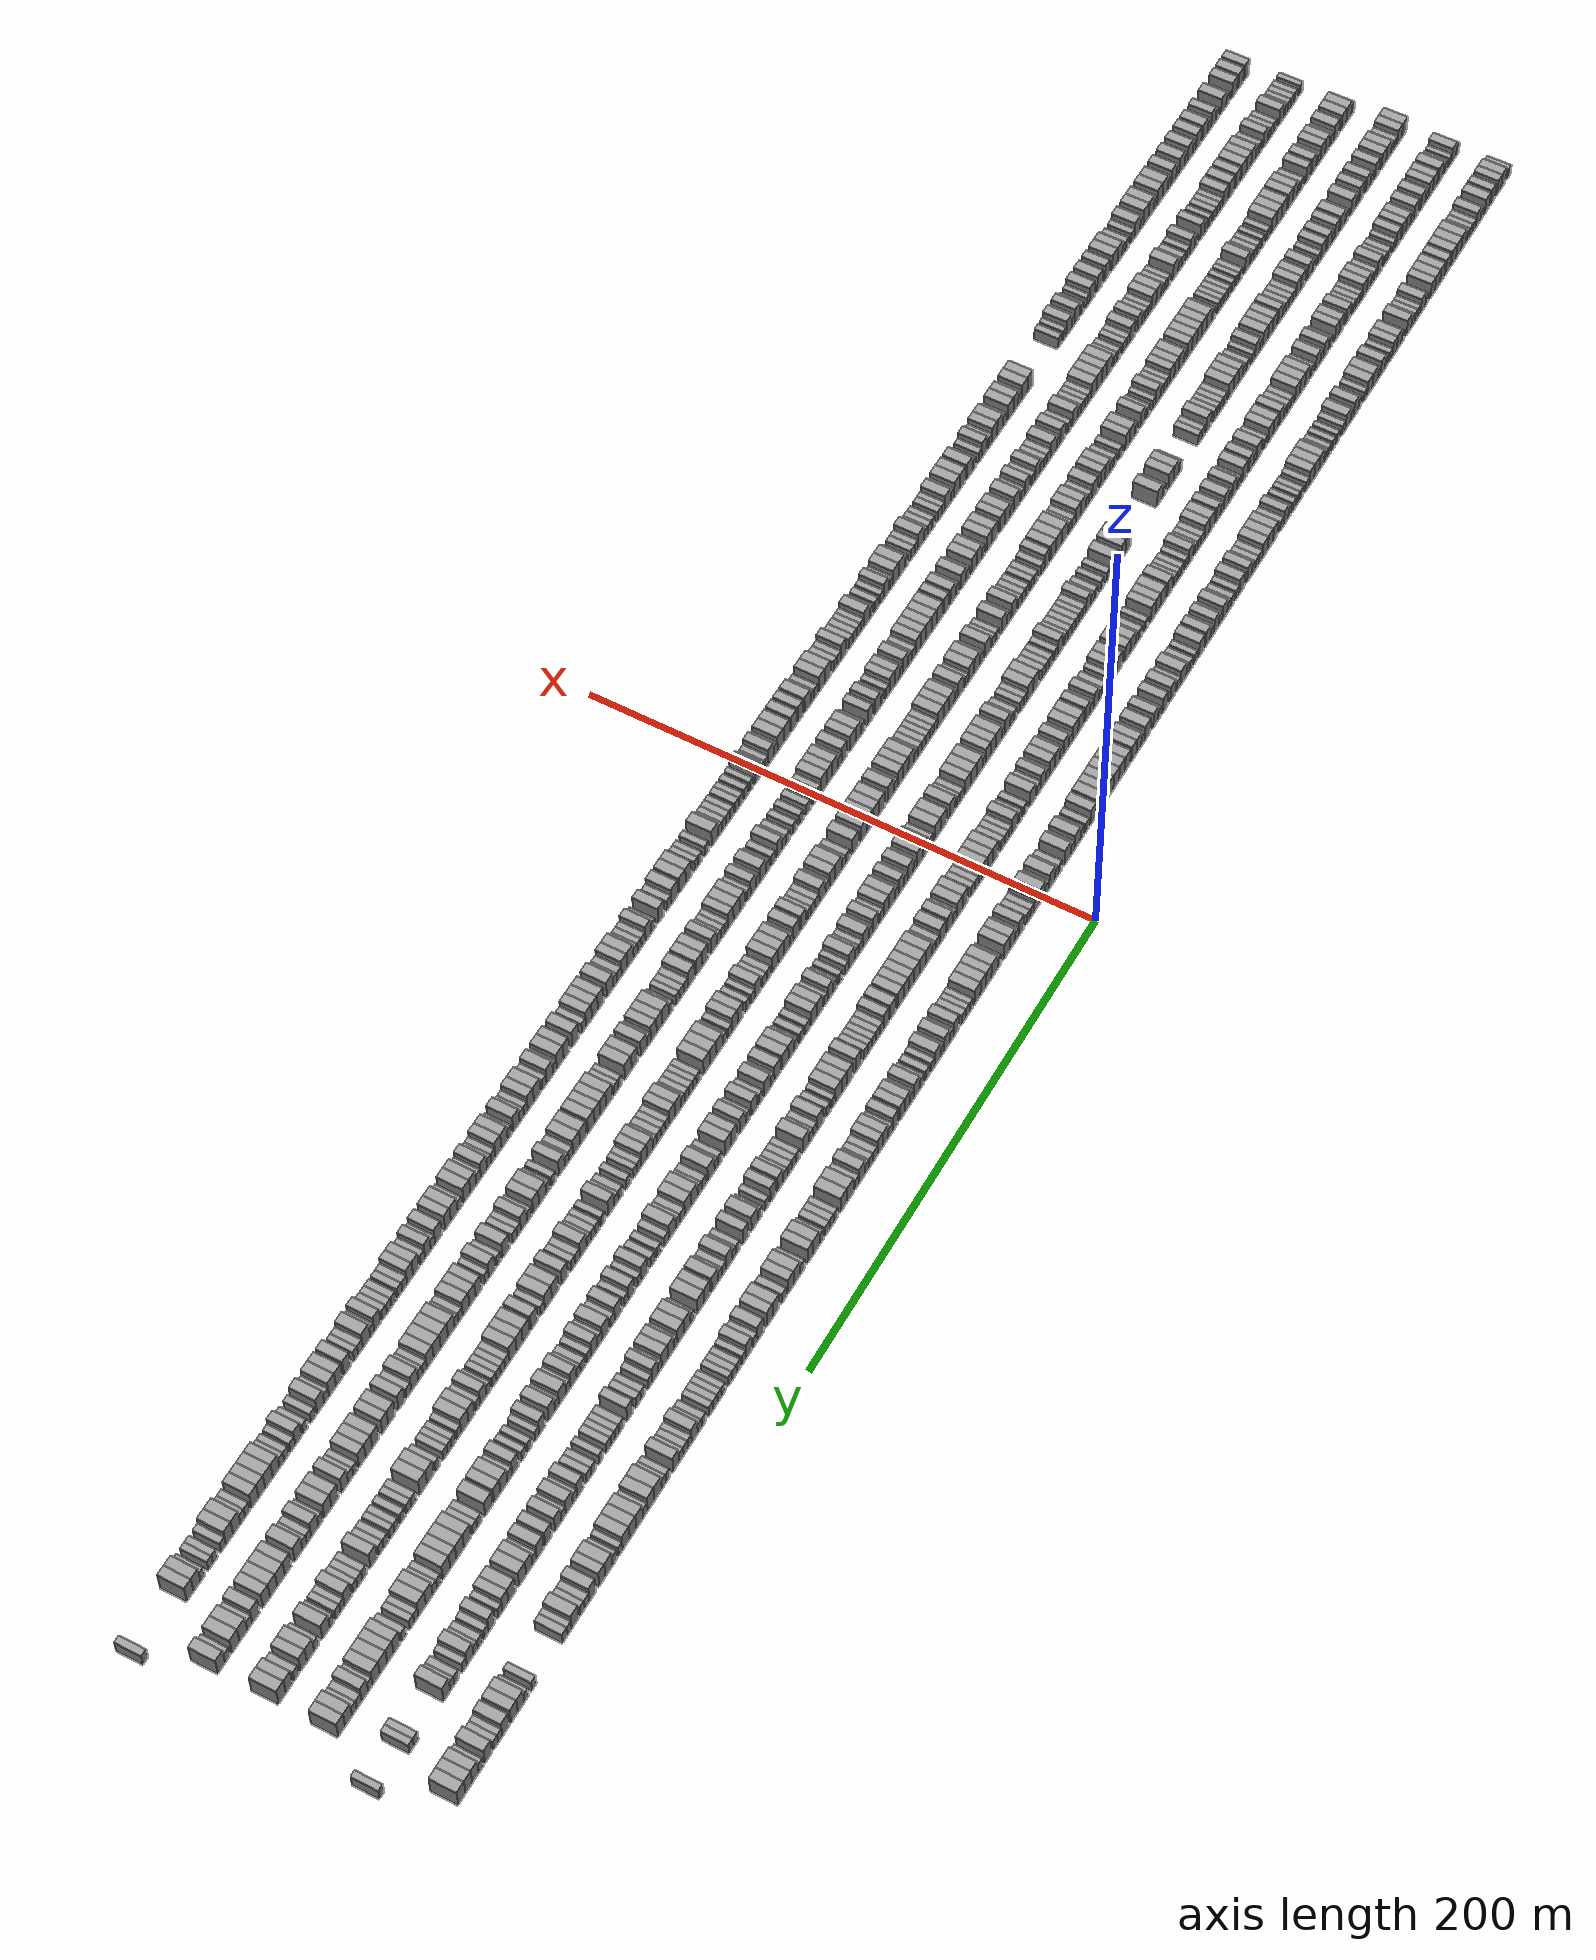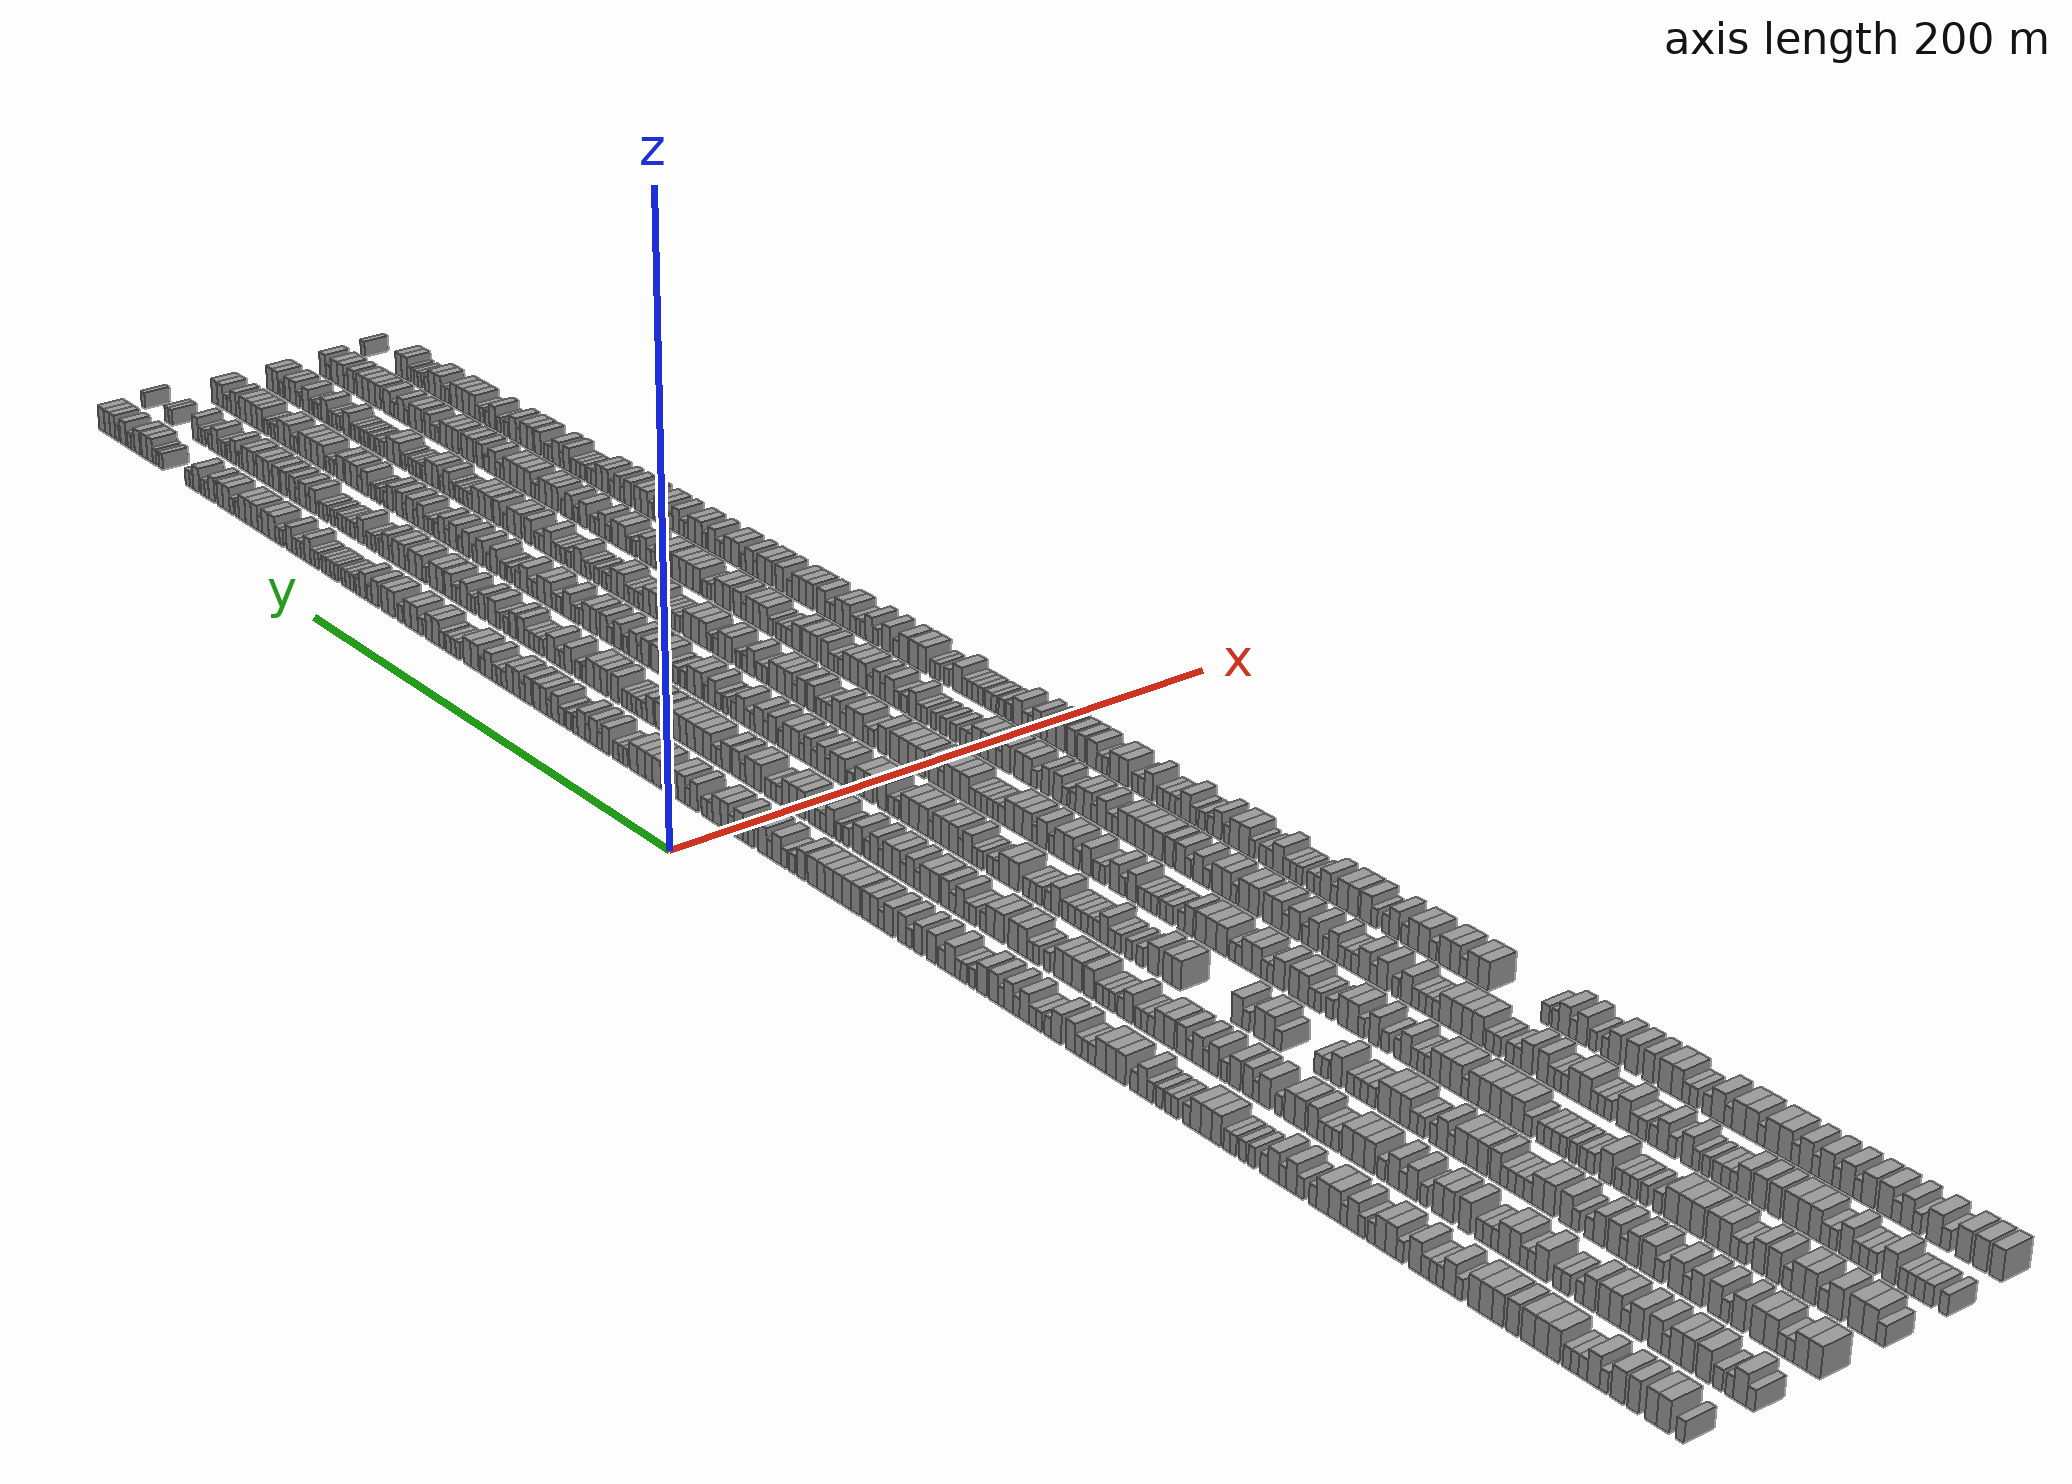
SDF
<sdf version="1.6">
 <world name="default">
  <scene>
   <sky><clouds><speed>12</speed></clouds></sky>
   <ambient>0.4 0.4 0.4 1</ambient>
   <background>0.7 0.7 0.7 1</background>
   <shadows>1</shadows>
  </scene>
  <gravity>0 0 -9.8066</gravity>
  <magnetic_field>6e-06 2.3e-05 -4.2e-05</magnetic_field>
  <physics default="0" name="default_physics" type="ode">
   <ode>
    <solver>
     <type>quick</type>
     <iters>10</iters>
     <sor>1.0</sor>
     <use_dynamic_moi_rescaling>0</use_dynamic_moi_rescaling>
    </solver>
    <constraints>
     <cfm>0</cfm>
     <erp>0.2</erp>
     <contact_max_correcting_vel>100</contact_max_correcting_vel>
     <contact_surface_layer>0.001</contact_surface_layer>
    </constraints>
   </ode>
   <max_step_size>0.004</max_step_size>
   <real_time_factor>1</real_time_factor>
   <real_time_update_rate>250</real_time_update_rate>
  </physics>
  <light name="sun" type="directional">
   <pose>0 0 10 0 0 0</pose>
   <diffuse>0.8 0.8 0.8 1</diffuse>
   <specular>0.2 0.2 0.2 1</specular>
   <attenuation>
    <range>1000</range>
    <constant>0.9</constant>
    <linear>0.01</linear>
    <quadratic>0.001</quadratic>
   </attenuation>
   <direction>-0.5 0.1 -0.9</direction>
  </light>
  <model name="building_1">
   <static>1</static>
   <pose>25.0000 -377.6687 0 0.000000 0.000000 0.000000</pose>
   <link name="link">
    <pose>0 0 3.00 0 0 0</pose>
    <collision name="collision"><geometry><box><size>10.0000 2.6627 6.0000</size></box></geometry></collision>
    <visual name="visual">
     <cast_shadows>0</cast_shadows>
     <geometry><box><size>10.0000 2.6627 6.0000</size></box></geometry>
     <material>
      <script>
       <uri>model://grey_wall/materials/scripts</uri>
       <uri>model://grey_wall/materials/textures</uri>
       <name>vrc/grey_wall</name>
      </script>
     </material>
    </visual>
   </link>
  </model>
  <model name="building_2">
   <static>1</static>
   <pose>25.0000 -372.3006 0 0.000000 0.000000 0.000000</pose>
   <link name="link">
    <pose>0 0 4.50 0 0 0</pose>
    <collision name="collision"><geometry><box><size>10.0000 4.0735 9.0000</size></box></geometry></collision>
    <visual name="visual">
     <cast_shadows>0</cast_shadows>
     <geometry><box><size>10.0000 4.0735 9.0000</size></box></geometry>
     <material>
      <script>
       <uri>model://grey_wall/materials/scripts</uri>
       <uri>model://grey_wall/materials/textures</uri>
       <name>vrc/grey_wall</name>
      </script>
     </material>
    </visual>
   </link>
  </model>
  <model name="building_3">
   <static>1</static>
   <pose>25.0000 -368.4430 0 0.000000 0.000000 0.000000</pose>
   <link name="link">
    <pose>0 0 4.50 0 0 0</pose>
    <collision name="collision"><geometry><box><size>10.0000 3.6417 9.0000</size></box></geometry></collision>
    <visual name="visual">
     <cast_shadows>0</cast_shadows>
     <geometry><box><size>10.0000 3.6417 9.0000</size></box></geometry>
     <material>
      <script>
       <uri>model://grey_wall/materials/scripts</uri>
       <uri>model://grey_wall/materials/textures</uri>
       <name>vrc/grey_wall</name>
      </script>
     </material>
    </visual>
   </link>
  </model>
  <model name="building_4">
   <static>1</static>
   <pose>25.0000 -362.8144 0 0.000000 0.000000 0.000000</pose>
   <link name="link">
    <pose>0 0 4.50 0 0 0</pose>
    <collision name="collision"><geometry><box><size>10.0000 3.6155 9.0000</size></box></geometry></collision>
    <visual name="visual">
     <cast_shadows>0</cast_shadows>
     <geometry><box><size>10.0000 3.6155 9.0000</size></box></geometry>
     <material>
      <script>
       <uri>model://grey_wall/materials/scripts</uri>
       <uri>model://grey_wall/materials/textures</uri>
       <name>vrc/grey_wall</name>
      </script>
     </material>
    </visual>
   </link>
  </model>
  <model name="building_5">
   <static>1</static>
   <pose>25.0000 -357.7991 0 0.000000 0.000000 0.000000</pose>
   <link name="link">
    <pose>0 0 4.50 0 0 0</pose>
    <collision name="collision"><geometry><box><size>10.0000 4.4150 9.0000</size></box></geometry></collision>
    <visual name="visual">
     <cast_shadows>0</cast_shadows>
     <geometry><box><size>10.0000 4.4150 9.0000</size></box></geometry>
     <material>
      <script>
       <uri>model://grey_wall/materials/scripts</uri>
       <uri>model://grey_wall/materials/textures</uri>
       <name>vrc/grey_wall</name>
      </script>
     </material>
    </visual>
   </link>
  </model>
  <model name="building_6">
   <static>1</static>
   <pose>25.0000 -353.2756 0 0.000000 0.000000 0.000000</pose>
   <link name="link">
    <pose>0 0 3.00 0 0 0</pose>
    <collision name="collision"><geometry><box><size>10.0000 2.6321 6.0000</size></box></geometry></collision>
    <visual name="visual">
     <cast_shadows>0</cast_shadows>
     <geometry><box><size>10.0000 2.6321 6.0000</size></box></geometry>
     <material>
      <script>
       <uri>model://grey_wall/materials/scripts</uri>
       <uri>model://grey_wall/materials/textures</uri>
       <name>vrc/grey_wall</name>
      </script>
     </material>
    </visual>
   </link>
  </model>
  <model name="building_7">
   <static>1</static>
   <pose>25.0000 -349.9345 0 0.000000 0.000000 0.000000</pose>
   <link name="link">
    <pose>0 0 4.50 0 0 0</pose>
    <collision name="collision"><geometry><box><size>10.0000 4.0500 9.0000</size></box></geometry></collision>
    <visual name="visual">
     <cast_shadows>0</cast_shadows>
     <geometry><box><size>10.0000 4.0500 9.0000</size></box></geometry>
     <material>
      <script>
       <uri>model://grey_wall/materials/scripts</uri>
       <uri>model://grey_wall/materials/textures</uri>
       <name>vrc/grey_wall</name>
      </script>
     </material>
    </visual>
   </link>
  </model>
  <model name="building_8">
   <static>1</static>
   <pose>25.0000 -346.4690 0 0.000000 0.000000 0.000000</pose>
   <link name="link">
    <pose>0 0 3.00 0 0 0</pose>
    <collision name="collision"><geometry><box><size>10.0000 2.8810 6.0000</size></box></geometry></collision>
    <visual name="visual">
     <cast_shadows>0</cast_shadows>
     <geometry><box><size>10.0000 2.8810 6.0000</size></box></geometry>
     <material>
      <script>
       <uri>model://grey_wall/materials/scripts</uri>
       <uri>model://grey_wall/materials/textures</uri>
       <name>vrc/grey_wall</name>
      </script>
     </material>
    </visual>
   </link>
  </model>
  <model name="building_9">
   <static>1</static>
   <pose>25.0000 -343.7226 0 0.000000 0.000000 0.000000</pose>
   <link name="link">
    <pose>0 0 3.00 0 0 0</pose>
    <collision name="collision"><geometry><box><size>10.0000 2.6119 6.0000</size></box></geometry></collision>
    <visual name="visual">
     <cast_shadows>0</cast_shadows>
     <geometry><box><size>10.0000 2.6119 6.0000</size></box></geometry>
     <material>
      <script>
       <uri>model://grey_wall/materials/scripts</uri>
       <uri>model://grey_wall/materials/textures</uri>
       <name>vrc/grey_wall</name>
      </script>
     </material>
    </visual>
   </link>
  </model>
  <model name="building_10">
   <static>1</static>
   <pose>25.0000 -341.1468 0 0.000000 0.000000 0.000000</pose>
   <link name="link">
    <pose>0 0 3.00 0 0 0</pose>
    <collision name="collision"><geometry><box><size>10.0000 2.5396 6.0000</size></box></geometry></collision>
    <visual name="visual">
     <cast_shadows>0</cast_shadows>
     <geometry><box><size>10.0000 2.5396 6.0000</size></box></geometry>
     <material>
      <script>
       <uri>model://grey_wall/materials/scripts</uri>
       <uri>model://grey_wall/materials/textures</uri>
       <name>vrc/grey_wall</name>
      </script>
     </material>
    </visual>
   </link>
  </model>
  <model name="building_11">
   <static>1</static>
   <pose>25.0000 -336.8118 0 0.000000 0.000000 0.000000</pose>
   <link name="link">
    <pose>0 0 4.50 0 0 0</pose>
    <collision name="collision"><geometry><box><size>10.0000 4.1303 9.0000</size></box></geometry></collision>
    <visual name="visual">
     <cast_shadows>0</cast_shadows>
     <geometry><box><size>10.0000 4.1303 9.0000</size></box></geometry>
     <material>
      <script>
       <uri>model://grey_wall/materials/scripts</uri>
       <uri>model://grey_wall/materials/textures</uri>
       <name>vrc/grey_wall</name>
      </script>
     </material>
    </visual>
   </link>
  </model>
  <model name="building_12">
   <static>1</static>
   <pose>25.0000 -332.5294 0 0.000000 0.000000 0.000000</pose>
   <link name="link">
    <pose>0 0 4.50 0 0 0</pose>
    <collision name="collision"><geometry><box><size>10.0000 4.4346 9.0000</size></box></geometry></collision>
    <visual name="visual">
     <cast_shadows>0</cast_shadows>
     <geometry><box><size>10.0000 4.4346 9.0000</size></box></geometry>
     <material>
      <script>
       <uri>model://grey_wall/materials/scripts</uri>
       <uri>model://grey_wall/materials/textures</uri>
       <name>vrc/grey_wall</name>
      </script>
     </material>
    </visual>
   </link>
  </model>
  <model name="building_13">
   <static>1</static>
   <pose>25.0000 -328.1446 0 0.000000 0.000000 0.000000</pose>
   <link name="link">
    <pose>0 0 4.50 0 0 0</pose>
    <collision name="collision"><geometry><box><size>10.0000 4.3350 9.0000</size></box></geometry></collision>
    <visual name="visual">
     <cast_shadows>0</cast_shadows>
     <geometry><box><size>10.0000 4.3350 9.0000</size></box></geometry>
     <material>
      <script>
       <uri>model://grey_wall/materials/scripts</uri>
       <uri>model://grey_wall/materials/textures</uri>
       <name>vrc/grey_wall</name>
      </script>
     </material>
    </visual>
   </link>
  </model>
  <model name="building_14">
   <static>1</static>
   <pose>25.0000 -322.9894 0 0.000000 0.000000 0.000000</pose>
   <link name="link">
    <pose>0 0 4.50 0 0 0</pose>
    <collision name="collision"><geometry><box><size>10.0000 3.9753 9.0000</size></box></geometry></collision>
    <visual name="visual">
     <cast_shadows>0</cast_shadows>
     <geometry><box><size>10.0000 3.9753 9.0000</size></box></geometry>
     <material>
      <script>
       <uri>model://grey_wall/materials/scripts</uri>
       <uri>model://grey_wall/materials/textures</uri>
       <name>vrc/grey_wall</name>
      </script>
     </material>
    </visual>
   </link>
  </model>
  <model name="building_15">
   <static>1</static>
   <pose>25.0000 -318.0408 0 0.000000 0.000000 0.000000</pose>
   <link name="link">
    <pose>0 0 4.50 0 0 0</pose>
    <collision name="collision"><geometry><box><size>10.0000 3.9221 9.0000</size></box></geometry></collision>
    <visual name="visual">
     <cast_shadows>0</cast_shadows>
     <geometry><box><size>10.0000 3.9221 9.0000</size></box></geometry>
     <material>
      <script>
       <uri>model://grey_wall/materials/scripts</uri>
       <uri>model://grey_wall/materials/textures</uri>
       <name>vrc/grey_wall</name>
      </script>
     </material>
    </visual>
   </link>
  </model>
  <model name="building_16">
   <static>1</static>
   <pose>25.0000 -313.9047 0 0.000000 0.000000 0.000000</pose>
   <link name="link">
    <pose>0 0 4.50 0 0 0</pose>
    <collision name="collision"><geometry><box><size>10.0000 4.3501 9.0000</size></box></geometry></collision>
    <visual name="visual">
     <cast_shadows>0</cast_shadows>
     <geometry><box><size>10.0000 4.3501 9.0000</size></box></geometry>
     <material>
      <script>
       <uri>model://grey_wall/materials/scripts</uri>
       <uri>model://grey_wall/materials/textures</uri>
       <name>vrc/grey_wall</name>
      </script>
     </material>
    </visual>
   </link>
  </model>
  <model name="building_17">
   <static>1</static>
   <pose>25.0000 -309.8075 0 0.000000 0.000000 0.000000</pose>
   <link name="link">
    <pose>0 0 4.50 0 0 0</pose>
    <collision name="collision"><geometry><box><size>10.0000 3.8443 9.0000</size></box></geometry></collision>
    <visual name="visual">
     <cast_shadows>0</cast_shadows>
     <geometry><box><size>10.0000 3.8443 9.0000</size></box></geometry>
     <material>
      <script>
       <uri>model://grey_wall/materials/scripts</uri>
       <uri>model://grey_wall/materials/textures</uri>
       <name>vrc/grey_wall</name>
      </script>
     </material>
    </visual>
   </link>
  </model>
  <model name="building_18">
   <static>1</static>
   <pose>25.0000 -304.6576 0 0.000000 0.000000 0.000000</pose>
   <link name="link">
    <pose>0 0 3.00 0 0 0</pose>
    <collision name="collision"><geometry><box><size>10.0000 2.4554 6.0000</size></box></geometry></collision>
    <visual name="visual">
     <cast_shadows>0</cast_shadows>
     <geometry><box><size>10.0000 2.4554 6.0000</size></box></geometry>
     <material>
      <script>
       <uri>model://grey_wall/materials/scripts</uri>
       <uri>model://grey_wall/materials/textures</uri>
       <name>vrc/grey_wall</name>
      </script>
     </material>
    </visual>
   </link>
  </model>
  <model name="building_19">
   <static>1</static>
   <pose>25.0000 -301.3828 0 0.000000 0.000000 0.000000</pose>
   <link name="link">
    <pose>0 0 4.50 0 0 0</pose>
    <collision name="collision"><geometry><box><size>10.0000 4.0942 9.0000</size></box></geometry></collision>
    <visual name="visual">
     <cast_shadows>0</cast_shadows>
     <geometry><box><size>10.0000 4.0942 9.0000</size></box></geometry>
     <material>
      <script>
       <uri>model://grey_wall/materials/scripts</uri>
       <uri>model://grey_wall/materials/textures</uri>
       <name>vrc/grey_wall</name>
      </script>
     </material>
    </visual>
   </link>
  </model>
  <model name="building_20">
   <static>1</static>
   <pose>25.0000 -298.0939 0 0.000000 0.000000 0.000000</pose>
   <link name="link">
    <pose>0 0 3.00 0 0 0</pose>
    <collision name="collision"><geometry><box><size>10.0000 2.4836 6.0000</size></box></geometry></collision>
    <visual name="visual">
     <cast_shadows>0</cast_shadows>
     <geometry><box><size>10.0000 2.4836 6.0000</size></box></geometry>
     <material>
      <script>
       <uri>model://grey_wall/materials/scripts</uri>
       <uri>model://grey_wall/materials/textures</uri>
       <name>vrc/grey_wall</name>
      </script>
     </material>
    </visual>
   </link>
  </model>
  <model name="building_21">
   <static>1</static>
   <pose>25.0000 -295.6009 0 0.000000 0.000000 0.000000</pose>
   <link name="link">
    <pose>0 0 3.00 0 0 0</pose>
    <collision name="collision"><geometry><box><size>10.0000 2.5025 6.0000</size></box></geometry></collision>
    <visual name="visual">
     <cast_shadows>0</cast_shadows>
     <geometry><box><size>10.0000 2.5025 6.0000</size></box></geometry>
     <material>
      <script>
       <uri>model://grey_wall/materials/scripts</uri>
       <uri>model://grey_wall/materials/textures</uri>
       <name>vrc/grey_wall</name>
      </script>
     </material>
    </visual>
   </link>
  </model>
  <model name="building_22">
   <static>1</static>
   <pose>25.0000 -292.8874 0 0.000000 0.000000 0.000000</pose>
   <link name="link">
    <pose>0 0 3.00 0 0 0</pose>
    <collision name="collision"><geometry><box><size>10.0000 2.9245 6.0000</size></box></geometry></collision>
    <visual name="visual">
     <cast_shadows>0</cast_shadows>
     <geometry><box><size>10.0000 2.9245 6.0000</size></box></geometry>
     <material>
      <script>
       <uri>model://grey_wall/materials/scripts</uri>
       <uri>model://grey_wall/materials/textures</uri>
       <name>vrc/grey_wall</name>
      </script>
     </material>
    </visual>
   </link>
  </model>
  <model name="building_23">
   <static>1</static>
   <pose>25.0000 -289.3206 0 0.000000 0.000000 0.000000</pose>
   <link name="link">
    <pose>0 0 4.50 0 0 0</pose>
    <collision name="collision"><geometry><box><size>10.0000 4.2092 9.0000</size></box></geometry></collision>
    <visual name="visual">
     <cast_shadows>0</cast_shadows>
     <geometry><box><size>10.0000 4.2092 9.0000</size></box></geometry>
     <material>
      <script>
       <uri>model://grey_wall/materials/scripts</uri>
       <uri>model://grey_wall/materials/textures</uri>
       <name>vrc/grey_wall</name>
      </script>
     </material>
    </visual>
   </link>
  </model>
  <model name="building_24">
   <static>1</static>
   <pose>25.0000 -283.9570 0 0.000000 0.000000 0.000000</pose>
   <link name="link">
    <pose>0 0 3.00 0 0 0</pose>
    <collision name="collision"><geometry><box><size>10.0000 2.5179 6.0000</size></box></geometry></collision>
    <visual name="visual">
     <cast_shadows>0</cast_shadows>
     <geometry><box><size>10.0000 2.5179 6.0000</size></box></geometry>
     <material>
      <script>
       <uri>model://grey_wall/materials/scripts</uri>
       <uri>model://grey_wall/materials/textures</uri>
       <name>vrc/grey_wall</name>
      </script>
     </material>
    </visual>
   </link>
  </model>
  <model name="building_25">
   <static>1</static>
   <pose>25.0000 -280.7418 0 0.000000 0.000000 0.000000</pose>
   <link name="link">
    <pose>0 0 4.50 0 0 0</pose>
    <collision name="collision"><geometry><box><size>10.0000 3.9124 9.0000</size></box></geometry></collision>
    <visual name="visual">
     <cast_shadows>0</cast_shadows>
     <geometry><box><size>10.0000 3.9124 9.0000</size></box></geometry>
     <material>
      <script>
       <uri>model://grey_wall/materials/scripts</uri>
       <uri>model://grey_wall/materials/textures</uri>
       <name>vrc/grey_wall</name>
      </script>
     </material>
    </visual>
   </link>
  </model>
  <model name="building_26">
   <static>1</static>
   <pose>25.0000 -276.9151 0 0.000000 0.000000 0.000000</pose>
   <link name="link">
    <pose>0 0 4.50 0 0 0</pose>
    <collision name="collision"><geometry><box><size>10.0000 3.7411 9.0000</size></box></geometry></collision>
    <visual name="visual">
     <cast_shadows>0</cast_shadows>
     <geometry><box><size>10.0000 3.7411 9.0000</size></box></geometry>
     <material>
      <script>
       <uri>model://grey_wall/materials/scripts</uri>
       <uri>model://grey_wall/materials/textures</uri>
       <name>vrc/grey_wall</name>
      </script>
     </material>
    </visual>
   </link>
  </model>
  <model name="building_27">
   <static>1</static>
   <pose>25.0000 -273.7296 0 0.000000 0.000000 0.000000</pose>
   <link name="link">
    <pose>0 0 3.00 0 0 0</pose>
    <collision name="collision"><geometry><box><size>10.0000 2.6299 6.0000</size></box></geometry></collision>
    <visual name="visual">
     <cast_shadows>0</cast_shadows>
     <geometry><box><size>10.0000 2.6299 6.0000</size></box></geometry>
     <material>
      <script>
       <uri>model://grey_wall/materials/scripts</uri>
       <uri>model://grey_wall/materials/textures</uri>
       <name>vrc/grey_wall</name>
      </script>
     </material>
    </visual>
   </link>
  </model>
  <model name="building_28">
   <static>1</static>
   <pose>25.0000 -270.1575 0 0.000000 0.000000 0.000000</pose>
   <link name="link">
    <pose>0 0 3.00 0 0 0</pose>
    <collision name="collision"><geometry><box><size>10.0000 2.5143 6.0000</size></box></geometry></collision>
    <visual name="visual">
     <cast_shadows>0</cast_shadows>
     <geometry><box><size>10.0000 2.5143 6.0000</size></box></geometry>
     <material>
      <script>
       <uri>model://grey_wall/materials/scripts</uri>
       <uri>model://grey_wall/materials/textures</uri>
       <name>vrc/grey_wall</name>
      </script>
     </material>
    </visual>
   </link>
  </model>
  <model name="building_29">
   <static>1</static>
   <pose>25.0000 -266.9307 0 0.000000 0.000000 0.000000</pose>
   <link name="link">
    <pose>0 0 4.50 0 0 0</pose>
    <collision name="collision"><geometry><box><size>10.0000 3.9392 9.0000</size></box></geometry></collision>
    <visual name="visual">
     <cast_shadows>0</cast_shadows>
     <geometry><box><size>10.0000 3.9392 9.0000</size></box></geometry>
     <material>
      <script>
       <uri>model://grey_wall/materials/scripts</uri>
       <uri>model://grey_wall/materials/textures</uri>
       <name>vrc/grey_wall</name>
      </script>
     </material>
    </visual>
   </link>
  </model>
  <model name="building_30">
   <static>1</static>
   <pose>25.0000 -263.7088 0 0.000000 0.000000 0.000000</pose>
   <link name="link">
    <pose>0 0 3.00 0 0 0</pose>
    <collision name="collision"><geometry><box><size>10.0000 2.5048 6.0000</size></box></geometry></collision>
    <visual name="visual">
     <cast_shadows>0</cast_shadows>
     <geometry><box><size>10.0000 2.5048 6.0000</size></box></geometry>
     <material>
      <script>
       <uri>model://grey_wall/materials/scripts</uri>
       <uri>model://grey_wall/materials/textures</uri>
       <name>vrc/grey_wall</name>
      </script>
     </material>
    </visual>
   </link>
  </model>
  <model name="building_31">
   <static>1</static>
   <pose>25.0000 -260.3058 0 0.000000 0.000000 0.000000</pose>
   <link name="link">
    <pose>0 0 4.50 0 0 0</pose>
    <collision name="collision"><geometry><box><size>10.0000 4.3012 9.0000</size></box></geometry></collision>
    <visual name="visual">
     <cast_shadows>0</cast_shadows>
     <geometry><box><size>10.0000 4.3012 9.0000</size></box></geometry>
     <material>
      <script>
       <uri>model://grey_wall/materials/scripts</uri>
       <uri>model://grey_wall/materials/textures</uri>
       <name>vrc/grey_wall</name>
      </script>
     </material>
    </visual>
   </link>
  </model>
  <model name="building_32">
   <static>1</static>
   <pose>25.0000 -255.9137 0 0.000000 0.000000 0.000000</pose>
   <link name="link">
    <pose>0 0 4.50 0 0 0</pose>
    <collision name="collision"><geometry><box><size>10.0000 4.4830 9.0000</size></box></geometry></collision>
    <visual name="visual">
     <cast_shadows>0</cast_shadows>
     <geometry><box><size>10.0000 4.4830 9.0000</size></box></geometry>
     <material>
      <script>
       <uri>model://grey_wall/materials/scripts</uri>
       <uri>model://grey_wall/materials/textures</uri>
       <name>vrc/grey_wall</name>
      </script>
     </material>
    </visual>
   </link>
  </model>
  <model name="building_33">
   <static>1</static>
   <pose>25.0000 -252.3384 0 0.000000 0.000000 0.000000</pose>
   <link name="link">
    <pose>0 0 3.00 0 0 0</pose>
    <collision name="collision"><geometry><box><size>10.0000 2.6676 6.0000</size></box></geometry></collision>
    <visual name="visual">
     <cast_shadows>0</cast_shadows>
     <geometry><box><size>10.0000 2.6676 6.0000</size></box></geometry>
     <material>
      <script>
       <uri>model://grey_wall/materials/scripts</uri>
       <uri>model://grey_wall/materials/textures</uri>
       <name>vrc/grey_wall</name>
      </script>
     </material>
    </visual>
   </link>
  </model>
  <model name="building_34">
   <static>1</static>
   <pose>25.0000 -247.6434 0 0.000000 0.000000 0.000000</pose>
   <link name="link">
    <pose>0 0 3.00 0 0 0</pose>
    <collision name="collision"><geometry><box><size>10.0000 2.7224 6.0000</size></box></geometry></collision>
    <visual name="visual">
     <cast_shadows>0</cast_shadows>
     <geometry><box><size>10.0000 2.7224 6.0000</size></box></geometry>
     <material>
      <script>
       <uri>model://grey_wall/materials/scripts</uri>
       <uri>model://grey_wall/materials/textures</uri>
       <name>vrc/grey_wall</name>
      </script>
     </material>
    </visual>
   </link>
  </model>
  <model name="building_35">
   <static>1</static>
   <pose>25.0000 -244.3113 0 0.000000 0.000000 0.000000</pose>
   <link name="link">
    <pose>0 0 4.50 0 0 0</pose>
    <collision name="collision"><geometry><box><size>10.0000 3.9418 9.0000</size></box></geometry></collision>
    <visual name="visual">
     <cast_shadows>0</cast_shadows>
     <geometry><box><size>10.0000 3.9418 9.0000</size></box></geometry>
     <material>
      <script>
       <uri>model://grey_wall/materials/scripts</uri>
       <uri>model://grey_wall/materials/textures</uri>
       <name>vrc/grey_wall</name>
      </script>
     </material>
    </visual>
   </link>
  </model>
  <model name="building_36">
   <static>1</static>
   <pose>25.0000 -240.9997 0 0.000000 0.000000 0.000000</pose>
   <link name="link">
    <pose>0 0 3.00 0 0 0</pose>
    <collision name="collision"><geometry><box><size>10.0000 2.6813 6.0000</size></box></geometry></collision>
    <visual name="visual">
     <cast_shadows>0</cast_shadows>
     <geometry><box><size>10.0000 2.6813 6.0000</size></box></geometry>
     <material>
      <script>
       <uri>model://grey_wall/materials/scripts</uri>
       <uri>model://grey_wall/materials/textures</uri>
       <name>vrc/grey_wall</name>
      </script>
     </material>
    </visual>
   </link>
  </model>
  <model name="building_37">
   <static>1</static>
   <pose>25.0000 -237.5609 0 0.000000 0.000000 0.000000</pose>
   <link name="link">
    <pose>0 0 4.50 0 0 0</pose>
    <collision name="collision"><geometry><box><size>10.0000 4.1962 9.0000</size></box></geometry></collision>
    <visual name="visual">
     <cast_shadows>0</cast_shadows>
     <geometry><box><size>10.0000 4.1962 9.0000</size></box></geometry>
     <material>
      <script>
       <uri>model://grey_wall/materials/scripts</uri>
       <uri>model://grey_wall/materials/textures</uri>
       <name>vrc/grey_wall</name>
      </script>
     </material>
    </visual>
   </link>
  </model>
  <model name="building_38">
   <static>1</static>
   <pose>25.0000 -234.0319 0 0.000000 0.000000 0.000000</pose>
   <link name="link">
    <pose>0 0 3.00 0 0 0</pose>
    <collision name="collision"><geometry><box><size>10.0000 2.8618 6.0000</size></box></geometry></collision>
    <visual name="visual">
     <cast_shadows>0</cast_shadows>
     <geometry><box><size>10.0000 2.8618 6.0000</size></box></geometry>
     <material>
      <script>
       <uri>model://grey_wall/materials/scripts</uri>
       <uri>model://grey_wall/materials/textures</uri>
       <name>vrc/grey_wall</name>
      </script>
     </material>
    </visual>
   </link>
  </model>
  <model name="building_39">
   <static>1</static>
   <pose>25.0000 -229.3472 0 0.000000 0.000000 0.000000</pose>
   <link name="link">
    <pose>0 0 3.00 0 0 0</pose>
    <collision name="collision"><geometry><box><size>10.0000 2.5078 6.0000</size></box></geometry></collision>
    <visual name="visual">
     <cast_shadows>0</cast_shadows>
     <geometry><box><size>10.0000 2.5078 6.0000</size></box></geometry>
     <material>
      <script>
       <uri>model://grey_wall/materials/scripts</uri>
       <uri>model://grey_wall/materials/textures</uri>
       <name>vrc/grey_wall</name>
      </script>
     </material>
    </visual>
   </link>
  </model>
  <model name="building_40">
   <static>1</static>
   <pose>25.0000 -225.7696 0 0.000000 0.000000 0.000000</pose>
   <link name="link">
    <pose>0 0 3.00 0 0 0</pose>
    <collision name="collision"><geometry><box><size>10.0000 2.6474 6.0000</size></box></geometry></collision>
    <visual name="visual">
     <cast_shadows>0</cast_shadows>
     <geometry><box><size>10.0000 2.6474 6.0000</size></box></geometry>
     <material>
      <script>
       <uri>model://grey_wall/materials/scripts</uri>
       <uri>model://grey_wall/materials/textures</uri>
       <name>vrc/grey_wall</name>
      </script>
     </material>
    </visual>
   </link>
  </model>
  <model name="building_41">
   <static>1</static>
   <pose>25.0000 -222.1963 0 0.000000 0.000000 0.000000</pose>
   <link name="link">
    <pose>0 0 3.00 0 0 0</pose>
    <collision name="collision"><geometry><box><size>10.0000 2.4990 6.0000</size></box></geometry></collision>
    <visual name="visual">
     <cast_shadows>0</cast_shadows>
     <geometry><box><size>10.0000 2.4990 6.0000</size></box></geometry>
     <material>
      <script>
       <uri>model://grey_wall/materials/scripts</uri>
       <uri>model://grey_wall/materials/textures</uri>
       <name>vrc/grey_wall</name>
      </script>
     </material>
    </visual>
   </link>
  </model>
  <model name="building_42">
   <static>1</static>
   <pose>25.0000 -219.7313 0 0.000000 0.000000 0.000000</pose>
   <link name="link">
    <pose>0 0 3.00 0 0 0</pose>
    <collision name="collision"><geometry><box><size>10.0000 2.4311 6.0000</size></box></geometry></collision>
    <visual name="visual">
     <cast_shadows>0</cast_shadows>
     <geometry><box><size>10.0000 2.4311 6.0000</size></box></geometry>
     <material>
      <script>
       <uri>model://grey_wall/materials/scripts</uri>
       <uri>model://grey_wall/materials/textures</uri>
       <name>vrc/grey_wall</name>
      </script>
     </material>
    </visual>
   </link>
  </model>
  <model name="building_43">
   <static>1</static>
   <pose>25.0000 -215.6574 0 0.000000 0.000000 0.000000</pose>
   <link name="link">
    <pose>0 0 4.50 0 0 0</pose>
    <collision name="collision"><geometry><box><size>10.0000 3.7165 9.0000</size></box></geometry></collision>
    <visual name="visual">
     <cast_shadows>0</cast_shadows>
     <geometry><box><size>10.0000 3.7165 9.0000</size></box></geometry>
     <material>
      <script>
       <uri>model://grey_wall/materials/scripts</uri>
       <uri>model://grey_wall/materials/textures</uri>
       <name>vrc/grey_wall</name>
      </script>
     </material>
    </visual>
   </link>
  </model>
  <model name="building_44">
   <static>1</static>
   <pose>25.0000 -211.6798 0 0.000000 0.000000 0.000000</pose>
   <link name="link">
    <pose>0 0 4.50 0 0 0</pose>
    <collision name="collision"><geometry><box><size>10.0000 4.2387 9.0000</size></box></geometry></collision>
    <visual name="visual">
     <cast_shadows>0</cast_shadows>
     <geometry><box><size>10.0000 4.2387 9.0000</size></box></geometry>
     <material>
      <script>
       <uri>model://grey_wall/materials/scripts</uri>
       <uri>model://grey_wall/materials/textures</uri>
       <name>vrc/grey_wall</name>
      </script>
     </material>
    </visual>
   </link>
  </model>
  <model name="building_45">
   <static>1</static>
   <pose>25.0000 -207.5407 0 0.000000 0.000000 0.000000</pose>
   <link name="link">
    <pose>0 0 4.50 0 0 0</pose>
    <collision name="collision"><geometry><box><size>10.0000 4.0395 9.0000</size></box></geometry></collision>
    <visual name="visual">
     <cast_shadows>0</cast_shadows>
     <geometry><box><size>10.0000 4.0395 9.0000</size></box></geometry>
     <material>
      <script>
       <uri>model://grey_wall/materials/scripts</uri>
       <uri>model://grey_wall/materials/textures</uri>
       <name>vrc/grey_wall</name>
      </script>
     </material>
    </visual>
   </link>
  </model>
  <model name="building_46">
   <static>1</static>
   <pose>25.0000 -204.0772 0 0.000000 0.000000 0.000000</pose>
   <link name="link">
    <pose>0 0 3.00 0 0 0</pose>
    <collision name="collision"><geometry><box><size>10.0000 2.8876 6.0000</size></box></geometry></collision>
    <visual name="visual">
     <cast_shadows>0</cast_shadows>
     <geometry><box><size>10.0000 2.8876 6.0000</size></box></geometry>
     <material>
      <script>
       <uri>model://grey_wall/materials/scripts</uri>
       <uri>model://grey_wall/materials/textures</uri>
       <name>vrc/grey_wall</name>
      </script>
     </material>
    </visual>
   </link>
  </model>
  <model name="building_47">
   <static>1</static>
   <pose>25.0000 -199.2927 0 0.000000 0.000000 0.000000</pose>
   <link name="link">
    <pose>0 0 3.00 0 0 0</pose>
    <collision name="collision"><geometry><box><size>10.0000 2.6813 6.0000</size></box></geometry></collision>
    <visual name="visual">
     <cast_shadows>0</cast_shadows>
     <geometry><box><size>10.0000 2.6813 6.0000</size></box></geometry>
     <material>
      <script>
       <uri>model://grey_wall/materials/scripts</uri>
       <uri>model://grey_wall/materials/textures</uri>
       <name>vrc/grey_wall</name>
      </script>
     </material>
    </visual>
   </link>
  </model>
  <model name="building_48">
   <static>1</static>
   <pose>25.0000 -196.7364 0 0.000000 0.000000 0.000000</pose>
   <link name="link">
    <pose>0 0 3.00 0 0 0</pose>
    <collision name="collision"><geometry><box><size>10.0000 2.4314 6.0000</size></box></geometry></collision>
    <visual name="visual">
     <cast_shadows>0</cast_shadows>
     <geometry><box><size>10.0000 2.4314 6.0000</size></box></geometry>
     <material>
      <script>
       <uri>model://grey_wall/materials/scripts</uri>
       <uri>model://grey_wall/materials/textures</uri>
       <name>vrc/grey_wall</name>
      </script>
     </material>
    </visual>
   </link>
  </model>
  <model name="building_49">
   <static>1</static>
   <pose>25.0000 -193.1813 0 0.000000 0.000000 0.000000</pose>
   <link name="link">
    <pose>0 0 3.00 0 0 0</pose>
    <collision name="collision"><geometry><box><size>10.0000 2.6788 6.0000</size></box></geometry></collision>
    <visual name="visual">
     <cast_shadows>0</cast_shadows>
     <geometry><box><size>10.0000 2.6788 6.0000</size></box></geometry>
     <material>
      <script>
       <uri>model://grey_wall/materials/scripts</uri>
       <uri>model://grey_wall/materials/textures</uri>
       <name>vrc/grey_wall</name>
      </script>
     </material>
    </visual>
   </link>
  </model>
  <model name="building_50">
   <static>1</static>
   <pose>25.0000 -189.5061 0 0.000000 0.000000 0.000000</pose>
   <link name="link">
    <pose>0 0 3.00 0 0 0</pose>
    <collision name="collision"><geometry><box><size>10.0000 2.6715 6.0000</size></box></geometry></collision>
    <visual name="visual">
     <cast_shadows>0</cast_shadows>
     <geometry><box><size>10.0000 2.6715 6.0000</size></box></geometry>
     <material>
      <script>
       <uri>model://grey_wall/materials/scripts</uri>
       <uri>model://grey_wall/materials/textures</uri>
       <name>vrc/grey_wall</name>
      </script>
     </material>
    </visual>
   </link>
  </model>
  <model name="building_51">
   <static>1</static>
   <pose>25.0000 -186.3467 0 0.000000 0.000000 0.000000</pose>
   <link name="link">
    <pose>0 0 4.50 0 0 0</pose>
    <collision name="collision"><geometry><box><size>10.0000 3.6473 9.0000</size></box></geometry></collision>
    <visual name="visual">
     <cast_shadows>0</cast_shadows>
     <geometry><box><size>10.0000 3.6473 9.0000</size></box></geometry>
     <material>
      <script>
       <uri>model://grey_wall/materials/scripts</uri>
       <uri>model://grey_wall/materials/textures</uri>
       <name>vrc/grey_wall</name>
      </script>
     </material>
    </visual>
   </link>
  </model>
  <model name="building_52">
   <static>1</static>
   <pose>25.0000 -183.0482 0 0.000000 0.000000 0.000000</pose>
   <link name="link">
    <pose>0 0 3.00 0 0 0</pose>
    <collision name="collision"><geometry><box><size>10.0000 2.9497 6.0000</size></box></geometry></collision>
    <visual name="visual">
     <cast_shadows>0</cast_shadows>
     <geometry><box><size>10.0000 2.9497 6.0000</size></box></geometry>
     <material>
      <script>
       <uri>model://grey_wall/materials/scripts</uri>
       <uri>model://grey_wall/materials/textures</uri>
       <name>vrc/grey_wall</name>
      </script>
     </material>
    </visual>
   </link>
  </model>
  <model name="building_53">
   <static>1</static>
   <pose>25.0000 -177.6389 0 0.000000 0.000000 0.000000</pose>
   <link name="link">
    <pose>0 0 4.50 0 0 0</pose>
    <collision name="collision"><geometry><box><size>10.0000 3.8689 9.0000</size></box></geometry></collision>
    <visual name="visual">
     <cast_shadows>0</cast_shadows>
     <geometry><box><size>10.0000 3.8689 9.0000</size></box></geometry>
     <material>
      <script>
       <uri>model://grey_wall/materials/scripts</uri>
       <uri>model://grey_wall/materials/textures</uri>
       <name>vrc/grey_wall</name>
      </script>
     </material>
    </visual>
   </link>
  </model>
  <model name="building_54">
   <static>1</static>
   <pose>25.0000 -173.6329 0 0.000000 0.000000 0.000000</pose>
   <link name="link">
    <pose>0 0 4.50 0 0 0</pose>
    <collision name="collision"><geometry><box><size>10.0000 4.1431 9.0000</size></box></geometry></collision>
    <visual name="visual">
     <cast_shadows>0</cast_shadows>
     <geometry><box><size>10.0000 4.1431 9.0000</size></box></geometry>
     <material>
      <script>
       <uri>model://grey_wall/materials/scripts</uri>
       <uri>model://grey_wall/materials/textures</uri>
       <name>vrc/grey_wall</name>
      </script>
     </material>
    </visual>
   </link>
  </model>
  <model name="building_55">
   <static>1</static>
   <pose>25.0000 -169.4223 0 0.000000 0.000000 0.000000</pose>
   <link name="link">
    <pose>0 0 4.50 0 0 0</pose>
    <collision name="collision"><geometry><box><size>10.0000 4.2781 9.0000</size></box></geometry></collision>
    <visual name="visual">
     <cast_shadows>0</cast_shadows>
     <geometry><box><size>10.0000 4.2781 9.0000</size></box></geometry>
     <material>
      <script>
       <uri>model://grey_wall/materials/scripts</uri>
       <uri>model://grey_wall/materials/textures</uri>
       <name>vrc/grey_wall</name>
      </script>
     </material>
    </visual>
   </link>
  </model>
  <model name="building_56">
   <static>1</static>
   <pose>25.0000 -165.7944 0 0.000000 0.000000 0.000000</pose>
   <link name="link">
    <pose>0 0 3.00 0 0 0</pose>
    <collision name="collision"><geometry><box><size>10.0000 2.9778 6.0000</size></box></geometry></collision>
    <visual name="visual">
     <cast_shadows>0</cast_shadows>
     <geometry><box><size>10.0000 2.9778 6.0000</size></box></geometry>
     <material>
      <script>
       <uri>model://grey_wall/materials/scripts</uri>
       <uri>model://grey_wall/materials/textures</uri>
       <name>vrc/grey_wall</name>
      </script>
     </material>
    </visual>
   </link>
  </model>
  <model name="building_57">
   <static>1</static>
   <pose>25.0000 -162.9215 0 0.000000 0.000000 0.000000</pose>
   <link name="link">
    <pose>0 0 3.00 0 0 0</pose>
    <collision name="collision"><geometry><box><size>10.0000 2.7679 6.0000</size></box></geometry></collision>
    <visual name="visual">
     <cast_shadows>0</cast_shadows>
     <geometry><box><size>10.0000 2.7679 6.0000</size></box></geometry>
     <material>
      <script>
       <uri>model://grey_wall/materials/scripts</uri>
       <uri>model://grey_wall/materials/textures</uri>
       <name>vrc/grey_wall</name>
      </script>
     </material>
    </visual>
   </link>
  </model>
  <model name="building_58">
   <static>1</static>
   <pose>25.0000 -160.1799 0 0.000000 0.000000 0.000000</pose>
   <link name="link">
    <pose>0 0 3.00 0 0 0</pose>
    <collision name="collision"><geometry><box><size>10.0000 2.7152 6.0000</size></box></geometry></collision>
    <visual name="visual">
     <cast_shadows>0</cast_shadows>
     <geometry><box><size>10.0000 2.7152 6.0000</size></box></geometry>
     <material>
      <script>
       <uri>model://grey_wall/materials/scripts</uri>
       <uri>model://grey_wall/materials/textures</uri>
       <name>vrc/grey_wall</name>
      </script>
     </material>
    </visual>
   </link>
  </model>
  <model name="building_59">
   <static>1</static>
   <pose>25.0000 -156.9391 0 0.000000 0.000000 0.000000</pose>
   <link name="link">
    <pose>0 0 4.50 0 0 0</pose>
    <collision name="collision"><geometry><box><size>10.0000 3.7665 9.0000</size></box></geometry></collision>
    <visual name="visual">
     <cast_shadows>0</cast_shadows>
     <geometry><box><size>10.0000 3.7665 9.0000</size></box></geometry>
     <material>
      <script>
       <uri>model://grey_wall/materials/scripts</uri>
       <uri>model://grey_wall/materials/textures</uri>
       <name>vrc/grey_wall</name>
      </script>
     </material>
    </visual>
   </link>
  </model>
  <model name="building_60">
   <static>1</static>
   <pose>25.0000 -150.9437 0 0.000000 0.000000 0.000000</pose>
   <link name="link">
    <pose>0 0 4.50 0 0 0</pose>
    <collision name="collision"><geometry><box><size>10.0000 4.2244 9.0000</size></box></geometry></collision>
    <visual name="visual">
     <cast_shadows>0</cast_shadows>
     <geometry><box><size>10.0000 4.2244 9.0000</size></box></geometry>
     <material>
      <script>
       <uri>model://grey_wall/materials/scripts</uri>
       <uri>model://grey_wall/materials/textures</uri>
       <name>vrc/grey_wall</name>
      </script>
     </material>
    </visual>
   </link>
  </model>
  <model name="building_61">
   <static>1</static>
   <pose>25.0000 -147.3868 0 0.000000 0.000000 0.000000</pose>
   <link name="link">
    <pose>0 0 3.00 0 0 0</pose>
    <collision name="collision"><geometry><box><size>10.0000 2.8894 6.0000</size></box></geometry></collision>
    <visual name="visual">
     <cast_shadows>0</cast_shadows>
     <geometry><box><size>10.0000 2.8894 6.0000</size></box></geometry>
     <material>
      <script>
       <uri>model://grey_wall/materials/scripts</uri>
       <uri>model://grey_wall/materials/textures</uri>
       <name>vrc/grey_wall</name>
      </script>
     </material>
    </visual>
   </link>
  </model>
  <model name="building_62">
   <static>1</static>
   <pose>25.0000 -143.5792 0 0.000000 0.000000 0.000000</pose>
   <link name="link">
    <pose>0 0 3.00 0 0 0</pose>
    <collision name="collision"><geometry><box><size>10.0000 2.7258 6.0000</size></box></geometry></collision>
    <visual name="visual">
     <cast_shadows>0</cast_shadows>
     <geometry><box><size>10.0000 2.7258 6.0000</size></box></geometry>
     <material>
      <script>
       <uri>model://grey_wall/materials/scripts</uri>
       <uri>model://grey_wall/materials/textures</uri>
       <name>vrc/grey_wall</name>
      </script>
     </material>
    </visual>
   </link>
  </model>
  <model name="building_63">
   <static>1</static>
   <pose>25.0000 -140.7304 0 0.000000 0.000000 0.000000</pose>
   <link name="link">
    <pose>0 0 3.00 0 0 0</pose>
    <collision name="collision"><geometry><box><size>10.0000 2.9717 6.0000</size></box></geometry></collision>
    <visual name="visual">
     <cast_shadows>0</cast_shadows>
     <geometry><box><size>10.0000 2.9717 6.0000</size></box></geometry>
     <material>
      <script>
       <uri>model://grey_wall/materials/scripts</uri>
       <uri>model://grey_wall/materials/textures</uri>
       <name>vrc/grey_wall</name>
      </script>
     </material>
    </visual>
   </link>
  </model>
  <model name="building_64">
   <static>1</static>
   <pose>25.0000 -137.2774 0 0.000000 0.000000 0.000000</pose>
   <link name="link">
    <pose>0 0 4.50 0 0 0</pose>
    <collision name="collision"><geometry><box><size>10.0000 3.9343 9.0000</size></box></geometry></collision>
    <visual name="visual">
     <cast_shadows>0</cast_shadows>
     <geometry><box><size>10.0000 3.9343 9.0000</size></box></geometry>
     <material>
      <script>
       <uri>model://grey_wall/materials/scripts</uri>
       <uri>model://grey_wall/materials/textures</uri>
       <name>vrc/grey_wall</name>
      </script>
     </material>
    </visual>
   </link>
  </model>
  <model name="building_65">
   <static>1</static>
   <pose>25.0000 -133.8608 0 0.000000 0.000000 0.000000</pose>
   <link name="link">
    <pose>0 0 3.00 0 0 0</pose>
    <collision name="collision"><geometry><box><size>10.0000 2.8989 6.0000</size></box></geometry></collision>
    <visual name="visual">
     <cast_shadows>0</cast_shadows>
     <geometry><box><size>10.0000 2.8989 6.0000</size></box></geometry>
     <material>
      <script>
       <uri>model://grey_wall/materials/scripts</uri>
       <uri>model://grey_wall/materials/textures</uri>
       <name>vrc/grey_wall</name>
      </script>
     </material>
    </visual>
   </link>
  </model>
  <model name="building_66">
   <static>1</static>
   <pose>25.0000 -130.5296 0 0.000000 0.000000 0.000000</pose>
   <link name="link">
    <pose>0 0 4.50 0 0 0</pose>
    <collision name="collision"><geometry><box><size>10.0000 3.7636 9.0000</size></box></geometry></collision>
    <visual name="visual">
     <cast_shadows>0</cast_shadows>
     <geometry><box><size>10.0000 3.7636 9.0000</size></box></geometry>
     <material>
      <script>
       <uri>model://grey_wall/materials/scripts</uri>
       <uri>model://grey_wall/materials/textures</uri>
       <name>vrc/grey_wall</name>
      </script>
     </material>
    </visual>
   </link>
  </model>
  <model name="building_67">
   <static>1</static>
   <pose>25.0000 -127.2999 0 0.000000 0.000000 0.000000</pose>
   <link name="link">
    <pose>0 0 3.00 0 0 0</pose>
    <collision name="collision"><geometry><box><size>10.0000 2.6956 6.0000</size></box></geometry></collision>
    <visual name="visual">
     <cast_shadows>0</cast_shadows>
     <geometry><box><size>10.0000 2.6956 6.0000</size></box></geometry>
     <material>
      <script>
       <uri>model://grey_wall/materials/scripts</uri>
       <uri>model://grey_wall/materials/textures</uri>
       <name>vrc/grey_wall</name>
      </script>
     </material>
    </visual>
   </link>
  </model>
  <model name="building_68">
   <static>1</static>
   <pose>25.0000 -124.0299 0 0.000000 0.000000 0.000000</pose>
   <link name="link">
    <pose>0 0 4.50 0 0 0</pose>
    <collision name="collision"><geometry><box><size>10.0000 3.8445 9.0000</size></box></geometry></collision>
    <visual name="visual">
     <cast_shadows>0</cast_shadows>
     <geometry><box><size>10.0000 3.8445 9.0000</size></box></geometry>
     <material>
      <script>
       <uri>model://grey_wall/materials/scripts</uri>
       <uri>model://grey_wall/materials/textures</uri>
       <name>vrc/grey_wall</name>
      </script>
     </material>
    </visual>
   </link>
  </model>
  <model name="building_69">
   <static>1</static>
   <pose>25.0000 -118.9810 0 0.000000 0.000000 0.000000</pose>
   <link name="link">
    <pose>0 0 4.50 0 0 0</pose>
    <collision name="collision"><geometry><box><size>10.0000 4.2533 9.0000</size></box></geometry></collision>
    <visual name="visual">
     <cast_shadows>0</cast_shadows>
     <geometry><box><size>10.0000 4.2533 9.0000</size></box></geometry>
     <material>
      <script>
       <uri>model://grey_wall/materials/scripts</uri>
       <uri>model://grey_wall/materials/textures</uri>
       <name>vrc/grey_wall</name>
      </script>
     </material>
    </visual>
   </link>
  </model>
  <model name="building_70">
   <static>1</static>
   <pose>25.0000 -114.5784 0 0.000000 0.000000 0.000000</pose>
   <link name="link">
    <pose>0 0 3.00 0 0 0</pose>
    <collision name="collision"><geometry><box><size>10.0000 2.5518 6.0000</size></box></geometry></collision>
    <visual name="visual">
     <cast_shadows>0</cast_shadows>
     <geometry><box><size>10.0000 2.5518 6.0000</size></box></geometry>
     <material>
      <script>
       <uri>model://grey_wall/materials/scripts</uri>
       <uri>model://grey_wall/materials/textures</uri>
       <name>vrc/grey_wall</name>
      </script>
     </material>
    </visual>
   </link>
  </model>
  <model name="building_71">
   <static>1</static>
   <pose>25.0000 -110.9483 0 0.000000 0.000000 0.000000</pose>
   <link name="link">
    <pose>0 0 3.00 0 0 0</pose>
    <collision name="collision"><geometry><box><size>10.0000 2.7084 6.0000</size></box></geometry></collision>
    <visual name="visual">
     <cast_shadows>0</cast_shadows>
     <geometry><box><size>10.0000 2.7084 6.0000</size></box></geometry>
     <material>
      <script>
       <uri>model://grey_wall/materials/scripts</uri>
       <uri>model://grey_wall/materials/textures</uri>
       <name>vrc/grey_wall</name>
      </script>
     </material>
    </visual>
   </link>
  </model>
  <model name="building_72">
   <static>1</static>
   <pose>25.0000 -108.3103 0 0.000000 0.000000 0.000000</pose>
   <link name="link">
    <pose>0 0 3.00 0 0 0</pose>
    <collision name="collision"><geometry><box><size>10.0000 2.5677 6.0000</size></box></geometry></collision>
    <visual name="visual">
     <cast_shadows>0</cast_shadows>
     <geometry><box><size>10.0000 2.5677 6.0000</size></box></geometry>
     <material>
      <script>
       <uri>model://grey_wall/materials/scripts</uri>
       <uri>model://grey_wall/materials/textures</uri>
       <name>vrc/grey_wall</name>
      </script>
     </material>
    </visual>
   </link>
  </model>
  <model name="building_73">
   <static>1</static>
   <pose>25.0000 -104.7970 0 0.000000 0.000000 0.000000</pose>
   <link name="link">
    <pose>0 0 4.50 0 0 0</pose>
    <collision name="collision"><geometry><box><size>10.0000 4.4589 9.0000</size></box></geometry></collision>
    <visual name="visual">
     <cast_shadows>0</cast_shadows>
     <geometry><box><size>10.0000 4.4589 9.0000</size></box></geometry>
     <material>
      <script>
       <uri>model://grey_wall/materials/scripts</uri>
       <uri>model://grey_wall/materials/textures</uri>
       <name>vrc/grey_wall</name>
      </script>
     </material>
    </visual>
   </link>
  </model>
  <model name="building_74">
   <static>1</static>
   <pose>25.0000 -101.0867 0 0.000000 0.000000 0.000000</pose>
   <link name="link">
    <pose>0 0 3.00 0 0 0</pose>
    <collision name="collision"><geometry><box><size>10.0000 2.9616 6.0000</size></box></geometry></collision>
    <visual name="visual">
     <cast_shadows>0</cast_shadows>
     <geometry><box><size>10.0000 2.9616 6.0000</size></box></geometry>
     <material>
      <script>
       <uri>model://grey_wall/materials/scripts</uri>
       <uri>model://grey_wall/materials/textures</uri>
       <name>vrc/grey_wall</name>
      </script>
     </material>
    </visual>
   </link>
  </model>
  <model name="building_75">
   <static>1</static>
   <pose>25.0000 -96.5791 0 0.000000 0.000000 0.000000</pose>
   <link name="link">
    <pose>0 0 4.50 0 0 0</pose>
    <collision name="collision"><geometry><box><size>10.0000 4.0536 9.0000</size></box></geometry></collision>
    <visual name="visual">
     <cast_shadows>0</cast_shadows>
     <geometry><box><size>10.0000 4.0536 9.0000</size></box></geometry>
     <material>
      <script>
       <uri>model://grey_wall/materials/scripts</uri>
       <uri>model://grey_wall/materials/textures</uri>
       <name>vrc/grey_wall</name>
      </script>
     </material>
    </visual>
   </link>
  </model>
  <model name="building_76">
   <static>1</static>
   <pose>25.0000 -90.6534 0 0.000000 0.000000 0.000000</pose>
   <link name="link">
    <pose>0 0 4.50 0 0 0</pose>
    <collision name="collision"><geometry><box><size>10.0000 3.7979 9.0000</size></box></geometry></collision>
    <visual name="visual">
     <cast_shadows>0</cast_shadows>
     <geometry><box><size>10.0000 3.7979 9.0000</size></box></geometry>
     <material>
      <script>
       <uri>model://grey_wall/materials/scripts</uri>
       <uri>model://grey_wall/materials/textures</uri>
       <name>vrc/grey_wall</name>
      </script>
     </material>
    </visual>
   </link>
  </model>
  <model name="building_77">
   <static>1</static>
   <pose>25.0000 -86.4664 0 0.000000 0.000000 0.000000</pose>
   <link name="link">
    <pose>0 0 3.00 0 0 0</pose>
    <collision name="collision"><geometry><box><size>10.0000 2.5761 6.0000</size></box></geometry></collision>
    <visual name="visual">
     <cast_shadows>0</cast_shadows>
     <geometry><box><size>10.0000 2.5761 6.0000</size></box></geometry>
     <material>
      <script>
       <uri>model://grey_wall/materials/scripts</uri>
       <uri>model://grey_wall/materials/textures</uri>
       <name>vrc/grey_wall</name>
      </script>
     </material>
    </visual>
   </link>
  </model>
  <model name="building_78">
   <static>1</static>
   <pose>25.0000 -83.2716 0 0.000000 0.000000 0.000000</pose>
   <link name="link">
    <pose>0 0 4.50 0 0 0</pose>
    <collision name="collision"><geometry><box><size>10.0000 3.8135 9.0000</size></box></geometry></collision>
    <visual name="visual">
     <cast_shadows>0</cast_shadows>
     <geometry><box><size>10.0000 3.8135 9.0000</size></box></geometry>
     <material>
      <script>
       <uri>model://grey_wall/materials/scripts</uri>
       <uri>model://grey_wall/materials/textures</uri>
       <name>vrc/grey_wall</name>
      </script>
     </material>
    </visual>
   </link>
  </model>
  <model name="building_79">
   <static>1</static>
   <pose>25.0000 -77.1444 0 0.000000 0.000000 0.000000</pose>
   <link name="link">
    <pose>0 0 4.50 0 0 0</pose>
    <collision name="collision"><geometry><box><size>10.0000 4.4409 9.0000</size></box></geometry></collision>
    <visual name="visual">
     <cast_shadows>0</cast_shadows>
     <geometry><box><size>10.0000 4.4409 9.0000</size></box></geometry>
     <material>
      <script>
       <uri>model://grey_wall/materials/scripts</uri>
       <uri>model://grey_wall/materials/textures</uri>
       <name>vrc/grey_wall</name>
      </script>
     </material>
    </visual>
   </link>
  </model>
  <model name="building_80">
   <static>1</static>
   <pose>25.0000 -73.5842 0 0.000000 0.000000 0.000000</pose>
   <link name="link">
    <pose>0 0 3.00 0 0 0</pose>
    <collision name="collision"><geometry><box><size>10.0000 2.6794 6.0000</size></box></geometry></collision>
    <visual name="visual">
     <cast_shadows>0</cast_shadows>
     <geometry><box><size>10.0000 2.6794 6.0000</size></box></geometry>
     <material>
      <script>
       <uri>model://grey_wall/materials/scripts</uri>
       <uri>model://grey_wall/materials/textures</uri>
       <name>vrc/grey_wall</name>
      </script>
     </material>
    </visual>
   </link>
  </model>
  <model name="building_81">
   <static>1</static>
   <pose>25.0000 -70.4255 0 0.000000 0.000000 0.000000</pose>
   <link name="link">
    <pose>0 0 4.50 0 0 0</pose>
    <collision name="collision"><geometry><box><size>10.0000 3.6381 9.0000</size></box></geometry></collision>
    <visual name="visual">
     <cast_shadows>0</cast_shadows>
     <geometry><box><size>10.0000 3.6381 9.0000</size></box></geometry>
     <material>
      <script>
       <uri>model://grey_wall/materials/scripts</uri>
       <uri>model://grey_wall/materials/textures</uri>
       <name>vrc/grey_wall</name>
      </script>
     </material>
    </visual>
   </link>
  </model>
  <model name="building_82">
   <static>1</static>
   <pose>25.0000 -66.7418 0 0.000000 0.000000 0.000000</pose>
   <link name="link">
    <pose>0 0 4.50 0 0 0</pose>
    <collision name="collision"><geometry><box><size>10.0000 3.7292 9.0000</size></box></geometry></collision>
    <visual name="visual">
     <cast_shadows>0</cast_shadows>
     <geometry><box><size>10.0000 3.7292 9.0000</size></box></geometry>
     <material>
      <script>
       <uri>model://grey_wall/materials/scripts</uri>
       <uri>model://grey_wall/materials/textures</uri>
       <name>vrc/grey_wall</name>
      </script>
     </material>
    </visual>
   </link>
  </model>
  <model name="building_83">
   <static>1</static>
   <pose>25.0000 -61.8438 0 0.000000 0.000000 0.000000</pose>
   <link name="link">
    <pose>0 0 4.50 0 0 0</pose>
    <collision name="collision"><geometry><box><size>10.0000 4.0668 9.0000</size></box></geometry></collision>
    <visual name="visual">
     <cast_shadows>0</cast_shadows>
     <geometry><box><size>10.0000 4.0668 9.0000</size></box></geometry>
     <material>
      <script>
       <uri>model://grey_wall/materials/scripts</uri>
       <uri>model://grey_wall/materials/textures</uri>
       <name>vrc/grey_wall</name>
      </script>
     </material>
    </visual>
   </link>
  </model>
  <model name="building_84">
   <static>1</static>
   <pose>25.0000 -57.6308 0 0.000000 0.000000 0.000000</pose>
   <link name="link">
    <pose>0 0 4.50 0 0 0</pose>
    <collision name="collision"><geometry><box><size>10.0000 4.3592 9.0000</size></box></geometry></collision>
    <visual name="visual">
     <cast_shadows>0</cast_shadows>
     <geometry><box><size>10.0000 4.3592 9.0000</size></box></geometry>
     <material>
      <script>
       <uri>model://grey_wall/materials/scripts</uri>
       <uri>model://grey_wall/materials/textures</uri>
       <name>vrc/grey_wall</name>
      </script>
     </material>
    </visual>
   </link>
  </model>
  <model name="building_85">
   <static>1</static>
   <pose>25.0000 -53.2681 0 0.000000 0.000000 0.000000</pose>
   <link name="link">
    <pose>0 0 4.50 0 0 0</pose>
    <collision name="collision"><geometry><box><size>10.0000 4.3663 9.0000</size></box></geometry></collision>
    <visual name="visual">
     <cast_shadows>0</cast_shadows>
     <geometry><box><size>10.0000 4.3663 9.0000</size></box></geometry>
     <material>
      <script>
       <uri>model://grey_wall/materials/scripts</uri>
       <uri>model://grey_wall/materials/textures</uri>
       <name>vrc/grey_wall</name>
      </script>
     </material>
    </visual>
   </link>
  </model>
  <model name="building_86">
   <static>1</static>
   <pose>25.0000 -49.1597 0 0.000000 0.000000 0.000000</pose>
   <link name="link">
    <pose>0 0 4.50 0 0 0</pose>
    <collision name="collision"><geometry><box><size>10.0000 3.8505 9.0000</size></box></geometry></collision>
    <visual name="visual">
     <cast_shadows>0</cast_shadows>
     <geometry><box><size>10.0000 3.8505 9.0000</size></box></geometry>
     <material>
      <script>
       <uri>model://grey_wall/materials/scripts</uri>
       <uri>model://grey_wall/materials/textures</uri>
       <name>vrc/grey_wall</name>
      </script>
     </material>
    </visual>
   </link>
  </model>
  <model name="building_87">
   <static>1</static>
   <pose>25.0000 -45.3836 0 0.000000 0.000000 0.000000</pose>
   <link name="link">
    <pose>0 0 4.50 0 0 0</pose>
    <collision name="collision"><geometry><box><size>10.0000 3.7018 9.0000</size></box></geometry></collision>
    <visual name="visual">
     <cast_shadows>0</cast_shadows>
     <geometry><box><size>10.0000 3.7018 9.0000</size></box></geometry>
     <material>
      <script>
       <uri>model://grey_wall/materials/scripts</uri>
       <uri>model://grey_wall/materials/textures</uri>
       <name>vrc/grey_wall</name>
      </script>
     </material>
    </visual>
   </link>
  </model>
  <model name="building_88">
   <static>1</static>
   <pose>25.0000 -41.3009 0 0.000000 0.000000 0.000000</pose>
   <link name="link">
    <pose>0 0 4.50 0 0 0</pose>
    <collision name="collision"><geometry><box><size>10.0000 4.4637 9.0000</size></box></geometry></collision>
    <visual name="visual">
     <cast_shadows>0</cast_shadows>
     <geometry><box><size>10.0000 4.4637 9.0000</size></box></geometry>
     <material>
      <script>
       <uri>model://grey_wall/materials/scripts</uri>
       <uri>model://grey_wall/materials/textures</uri>
       <name>vrc/grey_wall</name>
      </script>
     </material>
    </visual>
   </link>
  </model>
  <model name="building_89">
   <static>1</static>
   <pose>25.0000 -36.0653 0 0.000000 0.000000 0.000000</pose>
   <link name="link">
    <pose>0 0 4.50 0 0 0</pose>
    <collision name="collision"><geometry><box><size>10.0000 4.0073 9.0000</size></box></geometry></collision>
    <visual name="visual">
     <cast_shadows>0</cast_shadows>
     <geometry><box><size>10.0000 4.0073 9.0000</size></box></geometry>
     <material>
      <script>
       <uri>model://grey_wall/materials/scripts</uri>
       <uri>model://grey_wall/materials/textures</uri>
       <name>vrc/grey_wall</name>
      </script>
     </material>
    </visual>
   </link>
  </model>
  <model name="building_90">
   <static>1</static>
   <pose>25.0000 -31.5920 0 0.000000 0.000000 0.000000</pose>
   <link name="link">
    <pose>0 0 3.00 0 0 0</pose>
    <collision name="collision"><geometry><box><size>10.0000 2.9394 6.0000</size></box></geometry></collision>
    <visual name="visual">
     <cast_shadows>0</cast_shadows>
     <geometry><box><size>10.0000 2.9394 6.0000</size></box></geometry>
     <material>
      <script>
       <uri>model://grey_wall/materials/scripts</uri>
       <uri>model://grey_wall/materials/textures</uri>
       <name>vrc/grey_wall</name>
      </script>
     </material>
    </visual>
   </link>
  </model>
  <model name="building_91">
   <static>1</static>
   <pose>25.0000 -27.7470 0 0.000000 0.000000 0.000000</pose>
   <link name="link">
    <pose>0 0 3.00 0 0 0</pose>
    <collision name="collision"><geometry><box><size>10.0000 2.7506 6.0000</size></box></geometry></collision>
    <visual name="visual">
     <cast_shadows>0</cast_shadows>
     <geometry><box><size>10.0000 2.7506 6.0000</size></box></geometry>
     <material>
      <script>
       <uri>model://grey_wall/materials/scripts</uri>
       <uri>model://grey_wall/materials/textures</uri>
       <name>vrc/grey_wall</name>
      </script>
     </material>
    </visual>
   </link>
  </model>
  <model name="building_92">
   <static>1</static>
   <pose>25.0000 -24.1716 0 0.000000 0.000000 0.000000</pose>
   <link name="link">
    <pose>0 0 4.50 0 0 0</pose>
    <collision name="collision"><geometry><box><size>10.0000 4.4003 9.0000</size></box></geometry></collision>
    <visual name="visual">
     <cast_shadows>0</cast_shadows>
     <geometry><box><size>10.0000 4.4003 9.0000</size></box></geometry>
     <material>
      <script>
       <uri>model://grey_wall/materials/scripts</uri>
       <uri>model://grey_wall/materials/textures</uri>
       <name>vrc/grey_wall</name>
      </script>
     </material>
    </visual>
   </link>
  </model>
  <model name="building_93">
   <static>1</static>
   <pose>25.0000 -20.6028 0 0.000000 0.000000 0.000000</pose>
   <link name="link">
    <pose>0 0 3.00 0 0 0</pose>
    <collision name="collision"><geometry><box><size>10.0000 2.7372 6.0000</size></box></geometry></collision>
    <visual name="visual">
     <cast_shadows>0</cast_shadows>
     <geometry><box><size>10.0000 2.7372 6.0000</size></box></geometry>
     <material>
      <script>
       <uri>model://grey_wall/materials/scripts</uri>
       <uri>model://grey_wall/materials/textures</uri>
       <name>vrc/grey_wall</name>
      </script>
     </material>
    </visual>
   </link>
  </model>
  <model name="building_94">
   <static>1</static>
   <pose>25.0000 -17.0392 0 0.000000 0.000000 0.000000</pose>
   <link name="link">
    <pose>0 0 4.50 0 0 0</pose>
    <collision name="collision"><geometry><box><size>10.0000 4.3899 9.0000</size></box></geometry></collision>
    <visual name="visual">
     <cast_shadows>0</cast_shadows>
     <geometry><box><size>10.0000 4.3899 9.0000</size></box></geometry>
     <material>
      <script>
       <uri>model://grey_wall/materials/scripts</uri>
       <uri>model://grey_wall/materials/textures</uri>
       <name>vrc/grey_wall</name>
      </script>
     </material>
    </visual>
   </link>
  </model>
  <model name="building_95">
   <static>1</static>
   <pose>25.0000 -11.4844 0 0.000000 0.000000 0.000000</pose>
   <link name="link">
    <pose>0 0 3.00 0 0 0</pose>
    <collision name="collision"><geometry><box><size>10.0000 2.7197 6.0000</size></box></geometry></collision>
    <visual name="visual">
     <cast_shadows>0</cast_shadows>
     <geometry><box><size>10.0000 2.7197 6.0000</size></box></geometry>
     <material>
      <script>
       <uri>model://grey_wall/materials/scripts</uri>
       <uri>model://grey_wall/materials/textures</uri>
       <name>vrc/grey_wall</name>
      </script>
     </material>
    </visual>
   </link>
  </model>
  <model name="building_96">
   <static>1</static>
   <pose>25.0000 -8.9059 0 0.000000 0.000000 0.000000</pose>
   <link name="link">
    <pose>0 0 3.00 0 0 0</pose>
    <collision name="collision"><geometry><box><size>10.0000 2.4373 6.0000</size></box></geometry></collision>
    <visual name="visual">
     <cast_shadows>0</cast_shadows>
     <geometry><box><size>10.0000 2.4373 6.0000</size></box></geometry>
     <material>
      <script>
       <uri>model://grey_wall/materials/scripts</uri>
       <uri>model://grey_wall/materials/textures</uri>
       <name>vrc/grey_wall</name>
      </script>
     </material>
    </visual>
   </link>
  </model>
  <model name="building_97">
   <static>1</static>
   <pose>25.0000 -5.4728 0 0.000000 0.000000 0.000000</pose>
   <link name="link">
    <pose>0 0 4.50 0 0 0</pose>
    <collision name="collision"><geometry><box><size>10.0000 4.4290 9.0000</size></box></geometry></collision>
    <visual name="visual">
     <cast_shadows>0</cast_shadows>
     <geometry><box><size>10.0000 4.4290 9.0000</size></box></geometry>
     <material>
      <script>
       <uri>model://grey_wall/materials/scripts</uri>
       <uri>model://grey_wall/materials/textures</uri>
       <name>vrc/grey_wall</name>
      </script>
     </material>
    </visual>
   </link>
  </model>
  <model name="building_98">
   <static>1</static>
   <pose>25.0000 -1.7704 0 0.000000 0.000000 0.000000</pose>
   <link name="link">
    <pose>0 0 3.00 0 0 0</pose>
    <collision name="collision"><geometry><box><size>10.0000 2.9758 6.0000</size></box></geometry></collision>
    <visual name="visual">
     <cast_shadows>0</cast_shadows>
     <geometry><box><size>10.0000 2.9758 6.0000</size></box></geometry>
     <material>
      <script>
       <uri>model://grey_wall/materials/scripts</uri>
       <uri>model://grey_wall/materials/textures</uri>
       <name>vrc/grey_wall</name>
      </script>
     </material>
    </visual>
   </link>
  </model>
  <model name="building_99">
   <static>1</static>
   <pose>25.0000 1.7032 0 0.000000 0.000000 0.000000</pose>
   <link name="link">
    <pose>0 0 4.50 0 0 0</pose>
    <collision name="collision"><geometry><box><size>10.0000 3.9715 9.0000</size></box></geometry></collision>
    <visual name="visual">
     <cast_shadows>0</cast_shadows>
     <geometry><box><size>10.0000 3.9715 9.0000</size></box></geometry>
     <material>
      <script>
       <uri>model://grey_wall/materials/scripts</uri>
       <uri>model://grey_wall/materials/textures</uri>
       <name>vrc/grey_wall</name>
      </script>
     </material>
    </visual>
   </link>
  </model>
  <model name="building_100">
   <static>1</static>
   <pose>25.0000 5.7225 0 0.000000 0.000000 0.000000</pose>
   <link name="link">
    <pose>0 0 4.50 0 0 0</pose>
    <collision name="collision"><geometry><box><size>10.0000 4.0671 9.0000</size></box></geometry></collision>
    <visual name="visual">
     <cast_shadows>0</cast_shadows>
     <geometry><box><size>10.0000 4.0671 9.0000</size></box></geometry>
     <material>
      <script>
       <uri>model://grey_wall/materials/scripts</uri>
       <uri>model://grey_wall/materials/textures</uri>
       <name>vrc/grey_wall</name>
      </script>
     </material>
    </visual>
   </link>
  </model>
  <model name="building_101">
   <static>1</static>
   <pose>25.0000 9.1482 0 0.000000 0.000000 0.000000</pose>
   <link name="link">
    <pose>0 0 3.00 0 0 0</pose>
    <collision name="collision"><geometry><box><size>10.0000 2.7841 6.0000</size></box></geometry></collision>
    <visual name="visual">
     <cast_shadows>0</cast_shadows>
     <geometry><box><size>10.0000 2.7841 6.0000</size></box></geometry>
     <material>
      <script>
       <uri>model://grey_wall/materials/scripts</uri>
       <uri>model://grey_wall/materials/textures</uri>
       <name>vrc/grey_wall</name>
      </script>
     </material>
    </visual>
   </link>
  </model>
  <model name="building_102">
   <static>1</static>
   <pose>25.0000 11.9509 0 0.000000 0.000000 0.000000</pose>
   <link name="link">
    <pose>0 0 3.00 0 0 0</pose>
    <collision name="collision"><geometry><box><size>10.0000 2.8212 6.0000</size></box></geometry></collision>
    <visual name="visual">
     <cast_shadows>0</cast_shadows>
     <geometry><box><size>10.0000 2.8212 6.0000</size></box></geometry>
     <material>
      <script>
       <uri>model://grey_wall/materials/scripts</uri>
       <uri>model://grey_wall/materials/textures</uri>
       <name>vrc/grey_wall</name>
      </script>
     </material>
    </visual>
   </link>
  </model>
  <model name="building_103">
   <static>1</static>
   <pose>25.0000 17.2552 0 0.000000 0.000000 0.000000</pose>
   <link name="link">
    <pose>0 0 4.50 0 0 0</pose>
    <collision name="collision"><geometry><box><size>10.0000 3.7873 9.0000</size></box></geometry></collision>
    <visual name="visual">
     <cast_shadows>0</cast_shadows>
     <geometry><box><size>10.0000 3.7873 9.0000</size></box></geometry>
     <material>
      <script>
       <uri>model://grey_wall/materials/scripts</uri>
       <uri>model://grey_wall/materials/textures</uri>
       <name>vrc/grey_wall</name>
      </script>
     </material>
    </visual>
   </link>
  </model>
  <model name="building_104">
   <static>1</static>
   <pose>25.0000 20.4433 0 0.000000 0.000000 0.000000</pose>
   <link name="link">
    <pose>0 0 3.00 0 0 0</pose>
    <collision name="collision"><geometry><box><size>10.0000 2.5890 6.0000</size></box></geometry></collision>
    <visual name="visual">
     <cast_shadows>0</cast_shadows>
     <geometry><box><size>10.0000 2.5890 6.0000</size></box></geometry>
     <material>
      <script>
       <uri>model://grey_wall/materials/scripts</uri>
       <uri>model://grey_wall/materials/textures</uri>
       <name>vrc/grey_wall</name>
      </script>
     </material>
    </visual>
   </link>
  </model>
  <model name="building_105">
   <static>1</static>
   <pose>25.0000 23.6752 0 0.000000 0.000000 0.000000</pose>
   <link name="link">
    <pose>0 0 4.50 0 0 0</pose>
    <collision name="collision"><geometry><box><size>10.0000 3.8747 9.0000</size></box></geometry></collision>
    <visual name="visual">
     <cast_shadows>0</cast_shadows>
     <geometry><box><size>10.0000 3.8747 9.0000</size></box></geometry>
     <material>
      <script>
       <uri>model://grey_wall/materials/scripts</uri>
       <uri>model://grey_wall/materials/textures</uri>
       <name>vrc/grey_wall</name>
      </script>
     </material>
    </visual>
   </link>
  </model>
  <model name="building_106">
   <static>1</static>
   <pose>25.0000 27.5951 0 0.000000 0.000000 0.000000</pose>
   <link name="link">
    <pose>0 0 4.50 0 0 0</pose>
    <collision name="collision"><geometry><box><size>10.0000 3.9653 9.0000</size></box></geometry></collision>
    <visual name="visual">
     <cast_shadows>0</cast_shadows>
     <geometry><box><size>10.0000 3.9653 9.0000</size></box></geometry>
     <material>
      <script>
       <uri>model://grey_wall/materials/scripts</uri>
       <uri>model://grey_wall/materials/textures</uri>
       <name>vrc/grey_wall</name>
      </script>
     </material>
    </visual>
   </link>
  </model>
  <model name="building_107">
   <static>1</static>
   <pose>25.0000 32.9347 0 0.000000 0.000000 0.000000</pose>
   <link name="link">
    <pose>0 0 3.00 0 0 0</pose>
    <collision name="collision"><geometry><box><size>10.0000 2.7138 6.0000</size></box></geometry></collision>
    <visual name="visual">
     <cast_shadows>0</cast_shadows>
     <geometry><box><size>10.0000 2.7138 6.0000</size></box></geometry>
     <material>
      <script>
       <uri>model://grey_wall/materials/scripts</uri>
       <uri>model://grey_wall/materials/textures</uri>
       <name>vrc/grey_wall</name>
      </script>
     </material>
    </visual>
   </link>
  </model>
  <model name="building_108">
   <static>1</static>
   <pose>25.0000 36.5112 0 0.000000 0.000000 0.000000</pose>
   <link name="link">
    <pose>0 0 4.50 0 0 0</pose>
    <collision name="collision"><geometry><box><size>10.0000 4.4392 9.0000</size></box></geometry></collision>
    <visual name="visual">
     <cast_shadows>0</cast_shadows>
     <geometry><box><size>10.0000 4.4392 9.0000</size></box></geometry>
     <material>
      <script>
       <uri>model://grey_wall/materials/scripts</uri>
       <uri>model://grey_wall/materials/textures</uri>
       <name>vrc/grey_wall</name>
      </script>
     </material>
    </visual>
   </link>
  </model>
  <model name="building_109">
   <static>1</static>
   <pose>25.0000 40.5691 0 0.000000 0.000000 0.000000</pose>
   <link name="link">
    <pose>0 0 4.50 0 0 0</pose>
    <collision name="collision"><geometry><box><size>10.0000 3.6765 9.0000</size></box></geometry></collision>
    <visual name="visual">
     <cast_shadows>0</cast_shadows>
     <geometry><box><size>10.0000 3.6765 9.0000</size></box></geometry>
     <material>
      <script>
       <uri>model://grey_wall/materials/scripts</uri>
       <uri>model://grey_wall/materials/textures</uri>
       <name>vrc/grey_wall</name>
      </script>
     </material>
    </visual>
   </link>
  </model>
  <model name="building_110">
   <static>1</static>
   <pose>25.0000 44.4764 0 0.000000 0.000000 0.000000</pose>
   <link name="link">
    <pose>0 0 4.50 0 0 0</pose>
    <collision name="collision"><geometry><box><size>10.0000 4.1382 9.0000</size></box></geometry></collision>
    <visual name="visual">
     <cast_shadows>0</cast_shadows>
     <geometry><box><size>10.0000 4.1382 9.0000</size></box></geometry>
     <material>
      <script>
       <uri>model://grey_wall/materials/scripts</uri>
       <uri>model://grey_wall/materials/textures</uri>
       <name>vrc/grey_wall</name>
      </script>
     </material>
    </visual>
   </link>
  </model>
  <model name="building_111">
   <static>1</static>
   <pose>25.0000 48.6621 0 0.000000 0.000000 0.000000</pose>
   <link name="link">
    <pose>0 0 4.50 0 0 0</pose>
    <collision name="collision"><geometry><box><size>10.0000 4.2331 9.0000</size></box></geometry></collision>
    <visual name="visual">
     <cast_shadows>0</cast_shadows>
     <geometry><box><size>10.0000 4.2331 9.0000</size></box></geometry>
     <material>
      <script>
       <uri>model://grey_wall/materials/scripts</uri>
       <uri>model://grey_wall/materials/textures</uri>
       <name>vrc/grey_wall</name>
      </script>
     </material>
    </visual>
   </link>
  </model>
  <model name="building_112">
   <static>1</static>
   <pose>25.0000 53.0008 0 0.000000 0.000000 0.000000</pose>
   <link name="link">
    <pose>0 0 3.00 0 0 0</pose>
    <collision name="collision"><geometry><box><size>10.0000 2.4443 6.0000</size></box></geometry></collision>
    <visual name="visual">
     <cast_shadows>0</cast_shadows>
     <geometry><box><size>10.0000 2.4443 6.0000</size></box></geometry>
     <material>
      <script>
       <uri>model://grey_wall/materials/scripts</uri>
       <uri>model://grey_wall/materials/textures</uri>
       <name>vrc/grey_wall</name>
      </script>
     </material>
    </visual>
   </link>
  </model>
  <model name="building_113">
   <static>1</static>
   <pose>25.0000 55.4373 0 0.000000 0.000000 0.000000</pose>
   <link name="link">
    <pose>0 0 3.00 0 0 0</pose>
    <collision name="collision"><geometry><box><size>10.0000 2.4286 6.0000</size></box></geometry></collision>
    <visual name="visual">
     <cast_shadows>0</cast_shadows>
     <geometry><box><size>10.0000 2.4286 6.0000</size></box></geometry>
     <material>
      <script>
       <uri>model://grey_wall/materials/scripts</uri>
       <uri>model://grey_wall/materials/textures</uri>
       <name>vrc/grey_wall</name>
      </script>
     </material>
    </visual>
   </link>
  </model>
  <model name="building_114">
   <static>1</static>
   <pose>25.0000 58.1340 0 0.000000 0.000000 0.000000</pose>
   <link name="link">
    <pose>0 0 3.00 0 0 0</pose>
    <collision name="collision"><geometry><box><size>10.0000 2.9649 6.0000</size></box></geometry></collision>
    <visual name="visual">
     <cast_shadows>0</cast_shadows>
     <geometry><box><size>10.0000 2.9649 6.0000</size></box></geometry>
     <material>
      <script>
       <uri>model://grey_wall/materials/scripts</uri>
       <uri>model://grey_wall/materials/textures</uri>
       <name>vrc/grey_wall</name>
      </script>
     </material>
    </visual>
   </link>
  </model>
  <model name="building_115">
   <static>1</static>
   <pose>25.0000 63.5400 0 0.000000 0.000000 0.000000</pose>
   <link name="link">
    <pose>0 0 4.50 0 0 0</pose>
    <collision name="collision"><geometry><box><size>10.0000 3.8471 9.0000</size></box></geometry></collision>
    <visual name="visual">
     <cast_shadows>0</cast_shadows>
     <geometry><box><size>10.0000 3.8471 9.0000</size></box></geometry>
     <material>
      <script>
       <uri>model://grey_wall/materials/scripts</uri>
       <uri>model://grey_wall/materials/textures</uri>
       <name>vrc/grey_wall</name>
      </script>
     </material>
    </visual>
   </link>
  </model>
  <model name="building_116">
   <static>1</static>
   <pose>25.0000 66.8009 0 0.000000 0.000000 0.000000</pose>
   <link name="link">
    <pose>0 0 3.00 0 0 0</pose>
    <collision name="collision"><geometry><box><size>10.0000 2.6747 6.0000</size></box></geometry></collision>
    <visual name="visual">
     <cast_shadows>0</cast_shadows>
     <geometry><box><size>10.0000 2.6747 6.0000</size></box></geometry>
     <material>
      <script>
       <uri>model://grey_wall/materials/scripts</uri>
       <uri>model://grey_wall/materials/textures</uri>
       <name>vrc/grey_wall</name>
      </script>
     </material>
    </visual>
   </link>
  </model>
  <model name="building_117">
   <static>1</static>
   <pose>25.0000 70.1409 0 0.000000 0.000000 0.000000</pose>
   <link name="link">
    <pose>0 0 4.50 0 0 0</pose>
    <collision name="collision"><geometry><box><size>10.0000 4.0053 9.0000</size></box></geometry></collision>
    <visual name="visual">
     <cast_shadows>0</cast_shadows>
     <geometry><box><size>10.0000 4.0053 9.0000</size></box></geometry>
     <material>
      <script>
       <uri>model://grey_wall/materials/scripts</uri>
       <uri>model://grey_wall/materials/textures</uri>
       <name>vrc/grey_wall</name>
      </script>
     </material>
    </visual>
   </link>
  </model>
  <model name="building_118">
   <static>1</static>
   <pose>25.0000 73.3453 0 0.000000 0.000000 0.000000</pose>
   <link name="link">
    <pose>0 0 3.00 0 0 0</pose>
    <collision name="collision"><geometry><box><size>10.0000 2.4035 6.0000</size></box></geometry></collision>
    <visual name="visual">
     <cast_shadows>0</cast_shadows>
     <geometry><box><size>10.0000 2.4035 6.0000</size></box></geometry>
     <material>
      <script>
       <uri>model://grey_wall/materials/scripts</uri>
       <uri>model://grey_wall/materials/textures</uri>
       <name>vrc/grey_wall</name>
      </script>
     </material>
    </visual>
   </link>
  </model>
  <model name="building_119">
   <static>1</static>
   <pose>25.0000 76.6622 0 0.000000 0.000000 0.000000</pose>
   <link name="link">
    <pose>0 0 4.50 0 0 0</pose>
    <collision name="collision"><geometry><box><size>10.0000 4.2303 9.0000</size></box></geometry></collision>
    <visual name="visual">
     <cast_shadows>0</cast_shadows>
     <geometry><box><size>10.0000 4.2303 9.0000</size></box></geometry>
     <material>
      <script>
       <uri>model://grey_wall/materials/scripts</uri>
       <uri>model://grey_wall/materials/textures</uri>
       <name>vrc/grey_wall</name>
      </script>
     </material>
    </visual>
   </link>
  </model>
  <model name="building_120">
   <static>1</static>
   <pose>25.0000 80.0647 0 0.000000 0.000000 0.000000</pose>
   <link name="link">
    <pose>0 0 3.00 0 0 0</pose>
    <collision name="collision"><geometry><box><size>10.0000 2.5748 6.0000</size></box></geometry></collision>
    <visual name="visual">
     <cast_shadows>0</cast_shadows>
     <geometry><box><size>10.0000 2.5748 6.0000</size></box></geometry>
     <material>
      <script>
       <uri>model://grey_wall/materials/scripts</uri>
       <uri>model://grey_wall/materials/textures</uri>
       <name>vrc/grey_wall</name>
      </script>
     </material>
    </visual>
   </link>
  </model>
  <model name="building_121">
   <static>1</static>
   <pose>25.0000 83.7918 0 0.000000 0.000000 0.000000</pose>
   <link name="link">
    <pose>0 0 3.00 0 0 0</pose>
    <collision name="collision"><geometry><box><size>10.0000 2.8794 6.0000</size></box></geometry></collision>
    <visual name="visual">
     <cast_shadows>0</cast_shadows>
     <geometry><box><size>10.0000 2.8794 6.0000</size></box></geometry>
     <material>
      <script>
       <uri>model://grey_wall/materials/scripts</uri>
       <uri>model://grey_wall/materials/textures</uri>
       <name>vrc/grey_wall</name>
      </script>
     </material>
    </visual>
   </link>
  </model>
  <model name="building_122">
   <static>1</static>
   <pose>25.0000 87.7174 0 0.000000 0.000000 0.000000</pose>
   <link name="link">
    <pose>0 0 3.00 0 0 0</pose>
    <collision name="collision"><geometry><box><size>10.0000 2.9718 6.0000</size></box></geometry></collision>
    <visual name="visual">
     <cast_shadows>0</cast_shadows>
     <geometry><box><size>10.0000 2.9718 6.0000</size></box></geometry>
     <material>
      <script>
       <uri>model://grey_wall/materials/scripts</uri>
       <uri>model://grey_wall/materials/textures</uri>
       <name>vrc/grey_wall</name>
      </script>
     </material>
    </visual>
   </link>
  </model>
  <model name="building_123">
   <static>1</static>
   <pose>25.0000 91.1930 0 0.000000 0.000000 0.000000</pose>
   <link name="link">
    <pose>0 0 4.50 0 0 0</pose>
    <collision name="collision"><geometry><box><size>10.0000 3.9793 9.0000</size></box></geometry></collision>
    <visual name="visual">
     <cast_shadows>0</cast_shadows>
     <geometry><box><size>10.0000 3.9793 9.0000</size></box></geometry>
     <material>
      <script>
       <uri>model://grey_wall/materials/scripts</uri>
       <uri>model://grey_wall/materials/textures</uri>
       <name>vrc/grey_wall</name>
      </script>
     </material>
    </visual>
   </link>
  </model>
  <model name="building_124">
   <static>1</static>
   <pose>25.0000 94.5028 0 0.000000 0.000000 0.000000</pose>
   <link name="link">
    <pose>0 0 3.00 0 0 0</pose>
    <collision name="collision"><geometry><box><size>10.0000 2.6404 6.0000</size></box></geometry></collision>
    <visual name="visual">
     <cast_shadows>0</cast_shadows>
     <geometry><box><size>10.0000 2.6404 6.0000</size></box></geometry>
     <material>
      <script>
       <uri>model://grey_wall/materials/scripts</uri>
       <uri>model://grey_wall/materials/textures</uri>
       <name>vrc/grey_wall</name>
      </script>
     </material>
    </visual>
   </link>
  </model>
  <model name="building_125">
   <static>1</static>
   <pose>25.0000 97.6541 0 0.000000 0.000000 0.000000</pose>
   <link name="link">
    <pose>0 0 4.50 0 0 0</pose>
    <collision name="collision"><geometry><box><size>10.0000 3.6621 9.0000</size></box></geometry></collision>
    <visual name="visual">
     <cast_shadows>0</cast_shadows>
     <geometry><box><size>10.0000 3.6621 9.0000</size></box></geometry>
     <material>
      <script>
       <uri>model://grey_wall/materials/scripts</uri>
       <uri>model://grey_wall/materials/textures</uri>
       <name>vrc/grey_wall</name>
      </script>
     </material>
    </visual>
   </link>
  </model>
  <model name="building_126">
   <static>1</static>
   <pose>25.0000 101.3525 0 0.000000 0.000000 0.000000</pose>
   <link name="link">
    <pose>0 0 4.50 0 0 0</pose>
    <collision name="collision"><geometry><box><size>10.0000 3.7347 9.0000</size></box></geometry></collision>
    <visual name="visual">
     <cast_shadows>0</cast_shadows>
     <geometry><box><size>10.0000 3.7347 9.0000</size></box></geometry>
     <material>
      <script>
       <uri>model://grey_wall/materials/scripts</uri>
       <uri>model://grey_wall/materials/textures</uri>
       <name>vrc/grey_wall</name>
      </script>
     </material>
    </visual>
   </link>
  </model>
  <model name="building_127">
   <static>1</static>
   <pose>25.0000 106.1117 0 0.000000 0.000000 0.000000</pose>
   <link name="link">
    <pose>0 0 4.50 0 0 0</pose>
    <collision name="collision"><geometry><box><size>10.0000 3.7838 9.0000</size></box></geometry></collision>
    <visual name="visual">
     <cast_shadows>0</cast_shadows>
     <geometry><box><size>10.0000 3.7838 9.0000</size></box></geometry>
     <material>
      <script>
       <uri>model://grey_wall/materials/scripts</uri>
       <uri>model://grey_wall/materials/textures</uri>
       <name>vrc/grey_wall</name>
      </script>
     </material>
    </visual>
   </link>
  </model>
  <model name="building_128">
   <static>1</static>
   <pose>25.0000 109.4991 0 0.000000 0.000000 0.000000</pose>
   <link name="link">
    <pose>0 0 3.00 0 0 0</pose>
    <collision name="collision"><geometry><box><size>10.0000 2.9910 6.0000</size></box></geometry></collision>
    <visual name="visual">
     <cast_shadows>0</cast_shadows>
     <geometry><box><size>10.0000 2.9910 6.0000</size></box></geometry>
     <material>
      <script>
       <uri>model://grey_wall/materials/scripts</uri>
       <uri>model://grey_wall/materials/textures</uri>
       <name>vrc/grey_wall</name>
      </script>
     </material>
    </visual>
   </link>
  </model>
  <model name="building_129">
   <static>1</static>
   <pose>25.0000 112.8402 0 0.000000 0.000000 0.000000</pose>
   <link name="link">
    <pose>0 0 4.50 0 0 0</pose>
    <collision name="collision"><geometry><box><size>10.0000 3.6911 9.0000</size></box></geometry></collision>
    <visual name="visual">
     <cast_shadows>0</cast_shadows>
     <geometry><box><size>10.0000 3.6911 9.0000</size></box></geometry>
     <material>
      <script>
       <uri>model://grey_wall/materials/scripts</uri>
       <uri>model://grey_wall/materials/textures</uri>
       <name>vrc/grey_wall</name>
      </script>
     </material>
    </visual>
   </link>
  </model>
  <model name="building_130">
   <static>1</static>
   <pose>25.0000 116.5511 0 0.000000 0.000000 0.000000</pose>
   <link name="link">
    <pose>0 0 4.50 0 0 0</pose>
    <collision name="collision"><geometry><box><size>10.0000 3.7307 9.0000</size></box></geometry></collision>
    <visual name="visual">
     <cast_shadows>0</cast_shadows>
     <geometry><box><size>10.0000 3.7307 9.0000</size></box></geometry>
     <material>
      <script>
       <uri>model://grey_wall/materials/scripts</uri>
       <uri>model://grey_wall/materials/textures</uri>
       <name>vrc/grey_wall</name>
      </script>
     </material>
    </visual>
   </link>
  </model>
  <model name="building_131">
   <static>1</static>
   <pose>25.0000 119.8964 0 0.000000 0.000000 0.000000</pose>
   <link name="link">
    <pose>0 0 3.00 0 0 0</pose>
    <collision name="collision"><geometry><box><size>10.0000 2.9599 6.0000</size></box></geometry></collision>
    <visual name="visual">
     <cast_shadows>0</cast_shadows>
     <geometry><box><size>10.0000 2.9599 6.0000</size></box></geometry>
     <material>
      <script>
       <uri>model://grey_wall/materials/scripts</uri>
       <uri>model://grey_wall/materials/textures</uri>
       <name>vrc/grey_wall</name>
      </script>
     </material>
    </visual>
   </link>
  </model>
  <model name="building_132">
   <static>1</static>
   <pose>25.0000 122.7570 0 0.000000 0.000000 0.000000</pose>
   <link name="link">
    <pose>0 0 3.00 0 0 0</pose>
    <collision name="collision"><geometry><box><size>10.0000 2.7612 6.0000</size></box></geometry></collision>
    <visual name="visual">
     <cast_shadows>0</cast_shadows>
     <geometry><box><size>10.0000 2.7612 6.0000</size></box></geometry>
     <material>
      <script>
       <uri>model://grey_wall/materials/scripts</uri>
       <uri>model://grey_wall/materials/textures</uri>
       <name>vrc/grey_wall</name>
      </script>
     </material>
    </visual>
   </link>
  </model>
  <model name="building_133">
   <static>1</static>
   <pose>25.0000 125.4511 0 0.000000 0.000000 0.000000</pose>
   <link name="link">
    <pose>0 0 3.00 0 0 0</pose>
    <collision name="collision"><geometry><box><size>10.0000 2.6270 6.0000</size></box></geometry></collision>
    <visual name="visual">
     <cast_shadows>0</cast_shadows>
     <geometry><box><size>10.0000 2.6270 6.0000</size></box></geometry>
     <material>
      <script>
       <uri>model://grey_wall/materials/scripts</uri>
       <uri>model://grey_wall/materials/textures</uri>
       <name>vrc/grey_wall</name>
      </script>
     </material>
    </visual>
   </link>
  </model>
  <model name="building_134">
   <static>1</static>
   <pose>25.0000 128.8019 0 0.000000 0.000000 0.000000</pose>
   <link name="link">
    <pose>0 0 4.50 0 0 0</pose>
    <collision name="collision"><geometry><box><size>10.0000 4.0746 9.0000</size></box></geometry></collision>
    <visual name="visual">
     <cast_shadows>0</cast_shadows>
     <geometry><box><size>10.0000 4.0746 9.0000</size></box></geometry>
     <material>
      <script>
       <uri>model://grey_wall/materials/scripts</uri>
       <uri>model://grey_wall/materials/textures</uri>
       <name>vrc/grey_wall</name>
      </script>
     </material>
    </visual>
   </link>
  </model>
  <model name="building_135">
   <static>1</static>
   <pose>25.0000 132.2038 0 0.000000 0.000000 0.000000</pose>
   <link name="link">
    <pose>0 0 3.00 0 0 0</pose>
    <collision name="collision"><geometry><box><size>10.0000 2.7292 6.0000</size></box></geometry></collision>
    <visual name="visual">
     <cast_shadows>0</cast_shadows>
     <geometry><box><size>10.0000 2.7292 6.0000</size></box></geometry>
     <material>
      <script>
       <uri>model://grey_wall/materials/scripts</uri>
       <uri>model://grey_wall/materials/textures</uri>
       <name>vrc/grey_wall</name>
      </script>
     </material>
    </visual>
   </link>
  </model>
  <model name="building_136">
   <static>1</static>
   <pose>25.0000 136.7423 0 0.000000 0.000000 0.000000</pose>
   <link name="link">
    <pose>0 0 4.50 0 0 0</pose>
    <collision name="collision"><geometry><box><size>10.0000 4.3480 9.0000</size></box></geometry></collision>
    <visual name="visual">
     <cast_shadows>0</cast_shadows>
     <geometry><box><size>10.0000 4.3480 9.0000</size></box></geometry>
     <material>
      <script>
       <uri>model://grey_wall/materials/scripts</uri>
       <uri>model://grey_wall/materials/textures</uri>
       <name>vrc/grey_wall</name>
      </script>
     </material>
    </visual>
   </link>
  </model>
  <model name="building_137">
   <static>1</static>
   <pose>25.0000 141.1375 0 0.000000 0.000000 0.000000</pose>
   <link name="link">
    <pose>0 0 4.50 0 0 0</pose>
    <collision name="collision"><geometry><box><size>10.0000 4.4422 9.0000</size></box></geometry></collision>
    <visual name="visual">
     <cast_shadows>0</cast_shadows>
     <geometry><box><size>10.0000 4.4422 9.0000</size></box></geometry>
     <material>
      <script>
       <uri>model://grey_wall/materials/scripts</uri>
       <uri>model://grey_wall/materials/textures</uri>
       <name>vrc/grey_wall</name>
      </script>
     </material>
    </visual>
   </link>
  </model>
  <model name="building_138">
   <static>1</static>
   <pose>25.0000 146.6398 0 0.000000 0.000000 0.000000</pose>
   <link name="link">
    <pose>0 0 3.00 0 0 0</pose>
    <collision name="collision"><geometry><box><size>10.0000 2.5623 6.0000</size></box></geometry></collision>
    <visual name="visual">
     <cast_shadows>0</cast_shadows>
     <geometry><box><size>10.0000 2.5623 6.0000</size></box></geometry>
     <material>
      <script>
       <uri>model://grey_wall/materials/scripts</uri>
       <uri>model://grey_wall/materials/textures</uri>
       <name>vrc/grey_wall</name>
      </script>
     </material>
    </visual>
   </link>
  </model>
  <model name="building_139">
   <static>1</static>
   <pose>25.0000 149.3485 0 0.000000 0.000000 0.000000</pose>
   <link name="link">
    <pose>0 0 3.00 0 0 0</pose>
    <collision name="collision"><geometry><box><size>10.0000 2.8551 6.0000</size></box></geometry></collision>
    <visual name="visual">
     <cast_shadows>0</cast_shadows>
     <geometry><box><size>10.0000 2.8551 6.0000</size></box></geometry>
     <material>
      <script>
       <uri>model://grey_wall/materials/scripts</uri>
       <uri>model://grey_wall/materials/textures</uri>
       <name>vrc/grey_wall</name>
      </script>
     </material>
    </visual>
   </link>
  </model>
  <model name="building_140">
   <static>1</static>
   <pose>25.0000 152.2746 0 0.000000 0.000000 0.000000</pose>
   <link name="link">
    <pose>0 0 3.00 0 0 0</pose>
    <collision name="collision"><geometry><box><size>10.0000 2.9971 6.0000</size></box></geometry></collision>
    <visual name="visual">
     <cast_shadows>0</cast_shadows>
     <geometry><box><size>10.0000 2.9971 6.0000</size></box></geometry>
     <material>
      <script>
       <uri>model://grey_wall/materials/scripts</uri>
       <uri>model://grey_wall/materials/textures</uri>
       <name>vrc/grey_wall</name>
      </script>
     </material>
    </visual>
   </link>
  </model>
  <model name="building_141">
   <static>1</static>
   <pose>25.0000 156.1682 0 0.000000 0.000000 0.000000</pose>
   <link name="link">
    <pose>0 0 3.00 0 0 0</pose>
    <collision name="collision"><geometry><box><size>10.0000 2.7902 6.0000</size></box></geometry></collision>
    <visual name="visual">
     <cast_shadows>0</cast_shadows>
     <geometry><box><size>10.0000 2.7902 6.0000</size></box></geometry>
     <material>
      <script>
       <uri>model://grey_wall/materials/scripts</uri>
       <uri>model://grey_wall/materials/textures</uri>
       <name>vrc/grey_wall</name>
      </script>
     </material>
    </visual>
   </link>
  </model>
  <model name="building_142">
   <static>1</static>
   <pose>25.0000 159.6718 0 0.000000 0.000000 0.000000</pose>
   <link name="link">
    <pose>0 0 4.50 0 0 0</pose>
    <collision name="collision"><geometry><box><size>10.0000 4.2171 9.0000</size></box></geometry></collision>
    <visual name="visual">
     <cast_shadows>0</cast_shadows>
     <geometry><box><size>10.0000 4.2171 9.0000</size></box></geometry>
     <material>
      <script>
       <uri>model://grey_wall/materials/scripts</uri>
       <uri>model://grey_wall/materials/textures</uri>
       <name>vrc/grey_wall</name>
      </script>
     </material>
    </visual>
   </link>
  </model>
  <model name="building_143">
   <static>1</static>
   <pose>25.0000 163.6159 0 0.000000 0.000000 0.000000</pose>
   <link name="link">
    <pose>0 0 4.50 0 0 0</pose>
    <collision name="collision"><geometry><box><size>10.0000 3.6709 9.0000</size></box></geometry></collision>
    <visual name="visual">
     <cast_shadows>0</cast_shadows>
     <geometry><box><size>10.0000 3.6709 9.0000</size></box></geometry>
     <material>
      <script>
       <uri>model://grey_wall/materials/scripts</uri>
       <uri>model://grey_wall/materials/textures</uri>
       <name>vrc/grey_wall</name>
      </script>
     </material>
    </visual>
   </link>
  </model>
  <model name="building_144">
   <static>1</static>
   <pose>25.0000 168.9212 0 0.000000 0.000000 0.000000</pose>
   <link name="link">
    <pose>0 0 3.00 0 0 0</pose>
    <collision name="collision"><geometry><box><size>10.0000 2.9397 6.0000</size></box></geometry></collision>
    <visual name="visual">
     <cast_shadows>0</cast_shadows>
     <geometry><box><size>10.0000 2.9397 6.0000</size></box></geometry>
     <material>
      <script>
       <uri>model://grey_wall/materials/scripts</uri>
       <uri>model://grey_wall/materials/textures</uri>
       <name>vrc/grey_wall</name>
      </script>
     </material>
    </visual>
   </link>
  </model>
  <model name="building_145">
   <static>1</static>
   <pose>25.0000 172.5089 0 0.000000 0.000000 0.000000</pose>
   <link name="link">
    <pose>0 0 4.50 0 0 0</pose>
    <collision name="collision"><geometry><box><size>10.0000 4.2358 9.0000</size></box></geometry></collision>
    <visual name="visual">
     <cast_shadows>0</cast_shadows>
     <geometry><box><size>10.0000 4.2358 9.0000</size></box></geometry>
     <material>
      <script>
       <uri>model://grey_wall/materials/scripts</uri>
       <uri>model://grey_wall/materials/textures</uri>
       <name>vrc/grey_wall</name>
      </script>
     </material>
    </visual>
   </link>
  </model>
  <model name="building_146">
   <static>1</static>
   <pose>25.0000 176.5602 0 0.000000 0.000000 0.000000</pose>
   <link name="link">
    <pose>0 0 4.50 0 0 0</pose>
    <collision name="collision"><geometry><box><size>10.0000 3.8667 9.0000</size></box></geometry></collision>
    <visual name="visual">
     <cast_shadows>0</cast_shadows>
     <geometry><box><size>10.0000 3.8667 9.0000</size></box></geometry>
     <material>
      <script>
       <uri>model://grey_wall/materials/scripts</uri>
       <uri>model://grey_wall/materials/textures</uri>
       <name>vrc/grey_wall</name>
      </script>
     </material>
    </visual>
   </link>
  </model>
  <model name="building_147">
   <static>1</static>
   <pose>25.0000 180.9639 0 0.000000 0.000000 0.000000</pose>
   <link name="link">
    <pose>0 0 3.00 0 0 0</pose>
    <collision name="collision"><geometry><box><size>10.0000 2.9408 6.0000</size></box></geometry></collision>
    <visual name="visual">
     <cast_shadows>0</cast_shadows>
     <geometry><box><size>10.0000 2.9408 6.0000</size></box></geometry>
     <material>
      <script>
       <uri>model://grey_wall/materials/scripts</uri>
       <uri>model://grey_wall/materials/textures</uri>
       <name>vrc/grey_wall</name>
      </script>
     </material>
    </visual>
   </link>
  </model>
  <model name="building_148">
   <static>1</static>
   <pose>25.0000 186.4819 0 0.000000 0.000000 0.000000</pose>
   <link name="link">
    <pose>0 0 4.50 0 0 0</pose>
    <collision name="collision"><geometry><box><size>10.0000 4.0953 9.0000</size></box></geometry></collision>
    <visual name="visual">
     <cast_shadows>0</cast_shadows>
     <geometry><box><size>10.0000 4.0953 9.0000</size></box></geometry>
     <material>
      <script>
       <uri>model://grey_wall/materials/scripts</uri>
       <uri>model://grey_wall/materials/textures</uri>
       <name>vrc/grey_wall</name>
      </script>
     </material>
    </visual>
   </link>
  </model>
  <model name="building_149">
   <static>1</static>
   <pose>25.0000 190.4845 0 0.000000 0.000000 0.000000</pose>
   <link name="link">
    <pose>0 0 4.50 0 0 0</pose>
    <collision name="collision"><geometry><box><size>10.0000 3.9101 9.0000</size></box></geometry></collision>
    <visual name="visual">
     <cast_shadows>0</cast_shadows>
     <geometry><box><size>10.0000 3.9101 9.0000</size></box></geometry>
     <material>
      <script>
       <uri>model://grey_wall/materials/scripts</uri>
       <uri>model://grey_wall/materials/textures</uri>
       <name>vrc/grey_wall</name>
      </script>
     </material>
    </visual>
   </link>
  </model>
  <model name="building_150">
   <static>1</static>
   <pose>25.0000 196.5161 0 0.000000 0.000000 0.000000</pose>
   <link name="link">
    <pose>0 0 4.50 0 0 0</pose>
    <collision name="collision"><geometry><box><size>10.0000 4.1531 9.0000</size></box></geometry></collision>
    <visual name="visual">
     <cast_shadows>0</cast_shadows>
     <geometry><box><size>10.0000 4.1531 9.0000</size></box></geometry>
     <material>
      <script>
       <uri>model://grey_wall/materials/scripts</uri>
       <uri>model://grey_wall/materials/textures</uri>
       <name>vrc/grey_wall</name>
      </script>
     </material>
    </visual>
   </link>
  </model>
  <model name="building_151">
   <static>1</static>
   <pose>25.0000 199.9402 0 0.000000 0.000000 0.000000</pose>
   <link name="link">
    <pose>0 0 3.00 0 0 0</pose>
    <collision name="collision"><geometry><box><size>10.0000 2.6950 6.0000</size></box></geometry></collision>
    <visual name="visual">
     <cast_shadows>0</cast_shadows>
     <geometry><box><size>10.0000 2.6950 6.0000</size></box></geometry>
     <material>
      <script>
       <uri>model://grey_wall/materials/scripts</uri>
       <uri>model://grey_wall/materials/textures</uri>
       <name>vrc/grey_wall</name>
      </script>
     </material>
    </visual>
   </link>
  </model>
  <model name="building_152">
   <static>1</static>
   <pose>25.0000 204.1609 0 0.000000 0.000000 0.000000</pose>
   <link name="link">
    <pose>0 0 4.50 0 0 0</pose>
    <collision name="collision"><geometry><box><size>10.0000 3.7463 9.0000</size></box></geometry></collision>
    <visual name="visual">
     <cast_shadows>0</cast_shadows>
     <geometry><box><size>10.0000 3.7463 9.0000</size></box></geometry>
     <material>
      <script>
       <uri>model://grey_wall/materials/scripts</uri>
       <uri>model://grey_wall/materials/textures</uri>
       <name>vrc/grey_wall</name>
      </script>
     </material>
    </visual>
   </link>
  </model>
  <model name="building_153">
   <static>1</static>
   <pose>25.0000 207.2928 0 0.000000 0.000000 0.000000</pose>
   <link name="link">
    <pose>0 0 3.00 0 0 0</pose>
    <collision name="collision"><geometry><box><size>10.0000 2.5176 6.0000</size></box></geometry></collision>
    <visual name="visual">
     <cast_shadows>0</cast_shadows>
     <geometry><box><size>10.0000 2.5176 6.0000</size></box></geometry>
     <material>
      <script>
       <uri>model://grey_wall/materials/scripts</uri>
       <uri>model://grey_wall/materials/textures</uri>
       <name>vrc/grey_wall</name>
      </script>
     </material>
    </visual>
   </link>
  </model>
  <model name="building_154">
   <static>1</static>
   <pose>25.0000 210.8460 0 0.000000 0.000000 0.000000</pose>
   <link name="link">
    <pose>0 0 3.00 0 0 0</pose>
    <collision name="collision"><geometry><box><size>10.0000 2.5887 6.0000</size></box></geometry></collision>
    <visual name="visual">
     <cast_shadows>0</cast_shadows>
     <geometry><box><size>10.0000 2.5887 6.0000</size></box></geometry>
     <material>
      <script>
       <uri>model://grey_wall/materials/scripts</uri>
       <uri>model://grey_wall/materials/textures</uri>
       <name>vrc/grey_wall</name>
      </script>
     </material>
    </visual>
   </link>
  </model>
  <model name="building_155">
   <static>1</static>
   <pose>25.0000 213.5233 0 0.000000 0.000000 0.000000</pose>
   <link name="link">
    <pose>0 0 3.00 0 0 0</pose>
    <collision name="collision"><geometry><box><size>10.0000 2.7658 6.0000</size></box></geometry></collision>
    <visual name="visual">
     <cast_shadows>0</cast_shadows>
     <geometry><box><size>10.0000 2.7658 6.0000</size></box></geometry>
     <material>
      <script>
       <uri>model://grey_wall/materials/scripts</uri>
       <uri>model://grey_wall/materials/textures</uri>
       <name>vrc/grey_wall</name>
      </script>
     </material>
    </visual>
   </link>
  </model>
  <model name="building_156">
   <static>1</static>
   <pose>25.0000 216.1573 0 0.000000 0.000000 0.000000</pose>
   <link name="link">
    <pose>0 0 3.00 0 0 0</pose>
    <collision name="collision"><geometry><box><size>10.0000 2.5023 6.0000</size></box></geometry></collision>
    <visual name="visual">
     <cast_shadows>0</cast_shadows>
     <geometry><box><size>10.0000 2.5023 6.0000</size></box></geometry>
     <material>
      <script>
       <uri>model://grey_wall/materials/scripts</uri>
       <uri>model://grey_wall/materials/textures</uri>
       <name>vrc/grey_wall</name>
      </script>
     </material>
    </visual>
   </link>
  </model>
  <model name="building_157">
   <static>1</static>
   <pose>25.0000 220.6435 0 0.000000 0.000000 0.000000</pose>
   <link name="link">
    <pose>0 0 3.00 0 0 0</pose>
    <collision name="collision"><geometry><box><size>10.0000 2.4700 6.0000</size></box></geometry></collision>
    <visual name="visual">
     <cast_shadows>0</cast_shadows>
     <geometry><box><size>10.0000 2.4700 6.0000</size></box></geometry>
     <material>
      <script>
       <uri>model://grey_wall/materials/scripts</uri>
       <uri>model://grey_wall/materials/textures</uri>
       <name>vrc/grey_wall</name>
      </script>
     </material>
    </visual>
   </link>
  </model>
  <model name="building_158">
   <static>1</static>
   <pose>25.0000 223.1380 0 0.000000 0.000000 0.000000</pose>
   <link name="link">
    <pose>0 0 3.00 0 0 0</pose>
    <collision name="collision"><geometry><box><size>10.0000 2.5190 6.0000</size></box></geometry></collision>
    <visual name="visual">
     <cast_shadows>0</cast_shadows>
     <geometry><box><size>10.0000 2.5190 6.0000</size></box></geometry>
     <material>
      <script>
       <uri>model://grey_wall/materials/scripts</uri>
       <uri>model://grey_wall/materials/textures</uri>
       <name>vrc/grey_wall</name>
      </script>
     </material>
    </visual>
   </link>
  </model>
  <model name="building_159">
   <static>1</static>
   <pose>25.0000 225.8268 0 0.000000 0.000000 0.000000</pose>
   <link name="link">
    <pose>0 0 3.00 0 0 0</pose>
    <collision name="collision"><geometry><box><size>10.0000 2.8584 6.0000</size></box></geometry></collision>
    <visual name="visual">
     <cast_shadows>0</cast_shadows>
     <geometry><box><size>10.0000 2.8584 6.0000</size></box></geometry>
     <material>
      <script>
       <uri>model://grey_wall/materials/scripts</uri>
       <uri>model://grey_wall/materials/textures</uri>
       <name>vrc/grey_wall</name>
      </script>
     </material>
    </visual>
   </link>
  </model>
  <model name="building_160">
   <static>1</static>
   <pose>25.0000 228.5409 0 0.000000 0.000000 0.000000</pose>
   <link name="link">
    <pose>0 0 3.00 0 0 0</pose>
    <collision name="collision"><geometry><box><size>10.0000 2.5699 6.0000</size></box></geometry></collision>
    <visual name="visual">
     <cast_shadows>0</cast_shadows>
     <geometry><box><size>10.0000 2.5699 6.0000</size></box></geometry>
     <material>
      <script>
       <uri>model://grey_wall/materials/scripts</uri>
       <uri>model://grey_wall/materials/textures</uri>
       <name>vrc/grey_wall</name>
      </script>
     </material>
    </visual>
   </link>
  </model>
  <model name="building_161">
   <static>1</static>
   <pose>25.0000 233.1657 0 0.000000 0.000000 0.000000</pose>
   <link name="link">
    <pose>0 0 3.00 0 0 0</pose>
    <collision name="collision"><geometry><box><size>10.0000 2.6796 6.0000</size></box></geometry></collision>
    <visual name="visual">
     <cast_shadows>0</cast_shadows>
     <geometry><box><size>10.0000 2.6796 6.0000</size></box></geometry>
     <material>
      <script>
       <uri>model://grey_wall/materials/scripts</uri>
       <uri>model://grey_wall/materials/textures</uri>
       <name>vrc/grey_wall</name>
      </script>
     </material>
    </visual>
   </link>
  </model>
  <model name="building_162">
   <static>1</static>
   <pose>25.0000 235.8285 0 0.000000 0.000000 0.000000</pose>
   <link name="link">
    <pose>0 0 3.00 0 0 0</pose>
    <collision name="collision"><geometry><box><size>10.0000 2.6459 6.0000</size></box></geometry></collision>
    <visual name="visual">
     <cast_shadows>0</cast_shadows>
     <geometry><box><size>10.0000 2.6459 6.0000</size></box></geometry>
     <material>
      <script>
       <uri>model://grey_wall/materials/scripts</uri>
       <uri>model://grey_wall/materials/textures</uri>
       <name>vrc/grey_wall</name>
      </script>
     </material>
    </visual>
   </link>
  </model>
  <model name="building_163">
   <static>1</static>
   <pose>25.0000 239.0754 0 0.000000 0.000000 0.000000</pose>
   <link name="link">
    <pose>0 0 4.50 0 0 0</pose>
    <collision name="collision"><geometry><box><size>10.0000 3.8479 9.0000</size></box></geometry></collision>
    <visual name="visual">
     <cast_shadows>0</cast_shadows>
     <geometry><box><size>10.0000 3.8479 9.0000</size></box></geometry>
     <material>
      <script>
       <uri>model://grey_wall/materials/scripts</uri>
       <uri>model://grey_wall/materials/textures</uri>
       <name>vrc/grey_wall</name>
      </script>
     </material>
    </visual>
   </link>
  </model>
  <model name="building_164">
   <static>1</static>
   <pose>25.0000 242.2130 0 0.000000 0.000000 0.000000</pose>
   <link name="link">
    <pose>0 0 3.00 0 0 0</pose>
    <collision name="collision"><geometry><box><size>10.0000 2.4274 6.0000</size></box></geometry></collision>
    <visual name="visual">
     <cast_shadows>0</cast_shadows>
     <geometry><box><size>10.0000 2.4274 6.0000</size></box></geometry>
     <material>
      <script>
       <uri>model://grey_wall/materials/scripts</uri>
       <uri>model://grey_wall/materials/textures</uri>
       <name>vrc/grey_wall</name>
      </script>
     </material>
    </visual>
   </link>
  </model>
  <model name="building_165">
   <static>1</static>
   <pose>25.0000 244.7848 0 0.000000 0.000000 0.000000</pose>
   <link name="link">
    <pose>0 0 3.00 0 0 0</pose>
    <collision name="collision"><geometry><box><size>10.0000 2.7164 6.0000</size></box></geometry></collision>
    <visual name="visual">
     <cast_shadows>0</cast_shadows>
     <geometry><box><size>10.0000 2.7164 6.0000</size></box></geometry>
     <material>
      <script>
       <uri>model://grey_wall/materials/scripts</uri>
       <uri>model://grey_wall/materials/textures</uri>
       <name>vrc/grey_wall</name>
      </script>
     </material>
    </visual>
   </link>
  </model>
  <model name="building_166">
   <static>1</static>
   <pose>25.0000 247.5708 0 0.000000 0.000000 0.000000</pose>
   <link name="link">
    <pose>0 0 3.00 0 0 0</pose>
    <collision name="collision"><geometry><box><size>10.0000 2.8555 6.0000</size></box></geometry></collision>
    <visual name="visual">
     <cast_shadows>0</cast_shadows>
     <geometry><box><size>10.0000 2.8555 6.0000</size></box></geometry>
     <material>
      <script>
       <uri>model://grey_wall/materials/scripts</uri>
       <uri>model://grey_wall/materials/textures</uri>
       <name>vrc/grey_wall</name>
      </script>
     </material>
    </visual>
   </link>
  </model>
  <model name="building_167">
   <static>1</static>
   <pose>25.0000 250.8667 0 0.000000 0.000000 0.000000</pose>
   <link name="link">
    <pose>0 0 4.50 0 0 0</pose>
    <collision name="collision"><geometry><box><size>10.0000 3.7363 9.0000</size></box></geometry></collision>
    <visual name="visual">
     <cast_shadows>0</cast_shadows>
     <geometry><box><size>10.0000 3.7363 9.0000</size></box></geometry>
     <material>
      <script>
       <uri>model://grey_wall/materials/scripts</uri>
       <uri>model://grey_wall/materials/textures</uri>
       <name>vrc/grey_wall</name>
      </script>
     </material>
    </visual>
   </link>
  </model>
  <model name="building_168">
   <static>1</static>
   <pose>25.0000 255.9818 0 0.000000 0.000000 0.000000</pose>
   <link name="link">
    <pose>0 0 3.00 0 0 0</pose>
    <collision name="collision"><geometry><box><size>10.0000 2.4939 6.0000</size></box></geometry></collision>
    <visual name="visual">
     <cast_shadows>0</cast_shadows>
     <geometry><box><size>10.0000 2.4939 6.0000</size></box></geometry>
     <material>
      <script>
       <uri>model://grey_wall/materials/scripts</uri>
       <uri>model://grey_wall/materials/textures</uri>
       <name>vrc/grey_wall</name>
      </script>
     </material>
    </visual>
   </link>
  </model>
  <model name="building_169">
   <static>1</static>
   <pose>25.0000 258.5982 0 0.000000 0.000000 0.000000</pose>
   <link name="link">
    <pose>0 0 3.00 0 0 0</pose>
    <collision name="collision"><geometry><box><size>10.0000 2.7389 6.0000</size></box></geometry></collision>
    <visual name="visual">
     <cast_shadows>0</cast_shadows>
     <geometry><box><size>10.0000 2.7389 6.0000</size></box></geometry>
     <material>
      <script>
       <uri>model://grey_wall/materials/scripts</uri>
       <uri>model://grey_wall/materials/textures</uri>
       <name>vrc/grey_wall</name>
      </script>
     </material>
    </visual>
   </link>
  </model>
  <model name="building_170">
   <static>1</static>
   <pose>25.0000 262.2119 0 0.000000 0.000000 0.000000</pose>
   <link name="link">
    <pose>0 0 4.50 0 0 0</pose>
    <collision name="collision"><geometry><box><size>10.0000 4.4885 9.0000</size></box></geometry></collision>
    <visual name="visual">
     <cast_shadows>0</cast_shadows>
     <geometry><box><size>10.0000 4.4885 9.0000</size></box></geometry>
     <material>
      <script>
       <uri>model://grey_wall/materials/scripts</uri>
       <uri>model://grey_wall/materials/textures</uri>
       <name>vrc/grey_wall</name>
      </script>
     </material>
    </visual>
   </link>
  </model>
  <model name="building_171">
   <static>1</static>
   <pose>25.0000 266.5894 0 0.000000 0.000000 0.000000</pose>
   <link name="link">
    <pose>0 0 4.50 0 0 0</pose>
    <collision name="collision"><geometry><box><size>10.0000 4.2665 9.0000</size></box></geometry></collision>
    <visual name="visual">
     <cast_shadows>0</cast_shadows>
     <geometry><box><size>10.0000 4.2665 9.0000</size></box></geometry>
     <material>
      <script>
       <uri>model://grey_wall/materials/scripts</uri>
       <uri>model://grey_wall/materials/textures</uri>
       <name>vrc/grey_wall</name>
      </script>
     </material>
    </visual>
   </link>
  </model>
  <model name="building_172">
   <static>1</static>
   <pose>25.0000 270.1685 0 0.000000 0.000000 0.000000</pose>
   <link name="link">
    <pose>0 0 3.00 0 0 0</pose>
    <collision name="collision"><geometry><box><size>10.0000 2.8918 6.0000</size></box></geometry></collision>
    <visual name="visual">
     <cast_shadows>0</cast_shadows>
     <geometry><box><size>10.0000 2.8918 6.0000</size></box></geometry>
     <material>
      <script>
       <uri>model://grey_wall/materials/scripts</uri>
       <uri>model://grey_wall/materials/textures</uri>
       <name>vrc/grey_wall</name>
      </script>
     </material>
    </visual>
   </link>
  </model>
  <model name="building_173">
   <static>1</static>
   <pose>25.0000 273.7298 0 0.000000 0.000000 0.000000</pose>
   <link name="link">
    <pose>0 0 4.50 0 0 0</pose>
    <collision name="collision"><geometry><box><size>10.0000 4.2309 9.0000</size></box></geometry></collision>
    <visual name="visual">
     <cast_shadows>0</cast_shadows>
     <geometry><box><size>10.0000 4.2309 9.0000</size></box></geometry>
     <material>
      <script>
       <uri>model://grey_wall/materials/scripts</uri>
       <uri>model://grey_wall/materials/textures</uri>
       <name>vrc/grey_wall</name>
      </script>
     </material>
    </visual>
   </link>
  </model>
  <model name="building_174">
   <static>1</static>
   <pose>25.0000 277.8682 0 0.000000 0.000000 0.000000</pose>
   <link name="link">
    <pose>0 0 4.50 0 0 0</pose>
    <collision name="collision"><geometry><box><size>10.0000 4.0459 9.0000</size></box></geometry></collision>
    <visual name="visual">
     <cast_shadows>0</cast_shadows>
     <geometry><box><size>10.0000 4.0459 9.0000</size></box></geometry>
     <material>
      <script>
       <uri>model://grey_wall/materials/scripts</uri>
       <uri>model://grey_wall/materials/textures</uri>
       <name>vrc/grey_wall</name>
      </script>
     </material>
    </visual>
   </link>
  </model>
  <model name="building_175">
   <static>1</static>
   <pose>25.0000 282.0824 0 0.000000 0.000000 0.000000</pose>
   <link name="link">
    <pose>0 0 4.50 0 0 0</pose>
    <collision name="collision"><geometry><box><size>10.0000 4.3826 9.0000</size></box></geometry></collision>
    <visual name="visual">
     <cast_shadows>0</cast_shadows>
     <geometry><box><size>10.0000 4.3826 9.0000</size></box></geometry>
     <material>
      <script>
       <uri>model://grey_wall/materials/scripts</uri>
       <uri>model://grey_wall/materials/textures</uri>
       <name>vrc/grey_wall</name>
      </script>
     </material>
    </visual>
   </link>
  </model>
  <model name="building_176">
   <static>1</static>
   <pose>25.0000 285.5023 0 0.000000 0.000000 0.000000</pose>
   <link name="link">
    <pose>0 0 3.00 0 0 0</pose>
    <collision name="collision"><geometry><box><size>10.0000 2.4571 6.0000</size></box></geometry></collision>
    <visual name="visual">
     <cast_shadows>0</cast_shadows>
     <geometry><box><size>10.0000 2.4571 6.0000</size></box></geometry>
     <material>
      <script>
       <uri>model://grey_wall/materials/scripts</uri>
       <uri>model://grey_wall/materials/textures</uri>
       <name>vrc/grey_wall</name>
      </script>
     </material>
    </visual>
   </link>
  </model>
  <model name="building_177">
   <static>1</static>
   <pose>25.0000 289.1351 0 0.000000 0.000000 0.000000</pose>
   <link name="link">
    <pose>0 0 3.00 0 0 0</pose>
    <collision name="collision"><geometry><box><size>10.0000 2.8085 6.0000</size></box></geometry></collision>
    <visual name="visual">
     <cast_shadows>0</cast_shadows>
     <geometry><box><size>10.0000 2.8085 6.0000</size></box></geometry>
     <material>
      <script>
       <uri>model://grey_wall/materials/scripts</uri>
       <uri>model://grey_wall/materials/textures</uri>
       <name>vrc/grey_wall</name>
      </script>
     </material>
    </visual>
   </link>
  </model>
  <model name="building_178">
   <static>1</static>
   <pose>25.0000 292.7621 0 0.000000 0.000000 0.000000</pose>
   <link name="link">
    <pose>0 0 4.50 0 0 0</pose>
    <collision name="collision"><geometry><box><size>10.0000 4.4456 9.0000</size></box></geometry></collision>
    <visual name="visual">
     <cast_shadows>0</cast_shadows>
     <geometry><box><size>10.0000 4.4456 9.0000</size></box></geometry>
     <material>
      <script>
       <uri>model://grey_wall/materials/scripts</uri>
       <uri>model://grey_wall/materials/textures</uri>
       <name>vrc/grey_wall</name>
      </script>
     </material>
    </visual>
   </link>
  </model>
  <model name="building_179">
   <static>1</static>
   <pose>25.0000 296.8432 0 0.000000 0.000000 0.000000</pose>
   <link name="link">
    <pose>0 0 4.50 0 0 0</pose>
    <collision name="collision"><geometry><box><size>10.0000 3.7166 9.0000</size></box></geometry></collision>
    <visual name="visual">
     <cast_shadows>0</cast_shadows>
     <geometry><box><size>10.0000 3.7166 9.0000</size></box></geometry>
     <material>
      <script>
       <uri>model://grey_wall/materials/scripts</uri>
       <uri>model://grey_wall/materials/textures</uri>
       <name>vrc/grey_wall</name>
      </script>
     </material>
    </visual>
   </link>
  </model>
  <model name="building_180">
   <static>1</static>
   <pose>25.0000 302.7048 0 0.000000 0.000000 0.000000</pose>
   <link name="link">
    <pose>0 0 4.50 0 0 0</pose>
    <collision name="collision"><geometry><box><size>10.0000 4.0065 9.0000</size></box></geometry></collision>
    <visual name="visual">
     <cast_shadows>0</cast_shadows>
     <geometry><box><size>10.0000 4.0065 9.0000</size></box></geometry>
     <material>
      <script>
       <uri>model://grey_wall/materials/scripts</uri>
       <uri>model://grey_wall/materials/textures</uri>
       <name>vrc/grey_wall</name>
      </script>
     </material>
    </visual>
   </link>
  </model>
  <model name="building_181">
   <static>1</static>
   <pose>25.0000 306.1415 0 0.000000 0.000000 0.000000</pose>
   <link name="link">
    <pose>0 0 3.00 0 0 0</pose>
    <collision name="collision"><geometry><box><size>10.0000 2.8670 6.0000</size></box></geometry></collision>
    <visual name="visual">
     <cast_shadows>0</cast_shadows>
     <geometry><box><size>10.0000 2.8670 6.0000</size></box></geometry>
     <material>
      <script>
       <uri>model://grey_wall/materials/scripts</uri>
       <uri>model://grey_wall/materials/textures</uri>
       <name>vrc/grey_wall</name>
      </script>
     </material>
    </visual>
   </link>
  </model>
  <model name="building_182">
   <static>1</static>
   <pose>25.0000 308.8755 0 0.000000 0.000000 0.000000</pose>
   <link name="link">
    <pose>0 0 3.00 0 0 0</pose>
    <collision name="collision"><geometry><box><size>10.0000 2.6011 6.0000</size></box></geometry></collision>
    <visual name="visual">
     <cast_shadows>0</cast_shadows>
     <geometry><box><size>10.0000 2.6011 6.0000</size></box></geometry>
     <material>
      <script>
       <uri>model://grey_wall/materials/scripts</uri>
       <uri>model://grey_wall/materials/textures</uri>
       <name>vrc/grey_wall</name>
      </script>
     </material>
    </visual>
   </link>
  </model>
  <model name="building_183">
   <static>1</static>
   <pose>25.0000 313.3384 0 0.000000 0.000000 0.000000</pose>
   <link name="link">
    <pose>0 0 4.50 0 0 0</pose>
    <collision name="collision"><geometry><box><size>10.0000 4.3247 9.0000</size></box></geometry></collision>
    <visual name="visual">
     <cast_shadows>0</cast_shadows>
     <geometry><box><size>10.0000 4.3247 9.0000</size></box></geometry>
     <material>
      <script>
       <uri>model://grey_wall/materials/scripts</uri>
       <uri>model://grey_wall/materials/textures</uri>
       <name>vrc/grey_wall</name>
      </script>
     </material>
    </visual>
   </link>
  </model>
  <model name="building_184">
   <static>1</static>
   <pose>25.0000 316.7145 0 0.000000 0.000000 0.000000</pose>
   <link name="link">
    <pose>0 0 3.00 0 0 0</pose>
    <collision name="collision"><geometry><box><size>10.0000 2.4275 6.0000</size></box></geometry></collision>
    <visual name="visual">
     <cast_shadows>0</cast_shadows>
     <geometry><box><size>10.0000 2.4275 6.0000</size></box></geometry>
     <material>
      <script>
       <uri>model://grey_wall/materials/scripts</uri>
       <uri>model://grey_wall/materials/textures</uri>
       <name>vrc/grey_wall</name>
      </script>
     </material>
    </visual>
   </link>
  </model>
  <model name="building_185">
   <static>1</static>
   <pose>25.0000 319.4148 0 0.000000 0.000000 0.000000</pose>
   <link name="link">
    <pose>0 0 3.00 0 0 0</pose>
    <collision name="collision"><geometry><box><size>10.0000 2.9731 6.0000</size></box></geometry></collision>
    <visual name="visual">
     <cast_shadows>0</cast_shadows>
     <geometry><box><size>10.0000 2.9731 6.0000</size></box></geometry>
     <material>
      <script>
       <uri>model://grey_wall/materials/scripts</uri>
       <uri>model://grey_wall/materials/textures</uri>
       <name>vrc/grey_wall</name>
      </script>
     </material>
    </visual>
   </link>
  </model>
  <model name="building_186">
   <static>1</static>
   <pose>25.0000 338.0738 0 0.000000 0.000000 0.000000</pose>
   <link name="link">
    <pose>0 0 3.00 0 0 0</pose>
    <collision name="collision"><geometry><box><size>10.0000 2.7817 6.0000</size></box></geometry></collision>
    <visual name="visual">
     <cast_shadows>0</cast_shadows>
     <geometry><box><size>10.0000 2.7817 6.0000</size></box></geometry>
     <material>
      <script>
       <uri>model://grey_wall/materials/scripts</uri>
       <uri>model://grey_wall/materials/textures</uri>
       <name>vrc/grey_wall</name>
      </script>
     </material>
    </visual>
   </link>
  </model>
  <model name="building_187">
   <static>1</static>
   <pose>25.0000 342.7242 0 0.000000 0.000000 0.000000</pose>
   <link name="link">
    <pose>0 0 3.00 0 0 0</pose>
    <collision name="collision"><geometry><box><size>10.0000 2.5191 6.0000</size></box></geometry></collision>
    <visual name="visual">
     <cast_shadows>0</cast_shadows>
     <geometry><box><size>10.0000 2.5191 6.0000</size></box></geometry>
     <material>
      <script>
       <uri>model://grey_wall/materials/scripts</uri>
       <uri>model://grey_wall/materials/textures</uri>
       <name>vrc/grey_wall</name>
      </script>
     </material>
    </visual>
   </link>
  </model>
  <model name="building_188">
   <static>1</static>
   <pose>25.0000 345.9343 0 0.000000 0.000000 0.000000</pose>
   <link name="link">
    <pose>0 0 4.50 0 0 0</pose>
    <collision name="collision"><geometry><box><size>10.0000 3.9012 9.0000</size></box></geometry></collision>
    <visual name="visual">
     <cast_shadows>0</cast_shadows>
     <geometry><box><size>10.0000 3.9012 9.0000</size></box></geometry>
     <material>
      <script>
       <uri>model://grey_wall/materials/scripts</uri>
       <uri>model://grey_wall/materials/textures</uri>
       <name>vrc/grey_wall</name>
      </script>
     </material>
    </visual>
   </link>
  </model>
  <model name="building_189">
   <static>1</static>
   <pose>25.0000 349.8933 0 0.000000 0.000000 0.000000</pose>
   <link name="link">
    <pose>0 0 4.50 0 0 0</pose>
    <collision name="collision"><geometry><box><size>10.0000 4.0167 9.0000</size></box></geometry></collision>
    <visual name="visual">
     <cast_shadows>0</cast_shadows>
     <geometry><box><size>10.0000 4.0167 9.0000</size></box></geometry>
     <material>
      <script>
       <uri>model://grey_wall/materials/scripts</uri>
       <uri>model://grey_wall/materials/textures</uri>
       <name>vrc/grey_wall</name>
      </script>
     </material>
    </visual>
   </link>
  </model>
  <model name="building_190">
   <static>1</static>
   <pose>25.0000 354.9730 0 0.000000 0.000000 0.000000</pose>
   <link name="link">
    <pose>0 0 4.50 0 0 0</pose>
    <collision name="collision"><geometry><box><size>10.0000 4.1427 9.0000</size></box></geometry></collision>
    <visual name="visual">
     <cast_shadows>0</cast_shadows>
     <geometry><box><size>10.0000 4.1427 9.0000</size></box></geometry>
     <material>
      <script>
       <uri>model://grey_wall/materials/scripts</uri>
       <uri>model://grey_wall/materials/textures</uri>
       <name>vrc/grey_wall</name>
      </script>
     </material>
    </visual>
   </link>
  </model>
  <model name="building_191">
   <static>1</static>
   <pose>25.0000 358.2589 0 0.000000 0.000000 0.000000</pose>
   <link name="link">
    <pose>0 0 3.00 0 0 0</pose>
    <collision name="collision"><geometry><box><size>10.0000 2.4291 6.0000</size></box></geometry></collision>
    <visual name="visual">
     <cast_shadows>0</cast_shadows>
     <geometry><box><size>10.0000 2.4291 6.0000</size></box></geometry>
     <material>
      <script>
       <uri>model://grey_wall/materials/scripts</uri>
       <uri>model://grey_wall/materials/textures</uri>
       <name>vrc/grey_wall</name>
      </script>
     </material>
    </visual>
   </link>
  </model>
  <model name="building_192">
   <static>1</static>
   <pose>25.0000 360.7620 0 0.000000 0.000000 0.000000</pose>
   <link name="link">
    <pose>0 0 3.00 0 0 0</pose>
    <collision name="collision"><geometry><box><size>10.0000 2.5772 6.0000</size></box></geometry></collision>
    <visual name="visual">
     <cast_shadows>0</cast_shadows>
     <geometry><box><size>10.0000 2.5772 6.0000</size></box></geometry>
     <material>
      <script>
       <uri>model://grey_wall/materials/scripts</uri>
       <uri>model://grey_wall/materials/textures</uri>
       <name>vrc/grey_wall</name>
      </script>
     </material>
    </visual>
   </link>
  </model>
  <model name="building_193">
   <static>1</static>
   <pose>25.0000 365.1411 0 0.000000 0.000000 0.000000</pose>
   <link name="link">
    <pose>0 0 4.50 0 0 0</pose>
    <collision name="collision"><geometry><box><size>10.0000 4.1810 9.0000</size></box></geometry></collision>
    <visual name="visual">
     <cast_shadows>0</cast_shadows>
     <geometry><box><size>10.0000 4.1810 9.0000</size></box></geometry>
     <material>
      <script>
       <uri>model://grey_wall/materials/scripts</uri>
       <uri>model://grey_wall/materials/textures</uri>
       <name>vrc/grey_wall</name>
      </script>
     </material>
    </visual>
   </link>
  </model>
  <model name="building_194">
   <static>1</static>
   <pose>25.0000 369.5749 0 0.000000 0.000000 0.000000</pose>
   <link name="link">
    <pose>0 0 3.00 0 0 0</pose>
    <collision name="collision"><geometry><box><size>10.0000 2.6866 6.0000</size></box></geometry></collision>
    <visual name="visual">
     <cast_shadows>0</cast_shadows>
     <geometry><box><size>10.0000 2.6866 6.0000</size></box></geometry>
     <material>
      <script>
       <uri>model://grey_wall/materials/scripts</uri>
       <uri>model://grey_wall/materials/textures</uri>
       <name>vrc/grey_wall</name>
      </script>
     </material>
    </visual>
   </link>
  </model>
  <model name="building_195">
   <static>1</static>
   <pose>25.0000 372.8014 0 0.000000 0.000000 0.000000</pose>
   <link name="link">
    <pose>0 0 4.50 0 0 0</pose>
    <collision name="collision"><geometry><box><size>10.0000 3.7664 9.0000</size></box></geometry></collision>
    <visual name="visual">
     <cast_shadows>0</cast_shadows>
     <geometry><box><size>10.0000 3.7664 9.0000</size></box></geometry>
     <material>
      <script>
       <uri>model://grey_wall/materials/scripts</uri>
       <uri>model://grey_wall/materials/textures</uri>
       <name>vrc/grey_wall</name>
      </script>
     </material>
    </visual>
   </link>
  </model>
  <model name="building_196">
   <static>1</static>
   <pose>25.0000 376.6337 0 0.000000 0.000000 0.000000</pose>
   <link name="link">
    <pose>0 0 4.50 0 0 0</pose>
    <collision name="collision"><geometry><box><size>10.0000 3.8984 9.0000</size></box></geometry></collision>
    <visual name="visual">
     <cast_shadows>0</cast_shadows>
     <geometry><box><size>10.0000 3.8984 9.0000</size></box></geometry>
     <material>
      <script>
       <uri>model://grey_wall/materials/scripts</uri>
       <uri>model://grey_wall/materials/textures</uri>
       <name>vrc/grey_wall</name>
      </script>
     </material>
    </visual>
   </link>
  </model>
  <model name="building_197">
   <static>1</static>
   <pose>25.0000 380.7277 0 0.000000 0.000000 0.000000</pose>
   <link name="link">
    <pose>0 0 4.50 0 0 0</pose>
    <collision name="collision"><geometry><box><size>10.0000 4.2896 9.0000</size></box></geometry></collision>
    <visual name="visual">
     <cast_shadows>0</cast_shadows>
     <geometry><box><size>10.0000 4.2896 9.0000</size></box></geometry>
     <material>
      <script>
       <uri>model://grey_wall/materials/scripts</uri>
       <uri>model://grey_wall/materials/textures</uri>
       <name>vrc/grey_wall</name>
      </script>
     </material>
    </visual>
   </link>
  </model>
  <model name="building_198">
   <static>1</static>
   <pose>47.0000 -378.6836 0 0.000000 0.000000 0.000000</pose>
   <link name="link">
    <pose>0 0 3.00 0 0 0</pose>
    <collision name="collision"><geometry><box><size>10.0000 2.6328 6.0000</size></box></geometry></collision>
    <visual name="visual">
     <cast_shadows>0</cast_shadows>
     <geometry><box><size>10.0000 2.6328 6.0000</size></box></geometry>
     <material>
      <script>
       <uri>model://grey_wall/materials/scripts</uri>
       <uri>model://grey_wall/materials/textures</uri>
       <name>vrc/grey_wall</name>
      </script>
     </material>
    </visual>
   </link>
  </model>
  <model name="building_199">
   <static>1</static>
   <pose>47.0000 -375.2767 0 0.000000 0.000000 0.000000</pose>
   <link name="link">
    <pose>0 0 4.50 0 0 0</pose>
    <collision name="collision"><geometry><box><size>10.0000 4.1810 9.0000</size></box></geometry></collision>
    <visual name="visual">
     <cast_shadows>0</cast_shadows>
     <geometry><box><size>10.0000 4.1810 9.0000</size></box></geometry>
     <material>
      <script>
       <uri>model://grey_wall/materials/scripts</uri>
       <uri>model://grey_wall/materials/textures</uri>
       <name>vrc/grey_wall</name>
      </script>
     </material>
    </visual>
   </link>
  </model>
  <model name="building_200">
   <static>1</static>
   <pose>47.0000 -371.9806 0 0.000000 0.000000 0.000000</pose>
   <link name="link">
    <pose>0 0 3.00 0 0 0</pose>
    <collision name="collision"><geometry><box><size>10.0000 2.4112 6.0000</size></box></geometry></collision>
    <visual name="visual">
     <cast_shadows>0</cast_shadows>
     <geometry><box><size>10.0000 2.4112 6.0000</size></box></geometry>
     <material>
      <script>
       <uri>model://grey_wall/materials/scripts</uri>
       <uri>model://grey_wall/materials/textures</uri>
       <name>vrc/grey_wall</name>
      </script>
     </material>
    </visual>
   </link>
  </model>
  <model name="building_201">
   <static>1</static>
   <pose>47.0000 -368.2989 0 0.000000 0.000000 0.000000</pose>
   <link name="link">
    <pose>0 0 3.00 0 0 0</pose>
    <collision name="collision"><geometry><box><size>10.0000 2.9522 6.0000</size></box></geometry></collision>
    <visual name="visual">
     <cast_shadows>0</cast_shadows>
     <geometry><box><size>10.0000 2.9522 6.0000</size></box></geometry>
     <material>
      <script>
       <uri>model://grey_wall/materials/scripts</uri>
       <uri>model://grey_wall/materials/textures</uri>
       <name>vrc/grey_wall</name>
      </script>
     </material>
    </visual>
   </link>
  </model>
  <model name="building_202">
   <static>1</static>
   <pose>47.0000 -363.6136 0 0.000000 0.000000 0.000000</pose>
   <link name="link">
    <pose>0 0 4.50 0 0 0</pose>
    <collision name="collision"><geometry><box><size>10.0000 4.4186 9.0000</size></box></geometry></collision>
    <visual name="visual">
     <cast_shadows>0</cast_shadows>
     <geometry><box><size>10.0000 4.4186 9.0000</size></box></geometry>
     <material>
      <script>
       <uri>model://grey_wall/materials/scripts</uri>
       <uri>model://grey_wall/materials/textures</uri>
       <name>vrc/grey_wall</name>
      </script>
     </material>
    </visual>
   </link>
  </model>
  <model name="building_203">
   <static>1</static>
   <pose>47.0000 -358.5353 0 0.000000 0.000000 0.000000</pose>
   <link name="link">
    <pose>0 0 4.50 0 0 0</pose>
    <collision name="collision"><geometry><box><size>10.0000 3.7380 9.0000</size></box></geometry></collision>
    <visual name="visual">
     <cast_shadows>0</cast_shadows>
     <geometry><box><size>10.0000 3.7380 9.0000</size></box></geometry>
     <material>
      <script>
       <uri>model://grey_wall/materials/scripts</uri>
       <uri>model://grey_wall/materials/textures</uri>
       <name>vrc/grey_wall</name>
      </script>
     </material>
    </visual>
   </link>
  </model>
  <model name="building_204">
   <static>1</static>
   <pose>47.0000 -354.7318 0 0.000000 0.000000 0.000000</pose>
   <link name="link">
    <pose>0 0 4.50 0 0 0</pose>
    <collision name="collision"><geometry><box><size>10.0000 3.8689 9.0000</size></box></geometry></collision>
    <visual name="visual">
     <cast_shadows>0</cast_shadows>
     <geometry><box><size>10.0000 3.8689 9.0000</size></box></geometry>
     <material>
      <script>
       <uri>model://grey_wall/materials/scripts</uri>
       <uri>model://grey_wall/materials/textures</uri>
       <name>vrc/grey_wall</name>
      </script>
     </material>
    </visual>
   </link>
  </model>
  <model name="building_205">
   <static>1</static>
   <pose>47.0000 -351.5055 0 0.000000 0.000000 0.000000</pose>
   <link name="link">
    <pose>0 0 3.00 0 0 0</pose>
    <collision name="collision"><geometry><box><size>10.0000 2.5837 6.0000</size></box></geometry></collision>
    <visual name="visual">
     <cast_shadows>0</cast_shadows>
     <geometry><box><size>10.0000 2.5837 6.0000</size></box></geometry>
     <material>
      <script>
       <uri>model://grey_wall/materials/scripts</uri>
       <uri>model://grey_wall/materials/textures</uri>
       <name>vrc/grey_wall</name>
      </script>
     </material>
    </visual>
   </link>
  </model>
  <model name="building_206">
   <static>1</static>
   <pose>47.0000 -348.1180 0 0.000000 0.000000 0.000000</pose>
   <link name="link">
    <pose>0 0 4.50 0 0 0</pose>
    <collision name="collision"><geometry><box><size>10.0000 4.1912 9.0000</size></box></geometry></collision>
    <visual name="visual">
     <cast_shadows>0</cast_shadows>
     <geometry><box><size>10.0000 4.1912 9.0000</size></box></geometry>
     <material>
      <script>
       <uri>model://grey_wall/materials/scripts</uri>
       <uri>model://grey_wall/materials/textures</uri>
       <name>vrc/grey_wall</name>
      </script>
     </material>
    </visual>
   </link>
  </model>
  <model name="building_207">
   <static>1</static>
   <pose>47.0000 -341.8865 0 0.000000 0.000000 0.000000</pose>
   <link name="link">
    <pose>0 0 4.50 0 0 0</pose>
    <collision name="collision"><geometry><box><size>10.0000 4.2717 9.0000</size></box></geometry></collision>
    <visual name="visual">
     <cast_shadows>0</cast_shadows>
     <geometry><box><size>10.0000 4.2717 9.0000</size></box></geometry>
     <material>
      <script>
       <uri>model://grey_wall/materials/scripts</uri>
       <uri>model://grey_wall/materials/textures</uri>
       <name>vrc/grey_wall</name>
      </script>
     </material>
    </visual>
   </link>
  </model>
  <model name="building_208">
   <static>1</static>
   <pose>47.0000 -338.3193 0 0.000000 0.000000 0.000000</pose>
   <link name="link">
    <pose>0 0 3.00 0 0 0</pose>
    <collision name="collision"><geometry><box><size>10.0000 2.8627 6.0000</size></box></geometry></collision>
    <visual name="visual">
     <cast_shadows>0</cast_shadows>
     <geometry><box><size>10.0000 2.8627 6.0000</size></box></geometry>
     <material>
      <script>
       <uri>model://grey_wall/materials/scripts</uri>
       <uri>model://grey_wall/materials/textures</uri>
       <name>vrc/grey_wall</name>
      </script>
     </material>
    </visual>
   </link>
  </model>
  <model name="building_209">
   <static>1</static>
   <pose>47.0000 -334.9326 0 0.000000 0.000000 0.000000</pose>
   <link name="link">
    <pose>0 0 4.50 0 0 0</pose>
    <collision name="collision"><geometry><box><size>10.0000 3.9107 9.0000</size></box></geometry></collision>
    <visual name="visual">
     <cast_shadows>0</cast_shadows>
     <geometry><box><size>10.0000 3.9107 9.0000</size></box></geometry>
     <material>
      <script>
       <uri>model://grey_wall/materials/scripts</uri>
       <uri>model://grey_wall/materials/textures</uri>
       <name>vrc/grey_wall</name>
      </script>
     </material>
    </visual>
   </link>
  </model>
  <model name="building_210">
   <static>1</static>
   <pose>47.0000 -331.1665 0 0.000000 0.000000 0.000000</pose>
   <link name="link">
    <pose>0 0 4.50 0 0 0</pose>
    <collision name="collision"><geometry><box><size>10.0000 3.6214 9.0000</size></box></geometry></collision>
    <visual name="visual">
     <cast_shadows>0</cast_shadows>
     <geometry><box><size>10.0000 3.6214 9.0000</size></box></geometry>
     <material>
      <script>
       <uri>model://grey_wall/materials/scripts</uri>
       <uri>model://grey_wall/materials/textures</uri>
       <name>vrc/grey_wall</name>
      </script>
     </material>
    </visual>
   </link>
  </model>
  <model name="building_211">
   <static>1</static>
   <pose>47.0000 -326.4062 0 0.000000 0.000000 0.000000</pose>
   <link name="link">
    <pose>0 0 4.50 0 0 0</pose>
    <collision name="collision"><geometry><box><size>10.0000 3.8991 9.0000</size></box></geometry></collision>
    <visual name="visual">
     <cast_shadows>0</cast_shadows>
     <geometry><box><size>10.0000 3.8991 9.0000</size></box></geometry>
     <material>
      <script>
       <uri>model://grey_wall/materials/scripts</uri>
       <uri>model://grey_wall/materials/textures</uri>
       <name>vrc/grey_wall</name>
      </script>
     </material>
    </visual>
   </link>
  </model>
  <model name="building_212">
   <static>1</static>
   <pose>47.0000 -323.1576 0 0.000000 0.000000 0.000000</pose>
   <link name="link">
    <pose>0 0 3.00 0 0 0</pose>
    <collision name="collision"><geometry><box><size>10.0000 2.5982 6.0000</size></box></geometry></collision>
    <visual name="visual">
     <cast_shadows>0</cast_shadows>
     <geometry><box><size>10.0000 2.5982 6.0000</size></box></geometry>
     <material>
      <script>
       <uri>model://grey_wall/materials/scripts</uri>
       <uri>model://grey_wall/materials/textures</uri>
       <name>vrc/grey_wall</name>
      </script>
     </material>
    </visual>
   </link>
  </model>
  <model name="building_213">
   <static>1</static>
   <pose>47.0000 -318.3685 0 0.000000 0.000000 0.000000</pose>
   <link name="link">
    <pose>0 0 3.00 0 0 0</pose>
    <collision name="collision"><geometry><box><size>10.0000 2.9801 6.0000</size></box></geometry></collision>
    <visual name="visual">
     <cast_shadows>0</cast_shadows>
     <geometry><box><size>10.0000 2.9801 6.0000</size></box></geometry>
     <material>
      <script>
       <uri>model://grey_wall/materials/scripts</uri>
       <uri>model://grey_wall/materials/textures</uri>
       <name>vrc/grey_wall</name>
      </script>
     </material>
    </visual>
   </link>
  </model>
  <model name="building_214">
   <static>1</static>
   <pose>47.0000 -315.5544 0 0.000000 0.000000 0.000000</pose>
   <link name="link">
    <pose>0 0 3.00 0 0 0</pose>
    <collision name="collision"><geometry><box><size>10.0000 2.6480 6.0000</size></box></geometry></collision>
    <visual name="visual">
     <cast_shadows>0</cast_shadows>
     <geometry><box><size>10.0000 2.6480 6.0000</size></box></geometry>
     <material>
      <script>
       <uri>model://grey_wall/materials/scripts</uri>
       <uri>model://grey_wall/materials/textures</uri>
       <name>vrc/grey_wall</name>
      </script>
     </material>
    </visual>
   </link>
  </model>
  <model name="building_215">
   <static>1</static>
   <pose>47.0000 -310.1244 0 0.000000 0.000000 0.000000</pose>
   <link name="link">
    <pose>0 0 4.50 0 0 0</pose>
    <collision name="collision"><geometry><box><size>10.0000 4.2119 9.0000</size></box></geometry></collision>
    <visual name="visual">
     <cast_shadows>0</cast_shadows>
     <geometry><box><size>10.0000 4.2119 9.0000</size></box></geometry>
     <material>
      <script>
       <uri>model://grey_wall/materials/scripts</uri>
       <uri>model://grey_wall/materials/textures</uri>
       <name>vrc/grey_wall</name>
      </script>
     </material>
    </visual>
   </link>
  </model>
  <model name="building_216">
   <static>1</static>
   <pose>47.0000 -306.6996 0 0.000000 0.000000 0.000000</pose>
   <link name="link">
    <pose>0 0 3.00 0 0 0</pose>
    <collision name="collision"><geometry><box><size>10.0000 2.6378 6.0000</size></box></geometry></collision>
    <visual name="visual">
     <cast_shadows>0</cast_shadows>
     <geometry><box><size>10.0000 2.6378 6.0000</size></box></geometry>
     <material>
      <script>
       <uri>model://grey_wall/materials/scripts</uri>
       <uri>model://grey_wall/materials/textures</uri>
       <name>vrc/grey_wall</name>
      </script>
     </material>
    </visual>
   </link>
  </model>
  <model name="building_217">
   <static>1</static>
   <pose>47.0000 -304.0850 0 0.000000 0.000000 0.000000</pose>
   <link name="link">
    <pose>0 0 3.00 0 0 0</pose>
    <collision name="collision"><geometry><box><size>10.0000 2.5914 6.0000</size></box></geometry></collision>
    <visual name="visual">
     <cast_shadows>0</cast_shadows>
     <geometry><box><size>10.0000 2.5914 6.0000</size></box></geometry>
     <material>
      <script>
       <uri>model://grey_wall/materials/scripts</uri>
       <uri>model://grey_wall/materials/textures</uri>
       <name>vrc/grey_wall</name>
      </script>
     </material>
    </visual>
   </link>
  </model>
  <model name="building_218">
   <static>1</static>
   <pose>47.0000 -300.9670 0 0.000000 0.000000 0.000000</pose>
   <link name="link">
    <pose>0 0 4.50 0 0 0</pose>
    <collision name="collision"><geometry><box><size>10.0000 3.6446 9.0000</size></box></geometry></collision>
    <visual name="visual">
     <cast_shadows>0</cast_shadows>
     <geometry><box><size>10.0000 3.6446 9.0000</size></box></geometry>
     <material>
      <script>
       <uri>model://grey_wall/materials/scripts</uri>
       <uri>model://grey_wall/materials/textures</uri>
       <name>vrc/grey_wall</name>
      </script>
     </material>
    </visual>
   </link>
  </model>
  <model name="building_219">
   <static>1</static>
   <pose>47.0000 -297.2168 0 0.000000 0.000000 0.000000</pose>
   <link name="link">
    <pose>0 0 4.50 0 0 0</pose>
    <collision name="collision"><geometry><box><size>10.0000 3.8558 9.0000</size></box></geometry></collision>
    <visual name="visual">
     <cast_shadows>0</cast_shadows>
     <geometry><box><size>10.0000 3.8558 9.0000</size></box></geometry>
     <material>
      <script>
       <uri>model://grey_wall/materials/scripts</uri>
       <uri>model://grey_wall/materials/textures</uri>
       <name>vrc/grey_wall</name>
      </script>
     </material>
    </visual>
   </link>
  </model>
  <model name="building_220">
   <static>1</static>
   <pose>47.0000 -294.0566 0 0.000000 0.000000 0.000000</pose>
   <link name="link">
    <pose>0 0 3.00 0 0 0</pose>
    <collision name="collision"><geometry><box><size>10.0000 2.4646 6.0000</size></box></geometry></collision>
    <visual name="visual">
     <cast_shadows>0</cast_shadows>
     <geometry><box><size>10.0000 2.4646 6.0000</size></box></geometry>
     <material>
      <script>
       <uri>model://grey_wall/materials/scripts</uri>
       <uri>model://grey_wall/materials/textures</uri>
       <name>vrc/grey_wall</name>
      </script>
     </material>
    </visual>
   </link>
  </model>
  <model name="building_221">
   <static>1</static>
   <pose>47.0000 -291.3610 0 0.000000 0.000000 0.000000</pose>
   <link name="link">
    <pose>0 0 3.00 0 0 0</pose>
    <collision name="collision"><geometry><box><size>10.0000 2.9266 6.0000</size></box></geometry></collision>
    <visual name="visual">
     <cast_shadows>0</cast_shadows>
     <geometry><box><size>10.0000 2.9266 6.0000</size></box></geometry>
     <material>
      <script>
       <uri>model://grey_wall/materials/scripts</uri>
       <uri>model://grey_wall/materials/textures</uri>
       <name>vrc/grey_wall</name>
      </script>
     </material>
    </visual>
   </link>
  </model>
  <model name="building_222">
   <static>1</static>
   <pose>47.0000 -288.6434 0 0.000000 0.000000 0.000000</pose>
   <link name="link">
    <pose>0 0 3.00 0 0 0</pose>
    <collision name="collision"><geometry><box><size>10.0000 2.5086 6.0000</size></box></geometry></collision>
    <visual name="visual">
     <cast_shadows>0</cast_shadows>
     <geometry><box><size>10.0000 2.5086 6.0000</size></box></geometry>
     <material>
      <script>
       <uri>model://grey_wall/materials/scripts</uri>
       <uri>model://grey_wall/materials/textures</uri>
       <name>vrc/grey_wall</name>
      </script>
     </material>
    </visual>
   </link>
  </model>
  <model name="building_223">
   <static>1</static>
   <pose>47.0000 -283.4224 0 0.000000 0.000000 0.000000</pose>
   <link name="link">
    <pose>0 0 4.50 0 0 0</pose>
    <collision name="collision"><geometry><box><size>10.0000 3.9334 9.0000</size></box></geometry></collision>
    <visual name="visual">
     <cast_shadows>0</cast_shadows>
     <geometry><box><size>10.0000 3.9334 9.0000</size></box></geometry>
     <material>
      <script>
       <uri>model://grey_wall/materials/scripts</uri>
       <uri>model://grey_wall/materials/textures</uri>
       <name>vrc/grey_wall</name>
      </script>
     </material>
    </visual>
   </link>
  </model>
  <model name="building_224">
   <static>1</static>
   <pose>47.0000 -277.5695 0 0.000000 0.000000 0.000000</pose>
   <link name="link">
    <pose>0 0 4.50 0 0 0</pose>
    <collision name="collision"><geometry><box><size>10.0000 3.7724 9.0000</size></box></geometry></collision>
    <visual name="visual">
     <cast_shadows>0</cast_shadows>
     <geometry><box><size>10.0000 3.7724 9.0000</size></box></geometry>
     <material>
      <script>
       <uri>model://grey_wall/materials/scripts</uri>
       <uri>model://grey_wall/materials/textures</uri>
       <name>vrc/grey_wall</name>
      </script>
     </material>
    </visual>
   </link>
  </model>
  <model name="building_225">
   <static>1</static>
   <pose>47.0000 -273.8723 0 0.000000 0.000000 0.000000</pose>
   <link name="link">
    <pose>0 0 4.50 0 0 0</pose>
    <collision name="collision"><geometry><box><size>10.0000 3.6220 9.0000</size></box></geometry></collision>
    <visual name="visual">
     <cast_shadows>0</cast_shadows>
     <geometry><box><size>10.0000 3.6220 9.0000</size></box></geometry>
     <material>
      <script>
       <uri>model://grey_wall/materials/scripts</uri>
       <uri>model://grey_wall/materials/textures</uri>
       <name>vrc/grey_wall</name>
      </script>
     </material>
    </visual>
   </link>
  </model>
  <model name="building_226">
   <static>1</static>
   <pose>47.0000 -268.7756 0 0.000000 0.000000 0.000000</pose>
   <link name="link">
    <pose>0 0 3.00 0 0 0</pose>
    <collision name="collision"><geometry><box><size>10.0000 2.5712 6.0000</size></box></geometry></collision>
    <visual name="visual">
     <cast_shadows>0</cast_shadows>
     <geometry><box><size>10.0000 2.5712 6.0000</size></box></geometry>
     <material>
      <script>
       <uri>model://grey_wall/materials/scripts</uri>
       <uri>model://grey_wall/materials/textures</uri>
       <name>vrc/grey_wall</name>
      </script>
     </material>
    </visual>
   </link>
  </model>
  <model name="building_227">
   <static>1</static>
   <pose>47.0000 -264.5664 0 0.000000 0.000000 0.000000</pose>
   <link name="link">
    <pose>0 0 4.50 0 0 0</pose>
    <collision name="collision"><geometry><box><size>10.0000 3.8473 9.0000</size></box></geometry></collision>
    <visual name="visual">
     <cast_shadows>0</cast_shadows>
     <geometry><box><size>10.0000 3.8473 9.0000</size></box></geometry>
     <material>
      <script>
       <uri>model://grey_wall/materials/scripts</uri>
       <uri>model://grey_wall/materials/textures</uri>
       <name>vrc/grey_wall</name>
      </script>
     </material>
    </visual>
   </link>
  </model>
  <model name="building_228">
   <static>1</static>
   <pose>47.0000 -261.2281 0 0.000000 0.000000 0.000000</pose>
   <link name="link">
    <pose>0 0 3.00 0 0 0</pose>
    <collision name="collision"><geometry><box><size>10.0000 2.8293 6.0000</size></box></geometry></collision>
    <visual name="visual">
     <cast_shadows>0</cast_shadows>
     <geometry><box><size>10.0000 2.8293 6.0000</size></box></geometry>
     <material>
      <script>
       <uri>model://grey_wall/materials/scripts</uri>
       <uri>model://grey_wall/materials/textures</uri>
       <name>vrc/grey_wall</name>
      </script>
     </material>
    </visual>
   </link>
  </model>
  <model name="building_229">
   <static>1</static>
   <pose>47.0000 -257.7891 0 0.000000 0.000000 0.000000</pose>
   <link name="link">
    <pose>0 0 4.50 0 0 0</pose>
    <collision name="collision"><geometry><box><size>10.0000 4.0487 9.0000</size></box></geometry></collision>
    <visual name="visual">
     <cast_shadows>0</cast_shadows>
     <geometry><box><size>10.0000 4.0487 9.0000</size></box></geometry>
     <material>
      <script>
       <uri>model://grey_wall/materials/scripts</uri>
       <uri>model://grey_wall/materials/textures</uri>
       <name>vrc/grey_wall</name>
      </script>
     </material>
    </visual>
   </link>
  </model>
  <model name="building_230">
   <static>1</static>
   <pose>47.0000 -253.2956 0 0.000000 0.000000 0.000000</pose>
   <link name="link">
    <pose>0 0 3.00 0 0 0</pose>
    <collision name="collision"><geometry><box><size>10.0000 2.9381 6.0000</size></box></geometry></collision>
    <visual name="visual">
     <cast_shadows>0</cast_shadows>
     <geometry><box><size>10.0000 2.9381 6.0000</size></box></geometry>
     <material>
      <script>
       <uri>model://grey_wall/materials/scripts</uri>
       <uri>model://grey_wall/materials/textures</uri>
       <name>vrc/grey_wall</name>
      </script>
     </material>
    </visual>
   </link>
  </model>
  <model name="building_231">
   <static>1</static>
   <pose>47.0000 -248.8846 0 0.000000 0.000000 0.000000</pose>
   <link name="link">
    <pose>0 0 4.50 0 0 0</pose>
    <collision name="collision"><geometry><box><size>10.0000 3.8839 9.0000</size></box></geometry></collision>
    <visual name="visual">
     <cast_shadows>0</cast_shadows>
     <geometry><box><size>10.0000 3.8839 9.0000</size></box></geometry>
     <material>
      <script>
       <uri>model://grey_wall/materials/scripts</uri>
       <uri>model://grey_wall/materials/textures</uri>
       <name>vrc/grey_wall</name>
      </script>
     </material>
    </visual>
   </link>
  </model>
  <model name="building_232">
   <static>1</static>
   <pose>47.0000 -244.8045 0 0.000000 0.000000 0.000000</pose>
   <link name="link">
    <pose>0 0 4.50 0 0 0</pose>
    <collision name="collision"><geometry><box><size>10.0000 4.2763 9.0000</size></box></geometry></collision>
    <visual name="visual">
     <cast_shadows>0</cast_shadows>
     <geometry><box><size>10.0000 4.2763 9.0000</size></box></geometry>
     <material>
      <script>
       <uri>model://grey_wall/materials/scripts</uri>
       <uri>model://grey_wall/materials/textures</uri>
       <name>vrc/grey_wall</name>
      </script>
     </material>
    </visual>
   </link>
  </model>
  <model name="building_233">
   <static>1</static>
   <pose>47.0000 -240.6262 0 0.000000 0.000000 0.000000</pose>
   <link name="link">
    <pose>0 0 4.50 0 0 0</pose>
    <collision name="collision"><geometry><box><size>10.0000 4.0802 9.0000</size></box></geometry></collision>
    <visual name="visual">
     <cast_shadows>0</cast_shadows>
     <geometry><box><size>10.0000 4.0802 9.0000</size></box></geometry>
     <material>
      <script>
       <uri>model://grey_wall/materials/scripts</uri>
       <uri>model://grey_wall/materials/textures</uri>
       <name>vrc/grey_wall</name>
      </script>
     </material>
    </visual>
   </link>
  </model>
  <model name="building_234">
   <static>1</static>
   <pose>47.0000 -236.1912 0 0.000000 0.000000 0.000000</pose>
   <link name="link">
    <pose>0 0 3.00 0 0 0</pose>
    <collision name="collision"><geometry><box><size>10.0000 2.7898 6.0000</size></box></geometry></collision>
    <visual name="visual">
     <cast_shadows>0</cast_shadows>
     <geometry><box><size>10.0000 2.7898 6.0000</size></box></geometry>
     <material>
      <script>
       <uri>model://grey_wall/materials/scripts</uri>
       <uri>model://grey_wall/materials/textures</uri>
       <name>vrc/grey_wall</name>
      </script>
     </material>
    </visual>
   </link>
  </model>
  <model name="building_235">
   <static>1</static>
   <pose>47.0000 -233.3911 0 0.000000 0.000000 0.000000</pose>
   <link name="link">
    <pose>0 0 3.00 0 0 0</pose>
    <collision name="collision"><geometry><box><size>10.0000 2.8104 6.0000</size></box></geometry></collision>
    <visual name="visual">
     <cast_shadows>0</cast_shadows>
     <geometry><box><size>10.0000 2.8104 6.0000</size></box></geometry>
     <material>
      <script>
       <uri>model://grey_wall/materials/scripts</uri>
       <uri>model://grey_wall/materials/textures</uri>
       <name>vrc/grey_wall</name>
      </script>
     </material>
    </visual>
   </link>
  </model>
  <model name="building_236">
   <static>1</static>
   <pose>47.0000 -230.7117 0 0.000000 0.000000 0.000000</pose>
   <link name="link">
    <pose>0 0 3.00 0 0 0</pose>
    <collision name="collision"><geometry><box><size>10.0000 2.5485 6.0000</size></box></geometry></collision>
    <visual name="visual">
     <cast_shadows>0</cast_shadows>
     <geometry><box><size>10.0000 2.5485 6.0000</size></box></geometry>
     <material>
      <script>
       <uri>model://grey_wall/materials/scripts</uri>
       <uri>model://grey_wall/materials/textures</uri>
       <name>vrc/grey_wall</name>
      </script>
     </material>
    </visual>
   </link>
  </model>
  <model name="building_237">
   <static>1</static>
   <pose>47.0000 -227.5700 0 0.000000 0.000000 0.000000</pose>
   <link name="link">
    <pose>0 0 4.50 0 0 0</pose>
    <collision name="collision"><geometry><box><size>10.0000 3.7350 9.0000</size></box></geometry></collision>
    <visual name="visual">
     <cast_shadows>0</cast_shadows>
     <geometry><box><size>10.0000 3.7350 9.0000</size></box></geometry>
     <material>
      <script>
       <uri>model://grey_wall/materials/scripts</uri>
       <uri>model://grey_wall/materials/textures</uri>
       <name>vrc/grey_wall</name>
      </script>
     </material>
    </visual>
   </link>
  </model>
  <model name="building_238">
   <static>1</static>
   <pose>47.0000 -222.6980 0 0.000000 0.000000 0.000000</pose>
   <link name="link">
    <pose>0 0 4.50 0 0 0</pose>
    <collision name="collision"><geometry><box><size>10.0000 4.0091 9.0000</size></box></geometry></collision>
    <visual name="visual">
     <cast_shadows>0</cast_shadows>
     <geometry><box><size>10.0000 4.0091 9.0000</size></box></geometry>
     <material>
      <script>
       <uri>model://grey_wall/materials/scripts</uri>
       <uri>model://grey_wall/materials/textures</uri>
       <name>vrc/grey_wall</name>
      </script>
     </material>
    </visual>
   </link>
  </model>
  <model name="building_239">
   <static>1</static>
   <pose>47.0000 -218.7035 0 0.000000 0.000000 0.000000</pose>
   <link name="link">
    <pose>0 0 4.50 0 0 0</pose>
    <collision name="collision"><geometry><box><size>10.0000 3.9798 9.0000</size></box></geometry></collision>
    <visual name="visual">
     <cast_shadows>0</cast_shadows>
     <geometry><box><size>10.0000 3.9798 9.0000</size></box></geometry>
     <material>
      <script>
       <uri>model://grey_wall/materials/scripts</uri>
       <uri>model://grey_wall/materials/textures</uri>
       <name>vrc/grey_wall</name>
      </script>
     </material>
    </visual>
   </link>
  </model>
  <model name="building_240">
   <static>1</static>
   <pose>47.0000 -214.4527 0 0.000000 0.000000 0.000000</pose>
   <link name="link">
    <pose>0 0 3.00 0 0 0</pose>
    <collision name="collision"><geometry><box><size>10.0000 2.5217 6.0000</size></box></geometry></collision>
    <visual name="visual">
     <cast_shadows>0</cast_shadows>
     <geometry><box><size>10.0000 2.5217 6.0000</size></box></geometry>
     <material>
      <script>
       <uri>model://grey_wall/materials/scripts</uri>
       <uri>model://grey_wall/materials/textures</uri>
       <name>vrc/grey_wall</name>
      </script>
     </material>
    </visual>
   </link>
  </model>
  <model name="building_241">
   <static>1</static>
   <pose>47.0000 -209.0318 0 0.000000 0.000000 0.000000</pose>
   <link name="link">
    <pose>0 0 4.50 0 0 0</pose>
    <collision name="collision"><geometry><box><size>10.0000 4.3202 9.0000</size></box></geometry></collision>
    <visual name="visual">
     <cast_shadows>0</cast_shadows>
     <geometry><box><size>10.0000 4.3202 9.0000</size></box></geometry>
     <material>
      <script>
       <uri>model://grey_wall/materials/scripts</uri>
       <uri>model://grey_wall/materials/textures</uri>
       <name>vrc/grey_wall</name>
      </script>
     </material>
    </visual>
   </link>
  </model>
  <model name="building_242">
   <static>1</static>
   <pose>47.0000 -205.6501 0 0.000000 0.000000 0.000000</pose>
   <link name="link">
    <pose>0 0 3.00 0 0 0</pose>
    <collision name="collision"><geometry><box><size>10.0000 2.4431 6.0000</size></box></geometry></collision>
    <visual name="visual">
     <cast_shadows>0</cast_shadows>
     <geometry><box><size>10.0000 2.4431 6.0000</size></box></geometry>
     <material>
      <script>
       <uri>model://grey_wall/materials/scripts</uri>
       <uri>model://grey_wall/materials/textures</uri>
       <name>vrc/grey_wall</name>
      </script>
     </material>
    </visual>
   </link>
  </model>
  <model name="building_243">
   <static>1</static>
   <pose>47.0000 -202.5567 0 0.000000 0.000000 0.000000</pose>
   <link name="link">
    <pose>0 0 4.50 0 0 0</pose>
    <collision name="collision"><geometry><box><size>10.0000 3.7436 9.0000</size></box></geometry></collision>
    <visual name="visual">
     <cast_shadows>0</cast_shadows>
     <geometry><box><size>10.0000 3.7436 9.0000</size></box></geometry>
     <material>
      <script>
       <uri>model://grey_wall/materials/scripts</uri>
       <uri>model://grey_wall/materials/textures</uri>
       <name>vrc/grey_wall</name>
      </script>
     </material>
    </visual>
   </link>
  </model>
  <model name="building_244">
   <static>1</static>
   <pose>47.0000 -197.5320 0 0.000000 0.000000 0.000000</pose>
   <link name="link">
    <pose>0 0 4.50 0 0 0</pose>
    <collision name="collision"><geometry><box><size>10.0000 4.3058 9.0000</size></box></geometry></collision>
    <visual name="visual">
     <cast_shadows>0</cast_shadows>
     <geometry><box><size>10.0000 4.3058 9.0000</size></box></geometry>
     <material>
      <script>
       <uri>model://grey_wall/materials/scripts</uri>
       <uri>model://grey_wall/materials/textures</uri>
       <name>vrc/grey_wall</name>
      </script>
     </material>
    </visual>
   </link>
  </model>
  <model name="building_245">
   <static>1</static>
   <pose>47.0000 -193.1087 0 0.000000 0.000000 0.000000</pose>
   <link name="link">
    <pose>0 0 3.00 0 0 0</pose>
    <collision name="collision"><geometry><box><size>10.0000 2.5409 6.0000</size></box></geometry></collision>
    <visual name="visual">
     <cast_shadows>0</cast_shadows>
     <geometry><box><size>10.0000 2.5409 6.0000</size></box></geometry>
     <material>
      <script>
       <uri>model://grey_wall/materials/scripts</uri>
       <uri>model://grey_wall/materials/textures</uri>
       <name>vrc/grey_wall</name>
      </script>
     </material>
    </visual>
   </link>
  </model>
  <model name="building_246">
   <static>1</static>
   <pose>47.0000 -188.9612 0 0.000000 0.000000 0.000000</pose>
   <link name="link">
    <pose>0 0 4.50 0 0 0</pose>
    <collision name="collision"><geometry><box><size>10.0000 3.7543 9.0000</size></box></geometry></collision>
    <visual name="visual">
     <cast_shadows>0</cast_shadows>
     <geometry><box><size>10.0000 3.7543 9.0000</size></box></geometry>
     <material>
      <script>
       <uri>model://grey_wall/materials/scripts</uri>
       <uri>model://grey_wall/materials/textures</uri>
       <name>vrc/grey_wall</name>
      </script>
     </material>
    </visual>
   </link>
  </model>
  <model name="building_247">
   <static>1</static>
   <pose>47.0000 -185.8742 0 0.000000 0.000000 0.000000</pose>
   <link name="link">
    <pose>0 0 3.00 0 0 0</pose>
    <collision name="collision"><geometry><box><size>10.0000 2.4196 6.0000</size></box></geometry></collision>
    <visual name="visual">
     <cast_shadows>0</cast_shadows>
     <geometry><box><size>10.0000 2.4196 6.0000</size></box></geometry>
     <material>
      <script>
       <uri>model://grey_wall/materials/scripts</uri>
       <uri>model://grey_wall/materials/textures</uri>
       <name>vrc/grey_wall</name>
      </script>
     </material>
    </visual>
   </link>
  </model>
  <model name="building_248">
   <static>1</static>
   <pose>47.0000 -182.5628 0 0.000000 0.000000 0.000000</pose>
   <link name="link">
    <pose>0 0 4.50 0 0 0</pose>
    <collision name="collision"><geometry><box><size>10.0000 4.2032 9.0000</size></box></geometry></collision>
    <visual name="visual">
     <cast_shadows>0</cast_shadows>
     <geometry><box><size>10.0000 4.2032 9.0000</size></box></geometry>
     <material>
      <script>
       <uri>model://grey_wall/materials/scripts</uri>
       <uri>model://grey_wall/materials/textures</uri>
       <name>vrc/grey_wall</name>
      </script>
     </material>
    </visual>
   </link>
  </model>
  <model name="building_249">
   <static>1</static>
   <pose>47.0000 -179.1357 0 0.000000 0.000000 0.000000</pose>
   <link name="link">
    <pose>0 0 3.00 0 0 0</pose>
    <collision name="collision"><geometry><box><size>10.0000 2.6509 6.0000</size></box></geometry></collision>
    <visual name="visual">
     <cast_shadows>0</cast_shadows>
     <geometry><box><size>10.0000 2.6509 6.0000</size></box></geometry>
     <material>
      <script>
       <uri>model://grey_wall/materials/scripts</uri>
       <uri>model://grey_wall/materials/textures</uri>
       <name>vrc/grey_wall</name>
      </script>
     </material>
    </visual>
   </link>
  </model>
  <model name="building_250">
   <static>1</static>
   <pose>47.0000 -175.9497 0 0.000000 0.000000 0.000000</pose>
   <link name="link">
    <pose>0 0 4.50 0 0 0</pose>
    <collision name="collision"><geometry><box><size>10.0000 3.7211 9.0000</size></box></geometry></collision>
    <visual name="visual">
     <cast_shadows>0</cast_shadows>
     <geometry><box><size>10.0000 3.7211 9.0000</size></box></geometry>
     <material>
      <script>
       <uri>model://grey_wall/materials/scripts</uri>
       <uri>model://grey_wall/materials/textures</uri>
       <name>vrc/grey_wall</name>
      </script>
     </material>
    </visual>
   </link>
  </model>
  <model name="building_251">
   <static>1</static>
   <pose>47.0000 -170.9614 0 0.000000 0.000000 0.000000</pose>
   <link name="link">
    <pose>0 0 4.50 0 0 0</pose>
    <collision name="collision"><geometry><box><size>10.0000 4.2555 9.0000</size></box></geometry></collision>
    <visual name="visual">
     <cast_shadows>0</cast_shadows>
     <geometry><box><size>10.0000 4.2555 9.0000</size></box></geometry>
     <material>
      <script>
       <uri>model://grey_wall/materials/scripts</uri>
       <uri>model://grey_wall/materials/textures</uri>
       <name>vrc/grey_wall</name>
      </script>
     </material>
    </visual>
   </link>
  </model>
  <model name="building_252">
   <static>1</static>
   <pose>47.0000 -166.9085 0 0.000000 0.000000 0.000000</pose>
   <link name="link">
    <pose>0 0 4.50 0 0 0</pose>
    <collision name="collision"><geometry><box><size>10.0000 3.8505 9.0000</size></box></geometry></collision>
    <visual name="visual">
     <cast_shadows>0</cast_shadows>
     <geometry><box><size>10.0000 3.8505 9.0000</size></box></geometry>
     <material>
      <script>
       <uri>model://grey_wall/materials/scripts</uri>
       <uri>model://grey_wall/materials/textures</uri>
       <name>vrc/grey_wall</name>
      </script>
     </material>
    </visual>
   </link>
  </model>
  <model name="building_253">
   <static>1</static>
   <pose>47.0000 -163.5341 0 0.000000 0.000000 0.000000</pose>
   <link name="link">
    <pose>0 0 3.00 0 0 0</pose>
    <collision name="collision"><geometry><box><size>10.0000 2.8982 6.0000</size></box></geometry></collision>
    <visual name="visual">
     <cast_shadows>0</cast_shadows>
     <geometry><box><size>10.0000 2.8982 6.0000</size></box></geometry>
     <material>
      <script>
       <uri>model://grey_wall/materials/scripts</uri>
       <uri>model://grey_wall/materials/textures</uri>
       <name>vrc/grey_wall</name>
      </script>
     </material>
    </visual>
   </link>
  </model>
  <model name="building_254">
   <static>1</static>
   <pose>47.0000 -160.7987 0 0.000000 0.000000 0.000000</pose>
   <link name="link">
    <pose>0 0 3.00 0 0 0</pose>
    <collision name="collision"><geometry><box><size>10.0000 2.5726 6.0000</size></box></geometry></collision>
    <visual name="visual">
     <cast_shadows>0</cast_shadows>
     <geometry><box><size>10.0000 2.5726 6.0000</size></box></geometry>
     <material>
      <script>
       <uri>model://grey_wall/materials/scripts</uri>
       <uri>model://grey_wall/materials/textures</uri>
       <name>vrc/grey_wall</name>
      </script>
     </material>
    </visual>
   </link>
  </model>
  <model name="building_255">
   <static>1</static>
   <pose>47.0000 -158.2508 0 0.000000 0.000000 0.000000</pose>
   <link name="link">
    <pose>0 0 3.00 0 0 0</pose>
    <collision name="collision"><geometry><box><size>10.0000 2.5232 6.0000</size></box></geometry></collision>
    <visual name="visual">
     <cast_shadows>0</cast_shadows>
     <geometry><box><size>10.0000 2.5232 6.0000</size></box></geometry>
     <material>
      <script>
       <uri>model://grey_wall/materials/scripts</uri>
       <uri>model://grey_wall/materials/textures</uri>
       <name>vrc/grey_wall</name>
      </script>
     </material>
    </visual>
   </link>
  </model>
  <model name="building_256">
   <static>1</static>
   <pose>47.0000 -154.1206 0 0.000000 0.000000 0.000000</pose>
   <link name="link">
    <pose>0 0 4.50 0 0 0</pose>
    <collision name="collision"><geometry><box><size>10.0000 3.7370 9.0000</size></box></geometry></collision>
    <visual name="visual">
     <cast_shadows>0</cast_shadows>
     <geometry><box><size>10.0000 3.7370 9.0000</size></box></geometry>
     <material>
      <script>
       <uri>model://grey_wall/materials/scripts</uri>
       <uri>model://grey_wall/materials/textures</uri>
       <name>vrc/grey_wall</name>
      </script>
     </material>
    </visual>
   </link>
  </model>
  <model name="building_257">
   <static>1</static>
   <pose>47.0000 -150.9281 0 0.000000 0.000000 0.000000</pose>
   <link name="link">
    <pose>0 0 3.00 0 0 0</pose>
    <collision name="collision"><geometry><box><size>10.0000 2.6481 6.0000</size></box></geometry></collision>
    <visual name="visual">
     <cast_shadows>0</cast_shadows>
     <geometry><box><size>10.0000 2.6481 6.0000</size></box></geometry>
     <material>
      <script>
       <uri>model://grey_wall/materials/scripts</uri>
       <uri>model://grey_wall/materials/textures</uri>
       <name>vrc/grey_wall</name>
      </script>
     </material>
    </visual>
   </link>
  </model>
  <model name="building_258">
   <static>1</static>
   <pose>47.0000 -147.2632 0 0.000000 0.000000 0.000000</pose>
   <link name="link">
    <pose>0 0 3.00 0 0 0</pose>
    <collision name="collision"><geometry><box><size>10.0000 2.6816 6.0000</size></box></geometry></collision>
    <visual name="visual">
     <cast_shadows>0</cast_shadows>
     <geometry><box><size>10.0000 2.6816 6.0000</size></box></geometry>
     <material>
      <script>
       <uri>model://grey_wall/materials/scripts</uri>
       <uri>model://grey_wall/materials/textures</uri>
       <name>vrc/grey_wall</name>
      </script>
     </material>
    </visual>
   </link>
  </model>
  <model name="building_259">
   <static>1</static>
   <pose>47.0000 -144.7095 0 0.000000 0.000000 0.000000</pose>
   <link name="link">
    <pose>0 0 3.00 0 0 0</pose>
    <collision name="collision"><geometry><box><size>10.0000 2.4258 6.0000</size></box></geometry></collision>
    <visual name="visual">
     <cast_shadows>0</cast_shadows>
     <geometry><box><size>10.0000 2.4258 6.0000</size></box></geometry>
     <material>
      <script>
       <uri>model://grey_wall/materials/scripts</uri>
       <uri>model://grey_wall/materials/textures</uri>
       <name>vrc/grey_wall</name>
      </script>
     </material>
    </visual>
   </link>
  </model>
  <model name="building_260">
   <static>1</static>
   <pose>47.0000 -142.0629 0 0.000000 0.000000 0.000000</pose>
   <link name="link">
    <pose>0 0 3.00 0 0 0</pose>
    <collision name="collision"><geometry><box><size>10.0000 2.8675 6.0000</size></box></geometry></collision>
    <visual name="visual">
     <cast_shadows>0</cast_shadows>
     <geometry><box><size>10.0000 2.8675 6.0000</size></box></geometry>
     <material>
      <script>
       <uri>model://grey_wall/materials/scripts</uri>
       <uri>model://grey_wall/materials/textures</uri>
       <name>vrc/grey_wall</name>
      </script>
     </material>
    </visual>
   </link>
  </model>
  <model name="building_261">
   <static>1</static>
   <pose>47.0000 -137.5659 0 0.000000 0.000000 0.000000</pose>
   <link name="link">
    <pose>0 0 4.50 0 0 0</pose>
    <collision name="collision"><geometry><box><size>10.0000 4.1264 9.0000</size></box></geometry></collision>
    <visual name="visual">
     <cast_shadows>0</cast_shadows>
     <geometry><box><size>10.0000 4.1264 9.0000</size></box></geometry>
     <material>
      <script>
       <uri>model://grey_wall/materials/scripts</uri>
       <uri>model://grey_wall/materials/textures</uri>
       <name>vrc/grey_wall</name>
      </script>
     </material>
    </visual>
   </link>
  </model>
  <model name="building_262">
   <static>1</static>
   <pose>47.0000 -132.3432 0 0.000000 0.000000 0.000000</pose>
   <link name="link">
    <pose>0 0 4.50 0 0 0</pose>
    <collision name="collision"><geometry><box><size>10.0000 4.3190 9.0000</size></box></geometry></collision>
    <visual name="visual">
     <cast_shadows>0</cast_shadows>
     <geometry><box><size>10.0000 4.3190 9.0000</size></box></geometry>
     <material>
      <script>
       <uri>model://grey_wall/materials/scripts</uri>
       <uri>model://grey_wall/materials/textures</uri>
       <name>vrc/grey_wall</name>
      </script>
     </material>
    </visual>
   </link>
  </model>
  <model name="building_263">
   <static>1</static>
   <pose>47.0000 -128.3220 0 0.000000 0.000000 0.000000</pose>
   <link name="link">
    <pose>0 0 4.50 0 0 0</pose>
    <collision name="collision"><geometry><box><size>10.0000 3.7235 9.0000</size></box></geometry></collision>
    <visual name="visual">
     <cast_shadows>0</cast_shadows>
     <geometry><box><size>10.0000 3.7235 9.0000</size></box></geometry>
     <material>
      <script>
       <uri>model://grey_wall/materials/scripts</uri>
       <uri>model://grey_wall/materials/textures</uri>
       <name>vrc/grey_wall</name>
      </script>
     </material>
    </visual>
   </link>
  </model>
  <model name="building_264">
   <static>1</static>
   <pose>47.0000 -124.6211 0 0.000000 0.000000 0.000000</pose>
   <link name="link">
    <pose>0 0 4.50 0 0 0</pose>
    <collision name="collision"><geometry><box><size>10.0000 3.6783 9.0000</size></box></geometry></collision>
    <visual name="visual">
     <cast_shadows>0</cast_shadows>
     <geometry><box><size>10.0000 3.6783 9.0000</size></box></geometry>
     <material>
      <script>
       <uri>model://grey_wall/materials/scripts</uri>
       <uri>model://grey_wall/materials/textures</uri>
       <name>vrc/grey_wall</name>
      </script>
     </material>
    </visual>
   </link>
  </model>
  <model name="building_265">
   <static>1</static>
   <pose>47.0000 -119.4711 0 0.000000 0.000000 0.000000</pose>
   <link name="link">
    <pose>0 0 3.00 0 0 0</pose>
    <collision name="collision"><geometry><box><size>10.0000 2.6219 6.0000</size></box></geometry></collision>
    <visual name="visual">
     <cast_shadows>0</cast_shadows>
     <geometry><box><size>10.0000 2.6219 6.0000</size></box></geometry>
     <material>
      <script>
       <uri>model://grey_wall/materials/scripts</uri>
       <uri>model://grey_wall/materials/textures</uri>
       <name>vrc/grey_wall</name>
      </script>
     </material>
    </visual>
   </link>
  </model>
  <model name="building_266">
   <static>1</static>
   <pose>47.0000 -114.7470 0 0.000000 0.000000 0.000000</pose>
   <link name="link">
    <pose>0 0 3.00 0 0 0</pose>
    <collision name="collision"><geometry><box><size>10.0000 2.8262 6.0000</size></box></geometry></collision>
    <visual name="visual">
     <cast_shadows>0</cast_shadows>
     <geometry><box><size>10.0000 2.8262 6.0000</size></box></geometry>
     <material>
      <script>
       <uri>model://grey_wall/materials/scripts</uri>
       <uri>model://grey_wall/materials/textures</uri>
       <name>vrc/grey_wall</name>
      </script>
     </material>
    </visual>
   </link>
  </model>
  <model name="building_267">
   <static>1</static>
   <pose>47.0000 -112.0012 0 0.000000 0.000000 0.000000</pose>
   <link name="link">
    <pose>0 0 3.00 0 0 0</pose>
    <collision name="collision"><geometry><box><size>10.0000 2.6655 6.0000</size></box></geometry></collision>
    <visual name="visual">
     <cast_shadows>0</cast_shadows>
     <geometry><box><size>10.0000 2.6655 6.0000</size></box></geometry>
     <material>
      <script>
       <uri>model://grey_wall/materials/scripts</uri>
       <uri>model://grey_wall/materials/textures</uri>
       <name>vrc/grey_wall</name>
      </script>
     </material>
    </visual>
   </link>
  </model>
  <model name="building_268">
   <static>1</static>
   <pose>47.0000 -108.7131 0 0.000000 0.000000 0.000000</pose>
   <link name="link">
    <pose>0 0 4.50 0 0 0</pose>
    <collision name="collision"><geometry><box><size>10.0000 3.9105 9.0000</size></box></geometry></collision>
    <visual name="visual">
     <cast_shadows>0</cast_shadows>
     <geometry><box><size>10.0000 3.9105 9.0000</size></box></geometry>
     <material>
      <script>
       <uri>model://grey_wall/materials/scripts</uri>
       <uri>model://grey_wall/materials/textures</uri>
       <name>vrc/grey_wall</name>
      </script>
     </material>
    </visual>
   </link>
  </model>
  <model name="building_269">
   <static>1</static>
   <pose>47.0000 -104.7023 0 0.000000 0.000000 0.000000</pose>
   <link name="link">
    <pose>0 0 4.50 0 0 0</pose>
    <collision name="collision"><geometry><box><size>10.0000 4.1111 9.0000</size></box></geometry></collision>
    <visual name="visual">
     <cast_shadows>0</cast_shadows>
     <geometry><box><size>10.0000 4.1111 9.0000</size></box></geometry>
     <material>
      <script>
       <uri>model://grey_wall/materials/scripts</uri>
       <uri>model://grey_wall/materials/textures</uri>
       <name>vrc/grey_wall</name>
      </script>
     </material>
    </visual>
   </link>
  </model>
  <model name="building_270">
   <static>1</static>
   <pose>47.0000 -98.5285 0 0.000000 0.000000 0.000000</pose>
   <link name="link">
    <pose>0 0 4.50 0 0 0</pose>
    <collision name="collision"><geometry><box><size>10.0000 4.2365 9.0000</size></box></geometry></collision>
    <visual name="visual">
     <cast_shadows>0</cast_shadows>
     <geometry><box><size>10.0000 4.2365 9.0000</size></box></geometry>
     <material>
      <script>
       <uri>model://grey_wall/materials/scripts</uri>
       <uri>model://grey_wall/materials/textures</uri>
       <name>vrc/grey_wall</name>
      </script>
     </material>
    </visual>
   </link>
  </model>
  <model name="building_271">
   <static>1</static>
   <pose>47.0000 -94.4938 0 0.000000 0.000000 0.000000</pose>
   <link name="link">
    <pose>0 0 4.50 0 0 0</pose>
    <collision name="collision"><geometry><box><size>10.0000 3.8328 9.0000</size></box></geometry></collision>
    <visual name="visual">
     <cast_shadows>0</cast_shadows>
     <geometry><box><size>10.0000 3.8328 9.0000</size></box></geometry>
     <material>
      <script>
       <uri>model://grey_wall/materials/scripts</uri>
       <uri>model://grey_wall/materials/textures</uri>
       <name>vrc/grey_wall</name>
      </script>
     </material>
    </visual>
   </link>
  </model>
  <model name="building_272">
   <static>1</static>
   <pose>47.0000 -91.3281 0 0.000000 0.000000 0.000000</pose>
   <link name="link">
    <pose>0 0 3.00 0 0 0</pose>
    <collision name="collision"><geometry><box><size>10.0000 2.4986 6.0000</size></box></geometry></collision>
    <visual name="visual">
     <cast_shadows>0</cast_shadows>
     <geometry><box><size>10.0000 2.4986 6.0000</size></box></geometry>
     <material>
      <script>
       <uri>model://grey_wall/materials/scripts</uri>
       <uri>model://grey_wall/materials/textures</uri>
       <name>vrc/grey_wall</name>
      </script>
     </material>
    </visual>
   </link>
  </model>
  <model name="building_273">
   <static>1</static>
   <pose>47.0000 -86.5964 0 0.000000 0.000000 0.000000</pose>
   <link name="link">
    <pose>0 0 3.00 0 0 0</pose>
    <collision name="collision"><geometry><box><size>10.0000 2.9649 6.0000</size></box></geometry></collision>
    <visual name="visual">
     <cast_shadows>0</cast_shadows>
     <geometry><box><size>10.0000 2.9649 6.0000</size></box></geometry>
     <material>
      <script>
       <uri>model://grey_wall/materials/scripts</uri>
       <uri>model://grey_wall/materials/textures</uri>
       <name>vrc/grey_wall</name>
      </script>
     </material>
    </visual>
   </link>
  </model>
  <model name="building_274">
   <static>1</static>
   <pose>47.0000 -83.8206 0 0.000000 0.000000 0.000000</pose>
   <link name="link">
    <pose>0 0 3.00 0 0 0</pose>
    <collision name="collision"><geometry><box><size>10.0000 2.5866 6.0000</size></box></geometry></collision>
    <visual name="visual">
     <cast_shadows>0</cast_shadows>
     <geometry><box><size>10.0000 2.5866 6.0000</size></box></geometry>
     <material>
      <script>
       <uri>model://grey_wall/materials/scripts</uri>
       <uri>model://grey_wall/materials/textures</uri>
       <name>vrc/grey_wall</name>
      </script>
     </material>
    </visual>
   </link>
  </model>
  <model name="building_275">
   <static>1</static>
   <pose>47.0000 -80.6977 0 0.000000 0.000000 0.000000</pose>
   <link name="link">
    <pose>0 0 4.50 0 0 0</pose>
    <collision name="collision"><geometry><box><size>10.0000 3.6593 9.0000</size></box></geometry></collision>
    <visual name="visual">
     <cast_shadows>0</cast_shadows>
     <geometry><box><size>10.0000 3.6593 9.0000</size></box></geometry>
     <material>
      <script>
       <uri>model://grey_wall/materials/scripts</uri>
       <uri>model://grey_wall/materials/textures</uri>
       <name>vrc/grey_wall</name>
      </script>
     </material>
    </visual>
   </link>
  </model>
  <model name="building_276">
   <static>1</static>
   <pose>47.0000 -77.4185 0 0.000000 0.000000 0.000000</pose>
   <link name="link">
    <pose>0 0 3.00 0 0 0</pose>
    <collision name="collision"><geometry><box><size>10.0000 2.8991 6.0000</size></box></geometry></collision>
    <visual name="visual">
     <cast_shadows>0</cast_shadows>
     <geometry><box><size>10.0000 2.8991 6.0000</size></box></geometry>
     <material>
      <script>
       <uri>model://grey_wall/materials/scripts</uri>
       <uri>model://grey_wall/materials/textures</uri>
       <name>vrc/grey_wall</name>
      </script>
     </material>
    </visual>
   </link>
  </model>
  <model name="building_277">
   <static>1</static>
   <pose>47.0000 -74.1463 0 0.000000 0.000000 0.000000</pose>
   <link name="link">
    <pose>0 0 4.50 0 0 0</pose>
    <collision name="collision"><geometry><box><size>10.0000 3.6452 9.0000</size></box></geometry></collision>
    <visual name="visual">
     <cast_shadows>0</cast_shadows>
     <geometry><box><size>10.0000 3.6452 9.0000</size></box></geometry>
     <material>
      <script>
       <uri>model://grey_wall/materials/scripts</uri>
       <uri>model://grey_wall/materials/textures</uri>
       <name>vrc/grey_wall</name>
      </script>
     </material>
    </visual>
   </link>
  </model>
  <model name="building_278">
   <static>1</static>
   <pose>47.0000 -69.1765 0 0.000000 0.000000 0.000000</pose>
   <link name="link">
    <pose>0 0 4.50 0 0 0</pose>
    <collision name="collision"><geometry><box><size>10.0000 4.2943 9.0000</size></box></geometry></collision>
    <visual name="visual">
     <cast_shadows>0</cast_shadows>
     <geometry><box><size>10.0000 4.2943 9.0000</size></box></geometry>
     <material>
      <script>
       <uri>model://grey_wall/materials/scripts</uri>
       <uri>model://grey_wall/materials/textures</uri>
       <name>vrc/grey_wall</name>
      </script>
     </material>
    </visual>
   </link>
  </model>
  <model name="building_279">
   <static>1</static>
   <pose>47.0000 -64.8709 0 0.000000 0.000000 0.000000</pose>
   <link name="link">
    <pose>0 0 4.50 0 0 0</pose>
    <collision name="collision"><geometry><box><size>10.0000 4.3169 9.0000</size></box></geometry></collision>
    <visual name="visual">
     <cast_shadows>0</cast_shadows>
     <geometry><box><size>10.0000 4.3169 9.0000</size></box></geometry>
     <material>
      <script>
       <uri>model://grey_wall/materials/scripts</uri>
       <uri>model://grey_wall/materials/textures</uri>
       <name>vrc/grey_wall</name>
      </script>
     </material>
    </visual>
   </link>
  </model>
  <model name="building_280">
   <static>1</static>
   <pose>47.0000 -61.2750 0 0.000000 0.000000 0.000000</pose>
   <link name="link">
    <pose>0 0 3.00 0 0 0</pose>
    <collision name="collision"><geometry><box><size>10.0000 2.8748 6.0000</size></box></geometry></collision>
    <visual name="visual">
     <cast_shadows>0</cast_shadows>
     <geometry><box><size>10.0000 2.8748 6.0000</size></box></geometry>
     <material>
      <script>
       <uri>model://grey_wall/materials/scripts</uri>
       <uri>model://grey_wall/materials/textures</uri>
       <name>vrc/grey_wall</name>
      </script>
     </material>
    </visual>
   </link>
  </model>
  <model name="building_281">
   <static>1</static>
   <pose>47.0000 -57.8927 0 0.000000 0.000000 0.000000</pose>
   <link name="link">
    <pose>0 0 4.50 0 0 0</pose>
    <collision name="collision"><geometry><box><size>10.0000 3.8897 9.0000</size></box></geometry></collision>
    <visual name="visual">
     <cast_shadows>0</cast_shadows>
     <geometry><box><size>10.0000 3.8897 9.0000</size></box></geometry>
     <material>
      <script>
       <uri>model://grey_wall/materials/scripts</uri>
       <uri>model://grey_wall/materials/textures</uri>
       <name>vrc/grey_wall</name>
      </script>
     </material>
    </visual>
   </link>
  </model>
  <model name="building_282">
   <static>1</static>
   <pose>47.0000 -54.6382 0 0.000000 0.000000 0.000000</pose>
   <link name="link">
    <pose>0 0 3.00 0 0 0</pose>
    <collision name="collision"><geometry><box><size>10.0000 2.6193 6.0000</size></box></geometry></collision>
    <visual name="visual">
     <cast_shadows>0</cast_shadows>
     <geometry><box><size>10.0000 2.6193 6.0000</size></box></geometry>
     <material>
      <script>
       <uri>model://grey_wall/materials/scripts</uri>
       <uri>model://grey_wall/materials/textures</uri>
       <name>vrc/grey_wall</name>
      </script>
     </material>
    </visual>
   </link>
  </model>
  <model name="building_283">
   <static>1</static>
   <pose>47.0000 -51.4347 0 0.000000 0.000000 0.000000</pose>
   <link name="link">
    <pose>0 0 4.50 0 0 0</pose>
    <collision name="collision"><geometry><box><size>10.0000 3.7876 9.0000</size></box></geometry></collision>
    <visual name="visual">
     <cast_shadows>0</cast_shadows>
     <geometry><box><size>10.0000 3.7876 9.0000</size></box></geometry>
     <material>
      <script>
       <uri>model://grey_wall/materials/scripts</uri>
       <uri>model://grey_wall/materials/textures</uri>
       <name>vrc/grey_wall</name>
      </script>
     </material>
    </visual>
   </link>
  </model>
  <model name="building_284">
   <static>1</static>
   <pose>47.0000 -47.4825 0 0.000000 0.000000 0.000000</pose>
   <link name="link">
    <pose>0 0 4.50 0 0 0</pose>
    <collision name="collision"><geometry><box><size>10.0000 4.1169 9.0000</size></box></geometry></collision>
    <visual name="visual">
     <cast_shadows>0</cast_shadows>
     <geometry><box><size>10.0000 4.1169 9.0000</size></box></geometry>
     <material>
      <script>
       <uri>model://grey_wall/materials/scripts</uri>
       <uri>model://grey_wall/materials/textures</uri>
       <name>vrc/grey_wall</name>
      </script>
     </material>
    </visual>
   </link>
  </model>
  <model name="building_285">
   <static>1</static>
   <pose>47.0000 -44.0207 0 0.000000 0.000000 0.000000</pose>
   <link name="link">
    <pose>0 0 3.00 0 0 0</pose>
    <collision name="collision"><geometry><box><size>10.0000 2.8065 6.0000</size></box></geometry></collision>
    <visual name="visual">
     <cast_shadows>0</cast_shadows>
     <geometry><box><size>10.0000 2.8065 6.0000</size></box></geometry>
     <material>
      <script>
       <uri>model://grey_wall/materials/scripts</uri>
       <uri>model://grey_wall/materials/textures</uri>
       <name>vrc/grey_wall</name>
      </script>
     </material>
    </visual>
   </link>
  </model>
  <model name="building_286">
   <static>1</static>
   <pose>47.0000 -40.7975 0 0.000000 0.000000 0.000000</pose>
   <link name="link">
    <pose>0 0 4.50 0 0 0</pose>
    <collision name="collision"><geometry><box><size>10.0000 3.6399 9.0000</size></box></geometry></collision>
    <visual name="visual">
     <cast_shadows>0</cast_shadows>
     <geometry><box><size>10.0000 3.6399 9.0000</size></box></geometry>
     <material>
      <script>
       <uri>model://grey_wall/materials/scripts</uri>
       <uri>model://grey_wall/materials/textures</uri>
       <name>vrc/grey_wall</name>
      </script>
     </material>
    </visual>
   </link>
  </model>
  <model name="building_287">
   <static>1</static>
   <pose>47.0000 -37.5764 0 0.000000 0.000000 0.000000</pose>
   <link name="link">
    <pose>0 0 3.00 0 0 0</pose>
    <collision name="collision"><geometry><box><size>10.0000 2.8023 6.0000</size></box></geometry></collision>
    <visual name="visual">
     <cast_shadows>0</cast_shadows>
     <geometry><box><size>10.0000 2.8023 6.0000</size></box></geometry>
     <material>
      <script>
       <uri>model://grey_wall/materials/scripts</uri>
       <uri>model://grey_wall/materials/textures</uri>
       <name>vrc/grey_wall</name>
      </script>
     </material>
    </visual>
   </link>
  </model>
  <model name="building_288">
   <static>1</static>
   <pose>47.0000 -33.0514 0 0.000000 0.000000 0.000000</pose>
   <link name="link">
    <pose>0 0 4.50 0 0 0</pose>
    <collision name="collision"><geometry><box><size>10.0000 4.2477 9.0000</size></box></geometry></collision>
    <visual name="visual">
     <cast_shadows>0</cast_shadows>
     <geometry><box><size>10.0000 4.2477 9.0000</size></box></geometry>
     <material>
      <script>
       <uri>model://grey_wall/materials/scripts</uri>
       <uri>model://grey_wall/materials/textures</uri>
       <name>vrc/grey_wall</name>
      </script>
     </material>
    </visual>
   </link>
  </model>
  <model name="building_289">
   <static>1</static>
   <pose>47.0000 -27.5011 0 0.000000 0.000000 0.000000</pose>
   <link name="link">
    <pose>0 0 3.00 0 0 0</pose>
    <collision name="collision"><geometry><box><size>10.0000 2.8528 6.0000</size></box></geometry></collision>
    <visual name="visual">
     <cast_shadows>0</cast_shadows>
     <geometry><box><size>10.0000 2.8528 6.0000</size></box></geometry>
     <material>
      <script>
       <uri>model://grey_wall/materials/scripts</uri>
       <uri>model://grey_wall/materials/textures</uri>
       <name>vrc/grey_wall</name>
      </script>
     </material>
    </visual>
   </link>
  </model>
  <model name="building_290">
   <static>1</static>
   <pose>47.0000 -23.8603 0 0.000000 0.000000 0.000000</pose>
   <link name="link">
    <pose>0 0 3.00 0 0 0</pose>
    <collision name="collision"><geometry><box><size>10.0000 2.4288 6.0000</size></box></geometry></collision>
    <visual name="visual">
     <cast_shadows>0</cast_shadows>
     <geometry><box><size>10.0000 2.4288 6.0000</size></box></geometry>
     <material>
      <script>
       <uri>model://grey_wall/materials/scripts</uri>
       <uri>model://grey_wall/materials/textures</uri>
       <name>vrc/grey_wall</name>
      </script>
     </material>
    </visual>
   </link>
  </model>
  <model name="building_291">
   <static>1</static>
   <pose>47.0000 -19.6417 0 0.000000 0.000000 0.000000</pose>
   <link name="link">
    <pose>0 0 4.50 0 0 0</pose>
    <collision name="collision"><geometry><box><size>10.0000 4.0083 9.0000</size></box></geometry></collision>
    <visual name="visual">
     <cast_shadows>0</cast_shadows>
     <geometry><box><size>10.0000 4.0083 9.0000</size></box></geometry>
     <material>
      <script>
       <uri>model://grey_wall/materials/scripts</uri>
       <uri>model://grey_wall/materials/textures</uri>
       <name>vrc/grey_wall</name>
      </script>
     </material>
    </visual>
   </link>
  </model>
  <model name="building_292">
   <static>1</static>
   <pose>47.0000 -16.3637 0 0.000000 0.000000 0.000000</pose>
   <link name="link">
    <pose>0 0 3.00 0 0 0</pose>
    <collision name="collision"><geometry><box><size>10.0000 2.5477 6.0000</size></box></geometry></collision>
    <visual name="visual">
     <cast_shadows>0</cast_shadows>
     <geometry><box><size>10.0000 2.5477 6.0000</size></box></geometry>
     <material>
      <script>
       <uri>model://grey_wall/materials/scripts</uri>
       <uri>model://grey_wall/materials/textures</uri>
       <name>vrc/grey_wall</name>
      </script>
     </material>
    </visual>
   </link>
  </model>
  <model name="building_293">
   <static>1</static>
   <pose>47.0000 -13.6786 0 0.000000 0.000000 0.000000</pose>
   <link name="link">
    <pose>0 0 3.00 0 0 0</pose>
    <collision name="collision"><geometry><box><size>10.0000 2.8227 6.0000</size></box></geometry></collision>
    <visual name="visual">
     <cast_shadows>0</cast_shadows>
     <geometry><box><size>10.0000 2.8227 6.0000</size></box></geometry>
     <material>
      <script>
       <uri>model://grey_wall/materials/scripts</uri>
       <uri>model://grey_wall/materials/textures</uri>
       <name>vrc/grey_wall</name>
      </script>
     </material>
    </visual>
   </link>
  </model>
  <model name="building_294">
   <static>1</static>
   <pose>47.0000 -10.9406 0 0.000000 0.000000 0.000000</pose>
   <link name="link">
    <pose>0 0 3.00 0 0 0</pose>
    <collision name="collision"><geometry><box><size>10.0000 2.6534 6.0000</size></box></geometry></collision>
    <visual name="visual">
     <cast_shadows>0</cast_shadows>
     <geometry><box><size>10.0000 2.6534 6.0000</size></box></geometry>
     <material>
      <script>
       <uri>model://grey_wall/materials/scripts</uri>
       <uri>model://grey_wall/materials/textures</uri>
       <name>vrc/grey_wall</name>
      </script>
     </material>
    </visual>
   </link>
  </model>
  <model name="building_295">
   <static>1</static>
   <pose>47.0000 -5.6078 0 0.000000 0.000000 0.000000</pose>
   <link name="link">
    <pose>0 0 4.50 0 0 0</pose>
    <collision name="collision"><geometry><box><size>10.0000 4.0123 9.0000</size></box></geometry></collision>
    <visual name="visual">
     <cast_shadows>0</cast_shadows>
     <geometry><box><size>10.0000 4.0123 9.0000</size></box></geometry>
     <material>
      <script>
       <uri>model://grey_wall/materials/scripts</uri>
       <uri>model://grey_wall/materials/textures</uri>
       <name>vrc/grey_wall</name>
      </script>
     </material>
    </visual>
   </link>
  </model>
  <model name="building_296">
   <static>1</static>
   <pose>47.0000 -1.6764 0 0.000000 0.000000 0.000000</pose>
   <link name="link">
    <pose>0 0 4.50 0 0 0</pose>
    <collision name="collision"><geometry><box><size>10.0000 3.8505 9.0000</size></box></geometry></collision>
    <visual name="visual">
     <cast_shadows>0</cast_shadows>
     <geometry><box><size>10.0000 3.8505 9.0000</size></box></geometry>
     <material>
      <script>
       <uri>model://grey_wall/materials/scripts</uri>
       <uri>model://grey_wall/materials/textures</uri>
       <name>vrc/grey_wall</name>
      </script>
     </material>
    </visual>
   </link>
  </model>
  <model name="building_297">
   <static>1</static>
   <pose>47.0000 2.1157 0 0.000000 0.000000 0.000000</pose>
   <link name="link">
    <pose>0 0 4.50 0 0 0</pose>
    <collision name="collision"><geometry><box><size>10.0000 3.7337 9.0000</size></box></geometry></collision>
    <visual name="visual">
     <cast_shadows>0</cast_shadows>
     <geometry><box><size>10.0000 3.7337 9.0000</size></box></geometry>
     <material>
      <script>
       <uri>model://grey_wall/materials/scripts</uri>
       <uri>model://grey_wall/materials/textures</uri>
       <name>vrc/grey_wall</name>
      </script>
     </material>
    </visual>
   </link>
  </model>
  <model name="building_298">
   <static>1</static>
   <pose>47.0000 5.3678 0 0.000000 0.000000 0.000000</pose>
   <link name="link">
    <pose>0 0 3.00 0 0 0</pose>
    <collision name="collision"><geometry><box><size>10.0000 2.7704 6.0000</size></box></geometry></collision>
    <visual name="visual">
     <cast_shadows>0</cast_shadows>
     <geometry><box><size>10.0000 2.7704 6.0000</size></box></geometry>
     <material>
      <script>
       <uri>model://grey_wall/materials/scripts</uri>
       <uri>model://grey_wall/materials/textures</uri>
       <name>vrc/grey_wall</name>
      </script>
     </material>
    </visual>
   </link>
  </model>
  <model name="building_299">
   <static>1</static>
   <pose>47.0000 8.1744 0 0.000000 0.000000 0.000000</pose>
   <link name="link">
    <pose>0 0 3.00 0 0 0</pose>
    <collision name="collision"><geometry><box><size>10.0000 2.8427 6.0000</size></box></geometry></collision>
    <visual name="visual">
     <cast_shadows>0</cast_shadows>
     <geometry><box><size>10.0000 2.8427 6.0000</size></box></geometry>
     <material>
      <script>
       <uri>model://grey_wall/materials/scripts</uri>
       <uri>model://grey_wall/materials/textures</uri>
       <name>vrc/grey_wall</name>
      </script>
     </material>
    </visual>
   </link>
  </model>
  <model name="building_300">
   <static>1</static>
   <pose>47.0000 10.9571 0 0.000000 0.000000 0.000000</pose>
   <link name="link">
    <pose>0 0 3.00 0 0 0</pose>
    <collision name="collision"><geometry><box><size>10.0000 2.7226 6.0000</size></box></geometry></collision>
    <visual name="visual">
     <cast_shadows>0</cast_shadows>
     <geometry><box><size>10.0000 2.7226 6.0000</size></box></geometry>
     <material>
      <script>
       <uri>model://grey_wall/materials/scripts</uri>
       <uri>model://grey_wall/materials/textures</uri>
       <name>vrc/grey_wall</name>
      </script>
     </material>
    </visual>
   </link>
  </model>
  <model name="building_301">
   <static>1</static>
   <pose>47.0000 16.2301 0 0.000000 0.000000 0.000000</pose>
   <link name="link">
    <pose>0 0 4.50 0 0 0</pose>
    <collision name="collision"><geometry><box><size>10.0000 3.8233 9.0000</size></box></geometry></collision>
    <visual name="visual">
     <cast_shadows>0</cast_shadows>
     <geometry><box><size>10.0000 3.8233 9.0000</size></box></geometry>
     <material>
      <script>
       <uri>model://grey_wall/materials/scripts</uri>
       <uri>model://grey_wall/materials/textures</uri>
       <name>vrc/grey_wall</name>
      </script>
     </material>
    </visual>
   </link>
  </model>
  <model name="building_302">
   <static>1</static>
   <pose>47.0000 20.2582 0 0.000000 0.000000 0.000000</pose>
   <link name="link">
    <pose>0 0 4.50 0 0 0</pose>
    <collision name="collision"><geometry><box><size>10.0000 4.2330 9.0000</size></box></geometry></collision>
    <visual name="visual">
     <cast_shadows>0</cast_shadows>
     <geometry><box><size>10.0000 4.2330 9.0000</size></box></geometry>
     <material>
      <script>
       <uri>model://grey_wall/materials/scripts</uri>
       <uri>model://grey_wall/materials/textures</uri>
       <name>vrc/grey_wall</name>
      </script>
     </material>
    </visual>
   </link>
  </model>
  <model name="building_303">
   <static>1</static>
   <pose>47.0000 23.8601 0 0.000000 0.000000 0.000000</pose>
   <link name="link">
    <pose>0 0 3.00 0 0 0</pose>
    <collision name="collision"><geometry><box><size>10.0000 2.9707 6.0000</size></box></geometry></collision>
    <visual name="visual">
     <cast_shadows>0</cast_shadows>
     <geometry><box><size>10.0000 2.9707 6.0000</size></box></geometry>
     <material>
      <script>
       <uri>model://grey_wall/materials/scripts</uri>
       <uri>model://grey_wall/materials/textures</uri>
       <name>vrc/grey_wall</name>
      </script>
     </material>
    </visual>
   </link>
  </model>
  <model name="building_304">
   <static>1</static>
   <pose>47.0000 27.3022 0 0.000000 0.000000 0.000000</pose>
   <link name="link">
    <pose>0 0 4.50 0 0 0</pose>
    <collision name="collision"><geometry><box><size>10.0000 3.9135 9.0000</size></box></geometry></collision>
    <visual name="visual">
     <cast_shadows>0</cast_shadows>
     <geometry><box><size>10.0000 3.9135 9.0000</size></box></geometry>
     <material>
      <script>
       <uri>model://grey_wall/materials/scripts</uri>
       <uri>model://grey_wall/materials/textures</uri>
       <name>vrc/grey_wall</name>
      </script>
     </material>
    </visual>
   </link>
  </model>
  <model name="building_305">
   <static>1</static>
   <pose>47.0000 32.4741 0 0.000000 0.000000 0.000000</pose>
   <link name="link">
    <pose>0 0 4.50 0 0 0</pose>
    <collision name="collision"><geometry><box><size>10.0000 4.4304 9.0000</size></box></geometry></collision>
    <visual name="visual">
     <cast_shadows>0</cast_shadows>
     <geometry><box><size>10.0000 4.4304 9.0000</size></box></geometry>
     <material>
      <script>
       <uri>model://grey_wall/materials/scripts</uri>
       <uri>model://grey_wall/materials/textures</uri>
       <name>vrc/grey_wall</name>
      </script>
     </material>
    </visual>
   </link>
  </model>
  <model name="building_306">
   <static>1</static>
   <pose>47.0000 36.0598 0 0.000000 0.000000 0.000000</pose>
   <link name="link">
    <pose>0 0 3.00 0 0 0</pose>
    <collision name="collision"><geometry><box><size>10.0000 2.7408 6.0000</size></box></geometry></collision>
    <visual name="visual">
     <cast_shadows>0</cast_shadows>
     <geometry><box><size>10.0000 2.7408 6.0000</size></box></geometry>
     <material>
      <script>
       <uri>model://grey_wall/materials/scripts</uri>
       <uri>model://grey_wall/materials/textures</uri>
       <name>vrc/grey_wall</name>
      </script>
     </material>
    </visual>
   </link>
  </model>
  <model name="building_307">
   <static>1</static>
   <pose>47.0000 38.7850 0 0.000000 0.000000 0.000000</pose>
   <link name="link">
    <pose>0 0 3.00 0 0 0</pose>
    <collision name="collision"><geometry><box><size>10.0000 2.7095 6.0000</size></box></geometry></collision>
    <visual name="visual">
     <cast_shadows>0</cast_shadows>
     <geometry><box><size>10.0000 2.7095 6.0000</size></box></geometry>
     <material>
      <script>
       <uri>model://grey_wall/materials/scripts</uri>
       <uri>model://grey_wall/materials/textures</uri>
       <name>vrc/grey_wall</name>
      </script>
     </material>
    </visual>
   </link>
  </model>
  <model name="building_308">
   <static>1</static>
   <pose>47.0000 42.1781 0 0.000000 0.000000 0.000000</pose>
   <link name="link">
    <pose>0 0 4.50 0 0 0</pose>
    <collision name="collision"><geometry><box><size>10.0000 4.0766 9.0000</size></box></geometry></collision>
    <visual name="visual">
     <cast_shadows>0</cast_shadows>
     <geometry><box><size>10.0000 4.0766 9.0000</size></box></geometry>
     <material>
      <script>
       <uri>model://grey_wall/materials/scripts</uri>
       <uri>model://grey_wall/materials/textures</uri>
       <name>vrc/grey_wall</name>
      </script>
     </material>
    </visual>
   </link>
  </model>
  <model name="building_309">
   <static>1</static>
   <pose>47.0000 46.4569 0 0.000000 0.000000 0.000000</pose>
   <link name="link">
    <pose>0 0 4.50 0 0 0</pose>
    <collision name="collision"><geometry><box><size>10.0000 4.4811 9.0000</size></box></geometry></collision>
    <visual name="visual">
     <cast_shadows>0</cast_shadows>
     <geometry><box><size>10.0000 4.4811 9.0000</size></box></geometry>
     <material>
      <script>
       <uri>model://grey_wall/materials/scripts</uri>
       <uri>model://grey_wall/materials/textures</uri>
       <name>vrc/grey_wall</name>
      </script>
     </material>
    </visual>
   </link>
  </model>
  <model name="building_310">
   <static>1</static>
   <pose>47.0000 50.8077 0 0.000000 0.000000 0.000000</pose>
   <link name="link">
    <pose>0 0 4.50 0 0 0</pose>
    <collision name="collision"><geometry><box><size>10.0000 4.2205 9.0000</size></box></geometry></collision>
    <visual name="visual">
     <cast_shadows>0</cast_shadows>
     <geometry><box><size>10.0000 4.2205 9.0000</size></box></geometry>
     <material>
      <script>
       <uri>model://grey_wall/materials/scripts</uri>
       <uri>model://grey_wall/materials/textures</uri>
       <name>vrc/grey_wall</name>
      </script>
     </material>
    </visual>
   </link>
  </model>
  <model name="building_311">
   <static>1</static>
   <pose>47.0000 54.7469 0 0.000000 0.000000 0.000000</pose>
   <link name="link">
    <pose>0 0 4.50 0 0 0</pose>
    <collision name="collision"><geometry><box><size>10.0000 3.6580 9.0000</size></box></geometry></collision>
    <visual name="visual">
     <cast_shadows>0</cast_shadows>
     <geometry><box><size>10.0000 3.6580 9.0000</size></box></geometry>
     <material>
      <script>
       <uri>model://grey_wall/materials/scripts</uri>
       <uri>model://grey_wall/materials/textures</uri>
       <name>vrc/grey_wall</name>
      </script>
     </material>
    </visual>
   </link>
  </model>
  <model name="building_312">
   <static>1</static>
   <pose>47.0000 58.4207 0 0.000000 0.000000 0.000000</pose>
   <link name="link">
    <pose>0 0 4.50 0 0 0</pose>
    <collision name="collision"><geometry><box><size>10.0000 3.6895 9.0000</size></box></geometry></collision>
    <visual name="visual">
     <cast_shadows>0</cast_shadows>
     <geometry><box><size>10.0000 3.6895 9.0000</size></box></geometry>
     <material>
      <script>
       <uri>model://grey_wall/materials/scripts</uri>
       <uri>model://grey_wall/materials/textures</uri>
       <name>vrc/grey_wall</name>
      </script>
     </material>
    </visual>
   </link>
  </model>
  <model name="building_313">
   <static>1</static>
   <pose>47.0000 62.3192 0 0.000000 0.000000 0.000000</pose>
   <link name="link">
    <pose>0 0 4.50 0 0 0</pose>
    <collision name="collision"><geometry><box><size>10.0000 4.1075 9.0000</size></box></geometry></collision>
    <visual name="visual">
     <cast_shadows>0</cast_shadows>
     <geometry><box><size>10.0000 4.1075 9.0000</size></box></geometry>
     <material>
      <script>
       <uri>model://grey_wall/materials/scripts</uri>
       <uri>model://grey_wall/materials/textures</uri>
       <name>vrc/grey_wall</name>
      </script>
     </material>
    </visual>
   </link>
  </model>
  <model name="building_314">
   <static>1</static>
   <pose>47.0000 67.4334 0 0.000000 0.000000 0.000000</pose>
   <link name="link">
    <pose>0 0 4.50 0 0 0</pose>
    <collision name="collision"><geometry><box><size>10.0000 4.1209 9.0000</size></box></geometry></collision>
    <visual name="visual">
     <cast_shadows>0</cast_shadows>
     <geometry><box><size>10.0000 4.1209 9.0000</size></box></geometry>
     <material>
      <script>
       <uri>model://grey_wall/materials/scripts</uri>
       <uri>model://grey_wall/materials/textures</uri>
       <name>vrc/grey_wall</name>
      </script>
     </material>
    </visual>
   </link>
  </model>
  <model name="building_315">
   <static>1</static>
   <pose>47.0000 72.3638 0 0.000000 0.000000 0.000000</pose>
   <link name="link">
    <pose>0 0 4.50 0 0 0</pose>
    <collision name="collision"><geometry><box><size>10.0000 3.7399 9.0000</size></box></geometry></collision>
    <visual name="visual">
     <cast_shadows>0</cast_shadows>
     <geometry><box><size>10.0000 3.7399 9.0000</size></box></geometry>
     <material>
      <script>
       <uri>model://grey_wall/materials/scripts</uri>
       <uri>model://grey_wall/materials/textures</uri>
       <name>vrc/grey_wall</name>
      </script>
     </material>
    </visual>
   </link>
  </model>
  <model name="building_316">
   <static>1</static>
   <pose>47.0000 75.6004 0 0.000000 0.000000 0.000000</pose>
   <link name="link">
    <pose>0 0 3.00 0 0 0</pose>
    <collision name="collision"><geometry><box><size>10.0000 2.7333 6.0000</size></box></geometry></collision>
    <visual name="visual">
     <cast_shadows>0</cast_shadows>
     <geometry><box><size>10.0000 2.7333 6.0000</size></box></geometry>
     <material>
      <script>
       <uri>model://grey_wall/materials/scripts</uri>
       <uri>model://grey_wall/materials/textures</uri>
       <name>vrc/grey_wall</name>
      </script>
     </material>
    </visual>
   </link>
  </model>
  <model name="building_317">
   <static>1</static>
   <pose>47.0000 78.3673 0 0.000000 0.000000 0.000000</pose>
   <link name="link">
    <pose>0 0 3.00 0 0 0</pose>
    <collision name="collision"><geometry><box><size>10.0000 2.8006 6.0000</size></box></geometry></collision>
    <visual name="visual">
     <cast_shadows>0</cast_shadows>
     <geometry><box><size>10.0000 2.8006 6.0000</size></box></geometry>
     <material>
      <script>
       <uri>model://grey_wall/materials/scripts</uri>
       <uri>model://grey_wall/materials/textures</uri>
       <name>vrc/grey_wall</name>
      </script>
     </material>
    </visual>
   </link>
  </model>
  <model name="building_318">
   <static>1</static>
   <pose>47.0000 81.0976 0 0.000000 0.000000 0.000000</pose>
   <link name="link">
    <pose>0 0 3.00 0 0 0</pose>
    <collision name="collision"><geometry><box><size>10.0000 2.6599 6.0000</size></box></geometry></collision>
    <visual name="visual">
     <cast_shadows>0</cast_shadows>
     <geometry><box><size>10.0000 2.6599 6.0000</size></box></geometry>
     <material>
      <script>
       <uri>model://grey_wall/materials/scripts</uri>
       <uri>model://grey_wall/materials/textures</uri>
       <name>vrc/grey_wall</name>
      </script>
     </material>
    </visual>
   </link>
  </model>
  <model name="building_319">
   <static>1</static>
   <pose>47.0000 83.6331 0 0.000000 0.000000 0.000000</pose>
   <link name="link">
    <pose>0 0 3.00 0 0 0</pose>
    <collision name="collision"><geometry><box><size>10.0000 2.4110 6.0000</size></box></geometry></collision>
    <visual name="visual">
     <cast_shadows>0</cast_shadows>
     <geometry><box><size>10.0000 2.4110 6.0000</size></box></geometry>
     <material>
      <script>
       <uri>model://grey_wall/materials/scripts</uri>
       <uri>model://grey_wall/materials/textures</uri>
       <name>vrc/grey_wall</name>
      </script>
     </material>
    </visual>
   </link>
  </model>
  <model name="building_320">
   <static>1</static>
   <pose>47.0000 86.1953 0 0.000000 0.000000 0.000000</pose>
   <link name="link">
    <pose>0 0 3.00 0 0 0</pose>
    <collision name="collision"><geometry><box><size>10.0000 2.7135 6.0000</size></box></geometry></collision>
    <visual name="visual">
     <cast_shadows>0</cast_shadows>
     <geometry><box><size>10.0000 2.7135 6.0000</size></box></geometry>
     <material>
      <script>
       <uri>model://grey_wall/materials/scripts</uri>
       <uri>model://grey_wall/materials/textures</uri>
       <name>vrc/grey_wall</name>
      </script>
     </material>
    </visual>
   </link>
  </model>
  <model name="building_321">
   <static>1</static>
   <pose>47.0000 91.5850 0 0.000000 0.000000 0.000000</pose>
   <link name="link">
    <pose>0 0 4.50 0 0 0</pose>
    <collision name="collision"><geometry><box><size>10.0000 4.0658 9.0000</size></box></geometry></collision>
    <visual name="visual">
     <cast_shadows>0</cast_shadows>
     <geometry><box><size>10.0000 4.0658 9.0000</size></box></geometry>
     <material>
      <script>
       <uri>model://grey_wall/materials/scripts</uri>
       <uri>model://grey_wall/materials/textures</uri>
       <name>vrc/grey_wall</name>
      </script>
     </material>
    </visual>
   </link>
  </model>
  <model name="building_322">
   <static>1</static>
   <pose>47.0000 97.4801 0 0.000000 0.000000 0.000000</pose>
   <link name="link">
    <pose>0 0 4.50 0 0 0</pose>
    <collision name="collision"><geometry><box><size>10.0000 3.7244 9.0000</size></box></geometry></collision>
    <visual name="visual">
     <cast_shadows>0</cast_shadows>
     <geometry><box><size>10.0000 3.7244 9.0000</size></box></geometry>
     <material>
      <script>
       <uri>model://grey_wall/materials/scripts</uri>
       <uri>model://grey_wall/materials/textures</uri>
       <name>vrc/grey_wall</name>
      </script>
     </material>
    </visual>
   </link>
  </model>
  <model name="building_323">
   <static>1</static>
   <pose>47.0000 101.2134 0 0.000000 0.000000 0.000000</pose>
   <link name="link">
    <pose>0 0 4.50 0 0 0</pose>
    <collision name="collision"><geometry><box><size>10.0000 3.7421 9.0000</size></box></geometry></collision>
    <visual name="visual">
     <cast_shadows>0</cast_shadows>
     <geometry><box><size>10.0000 3.7421 9.0000</size></box></geometry>
     <material>
      <script>
       <uri>model://grey_wall/materials/scripts</uri>
       <uri>model://grey_wall/materials/textures</uri>
       <name>vrc/grey_wall</name>
      </script>
     </material>
    </visual>
   </link>
  </model>
  <model name="building_324">
   <static>1</static>
   <pose>47.0000 105.2328 0 0.000000 0.000000 0.000000</pose>
   <link name="link">
    <pose>0 0 4.50 0 0 0</pose>
    <collision name="collision"><geometry><box><size>10.0000 4.2967 9.0000</size></box></geometry></collision>
    <visual name="visual">
     <cast_shadows>0</cast_shadows>
     <geometry><box><size>10.0000 4.2967 9.0000</size></box></geometry>
     <material>
      <script>
       <uri>model://grey_wall/materials/scripts</uri>
       <uri>model://grey_wall/materials/textures</uri>
       <name>vrc/grey_wall</name>
      </script>
     </material>
    </visual>
   </link>
  </model>
  <model name="building_325">
   <static>1</static>
   <pose>47.0000 108.5959 0 0.000000 0.000000 0.000000</pose>
   <link name="link">
    <pose>0 0 3.00 0 0 0</pose>
    <collision name="collision"><geometry><box><size>10.0000 2.4295 6.0000</size></box></geometry></collision>
    <visual name="visual">
     <cast_shadows>0</cast_shadows>
     <geometry><box><size>10.0000 2.4295 6.0000</size></box></geometry>
     <material>
      <script>
       <uri>model://grey_wall/materials/scripts</uri>
       <uri>model://grey_wall/materials/textures</uri>
       <name>vrc/grey_wall</name>
      </script>
     </material>
    </visual>
   </link>
  </model>
  <model name="building_326">
   <static>1</static>
   <pose>47.0000 112.1719 0 0.000000 0.000000 0.000000</pose>
   <link name="link">
    <pose>0 0 3.00 0 0 0</pose>
    <collision name="collision"><geometry><box><size>10.0000 2.7225 6.0000</size></box></geometry></collision>
    <visual name="visual">
     <cast_shadows>0</cast_shadows>
     <geometry><box><size>10.0000 2.7225 6.0000</size></box></geometry>
     <material>
      <script>
       <uri>model://grey_wall/materials/scripts</uri>
       <uri>model://grey_wall/materials/textures</uri>
       <name>vrc/grey_wall</name>
      </script>
     </material>
    </visual>
   </link>
  </model>
  <model name="building_327">
   <static>1</static>
   <pose>47.0000 117.5928 0 0.000000 0.000000 0.000000</pose>
   <link name="link">
    <pose>0 0 4.50 0 0 0</pose>
    <collision name="collision"><geometry><box><size>10.0000 4.1192 9.0000</size></box></geometry></collision>
    <visual name="visual">
     <cast_shadows>0</cast_shadows>
     <geometry><box><size>10.0000 4.1192 9.0000</size></box></geometry>
     <material>
      <script>
       <uri>model://grey_wall/materials/scripts</uri>
       <uri>model://grey_wall/materials/textures</uri>
       <name>vrc/grey_wall</name>
      </script>
     </material>
    </visual>
   </link>
  </model>
  <model name="building_328">
   <static>1</static>
   <pose>47.0000 121.0039 0 0.000000 0.000000 0.000000</pose>
   <link name="link">
    <pose>0 0 3.00 0 0 0</pose>
    <collision name="collision"><geometry><box><size>10.0000 2.7030 6.0000</size></box></geometry></collision>
    <visual name="visual">
     <cast_shadows>0</cast_shadows>
     <geometry><box><size>10.0000 2.7030 6.0000</size></box></geometry>
     <material>
      <script>
       <uri>model://grey_wall/materials/scripts</uri>
       <uri>model://grey_wall/materials/textures</uri>
       <name>vrc/grey_wall</name>
      </script>
     </material>
    </visual>
   </link>
  </model>
  <model name="building_329">
   <static>1</static>
   <pose>47.0000 123.7179 0 0.000000 0.000000 0.000000</pose>
   <link name="link">
    <pose>0 0 3.00 0 0 0</pose>
    <collision name="collision"><geometry><box><size>10.0000 2.7250 6.0000</size></box></geometry></collision>
    <visual name="visual">
     <cast_shadows>0</cast_shadows>
     <geometry><box><size>10.0000 2.7250 6.0000</size></box></geometry>
     <material>
      <script>
       <uri>model://grey_wall/materials/scripts</uri>
       <uri>model://grey_wall/materials/textures</uri>
       <name>vrc/grey_wall</name>
      </script>
     </material>
    </visual>
   </link>
  </model>
  <model name="building_330">
   <static>1</static>
   <pose>47.0000 127.2984 0 0.000000 0.000000 0.000000</pose>
   <link name="link">
    <pose>0 0 4.50 0 0 0</pose>
    <collision name="collision"><geometry><box><size>10.0000 4.4359 9.0000</size></box></geometry></collision>
    <visual name="visual">
     <cast_shadows>0</cast_shadows>
     <geometry><box><size>10.0000 4.4359 9.0000</size></box></geometry>
     <material>
      <script>
       <uri>model://grey_wall/materials/scripts</uri>
       <uri>model://grey_wall/materials/textures</uri>
       <name>vrc/grey_wall</name>
      </script>
     </material>
    </visual>
   </link>
  </model>
  <model name="building_331">
   <static>1</static>
   <pose>47.0000 132.8037 0 0.000000 0.000000 0.000000</pose>
   <link name="link">
    <pose>0 0 3.00 0 0 0</pose>
    <collision name="collision"><geometry><box><size>10.0000 2.5748 6.0000</size></box></geometry></collision>
    <visual name="visual">
     <cast_shadows>0</cast_shadows>
     <geometry><box><size>10.0000 2.5748 6.0000</size></box></geometry>
     <material>
      <script>
       <uri>model://grey_wall/materials/scripts</uri>
       <uri>model://grey_wall/materials/textures</uri>
       <name>vrc/grey_wall</name>
      </script>
     </material>
    </visual>
   </link>
  </model>
  <model name="building_332">
   <static>1</static>
   <pose>47.0000 135.4750 0 0.000000 0.000000 0.000000</pose>
   <link name="link">
    <pose>0 0 3.00 0 0 0</pose>
    <collision name="collision"><geometry><box><size>10.0000 2.7679 6.0000</size></box></geometry></collision>
    <visual name="visual">
     <cast_shadows>0</cast_shadows>
     <geometry><box><size>10.0000 2.7679 6.0000</size></box></geometry>
     <material>
      <script>
       <uri>model://grey_wall/materials/scripts</uri>
       <uri>model://grey_wall/materials/textures</uri>
       <name>vrc/grey_wall</name>
      </script>
     </material>
    </visual>
   </link>
  </model>
  <model name="building_333">
   <static>1</static>
   <pose>47.0000 138.2911 0 0.000000 0.000000 0.000000</pose>
   <link name="link">
    <pose>0 0 3.00 0 0 0</pose>
    <collision name="collision"><geometry><box><size>10.0000 2.8643 6.0000</size></box></geometry></collision>
    <visual name="visual">
     <cast_shadows>0</cast_shadows>
     <geometry><box><size>10.0000 2.8643 6.0000</size></box></geometry>
     <material>
      <script>
       <uri>model://grey_wall/materials/scripts</uri>
       <uri>model://grey_wall/materials/textures</uri>
       <name>vrc/grey_wall</name>
      </script>
     </material>
    </visual>
   </link>
  </model>
  <model name="building_334">
   <static>1</static>
   <pose>47.0000 141.2081 0 0.000000 0.000000 0.000000</pose>
   <link name="link">
    <pose>0 0 3.00 0 0 0</pose>
    <collision name="collision"><geometry><box><size>10.0000 2.9696 6.0000</size></box></geometry></collision>
    <visual name="visual">
     <cast_shadows>0</cast_shadows>
     <geometry><box><size>10.0000 2.9696 6.0000</size></box></geometry>
     <material>
      <script>
       <uri>model://grey_wall/materials/scripts</uri>
       <uri>model://grey_wall/materials/textures</uri>
       <name>vrc/grey_wall</name>
      </script>
     </material>
    </visual>
   </link>
  </model>
  <model name="building_335">
   <static>1</static>
   <pose>47.0000 144.5632 0 0.000000 0.000000 0.000000</pose>
   <link name="link">
    <pose>0 0 4.50 0 0 0</pose>
    <collision name="collision"><geometry><box><size>10.0000 3.7406 9.0000</size></box></geometry></collision>
    <visual name="visual">
     <cast_shadows>0</cast_shadows>
     <geometry><box><size>10.0000 3.7406 9.0000</size></box></geometry>
     <material>
      <script>
       <uri>model://grey_wall/materials/scripts</uri>
       <uri>model://grey_wall/materials/textures</uri>
       <name>vrc/grey_wall</name>
      </script>
     </material>
    </visual>
   </link>
  </model>
  <model name="building_336">
   <static>1</static>
   <pose>47.0000 149.2613 0 0.000000 0.000000 0.000000</pose>
   <link name="link">
    <pose>0 0 4.50 0 0 0</pose>
    <collision name="collision"><geometry><box><size>10.0000 3.6557 9.0000</size></box></geometry></collision>
    <visual name="visual">
     <cast_shadows>0</cast_shadows>
     <geometry><box><size>10.0000 3.6557 9.0000</size></box></geometry>
     <material>
      <script>
       <uri>model://grey_wall/materials/scripts</uri>
       <uri>model://grey_wall/materials/textures</uri>
       <name>vrc/grey_wall</name>
      </script>
     </material>
    </visual>
   </link>
  </model>
  <model name="building_337">
   <static>1</static>
   <pose>47.0000 153.3697 0 0.000000 0.000000 0.000000</pose>
   <link name="link">
    <pose>0 0 3.00 0 0 0</pose>
    <collision name="collision"><geometry><box><size>10.0000 2.5610 6.0000</size></box></geometry></collision>
    <visual name="visual">
     <cast_shadows>0</cast_shadows>
     <geometry><box><size>10.0000 2.5610 6.0000</size></box></geometry>
     <material>
      <script>
       <uri>model://grey_wall/materials/scripts</uri>
       <uri>model://grey_wall/materials/textures</uri>
       <name>vrc/grey_wall</name>
      </script>
     </material>
    </visual>
   </link>
  </model>
  <model name="building_338">
   <static>1</static>
   <pose>47.0000 157.9373 0 0.000000 0.000000 0.000000</pose>
   <link name="link">
    <pose>0 0 3.00 0 0 0</pose>
    <collision name="collision"><geometry><box><size>10.0000 2.5742 6.0000</size></box></geometry></collision>
    <visual name="visual">
     <cast_shadows>0</cast_shadows>
     <geometry><box><size>10.0000 2.5742 6.0000</size></box></geometry>
     <material>
      <script>
       <uri>model://grey_wall/materials/scripts</uri>
       <uri>model://grey_wall/materials/textures</uri>
       <name>vrc/grey_wall</name>
      </script>
     </material>
    </visual>
   </link>
  </model>
  <model name="building_339">
   <static>1</static>
   <pose>47.0000 161.4658 0 0.000000 0.000000 0.000000</pose>
   <link name="link">
    <pose>0 0 4.50 0 0 0</pose>
    <collision name="collision"><geometry><box><size>10.0000 4.4826 9.0000</size></box></geometry></collision>
    <visual name="visual">
     <cast_shadows>0</cast_shadows>
     <geometry><box><size>10.0000 4.4826 9.0000</size></box></geometry>
     <material>
      <script>
       <uri>model://grey_wall/materials/scripts</uri>
       <uri>model://grey_wall/materials/textures</uri>
       <name>vrc/grey_wall</name>
      </script>
     </material>
    </visual>
   </link>
  </model>
  <model name="building_340">
   <static>1</static>
   <pose>47.0000 167.5269 0 0.000000 0.000000 0.000000</pose>
   <link name="link">
    <pose>0 0 4.50 0 0 0</pose>
    <collision name="collision"><geometry><box><size>10.0000 3.6396 9.0000</size></box></geometry></collision>
    <visual name="visual">
     <cast_shadows>0</cast_shadows>
     <geometry><box><size>10.0000 3.6396 9.0000</size></box></geometry>
     <material>
      <script>
       <uri>model://grey_wall/materials/scripts</uri>
       <uri>model://grey_wall/materials/textures</uri>
       <name>vrc/grey_wall</name>
      </script>
     </material>
    </visual>
   </link>
  </model>
  <model name="building_341">
   <static>1</static>
   <pose>47.0000 172.5779 0 0.000000 0.000000 0.000000</pose>
   <link name="link">
    <pose>0 0 3.00 0 0 0</pose>
    <collision name="collision"><geometry><box><size>10.0000 2.4624 6.0000</size></box></geometry></collision>
    <visual name="visual">
     <cast_shadows>0</cast_shadows>
     <geometry><box><size>10.0000 2.4624 6.0000</size></box></geometry>
     <material>
      <script>
       <uri>model://grey_wall/materials/scripts</uri>
       <uri>model://grey_wall/materials/textures</uri>
       <name>vrc/grey_wall</name>
      </script>
     </material>
    </visual>
   </link>
  </model>
  <model name="building_342">
   <static>1</static>
   <pose>47.0000 175.0338 0 0.000000 0.000000 0.000000</pose>
   <link name="link">
    <pose>0 0 3.00 0 0 0</pose>
    <collision name="collision"><geometry><box><size>10.0000 2.4494 6.0000</size></box></geometry></collision>
    <visual name="visual">
     <cast_shadows>0</cast_shadows>
     <geometry><box><size>10.0000 2.4494 6.0000</size></box></geometry>
     <material>
      <script>
       <uri>model://grey_wall/materials/scripts</uri>
       <uri>model://grey_wall/materials/textures</uri>
       <name>vrc/grey_wall</name>
      </script>
     </material>
    </visual>
   </link>
  </model>
  <model name="building_343">
   <static>1</static>
   <pose>47.0000 178.3016 0 0.000000 0.000000 0.000000</pose>
   <link name="link">
    <pose>0 0 4.50 0 0 0</pose>
    <collision name="collision"><geometry><box><size>10.0000 4.0861 9.0000</size></box></geometry></collision>
    <visual name="visual">
     <cast_shadows>0</cast_shadows>
     <geometry><box><size>10.0000 4.0861 9.0000</size></box></geometry>
     <material>
      <script>
       <uri>model://grey_wall/materials/scripts</uri>
       <uri>model://grey_wall/materials/textures</uri>
       <name>vrc/grey_wall</name>
      </script>
     </material>
    </visual>
   </link>
  </model>
  <model name="building_344">
   <static>1</static>
   <pose>47.0000 181.6689 0 0.000000 0.000000 0.000000</pose>
   <link name="link">
    <pose>0 0 3.00 0 0 0</pose>
    <collision name="collision"><geometry><box><size>10.0000 2.6485 6.0000</size></box></geometry></collision>
    <visual name="visual">
     <cast_shadows>0</cast_shadows>
     <geometry><box><size>10.0000 2.6485 6.0000</size></box></geometry>
     <material>
      <script>
       <uri>model://grey_wall/materials/scripts</uri>
       <uri>model://grey_wall/materials/textures</uri>
       <name>vrc/grey_wall</name>
      </script>
     </material>
    </visual>
   </link>
  </model>
  <model name="building_345">
   <static>1</static>
   <pose>47.0000 184.2580 0 0.000000 0.000000 0.000000</pose>
   <link name="link">
    <pose>0 0 3.00 0 0 0</pose>
    <collision name="collision"><geometry><box><size>10.0000 2.5297 6.0000</size></box></geometry></collision>
    <visual name="visual">
     <cast_shadows>0</cast_shadows>
     <geometry><box><size>10.0000 2.5297 6.0000</size></box></geometry>
     <material>
      <script>
       <uri>model://grey_wall/materials/scripts</uri>
       <uri>model://grey_wall/materials/textures</uri>
       <name>vrc/grey_wall</name>
      </script>
     </material>
    </visual>
   </link>
  </model>
  <model name="building_346">
   <static>1</static>
   <pose>47.0000 187.6669 0 0.000000 0.000000 0.000000</pose>
   <link name="link">
    <pose>0 0 4.50 0 0 0</pose>
    <collision name="collision"><geometry><box><size>10.0000 4.2880 9.0000</size></box></geometry></collision>
    <visual name="visual">
     <cast_shadows>0</cast_shadows>
     <geometry><box><size>10.0000 4.2880 9.0000</size></box></geometry>
     <material>
      <script>
       <uri>model://grey_wall/materials/scripts</uri>
       <uri>model://grey_wall/materials/textures</uri>
       <name>vrc/grey_wall</name>
      </script>
     </material>
    </visual>
   </link>
  </model>
  <model name="building_347">
   <static>1</static>
   <pose>47.0000 192.7377 0 0.000000 0.000000 0.000000</pose>
   <link name="link">
    <pose>0 0 4.50 0 0 0</pose>
    <collision name="collision"><geometry><box><size>10.0000 3.8536 9.0000</size></box></geometry></collision>
    <visual name="visual">
     <cast_shadows>0</cast_shadows>
     <geometry><box><size>10.0000 3.8536 9.0000</size></box></geometry>
     <material>
      <script>
       <uri>model://grey_wall/materials/scripts</uri>
       <uri>model://grey_wall/materials/textures</uri>
       <name>vrc/grey_wall</name>
      </script>
     </material>
    </visual>
   </link>
  </model>
  <model name="building_348">
   <static>1</static>
   <pose>47.0000 196.8573 0 0.000000 0.000000 0.000000</pose>
   <link name="link">
    <pose>0 0 4.50 0 0 0</pose>
    <collision name="collision"><geometry><box><size>10.0000 4.3856 9.0000</size></box></geometry></collision>
    <visual name="visual">
     <cast_shadows>0</cast_shadows>
     <geometry><box><size>10.0000 4.3856 9.0000</size></box></geometry>
     <material>
      <script>
       <uri>model://grey_wall/materials/scripts</uri>
       <uri>model://grey_wall/materials/textures</uri>
       <name>vrc/grey_wall</name>
      </script>
     </material>
    </visual>
   </link>
  </model>
  <model name="building_349">
   <static>1</static>
   <pose>47.0000 202.2969 0 0.000000 0.000000 0.000000</pose>
   <link name="link">
    <pose>0 0 3.00 0 0 0</pose>
    <collision name="collision"><geometry><box><size>10.0000 2.4935 6.0000</size></box></geometry></collision>
    <visual name="visual">
     <cast_shadows>0</cast_shadows>
     <geometry><box><size>10.0000 2.4935 6.0000</size></box></geometry>
     <material>
      <script>
       <uri>model://grey_wall/materials/scripts</uri>
       <uri>model://grey_wall/materials/textures</uri>
       <name>vrc/grey_wall</name>
      </script>
     </material>
    </visual>
   </link>
  </model>
  <model name="building_350">
   <static>1</static>
   <pose>47.0000 205.5226 0 0.000000 0.000000 0.000000</pose>
   <link name="link">
    <pose>0 0 4.50 0 0 0</pose>
    <collision name="collision"><geometry><box><size>10.0000 3.9578 9.0000</size></box></geometry></collision>
    <visual name="visual">
     <cast_shadows>0</cast_shadows>
     <geometry><box><size>10.0000 3.9578 9.0000</size></box></geometry>
     <material>
      <script>
       <uri>model://grey_wall/materials/scripts</uri>
       <uri>model://grey_wall/materials/textures</uri>
       <name>vrc/grey_wall</name>
      </script>
     </material>
    </visual>
   </link>
  </model>
  <model name="building_351">
   <static>1</static>
   <pose>47.0000 209.6804 0 0.000000 0.000000 0.000000</pose>
   <link name="link">
    <pose>0 0 4.50 0 0 0</pose>
    <collision name="collision"><geometry><box><size>10.0000 4.3578 9.0000</size></box></geometry></collision>
    <visual name="visual">
     <cast_shadows>0</cast_shadows>
     <geometry><box><size>10.0000 4.3578 9.0000</size></box></geometry>
     <material>
      <script>
       <uri>model://grey_wall/materials/scripts</uri>
       <uri>model://grey_wall/materials/textures</uri>
       <name>vrc/grey_wall</name>
      </script>
     </material>
    </visual>
   </link>
  </model>
  <model name="building_352">
   <static>1</static>
   <pose>47.0000 213.0837 0 0.000000 0.000000 0.000000</pose>
   <link name="link">
    <pose>0 0 3.00 0 0 0</pose>
    <collision name="collision"><geometry><box><size>10.0000 2.4490 6.0000</size></box></geometry></collision>
    <visual name="visual">
     <cast_shadows>0</cast_shadows>
     <geometry><box><size>10.0000 2.4490 6.0000</size></box></geometry>
     <material>
      <script>
       <uri>model://grey_wall/materials/scripts</uri>
       <uri>model://grey_wall/materials/textures</uri>
       <name>vrc/grey_wall</name>
      </script>
     </material>
    </visual>
   </link>
  </model>
  <model name="building_353">
   <static>1</static>
   <pose>47.0000 216.1208 0 0.000000 0.000000 0.000000</pose>
   <link name="link">
    <pose>0 0 4.50 0 0 0</pose>
    <collision name="collision"><geometry><box><size>10.0000 3.6252 9.0000</size></box></geometry></collision>
    <visual name="visual">
     <cast_shadows>0</cast_shadows>
     <geometry><box><size>10.0000 3.6252 9.0000</size></box></geometry>
     <material>
      <script>
       <uri>model://grey_wall/materials/scripts</uri>
       <uri>model://grey_wall/materials/textures</uri>
       <name>vrc/grey_wall</name>
      </script>
     </material>
    </visual>
   </link>
  </model>
  <model name="building_354">
   <static>1</static>
   <pose>47.0000 219.9612 0 0.000000 0.000000 0.000000</pose>
   <link name="link">
    <pose>0 0 4.50 0 0 0</pose>
    <collision name="collision"><geometry><box><size>10.0000 4.0556 9.0000</size></box></geometry></collision>
    <visual name="visual">
     <cast_shadows>0</cast_shadows>
     <geometry><box><size>10.0000 4.0556 9.0000</size></box></geometry>
     <material>
      <script>
       <uri>model://grey_wall/materials/scripts</uri>
       <uri>model://grey_wall/materials/textures</uri>
       <name>vrc/grey_wall</name>
      </script>
     </material>
    </visual>
   </link>
  </model>
  <model name="building_355">
   <static>1</static>
   <pose>47.0000 223.1925 0 0.000000 0.000000 0.000000</pose>
   <link name="link">
    <pose>0 0 3.00 0 0 0</pose>
    <collision name="collision"><geometry><box><size>10.0000 2.4069 6.0000</size></box></geometry></collision>
    <visual name="visual">
     <cast_shadows>0</cast_shadows>
     <geometry><box><size>10.0000 2.4069 6.0000</size></box></geometry>
     <material>
      <script>
       <uri>model://grey_wall/materials/scripts</uri>
       <uri>model://grey_wall/materials/textures</uri>
       <name>vrc/grey_wall</name>
      </script>
     </material>
    </visual>
   </link>
  </model>
  <model name="building_356">
   <static>1</static>
   <pose>47.0000 226.2281 0 0.000000 0.000000 0.000000</pose>
   <link name="link">
    <pose>0 0 4.50 0 0 0</pose>
    <collision name="collision"><geometry><box><size>10.0000 3.6644 9.0000</size></box></geometry></collision>
    <visual name="visual">
     <cast_shadows>0</cast_shadows>
     <geometry><box><size>10.0000 3.6644 9.0000</size></box></geometry>
     <material>
      <script>
       <uri>model://grey_wall/materials/scripts</uri>
       <uri>model://grey_wall/materials/textures</uri>
       <name>vrc/grey_wall</name>
      </script>
     </material>
    </visual>
   </link>
  </model>
  <model name="building_357">
   <static>1</static>
   <pose>47.0000 229.3748 0 0.000000 0.000000 0.000000</pose>
   <link name="link">
    <pose>0 0 3.00 0 0 0</pose>
    <collision name="collision"><geometry><box><size>10.0000 2.6289 6.0000</size></box></geometry></collision>
    <visual name="visual">
     <cast_shadows>0</cast_shadows>
     <geometry><box><size>10.0000 2.6289 6.0000</size></box></geometry>
     <material>
      <script>
       <uri>model://grey_wall/materials/scripts</uri>
       <uri>model://grey_wall/materials/textures</uri>
       <name>vrc/grey_wall</name>
      </script>
     </material>
    </visual>
   </link>
  </model>
  <model name="building_358">
   <static>1</static>
   <pose>47.0000 234.0326 0 0.000000 0.000000 0.000000</pose>
   <link name="link">
    <pose>0 0 3.00 0 0 0</pose>
    <collision name="collision"><geometry><box><size>10.0000 2.6867 6.0000</size></box></geometry></collision>
    <visual name="visual">
     <cast_shadows>0</cast_shadows>
     <geometry><box><size>10.0000 2.6867 6.0000</size></box></geometry>
     <material>
      <script>
       <uri>model://grey_wall/materials/scripts</uri>
       <uri>model://grey_wall/materials/textures</uri>
       <name>vrc/grey_wall</name>
      </script>
     </material>
    </visual>
   </link>
  </model>
  <model name="building_359">
   <static>1</static>
   <pose>47.0000 236.8508 0 0.000000 0.000000 0.000000</pose>
   <link name="link">
    <pose>0 0 3.00 0 0 0</pose>
    <collision name="collision"><geometry><box><size>10.0000 2.9497 6.0000</size></box></geometry></collision>
    <visual name="visual">
     <cast_shadows>0</cast_shadows>
     <geometry><box><size>10.0000 2.9497 6.0000</size></box></geometry>
     <material>
      <script>
       <uri>model://grey_wall/materials/scripts</uri>
       <uri>model://grey_wall/materials/textures</uri>
       <name>vrc/grey_wall</name>
      </script>
     </material>
    </visual>
   </link>
  </model>
  <model name="building_360">
   <static>1</static>
   <pose>47.0000 242.1420 0 0.000000 0.000000 0.000000</pose>
   <link name="link">
    <pose>0 0 4.50 0 0 0</pose>
    <collision name="collision"><geometry><box><size>10.0000 3.6325 9.0000</size></box></geometry></collision>
    <visual name="visual">
     <cast_shadows>0</cast_shadows>
     <geometry><box><size>10.0000 3.6325 9.0000</size></box></geometry>
     <material>
      <script>
       <uri>model://grey_wall/materials/scripts</uri>
       <uri>model://grey_wall/materials/textures</uri>
       <name>vrc/grey_wall</name>
      </script>
     </material>
    </visual>
   </link>
  </model>
  <model name="building_361">
   <static>1</static>
   <pose>47.0000 247.4253 0 0.000000 0.000000 0.000000</pose>
   <link name="link">
    <pose>0 0 3.00 0 0 0</pose>
    <collision name="collision"><geometry><box><size>10.0000 2.9342 6.0000</size></box></geometry></collision>
    <visual name="visual">
     <cast_shadows>0</cast_shadows>
     <geometry><box><size>10.0000 2.9342 6.0000</size></box></geometry>
     <material>
      <script>
       <uri>model://grey_wall/materials/scripts</uri>
       <uri>model://grey_wall/materials/textures</uri>
       <name>vrc/grey_wall</name>
      </script>
     </material>
    </visual>
   </link>
  </model>
  <model name="building_362">
   <static>1</static>
   <pose>47.0000 250.2320 0 0.000000 0.000000 0.000000</pose>
   <link name="link">
    <pose>0 0 3.00 0 0 0</pose>
    <collision name="collision"><geometry><box><size>10.0000 2.6792 6.0000</size></box></geometry></collision>
    <visual name="visual">
     <cast_shadows>0</cast_shadows>
     <geometry><box><size>10.0000 2.6792 6.0000</size></box></geometry>
     <material>
      <script>
       <uri>model://grey_wall/materials/scripts</uri>
       <uri>model://grey_wall/materials/textures</uri>
       <name>vrc/grey_wall</name>
      </script>
     </material>
    </visual>
   </link>
  </model>
  <model name="building_363">
   <static>1</static>
   <pose>47.0000 252.7815 0 0.000000 0.000000 0.000000</pose>
   <link name="link">
    <pose>0 0 3.00 0 0 0</pose>
    <collision name="collision"><geometry><box><size>10.0000 2.4199 6.0000</size></box></geometry></collision>
    <visual name="visual">
     <cast_shadows>0</cast_shadows>
     <geometry><box><size>10.0000 2.4199 6.0000</size></box></geometry>
     <material>
      <script>
       <uri>model://grey_wall/materials/scripts</uri>
       <uri>model://grey_wall/materials/textures</uri>
       <name>vrc/grey_wall</name>
      </script>
     </material>
    </visual>
   </link>
  </model>
  <model name="building_364">
   <static>1</static>
   <pose>47.0000 255.4816 0 0.000000 0.000000 0.000000</pose>
   <link name="link">
    <pose>0 0 3.00 0 0 0</pose>
    <collision name="collision"><geometry><box><size>10.0000 2.9803 6.0000</size></box></geometry></collision>
    <visual name="visual">
     <cast_shadows>0</cast_shadows>
     <geometry><box><size>10.0000 2.9803 6.0000</size></box></geometry>
     <material>
      <script>
       <uri>model://grey_wall/materials/scripts</uri>
       <uri>model://grey_wall/materials/textures</uri>
       <name>vrc/grey_wall</name>
      </script>
     </material>
    </visual>
   </link>
  </model>
  <model name="building_365">
   <static>1</static>
   <pose>47.0000 260.2961 0 0.000000 0.000000 0.000000</pose>
   <link name="link">
    <pose>0 0 3.00 0 0 0</pose>
    <collision name="collision"><geometry><box><size>10.0000 2.6486 6.0000</size></box></geometry></collision>
    <visual name="visual">
     <cast_shadows>0</cast_shadows>
     <geometry><box><size>10.0000 2.6486 6.0000</size></box></geometry>
     <material>
      <script>
       <uri>model://grey_wall/materials/scripts</uri>
       <uri>model://grey_wall/materials/textures</uri>
       <name>vrc/grey_wall</name>
      </script>
     </material>
    </visual>
   </link>
  </model>
  <model name="building_366">
   <static>1</static>
   <pose>47.0000 264.9811 0 0.000000 0.000000 0.000000</pose>
   <link name="link">
    <pose>0 0 3.00 0 0 0</pose>
    <collision name="collision"><geometry><box><size>10.0000 2.7214 6.0000</size></box></geometry></collision>
    <visual name="visual">
     <cast_shadows>0</cast_shadows>
     <geometry><box><size>10.0000 2.7214 6.0000</size></box></geometry>
     <material>
      <script>
       <uri>model://grey_wall/materials/scripts</uri>
       <uri>model://grey_wall/materials/textures</uri>
       <name>vrc/grey_wall</name>
      </script>
     </material>
    </visual>
   </link>
  </model>
  <model name="building_367">
   <static>1</static>
   <pose>47.0000 267.8146 0 0.000000 0.000000 0.000000</pose>
   <link name="link">
    <pose>0 0 3.00 0 0 0</pose>
    <collision name="collision"><geometry><box><size>10.0000 2.9456 6.0000</size></box></geometry></collision>
    <visual name="visual">
     <cast_shadows>0</cast_shadows>
     <geometry><box><size>10.0000 2.9456 6.0000</size></box></geometry>
     <material>
      <script>
       <uri>model://grey_wall/materials/scripts</uri>
       <uri>model://grey_wall/materials/textures</uri>
       <name>vrc/grey_wall</name>
      </script>
     </material>
    </visual>
   </link>
  </model>
  <model name="building_368">
   <static>1</static>
   <pose>47.0000 273.2220 0 0.000000 0.000000 0.000000</pose>
   <link name="link">
    <pose>0 0 4.50 0 0 0</pose>
    <collision name="collision"><geometry><box><size>10.0000 3.8690 9.0000</size></box></geometry></collision>
    <visual name="visual">
     <cast_shadows>0</cast_shadows>
     <geometry><box><size>10.0000 3.8690 9.0000</size></box></geometry>
     <material>
      <script>
       <uri>model://grey_wall/materials/scripts</uri>
       <uri>model://grey_wall/materials/textures</uri>
       <name>vrc/grey_wall</name>
      </script>
     </material>
    </visual>
   </link>
  </model>
  <model name="building_369">
   <static>1</static>
   <pose>47.0000 276.5035 0 0.000000 0.000000 0.000000</pose>
   <link name="link">
    <pose>0 0 3.00 0 0 0</pose>
    <collision name="collision"><geometry><box><size>10.0000 2.6941 6.0000</size></box></geometry></collision>
    <visual name="visual">
     <cast_shadows>0</cast_shadows>
     <geometry><box><size>10.0000 2.6941 6.0000</size></box></geometry>
     <material>
      <script>
       <uri>model://grey_wall/materials/scripts</uri>
       <uri>model://grey_wall/materials/textures</uri>
       <name>vrc/grey_wall</name>
      </script>
     </material>
    </visual>
   </link>
  </model>
  <model name="building_370">
   <static>1</static>
   <pose>47.0000 280.0027 0 0.000000 0.000000 0.000000</pose>
   <link name="link">
    <pose>0 0 4.50 0 0 0</pose>
    <collision name="collision"><geometry><box><size>10.0000 4.3043 9.0000</size></box></geometry></collision>
    <visual name="visual">
     <cast_shadows>0</cast_shadows>
     <geometry><box><size>10.0000 4.3043 9.0000</size></box></geometry>
     <material>
      <script>
       <uri>model://grey_wall/materials/scripts</uri>
       <uri>model://grey_wall/materials/textures</uri>
       <name>vrc/grey_wall</name>
      </script>
     </material>
    </visual>
   </link>
  </model>
  <model name="building_371">
   <static>1</static>
   <pose>47.0000 283.5054 0 0.000000 0.000000 0.000000</pose>
   <link name="link">
    <pose>0 0 3.00 0 0 0</pose>
    <collision name="collision"><geometry><box><size>10.0000 2.7009 6.0000</size></box></geometry></collision>
    <visual name="visual">
     <cast_shadows>0</cast_shadows>
     <geometry><box><size>10.0000 2.7009 6.0000</size></box></geometry>
     <material>
      <script>
       <uri>model://grey_wall/materials/scripts</uri>
       <uri>model://grey_wall/materials/textures</uri>
       <name>vrc/grey_wall</name>
      </script>
     </material>
    </visual>
   </link>
  </model>
  <model name="building_372">
   <static>1</static>
   <pose>47.0000 286.7850 0 0.000000 0.000000 0.000000</pose>
   <link name="link">
    <pose>0 0 4.50 0 0 0</pose>
    <collision name="collision"><geometry><box><size>10.0000 3.8583 9.0000</size></box></geometry></collision>
    <visual name="visual">
     <cast_shadows>0</cast_shadows>
     <geometry><box><size>10.0000 3.8583 9.0000</size></box></geometry>
     <material>
      <script>
       <uri>model://grey_wall/materials/scripts</uri>
       <uri>model://grey_wall/materials/textures</uri>
       <name>vrc/grey_wall</name>
      </script>
     </material>
    </visual>
   </link>
  </model>
  <model name="building_373">
   <static>1</static>
   <pose>47.0000 292.6842 0 0.000000 0.000000 0.000000</pose>
   <link name="link">
    <pose>0 0 4.50 0 0 0</pose>
    <collision name="collision"><geometry><box><size>10.0000 3.9401 9.0000</size></box></geometry></collision>
    <visual name="visual">
     <cast_shadows>0</cast_shadows>
     <geometry><box><size>10.0000 3.9401 9.0000</size></box></geometry>
     <material>
      <script>
       <uri>model://grey_wall/materials/scripts</uri>
       <uri>model://grey_wall/materials/textures</uri>
       <name>vrc/grey_wall</name>
      </script>
     </material>
    </visual>
   </link>
  </model>
  <model name="building_374">
   <static>1</static>
   <pose>47.0000 297.7859 0 0.000000 0.000000 0.000000</pose>
   <link name="link">
    <pose>0 0 4.50 0 0 0</pose>
    <collision name="collision"><geometry><box><size>10.0000 4.2632 9.0000</size></box></geometry></collision>
    <visual name="visual">
     <cast_shadows>0</cast_shadows>
     <geometry><box><size>10.0000 4.2632 9.0000</size></box></geometry>
     <material>
      <script>
       <uri>model://grey_wall/materials/scripts</uri>
       <uri>model://grey_wall/materials/textures</uri>
       <name>vrc/grey_wall</name>
      </script>
     </material>
    </visual>
   </link>
  </model>
  <model name="building_375">
   <static>1</static>
   <pose>47.0000 301.1965 0 0.000000 0.000000 0.000000</pose>
   <link name="link">
    <pose>0 0 3.00 0 0 0</pose>
    <collision name="collision"><geometry><box><size>10.0000 2.5579 6.0000</size></box></geometry></collision>
    <visual name="visual">
     <cast_shadows>0</cast_shadows>
     <geometry><box><size>10.0000 2.5579 6.0000</size></box></geometry>
     <material>
      <script>
       <uri>model://grey_wall/materials/scripts</uri>
       <uri>model://grey_wall/materials/textures</uri>
       <name>vrc/grey_wall</name>
      </script>
     </material>
    </visual>
   </link>
  </model>
  <model name="building_376">
   <static>1</static>
   <pose>47.0000 304.3862 0 0.000000 0.000000 0.000000</pose>
   <link name="link">
    <pose>0 0 4.50 0 0 0</pose>
    <collision name="collision"><geometry><box><size>10.0000 3.8214 9.0000</size></box></geometry></collision>
    <visual name="visual">
     <cast_shadows>0</cast_shadows>
     <geometry><box><size>10.0000 3.8214 9.0000</size></box></geometry>
     <material>
      <script>
       <uri>model://grey_wall/materials/scripts</uri>
       <uri>model://grey_wall/materials/textures</uri>
       <name>vrc/grey_wall</name>
      </script>
     </material>
    </visual>
   </link>
  </model>
  <model name="building_377">
   <static>1</static>
   <pose>47.0000 308.5002 0 0.000000 0.000000 0.000000</pose>
   <link name="link">
    <pose>0 0 4.50 0 0 0</pose>
    <collision name="collision"><geometry><box><size>10.0000 4.4066 9.0000</size></box></geometry></collision>
    <visual name="visual">
     <cast_shadows>0</cast_shadows>
     <geometry><box><size>10.0000 4.4066 9.0000</size></box></geometry>
     <material>
      <script>
       <uri>model://grey_wall/materials/scripts</uri>
       <uri>model://grey_wall/materials/textures</uri>
       <name>vrc/grey_wall</name>
      </script>
     </material>
    </visual>
   </link>
  </model>
  <model name="building_378">
   <static>1</static>
   <pose>47.0000 314.8669 0 0.000000 0.000000 0.000000</pose>
   <link name="link">
    <pose>0 0 4.50 0 0 0</pose>
    <collision name="collision"><geometry><box><size>10.0000 4.3269 9.0000</size></box></geometry></collision>
    <visual name="visual">
     <cast_shadows>0</cast_shadows>
     <geometry><box><size>10.0000 4.3269 9.0000</size></box></geometry>
     <material>
      <script>
       <uri>model://grey_wall/materials/scripts</uri>
       <uri>model://grey_wall/materials/textures</uri>
       <name>vrc/grey_wall</name>
      </script>
     </material>
    </visual>
   </link>
  </model>
  <model name="building_379">
   <static>1</static>
   <pose>47.0000 318.8707 0 0.000000 0.000000 0.000000</pose>
   <link name="link">
    <pose>0 0 4.50 0 0 0</pose>
    <collision name="collision"><geometry><box><size>10.0000 3.6808 9.0000</size></box></geometry></collision>
    <visual name="visual">
     <cast_shadows>0</cast_shadows>
     <geometry><box><size>10.0000 3.6808 9.0000</size></box></geometry>
     <material>
      <script>
       <uri>model://grey_wall/materials/scripts</uri>
       <uri>model://grey_wall/materials/textures</uri>
       <name>vrc/grey_wall</name>
      </script>
     </material>
    </visual>
   </link>
  </model>
  <model name="building_380">
   <static>1</static>
   <pose>47.0000 321.9353 0 0.000000 0.000000 0.000000</pose>
   <link name="link">
    <pose>0 0 3.00 0 0 0</pose>
    <collision name="collision"><geometry><box><size>10.0000 2.4484 6.0000</size></box></geometry></collision>
    <visual name="visual">
     <cast_shadows>0</cast_shadows>
     <geometry><box><size>10.0000 2.4484 6.0000</size></box></geometry>
     <material>
      <script>
       <uri>model://grey_wall/materials/scripts</uri>
       <uri>model://grey_wall/materials/textures</uri>
       <name>vrc/grey_wall</name>
      </script>
     </material>
    </visual>
   </link>
  </model>
  <model name="building_381">
   <static>1</static>
   <pose>47.0000 326.9849 0 0.000000 0.000000 0.000000</pose>
   <link name="link">
    <pose>0 0 4.50 0 0 0</pose>
    <collision name="collision"><geometry><box><size>10.0000 3.6507 9.0000</size></box></geometry></collision>
    <visual name="visual">
     <cast_shadows>0</cast_shadows>
     <geometry><box><size>10.0000 3.6507 9.0000</size></box></geometry>
     <material>
      <script>
       <uri>model://grey_wall/materials/scripts</uri>
       <uri>model://grey_wall/materials/textures</uri>
       <name>vrc/grey_wall</name>
      </script>
     </material>
    </visual>
   </link>
  </model>
  <model name="building_382">
   <static>1</static>
   <pose>47.0000 330.1907 0 0.000000 0.000000 0.000000</pose>
   <link name="link">
    <pose>0 0 3.00 0 0 0</pose>
    <collision name="collision"><geometry><box><size>10.0000 2.7608 6.0000</size></box></geometry></collision>
    <visual name="visual">
     <cast_shadows>0</cast_shadows>
     <geometry><box><size>10.0000 2.7608 6.0000</size></box></geometry>
     <material>
      <script>
       <uri>model://grey_wall/materials/scripts</uri>
       <uri>model://grey_wall/materials/textures</uri>
       <name>vrc/grey_wall</name>
      </script>
     </material>
    </visual>
   </link>
  </model>
  <model name="building_383">
   <static>1</static>
   <pose>47.0000 333.9302 0 0.000000 0.000000 0.000000</pose>
   <link name="link">
    <pose>0 0 3.00 0 0 0</pose>
    <collision name="collision"><geometry><box><size>10.0000 2.7184 6.0000</size></box></geometry></collision>
    <visual name="visual">
     <cast_shadows>0</cast_shadows>
     <geometry><box><size>10.0000 2.7184 6.0000</size></box></geometry>
     <material>
      <script>
       <uri>model://grey_wall/materials/scripts</uri>
       <uri>model://grey_wall/materials/textures</uri>
       <name>vrc/grey_wall</name>
      </script>
     </material>
    </visual>
   </link>
  </model>
  <model name="building_384">
   <static>1</static>
   <pose>47.0000 336.5438 0 0.000000 0.000000 0.000000</pose>
   <link name="link">
    <pose>0 0 3.00 0 0 0</pose>
    <collision name="collision"><geometry><box><size>10.0000 2.5088 6.0000</size></box></geometry></collision>
    <visual name="visual">
     <cast_shadows>0</cast_shadows>
     <geometry><box><size>10.0000 2.5088 6.0000</size></box></geometry>
     <material>
      <script>
       <uri>model://grey_wall/materials/scripts</uri>
       <uri>model://grey_wall/materials/textures</uri>
       <name>vrc/grey_wall</name>
      </script>
     </material>
    </visual>
   </link>
  </model>
  <model name="building_385">
   <static>1</static>
   <pose>47.0000 339.8049 0 0.000000 0.000000 0.000000</pose>
   <link name="link">
    <pose>0 0 4.50 0 0 0</pose>
    <collision name="collision"><geometry><box><size>10.0000 4.0134 9.0000</size></box></geometry></collision>
    <visual name="visual">
     <cast_shadows>0</cast_shadows>
     <geometry><box><size>10.0000 4.0134 9.0000</size></box></geometry>
     <material>
      <script>
       <uri>model://grey_wall/materials/scripts</uri>
       <uri>model://grey_wall/materials/textures</uri>
       <name>vrc/grey_wall</name>
      </script>
     </material>
    </visual>
   </link>
  </model>
  <model name="building_386">
   <static>1</static>
   <pose>47.0000 343.1090 0 0.000000 0.000000 0.000000</pose>
   <link name="link">
    <pose>0 0 3.00 0 0 0</pose>
    <collision name="collision"><geometry><box><size>10.0000 2.5949 6.0000</size></box></geometry></collision>
    <visual name="visual">
     <cast_shadows>0</cast_shadows>
     <geometry><box><size>10.0000 2.5949 6.0000</size></box></geometry>
     <material>
      <script>
       <uri>model://grey_wall/materials/scripts</uri>
       <uri>model://grey_wall/materials/textures</uri>
       <name>vrc/grey_wall</name>
      </script>
     </material>
    </visual>
   </link>
  </model>
  <model name="building_387">
   <static>1</static>
   <pose>47.0000 347.8164 0 0.000000 0.000000 0.000000</pose>
   <link name="link">
    <pose>0 0 3.00 0 0 0</pose>
    <collision name="collision"><geometry><box><size>10.0000 2.8200 6.0000</size></box></geometry></collision>
    <visual name="visual">
     <cast_shadows>0</cast_shadows>
     <geometry><box><size>10.0000 2.8200 6.0000</size></box></geometry>
     <material>
      <script>
       <uri>model://grey_wall/materials/scripts</uri>
       <uri>model://grey_wall/materials/textures</uri>
       <name>vrc/grey_wall</name>
      </script>
     </material>
    </visual>
   </link>
  </model>
  <model name="building_388">
   <static>1</static>
   <pose>47.0000 350.4335 0 0.000000 0.000000 0.000000</pose>
   <link name="link">
    <pose>0 0 3.00 0 0 0</pose>
    <collision name="collision"><geometry><box><size>10.0000 2.4140 6.0000</size></box></geometry></collision>
    <visual name="visual">
     <cast_shadows>0</cast_shadows>
     <geometry><box><size>10.0000 2.4140 6.0000</size></box></geometry>
     <material>
      <script>
       <uri>model://grey_wall/materials/scripts</uri>
       <uri>model://grey_wall/materials/textures</uri>
       <name>vrc/grey_wall</name>
      </script>
     </material>
    </visual>
   </link>
  </model>
  <model name="building_389">
   <static>1</static>
   <pose>47.0000 353.5852 0 0.000000 0.000000 0.000000</pose>
   <link name="link">
    <pose>0 0 4.50 0 0 0</pose>
    <collision name="collision"><geometry><box><size>10.0000 3.8894 9.0000</size></box></geometry></collision>
    <visual name="visual">
     <cast_shadows>0</cast_shadows>
     <geometry><box><size>10.0000 3.8894 9.0000</size></box></geometry>
     <material>
      <script>
       <uri>model://grey_wall/materials/scripts</uri>
       <uri>model://grey_wall/materials/textures</uri>
       <name>vrc/grey_wall</name>
      </script>
     </material>
    </visual>
   </link>
  </model>
  <model name="building_390">
   <static>1</static>
   <pose>47.0000 371.5215 0 0.000000 0.000000 0.000000</pose>
   <link name="link">
    <pose>0 0 3.00 0 0 0</pose>
    <collision name="collision"><geometry><box><size>10.0000 2.6611 6.0000</size></box></geometry></collision>
    <visual name="visual">
     <cast_shadows>0</cast_shadows>
     <geometry><box><size>10.0000 2.6611 6.0000</size></box></geometry>
     <material>
      <script>
       <uri>model://grey_wall/materials/scripts</uri>
       <uri>model://grey_wall/materials/textures</uri>
       <name>vrc/grey_wall</name>
      </script>
     </material>
    </visual>
   </link>
  </model>
  <model name="building_391">
   <static>1</static>
   <pose>47.0000 374.1598 0 0.000000 0.000000 0.000000</pose>
   <link name="link">
    <pose>0 0 3.00 0 0 0</pose>
    <collision name="collision"><geometry><box><size>10.0000 2.6155 6.0000</size></box></geometry></collision>
    <visual name="visual">
     <cast_shadows>0</cast_shadows>
     <geometry><box><size>10.0000 2.6155 6.0000</size></box></geometry>
     <material>
      <script>
       <uri>model://grey_wall/materials/scripts</uri>
       <uri>model://grey_wall/materials/textures</uri>
       <name>vrc/grey_wall</name>
      </script>
     </material>
    </visual>
   </link>
  </model>
  <model name="building_392">
   <static>1</static>
   <pose>47.0000 391.3620 0 0.000000 0.000000 0.000000</pose>
   <link name="link">
    <pose>0 0 3.00 0 0 0</pose>
    <collision name="collision"><geometry><box><size>10.0000 2.5963 6.0000</size></box></geometry></collision>
    <visual name="visual">
     <cast_shadows>0</cast_shadows>
     <geometry><box><size>10.0000 2.5963 6.0000</size></box></geometry>
     <material>
      <script>
       <uri>model://grey_wall/materials/scripts</uri>
       <uri>model://grey_wall/materials/textures</uri>
       <name>vrc/grey_wall</name>
      </script>
     </material>
    </visual>
   </link>
  </model>
  <model name="building_393">
   <static>1</static>
   <pose>69.0000 -377.8485 0 0.000000 0.000000 0.000000</pose>
   <link name="link">
    <pose>0 0 4.50 0 0 0</pose>
    <collision name="collision"><geometry><box><size>10.0000 4.3029 9.0000</size></box></geometry></collision>
    <visual name="visual">
     <cast_shadows>0</cast_shadows>
     <geometry><box><size>10.0000 4.3029 9.0000</size></box></geometry>
     <material>
      <script>
       <uri>model://grey_wall/materials/scripts</uri>
       <uri>model://grey_wall/materials/textures</uri>
       <name>vrc/grey_wall</name>
      </script>
     </material>
    </visual>
   </link>
  </model>
  <model name="building_394">
   <static>1</static>
   <pose>69.0000 -373.6487 0 0.000000 0.000000 0.000000</pose>
   <link name="link">
    <pose>0 0 4.50 0 0 0</pose>
    <collision name="collision"><geometry><box><size>10.0000 4.0967 9.0000</size></box></geometry></collision>
    <visual name="visual">
     <cast_shadows>0</cast_shadows>
     <geometry><box><size>10.0000 4.0967 9.0000</size></box></geometry>
     <material>
      <script>
       <uri>model://grey_wall/materials/scripts</uri>
       <uri>model://grey_wall/materials/textures</uri>
       <name>vrc/grey_wall</name>
      </script>
     </material>
    </visual>
   </link>
  </model>
  <model name="building_395">
   <static>1</static>
   <pose>69.0000 -370.2525 0 0.000000 0.000000 0.000000</pose>
   <link name="link">
    <pose>0 0 3.00 0 0 0</pose>
    <collision name="collision"><geometry><box><size>10.0000 2.6958 6.0000</size></box></geometry></collision>
    <visual name="visual">
     <cast_shadows>0</cast_shadows>
     <geometry><box><size>10.0000 2.6958 6.0000</size></box></geometry>
     <material>
      <script>
       <uri>model://grey_wall/materials/scripts</uri>
       <uri>model://grey_wall/materials/textures</uri>
       <name>vrc/grey_wall</name>
      </script>
     </material>
    </visual>
   </link>
  </model>
  <model name="building_396">
   <static>1</static>
   <pose>69.0000 -367.5415 0 0.000000 0.000000 0.000000</pose>
   <link name="link">
    <pose>0 0 3.00 0 0 0</pose>
    <collision name="collision"><geometry><box><size>10.0000 2.7264 6.0000</size></box></geometry></collision>
    <visual name="visual">
     <cast_shadows>0</cast_shadows>
     <geometry><box><size>10.0000 2.7264 6.0000</size></box></geometry>
     <material>
      <script>
       <uri>model://grey_wall/materials/scripts</uri>
       <uri>model://grey_wall/materials/textures</uri>
       <name>vrc/grey_wall</name>
      </script>
     </material>
    </visual>
   </link>
  </model>
  <model name="building_397">
   <static>1</static>
   <pose>69.0000 -364.1046 0 0.000000 0.000000 0.000000</pose>
   <link name="link">
    <pose>0 0 4.50 0 0 0</pose>
    <collision name="collision"><geometry><box><size>10.0000 4.1474 9.0000</size></box></geometry></collision>
    <visual name="visual">
     <cast_shadows>0</cast_shadows>
     <geometry><box><size>10.0000 4.1474 9.0000</size></box></geometry>
     <material>
      <script>
       <uri>model://grey_wall/materials/scripts</uri>
       <uri>model://grey_wall/materials/textures</uri>
       <name>vrc/grey_wall</name>
      </script>
     </material>
    </visual>
   </link>
  </model>
  <model name="building_398">
   <static>1</static>
   <pose>69.0000 -359.8931 0 0.000000 0.000000 0.000000</pose>
   <link name="link">
    <pose>0 0 4.50 0 0 0</pose>
    <collision name="collision"><geometry><box><size>10.0000 4.2755 9.0000</size></box></geometry></collision>
    <visual name="visual">
     <cast_shadows>0</cast_shadows>
     <geometry><box><size>10.0000 4.2755 9.0000</size></box></geometry>
     <material>
      <script>
       <uri>model://grey_wall/materials/scripts</uri>
       <uri>model://grey_wall/materials/textures</uri>
       <name>vrc/grey_wall</name>
      </script>
     </material>
    </visual>
   </link>
  </model>
  <model name="building_399">
   <static>1</static>
   <pose>69.0000 -353.7959 0 0.000000 0.000000 0.000000</pose>
   <link name="link">
    <pose>0 0 4.50 0 0 0</pose>
    <collision name="collision"><geometry><box><size>10.0000 3.9188 9.0000</size></box></geometry></collision>
    <visual name="visual">
     <cast_shadows>0</cast_shadows>
     <geometry><box><size>10.0000 3.9188 9.0000</size></box></geometry>
     <material>
      <script>
       <uri>model://grey_wall/materials/scripts</uri>
       <uri>model://grey_wall/materials/textures</uri>
       <name>vrc/grey_wall</name>
      </script>
     </material>
    </visual>
   </link>
  </model>
  <model name="building_400">
   <static>1</static>
   <pose>69.0000 -349.5452 0 0.000000 0.000000 0.000000</pose>
   <link name="link">
    <pose>0 0 3.00 0 0 0</pose>
    <collision name="collision"><geometry><box><size>10.0000 2.5825 6.0000</size></box></geometry></collision>
    <visual name="visual">
     <cast_shadows>0</cast_shadows>
     <geometry><box><size>10.0000 2.5825 6.0000</size></box></geometry>
     <material>
      <script>
       <uri>model://grey_wall/materials/scripts</uri>
       <uri>model://grey_wall/materials/textures</uri>
       <name>vrc/grey_wall</name>
      </script>
     </material>
    </visual>
   </link>
  </model>
  <model name="building_401">
   <static>1</static>
   <pose>69.0000 -346.2425 0 0.000000 0.000000 0.000000</pose>
   <link name="link">
    <pose>0 0 4.50 0 0 0</pose>
    <collision name="collision"><geometry><box><size>10.0000 4.0230 9.0000</size></box></geometry></collision>
    <visual name="visual">
     <cast_shadows>0</cast_shadows>
     <geometry><box><size>10.0000 4.0230 9.0000</size></box></geometry>
     <material>
      <script>
       <uri>model://grey_wall/materials/scripts</uri>
       <uri>model://grey_wall/materials/textures</uri>
       <name>vrc/grey_wall</name>
      </script>
     </material>
    </visual>
   </link>
  </model>
  <model name="building_402">
   <static>1</static>
   <pose>69.0000 -340.2710 0 0.000000 0.000000 0.000000</pose>
   <link name="link">
    <pose>0 0 4.50 0 0 0</pose>
    <collision name="collision"><geometry><box><size>10.0000 3.9199 9.0000</size></box></geometry></collision>
    <visual name="visual">
     <cast_shadows>0</cast_shadows>
     <geometry><box><size>10.0000 3.9199 9.0000</size></box></geometry>
     <material>
      <script>
       <uri>model://grey_wall/materials/scripts</uri>
       <uri>model://grey_wall/materials/textures</uri>
       <name>vrc/grey_wall</name>
      </script>
     </material>
    </visual>
   </link>
  </model>
  <model name="building_403">
   <static>1</static>
   <pose>69.0000 -336.9831 0 0.000000 0.000000 0.000000</pose>
   <link name="link">
    <pose>0 0 3.00 0 0 0</pose>
    <collision name="collision"><geometry><box><size>10.0000 2.6561 6.0000</size></box></geometry></collision>
    <visual name="visual">
     <cast_shadows>0</cast_shadows>
     <geometry><box><size>10.0000 2.6561 6.0000</size></box></geometry>
     <material>
      <script>
       <uri>model://grey_wall/materials/scripts</uri>
       <uri>model://grey_wall/materials/textures</uri>
       <name>vrc/grey_wall</name>
      </script>
     </material>
    </visual>
   </link>
  </model>
  <model name="building_404">
   <static>1</static>
   <pose>69.0000 -333.4193 0 0.000000 0.000000 0.000000</pose>
   <link name="link">
    <pose>0 0 4.50 0 0 0</pose>
    <collision name="collision"><geometry><box><size>10.0000 4.4713 9.0000</size></box></geometry></collision>
    <visual name="visual">
     <cast_shadows>0</cast_shadows>
     <geometry><box><size>10.0000 4.4713 9.0000</size></box></geometry>
     <material>
      <script>
       <uri>model://grey_wall/materials/scripts</uri>
       <uri>model://grey_wall/materials/textures</uri>
       <name>vrc/grey_wall</name>
      </script>
     </material>
    </visual>
   </link>
  </model>
  <model name="building_405">
   <static>1</static>
   <pose>69.0000 -327.7790 0 0.000000 0.000000 0.000000</pose>
   <link name="link">
    <pose>0 0 3.00 0 0 0</pose>
    <collision name="collision"><geometry><box><size>10.0000 2.8093 6.0000</size></box></geometry></collision>
    <visual name="visual">
     <cast_shadows>0</cast_shadows>
     <geometry><box><size>10.0000 2.8093 6.0000</size></box></geometry>
     <material>
      <script>
       <uri>model://grey_wall/materials/scripts</uri>
       <uri>model://grey_wall/materials/textures</uri>
       <name>vrc/grey_wall</name>
      </script>
     </material>
    </visual>
   </link>
  </model>
  <model name="building_406">
   <static>1</static>
   <pose>69.0000 -324.1252 0 0.000000 0.000000 0.000000</pose>
   <link name="link">
    <pose>0 0 4.50 0 0 0</pose>
    <collision name="collision"><geometry><box><size>10.0000 4.4982 9.0000</size></box></geometry></collision>
    <visual name="visual">
     <cast_shadows>0</cast_shadows>
     <geometry><box><size>10.0000 4.4982 9.0000</size></box></geometry>
     <material>
      <script>
       <uri>model://grey_wall/materials/scripts</uri>
       <uri>model://grey_wall/materials/textures</uri>
       <name>vrc/grey_wall</name>
      </script>
     </material>
    </visual>
   </link>
  </model>
  <model name="building_407">
   <static>1</static>
   <pose>69.0000 -318.9756 0 0.000000 0.000000 0.000000</pose>
   <link name="link">
    <pose>0 0 4.50 0 0 0</pose>
    <collision name="collision"><geometry><box><size>10.0000 3.8011 9.0000</size></box></geometry></collision>
    <visual name="visual">
     <cast_shadows>0</cast_shadows>
     <geometry><box><size>10.0000 3.8011 9.0000</size></box></geometry>
     <material>
      <script>
       <uri>model://grey_wall/materials/scripts</uri>
       <uri>model://grey_wall/materials/textures</uri>
       <name>vrc/grey_wall</name>
      </script>
     </material>
    </visual>
   </link>
  </model>
  <model name="building_408">
   <static>1</static>
   <pose>69.0000 -315.8202 0 0.000000 0.000000 0.000000</pose>
   <link name="link">
    <pose>0 0 3.00 0 0 0</pose>
    <collision name="collision"><geometry><box><size>10.0000 2.5097 6.0000</size></box></geometry></collision>
    <visual name="visual">
     <cast_shadows>0</cast_shadows>
     <geometry><box><size>10.0000 2.5097 6.0000</size></box></geometry>
     <material>
      <script>
       <uri>model://grey_wall/materials/scripts</uri>
       <uri>model://grey_wall/materials/textures</uri>
       <name>vrc/grey_wall</name>
      </script>
     </material>
    </visual>
   </link>
  </model>
  <model name="building_409">
   <static>1</static>
   <pose>69.0000 -312.5602 0 0.000000 0.000000 0.000000</pose>
   <link name="link">
    <pose>0 0 4.50 0 0 0</pose>
    <collision name="collision"><geometry><box><size>10.0000 4.0102 9.0000</size></box></geometry></collision>
    <visual name="visual">
     <cast_shadows>0</cast_shadows>
     <geometry><box><size>10.0000 4.0102 9.0000</size></box></geometry>
     <material>
      <script>
       <uri>model://grey_wall/materials/scripts</uri>
       <uri>model://grey_wall/materials/textures</uri>
       <name>vrc/grey_wall</name>
      </script>
     </material>
    </visual>
   </link>
  </model>
  <model name="building_410">
   <static>1</static>
   <pose>69.0000 -307.6238 0 0.000000 0.000000 0.000000</pose>
   <link name="link">
    <pose>0 0 4.50 0 0 0</pose>
    <collision name="collision"><geometry><box><size>10.0000 3.8627 9.0000</size></box></geometry></collision>
    <visual name="visual">
     <cast_shadows>0</cast_shadows>
     <geometry><box><size>10.0000 3.8627 9.0000</size></box></geometry>
     <material>
      <script>
       <uri>model://grey_wall/materials/scripts</uri>
       <uri>model://grey_wall/materials/textures</uri>
       <name>vrc/grey_wall</name>
      </script>
     </material>
    </visual>
   </link>
  </model>
  <model name="building_411">
   <static>1</static>
   <pose>69.0000 -304.2579 0 0.000000 0.000000 0.000000</pose>
   <link name="link">
    <pose>0 0 3.00 0 0 0</pose>
    <collision name="collision"><geometry><box><size>10.0000 2.8691 6.0000</size></box></geometry></collision>
    <visual name="visual">
     <cast_shadows>0</cast_shadows>
     <geometry><box><size>10.0000 2.8691 6.0000</size></box></geometry>
     <material>
      <script>
       <uri>model://grey_wall/materials/scripts</uri>
       <uri>model://grey_wall/materials/textures</uri>
       <name>vrc/grey_wall</name>
      </script>
     </material>
    </visual>
   </link>
  </model>
  <model name="building_412">
   <static>1</static>
   <pose>69.0000 -299.5523 0 0.000000 0.000000 0.000000</pose>
   <link name="link">
    <pose>0 0 3.00 0 0 0</pose>
    <collision name="collision"><geometry><box><size>10.0000 2.5422 6.0000</size></box></geometry></collision>
    <visual name="visual">
     <cast_shadows>0</cast_shadows>
     <geometry><box><size>10.0000 2.5422 6.0000</size></box></geometry>
     <material>
      <script>
       <uri>model://grey_wall/materials/scripts</uri>
       <uri>model://grey_wall/materials/textures</uri>
       <name>vrc/grey_wall</name>
      </script>
     </material>
    </visual>
   </link>
  </model>
  <model name="building_413">
   <static>1</static>
   <pose>69.0000 -296.2222 0 0.000000 0.000000 0.000000</pose>
   <link name="link">
    <pose>0 0 4.50 0 0 0</pose>
    <collision name="collision"><geometry><box><size>10.0000 4.1179 9.0000</size></box></geometry></collision>
    <visual name="visual">
     <cast_shadows>0</cast_shadows>
     <geometry><box><size>10.0000 4.1179 9.0000</size></box></geometry>
     <material>
      <script>
       <uri>model://grey_wall/materials/scripts</uri>
       <uri>model://grey_wall/materials/textures</uri>
       <name>vrc/grey_wall</name>
      </script>
     </material>
    </visual>
   </link>
  </model>
  <model name="building_414">
   <static>1</static>
   <pose>69.0000 -290.2398 0 0.000000 0.000000 0.000000</pose>
   <link name="link">
    <pose>0 0 4.50 0 0 0</pose>
    <collision name="collision"><geometry><box><size>10.0000 3.8469 9.0000</size></box></geometry></collision>
    <visual name="visual">
     <cast_shadows>0</cast_shadows>
     <geometry><box><size>10.0000 3.8469 9.0000</size></box></geometry>
     <material>
      <script>
       <uri>model://grey_wall/materials/scripts</uri>
       <uri>model://grey_wall/materials/textures</uri>
       <name>vrc/grey_wall</name>
      </script>
     </material>
    </visual>
   </link>
  </model>
  <model name="building_415">
   <static>1</static>
   <pose>69.0000 -286.3274 0 0.000000 0.000000 0.000000</pose>
   <link name="link">
    <pose>0 0 4.50 0 0 0</pose>
    <collision name="collision"><geometry><box><size>10.0000 3.9778 9.0000</size></box></geometry></collision>
    <visual name="visual">
     <cast_shadows>0</cast_shadows>
     <geometry><box><size>10.0000 3.9778 9.0000</size></box></geometry>
     <material>
      <script>
       <uri>model://grey_wall/materials/scripts</uri>
       <uri>model://grey_wall/materials/textures</uri>
       <name>vrc/grey_wall</name>
      </script>
     </material>
    </visual>
   </link>
  </model>
  <model name="building_416">
   <static>1</static>
   <pose>69.0000 -282.8712 0 0.000000 0.000000 0.000000</pose>
   <link name="link">
    <pose>0 0 3.00 0 0 0</pose>
    <collision name="collision"><geometry><box><size>10.0000 2.9346 6.0000</size></box></geometry></collision>
    <visual name="visual">
     <cast_shadows>0</cast_shadows>
     <geometry><box><size>10.0000 2.9346 6.0000</size></box></geometry>
     <material>
      <script>
       <uri>model://grey_wall/materials/scripts</uri>
       <uri>model://grey_wall/materials/textures</uri>
       <name>vrc/grey_wall</name>
      </script>
     </material>
    </visual>
   </link>
  </model>
  <model name="building_417">
   <static>1</static>
   <pose>69.0000 -279.9622 0 0.000000 0.000000 0.000000</pose>
   <link name="link">
    <pose>0 0 3.00 0 0 0</pose>
    <collision name="collision"><geometry><box><size>10.0000 2.8836 6.0000</size></box></geometry></collision>
    <visual name="visual">
     <cast_shadows>0</cast_shadows>
     <geometry><box><size>10.0000 2.8836 6.0000</size></box></geometry>
     <material>
      <script>
       <uri>model://grey_wall/materials/scripts</uri>
       <uri>model://grey_wall/materials/textures</uri>
       <name>vrc/grey_wall</name>
      </script>
     </material>
    </visual>
   </link>
  </model>
  <model name="building_418">
   <static>1</static>
   <pose>69.0000 -277.1437 0 0.000000 0.000000 0.000000</pose>
   <link name="link">
    <pose>0 0 3.00 0 0 0</pose>
    <collision name="collision"><geometry><box><size>10.0000 2.7533 6.0000</size></box></geometry></collision>
    <visual name="visual">
     <cast_shadows>0</cast_shadows>
     <geometry><box><size>10.0000 2.7533 6.0000</size></box></geometry>
     <material>
      <script>
       <uri>model://grey_wall/materials/scripts</uri>
       <uri>model://grey_wall/materials/textures</uri>
       <name>vrc/grey_wall</name>
      </script>
     </material>
    </visual>
   </link>
  </model>
  <model name="building_419">
   <static>1</static>
   <pose>69.0000 -274.4152 0 0.000000 0.000000 0.000000</pose>
   <link name="link">
    <pose>0 0 3.00 0 0 0</pose>
    <collision name="collision"><geometry><box><size>10.0000 2.7038 6.0000</size></box></geometry></collision>
    <visual name="visual">
     <cast_shadows>0</cast_shadows>
     <geometry><box><size>10.0000 2.7038 6.0000</size></box></geometry>
     <material>
      <script>
       <uri>model://grey_wall/materials/scripts</uri>
       <uri>model://grey_wall/materials/textures</uri>
       <name>vrc/grey_wall</name>
      </script>
     </material>
    </visual>
   </link>
  </model>
  <model name="building_420">
   <static>1</static>
   <pose>69.0000 -271.2432 0 0.000000 0.000000 0.000000</pose>
   <link name="link">
    <pose>0 0 4.50 0 0 0</pose>
    <collision name="collision"><geometry><box><size>10.0000 3.6402 9.0000</size></box></geometry></collision>
    <visual name="visual">
     <cast_shadows>0</cast_shadows>
     <geometry><box><size>10.0000 3.6402 9.0000</size></box></geometry>
     <material>
      <script>
       <uri>model://grey_wall/materials/scripts</uri>
       <uri>model://grey_wall/materials/textures</uri>
       <name>vrc/grey_wall</name>
      </script>
     </material>
    </visual>
   </link>
  </model>
  <model name="building_421">
   <static>1</static>
   <pose>69.0000 -266.5874 0 0.000000 0.000000 0.000000</pose>
   <link name="link">
    <pose>0 0 4.50 0 0 0</pose>
    <collision name="collision"><geometry><box><size>10.0000 3.6714 9.0000</size></box></geometry></collision>
    <visual name="visual">
     <cast_shadows>0</cast_shadows>
     <geometry><box><size>10.0000 3.6714 9.0000</size></box></geometry>
     <material>
      <script>
       <uri>model://grey_wall/materials/scripts</uri>
       <uri>model://grey_wall/materials/textures</uri>
       <name>vrc/grey_wall</name>
      </script>
     </material>
    </visual>
   </link>
  </model>
  <model name="building_422">
   <static>1</static>
   <pose>69.0000 -262.8373 0 0.000000 0.000000 0.000000</pose>
   <link name="link">
    <pose>0 0 4.50 0 0 0</pose>
    <collision name="collision"><geometry><box><size>10.0000 3.8289 9.0000</size></box></geometry></collision>
    <visual name="visual">
     <cast_shadows>0</cast_shadows>
     <geometry><box><size>10.0000 3.8289 9.0000</size></box></geometry>
     <material>
      <script>
       <uri>model://grey_wall/materials/scripts</uri>
       <uri>model://grey_wall/materials/textures</uri>
       <name>vrc/grey_wall</name>
      </script>
     </material>
    </visual>
   </link>
  </model>
  <model name="building_423">
   <static>1</static>
   <pose>69.0000 -258.7008 0 0.000000 0.000000 0.000000</pose>
   <link name="link">
    <pose>0 0 4.50 0 0 0</pose>
    <collision name="collision"><geometry><box><size>10.0000 4.4440 9.0000</size></box></geometry></collision>
    <visual name="visual">
     <cast_shadows>0</cast_shadows>
     <geometry><box><size>10.0000 4.4440 9.0000</size></box></geometry>
     <material>
      <script>
       <uri>model://grey_wall/materials/scripts</uri>
       <uri>model://grey_wall/materials/textures</uri>
       <name>vrc/grey_wall</name>
      </script>
     </material>
    </visual>
   </link>
  </model>
  <model name="building_424">
   <static>1</static>
   <pose>69.0000 -255.1727 0 0.000000 0.000000 0.000000</pose>
   <link name="link">
    <pose>0 0 3.00 0 0 0</pose>
    <collision name="collision"><geometry><box><size>10.0000 2.6123 6.0000</size></box></geometry></collision>
    <visual name="visual">
     <cast_shadows>0</cast_shadows>
     <geometry><box><size>10.0000 2.6123 6.0000</size></box></geometry>
     <material>
      <script>
       <uri>model://grey_wall/materials/scripts</uri>
       <uri>model://grey_wall/materials/textures</uri>
       <name>vrc/grey_wall</name>
      </script>
     </material>
    </visual>
   </link>
  </model>
  <model name="building_425">
   <static>1</static>
   <pose>69.0000 -251.9367 0 0.000000 0.000000 0.000000</pose>
   <link name="link">
    <pose>0 0 4.50 0 0 0</pose>
    <collision name="collision"><geometry><box><size>10.0000 3.8597 9.0000</size></box></geometry></collision>
    <visual name="visual">
     <cast_shadows>0</cast_shadows>
     <geometry><box><size>10.0000 3.8597 9.0000</size></box></geometry>
     <material>
      <script>
       <uri>model://grey_wall/materials/scripts</uri>
       <uri>model://grey_wall/materials/textures</uri>
       <name>vrc/grey_wall</name>
      </script>
     </material>
    </visual>
   </link>
  </model>
  <model name="building_426">
   <static>1</static>
   <pose>69.0000 -248.7509 0 0.000000 0.000000 0.000000</pose>
   <link name="link">
    <pose>0 0 3.00 0 0 0</pose>
    <collision name="collision"><geometry><box><size>10.0000 2.5118 6.0000</size></box></geometry></collision>
    <visual name="visual">
     <cast_shadows>0</cast_shadows>
     <geometry><box><size>10.0000 2.5118 6.0000</size></box></geometry>
     <material>
      <script>
       <uri>model://grey_wall/materials/scripts</uri>
       <uri>model://grey_wall/materials/textures</uri>
       <name>vrc/grey_wall</name>
      </script>
     </material>
    </visual>
   </link>
  </model>
  <model name="building_427">
   <static>1</static>
   <pose>69.0000 -244.1883 0 0.000000 0.000000 0.000000</pose>
   <link name="link">
    <pose>0 0 3.00 0 0 0</pose>
    <collision name="collision"><geometry><box><size>10.0000 2.6135 6.0000</size></box></geometry></collision>
    <visual name="visual">
     <cast_shadows>0</cast_shadows>
     <geometry><box><size>10.0000 2.6135 6.0000</size></box></geometry>
     <material>
      <script>
       <uri>model://grey_wall/materials/scripts</uri>
       <uri>model://grey_wall/materials/textures</uri>
       <name>vrc/grey_wall</name>
      </script>
     </material>
    </visual>
   </link>
  </model>
  <model name="building_428">
   <static>1</static>
   <pose>69.0000 -241.4427 0 0.000000 0.000000 0.000000</pose>
   <link name="link">
    <pose>0 0 3.00 0 0 0</pose>
    <collision name="collision"><geometry><box><size>10.0000 2.8779 6.0000</size></box></geometry></collision>
    <visual name="visual">
     <cast_shadows>0</cast_shadows>
     <geometry><box><size>10.0000 2.8779 6.0000</size></box></geometry>
     <material>
      <script>
       <uri>model://grey_wall/materials/scripts</uri>
       <uri>model://grey_wall/materials/textures</uri>
       <name>vrc/grey_wall</name>
      </script>
     </material>
    </visual>
   </link>
  </model>
  <model name="building_429">
   <static>1</static>
   <pose>69.0000 -238.1880 0 0.000000 0.000000 0.000000</pose>
   <link name="link">
    <pose>0 0 4.50 0 0 0</pose>
    <collision name="collision"><geometry><box><size>10.0000 3.6314 9.0000</size></box></geometry></collision>
    <visual name="visual">
     <cast_shadows>0</cast_shadows>
     <geometry><box><size>10.0000 3.6314 9.0000</size></box></geometry>
     <material>
      <script>
       <uri>model://grey_wall/materials/scripts</uri>
       <uri>model://grey_wall/materials/textures</uri>
       <name>vrc/grey_wall</name>
      </script>
     </material>
    </visual>
   </link>
  </model>
  <model name="building_430">
   <static>1</static>
   <pose>69.0000 -234.4681 0 0.000000 0.000000 0.000000</pose>
   <link name="link">
    <pose>0 0 4.50 0 0 0</pose>
    <collision name="collision"><geometry><box><size>10.0000 3.8084 9.0000</size></box></geometry></collision>
    <visual name="visual">
     <cast_shadows>0</cast_shadows>
     <geometry><box><size>10.0000 3.8084 9.0000</size></box></geometry>
     <material>
      <script>
       <uri>model://grey_wall/materials/scripts</uri>
       <uri>model://grey_wall/materials/textures</uri>
       <name>vrc/grey_wall</name>
      </script>
     </material>
    </visual>
   </link>
  </model>
  <model name="building_431">
   <static>1</static>
   <pose>69.0000 -230.3427 0 0.000000 0.000000 0.000000</pose>
   <link name="link">
    <pose>0 0 4.50 0 0 0</pose>
    <collision name="collision"><geometry><box><size>10.0000 4.4425 9.0000</size></box></geometry></collision>
    <visual name="visual">
     <cast_shadows>0</cast_shadows>
     <geometry><box><size>10.0000 4.4425 9.0000</size></box></geometry>
     <material>
      <script>
       <uri>model://grey_wall/materials/scripts</uri>
       <uri>model://grey_wall/materials/textures</uri>
       <name>vrc/grey_wall</name>
      </script>
     </material>
    </visual>
   </link>
  </model>
  <model name="building_432">
   <static>1</static>
   <pose>69.0000 -225.6453 0 0.000000 0.000000 0.000000</pose>
   <link name="link">
    <pose>0 0 3.00 0 0 0</pose>
    <collision name="collision"><geometry><box><size>10.0000 2.9522 6.0000</size></box></geometry></collision>
    <visual name="visual">
     <cast_shadows>0</cast_shadows>
     <geometry><box><size>10.0000 2.9522 6.0000</size></box></geometry>
     <material>
      <script>
       <uri>model://grey_wall/materials/scripts</uri>
       <uri>model://grey_wall/materials/textures</uri>
       <name>vrc/grey_wall</name>
      </script>
     </material>
    </visual>
   </link>
  </model>
  <model name="building_433">
   <static>1</static>
   <pose>69.0000 -222.7762 0 0.000000 0.000000 0.000000</pose>
   <link name="link">
    <pose>0 0 3.00 0 0 0</pose>
    <collision name="collision"><geometry><box><size>10.0000 2.7860 6.0000</size></box></geometry></collision>
    <visual name="visual">
     <cast_shadows>0</cast_shadows>
     <geometry><box><size>10.0000 2.7860 6.0000</size></box></geometry>
     <material>
      <script>
       <uri>model://grey_wall/materials/scripts</uri>
       <uri>model://grey_wall/materials/textures</uri>
       <name>vrc/grey_wall</name>
      </script>
     </material>
    </visual>
   </link>
  </model>
  <model name="building_434">
   <static>1</static>
   <pose>69.0000 -220.1542 0 0.000000 0.000000 0.000000</pose>
   <link name="link">
    <pose>0 0 3.00 0 0 0</pose>
    <collision name="collision"><geometry><box><size>10.0000 2.4580 6.0000</size></box></geometry></collision>
    <visual name="visual">
     <cast_shadows>0</cast_shadows>
     <geometry><box><size>10.0000 2.4580 6.0000</size></box></geometry>
     <material>
      <script>
       <uri>model://grey_wall/materials/scripts</uri>
       <uri>model://grey_wall/materials/textures</uri>
       <name>vrc/grey_wall</name>
      </script>
     </material>
    </visual>
   </link>
  </model>
  <model name="building_435">
   <static>1</static>
   <pose>69.0000 -217.5156 0 0.000000 0.000000 0.000000</pose>
   <link name="link">
    <pose>0 0 3.00 0 0 0</pose>
    <collision name="collision"><geometry><box><size>10.0000 2.8191 6.0000</size></box></geometry></collision>
    <visual name="visual">
     <cast_shadows>0</cast_shadows>
     <geometry><box><size>10.0000 2.8191 6.0000</size></box></geometry>
     <material>
      <script>
       <uri>model://grey_wall/materials/scripts</uri>
       <uri>model://grey_wall/materials/textures</uri>
       <name>vrc/grey_wall</name>
      </script>
     </material>
    </visual>
   </link>
  </model>
  <model name="building_436">
   <static>1</static>
   <pose>69.0000 -212.0754 0 0.000000 0.000000 0.000000</pose>
   <link name="link">
    <pose>0 0 4.50 0 0 0</pose>
    <collision name="collision"><geometry><box><size>10.0000 4.0614 9.0000</size></box></geometry></collision>
    <visual name="visual">
     <cast_shadows>0</cast_shadows>
     <geometry><box><size>10.0000 4.0614 9.0000</size></box></geometry>
     <material>
      <script>
       <uri>model://grey_wall/materials/scripts</uri>
       <uri>model://grey_wall/materials/textures</uri>
       <name>vrc/grey_wall</name>
      </script>
     </material>
    </visual>
   </link>
  </model>
  <model name="building_437">
   <static>1</static>
   <pose>69.0000 -207.7150 0 0.000000 0.000000 0.000000</pose>
   <link name="link">
    <pose>0 0 3.00 0 0 0</pose>
    <collision name="collision"><geometry><box><size>10.0000 2.6592 6.0000</size></box></geometry></collision>
    <visual name="visual">
     <cast_shadows>0</cast_shadows>
     <geometry><box><size>10.0000 2.6592 6.0000</size></box></geometry>
     <material>
      <script>
       <uri>model://grey_wall/materials/scripts</uri>
       <uri>model://grey_wall/materials/textures</uri>
       <name>vrc/grey_wall</name>
      </script>
     </material>
    </visual>
   </link>
  </model>
  <model name="building_438">
   <static>1</static>
   <pose>69.0000 -204.9907 0 0.000000 0.000000 0.000000</pose>
   <link name="link">
    <pose>0 0 3.00 0 0 0</pose>
    <collision name="collision"><geometry><box><size>10.0000 2.7894 6.0000</size></box></geometry></collision>
    <visual name="visual">
     <cast_shadows>0</cast_shadows>
     <geometry><box><size>10.0000 2.7894 6.0000</size></box></geometry>
     <material>
      <script>
       <uri>model://grey_wall/materials/scripts</uri>
       <uri>model://grey_wall/materials/textures</uri>
       <name>vrc/grey_wall</name>
      </script>
     </material>
    </visual>
   </link>
  </model>
  <model name="building_439">
   <static>1</static>
   <pose>69.0000 -189.2344 0 0.000000 0.000000 0.000000</pose>
   <link name="link">
    <pose>0 0 3.00 0 0 0</pose>
    <collision name="collision"><geometry><box><size>10.0000 2.9078 6.0000</size></box></geometry></collision>
    <visual name="visual">
     <cast_shadows>0</cast_shadows>
     <geometry><box><size>10.0000 2.9078 6.0000</size></box></geometry>
     <material>
      <script>
       <uri>model://grey_wall/materials/scripts</uri>
       <uri>model://grey_wall/materials/textures</uri>
       <name>vrc/grey_wall</name>
      </script>
     </material>
    </visual>
   </link>
  </model>
  <model name="building_440">
   <static>1</static>
   <pose>69.0000 -185.8932 0 0.000000 0.000000 0.000000</pose>
   <link name="link">
    <pose>0 0 4.50 0 0 0</pose>
    <collision name="collision"><geometry><box><size>10.0000 3.7745 9.0000</size></box></geometry></collision>
    <visual name="visual">
     <cast_shadows>0</cast_shadows>
     <geometry><box><size>10.0000 3.7745 9.0000</size></box></geometry>
     <material>
      <script>
       <uri>model://grey_wall/materials/scripts</uri>
       <uri>model://grey_wall/materials/textures</uri>
       <name>vrc/grey_wall</name>
      </script>
     </material>
    </visual>
   </link>
  </model>
  <model name="building_441">
   <static>1</static>
   <pose>69.0000 -181.9480 0 0.000000 0.000000 0.000000</pose>
   <link name="link">
    <pose>0 0 4.50 0 0 0</pose>
    <collision name="collision"><geometry><box><size>10.0000 4.1159 9.0000</size></box></geometry></collision>
    <visual name="visual">
     <cast_shadows>0</cast_shadows>
     <geometry><box><size>10.0000 4.1159 9.0000</size></box></geometry>
     <material>
      <script>
       <uri>model://grey_wall/materials/scripts</uri>
       <uri>model://grey_wall/materials/textures</uri>
       <name>vrc/grey_wall</name>
      </script>
     </material>
    </visual>
   </link>
  </model>
  <model name="building_442">
   <static>1</static>
   <pose>69.0000 -176.4676 0 0.000000 0.000000 0.000000</pose>
   <link name="link">
    <pose>0 0 3.00 0 0 0</pose>
    <collision name="collision"><geometry><box><size>10.0000 2.8450 6.0000</size></box></geometry></collision>
    <visual name="visual">
     <cast_shadows>0</cast_shadows>
     <geometry><box><size>10.0000 2.8450 6.0000</size></box></geometry>
     <material>
      <script>
       <uri>model://grey_wall/materials/scripts</uri>
       <uri>model://grey_wall/materials/textures</uri>
       <name>vrc/grey_wall</name>
      </script>
     </material>
    </visual>
   </link>
  </model>
  <model name="building_443">
   <static>1</static>
   <pose>69.0000 -172.8642 0 0.000000 0.000000 0.000000</pose>
   <link name="link">
    <pose>0 0 4.50 0 0 0</pose>
    <collision name="collision"><geometry><box><size>10.0000 4.3619 9.0000</size></box></geometry></collision>
    <visual name="visual">
     <cast_shadows>0</cast_shadows>
     <geometry><box><size>10.0000 4.3619 9.0000</size></box></geometry>
     <material>
      <script>
       <uri>model://grey_wall/materials/scripts</uri>
       <uri>model://grey_wall/materials/textures</uri>
       <name>vrc/grey_wall</name>
      </script>
     </material>
    </visual>
   </link>
  </model>
  <model name="building_444">
   <static>1</static>
   <pose>69.0000 -147.9362 0 0.000000 0.000000 0.000000</pose>
   <link name="link">
    <pose>0 0 4.50 0 0 0</pose>
    <collision name="collision"><geometry><box><size>10.0000 3.8313 9.0000</size></box></geometry></collision>
    <visual name="visual">
     <cast_shadows>0</cast_shadows>
     <geometry><box><size>10.0000 3.8313 9.0000</size></box></geometry>
     <material>
      <script>
       <uri>model://grey_wall/materials/scripts</uri>
       <uri>model://grey_wall/materials/textures</uri>
       <name>vrc/grey_wall</name>
      </script>
     </material>
    </visual>
   </link>
  </model>
  <model name="building_445">
   <static>1</static>
   <pose>69.0000 -144.1871 0 0.000000 0.000000 0.000000</pose>
   <link name="link">
    <pose>0 0 4.50 0 0 0</pose>
    <collision name="collision"><geometry><box><size>10.0000 3.6669 9.0000</size></box></geometry></collision>
    <visual name="visual">
     <cast_shadows>0</cast_shadows>
     <geometry><box><size>10.0000 3.6669 9.0000</size></box></geometry>
     <material>
      <script>
       <uri>model://grey_wall/materials/scripts</uri>
       <uri>model://grey_wall/materials/textures</uri>
       <name>vrc/grey_wall</name>
      </script>
     </material>
    </visual>
   </link>
  </model>
  <model name="building_446">
   <static>1</static>
   <pose>69.0000 -138.1330 0 0.000000 0.000000 0.000000</pose>
   <link name="link">
    <pose>0 0 4.50 0 0 0</pose>
    <collision name="collision"><geometry><box><size>10.0000 4.4414 9.0000</size></box></geometry></collision>
    <visual name="visual">
     <cast_shadows>0</cast_shadows>
     <geometry><box><size>10.0000 4.4414 9.0000</size></box></geometry>
     <material>
      <script>
       <uri>model://grey_wall/materials/scripts</uri>
       <uri>model://grey_wall/materials/textures</uri>
       <name>vrc/grey_wall</name>
      </script>
     </material>
    </visual>
   </link>
  </model>
  <model name="building_447">
   <static>1</static>
   <pose>69.0000 -132.4990 0 0.000000 0.000000 0.000000</pose>
   <link name="link">
    <pose>0 0 3.00 0 0 0</pose>
    <collision name="collision"><geometry><box><size>10.0000 2.8266 6.0000</size></box></geometry></collision>
    <visual name="visual">
     <cast_shadows>0</cast_shadows>
     <geometry><box><size>10.0000 2.8266 6.0000</size></box></geometry>
     <material>
      <script>
       <uri>model://grey_wall/materials/scripts</uri>
       <uri>model://grey_wall/materials/textures</uri>
       <name>vrc/grey_wall</name>
      </script>
     </material>
    </visual>
   </link>
  </model>
  <model name="building_448">
   <static>1</static>
   <pose>69.0000 -127.7640 0 0.000000 0.000000 0.000000</pose>
   <link name="link">
    <pose>0 0 3.00 0 0 0</pose>
    <collision name="collision"><geometry><box><size>10.0000 2.6434 6.0000</size></box></geometry></collision>
    <visual name="visual">
     <cast_shadows>0</cast_shadows>
     <geometry><box><size>10.0000 2.6434 6.0000</size></box></geometry>
     <material>
      <script>
       <uri>model://grey_wall/materials/scripts</uri>
       <uri>model://grey_wall/materials/textures</uri>
       <name>vrc/grey_wall</name>
      </script>
     </material>
    </visual>
   </link>
  </model>
  <model name="building_449">
   <static>1</static>
   <pose>69.0000 -123.0747 0 0.000000 0.000000 0.000000</pose>
   <link name="link">
    <pose>0 0 3.00 0 0 0</pose>
    <collision name="collision"><geometry><box><size>10.0000 2.7352 6.0000</size></box></geometry></collision>
    <visual name="visual">
     <cast_shadows>0</cast_shadows>
     <geometry><box><size>10.0000 2.7352 6.0000</size></box></geometry>
     <material>
      <script>
       <uri>model://grey_wall/materials/scripts</uri>
       <uri>model://grey_wall/materials/textures</uri>
       <name>vrc/grey_wall</name>
      </script>
     </material>
    </visual>
   </link>
  </model>
  <model name="building_450">
   <static>1</static>
   <pose>69.0000 -120.2969 0 0.000000 0.000000 0.000000</pose>
   <link name="link">
    <pose>0 0 3.00 0 0 0</pose>
    <collision name="collision"><geometry><box><size>10.0000 2.8203 6.0000</size></box></geometry></collision>
    <visual name="visual">
     <cast_shadows>0</cast_shadows>
     <geometry><box><size>10.0000 2.8203 6.0000</size></box></geometry>
     <material>
      <script>
       <uri>model://grey_wall/materials/scripts</uri>
       <uri>model://grey_wall/materials/textures</uri>
       <name>vrc/grey_wall</name>
      </script>
     </material>
    </visual>
   </link>
  </model>
  <model name="building_451">
   <static>1</static>
   <pose>69.0000 -117.0784 0 0.000000 0.000000 0.000000</pose>
   <link name="link">
    <pose>0 0 4.50 0 0 0</pose>
    <collision name="collision"><geometry><box><size>10.0000 3.6167 9.0000</size></box></geometry></collision>
    <visual name="visual">
     <cast_shadows>0</cast_shadows>
     <geometry><box><size>10.0000 3.6167 9.0000</size></box></geometry>
     <material>
      <script>
       <uri>model://grey_wall/materials/scripts</uri>
       <uri>model://grey_wall/materials/textures</uri>
       <name>vrc/grey_wall</name>
      </script>
     </material>
    </visual>
   </link>
  </model>
  <model name="building_452">
   <static>1</static>
   <pose>69.0000 -113.8357 0 0.000000 0.000000 0.000000</pose>
   <link name="link">
    <pose>0 0 3.00 0 0 0</pose>
    <collision name="collision"><geometry><box><size>10.0000 2.8686 6.0000</size></box></geometry></collision>
    <visual name="visual">
     <cast_shadows>0</cast_shadows>
     <geometry><box><size>10.0000 2.8686 6.0000</size></box></geometry>
     <material>
      <script>
       <uri>model://grey_wall/materials/scripts</uri>
       <uri>model://grey_wall/materials/textures</uri>
       <name>vrc/grey_wall</name>
      </script>
     </material>
    </visual>
   </link>
  </model>
  <model name="building_453">
   <static>1</static>
   <pose>69.0000 -111.1954 0 0.000000 0.000000 0.000000</pose>
   <link name="link">
    <pose>0 0 3.00 0 0 0</pose>
    <collision name="collision"><geometry><box><size>10.0000 2.4121 6.0000</size></box></geometry></collision>
    <visual name="visual">
     <cast_shadows>0</cast_shadows>
     <geometry><box><size>10.0000 2.4121 6.0000</size></box></geometry>
     <material>
      <script>
       <uri>model://grey_wall/materials/scripts</uri>
       <uri>model://grey_wall/materials/textures</uri>
       <name>vrc/grey_wall</name>
      </script>
     </material>
    </visual>
   </link>
  </model>
  <model name="building_454">
   <static>1</static>
   <pose>69.0000 -108.5434 0 0.000000 0.000000 0.000000</pose>
   <link name="link">
    <pose>0 0 3.00 0 0 0</pose>
    <collision name="collision"><geometry><box><size>10.0000 2.8918 6.0000</size></box></geometry></collision>
    <visual name="visual">
     <cast_shadows>0</cast_shadows>
     <geometry><box><size>10.0000 2.8918 6.0000</size></box></geometry>
     <material>
      <script>
       <uri>model://grey_wall/materials/scripts</uri>
       <uri>model://grey_wall/materials/textures</uri>
       <name>vrc/grey_wall</name>
      </script>
     </material>
    </visual>
   </link>
  </model>
  <model name="building_455">
   <static>1</static>
   <pose>69.0000 -105.7129 0 0.000000 0.000000 0.000000</pose>
   <link name="link">
    <pose>0 0 3.00 0 0 0</pose>
    <collision name="collision"><geometry><box><size>10.0000 2.7691 6.0000</size></box></geometry></collision>
    <visual name="visual">
     <cast_shadows>0</cast_shadows>
     <geometry><box><size>10.0000 2.7691 6.0000</size></box></geometry>
     <material>
      <script>
       <uri>model://grey_wall/materials/scripts</uri>
       <uri>model://grey_wall/materials/textures</uri>
       <name>vrc/grey_wall</name>
      </script>
     </material>
    </visual>
   </link>
  </model>
  <model name="building_456">
   <static>1</static>
   <pose>69.0000 -102.8964 0 0.000000 0.000000 0.000000</pose>
   <link name="link">
    <pose>0 0 3.00 0 0 0</pose>
    <collision name="collision"><geometry><box><size>10.0000 2.8640 6.0000</size></box></geometry></collision>
    <visual name="visual">
     <cast_shadows>0</cast_shadows>
     <geometry><box><size>10.0000 2.8640 6.0000</size></box></geometry>
     <material>
      <script>
       <uri>model://grey_wall/materials/scripts</uri>
       <uri>model://grey_wall/materials/textures</uri>
       <name>vrc/grey_wall</name>
      </script>
     </material>
    </visual>
   </link>
  </model>
  <model name="building_457">
   <static>1</static>
   <pose>69.0000 -100.0366 0 0.000000 0.000000 0.000000</pose>
   <link name="link">
    <pose>0 0 3.00 0 0 0</pose>
    <collision name="collision"><geometry><box><size>10.0000 2.8555 6.0000</size></box></geometry></collision>
    <visual name="visual">
     <cast_shadows>0</cast_shadows>
     <geometry><box><size>10.0000 2.8555 6.0000</size></box></geometry>
     <material>
      <script>
       <uri>model://grey_wall/materials/scripts</uri>
       <uri>model://grey_wall/materials/textures</uri>
       <name>vrc/grey_wall</name>
      </script>
     </material>
    </visual>
   </link>
  </model>
  <model name="building_458">
   <static>1</static>
   <pose>69.0000 -95.6788 0 0.000000 0.000000 0.000000</pose>
   <link name="link">
    <pose>0 0 4.50 0 0 0</pose>
    <collision name="collision"><geometry><box><size>10.0000 3.8600 9.0000</size></box></geometry></collision>
    <visual name="visual">
     <cast_shadows>0</cast_shadows>
     <geometry><box><size>10.0000 3.8600 9.0000</size></box></geometry>
     <material>
      <script>
       <uri>model://grey_wall/materials/scripts</uri>
       <uri>model://grey_wall/materials/textures</uri>
       <name>vrc/grey_wall</name>
      </script>
     </material>
    </visual>
   </link>
  </model>
  <model name="building_459">
   <static>1</static>
   <pose>69.0000 -92.3660 0 0.000000 0.000000 0.000000</pose>
   <link name="link">
    <pose>0 0 3.00 0 0 0</pose>
    <collision name="collision"><geometry><box><size>10.0000 2.7656 6.0000</size></box></geometry></collision>
    <visual name="visual">
     <cast_shadows>0</cast_shadows>
     <geometry><box><size>10.0000 2.7656 6.0000</size></box></geometry>
     <material>
      <script>
       <uri>model://grey_wall/materials/scripts</uri>
       <uri>model://grey_wall/materials/textures</uri>
       <name>vrc/grey_wall</name>
      </script>
     </material>
    </visual>
   </link>
  </model>
  <model name="building_460">
   <static>1</static>
   <pose>69.0000 -88.5442 0 0.000000 0.000000 0.000000</pose>
   <link name="link">
    <pose>0 0 3.00 0 0 0</pose>
    <collision name="collision"><geometry><box><size>10.0000 2.8781 6.0000</size></box></geometry></collision>
    <visual name="visual">
     <cast_shadows>0</cast_shadows>
     <geometry><box><size>10.0000 2.8781 6.0000</size></box></geometry>
     <material>
      <script>
       <uri>model://grey_wall/materials/scripts</uri>
       <uri>model://grey_wall/materials/textures</uri>
       <name>vrc/grey_wall</name>
      </script>
     </material>
    </visual>
   </link>
  </model>
  <model name="building_461">
   <static>1</static>
   <pose>69.0000 -85.6811 0 0.000000 0.000000 0.000000</pose>
   <link name="link">
    <pose>0 0 3.00 0 0 0</pose>
    <collision name="collision"><geometry><box><size>10.0000 2.8480 6.0000</size></box></geometry></collision>
    <visual name="visual">
     <cast_shadows>0</cast_shadows>
     <geometry><box><size>10.0000 2.8480 6.0000</size></box></geometry>
     <material>
      <script>
       <uri>model://grey_wall/materials/scripts</uri>
       <uri>model://grey_wall/materials/textures</uri>
       <name>vrc/grey_wall</name>
      </script>
     </material>
    </visual>
   </link>
  </model>
  <model name="building_462">
   <static>1</static>
   <pose>69.0000 -82.7772 0 0.000000 0.000000 0.000000</pose>
   <link name="link">
    <pose>0 0 3.00 0 0 0</pose>
    <collision name="collision"><geometry><box><size>10.0000 2.9598 6.0000</size></box></geometry></collision>
    <visual name="visual">
     <cast_shadows>0</cast_shadows>
     <geometry><box><size>10.0000 2.9598 6.0000</size></box></geometry>
     <material>
      <script>
       <uri>model://grey_wall/materials/scripts</uri>
       <uri>model://grey_wall/materials/textures</uri>
       <name>vrc/grey_wall</name>
      </script>
     </material>
    </visual>
   </link>
  </model>
  <model name="building_463">
   <static>1</static>
   <pose>69.0000 -77.1558 0 0.000000 0.000000 0.000000</pose>
   <link name="link">
    <pose>0 0 4.50 0 0 0</pose>
    <collision name="collision"><geometry><box><size>10.0000 4.2830 9.0000</size></box></geometry></collision>
    <visual name="visual">
     <cast_shadows>0</cast_shadows>
     <geometry><box><size>10.0000 4.2830 9.0000</size></box></geometry>
     <material>
      <script>
       <uri>model://grey_wall/materials/scripts</uri>
       <uri>model://grey_wall/materials/textures</uri>
       <name>vrc/grey_wall</name>
      </script>
     </material>
    </visual>
   </link>
  </model>
  <model name="building_464">
   <static>1</static>
   <pose>69.0000 -72.7893 0 0.000000 0.000000 0.000000</pose>
   <link name="link">
    <pose>0 0 4.50 0 0 0</pose>
    <collision name="collision"><geometry><box><size>10.0000 4.4500 9.0000</size></box></geometry></collision>
    <visual name="visual">
     <cast_shadows>0</cast_shadows>
     <geometry><box><size>10.0000 4.4500 9.0000</size></box></geometry>
     <material>
      <script>
       <uri>model://grey_wall/materials/scripts</uri>
       <uri>model://grey_wall/materials/textures</uri>
       <name>vrc/grey_wall</name>
      </script>
     </material>
    </visual>
   </link>
  </model>
  <model name="building_465">
   <static>1</static>
   <pose>69.0000 -69.2073 0 0.000000 0.000000 0.000000</pose>
   <link name="link">
    <pose>0 0 3.00 0 0 0</pose>
    <collision name="collision"><geometry><box><size>10.0000 2.7139 6.0000</size></box></geometry></collision>
    <visual name="visual">
     <cast_shadows>0</cast_shadows>
     <geometry><box><size>10.0000 2.7139 6.0000</size></box></geometry>
     <material>
      <script>
       <uri>model://grey_wall/materials/scripts</uri>
       <uri>model://grey_wall/materials/textures</uri>
       <name>vrc/grey_wall</name>
      </script>
     </material>
    </visual>
   </link>
  </model>
  <model name="building_466">
   <static>1</static>
   <pose>69.0000 -66.4328 0 0.000000 0.000000 0.000000</pose>
   <link name="link">
    <pose>0 0 3.00 0 0 0</pose>
    <collision name="collision"><geometry><box><size>10.0000 2.8352 6.0000</size></box></geometry></collision>
    <visual name="visual">
     <cast_shadows>0</cast_shadows>
     <geometry><box><size>10.0000 2.8352 6.0000</size></box></geometry>
     <material>
      <script>
       <uri>model://grey_wall/materials/scripts</uri>
       <uri>model://grey_wall/materials/textures</uri>
       <name>vrc/grey_wall</name>
      </script>
     </material>
    </visual>
   </link>
  </model>
  <model name="building_467">
   <static>1</static>
   <pose>69.0000 -61.7150 0 0.000000 0.000000 0.000000</pose>
   <link name="link">
    <pose>0 0 3.00 0 0 0</pose>
    <collision name="collision"><geometry><box><size>10.0000 2.6005 6.0000</size></box></geometry></collision>
    <visual name="visual">
     <cast_shadows>0</cast_shadows>
     <geometry><box><size>10.0000 2.6005 6.0000</size></box></geometry>
     <material>
      <script>
       <uri>model://grey_wall/materials/scripts</uri>
       <uri>model://grey_wall/materials/textures</uri>
       <name>vrc/grey_wall</name>
      </script>
     </material>
    </visual>
   </link>
  </model>
  <model name="building_468">
   <static>1</static>
   <pose>69.0000 -59.1460 0 0.000000 0.000000 0.000000</pose>
   <link name="link">
    <pose>0 0 3.00 0 0 0</pose>
    <collision name="collision"><geometry><box><size>10.0000 2.5374 6.0000</size></box></geometry></collision>
    <visual name="visual">
     <cast_shadows>0</cast_shadows>
     <geometry><box><size>10.0000 2.5374 6.0000</size></box></geometry>
     <material>
      <script>
       <uri>model://grey_wall/materials/scripts</uri>
       <uri>model://grey_wall/materials/textures</uri>
       <name>vrc/grey_wall</name>
      </script>
     </material>
    </visual>
   </link>
  </model>
  <model name="building_469">
   <static>1</static>
   <pose>69.0000 -55.9370 0 0.000000 0.000000 0.000000</pose>
   <link name="link">
    <pose>0 0 4.50 0 0 0</pose>
    <collision name="collision"><geometry><box><size>10.0000 3.8807 9.0000</size></box></geometry></collision>
    <visual name="visual">
     <cast_shadows>0</cast_shadows>
     <geometry><box><size>10.0000 3.8807 9.0000</size></box></geometry>
     <material>
      <script>
       <uri>model://grey_wall/materials/scripts</uri>
       <uri>model://grey_wall/materials/textures</uri>
       <name>vrc/grey_wall</name>
      </script>
     </material>
    </visual>
   </link>
  </model>
  <model name="building_470">
   <static>1</static>
   <pose>69.0000 -52.7295 0 0.000000 0.000000 0.000000</pose>
   <link name="link">
    <pose>0 0 3.00 0 0 0</pose>
    <collision name="collision"><geometry><box><size>10.0000 2.5343 6.0000</size></box></geometry></collision>
    <visual name="visual">
     <cast_shadows>0</cast_shadows>
     <geometry><box><size>10.0000 2.5343 6.0000</size></box></geometry>
     <material>
      <script>
       <uri>model://grey_wall/materials/scripts</uri>
       <uri>model://grey_wall/materials/textures</uri>
       <name>vrc/grey_wall</name>
      </script>
     </material>
    </visual>
   </link>
  </model>
  <model name="building_471">
   <static>1</static>
   <pose>69.0000 -49.3853 0 0.000000 0.000000 0.000000</pose>
   <link name="link">
    <pose>0 0 4.50 0 0 0</pose>
    <collision name="collision"><geometry><box><size>10.0000 4.1542 9.0000</size></box></geometry></collision>
    <visual name="visual">
     <cast_shadows>0</cast_shadows>
     <geometry><box><size>10.0000 4.1542 9.0000</size></box></geometry>
     <material>
      <script>
       <uri>model://grey_wall/materials/scripts</uri>
       <uri>model://grey_wall/materials/textures</uri>
       <name>vrc/grey_wall</name>
      </script>
     </material>
    </visual>
   </link>
  </model>
  <model name="building_472">
   <static>1</static>
   <pose>69.0000 -45.3934 0 0.000000 0.000000 0.000000</pose>
   <link name="link">
    <pose>0 0 4.50 0 0 0</pose>
    <collision name="collision"><geometry><box><size>10.0000 3.8296 9.0000</size></box></geometry></collision>
    <visual name="visual">
     <cast_shadows>0</cast_shadows>
     <geometry><box><size>10.0000 3.8296 9.0000</size></box></geometry>
     <material>
      <script>
       <uri>model://grey_wall/materials/scripts</uri>
       <uri>model://grey_wall/materials/textures</uri>
       <name>vrc/grey_wall</name>
      </script>
     </material>
    </visual>
   </link>
  </model>
  <model name="building_473">
   <static>1</static>
   <pose>69.0000 -41.6319 0 0.000000 0.000000 0.000000</pose>
   <link name="link">
    <pose>0 0 4.50 0 0 0</pose>
    <collision name="collision"><geometry><box><size>10.0000 3.6933 9.0000</size></box></geometry></collision>
    <visual name="visual">
     <cast_shadows>0</cast_shadows>
     <geometry><box><size>10.0000 3.6933 9.0000</size></box></geometry>
     <material>
      <script>
       <uri>model://grey_wall/materials/scripts</uri>
       <uri>model://grey_wall/materials/textures</uri>
       <name>vrc/grey_wall</name>
      </script>
     </material>
    </visual>
   </link>
  </model>
  <model name="building_474">
   <static>1</static>
   <pose>69.0000 -38.5703 0 0.000000 0.000000 0.000000</pose>
   <link name="link">
    <pose>0 0 3.00 0 0 0</pose>
    <collision name="collision"><geometry><box><size>10.0000 2.4299 6.0000</size></box></geometry></collision>
    <visual name="visual">
     <cast_shadows>0</cast_shadows>
     <geometry><box><size>10.0000 2.4299 6.0000</size></box></geometry>
     <material>
      <script>
       <uri>model://grey_wall/materials/scripts</uri>
       <uri>model://grey_wall/materials/textures</uri>
       <name>vrc/grey_wall</name>
      </script>
     </material>
    </visual>
   </link>
  </model>
  <model name="building_475">
   <static>1</static>
   <pose>69.0000 -35.1195 0 0.000000 0.000000 0.000000</pose>
   <link name="link">
    <pose>0 0 4.50 0 0 0</pose>
    <collision name="collision"><geometry><box><size>10.0000 4.4717 9.0000</size></box></geometry></collision>
    <visual name="visual">
     <cast_shadows>0</cast_shadows>
     <geometry><box><size>10.0000 4.4717 9.0000</size></box></geometry>
     <material>
      <script>
       <uri>model://grey_wall/materials/scripts</uri>
       <uri>model://grey_wall/materials/textures</uri>
       <name>vrc/grey_wall</name>
      </script>
     </material>
    </visual>
   </link>
  </model>
  <model name="building_476">
   <static>1</static>
   <pose>69.0000 -30.7228 0 0.000000 0.000000 0.000000</pose>
   <link name="link">
    <pose>0 0 4.50 0 0 0</pose>
    <collision name="collision"><geometry><box><size>10.0000 4.3217 9.0000</size></box></geometry></collision>
    <visual name="visual">
     <cast_shadows>0</cast_shadows>
     <geometry><box><size>10.0000 4.3217 9.0000</size></box></geometry>
     <material>
      <script>
       <uri>model://grey_wall/materials/scripts</uri>
       <uri>model://grey_wall/materials/textures</uri>
       <name>vrc/grey_wall</name>
      </script>
     </material>
    </visual>
   </link>
  </model>
  <model name="building_477">
   <static>1</static>
   <pose>69.0000 -26.5493 0 0.000000 0.000000 0.000000</pose>
   <link name="link">
    <pose>0 0 4.50 0 0 0</pose>
    <collision name="collision"><geometry><box><size>10.0000 4.0253 9.0000</size></box></geometry></collision>
    <visual name="visual">
     <cast_shadows>0</cast_shadows>
     <geometry><box><size>10.0000 4.0253 9.0000</size></box></geometry>
     <material>
      <script>
       <uri>model://grey_wall/materials/scripts</uri>
       <uri>model://grey_wall/materials/textures</uri>
       <name>vrc/grey_wall</name>
      </script>
     </material>
    </visual>
   </link>
  </model>
  <model name="building_478">
   <static>1</static>
   <pose>69.0000 -22.2195 0 0.000000 0.000000 0.000000</pose>
   <link name="link">
    <pose>0 0 3.00 0 0 0</pose>
    <collision name="collision"><geometry><box><size>10.0000 2.6343 6.0000</size></box></geometry></collision>
    <visual name="visual">
     <cast_shadows>0</cast_shadows>
     <geometry><box><size>10.0000 2.6343 6.0000</size></box></geometry>
     <material>
      <script>
       <uri>model://grey_wall/materials/scripts</uri>
       <uri>model://grey_wall/materials/textures</uri>
       <name>vrc/grey_wall</name>
      </script>
     </material>
    </visual>
   </link>
  </model>
  <model name="building_479">
   <static>1</static>
   <pose>69.0000 -19.6440 0 0.000000 0.000000 0.000000</pose>
   <link name="link">
    <pose>0 0 3.00 0 0 0</pose>
    <collision name="collision"><geometry><box><size>10.0000 2.5167 6.0000</size></box></geometry></collision>
    <visual name="visual">
     <cast_shadows>0</cast_shadows>
     <geometry><box><size>10.0000 2.5167 6.0000</size></box></geometry>
     <material>
      <script>
       <uri>model://grey_wall/materials/scripts</uri>
       <uri>model://grey_wall/materials/textures</uri>
       <name>vrc/grey_wall</name>
      </script>
     </material>
    </visual>
   </link>
  </model>
  <model name="building_480">
   <static>1</static>
   <pose>69.0000 -15.2576 0 0.000000 0.000000 0.000000</pose>
   <link name="link">
    <pose>0 0 4.50 0 0 0</pose>
    <collision name="collision"><geometry><box><size>10.0000 4.2562 9.0000</size></box></geometry></collision>
    <visual name="visual">
     <cast_shadows>0</cast_shadows>
     <geometry><box><size>10.0000 4.2562 9.0000</size></box></geometry>
     <material>
      <script>
       <uri>model://grey_wall/materials/scripts</uri>
       <uri>model://grey_wall/materials/textures</uri>
       <name>vrc/grey_wall</name>
      </script>
     </material>
    </visual>
   </link>
  </model>
  <model name="building_481">
   <static>1</static>
   <pose>69.0000 -8.9069 0 0.000000 0.000000 0.000000</pose>
   <link name="link">
    <pose>0 0 4.50 0 0 0</pose>
    <collision name="collision"><geometry><box><size>10.0000 4.4451 9.0000</size></box></geometry></collision>
    <visual name="visual">
     <cast_shadows>0</cast_shadows>
     <geometry><box><size>10.0000 4.4451 9.0000</size></box></geometry>
     <material>
      <script>
       <uri>model://grey_wall/materials/scripts</uri>
       <uri>model://grey_wall/materials/textures</uri>
       <name>vrc/grey_wall</name>
      </script>
     </material>
    </visual>
   </link>
  </model>
  <model name="building_482">
   <static>1</static>
   <pose>69.0000 -4.5137 0 0.000000 0.000000 0.000000</pose>
   <link name="link">
    <pose>0 0 4.50 0 0 0</pose>
    <collision name="collision"><geometry><box><size>10.0000 4.3413 9.0000</size></box></geometry></collision>
    <visual name="visual">
     <cast_shadows>0</cast_shadows>
     <geometry><box><size>10.0000 4.3413 9.0000</size></box></geometry>
     <material>
      <script>
       <uri>model://grey_wall/materials/scripts</uri>
       <uri>model://grey_wall/materials/textures</uri>
       <name>vrc/grey_wall</name>
      </script>
     </material>
    </visual>
   </link>
  </model>
  <model name="building_483">
   <static>1</static>
   <pose>69.0000 0.1399 0 0.000000 0.000000 0.000000</pose>
   <link name="link">
    <pose>0 0 3.00 0 0 0</pose>
    <collision name="collision"><geometry><box><size>10.0000 2.9658 6.0000</size></box></geometry></collision>
    <visual name="visual">
     <cast_shadows>0</cast_shadows>
     <geometry><box><size>10.0000 2.9658 6.0000</size></box></geometry>
     <material>
      <script>
       <uri>model://grey_wall/materials/scripts</uri>
       <uri>model://grey_wall/materials/textures</uri>
       <name>vrc/grey_wall</name>
      </script>
     </material>
    </visual>
   </link>
  </model>
  <model name="building_484">
   <static>1</static>
   <pose>69.0000 4.4350 0 0.000000 0.000000 0.000000</pose>
   <link name="link">
    <pose>0 0 4.50 0 0 0</pose>
    <collision name="collision"><geometry><box><size>10.0000 3.6245 9.0000</size></box></geometry></collision>
    <visual name="visual">
     <cast_shadows>0</cast_shadows>
     <geometry><box><size>10.0000 3.6245 9.0000</size></box></geometry>
     <material>
      <script>
       <uri>model://grey_wall/materials/scripts</uri>
       <uri>model://grey_wall/materials/textures</uri>
       <name>vrc/grey_wall</name>
      </script>
     </material>
    </visual>
   </link>
  </model>
  <model name="building_485">
   <static>1</static>
   <pose>69.0000 8.1912 0 0.000000 0.000000 0.000000</pose>
   <link name="link">
    <pose>0 0 4.50 0 0 0</pose>
    <collision name="collision"><geometry><box><size>10.0000 3.8880 9.0000</size></box></geometry></collision>
    <visual name="visual">
     <cast_shadows>0</cast_shadows>
     <geometry><box><size>10.0000 3.8880 9.0000</size></box></geometry>
     <material>
      <script>
       <uri>model://grey_wall/materials/scripts</uri>
       <uri>model://grey_wall/materials/textures</uri>
       <name>vrc/grey_wall</name>
      </script>
     </material>
    </visual>
   </link>
  </model>
  <model name="building_486">
   <static>1</static>
   <pose>69.0000 11.5034 0 0.000000 0.000000 0.000000</pose>
   <link name="link">
    <pose>0 0 3.00 0 0 0</pose>
    <collision name="collision"><geometry><box><size>10.0000 2.7363 6.0000</size></box></geometry></collision>
    <visual name="visual">
     <cast_shadows>0</cast_shadows>
     <geometry><box><size>10.0000 2.7363 6.0000</size></box></geometry>
     <material>
      <script>
       <uri>model://grey_wall/materials/scripts</uri>
       <uri>model://grey_wall/materials/textures</uri>
       <name>vrc/grey_wall</name>
      </script>
     </material>
    </visual>
   </link>
  </model>
  <model name="building_487">
   <static>1</static>
   <pose>69.0000 14.8920 0 0.000000 0.000000 0.000000</pose>
   <link name="link">
    <pose>0 0 4.50 0 0 0</pose>
    <collision name="collision"><geometry><box><size>10.0000 4.0409 9.0000</size></box></geometry></collision>
    <visual name="visual">
     <cast_shadows>0</cast_shadows>
     <geometry><box><size>10.0000 4.0409 9.0000</size></box></geometry>
     <material>
      <script>
       <uri>model://grey_wall/materials/scripts</uri>
       <uri>model://grey_wall/materials/textures</uri>
       <name>vrc/grey_wall</name>
      </script>
     </material>
    </visual>
   </link>
  </model>
  <model name="building_488">
   <static>1</static>
   <pose>69.0000 18.2842 0 0.000000 0.000000 0.000000</pose>
   <link name="link">
    <pose>0 0 3.00 0 0 0</pose>
    <collision name="collision"><geometry><box><size>10.0000 2.7435 6.0000</size></box></geometry></collision>
    <visual name="visual">
     <cast_shadows>0</cast_shadows>
     <geometry><box><size>10.0000 2.7435 6.0000</size></box></geometry>
     <material>
      <script>
       <uri>model://grey_wall/materials/scripts</uri>
       <uri>model://grey_wall/materials/textures</uri>
       <name>vrc/grey_wall</name>
      </script>
     </material>
    </visual>
   </link>
  </model>
  <model name="building_489">
   <static>1</static>
   <pose>69.0000 21.5105 0 0.000000 0.000000 0.000000</pose>
   <link name="link">
    <pose>0 0 4.50 0 0 0</pose>
    <collision name="collision"><geometry><box><size>10.0000 3.7090 9.0000</size></box></geometry></collision>
    <visual name="visual">
     <cast_shadows>0</cast_shadows>
     <geometry><box><size>10.0000 3.7090 9.0000</size></box></geometry>
     <material>
      <script>
       <uri>model://grey_wall/materials/scripts</uri>
       <uri>model://grey_wall/materials/textures</uri>
       <name>vrc/grey_wall</name>
      </script>
     </material>
    </visual>
   </link>
  </model>
  <model name="building_490">
   <static>1</static>
   <pose>69.0000 24.6725 0 0.000000 0.000000 0.000000</pose>
   <link name="link">
    <pose>0 0 3.00 0 0 0</pose>
    <collision name="collision"><geometry><box><size>10.0000 2.6150 6.0000</size></box></geometry></collision>
    <visual name="visual">
     <cast_shadows>0</cast_shadows>
     <geometry><box><size>10.0000 2.6150 6.0000</size></box></geometry>
     <material>
      <script>
       <uri>model://grey_wall/materials/scripts</uri>
       <uri>model://grey_wall/materials/textures</uri>
       <name>vrc/grey_wall</name>
      </script>
     </material>
    </visual>
   </link>
  </model>
  <model name="building_491">
   <static>1</static>
   <pose>69.0000 28.0264 0 0.000000 0.000000 0.000000</pose>
   <link name="link">
    <pose>0 0 4.50 0 0 0</pose>
    <collision name="collision"><geometry><box><size>10.0000 4.0927 9.0000</size></box></geometry></collision>
    <visual name="visual">
     <cast_shadows>0</cast_shadows>
     <geometry><box><size>10.0000 4.0927 9.0000</size></box></geometry>
     <material>
      <script>
       <uri>model://grey_wall/materials/scripts</uri>
       <uri>model://grey_wall/materials/textures</uri>
       <name>vrc/grey_wall</name>
      </script>
     </material>
    </visual>
   </link>
  </model>
  <model name="building_492">
   <static>1</static>
   <pose>69.0000 32.1324 0 0.000000 0.000000 0.000000</pose>
   <link name="link">
    <pose>0 0 4.50 0 0 0</pose>
    <collision name="collision"><geometry><box><size>10.0000 4.1193 9.0000</size></box></geometry></collision>
    <visual name="visual">
     <cast_shadows>0</cast_shadows>
     <geometry><box><size>10.0000 4.1193 9.0000</size></box></geometry>
     <material>
      <script>
       <uri>model://grey_wall/materials/scripts</uri>
       <uri>model://grey_wall/materials/textures</uri>
       <name>vrc/grey_wall</name>
      </script>
     </material>
    </visual>
   </link>
  </model>
  <model name="building_493">
   <static>1</static>
   <pose>69.0000 35.5072 0 0.000000 0.000000 0.000000</pose>
   <link name="link">
    <pose>0 0 3.00 0 0 0</pose>
    <collision name="collision"><geometry><box><size>10.0000 2.6303 6.0000</size></box></geometry></collision>
    <visual name="visual">
     <cast_shadows>0</cast_shadows>
     <geometry><box><size>10.0000 2.6303 6.0000</size></box></geometry>
     <material>
      <script>
       <uri>model://grey_wall/materials/scripts</uri>
       <uri>model://grey_wall/materials/textures</uri>
       <name>vrc/grey_wall</name>
      </script>
     </material>
    </visual>
   </link>
  </model>
  <model name="building_494">
   <static>1</static>
   <pose>69.0000 39.7827 0 0.000000 0.000000 0.000000</pose>
   <link name="link">
    <pose>0 0 4.50 0 0 0</pose>
    <collision name="collision"><geometry><box><size>10.0000 3.9207 9.0000</size></box></geometry></collision>
    <visual name="visual">
     <cast_shadows>0</cast_shadows>
     <geometry><box><size>10.0000 3.9207 9.0000</size></box></geometry>
     <material>
      <script>
       <uri>model://grey_wall/materials/scripts</uri>
       <uri>model://grey_wall/materials/textures</uri>
       <name>vrc/grey_wall</name>
      </script>
     </material>
    </visual>
   </link>
  </model>
  <model name="building_495">
   <static>1</static>
   <pose>69.0000 43.0544 0 0.000000 0.000000 0.000000</pose>
   <link name="link">
    <pose>0 0 3.00 0 0 0</pose>
    <collision name="collision"><geometry><box><size>10.0000 2.6227 6.0000</size></box></geometry></collision>
    <visual name="visual">
     <cast_shadows>0</cast_shadows>
     <geometry><box><size>10.0000 2.6227 6.0000</size></box></geometry>
     <material>
      <script>
       <uri>model://grey_wall/materials/scripts</uri>
       <uri>model://grey_wall/materials/textures</uri>
       <name>vrc/grey_wall</name>
      </script>
     </material>
    </visual>
   </link>
  </model>
  <model name="building_496">
   <static>1</static>
   <pose>69.0000 46.5951 0 0.000000 0.000000 0.000000</pose>
   <link name="link">
    <pose>0 0 4.50 0 0 0</pose>
    <collision name="collision"><geometry><box><size>10.0000 4.4586 9.0000</size></box></geometry></collision>
    <visual name="visual">
     <cast_shadows>0</cast_shadows>
     <geometry><box><size>10.0000 4.4586 9.0000</size></box></geometry>
     <material>
      <script>
       <uri>model://grey_wall/materials/scripts</uri>
       <uri>model://grey_wall/materials/textures</uri>
       <name>vrc/grey_wall</name>
      </script>
     </material>
    </visual>
   </link>
  </model>
  <model name="building_497">
   <static>1</static>
   <pose>69.0000 50.0493 0 0.000000 0.000000 0.000000</pose>
   <link name="link">
    <pose>0 0 3.00 0 0 0</pose>
    <collision name="collision"><geometry><box><size>10.0000 2.4499 6.0000</size></box></geometry></collision>
    <visual name="visual">
     <cast_shadows>0</cast_shadows>
     <geometry><box><size>10.0000 2.4499 6.0000</size></box></geometry>
     <material>
      <script>
       <uri>model://grey_wall/materials/scripts</uri>
       <uri>model://grey_wall/materials/textures</uri>
       <name>vrc/grey_wall</name>
      </script>
     </material>
    </visual>
   </link>
  </model>
  <model name="building_498">
   <static>1</static>
   <pose>69.0000 52.7395 0 0.000000 0.000000 0.000000</pose>
   <link name="link">
    <pose>0 0 3.00 0 0 0</pose>
    <collision name="collision"><geometry><box><size>10.0000 2.9307 6.0000</size></box></geometry></collision>
    <visual name="visual">
     <cast_shadows>0</cast_shadows>
     <geometry><box><size>10.0000 2.9307 6.0000</size></box></geometry>
     <material>
      <script>
       <uri>model://grey_wall/materials/scripts</uri>
       <uri>model://grey_wall/materials/textures</uri>
       <name>vrc/grey_wall</name>
      </script>
     </material>
    </visual>
   </link>
  </model>
  <model name="building_499">
   <static>1</static>
   <pose>69.0000 56.3639 0 0.000000 0.000000 0.000000</pose>
   <link name="link">
    <pose>0 0 4.50 0 0 0</pose>
    <collision name="collision"><geometry><box><size>10.0000 4.3180 9.0000</size></box></geometry></collision>
    <visual name="visual">
     <cast_shadows>0</cast_shadows>
     <geometry><box><size>10.0000 4.3180 9.0000</size></box></geometry>
     <material>
      <script>
       <uri>model://grey_wall/materials/scripts</uri>
       <uri>model://grey_wall/materials/textures</uri>
       <name>vrc/grey_wall</name>
      </script>
     </material>
    </visual>
   </link>
  </model>
  <model name="building_500">
   <static>1</static>
   <pose>69.0000 59.7500 0 0.000000 0.000000 0.000000</pose>
   <link name="link">
    <pose>0 0 3.00 0 0 0</pose>
    <collision name="collision"><geometry><box><size>10.0000 2.4543 6.0000</size></box></geometry></collision>
    <visual name="visual">
     <cast_shadows>0</cast_shadows>
     <geometry><box><size>10.0000 2.4543 6.0000</size></box></geometry>
     <material>
      <script>
       <uri>model://grey_wall/materials/scripts</uri>
       <uri>model://grey_wall/materials/textures</uri>
       <name>vrc/grey_wall</name>
      </script>
     </material>
    </visual>
   </link>
  </model>
  <model name="building_501">
   <static>1</static>
   <pose>69.0000 64.2521 0 0.000000 0.000000 0.000000</pose>
   <link name="link">
    <pose>0 0 3.00 0 0 0</pose>
    <collision name="collision"><geometry><box><size>10.0000 2.5497 6.0000</size></box></geometry></collision>
    <visual name="visual">
     <cast_shadows>0</cast_shadows>
     <geometry><box><size>10.0000 2.5497 6.0000</size></box></geometry>
     <material>
      <script>
       <uri>model://grey_wall/materials/scripts</uri>
       <uri>model://grey_wall/materials/textures</uri>
       <name>vrc/grey_wall</name>
      </script>
     </material>
    </visual>
   </link>
  </model>
  <model name="building_502">
   <static>1</static>
   <pose>69.0000 67.9551 0 0.000000 0.000000 0.000000</pose>
   <link name="link">
    <pose>0 0 3.00 0 0 0</pose>
    <collision name="collision"><geometry><box><size>10.0000 2.8564 6.0000</size></box></geometry></collision>
    <visual name="visual">
     <cast_shadows>0</cast_shadows>
     <geometry><box><size>10.0000 2.8564 6.0000</size></box></geometry>
     <material>
      <script>
       <uri>model://grey_wall/materials/scripts</uri>
       <uri>model://grey_wall/materials/textures</uri>
       <name>vrc/grey_wall</name>
      </script>
     </material>
    </visual>
   </link>
  </model>
  <model name="building_503">
   <static>1</static>
   <pose>69.0000 71.2796 0 0.000000 0.000000 0.000000</pose>
   <link name="link">
    <pose>0 0 4.50 0 0 0</pose>
    <collision name="collision"><geometry><box><size>10.0000 3.7926 9.0000</size></box></geometry></collision>
    <visual name="visual">
     <cast_shadows>0</cast_shadows>
     <geometry><box><size>10.0000 3.7926 9.0000</size></box></geometry>
     <material>
      <script>
       <uri>model://grey_wall/materials/scripts</uri>
       <uri>model://grey_wall/materials/textures</uri>
       <name>vrc/grey_wall</name>
      </script>
     </material>
    </visual>
   </link>
  </model>
  <model name="building_504">
   <static>1</static>
   <pose>69.0000 74.4263 0 0.000000 0.000000 0.000000</pose>
   <link name="link">
    <pose>0 0 3.00 0 0 0</pose>
    <collision name="collision"><geometry><box><size>10.0000 2.5006 6.0000</size></box></geometry></collision>
    <visual name="visual">
     <cast_shadows>0</cast_shadows>
     <geometry><box><size>10.0000 2.5006 6.0000</size></box></geometry>
     <material>
      <script>
       <uri>model://grey_wall/materials/scripts</uri>
       <uri>model://grey_wall/materials/textures</uri>
       <name>vrc/grey_wall</name>
      </script>
     </material>
    </visual>
   </link>
  </model>
  <model name="building_505">
   <static>1</static>
   <pose>69.0000 78.6271 0 0.000000 0.000000 0.000000</pose>
   <link name="link">
    <pose>0 0 4.50 0 0 0</pose>
    <collision name="collision"><geometry><box><size>10.0000 3.9010 9.0000</size></box></geometry></collision>
    <visual name="visual">
     <cast_shadows>0</cast_shadows>
     <geometry><box><size>10.0000 3.9010 9.0000</size></box></geometry>
     <material>
      <script>
       <uri>model://grey_wall/materials/scripts</uri>
       <uri>model://grey_wall/materials/textures</uri>
       <name>vrc/grey_wall</name>
      </script>
     </material>
    </visual>
   </link>
  </model>
  <model name="building_506">
   <static>1</static>
   <pose>69.0000 82.5458 0 0.000000 0.000000 0.000000</pose>
   <link name="link">
    <pose>0 0 4.50 0 0 0</pose>
    <collision name="collision"><geometry><box><size>10.0000 3.9366 9.0000</size></box></geometry></collision>
    <visual name="visual">
     <cast_shadows>0</cast_shadows>
     <geometry><box><size>10.0000 3.9366 9.0000</size></box></geometry>
     <material>
      <script>
       <uri>model://grey_wall/materials/scripts</uri>
       <uri>model://grey_wall/materials/textures</uri>
       <name>vrc/grey_wall</name>
      </script>
     </material>
    </visual>
   </link>
  </model>
  <model name="building_507">
   <static>1</static>
   <pose>69.0000 86.9934 0 0.000000 0.000000 0.000000</pose>
   <link name="link">
    <pose>0 0 3.00 0 0 0</pose>
    <collision name="collision"><geometry><box><size>10.0000 2.9585 6.0000</size></box></geometry></collision>
    <visual name="visual">
     <cast_shadows>0</cast_shadows>
     <geometry><box><size>10.0000 2.9585 6.0000</size></box></geometry>
     <material>
      <script>
       <uri>model://grey_wall/materials/scripts</uri>
       <uri>model://grey_wall/materials/textures</uri>
       <name>vrc/grey_wall</name>
      </script>
     </material>
    </visual>
   </link>
  </model>
  <model name="building_508">
   <static>1</static>
   <pose>69.0000 90.9673 0 0.000000 0.000000 0.000000</pose>
   <link name="link">
    <pose>0 0 3.00 0 0 0</pose>
    <collision name="collision"><geometry><box><size>10.0000 2.9894 6.0000</size></box></geometry></collision>
    <visual name="visual">
     <cast_shadows>0</cast_shadows>
     <geometry><box><size>10.0000 2.9894 6.0000</size></box></geometry>
     <material>
      <script>
       <uri>model://grey_wall/materials/scripts</uri>
       <uri>model://grey_wall/materials/textures</uri>
       <name>vrc/grey_wall</name>
      </script>
     </material>
    </visual>
   </link>
  </model>
  <model name="building_509">
   <static>1</static>
   <pose>69.0000 94.8407 0 0.000000 0.000000 0.000000</pose>
   <link name="link">
    <pose>0 0 3.00 0 0 0</pose>
    <collision name="collision"><geometry><box><size>10.0000 2.7574 6.0000</size></box></geometry></collision>
    <visual name="visual">
     <cast_shadows>0</cast_shadows>
     <geometry><box><size>10.0000 2.7574 6.0000</size></box></geometry>
     <material>
      <script>
       <uri>model://grey_wall/materials/scripts</uri>
       <uri>model://grey_wall/materials/textures</uri>
       <name>vrc/grey_wall</name>
      </script>
     </material>
    </visual>
   </link>
  </model>
  <model name="building_510">
   <static>1</static>
   <pose>69.0000 98.0909 0 0.000000 0.000000 0.000000</pose>
   <link name="link">
    <pose>0 0 4.50 0 0 0</pose>
    <collision name="collision"><geometry><box><size>10.0000 3.7430 9.0000</size></box></geometry></collision>
    <visual name="visual">
     <cast_shadows>0</cast_shadows>
     <geometry><box><size>10.0000 3.7430 9.0000</size></box></geometry>
     <material>
      <script>
       <uri>model://grey_wall/materials/scripts</uri>
       <uri>model://grey_wall/materials/textures</uri>
       <name>vrc/grey_wall</name>
      </script>
     </material>
    </visual>
   </link>
  </model>
  <model name="building_511">
   <static>1</static>
   <pose>69.0000 102.1666 0 0.000000 0.000000 0.000000</pose>
   <link name="link">
    <pose>0 0 4.50 0 0 0</pose>
    <collision name="collision"><geometry><box><size>10.0000 4.4084 9.0000</size></box></geometry></collision>
    <visual name="visual">
     <cast_shadows>0</cast_shadows>
     <geometry><box><size>10.0000 4.4084 9.0000</size></box></geometry>
     <material>
      <script>
       <uri>model://grey_wall/materials/scripts</uri>
       <uri>model://grey_wall/materials/textures</uri>
       <name>vrc/grey_wall</name>
      </script>
     </material>
    </visual>
   </link>
  </model>
  <model name="building_512">
   <static>1</static>
   <pose>69.0000 107.4595 0 0.000000 0.000000 0.000000</pose>
   <link name="link">
    <pose>0 0 4.50 0 0 0</pose>
    <collision name="collision"><geometry><box><size>10.0000 4.1776 9.0000</size></box></geometry></collision>
    <visual name="visual">
     <cast_shadows>0</cast_shadows>
     <geometry><box><size>10.0000 4.1776 9.0000</size></box></geometry>
     <material>
      <script>
       <uri>model://grey_wall/materials/scripts</uri>
       <uri>model://grey_wall/materials/textures</uri>
       <name>vrc/grey_wall</name>
      </script>
     </material>
    </visual>
   </link>
  </model>
  <model name="building_513">
   <static>1</static>
   <pose>69.0000 110.8711 0 0.000000 0.000000 0.000000</pose>
   <link name="link">
    <pose>0 0 3.00 0 0 0</pose>
    <collision name="collision"><geometry><box><size>10.0000 2.6455 6.0000</size></box></geometry></collision>
    <visual name="visual">
     <cast_shadows>0</cast_shadows>
     <geometry><box><size>10.0000 2.6455 6.0000</size></box></geometry>
     <material>
      <script>
       <uri>model://grey_wall/materials/scripts</uri>
       <uri>model://grey_wall/materials/textures</uri>
       <name>vrc/grey_wall</name>
      </script>
     </material>
    </visual>
   </link>
  </model>
  <model name="building_514">
   <static>1</static>
   <pose>69.0000 114.2826 0 0.000000 0.000000 0.000000</pose>
   <link name="link">
    <pose>0 0 4.50 0 0 0</pose>
    <collision name="collision"><geometry><box><size>10.0000 4.1774 9.0000</size></box></geometry></collision>
    <visual name="visual">
     <cast_shadows>0</cast_shadows>
     <geometry><box><size>10.0000 4.1774 9.0000</size></box></geometry>
     <material>
      <script>
       <uri>model://grey_wall/materials/scripts</uri>
       <uri>model://grey_wall/materials/textures</uri>
       <name>vrc/grey_wall</name>
      </script>
     </material>
    </visual>
   </link>
  </model>
  <model name="building_515">
   <static>1</static>
   <pose>69.0000 118.7097 0 0.000000 0.000000 0.000000</pose>
   <link name="link">
    <pose>0 0 3.00 0 0 0</pose>
    <collision name="collision"><geometry><box><size>10.0000 2.6767 6.0000</size></box></geometry></collision>
    <visual name="visual">
     <cast_shadows>0</cast_shadows>
     <geometry><box><size>10.0000 2.6767 6.0000</size></box></geometry>
     <material>
      <script>
       <uri>model://grey_wall/materials/scripts</uri>
       <uri>model://grey_wall/materials/textures</uri>
       <name>vrc/grey_wall</name>
      </script>
     </material>
    </visual>
   </link>
  </model>
  <model name="building_516">
   <static>1</static>
   <pose>69.0000 123.0260 0 0.000000 0.000000 0.000000</pose>
   <link name="link">
    <pose>0 0 4.50 0 0 0</pose>
    <collision name="collision"><geometry><box><size>10.0000 3.9561 9.0000</size></box></geometry></collision>
    <visual name="visual">
     <cast_shadows>0</cast_shadows>
     <geometry><box><size>10.0000 3.9561 9.0000</size></box></geometry>
     <material>
      <script>
       <uri>model://grey_wall/materials/scripts</uri>
       <uri>model://grey_wall/materials/textures</uri>
       <name>vrc/grey_wall</name>
      </script>
     </material>
    </visual>
   </link>
  </model>
  <model name="building_517">
   <static>1</static>
   <pose>69.0000 127.4707 0 0.000000 0.000000 0.000000</pose>
   <link name="link">
    <pose>0 0 3.00 0 0 0</pose>
    <collision name="collision"><geometry><box><size>10.0000 2.9332 6.0000</size></box></geometry></collision>
    <visual name="visual">
     <cast_shadows>0</cast_shadows>
     <geometry><box><size>10.0000 2.9332 6.0000</size></box></geometry>
     <material>
      <script>
       <uri>model://grey_wall/materials/scripts</uri>
       <uri>model://grey_wall/materials/textures</uri>
       <name>vrc/grey_wall</name>
      </script>
     </material>
    </visual>
   </link>
  </model>
  <model name="building_518">
   <static>1</static>
   <pose>69.0000 130.8984 0 0.000000 0.000000 0.000000</pose>
   <link name="link">
    <pose>0 0 4.50 0 0 0</pose>
    <collision name="collision"><geometry><box><size>10.0000 3.9221 9.0000</size></box></geometry></collision>
    <visual name="visual">
     <cast_shadows>0</cast_shadows>
     <geometry><box><size>10.0000 3.9221 9.0000</size></box></geometry>
     <material>
      <script>
       <uri>model://grey_wall/materials/scripts</uri>
       <uri>model://grey_wall/materials/textures</uri>
       <name>vrc/grey_wall</name>
      </script>
     </material>
    </visual>
   </link>
  </model>
  <model name="building_519">
   <static>1</static>
   <pose>69.0000 136.6809 0 0.000000 0.000000 0.000000</pose>
   <link name="link">
    <pose>0 0 4.50 0 0 0</pose>
    <collision name="collision"><geometry><box><size>10.0000 3.6429 9.0000</size></box></geometry></collision>
    <visual name="visual">
     <cast_shadows>0</cast_shadows>
     <geometry><box><size>10.0000 3.6429 9.0000</size></box></geometry>
     <material>
      <script>
       <uri>model://grey_wall/materials/scripts</uri>
       <uri>model://grey_wall/materials/textures</uri>
       <name>vrc/grey_wall</name>
      </script>
     </material>
    </visual>
   </link>
  </model>
  <model name="building_520">
   <static>1</static>
   <pose>69.0000 140.5990 0 0.000000 0.000000 0.000000</pose>
   <link name="link">
    <pose>0 0 4.50 0 0 0</pose>
    <collision name="collision"><geometry><box><size>10.0000 4.1932 9.0000</size></box></geometry></collision>
    <visual name="visual">
     <cast_shadows>0</cast_shadows>
     <geometry><box><size>10.0000 4.1932 9.0000</size></box></geometry>
     <material>
      <script>
       <uri>model://grey_wall/materials/scripts</uri>
       <uri>model://grey_wall/materials/textures</uri>
       <name>vrc/grey_wall</name>
      </script>
     </material>
    </visual>
   </link>
  </model>
  <model name="building_521">
   <static>1</static>
   <pose>69.0000 145.9418 0 0.000000 0.000000 0.000000</pose>
   <link name="link">
    <pose>0 0 3.00 0 0 0</pose>
    <collision name="collision"><geometry><box><size>10.0000 2.4926 6.0000</size></box></geometry></collision>
    <visual name="visual">
     <cast_shadows>0</cast_shadows>
     <geometry><box><size>10.0000 2.4926 6.0000</size></box></geometry>
     <material>
      <script>
       <uri>model://grey_wall/materials/scripts</uri>
       <uri>model://grey_wall/materials/textures</uri>
       <name>vrc/grey_wall</name>
      </script>
     </material>
    </visual>
   </link>
  </model>
  <model name="building_522">
   <static>1</static>
   <pose>69.0000 148.3927 0 0.000000 0.000000 0.000000</pose>
   <link name="link">
    <pose>0 0 3.00 0 0 0</pose>
    <collision name="collision"><geometry><box><size>10.0000 2.4092 6.0000</size></box></geometry></collision>
    <visual name="visual">
     <cast_shadows>0</cast_shadows>
     <geometry><box><size>10.0000 2.4092 6.0000</size></box></geometry>
     <material>
      <script>
       <uri>model://grey_wall/materials/scripts</uri>
       <uri>model://grey_wall/materials/textures</uri>
       <name>vrc/grey_wall</name>
      </script>
     </material>
    </visual>
   </link>
  </model>
  <model name="building_523">
   <static>1</static>
   <pose>69.0000 151.8352 0 0.000000 0.000000 0.000000</pose>
   <link name="link">
    <pose>0 0 4.50 0 0 0</pose>
    <collision name="collision"><geometry><box><size>10.0000 4.4757 9.0000</size></box></geometry></collision>
    <visual name="visual">
     <cast_shadows>0</cast_shadows>
     <geometry><box><size>10.0000 4.4757 9.0000</size></box></geometry>
     <material>
      <script>
       <uri>model://grey_wall/materials/scripts</uri>
       <uri>model://grey_wall/materials/textures</uri>
       <name>vrc/grey_wall</name>
      </script>
     </material>
    </visual>
   </link>
  </model>
  <model name="building_524">
   <static>1</static>
   <pose>69.0000 156.5488 0 0.000000 0.000000 0.000000</pose>
   <link name="link">
    <pose>0 0 3.00 0 0 0</pose>
    <collision name="collision"><geometry><box><size>10.0000 2.9516 6.0000</size></box></geometry></collision>
    <visual name="visual">
     <cast_shadows>0</cast_shadows>
     <geometry><box><size>10.0000 2.9516 6.0000</size></box></geometry>
     <material>
      <script>
       <uri>model://grey_wall/materials/scripts</uri>
       <uri>model://grey_wall/materials/textures</uri>
       <name>vrc/grey_wall</name>
      </script>
     </material>
    </visual>
   </link>
  </model>
  <model name="building_525">
   <static>1</static>
   <pose>69.0000 159.4014 0 0.000000 0.000000 0.000000</pose>
   <link name="link">
    <pose>0 0 3.00 0 0 0</pose>
    <collision name="collision"><geometry><box><size>10.0000 2.7535 6.0000</size></box></geometry></collision>
    <visual name="visual">
     <cast_shadows>0</cast_shadows>
     <geometry><box><size>10.0000 2.7535 6.0000</size></box></geometry>
     <material>
      <script>
       <uri>model://grey_wall/materials/scripts</uri>
       <uri>model://grey_wall/materials/textures</uri>
       <name>vrc/grey_wall</name>
      </script>
     </material>
    </visual>
   </link>
  </model>
  <model name="building_526">
   <static>1</static>
   <pose>69.0000 162.8199 0 0.000000 0.000000 0.000000</pose>
   <link name="link">
    <pose>0 0 4.50 0 0 0</pose>
    <collision name="collision"><geometry><box><size>10.0000 4.0834 9.0000</size></box></geometry></collision>
    <visual name="visual">
     <cast_shadows>0</cast_shadows>
     <geometry><box><size>10.0000 4.0834 9.0000</size></box></geometry>
     <material>
      <script>
       <uri>model://grey_wall/materials/scripts</uri>
       <uri>model://grey_wall/materials/textures</uri>
       <name>vrc/grey_wall</name>
      </script>
     </material>
    </visual>
   </link>
  </model>
  <model name="building_527">
   <static>1</static>
   <pose>69.0000 167.0112 0 0.000000 0.000000 0.000000</pose>
   <link name="link">
    <pose>0 0 4.50 0 0 0</pose>
    <collision name="collision"><geometry><box><size>10.0000 4.2993 9.0000</size></box></geometry></collision>
    <visual name="visual">
     <cast_shadows>0</cast_shadows>
     <geometry><box><size>10.0000 4.2993 9.0000</size></box></geometry>
     <material>
      <script>
       <uri>model://grey_wall/materials/scripts</uri>
       <uri>model://grey_wall/materials/textures</uri>
       <name>vrc/grey_wall</name>
      </script>
     </material>
    </visual>
   </link>
  </model>
  <model name="building_528">
   <static>1</static>
   <pose>69.0000 170.6111 0 0.000000 0.000000 0.000000</pose>
   <link name="link">
    <pose>0 0 3.00 0 0 0</pose>
    <collision name="collision"><geometry><box><size>10.0000 2.9006 6.0000</size></box></geometry></collision>
    <visual name="visual">
     <cast_shadows>0</cast_shadows>
     <geometry><box><size>10.0000 2.9006 6.0000</size></box></geometry>
     <material>
      <script>
       <uri>model://grey_wall/materials/scripts</uri>
       <uri>model://grey_wall/materials/textures</uri>
       <name>vrc/grey_wall</name>
      </script>
     </material>
    </visual>
   </link>
  </model>
  <model name="building_529">
   <static>1</static>
   <pose>69.0000 173.5256 0 0.000000 0.000000 0.000000</pose>
   <link name="link">
    <pose>0 0 3.00 0 0 0</pose>
    <collision name="collision"><geometry><box><size>10.0000 2.9284 6.0000</size></box></geometry></collision>
    <visual name="visual">
     <cast_shadows>0</cast_shadows>
     <geometry><box><size>10.0000 2.9284 6.0000</size></box></geometry>
     <material>
      <script>
       <uri>model://grey_wall/materials/scripts</uri>
       <uri>model://grey_wall/materials/textures</uri>
       <name>vrc/grey_wall</name>
      </script>
     </material>
    </visual>
   </link>
  </model>
  <model name="building_530">
   <static>1</static>
   <pose>69.0000 177.2258 0 0.000000 0.000000 0.000000</pose>
   <link name="link">
    <pose>0 0 4.50 0 0 0</pose>
    <collision name="collision"><geometry><box><size>10.0000 4.4721 9.0000</size></box></geometry></collision>
    <visual name="visual">
     <cast_shadows>0</cast_shadows>
     <geometry><box><size>10.0000 4.4721 9.0000</size></box></geometry>
     <material>
      <script>
       <uri>model://grey_wall/materials/scripts</uri>
       <uri>model://grey_wall/materials/textures</uri>
       <name>vrc/grey_wall</name>
      </script>
     </material>
    </visual>
   </link>
  </model>
  <model name="building_531">
   <static>1</static>
   <pose>69.0000 180.9511 0 0.000000 0.000000 0.000000</pose>
   <link name="link">
    <pose>0 0 3.00 0 0 0</pose>
    <collision name="collision"><geometry><box><size>10.0000 2.9785 6.0000</size></box></geometry></collision>
    <visual name="visual">
     <cast_shadows>0</cast_shadows>
     <geometry><box><size>10.0000 2.9785 6.0000</size></box></geometry>
     <material>
      <script>
       <uri>model://grey_wall/materials/scripts</uri>
       <uri>model://grey_wall/materials/textures</uri>
       <name>vrc/grey_wall</name>
      </script>
     </material>
    </visual>
   </link>
  </model>
  <model name="building_532">
   <static>1</static>
   <pose>69.0000 185.8901 0 0.000000 0.000000 0.000000</pose>
   <link name="link">
    <pose>0 0 3.00 0 0 0</pose>
    <collision name="collision"><geometry><box><size>10.0000 2.8994 6.0000</size></box></geometry></collision>
    <visual name="visual">
     <cast_shadows>0</cast_shadows>
     <geometry><box><size>10.0000 2.8994 6.0000</size></box></geometry>
     <material>
      <script>
       <uri>model://grey_wall/materials/scripts</uri>
       <uri>model://grey_wall/materials/textures</uri>
       <name>vrc/grey_wall</name>
      </script>
     </material>
    </visual>
   </link>
  </model>
  <model name="building_533">
   <static>1</static>
   <pose>69.0000 189.7970 0 0.000000 0.000000 0.000000</pose>
   <link name="link">
    <pose>0 0 3.00 0 0 0</pose>
    <collision name="collision"><geometry><box><size>10.0000 2.9144 6.0000</size></box></geometry></collision>
    <visual name="visual">
     <cast_shadows>0</cast_shadows>
     <geometry><box><size>10.0000 2.9144 6.0000</size></box></geometry>
     <material>
      <script>
       <uri>model://grey_wall/materials/scripts</uri>
       <uri>model://grey_wall/materials/textures</uri>
       <name>vrc/grey_wall</name>
      </script>
     </material>
    </visual>
   </link>
  </model>
  <model name="building_534">
   <static>1</static>
   <pose>69.0000 195.2391 0 0.000000 0.000000 0.000000</pose>
   <link name="link">
    <pose>0 0 4.50 0 0 0</pose>
    <collision name="collision"><geometry><box><size>10.0000 3.9698 9.0000</size></box></geometry></collision>
    <visual name="visual">
     <cast_shadows>0</cast_shadows>
     <geometry><box><size>10.0000 3.9698 9.0000</size></box></geometry>
     <material>
      <script>
       <uri>model://grey_wall/materials/scripts</uri>
       <uri>model://grey_wall/materials/textures</uri>
       <name>vrc/grey_wall</name>
      </script>
     </material>
    </visual>
   </link>
  </model>
  <model name="building_535">
   <static>1</static>
   <pose>69.0000 198.4767 0 0.000000 0.000000 0.000000</pose>
   <link name="link">
    <pose>0 0 3.00 0 0 0</pose>
    <collision name="collision"><geometry><box><size>10.0000 2.5056 6.0000</size></box></geometry></collision>
    <visual name="visual">
     <cast_shadows>0</cast_shadows>
     <geometry><box><size>10.0000 2.5056 6.0000</size></box></geometry>
     <material>
      <script>
       <uri>model://grey_wall/materials/scripts</uri>
       <uri>model://grey_wall/materials/textures</uri>
       <name>vrc/grey_wall</name>
      </script>
     </material>
    </visual>
   </link>
  </model>
  <model name="building_536">
   <static>1</static>
   <pose>69.0000 203.6301 0 0.000000 0.000000 0.000000</pose>
   <link name="link">
    <pose>0 0 4.50 0 0 0</pose>
    <collision name="collision"><geometry><box><size>10.0000 3.8012 9.0000</size></box></geometry></collision>
    <visual name="visual">
     <cast_shadows>0</cast_shadows>
     <geometry><box><size>10.0000 3.8012 9.0000</size></box></geometry>
     <material>
      <script>
       <uri>model://grey_wall/materials/scripts</uri>
       <uri>model://grey_wall/materials/textures</uri>
       <name>vrc/grey_wall</name>
      </script>
     </material>
    </visual>
   </link>
  </model>
  <model name="building_537">
   <static>1</static>
   <pose>69.0000 206.8130 0 0.000000 0.000000 0.000000</pose>
   <link name="link">
    <pose>0 0 3.00 0 0 0</pose>
    <collision name="collision"><geometry><box><size>10.0000 2.5647 6.0000</size></box></geometry></collision>
    <visual name="visual">
     <cast_shadows>0</cast_shadows>
     <geometry><box><size>10.0000 2.5647 6.0000</size></box></geometry>
     <material>
      <script>
       <uri>model://grey_wall/materials/scripts</uri>
       <uri>model://grey_wall/materials/textures</uri>
       <name>vrc/grey_wall</name>
      </script>
     </material>
    </visual>
   </link>
  </model>
  <model name="building_538">
   <static>1</static>
   <pose>69.0000 212.1803 0 0.000000 0.000000 0.000000</pose>
   <link name="link">
    <pose>0 0 4.50 0 0 0</pose>
    <collision name="collision"><geometry><box><size>10.0000 4.1698 9.0000</size></box></geometry></collision>
    <visual name="visual">
     <cast_shadows>0</cast_shadows>
     <geometry><box><size>10.0000 4.1698 9.0000</size></box></geometry>
     <material>
      <script>
       <uri>model://grey_wall/materials/scripts</uri>
       <uri>model://grey_wall/materials/textures</uri>
       <name>vrc/grey_wall</name>
      </script>
     </material>
    </visual>
   </link>
  </model>
  <model name="building_539">
   <static>1</static>
   <pose>69.0000 215.5992 0 0.000000 0.000000 0.000000</pose>
   <link name="link">
    <pose>0 0 3.00 0 0 0</pose>
    <collision name="collision"><geometry><box><size>10.0000 2.6681 6.0000</size></box></geometry></collision>
    <visual name="visual">
     <cast_shadows>0</cast_shadows>
     <geometry><box><size>10.0000 2.6681 6.0000</size></box></geometry>
     <material>
      <script>
       <uri>model://grey_wall/materials/scripts</uri>
       <uri>model://grey_wall/materials/textures</uri>
       <name>vrc/grey_wall</name>
      </script>
     </material>
    </visual>
   </link>
  </model>
  <model name="building_540">
   <static>1</static>
   <pose>69.0000 220.1530 0 0.000000 0.000000 0.000000</pose>
   <link name="link">
    <pose>0 0 4.50 0 0 0</pose>
    <collision name="collision"><geometry><box><size>10.0000 4.4395 9.0000</size></box></geometry></collision>
    <visual name="visual">
     <cast_shadows>0</cast_shadows>
     <geometry><box><size>10.0000 4.4395 9.0000</size></box></geometry>
     <material>
      <script>
       <uri>model://grey_wall/materials/scripts</uri>
       <uri>model://grey_wall/materials/textures</uri>
       <name>vrc/grey_wall</name>
      </script>
     </material>
    </visual>
   </link>
  </model>
  <model name="building_541">
   <static>1</static>
   <pose>69.0000 223.8488 0 0.000000 0.000000 0.000000</pose>
   <link name="link">
    <pose>0 0 3.00 0 0 0</pose>
    <collision name="collision"><geometry><box><size>10.0000 2.9520 6.0000</size></box></geometry></collision>
    <visual name="visual">
     <cast_shadows>0</cast_shadows>
     <geometry><box><size>10.0000 2.9520 6.0000</size></box></geometry>
     <material>
      <script>
       <uri>model://grey_wall/materials/scripts</uri>
       <uri>model://grey_wall/materials/textures</uri>
       <name>vrc/grey_wall</name>
      </script>
     </material>
    </visual>
   </link>
  </model>
  <model name="building_542">
   <static>1</static>
   <pose>69.0000 227.2442 0 0.000000 0.000000 0.000000</pose>
   <link name="link">
    <pose>0 0 4.50 0 0 0</pose>
    <collision name="collision"><geometry><box><size>10.0000 3.8388 9.0000</size></box></geometry></collision>
    <visual name="visual">
     <cast_shadows>0</cast_shadows>
     <geometry><box><size>10.0000 3.8388 9.0000</size></box></geometry>
     <material>
      <script>
       <uri>model://grey_wall/materials/scripts</uri>
       <uri>model://grey_wall/materials/textures</uri>
       <name>vrc/grey_wall</name>
      </script>
     </material>
    </visual>
   </link>
  </model>
  <model name="building_543">
   <static>1</static>
   <pose>69.0000 230.5587 0 0.000000 0.000000 0.000000</pose>
   <link name="link">
    <pose>0 0 3.00 0 0 0</pose>
    <collision name="collision"><geometry><box><size>10.0000 2.7902 6.0000</size></box></geometry></collision>
    <visual name="visual">
     <cast_shadows>0</cast_shadows>
     <geometry><box><size>10.0000 2.7902 6.0000</size></box></geometry>
     <material>
      <script>
       <uri>model://grey_wall/materials/scripts</uri>
       <uri>model://grey_wall/materials/textures</uri>
       <name>vrc/grey_wall</name>
      </script>
     </material>
    </visual>
   </link>
  </model>
  <model name="building_544">
   <static>1</static>
   <pose>69.0000 234.4153 0 0.000000 0.000000 0.000000</pose>
   <link name="link">
    <pose>0 0 3.00 0 0 0</pose>
    <collision name="collision"><geometry><box><size>10.0000 2.9231 6.0000</size></box></geometry></collision>
    <visual name="visual">
     <cast_shadows>0</cast_shadows>
     <geometry><box><size>10.0000 2.9231 6.0000</size></box></geometry>
     <material>
      <script>
       <uri>model://grey_wall/materials/scripts</uri>
       <uri>model://grey_wall/materials/textures</uri>
       <name>vrc/grey_wall</name>
      </script>
     </material>
    </visual>
   </link>
  </model>
  <model name="building_545">
   <static>1</static>
   <pose>69.0000 237.1555 0 0.000000 0.000000 0.000000</pose>
   <link name="link">
    <pose>0 0 3.00 0 0 0</pose>
    <collision name="collision"><geometry><box><size>10.0000 2.5572 6.0000</size></box></geometry></collision>
    <visual name="visual">
     <cast_shadows>0</cast_shadows>
     <geometry><box><size>10.0000 2.5572 6.0000</size></box></geometry>
     <material>
      <script>
       <uri>model://grey_wall/materials/scripts</uri>
       <uri>model://grey_wall/materials/textures</uri>
       <name>vrc/grey_wall</name>
      </script>
     </material>
    </visual>
   </link>
  </model>
  <model name="building_546">
   <static>1</static>
   <pose>69.0000 240.3506 0 0.000000 0.000000 0.000000</pose>
   <link name="link">
    <pose>0 0 4.50 0 0 0</pose>
    <collision name="collision"><geometry><box><size>10.0000 3.8331 9.0000</size></box></geometry></collision>
    <visual name="visual">
     <cast_shadows>0</cast_shadows>
     <geometry><box><size>10.0000 3.8331 9.0000</size></box></geometry>
     <material>
      <script>
       <uri>model://grey_wall/materials/scripts</uri>
       <uri>model://grey_wall/materials/textures</uri>
       <name>vrc/grey_wall</name>
      </script>
     </material>
    </visual>
   </link>
  </model>
  <model name="building_547">
   <static>1</static>
   <pose>69.0000 243.6022 0 0.000000 0.000000 0.000000</pose>
   <link name="link">
    <pose>0 0 3.00 0 0 0</pose>
    <collision name="collision"><geometry><box><size>10.0000 2.6700 6.0000</size></box></geometry></collision>
    <visual name="visual">
     <cast_shadows>0</cast_shadows>
     <geometry><box><size>10.0000 2.6700 6.0000</size></box></geometry>
     <material>
      <script>
       <uri>model://grey_wall/materials/scripts</uri>
       <uri>model://grey_wall/materials/textures</uri>
       <name>vrc/grey_wall</name>
      </script>
     </material>
    </visual>
   </link>
  </model>
  <model name="building_548">
   <static>1</static>
   <pose>69.0000 247.1801 0 0.000000 0.000000 0.000000</pose>
   <link name="link">
    <pose>0 0 4.50 0 0 0</pose>
    <collision name="collision"><geometry><box><size>10.0000 4.4858 9.0000</size></box></geometry></collision>
    <visual name="visual">
     <cast_shadows>0</cast_shadows>
     <geometry><box><size>10.0000 4.4858 9.0000</size></box></geometry>
     <material>
      <script>
       <uri>model://grey_wall/materials/scripts</uri>
       <uri>model://grey_wall/materials/textures</uri>
       <name>vrc/grey_wall</name>
      </script>
     </material>
    </visual>
   </link>
  </model>
  <model name="building_549">
   <static>1</static>
   <pose>69.0000 250.6579 0 0.000000 0.000000 0.000000</pose>
   <link name="link">
    <pose>0 0 3.00 0 0 0</pose>
    <collision name="collision"><geometry><box><size>10.0000 2.4698 6.0000</size></box></geometry></collision>
    <visual name="visual">
     <cast_shadows>0</cast_shadows>
     <geometry><box><size>10.0000 2.4698 6.0000</size></box></geometry>
     <material>
      <script>
       <uri>model://grey_wall/materials/scripts</uri>
       <uri>model://grey_wall/materials/textures</uri>
       <name>vrc/grey_wall</name>
      </script>
     </material>
    </visual>
   </link>
  </model>
  <model name="building_550">
   <static>1</static>
   <pose>69.0000 253.9190 0 0.000000 0.000000 0.000000</pose>
   <link name="link">
    <pose>0 0 4.50 0 0 0</pose>
    <collision name="collision"><geometry><box><size>10.0000 4.0524 9.0000</size></box></geometry></collision>
    <visual name="visual">
     <cast_shadows>0</cast_shadows>
     <geometry><box><size>10.0000 4.0524 9.0000</size></box></geometry>
     <material>
      <script>
       <uri>model://grey_wall/materials/scripts</uri>
       <uri>model://grey_wall/materials/textures</uri>
       <name>vrc/grey_wall</name>
      </script>
     </material>
    </visual>
   </link>
  </model>
  <model name="building_551">
   <static>1</static>
   <pose>69.0000 259.8362 0 0.000000 0.000000 0.000000</pose>
   <link name="link">
    <pose>0 0 4.50 0 0 0</pose>
    <collision name="collision"><geometry><box><size>10.0000 3.7818 9.0000</size></box></geometry></collision>
    <visual name="visual">
     <cast_shadows>0</cast_shadows>
     <geometry><box><size>10.0000 3.7818 9.0000</size></box></geometry>
     <material>
      <script>
       <uri>model://grey_wall/materials/scripts</uri>
       <uri>model://grey_wall/materials/textures</uri>
       <name>vrc/grey_wall</name>
      </script>
     </material>
    </visual>
   </link>
  </model>
  <model name="building_552">
   <static>1</static>
   <pose>69.0000 262.9748 0 0.000000 0.000000 0.000000</pose>
   <link name="link">
    <pose>0 0 3.00 0 0 0</pose>
    <collision name="collision"><geometry><box><size>10.0000 2.4955 6.0000</size></box></geometry></collision>
    <visual name="visual">
     <cast_shadows>0</cast_shadows>
     <geometry><box><size>10.0000 2.4955 6.0000</size></box></geometry>
     <material>
      <script>
       <uri>model://grey_wall/materials/scripts</uri>
       <uri>model://grey_wall/materials/textures</uri>
       <name>vrc/grey_wall</name>
      </script>
     </material>
    </visual>
   </link>
  </model>
  <model name="building_553">
   <static>1</static>
   <pose>69.0000 267.5126 0 0.000000 0.000000 0.000000</pose>
   <link name="link">
    <pose>0 0 3.00 0 0 0</pose>
    <collision name="collision"><geometry><box><size>10.0000 2.5801 6.0000</size></box></geometry></collision>
    <visual name="visual">
     <cast_shadows>0</cast_shadows>
     <geometry><box><size>10.0000 2.5801 6.0000</size></box></geometry>
     <material>
      <script>
       <uri>model://grey_wall/materials/scripts</uri>
       <uri>model://grey_wall/materials/textures</uri>
       <name>vrc/grey_wall</name>
      </script>
     </material>
    </visual>
   </link>
  </model>
  <model name="building_554">
   <static>1</static>
   <pose>69.0000 271.0934 0 0.000000 0.000000 0.000000</pose>
   <link name="link">
    <pose>0 0 3.00 0 0 0</pose>
    <collision name="collision"><geometry><box><size>10.0000 2.5815 6.0000</size></box></geometry></collision>
    <visual name="visual">
     <cast_shadows>0</cast_shadows>
     <geometry><box><size>10.0000 2.5815 6.0000</size></box></geometry>
     <material>
      <script>
       <uri>model://grey_wall/materials/scripts</uri>
       <uri>model://grey_wall/materials/textures</uri>
       <name>vrc/grey_wall</name>
      </script>
     </material>
    </visual>
   </link>
  </model>
  <model name="building_555">
   <static>1</static>
   <pose>69.0000 276.3134 0 0.000000 0.000000 0.000000</pose>
   <link name="link">
    <pose>0 0 4.50 0 0 0</pose>
    <collision name="collision"><geometry><box><size>10.0000 3.8586 9.0000</size></box></geometry></collision>
    <visual name="visual">
     <cast_shadows>0</cast_shadows>
     <geometry><box><size>10.0000 3.8586 9.0000</size></box></geometry>
     <material>
      <script>
       <uri>model://grey_wall/materials/scripts</uri>
       <uri>model://grey_wall/materials/textures</uri>
       <name>vrc/grey_wall</name>
      </script>
     </material>
    </visual>
   </link>
  </model>
  <model name="building_556">
   <static>1</static>
   <pose>69.0000 279.7106 0 0.000000 0.000000 0.000000</pose>
   <link name="link">
    <pose>0 0 3.00 0 0 0</pose>
    <collision name="collision"><geometry><box><size>10.0000 2.9357 6.0000</size></box></geometry></collision>
    <visual name="visual">
     <cast_shadows>0</cast_shadows>
     <geometry><box><size>10.0000 2.9357 6.0000</size></box></geometry>
     <material>
      <script>
       <uri>model://grey_wall/materials/scripts</uri>
       <uri>model://grey_wall/materials/textures</uri>
       <name>vrc/grey_wall</name>
      </script>
     </material>
    </visual>
   </link>
  </model>
  <model name="building_557">
   <static>1</static>
   <pose>69.0000 283.3206 0 0.000000 0.000000 0.000000</pose>
   <link name="link">
    <pose>0 0 4.50 0 0 0</pose>
    <collision name="collision"><geometry><box><size>10.0000 4.2843 9.0000</size></box></geometry></collision>
    <visual name="visual">
     <cast_shadows>0</cast_shadows>
     <geometry><box><size>10.0000 4.2843 9.0000</size></box></geometry>
     <material>
      <script>
       <uri>model://grey_wall/materials/scripts</uri>
       <uri>model://grey_wall/materials/textures</uri>
       <name>vrc/grey_wall</name>
      </script>
     </material>
    </visual>
   </link>
  </model>
  <model name="building_558">
   <static>1</static>
   <pose>69.0000 287.3649 0 0.000000 0.000000 0.000000</pose>
   <link name="link">
    <pose>0 0 4.50 0 0 0</pose>
    <collision name="collision"><geometry><box><size>10.0000 3.8043 9.0000</size></box></geometry></collision>
    <visual name="visual">
     <cast_shadows>0</cast_shadows>
     <geometry><box><size>10.0000 3.8043 9.0000</size></box></geometry>
     <material>
      <script>
       <uri>model://grey_wall/materials/scripts</uri>
       <uri>model://grey_wall/materials/textures</uri>
       <name>vrc/grey_wall</name>
      </script>
     </material>
    </visual>
   </link>
  </model>
  <model name="building_559">
   <static>1</static>
   <pose>69.0000 292.5030 0 0.000000 0.000000 0.000000</pose>
   <link name="link">
    <pose>0 0 4.50 0 0 0</pose>
    <collision name="collision"><geometry><box><size>10.0000 4.4719 9.0000</size></box></geometry></collision>
    <visual name="visual">
     <cast_shadows>0</cast_shadows>
     <geometry><box><size>10.0000 4.4719 9.0000</size></box></geometry>
     <material>
      <script>
       <uri>model://grey_wall/materials/scripts</uri>
       <uri>model://grey_wall/materials/textures</uri>
       <name>vrc/grey_wall</name>
      </script>
     </material>
    </visual>
   </link>
  </model>
  <model name="building_560">
   <static>1</static>
   <pose>69.0000 298.1664 0 0.000000 0.000000 0.000000</pose>
   <link name="link">
    <pose>0 0 3.00 0 0 0</pose>
    <collision name="collision"><geometry><box><size>10.0000 2.8551 6.0000</size></box></geometry></collision>
    <visual name="visual">
     <cast_shadows>0</cast_shadows>
     <geometry><box><size>10.0000 2.8551 6.0000</size></box></geometry>
     <material>
      <script>
       <uri>model://grey_wall/materials/scripts</uri>
       <uri>model://grey_wall/materials/textures</uri>
       <name>vrc/grey_wall</name>
      </script>
     </material>
    </visual>
   </link>
  </model>
  <model name="building_561">
   <static>1</static>
   <pose>69.0000 300.9209 0 0.000000 0.000000 0.000000</pose>
   <link name="link">
    <pose>0 0 3.00 0 0 0</pose>
    <collision name="collision"><geometry><box><size>10.0000 2.6539 6.0000</size></box></geometry></collision>
    <visual name="visual">
     <cast_shadows>0</cast_shadows>
     <geometry><box><size>10.0000 2.6539 6.0000</size></box></geometry>
     <material>
      <script>
       <uri>model://grey_wall/materials/scripts</uri>
       <uri>model://grey_wall/materials/textures</uri>
       <name>vrc/grey_wall</name>
      </script>
     </material>
    </visual>
   </link>
  </model>
  <model name="building_562">
   <static>1</static>
   <pose>69.0000 305.4071 0 0.000000 0.000000 0.000000</pose>
   <link name="link">
    <pose>0 0 4.50 0 0 0</pose>
    <collision name="collision"><geometry><box><size>10.0000 4.3184 9.0000</size></box></geometry></collision>
    <visual name="visual">
     <cast_shadows>0</cast_shadows>
     <geometry><box><size>10.0000 4.3184 9.0000</size></box></geometry>
     <material>
      <script>
       <uri>model://grey_wall/materials/scripts</uri>
       <uri>model://grey_wall/materials/textures</uri>
       <name>vrc/grey_wall</name>
      </script>
     </material>
    </visual>
   </link>
  </model>
  <model name="building_563">
   <static>1</static>
   <pose>69.0000 309.7880 0 0.000000 0.000000 0.000000</pose>
   <link name="link">
    <pose>0 0 4.50 0 0 0</pose>
    <collision name="collision"><geometry><box><size>10.0000 4.4434 9.0000</size></box></geometry></collision>
    <visual name="visual">
     <cast_shadows>0</cast_shadows>
     <geometry><box><size>10.0000 4.4434 9.0000</size></box></geometry>
     <material>
      <script>
       <uri>model://grey_wall/materials/scripts</uri>
       <uri>model://grey_wall/materials/textures</uri>
       <name>vrc/grey_wall</name>
      </script>
     </material>
    </visual>
   </link>
  </model>
  <model name="building_564">
   <static>1</static>
   <pose>69.0000 313.8903 0 0.000000 0.000000 0.000000</pose>
   <link name="link">
    <pose>0 0 4.50 0 0 0</pose>
    <collision name="collision"><geometry><box><size>10.0000 3.7614 9.0000</size></box></geometry></collision>
    <visual name="visual">
     <cast_shadows>0</cast_shadows>
     <geometry><box><size>10.0000 3.7614 9.0000</size></box></geometry>
     <material>
      <script>
       <uri>model://grey_wall/materials/scripts</uri>
       <uri>model://grey_wall/materials/textures</uri>
       <name>vrc/grey_wall</name>
      </script>
     </material>
    </visual>
   </link>
  </model>
  <model name="building_565">
   <static>1</static>
   <pose>69.0000 317.9422 0 0.000000 0.000000 0.000000</pose>
   <link name="link">
    <pose>0 0 4.50 0 0 0</pose>
    <collision name="collision"><geometry><box><size>10.0000 4.3424 9.0000</size></box></geometry></collision>
    <visual name="visual">
     <cast_shadows>0</cast_shadows>
     <geometry><box><size>10.0000 4.3424 9.0000</size></box></geometry>
     <material>
      <script>
       <uri>model://grey_wall/materials/scripts</uri>
       <uri>model://grey_wall/materials/textures</uri>
       <name>vrc/grey_wall</name>
      </script>
     </material>
    </visual>
   </link>
  </model>
  <model name="building_566">
   <static>1</static>
   <pose>69.0000 322.3436 0 0.000000 0.000000 0.000000</pose>
   <link name="link">
    <pose>0 0 3.00 0 0 0</pose>
    <collision name="collision"><geometry><box><size>10.0000 2.4602 6.0000</size></box></geometry></collision>
    <visual name="visual">
     <cast_shadows>0</cast_shadows>
     <geometry><box><size>10.0000 2.4602 6.0000</size></box></geometry>
     <material>
      <script>
       <uri>model://grey_wall/materials/scripts</uri>
       <uri>model://grey_wall/materials/textures</uri>
       <name>vrc/grey_wall</name>
      </script>
     </material>
    </visual>
   </link>
  </model>
  <model name="building_567">
   <static>1</static>
   <pose>69.0000 324.9090 0 0.000000 0.000000 0.000000</pose>
   <link name="link">
    <pose>0 0 3.00 0 0 0</pose>
    <collision name="collision"><geometry><box><size>10.0000 2.6707 6.0000</size></box></geometry></collision>
    <visual name="visual">
     <cast_shadows>0</cast_shadows>
     <geometry><box><size>10.0000 2.6707 6.0000</size></box></geometry>
     <material>
      <script>
       <uri>model://grey_wall/materials/scripts</uri>
       <uri>model://grey_wall/materials/textures</uri>
       <name>vrc/grey_wall</name>
      </script>
     </material>
    </visual>
   </link>
  </model>
  <model name="building_568">
   <static>1</static>
   <pose>69.0000 328.2450 0 0.000000 0.000000 0.000000</pose>
   <link name="link">
    <pose>0 0 4.50 0 0 0</pose>
    <collision name="collision"><geometry><box><size>10.0000 4.0013 9.0000</size></box></geometry></collision>
    <visual name="visual">
     <cast_shadows>0</cast_shadows>
     <geometry><box><size>10.0000 4.0013 9.0000</size></box></geometry>
     <material>
      <script>
       <uri>model://grey_wall/materials/scripts</uri>
       <uri>model://grey_wall/materials/textures</uri>
       <name>vrc/grey_wall</name>
      </script>
     </material>
    </visual>
   </link>
  </model>
  <model name="building_569">
   <static>1</static>
   <pose>69.0000 332.4709 0 0.000000 0.000000 0.000000</pose>
   <link name="link">
    <pose>0 0 4.50 0 0 0</pose>
    <collision name="collision"><geometry><box><size>10.0000 4.4505 9.0000</size></box></geometry></collision>
    <visual name="visual">
     <cast_shadows>0</cast_shadows>
     <geometry><box><size>10.0000 4.4505 9.0000</size></box></geometry>
     <material>
      <script>
       <uri>model://grey_wall/materials/scripts</uri>
       <uri>model://grey_wall/materials/textures</uri>
       <name>vrc/grey_wall</name>
      </script>
     </material>
    </visual>
   </link>
  </model>
  <model name="building_570">
   <static>1</static>
   <pose>69.0000 335.9129 0 0.000000 0.000000 0.000000</pose>
   <link name="link">
    <pose>0 0 3.00 0 0 0</pose>
    <collision name="collision"><geometry><box><size>10.0000 2.4335 6.0000</size></box></geometry></collision>
    <visual name="visual">
     <cast_shadows>0</cast_shadows>
     <geometry><box><size>10.0000 2.4335 6.0000</size></box></geometry>
     <material>
      <script>
       <uri>model://grey_wall/materials/scripts</uri>
       <uri>model://grey_wall/materials/textures</uri>
       <name>vrc/grey_wall</name>
      </script>
     </material>
    </visual>
   </link>
  </model>
  <model name="building_571">
   <static>1</static>
   <pose>69.0000 338.4387 0 0.000000 0.000000 0.000000</pose>
   <link name="link">
    <pose>0 0 3.00 0 0 0</pose>
    <collision name="collision"><geometry><box><size>10.0000 2.6179 6.0000</size></box></geometry></collision>
    <visual name="visual">
     <cast_shadows>0</cast_shadows>
     <geometry><box><size>10.0000 2.6179 6.0000</size></box></geometry>
     <material>
      <script>
       <uri>model://grey_wall/materials/scripts</uri>
       <uri>model://grey_wall/materials/textures</uri>
       <name>vrc/grey_wall</name>
      </script>
     </material>
    </visual>
   </link>
  </model>
  <model name="building_572">
   <static>1</static>
   <pose>69.0000 343.1045 0 0.000000 0.000000 0.000000</pose>
   <link name="link">
    <pose>0 0 3.00 0 0 0</pose>
    <collision name="collision"><geometry><box><size>10.0000 2.7137 6.0000</size></box></geometry></collision>
    <visual name="visual">
     <cast_shadows>0</cast_shadows>
     <geometry><box><size>10.0000 2.7137 6.0000</size></box></geometry>
     <material>
      <script>
       <uri>model://grey_wall/materials/scripts</uri>
       <uri>model://grey_wall/materials/textures</uri>
       <name>vrc/grey_wall</name>
      </script>
     </material>
    </visual>
   </link>
  </model>
  <model name="building_573">
   <static>1</static>
   <pose>69.0000 347.3606 0 0.000000 0.000000 0.000000</pose>
   <link name="link">
    <pose>0 0 4.50 0 0 0</pose>
    <collision name="collision"><geometry><box><size>10.0000 3.7985 9.0000</size></box></geometry></collision>
    <visual name="visual">
     <cast_shadows>0</cast_shadows>
     <geometry><box><size>10.0000 3.7985 9.0000</size></box></geometry>
     <material>
      <script>
       <uri>model://grey_wall/materials/scripts</uri>
       <uri>model://grey_wall/materials/textures</uri>
       <name>vrc/grey_wall</name>
      </script>
     </material>
    </visual>
   </link>
  </model>
  <model name="building_574">
   <static>1</static>
   <pose>69.0000 351.1142 0 0.000000 0.000000 0.000000</pose>
   <link name="link">
    <pose>0 0 4.50 0 0 0</pose>
    <collision name="collision"><geometry><box><size>10.0000 3.7087 9.0000</size></box></geometry></collision>
    <visual name="visual">
     <cast_shadows>0</cast_shadows>
     <geometry><box><size>10.0000 3.7087 9.0000</size></box></geometry>
     <material>
      <script>
       <uri>model://grey_wall/materials/scripts</uri>
       <uri>model://grey_wall/materials/textures</uri>
       <name>vrc/grey_wall</name>
      </script>
     </material>
    </visual>
   </link>
  </model>
  <model name="building_575">
   <static>1</static>
   <pose>69.0000 355.1375 0 0.000000 0.000000 0.000000</pose>
   <link name="link">
    <pose>0 0 4.50 0 0 0</pose>
    <collision name="collision"><geometry><box><size>10.0000 4.3380 9.0000</size></box></geometry></collision>
    <visual name="visual">
     <cast_shadows>0</cast_shadows>
     <geometry><box><size>10.0000 4.3380 9.0000</size></box></geometry>
     <material>
      <script>
       <uri>model://grey_wall/materials/scripts</uri>
       <uri>model://grey_wall/materials/textures</uri>
       <name>vrc/grey_wall</name>
      </script>
     </material>
    </visual>
   </link>
  </model>
  <model name="building_576">
   <static>1</static>
   <pose>69.0000 359.3824 0 0.000000 0.000000 0.000000</pose>
   <link name="link">
    <pose>0 0 4.50 0 0 0</pose>
    <collision name="collision"><geometry><box><size>10.0000 4.1518 9.0000</size></box></geometry></collision>
    <visual name="visual">
     <cast_shadows>0</cast_shadows>
     <geometry><box><size>10.0000 4.1518 9.0000</size></box></geometry>
     <material>
      <script>
       <uri>model://grey_wall/materials/scripts</uri>
       <uri>model://grey_wall/materials/textures</uri>
       <name>vrc/grey_wall</name>
      </script>
     </material>
    </visual>
   </link>
  </model>
  <model name="building_577">
   <static>1</static>
   <pose>69.0000 362.7530 0 0.000000 0.000000 0.000000</pose>
   <link name="link">
    <pose>0 0 3.00 0 0 0</pose>
    <collision name="collision"><geometry><box><size>10.0000 2.5895 6.0000</size></box></geometry></collision>
    <visual name="visual">
     <cast_shadows>0</cast_shadows>
     <geometry><box><size>10.0000 2.5895 6.0000</size></box></geometry>
     <material>
      <script>
       <uri>model://grey_wall/materials/scripts</uri>
       <uri>model://grey_wall/materials/textures</uri>
       <name>vrc/grey_wall</name>
      </script>
     </material>
    </visual>
   </link>
  </model>
  <model name="building_578">
   <static>1</static>
   <pose>69.0000 365.8968 0 0.000000 0.000000 0.000000</pose>
   <link name="link">
    <pose>0 0 4.50 0 0 0</pose>
    <collision name="collision"><geometry><box><size>10.0000 3.6981 9.0000</size></box></geometry></collision>
    <visual name="visual">
     <cast_shadows>0</cast_shadows>
     <geometry><box><size>10.0000 3.6981 9.0000</size></box></geometry>
     <material>
      <script>
       <uri>model://grey_wall/materials/scripts</uri>
       <uri>model://grey_wall/materials/textures</uri>
       <name>vrc/grey_wall</name>
      </script>
     </material>
    </visual>
   </link>
  </model>
  <model name="building_579">
   <static>1</static>
   <pose>69.0000 369.1916 0 0.000000 0.000000 0.000000</pose>
   <link name="link">
    <pose>0 0 3.00 0 0 0</pose>
    <collision name="collision"><geometry><box><size>10.0000 2.8915 6.0000</size></box></geometry></collision>
    <visual name="visual">
     <cast_shadows>0</cast_shadows>
     <geometry><box><size>10.0000 2.8915 6.0000</size></box></geometry>
     <material>
      <script>
       <uri>model://grey_wall/materials/scripts</uri>
       <uri>model://grey_wall/materials/textures</uri>
       <name>vrc/grey_wall</name>
      </script>
     </material>
    </visual>
   </link>
  </model>
  <model name="building_580">
   <static>1</static>
   <pose>69.0000 371.9877 0 0.000000 0.000000 0.000000</pose>
   <link name="link">
    <pose>0 0 3.00 0 0 0</pose>
    <collision name="collision"><geometry><box><size>10.0000 2.7006 6.0000</size></box></geometry></collision>
    <visual name="visual">
     <cast_shadows>0</cast_shadows>
     <geometry><box><size>10.0000 2.7006 6.0000</size></box></geometry>
     <material>
      <script>
       <uri>model://grey_wall/materials/scripts</uri>
       <uri>model://grey_wall/materials/textures</uri>
       <name>vrc/grey_wall</name>
      </script>
     </material>
    </visual>
   </link>
  </model>
  <model name="building_581">
   <static>1</static>
   <pose>69.0000 375.3549 0 0.000000 0.000000 0.000000</pose>
   <link name="link">
    <pose>0 0 4.50 0 0 0</pose>
    <collision name="collision"><geometry><box><size>10.0000 4.0339 9.0000</size></box></geometry></collision>
    <visual name="visual">
     <cast_shadows>0</cast_shadows>
     <geometry><box><size>10.0000 4.0339 9.0000</size></box></geometry>
     <material>
      <script>
       <uri>model://grey_wall/materials/scripts</uri>
       <uri>model://grey_wall/materials/textures</uri>
       <name>vrc/grey_wall</name>
      </script>
     </material>
    </visual>
   </link>
  </model>
  <model name="building_582">
   <static>1</static>
   <pose>69.0000 379.3472 0 0.000000 0.000000 0.000000</pose>
   <link name="link">
    <pose>0 0 4.50 0 0 0</pose>
    <collision name="collision"><geometry><box><size>10.0000 3.9507 9.0000</size></box></geometry></collision>
    <visual name="visual">
     <cast_shadows>0</cast_shadows>
     <geometry><box><size>10.0000 3.9507 9.0000</size></box></geometry>
     <material>
      <script>
       <uri>model://grey_wall/materials/scripts</uri>
       <uri>model://grey_wall/materials/textures</uri>
       <name>vrc/grey_wall</name>
      </script>
     </material>
    </visual>
   </link>
  </model>
  <model name="building_583">
   <static>1</static>
   <pose>91.0000 -378.6105 0 0.000000 0.000000 0.000000</pose>
   <link name="link">
    <pose>0 0 3.00 0 0 0</pose>
    <collision name="collision"><geometry><box><size>10.0000 2.7789 6.0000</size></box></geometry></collision>
    <visual name="visual">
     <cast_shadows>0</cast_shadows>
     <geometry><box><size>10.0000 2.7789 6.0000</size></box></geometry>
     <material>
      <script>
       <uri>model://grey_wall/materials/scripts</uri>
       <uri>model://grey_wall/materials/textures</uri>
       <name>vrc/grey_wall</name>
      </script>
     </material>
    </visual>
   </link>
  </model>
  <model name="building_584">
   <static>1</static>
   <pose>91.0000 -375.0610 0 0.000000 0.000000 0.000000</pose>
   <link name="link">
    <pose>0 0 4.50 0 0 0</pose>
    <collision name="collision"><geometry><box><size>10.0000 4.3202 9.0000</size></box></geometry></collision>
    <visual name="visual">
     <cast_shadows>0</cast_shadows>
     <geometry><box><size>10.0000 4.3202 9.0000</size></box></geometry>
     <material>
      <script>
       <uri>model://grey_wall/materials/scripts</uri>
       <uri>model://grey_wall/materials/textures</uri>
       <name>vrc/grey_wall</name>
      </script>
     </material>
    </visual>
   </link>
  </model>
  <model name="building_585">
   <static>1</static>
   <pose>91.0000 -370.6846 0 0.000000 0.000000 0.000000</pose>
   <link name="link">
    <pose>0 0 4.50 0 0 0</pose>
    <collision name="collision"><geometry><box><size>10.0000 4.4327 9.0000</size></box></geometry></collision>
    <visual name="visual">
     <cast_shadows>0</cast_shadows>
     <geometry><box><size>10.0000 4.4327 9.0000</size></box></geometry>
     <material>
      <script>
       <uri>model://grey_wall/materials/scripts</uri>
       <uri>model://grey_wall/materials/textures</uri>
       <name>vrc/grey_wall</name>
      </script>
     </material>
    </visual>
   </link>
  </model>
  <model name="building_586">
   <static>1</static>
   <pose>91.0000 -364.2207 0 0.000000 0.000000 0.000000</pose>
   <link name="link">
    <pose>0 0 4.50 0 0 0</pose>
    <collision name="collision"><geometry><box><size>10.0000 4.4950 9.0000</size></box></geometry></collision>
    <visual name="visual">
     <cast_shadows>0</cast_shadows>
     <geometry><box><size>10.0000 4.4950 9.0000</size></box></geometry>
     <material>
      <script>
       <uri>model://grey_wall/materials/scripts</uri>
       <uri>model://grey_wall/materials/textures</uri>
       <name>vrc/grey_wall</name>
      </script>
     </material>
    </visual>
   </link>
  </model>
  <model name="building_587">
   <static>1</static>
   <pose>91.0000 -360.5055 0 0.000000 0.000000 0.000000</pose>
   <link name="link">
    <pose>0 0 3.00 0 0 0</pose>
    <collision name="collision"><geometry><box><size>10.0000 2.9354 6.0000</size></box></geometry></collision>
    <visual name="visual">
     <cast_shadows>0</cast_shadows>
     <geometry><box><size>10.0000 2.9354 6.0000</size></box></geometry>
     <material>
      <script>
       <uri>model://grey_wall/materials/scripts</uri>
       <uri>model://grey_wall/materials/textures</uri>
       <name>vrc/grey_wall</name>
      </script>
     </material>
    </visual>
   </link>
  </model>
  <model name="building_588">
   <static>1</static>
   <pose>91.0000 -356.1719 0 0.000000 0.000000 0.000000</pose>
   <link name="link">
    <pose>0 0 4.50 0 0 0</pose>
    <collision name="collision"><geometry><box><size>10.0000 3.7318 9.0000</size></box></geometry></collision>
    <visual name="visual">
     <cast_shadows>0</cast_shadows>
     <geometry><box><size>10.0000 3.7318 9.0000</size></box></geometry>
     <material>
      <script>
       <uri>model://grey_wall/materials/scripts</uri>
       <uri>model://grey_wall/materials/textures</uri>
       <name>vrc/grey_wall</name>
      </script>
     </material>
    </visual>
   </link>
  </model>
  <model name="building_589">
   <static>1</static>
   <pose>91.0000 -352.3022 0 0.000000 0.000000 0.000000</pose>
   <link name="link">
    <pose>0 0 4.50 0 0 0</pose>
    <collision name="collision"><geometry><box><size>10.0000 4.0078 9.0000</size></box></geometry></collision>
    <visual name="visual">
     <cast_shadows>0</cast_shadows>
     <geometry><box><size>10.0000 4.0078 9.0000</size></box></geometry>
     <material>
      <script>
       <uri>model://grey_wall/materials/scripts</uri>
       <uri>model://grey_wall/materials/textures</uri>
       <name>vrc/grey_wall</name>
      </script>
     </material>
    </visual>
   </link>
  </model>
  <model name="building_590">
   <static>1</static>
   <pose>91.0000 -348.8985 0 0.000000 0.000000 0.000000</pose>
   <link name="link">
    <pose>0 0 3.00 0 0 0</pose>
    <collision name="collision"><geometry><box><size>10.0000 2.7997 6.0000</size></box></geometry></collision>
    <visual name="visual">
     <cast_shadows>0</cast_shadows>
     <geometry><box><size>10.0000 2.7997 6.0000</size></box></geometry>
     <material>
      <script>
       <uri>model://grey_wall/materials/scripts</uri>
       <uri>model://grey_wall/materials/textures</uri>
       <name>vrc/grey_wall</name>
      </script>
     </material>
    </visual>
   </link>
  </model>
  <model name="building_591">
   <static>1</static>
   <pose>91.0000 -344.4958 0 0.000000 0.000000 0.000000</pose>
   <link name="link">
    <pose>0 0 4.50 0 0 0</pose>
    <collision name="collision"><geometry><box><size>10.0000 4.0057 9.0000</size></box></geometry></collision>
    <visual name="visual">
     <cast_shadows>0</cast_shadows>
     <geometry><box><size>10.0000 4.0057 9.0000</size></box></geometry>
     <material>
      <script>
       <uri>model://grey_wall/materials/scripts</uri>
       <uri>model://grey_wall/materials/textures</uri>
       <name>vrc/grey_wall</name>
      </script>
     </material>
    </visual>
   </link>
  </model>
  <model name="building_592">
   <static>1</static>
   <pose>91.0000 -339.5777 0 0.000000 0.000000 0.000000</pose>
   <link name="link">
    <pose>0 0 4.50 0 0 0</pose>
    <collision name="collision"><geometry><box><size>10.0000 3.8304 9.0000</size></box></geometry></collision>
    <visual name="visual">
     <cast_shadows>0</cast_shadows>
     <geometry><box><size>10.0000 3.8304 9.0000</size></box></geometry>
     <material>
      <script>
       <uri>model://grey_wall/materials/scripts</uri>
       <uri>model://grey_wall/materials/textures</uri>
       <name>vrc/grey_wall</name>
      </script>
     </material>
    </visual>
   </link>
  </model>
  <model name="building_593">
   <static>1</static>
   <pose>91.0000 -334.2949 0 0.000000 0.000000 0.000000</pose>
   <link name="link">
    <pose>0 0 3.00 0 0 0</pose>
    <collision name="collision"><geometry><box><size>10.0000 2.7351 6.0000</size></box></geometry></collision>
    <visual name="visual">
     <cast_shadows>0</cast_shadows>
     <geometry><box><size>10.0000 2.7351 6.0000</size></box></geometry>
     <material>
      <script>
       <uri>model://grey_wall/materials/scripts</uri>
       <uri>model://grey_wall/materials/textures</uri>
       <name>vrc/grey_wall</name>
      </script>
     </material>
    </visual>
   </link>
  </model>
  <model name="building_594">
   <static>1</static>
   <pose>91.0000 -331.6279 0 0.000000 0.000000 0.000000</pose>
   <link name="link">
    <pose>0 0 3.00 0 0 0</pose>
    <collision name="collision"><geometry><box><size>10.0000 2.5988 6.0000</size></box></geometry></collision>
    <visual name="visual">
     <cast_shadows>0</cast_shadows>
     <geometry><box><size>10.0000 2.5988 6.0000</size></box></geometry>
     <material>
      <script>
       <uri>model://grey_wall/materials/scripts</uri>
       <uri>model://grey_wall/materials/textures</uri>
       <name>vrc/grey_wall</name>
      </script>
     </material>
    </visual>
   </link>
  </model>
  <model name="building_595">
   <static>1</static>
   <pose>91.0000 -328.4108 0 0.000000 0.000000 0.000000</pose>
   <link name="link">
    <pose>0 0 4.50 0 0 0</pose>
    <collision name="collision"><geometry><box><size>10.0000 3.8354 9.0000</size></box></geometry></collision>
    <visual name="visual">
     <cast_shadows>0</cast_shadows>
     <geometry><box><size>10.0000 3.8354 9.0000</size></box></geometry>
     <material>
      <script>
       <uri>model://grey_wall/materials/scripts</uri>
       <uri>model://grey_wall/materials/textures</uri>
       <name>vrc/grey_wall</name>
      </script>
     </material>
    </visual>
   </link>
  </model>
  <model name="building_596">
   <static>1</static>
   <pose>91.0000 -324.3855 0 0.000000 0.000000 0.000000</pose>
   <link name="link">
    <pose>0 0 4.50 0 0 0</pose>
    <collision name="collision"><geometry><box><size>10.0000 4.2151 9.0000</size></box></geometry></collision>
    <visual name="visual">
     <cast_shadows>0</cast_shadows>
     <geometry><box><size>10.0000 4.2151 9.0000</size></box></geometry>
     <material>
      <script>
       <uri>model://grey_wall/materials/scripts</uri>
       <uri>model://grey_wall/materials/textures</uri>
       <name>vrc/grey_wall</name>
      </script>
     </material>
    </visual>
   </link>
  </model>
  <model name="building_597">
   <static>1</static>
   <pose>91.0000 -319.1344 0 0.000000 0.000000 0.000000</pose>
   <link name="link">
    <pose>0 0 4.50 0 0 0</pose>
    <collision name="collision"><geometry><box><size>10.0000 4.2870 9.0000</size></box></geometry></collision>
    <visual name="visual">
     <cast_shadows>0</cast_shadows>
     <geometry><box><size>10.0000 4.2870 9.0000</size></box></geometry>
     <material>
      <script>
       <uri>model://grey_wall/materials/scripts</uri>
       <uri>model://grey_wall/materials/textures</uri>
       <name>vrc/grey_wall</name>
      </script>
     </material>
    </visual>
   </link>
  </model>
  <model name="building_598">
   <static>1</static>
   <pose>91.0000 -314.8249 0 0.000000 0.000000 0.000000</pose>
   <link name="link">
    <pose>0 0 4.50 0 0 0</pose>
    <collision name="collision"><geometry><box><size>10.0000 4.3320 9.0000</size></box></geometry></collision>
    <visual name="visual">
     <cast_shadows>0</cast_shadows>
     <geometry><box><size>10.0000 4.3320 9.0000</size></box></geometry>
     <material>
      <script>
       <uri>model://grey_wall/materials/scripts</uri>
       <uri>model://grey_wall/materials/textures</uri>
       <name>vrc/grey_wall</name>
      </script>
     </material>
    </visual>
   </link>
  </model>
  <model name="building_599">
   <static>1</static>
   <pose>91.0000 -310.4921 0 0.000000 0.000000 0.000000</pose>
   <link name="link">
    <pose>0 0 4.50 0 0 0</pose>
    <collision name="collision"><geometry><box><size>10.0000 4.3336 9.0000</size></box></geometry></collision>
    <visual name="visual">
     <cast_shadows>0</cast_shadows>
     <geometry><box><size>10.0000 4.3336 9.0000</size></box></geometry>
     <material>
      <script>
       <uri>model://grey_wall/materials/scripts</uri>
       <uri>model://grey_wall/materials/textures</uri>
       <name>vrc/grey_wall</name>
      </script>
     </material>
    </visual>
   </link>
  </model>
  <model name="building_600">
   <static>1</static>
   <pose>91.0000 -305.9015 0 0.000000 0.000000 0.000000</pose>
   <link name="link">
    <pose>0 0 3.00 0 0 0</pose>
    <collision name="collision"><geometry><box><size>10.0000 2.8478 6.0000</size></box></geometry></collision>
    <visual name="visual">
     <cast_shadows>0</cast_shadows>
     <geometry><box><size>10.0000 2.8478 6.0000</size></box></geometry>
     <material>
      <script>
       <uri>model://grey_wall/materials/scripts</uri>
       <uri>model://grey_wall/materials/textures</uri>
       <name>vrc/grey_wall</name>
      </script>
     </material>
    </visual>
   </link>
  </model>
  <model name="building_601">
   <static>1</static>
   <pose>91.0000 -301.2275 0 0.000000 0.000000 0.000000</pose>
   <link name="link">
    <pose>0 0 3.00 0 0 0</pose>
    <collision name="collision"><geometry><box><size>10.0000 2.5003 6.0000</size></box></geometry></collision>
    <visual name="visual">
     <cast_shadows>0</cast_shadows>
     <geometry><box><size>10.0000 2.5003 6.0000</size></box></geometry>
     <material>
      <script>
       <uri>model://grey_wall/materials/scripts</uri>
       <uri>model://grey_wall/materials/textures</uri>
       <name>vrc/grey_wall</name>
      </script>
     </material>
    </visual>
   </link>
  </model>
  <model name="building_602">
   <static>1</static>
   <pose>91.0000 -297.6307 0 0.000000 0.000000 0.000000</pose>
   <link name="link">
    <pose>0 0 3.00 0 0 0</pose>
    <collision name="collision"><geometry><box><size>10.0000 2.6932 6.0000</size></box></geometry></collision>
    <visual name="visual">
     <cast_shadows>0</cast_shadows>
     <geometry><box><size>10.0000 2.6932 6.0000</size></box></geometry>
     <material>
      <script>
       <uri>model://grey_wall/materials/scripts</uri>
       <uri>model://grey_wall/materials/textures</uri>
       <name>vrc/grey_wall</name>
      </script>
     </material>
    </visual>
   </link>
  </model>
  <model name="building_603">
   <static>1</static>
   <pose>91.0000 -294.9295 0 0.000000 0.000000 0.000000</pose>
   <link name="link">
    <pose>0 0 3.00 0 0 0</pose>
    <collision name="collision"><geometry><box><size>10.0000 2.7093 6.0000</size></box></geometry></collision>
    <visual name="visual">
     <cast_shadows>0</cast_shadows>
     <geometry><box><size>10.0000 2.7093 6.0000</size></box></geometry>
     <material>
      <script>
       <uri>model://grey_wall/materials/scripts</uri>
       <uri>model://grey_wall/materials/textures</uri>
       <name>vrc/grey_wall</name>
      </script>
     </material>
    </visual>
   </link>
  </model>
  <model name="building_604">
   <static>1</static>
   <pose>91.0000 -292.3316 0 0.000000 0.000000 0.000000</pose>
   <link name="link">
    <pose>0 0 3.00 0 0 0</pose>
    <collision name="collision"><geometry><box><size>10.0000 2.4865 6.0000</size></box></geometry></collision>
    <visual name="visual">
     <cast_shadows>0</cast_shadows>
     <geometry><box><size>10.0000 2.4865 6.0000</size></box></geometry>
     <material>
      <script>
       <uri>model://grey_wall/materials/scripts</uri>
       <uri>model://grey_wall/materials/textures</uri>
       <name>vrc/grey_wall</name>
      </script>
     </material>
    </visual>
   </link>
  </model>
  <model name="building_605">
   <static>1</static>
   <pose>91.0000 -288.0109 0 0.000000 0.000000 0.000000</pose>
   <link name="link">
    <pose>0 0 4.50 0 0 0</pose>
    <collision name="collision"><geometry><box><size>10.0000 4.1550 9.0000</size></box></geometry></collision>
    <visual name="visual">
     <cast_shadows>0</cast_shadows>
     <geometry><box><size>10.0000 4.1550 9.0000</size></box></geometry>
     <material>
      <script>
       <uri>model://grey_wall/materials/scripts</uri>
       <uri>model://grey_wall/materials/textures</uri>
       <name>vrc/grey_wall</name>
      </script>
     </material>
    </visual>
   </link>
  </model>
  <model name="building_606">
   <static>1</static>
   <pose>91.0000 -282.5531 0 0.000000 0.000000 0.000000</pose>
   <link name="link">
    <pose>0 0 3.00 0 0 0</pose>
    <collision name="collision"><geometry><box><size>10.0000 2.7606 6.0000</size></box></geometry></collision>
    <visual name="visual">
     <cast_shadows>0</cast_shadows>
     <geometry><box><size>10.0000 2.7606 6.0000</size></box></geometry>
     <material>
      <script>
       <uri>model://grey_wall/materials/scripts</uri>
       <uri>model://grey_wall/materials/textures</uri>
       <name>vrc/grey_wall</name>
      </script>
     </material>
    </visual>
   </link>
  </model>
  <model name="building_607">
   <static>1</static>
   <pose>91.0000 -279.9503 0 0.000000 0.000000 0.000000</pose>
   <link name="link">
    <pose>0 0 3.00 0 0 0</pose>
    <collision name="collision"><geometry><box><size>10.0000 2.4449 6.0000</size></box></geometry></collision>
    <visual name="visual">
     <cast_shadows>0</cast_shadows>
     <geometry><box><size>10.0000 2.4449 6.0000</size></box></geometry>
     <material>
      <script>
       <uri>model://grey_wall/materials/scripts</uri>
       <uri>model://grey_wall/materials/textures</uri>
       <name>vrc/grey_wall</name>
      </script>
     </material>
    </visual>
   </link>
  </model>
  <model name="building_608">
   <static>1</static>
   <pose>91.0000 -276.4131 0 0.000000 0.000000 0.000000</pose>
   <link name="link">
    <pose>0 0 3.00 0 0 0</pose>
    <collision name="collision"><geometry><box><size>10.0000 2.6295 6.0000</size></box></geometry></collision>
    <visual name="visual">
     <cast_shadows>0</cast_shadows>
     <geometry><box><size>10.0000 2.6295 6.0000</size></box></geometry>
     <material>
      <script>
       <uri>model://grey_wall/materials/scripts</uri>
       <uri>model://grey_wall/materials/textures</uri>
       <name>vrc/grey_wall</name>
      </script>
     </material>
    </visual>
   </link>
  </model>
  <model name="building_609">
   <static>1</static>
   <pose>91.0000 -272.8464 0 0.000000 0.000000 0.000000</pose>
   <link name="link">
    <pose>0 0 3.00 0 0 0</pose>
    <collision name="collision"><geometry><box><size>10.0000 2.5037 6.0000</size></box></geometry></collision>
    <visual name="visual">
     <cast_shadows>0</cast_shadows>
     <geometry><box><size>10.0000 2.5037 6.0000</size></box></geometry>
     <material>
      <script>
       <uri>model://grey_wall/materials/scripts</uri>
       <uri>model://grey_wall/materials/textures</uri>
       <name>vrc/grey_wall</name>
      </script>
     </material>
    </visual>
   </link>
  </model>
  <model name="building_610">
   <static>1</static>
   <pose>91.0000 -270.1449 0 0.000000 0.000000 0.000000</pose>
   <link name="link">
    <pose>0 0 3.00 0 0 0</pose>
    <collision name="collision"><geometry><box><size>10.0000 2.8994 6.0000</size></box></geometry></collision>
    <visual name="visual">
     <cast_shadows>0</cast_shadows>
     <geometry><box><size>10.0000 2.8994 6.0000</size></box></geometry>
     <material>
      <script>
       <uri>model://grey_wall/materials/scripts</uri>
       <uri>model://grey_wall/materials/textures</uri>
       <name>vrc/grey_wall</name>
      </script>
     </material>
    </visual>
   </link>
  </model>
  <model name="building_611">
   <static>1</static>
   <pose>91.0000 -267.3879 0 0.000000 0.000000 0.000000</pose>
   <link name="link">
    <pose>0 0 3.00 0 0 0</pose>
    <collision name="collision"><geometry><box><size>10.0000 2.6146 6.0000</size></box></geometry></collision>
    <visual name="visual">
     <cast_shadows>0</cast_shadows>
     <geometry><box><size>10.0000 2.6146 6.0000</size></box></geometry>
     <material>
      <script>
       <uri>model://grey_wall/materials/scripts</uri>
       <uri>model://grey_wall/materials/textures</uri>
       <name>vrc/grey_wall</name>
      </script>
     </material>
    </visual>
   </link>
  </model>
  <model name="building_612">
   <static>1</static>
   <pose>91.0000 -264.8362 0 0.000000 0.000000 0.000000</pose>
   <link name="link">
    <pose>0 0 3.00 0 0 0</pose>
    <collision name="collision"><geometry><box><size>10.0000 2.4888 6.0000</size></box></geometry></collision>
    <visual name="visual">
     <cast_shadows>0</cast_shadows>
     <geometry><box><size>10.0000 2.4888 6.0000</size></box></geometry>
     <material>
      <script>
       <uri>model://grey_wall/materials/scripts</uri>
       <uri>model://grey_wall/materials/textures</uri>
       <name>vrc/grey_wall</name>
      </script>
     </material>
    </visual>
   </link>
  </model>
  <model name="building_613">
   <static>1</static>
   <pose>91.0000 -260.0972 0 0.000000 0.000000 0.000000</pose>
   <link name="link">
    <pose>0 0 3.00 0 0 0</pose>
    <collision name="collision"><geometry><box><size>10.0000 2.9893 6.0000</size></box></geometry></collision>
    <visual name="visual">
     <cast_shadows>0</cast_shadows>
     <geometry><box><size>10.0000 2.9893 6.0000</size></box></geometry>
     <material>
      <script>
       <uri>model://grey_wall/materials/scripts</uri>
       <uri>model://grey_wall/materials/textures</uri>
       <name>vrc/grey_wall</name>
      </script>
     </material>
    </visual>
   </link>
  </model>
  <model name="building_614">
   <static>1</static>
   <pose>91.0000 -256.4033 0 0.000000 0.000000 0.000000</pose>
   <link name="link">
    <pose>0 0 4.50 0 0 0</pose>
    <collision name="collision"><geometry><box><size>10.0000 4.3985 9.0000</size></box></geometry></collision>
    <visual name="visual">
     <cast_shadows>0</cast_shadows>
     <geometry><box><size>10.0000 4.3985 9.0000</size></box></geometry>
     <material>
      <script>
       <uri>model://grey_wall/materials/scripts</uri>
       <uri>model://grey_wall/materials/textures</uri>
       <name>vrc/grey_wall</name>
      </script>
     </material>
    </visual>
   </link>
  </model>
  <model name="building_615">
   <static>1</static>
   <pose>91.0000 -252.1648 0 0.000000 0.000000 0.000000</pose>
   <link name="link">
    <pose>0 0 4.50 0 0 0</pose>
    <collision name="collision"><geometry><box><size>10.0000 4.0785 9.0000</size></box></geometry></collision>
    <visual name="visual">
     <cast_shadows>0</cast_shadows>
     <geometry><box><size>10.0000 4.0785 9.0000</size></box></geometry>
     <material>
      <script>
       <uri>model://grey_wall/materials/scripts</uri>
       <uri>model://grey_wall/materials/textures</uri>
       <name>vrc/grey_wall</name>
      </script>
     </material>
    </visual>
   </link>
  </model>
  <model name="building_616">
   <static>1</static>
   <pose>91.0000 -248.2502 0 0.000000 0.000000 0.000000</pose>
   <link name="link">
    <pose>0 0 4.50 0 0 0</pose>
    <collision name="collision"><geometry><box><size>10.0000 3.7507 9.0000</size></box></geometry></collision>
    <visual name="visual">
     <cast_shadows>0</cast_shadows>
     <geometry><box><size>10.0000 3.7507 9.0000</size></box></geometry>
     <material>
      <script>
       <uri>model://grey_wall/materials/scripts</uri>
       <uri>model://grey_wall/materials/textures</uri>
       <name>vrc/grey_wall</name>
      </script>
     </material>
    </visual>
   </link>
  </model>
  <model name="building_617">
   <static>1</static>
   <pose>91.0000 -244.3255 0 0.000000 0.000000 0.000000</pose>
   <link name="link">
    <pose>0 0 4.50 0 0 0</pose>
    <collision name="collision"><geometry><box><size>10.0000 4.0986 9.0000</size></box></geometry></collision>
    <visual name="visual">
     <cast_shadows>0</cast_shadows>
     <geometry><box><size>10.0000 4.0986 9.0000</size></box></geometry>
     <material>
      <script>
       <uri>model://grey_wall/materials/scripts</uri>
       <uri>model://grey_wall/materials/textures</uri>
       <name>vrc/grey_wall</name>
      </script>
     </material>
    </visual>
   </link>
  </model>
  <model name="building_618">
   <static>1</static>
   <pose>91.0000 -240.3170 0 0.000000 0.000000 0.000000</pose>
   <link name="link">
    <pose>0 0 4.50 0 0 0</pose>
    <collision name="collision"><geometry><box><size>10.0000 3.9185 9.0000</size></box></geometry></collision>
    <visual name="visual">
     <cast_shadows>0</cast_shadows>
     <geometry><box><size>10.0000 3.9185 9.0000</size></box></geometry>
     <material>
      <script>
       <uri>model://grey_wall/materials/scripts</uri>
       <uri>model://grey_wall/materials/textures</uri>
       <name>vrc/grey_wall</name>
      </script>
     </material>
    </visual>
   </link>
  </model>
  <model name="building_619">
   <static>1</static>
   <pose>91.0000 -237.0814 0 0.000000 0.000000 0.000000</pose>
   <link name="link">
    <pose>0 0 3.00 0 0 0</pose>
    <collision name="collision"><geometry><box><size>10.0000 2.5527 6.0000</size></box></geometry></collision>
    <visual name="visual">
     <cast_shadows>0</cast_shadows>
     <geometry><box><size>10.0000 2.5527 6.0000</size></box></geometry>
     <material>
      <script>
       <uri>model://grey_wall/materials/scripts</uri>
       <uri>model://grey_wall/materials/textures</uri>
       <name>vrc/grey_wall</name>
      </script>
     </material>
    </visual>
   </link>
  </model>
  <model name="building_620">
   <static>1</static>
   <pose>91.0000 -233.6592 0 0.000000 0.000000 0.000000</pose>
   <link name="link">
    <pose>0 0 4.50 0 0 0</pose>
    <collision name="collision"><geometry><box><size>10.0000 4.2918 9.0000</size></box></geometry></collision>
    <visual name="visual">
     <cast_shadows>0</cast_shadows>
     <geometry><box><size>10.0000 4.2918 9.0000</size></box></geometry>
     <material>
      <script>
       <uri>model://grey_wall/materials/scripts</uri>
       <uri>model://grey_wall/materials/textures</uri>
       <name>vrc/grey_wall</name>
      </script>
     </material>
    </visual>
   </link>
  </model>
  <model name="building_621">
   <static>1</static>
   <pose>91.0000 -229.6779 0 0.000000 0.000000 0.000000</pose>
   <link name="link">
    <pose>0 0 4.50 0 0 0</pose>
    <collision name="collision"><geometry><box><size>10.0000 3.6708 9.0000</size></box></geometry></collision>
    <visual name="visual">
     <cast_shadows>0</cast_shadows>
     <geometry><box><size>10.0000 3.6708 9.0000</size></box></geometry>
     <material>
      <script>
       <uri>model://grey_wall/materials/scripts</uri>
       <uri>model://grey_wall/materials/textures</uri>
       <name>vrc/grey_wall</name>
      </script>
     </material>
    </visual>
   </link>
  </model>
  <model name="building_622">
   <static>1</static>
   <pose>91.0000 -226.0077 0 0.000000 0.000000 0.000000</pose>
   <link name="link">
    <pose>0 0 4.50 0 0 0</pose>
    <collision name="collision"><geometry><box><size>10.0000 3.6696 9.0000</size></box></geometry></collision>
    <visual name="visual">
     <cast_shadows>0</cast_shadows>
     <geometry><box><size>10.0000 3.6696 9.0000</size></box></geometry>
     <material>
      <script>
       <uri>model://grey_wall/materials/scripts</uri>
       <uri>model://grey_wall/materials/textures</uri>
       <name>vrc/grey_wall</name>
      </script>
     </material>
    </visual>
   </link>
  </model>
  <model name="building_623">
   <static>1</static>
   <pose>91.0000 -222.9722 0 0.000000 0.000000 0.000000</pose>
   <link name="link">
    <pose>0 0 3.00 0 0 0</pose>
    <collision name="collision"><geometry><box><size>10.0000 2.4015 6.0000</size></box></geometry></collision>
    <visual name="visual">
     <cast_shadows>0</cast_shadows>
     <geometry><box><size>10.0000 2.4015 6.0000</size></box></geometry>
     <material>
      <script>
       <uri>model://grey_wall/materials/scripts</uri>
       <uri>model://grey_wall/materials/textures</uri>
       <name>vrc/grey_wall</name>
      </script>
     </material>
    </visual>
   </link>
  </model>
  <model name="building_624">
   <static>1</static>
   <pose>91.0000 -220.5133 0 0.000000 0.000000 0.000000</pose>
   <link name="link">
    <pose>0 0 3.00 0 0 0</pose>
    <collision name="collision"><geometry><box><size>10.0000 2.5162 6.0000</size></box></geometry></collision>
    <visual name="visual">
     <cast_shadows>0</cast_shadows>
     <geometry><box><size>10.0000 2.5162 6.0000</size></box></geometry>
     <material>
      <script>
       <uri>model://grey_wall/materials/scripts</uri>
       <uri>model://grey_wall/materials/textures</uri>
       <name>vrc/grey_wall</name>
      </script>
     </material>
    </visual>
   </link>
  </model>
  <model name="building_625">
   <static>1</static>
   <pose>91.0000 -217.9623 0 0.000000 0.000000 0.000000</pose>
   <link name="link">
    <pose>0 0 3.00 0 0 0</pose>
    <collision name="collision"><geometry><box><size>10.0000 2.5860 6.0000</size></box></geometry></collision>
    <visual name="visual">
     <cast_shadows>0</cast_shadows>
     <geometry><box><size>10.0000 2.5860 6.0000</size></box></geometry>
     <material>
      <script>
       <uri>model://grey_wall/materials/scripts</uri>
       <uri>model://grey_wall/materials/textures</uri>
       <name>vrc/grey_wall</name>
      </script>
     </material>
    </visual>
   </link>
  </model>
  <model name="building_626">
   <static>1</static>
   <pose>91.0000 -214.7382 0 0.000000 0.000000 0.000000</pose>
   <link name="link">
    <pose>0 0 4.50 0 0 0</pose>
    <collision name="collision"><geometry><box><size>10.0000 3.8621 9.0000</size></box></geometry></collision>
    <visual name="visual">
     <cast_shadows>0</cast_shadows>
     <geometry><box><size>10.0000 3.8621 9.0000</size></box></geometry>
     <material>
      <script>
       <uri>model://grey_wall/materials/scripts</uri>
       <uri>model://grey_wall/materials/textures</uri>
       <name>vrc/grey_wall</name>
      </script>
     </material>
    </visual>
   </link>
  </model>
  <model name="building_627">
   <static>1</static>
   <pose>91.0000 -211.5378 0 0.000000 0.000000 0.000000</pose>
   <link name="link">
    <pose>0 0 3.00 0 0 0</pose>
    <collision name="collision"><geometry><box><size>10.0000 2.5387 6.0000</size></box></geometry></collision>
    <visual name="visual">
     <cast_shadows>0</cast_shadows>
     <geometry><box><size>10.0000 2.5387 6.0000</size></box></geometry>
     <material>
      <script>
       <uri>model://grey_wall/materials/scripts</uri>
       <uri>model://grey_wall/materials/textures</uri>
       <name>vrc/grey_wall</name>
      </script>
     </material>
    </visual>
   </link>
  </model>
  <model name="building_628">
   <static>1</static>
   <pose>91.0000 -206.7907 0 0.000000 0.000000 0.000000</pose>
   <link name="link">
    <pose>0 0 3.00 0 0 0</pose>
    <collision name="collision"><geometry><box><size>10.0000 2.9554 6.0000</size></box></geometry></collision>
    <visual name="visual">
     <cast_shadows>0</cast_shadows>
     <geometry><box><size>10.0000 2.9554 6.0000</size></box></geometry>
     <material>
      <script>
       <uri>model://grey_wall/materials/scripts</uri>
       <uri>model://grey_wall/materials/textures</uri>
       <name>vrc/grey_wall</name>
      </script>
     </material>
    </visual>
   </link>
  </model>
  <model name="building_629">
   <static>1</static>
   <pose>91.0000 -202.4973 0 0.000000 0.000000 0.000000</pose>
   <link name="link">
    <pose>0 0 4.50 0 0 0</pose>
    <collision name="collision"><geometry><box><size>10.0000 3.6314 9.0000</size></box></geometry></collision>
    <visual name="visual">
     <cast_shadows>0</cast_shadows>
     <geometry><box><size>10.0000 3.6314 9.0000</size></box></geometry>
     <material>
      <script>
       <uri>model://grey_wall/materials/scripts</uri>
       <uri>model://grey_wall/materials/textures</uri>
       <name>vrc/grey_wall</name>
      </script>
     </material>
    </visual>
   </link>
  </model>
  <model name="building_630">
   <static>1</static>
   <pose>91.0000 -197.4672 0 0.000000 0.000000 0.000000</pose>
   <link name="link">
    <pose>0 0 3.00 0 0 0</pose>
    <collision name="collision"><geometry><box><size>10.0000 2.4287 6.0000</size></box></geometry></collision>
    <visual name="visual">
     <cast_shadows>0</cast_shadows>
     <geometry><box><size>10.0000 2.4287 6.0000</size></box></geometry>
     <material>
      <script>
       <uri>model://grey_wall/materials/scripts</uri>
       <uri>model://grey_wall/materials/textures</uri>
       <name>vrc/grey_wall</name>
      </script>
     </material>
    </visual>
   </link>
  </model>
  <model name="building_631">
   <static>1</static>
   <pose>91.0000 -194.1700 0 0.000000 0.000000 0.000000</pose>
   <link name="link">
    <pose>0 0 4.50 0 0 0</pose>
    <collision name="collision"><geometry><box><size>10.0000 4.1658 9.0000</size></box></geometry></collision>
    <visual name="visual">
     <cast_shadows>0</cast_shadows>
     <geometry><box><size>10.0000 4.1658 9.0000</size></box></geometry>
     <material>
      <script>
       <uri>model://grey_wall/materials/scripts</uri>
       <uri>model://grey_wall/materials/textures</uri>
       <name>vrc/grey_wall</name>
      </script>
     </material>
    </visual>
   </link>
  </model>
  <model name="building_632">
   <static>1</static>
   <pose>91.0000 -190.2666 0 0.000000 0.000000 0.000000</pose>
   <link name="link">
    <pose>0 0 4.50 0 0 0</pose>
    <collision name="collision"><geometry><box><size>10.0000 3.6411 9.0000</size></box></geometry></collision>
    <visual name="visual">
     <cast_shadows>0</cast_shadows>
     <geometry><box><size>10.0000 3.6411 9.0000</size></box></geometry>
     <material>
      <script>
       <uri>model://grey_wall/materials/scripts</uri>
       <uri>model://grey_wall/materials/textures</uri>
       <name>vrc/grey_wall</name>
      </script>
     </material>
    </visual>
   </link>
  </model>
  <model name="building_633">
   <static>1</static>
   <pose>91.0000 -185.0098 0 0.000000 0.000000 0.000000</pose>
   <link name="link">
    <pose>0 0 3.00 0 0 0</pose>
    <collision name="collision"><geometry><box><size>10.0000 2.8724 6.0000</size></box></geometry></collision>
    <visual name="visual">
     <cast_shadows>0</cast_shadows>
     <geometry><box><size>10.0000 2.8724 6.0000</size></box></geometry>
     <material>
      <script>
       <uri>model://grey_wall/materials/scripts</uri>
       <uri>model://grey_wall/materials/textures</uri>
       <name>vrc/grey_wall</name>
      </script>
     </material>
    </visual>
   </link>
  </model>
  <model name="building_634">
   <static>1</static>
   <pose>91.0000 -180.3164 0 0.000000 0.000000 0.000000</pose>
   <link name="link">
    <pose>0 0 3.00 0 0 0</pose>
    <collision name="collision"><geometry><box><size>10.0000 2.5146 6.0000</size></box></geometry></collision>
    <visual name="visual">
     <cast_shadows>0</cast_shadows>
     <geometry><box><size>10.0000 2.5146 6.0000</size></box></geometry>
     <material>
      <script>
       <uri>model://grey_wall/materials/scripts</uri>
       <uri>model://grey_wall/materials/textures</uri>
       <name>vrc/grey_wall</name>
      </script>
     </material>
    </visual>
   </link>
  </model>
  <model name="building_635">
   <static>1</static>
   <pose>91.0000 -177.7796 0 0.000000 0.000000 0.000000</pose>
   <link name="link">
    <pose>0 0 3.00 0 0 0</pose>
    <collision name="collision"><geometry><box><size>10.0000 2.5590 6.0000</size></box></geometry></collision>
    <visual name="visual">
     <cast_shadows>0</cast_shadows>
     <geometry><box><size>10.0000 2.5590 6.0000</size></box></geometry>
     <material>
      <script>
       <uri>model://grey_wall/materials/scripts</uri>
       <uri>model://grey_wall/materials/textures</uri>
       <name>vrc/grey_wall</name>
      </script>
     </material>
    </visual>
   </link>
  </model>
  <model name="building_636">
   <static>1</static>
   <pose>91.0000 -174.5470 0 0.000000 0.000000 0.000000</pose>
   <link name="link">
    <pose>0 0 4.50 0 0 0</pose>
    <collision name="collision"><geometry><box><size>10.0000 3.9061 9.0000</size></box></geometry></collision>
    <visual name="visual">
     <cast_shadows>0</cast_shadows>
     <geometry><box><size>10.0000 3.9061 9.0000</size></box></geometry>
     <material>
      <script>
       <uri>model://grey_wall/materials/scripts</uri>
       <uri>model://grey_wall/materials/textures</uri>
       <name>vrc/grey_wall</name>
      </script>
     </material>
    </visual>
   </link>
  </model>
  <model name="building_637">
   <static>1</static>
   <pose>91.0000 -170.7109 0 0.000000 0.000000 0.000000</pose>
   <link name="link">
    <pose>0 0 4.50 0 0 0</pose>
    <collision name="collision"><geometry><box><size>10.0000 3.7660 9.0000</size></box></geometry></collision>
    <visual name="visual">
     <cast_shadows>0</cast_shadows>
     <geometry><box><size>10.0000 3.7660 9.0000</size></box></geometry>
     <material>
      <script>
       <uri>model://grey_wall/materials/scripts</uri>
       <uri>model://grey_wall/materials/textures</uri>
       <name>vrc/grey_wall</name>
      </script>
     </material>
    </visual>
   </link>
  </model>
  <model name="building_638">
   <static>1</static>
   <pose>91.0000 -164.5962 0 0.000000 0.000000 0.000000</pose>
   <link name="link">
    <pose>0 0 4.50 0 0 0</pose>
    <collision name="collision"><geometry><box><size>10.0000 4.4635 9.0000</size></box></geometry></collision>
    <visual name="visual">
     <cast_shadows>0</cast_shadows>
     <geometry><box><size>10.0000 4.4635 9.0000</size></box></geometry>
     <material>
      <script>
       <uri>model://grey_wall/materials/scripts</uri>
       <uri>model://grey_wall/materials/textures</uri>
       <name>vrc/grey_wall</name>
      </script>
     </material>
    </visual>
   </link>
  </model>
  <model name="building_639">
   <static>1</static>
   <pose>91.0000 -161.1391 0 0.000000 0.000000 0.000000</pose>
   <link name="link">
    <pose>0 0 3.00 0 0 0</pose>
    <collision name="collision"><geometry><box><size>10.0000 2.4507 6.0000</size></box></geometry></collision>
    <visual name="visual">
     <cast_shadows>0</cast_shadows>
     <geometry><box><size>10.0000 2.4507 6.0000</size></box></geometry>
     <material>
      <script>
       <uri>model://grey_wall/materials/scripts</uri>
       <uri>model://grey_wall/materials/textures</uri>
       <name>vrc/grey_wall</name>
      </script>
     </material>
    </visual>
   </link>
  </model>
  <model name="building_640">
   <static>1</static>
   <pose>91.0000 -158.6519 0 0.000000 0.000000 0.000000</pose>
   <link name="link">
    <pose>0 0 3.00 0 0 0</pose>
    <collision name="collision"><geometry><box><size>10.0000 2.5236 6.0000</size></box></geometry></collision>
    <visual name="visual">
     <cast_shadows>0</cast_shadows>
     <geometry><box><size>10.0000 2.5236 6.0000</size></box></geometry>
     <material>
      <script>
       <uri>model://grey_wall/materials/scripts</uri>
       <uri>model://grey_wall/materials/textures</uri>
       <name>vrc/grey_wall</name>
      </script>
     </material>
    </visual>
   </link>
  </model>
  <model name="building_641">
   <static>1</static>
   <pose>91.0000 -155.4589 0 0.000000 0.000000 0.000000</pose>
   <link name="link">
    <pose>0 0 4.50 0 0 0</pose>
    <collision name="collision"><geometry><box><size>10.0000 3.8624 9.0000</size></box></geometry></collision>
    <visual name="visual">
     <cast_shadows>0</cast_shadows>
     <geometry><box><size>10.0000 3.8624 9.0000</size></box></geometry>
     <material>
      <script>
       <uri>model://grey_wall/materials/scripts</uri>
       <uri>model://grey_wall/materials/textures</uri>
       <name>vrc/grey_wall</name>
      </script>
     </material>
    </visual>
   </link>
  </model>
  <model name="building_642">
   <static>1</static>
   <pose>91.0000 -151.4703 0 0.000000 0.000000 0.000000</pose>
   <link name="link">
    <pose>0 0 4.50 0 0 0</pose>
    <collision name="collision"><geometry><box><size>10.0000 4.1150 9.0000</size></box></geometry></collision>
    <visual name="visual">
     <cast_shadows>0</cast_shadows>
     <geometry><box><size>10.0000 4.1150 9.0000</size></box></geometry>
     <material>
      <script>
       <uri>model://grey_wall/materials/scripts</uri>
       <uri>model://grey_wall/materials/textures</uri>
       <name>vrc/grey_wall</name>
      </script>
     </material>
    </visual>
   </link>
  </model>
  <model name="building_643">
   <static>1</static>
   <pose>91.0000 -148.0745 0 0.000000 0.000000 0.000000</pose>
   <link name="link">
    <pose>0 0 3.00 0 0 0</pose>
    <collision name="collision"><geometry><box><size>10.0000 2.6766 6.0000</size></box></geometry></collision>
    <visual name="visual">
     <cast_shadows>0</cast_shadows>
     <geometry><box><size>10.0000 2.6766 6.0000</size></box></geometry>
     <material>
      <script>
       <uri>model://grey_wall/materials/scripts</uri>
       <uri>model://grey_wall/materials/textures</uri>
       <name>vrc/grey_wall</name>
      </script>
     </material>
    </visual>
   </link>
  </model>
  <model name="building_644">
   <static>1</static>
   <pose>91.0000 -145.4713 0 0.000000 0.000000 0.000000</pose>
   <link name="link">
    <pose>0 0 3.00 0 0 0</pose>
    <collision name="collision"><geometry><box><size>10.0000 2.5298 6.0000</size></box></geometry></collision>
    <visual name="visual">
     <cast_shadows>0</cast_shadows>
     <geometry><box><size>10.0000 2.5298 6.0000</size></box></geometry>
     <material>
      <script>
       <uri>model://grey_wall/materials/scripts</uri>
       <uri>model://grey_wall/materials/textures</uri>
       <name>vrc/grey_wall</name>
      </script>
     </material>
    </visual>
   </link>
  </model>
  <model name="building_645">
   <static>1</static>
   <pose>91.0000 -140.9569 0 0.000000 0.000000 0.000000</pose>
   <link name="link">
    <pose>0 0 4.50 0 0 0</pose>
    <collision name="collision"><geometry><box><size>10.0000 4.4990 9.0000</size></box></geometry></collision>
    <visual name="visual">
     <cast_shadows>0</cast_shadows>
     <geometry><box><size>10.0000 4.4990 9.0000</size></box></geometry>
     <material>
      <script>
       <uri>model://grey_wall/materials/scripts</uri>
       <uri>model://grey_wall/materials/textures</uri>
       <name>vrc/grey_wall</name>
      </script>
     </material>
    </visual>
   </link>
  </model>
  <model name="building_646">
   <static>1</static>
   <pose>91.0000 -136.4942 0 0.000000 0.000000 0.000000</pose>
   <link name="link">
    <pose>0 0 4.50 0 0 0</pose>
    <collision name="collision"><geometry><box><size>10.0000 4.4262 9.0000</size></box></geometry></collision>
    <visual name="visual">
     <cast_shadows>0</cast_shadows>
     <geometry><box><size>10.0000 4.4262 9.0000</size></box></geometry>
     <material>
      <script>
       <uri>model://grey_wall/materials/scripts</uri>
       <uri>model://grey_wall/materials/textures</uri>
       <name>vrc/grey_wall</name>
      </script>
     </material>
    </visual>
   </link>
  </model>
  <model name="building_647">
   <static>1</static>
   <pose>91.0000 -132.1419 0 0.000000 0.000000 0.000000</pose>
   <link name="link">
    <pose>0 0 4.50 0 0 0</pose>
    <collision name="collision"><geometry><box><size>10.0000 4.2785 9.0000</size></box></geometry></collision>
    <visual name="visual">
     <cast_shadows>0</cast_shadows>
     <geometry><box><size>10.0000 4.2785 9.0000</size></box></geometry>
     <material>
      <script>
       <uri>model://grey_wall/materials/scripts</uri>
       <uri>model://grey_wall/materials/textures</uri>
       <name>vrc/grey_wall</name>
      </script>
     </material>
    </visual>
   </link>
  </model>
  <model name="building_648">
   <static>1</static>
   <pose>91.0000 -127.1895 0 0.000000 0.000000 0.000000</pose>
   <link name="link">
    <pose>0 0 4.50 0 0 0</pose>
    <collision name="collision"><geometry><box><size>10.0000 3.6262 9.0000</size></box></geometry></collision>
    <visual name="visual">
     <cast_shadows>0</cast_shadows>
     <geometry><box><size>10.0000 3.6262 9.0000</size></box></geometry>
     <material>
      <script>
       <uri>model://grey_wall/materials/scripts</uri>
       <uri>model://grey_wall/materials/textures</uri>
       <name>vrc/grey_wall</name>
      </script>
     </material>
    </visual>
   </link>
  </model>
  <model name="building_649">
   <static>1</static>
   <pose>91.0000 -123.9058 0 0.000000 0.000000 0.000000</pose>
   <link name="link">
    <pose>0 0 3.00 0 0 0</pose>
    <collision name="collision"><geometry><box><size>10.0000 2.9412 6.0000</size></box></geometry></collision>
    <visual name="visual">
     <cast_shadows>0</cast_shadows>
     <geometry><box><size>10.0000 2.9412 6.0000</size></box></geometry>
     <material>
      <script>
       <uri>model://grey_wall/materials/scripts</uri>
       <uri>model://grey_wall/materials/textures</uri>
       <name>vrc/grey_wall</name>
      </script>
     </material>
    </visual>
   </link>
  </model>
  <model name="building_650">
   <static>1</static>
   <pose>91.0000 -118.9802 0 0.000000 0.000000 0.000000</pose>
   <link name="link">
    <pose>0 0 3.00 0 0 0</pose>
    <collision name="collision"><geometry><box><size>10.0000 2.9101 6.0000</size></box></geometry></collision>
    <visual name="visual">
     <cast_shadows>0</cast_shadows>
     <geometry><box><size>10.0000 2.9101 6.0000</size></box></geometry>
     <material>
      <script>
       <uri>model://grey_wall/materials/scripts</uri>
       <uri>model://grey_wall/materials/textures</uri>
       <name>vrc/grey_wall</name>
      </script>
     </material>
    </visual>
   </link>
  </model>
  <model name="building_651">
   <static>1</static>
   <pose>91.0000 -116.1087 0 0.000000 0.000000 0.000000</pose>
   <link name="link">
    <pose>0 0 3.00 0 0 0</pose>
    <collision name="collision"><geometry><box><size>10.0000 2.8329 6.0000</size></box></geometry></collision>
    <visual name="visual">
     <cast_shadows>0</cast_shadows>
     <geometry><box><size>10.0000 2.8329 6.0000</size></box></geometry>
     <material>
      <script>
       <uri>model://grey_wall/materials/scripts</uri>
       <uri>model://grey_wall/materials/textures</uri>
       <name>vrc/grey_wall</name>
      </script>
     </material>
    </visual>
   </link>
  </model>
  <model name="building_652">
   <static>1</static>
   <pose>91.0000 -112.3154 0 0.000000 0.000000 0.000000</pose>
   <link name="link">
    <pose>0 0 3.00 0 0 0</pose>
    <collision name="collision"><geometry><box><size>10.0000 2.7538 6.0000</size></box></geometry></collision>
    <visual name="visual">
     <cast_shadows>0</cast_shadows>
     <geometry><box><size>10.0000 2.7538 6.0000</size></box></geometry>
     <material>
      <script>
       <uri>model://grey_wall/materials/scripts</uri>
       <uri>model://grey_wall/materials/textures</uri>
       <name>vrc/grey_wall</name>
      </script>
     </material>
    </visual>
   </link>
  </model>
  <model name="building_653">
   <static>1</static>
   <pose>91.0000 -109.4791 0 0.000000 0.000000 0.000000</pose>
   <link name="link">
    <pose>0 0 3.00 0 0 0</pose>
    <collision name="collision"><geometry><box><size>10.0000 2.9188 6.0000</size></box></geometry></collision>
    <visual name="visual">
     <cast_shadows>0</cast_shadows>
     <geometry><box><size>10.0000 2.9188 6.0000</size></box></geometry>
     <material>
      <script>
       <uri>model://grey_wall/materials/scripts</uri>
       <uri>model://grey_wall/materials/textures</uri>
       <name>vrc/grey_wall</name>
      </script>
     </material>
    </visual>
   </link>
  </model>
  <model name="building_654">
   <static>1</static>
   <pose>91.0000 -106.6804 0 0.000000 0.000000 0.000000</pose>
   <link name="link">
    <pose>0 0 3.00 0 0 0</pose>
    <collision name="collision"><geometry><box><size>10.0000 2.6785 6.0000</size></box></geometry></collision>
    <visual name="visual">
     <cast_shadows>0</cast_shadows>
     <geometry><box><size>10.0000 2.6785 6.0000</size></box></geometry>
     <material>
      <script>
       <uri>model://grey_wall/materials/scripts</uri>
       <uri>model://grey_wall/materials/textures</uri>
       <name>vrc/grey_wall</name>
      </script>
     </material>
    </visual>
   </link>
  </model>
  <model name="building_655">
   <static>1</static>
   <pose>91.0000 -102.4655 0 0.000000 0.000000 0.000000</pose>
   <link name="link">
    <pose>0 0 4.50 0 0 0</pose>
    <collision name="collision"><geometry><box><size>10.0000 3.7513 9.0000</size></box></geometry></collision>
    <visual name="visual">
     <cast_shadows>0</cast_shadows>
     <geometry><box><size>10.0000 3.7513 9.0000</size></box></geometry>
     <material>
      <script>
       <uri>model://grey_wall/materials/scripts</uri>
       <uri>model://grey_wall/materials/textures</uri>
       <name>vrc/grey_wall</name>
      </script>
     </material>
    </visual>
   </link>
  </model>
  <model name="building_656">
   <static>1</static>
   <pose>91.0000 -98.2277 0 0.000000 0.000000 0.000000</pose>
   <link name="link">
    <pose>0 0 3.00 0 0 0</pose>
    <collision name="collision"><geometry><box><size>10.0000 2.7243 6.0000</size></box></geometry></collision>
    <visual name="visual">
     <cast_shadows>0</cast_shadows>
     <geometry><box><size>10.0000 2.7243 6.0000</size></box></geometry>
     <material>
      <script>
       <uri>model://grey_wall/materials/scripts</uri>
       <uri>model://grey_wall/materials/textures</uri>
       <name>vrc/grey_wall</name>
      </script>
     </material>
    </visual>
   </link>
  </model>
  <model name="building_657">
   <static>1</static>
   <pose>91.0000 -94.8439 0 0.000000 0.000000 0.000000</pose>
   <link name="link">
    <pose>0 0 4.50 0 0 0</pose>
    <collision name="collision"><geometry><box><size>10.0000 4.0433 9.0000</size></box></geometry></collision>
    <visual name="visual">
     <cast_shadows>0</cast_shadows>
     <geometry><box><size>10.0000 4.0433 9.0000</size></box></geometry>
     <material>
      <script>
       <uri>model://grey_wall/materials/scripts</uri>
       <uri>model://grey_wall/materials/textures</uri>
       <name>vrc/grey_wall</name>
      </script>
     </material>
    </visual>
   </link>
  </model>
  <model name="building_658">
   <static>1</static>
   <pose>91.0000 -89.5562 0 0.000000 0.000000 0.000000</pose>
   <link name="link">
    <pose>0 0 3.00 0 0 0</pose>
    <collision name="collision"><geometry><box><size>10.0000 2.5323 6.0000</size></box></geometry></collision>
    <visual name="visual">
     <cast_shadows>0</cast_shadows>
     <geometry><box><size>10.0000 2.5323 6.0000</size></box></geometry>
     <material>
      <script>
       <uri>model://grey_wall/materials/scripts</uri>
       <uri>model://grey_wall/materials/textures</uri>
       <name>vrc/grey_wall</name>
      </script>
     </material>
    </visual>
   </link>
  </model>
  <model name="building_659">
   <static>1</static>
   <pose>91.0000 -86.8910 0 0.000000 0.000000 0.000000</pose>
   <link name="link">
    <pose>0 0 3.00 0 0 0</pose>
    <collision name="collision"><geometry><box><size>10.0000 2.7980 6.0000</size></box></geometry></collision>
    <visual name="visual">
     <cast_shadows>0</cast_shadows>
     <geometry><box><size>10.0000 2.7980 6.0000</size></box></geometry>
     <material>
      <script>
       <uri>model://grey_wall/materials/scripts</uri>
       <uri>model://grey_wall/materials/textures</uri>
       <name>vrc/grey_wall</name>
      </script>
     </material>
    </visual>
   </link>
  </model>
  <model name="building_660">
   <static>1</static>
   <pose>91.0000 -82.4379 0 0.000000 0.000000 0.000000</pose>
   <link name="link">
    <pose>0 0 4.50 0 0 0</pose>
    <collision name="collision"><geometry><box><size>10.0000 4.1083 9.0000</size></box></geometry></collision>
    <visual name="visual">
     <cast_shadows>0</cast_shadows>
     <geometry><box><size>10.0000 4.1083 9.0000</size></box></geometry>
     <material>
      <script>
       <uri>model://grey_wall/materials/scripts</uri>
       <uri>model://grey_wall/materials/textures</uri>
       <name>vrc/grey_wall</name>
      </script>
     </material>
    </visual>
   </link>
  </model>
  <model name="building_661">
   <static>1</static>
   <pose>91.0000 -77.9443 0 0.000000 0.000000 0.000000</pose>
   <link name="link">
    <pose>0 0 3.00 0 0 0</pose>
    <collision name="collision"><geometry><box><size>10.0000 2.8788 6.0000</size></box></geometry></collision>
    <visual name="visual">
     <cast_shadows>0</cast_shadows>
     <geometry><box><size>10.0000 2.8788 6.0000</size></box></geometry>
     <material>
      <script>
       <uri>model://grey_wall/materials/scripts</uri>
       <uri>model://grey_wall/materials/textures</uri>
       <name>vrc/grey_wall</name>
      </script>
     </material>
    </visual>
   </link>
  </model>
  <model name="building_662">
   <static>1</static>
   <pose>91.0000 -74.4067 0 0.000000 0.000000 0.000000</pose>
   <link name="link">
    <pose>0 0 4.50 0 0 0</pose>
    <collision name="collision"><geometry><box><size>10.0000 4.1963 9.0000</size></box></geometry></collision>
    <visual name="visual">
     <cast_shadows>0</cast_shadows>
     <geometry><box><size>10.0000 4.1963 9.0000</size></box></geometry>
     <material>
      <script>
       <uri>model://grey_wall/materials/scripts</uri>
       <uri>model://grey_wall/materials/textures</uri>
       <name>vrc/grey_wall</name>
      </script>
     </material>
    </visual>
   </link>
  </model>
  <model name="building_663">
   <static>1</static>
   <pose>91.0000 -70.1316 0 0.000000 0.000000 0.000000</pose>
   <link name="link">
    <pose>0 0 4.50 0 0 0</pose>
    <collision name="collision"><geometry><box><size>10.0000 4.3540 9.0000</size></box></geometry></collision>
    <visual name="visual">
     <cast_shadows>0</cast_shadows>
     <geometry><box><size>10.0000 4.3540 9.0000</size></box></geometry>
     <material>
      <script>
       <uri>model://grey_wall/materials/scripts</uri>
       <uri>model://grey_wall/materials/textures</uri>
       <name>vrc/grey_wall</name>
      </script>
     </material>
    </visual>
   </link>
  </model>
  <model name="building_664">
   <static>1</static>
   <pose>91.0000 -66.6855 0 0.000000 0.000000 0.000000</pose>
   <link name="link">
    <pose>0 0 3.00 0 0 0</pose>
    <collision name="collision"><geometry><box><size>10.0000 2.5382 6.0000</size></box></geometry></collision>
    <visual name="visual">
     <cast_shadows>0</cast_shadows>
     <geometry><box><size>10.0000 2.5382 6.0000</size></box></geometry>
     <material>
      <script>
       <uri>model://grey_wall/materials/scripts</uri>
       <uri>model://grey_wall/materials/textures</uri>
       <name>vrc/grey_wall</name>
      </script>
     </material>
    </visual>
   </link>
  </model>
  <model name="building_665">
   <static>1</static>
   <pose>91.0000 -62.2588 0 0.000000 0.000000 0.000000</pose>
   <link name="link">
    <pose>0 0 4.50 0 0 0</pose>
    <collision name="collision"><geometry><box><size>10.0000 4.3152 9.0000</size></box></geometry></collision>
    <visual name="visual">
     <cast_shadows>0</cast_shadows>
     <geometry><box><size>10.0000 4.3152 9.0000</size></box></geometry>
     <material>
      <script>
       <uri>model://grey_wall/materials/scripts</uri>
       <uri>model://grey_wall/materials/textures</uri>
       <name>vrc/grey_wall</name>
      </script>
     </material>
    </visual>
   </link>
  </model>
  <model name="building_666">
   <static>1</static>
   <pose>91.0000 -58.8487 0 0.000000 0.000000 0.000000</pose>
   <link name="link">
    <pose>0 0 3.00 0 0 0</pose>
    <collision name="collision"><geometry><box><size>10.0000 2.5052 6.0000</size></box></geometry></collision>
    <visual name="visual">
     <cast_shadows>0</cast_shadows>
     <geometry><box><size>10.0000 2.5052 6.0000</size></box></geometry>
     <material>
      <script>
       <uri>model://grey_wall/materials/scripts</uri>
       <uri>model://grey_wall/materials/textures</uri>
       <name>vrc/grey_wall</name>
      </script>
     </material>
    </visual>
   </link>
  </model>
  <model name="building_667">
   <static>1</static>
   <pose>91.0000 -55.4693 0 0.000000 0.000000 0.000000</pose>
   <link name="link">
    <pose>0 0 4.50 0 0 0</pose>
    <collision name="collision"><geometry><box><size>10.0000 4.2535 9.0000</size></box></geometry></collision>
    <visual name="visual">
     <cast_shadows>0</cast_shadows>
     <geometry><box><size>10.0000 4.2535 9.0000</size></box></geometry>
     <material>
      <script>
       <uri>model://grey_wall/materials/scripts</uri>
       <uri>model://grey_wall/materials/textures</uri>
       <name>vrc/grey_wall</name>
      </script>
     </material>
    </visual>
   </link>
  </model>
  <model name="building_668">
   <static>1</static>
   <pose>91.0000 -51.4453 0 0.000000 0.000000 0.000000</pose>
   <link name="link">
    <pose>0 0 4.50 0 0 0</pose>
    <collision name="collision"><geometry><box><size>10.0000 3.7946 9.0000</size></box></geometry></collision>
    <visual name="visual">
     <cast_shadows>0</cast_shadows>
     <geometry><box><size>10.0000 3.7946 9.0000</size></box></geometry>
     <material>
      <script>
       <uri>model://grey_wall/materials/scripts</uri>
       <uri>model://grey_wall/materials/textures</uri>
       <name>vrc/grey_wall</name>
      </script>
     </material>
    </visual>
   </link>
  </model>
  <model name="building_669">
   <static>1</static>
   <pose>91.0000 -47.3086 0 0.000000 0.000000 0.000000</pose>
   <link name="link">
    <pose>0 0 4.50 0 0 0</pose>
    <collision name="collision"><geometry><box><size>10.0000 4.4787 9.0000</size></box></geometry></collision>
    <visual name="visual">
     <cast_shadows>0</cast_shadows>
     <geometry><box><size>10.0000 4.4787 9.0000</size></box></geometry>
     <material>
      <script>
       <uri>model://grey_wall/materials/scripts</uri>
       <uri>model://grey_wall/materials/textures</uri>
       <name>vrc/grey_wall</name>
      </script>
     </material>
    </visual>
   </link>
  </model>
  <model name="building_670">
   <static>1</static>
   <pose>91.0000 -43.6029 0 0.000000 0.000000 0.000000</pose>
   <link name="link">
    <pose>0 0 3.00 0 0 0</pose>
    <collision name="collision"><geometry><box><size>10.0000 2.9329 6.0000</size></box></geometry></collision>
    <visual name="visual">
     <cast_shadows>0</cast_shadows>
     <geometry><box><size>10.0000 2.9329 6.0000</size></box></geometry>
     <material>
      <script>
       <uri>model://grey_wall/materials/scripts</uri>
       <uri>model://grey_wall/materials/textures</uri>
       <name>vrc/grey_wall</name>
      </script>
     </material>
    </visual>
   </link>
  </model>
  <model name="building_671">
   <static>1</static>
   <pose>91.0000 -40.8184 0 0.000000 0.000000 0.000000</pose>
   <link name="link">
    <pose>0 0 3.00 0 0 0</pose>
    <collision name="collision"><geometry><box><size>10.0000 2.6360 6.0000</size></box></geometry></collision>
    <visual name="visual">
     <cast_shadows>0</cast_shadows>
     <geometry><box><size>10.0000 2.6360 6.0000</size></box></geometry>
     <material>
      <script>
       <uri>model://grey_wall/materials/scripts</uri>
       <uri>model://grey_wall/materials/textures</uri>
       <name>vrc/grey_wall</name>
      </script>
     </material>
    </visual>
   </link>
  </model>
  <model name="building_672">
   <static>1</static>
   <pose>91.0000 -38.1705 0 0.000000 0.000000 0.000000</pose>
   <link name="link">
    <pose>0 0 3.00 0 0 0</pose>
    <collision name="collision"><geometry><box><size>10.0000 2.6597 6.0000</size></box></geometry></collision>
    <visual name="visual">
     <cast_shadows>0</cast_shadows>
     <geometry><box><size>10.0000 2.6597 6.0000</size></box></geometry>
     <material>
      <script>
       <uri>model://grey_wall/materials/scripts</uri>
       <uri>model://grey_wall/materials/textures</uri>
       <name>vrc/grey_wall</name>
      </script>
     </material>
    </visual>
   </link>
  </model>
  <model name="building_673">
   <static>1</static>
   <pose>91.0000 -35.3670 0 0.000000 0.000000 0.000000</pose>
   <link name="link">
    <pose>0 0 3.00 0 0 0</pose>
    <collision name="collision"><geometry><box><size>10.0000 2.9472 6.0000</size></box></geometry></collision>
    <visual name="visual">
     <cast_shadows>0</cast_shadows>
     <geometry><box><size>10.0000 2.9472 6.0000</size></box></geometry>
     <material>
      <script>
       <uri>model://grey_wall/materials/scripts</uri>
       <uri>model://grey_wall/materials/textures</uri>
       <name>vrc/grey_wall</name>
      </script>
     </material>
    </visual>
   </link>
  </model>
  <model name="building_674">
   <static>1</static>
   <pose>91.0000 -32.5090 0 0.000000 0.000000 0.000000</pose>
   <link name="link">
    <pose>0 0 3.00 0 0 0</pose>
    <collision name="collision"><geometry><box><size>10.0000 2.7688 6.0000</size></box></geometry></collision>
    <visual name="visual">
     <cast_shadows>0</cast_shadows>
     <geometry><box><size>10.0000 2.7688 6.0000</size></box></geometry>
     <material>
      <script>
       <uri>model://grey_wall/materials/scripts</uri>
       <uri>model://grey_wall/materials/textures</uri>
       <name>vrc/grey_wall</name>
      </script>
     </material>
    </visual>
   </link>
  </model>
  <model name="building_675">
   <static>1</static>
   <pose>91.0000 -29.6862 0 0.000000 0.000000 0.000000</pose>
   <link name="link">
    <pose>0 0 3.00 0 0 0</pose>
    <collision name="collision"><geometry><box><size>10.0000 2.8769 6.0000</size></box></geometry></collision>
    <visual name="visual">
     <cast_shadows>0</cast_shadows>
     <geometry><box><size>10.0000 2.8769 6.0000</size></box></geometry>
     <material>
      <script>
       <uri>model://grey_wall/materials/scripts</uri>
       <uri>model://grey_wall/materials/textures</uri>
       <name>vrc/grey_wall</name>
      </script>
     </material>
    </visual>
   </link>
  </model>
  <model name="building_676">
   <static>1</static>
   <pose>91.0000 -26.0769 0 0.000000 0.000000 0.000000</pose>
   <link name="link">
    <pose>0 0 4.50 0 0 0</pose>
    <collision name="collision"><geometry><box><size>10.0000 4.3416 9.0000</size></box></geometry></collision>
    <visual name="visual">
     <cast_shadows>0</cast_shadows>
     <geometry><box><size>10.0000 4.3416 9.0000</size></box></geometry>
     <material>
      <script>
       <uri>model://grey_wall/materials/scripts</uri>
       <uri>model://grey_wall/materials/textures</uri>
       <name>vrc/grey_wall</name>
      </script>
     </material>
    </visual>
   </link>
  </model>
  <model name="building_677">
   <static>1</static>
   <pose>91.0000 -22.0650 0 0.000000 0.000000 0.000000</pose>
   <link name="link">
    <pose>0 0 4.50 0 0 0</pose>
    <collision name="collision"><geometry><box><size>10.0000 3.6822 9.0000</size></box></geometry></collision>
    <visual name="visual">
     <cast_shadows>0</cast_shadows>
     <geometry><box><size>10.0000 3.6822 9.0000</size></box></geometry>
     <material>
      <script>
       <uri>model://grey_wall/materials/scripts</uri>
       <uri>model://grey_wall/materials/textures</uri>
       <name>vrc/grey_wall</name>
      </script>
     </material>
    </visual>
   </link>
  </model>
  <model name="building_678">
   <static>1</static>
   <pose>91.0000 -18.1589 0 0.000000 0.000000 0.000000</pose>
   <link name="link">
    <pose>0 0 4.50 0 0 0</pose>
    <collision name="collision"><geometry><box><size>10.0000 4.1301 9.0000</size></box></geometry></collision>
    <visual name="visual">
     <cast_shadows>0</cast_shadows>
     <geometry><box><size>10.0000 4.1301 9.0000</size></box></geometry>
     <material>
      <script>
       <uri>model://grey_wall/materials/scripts</uri>
       <uri>model://grey_wall/materials/textures</uri>
       <name>vrc/grey_wall</name>
      </script>
     </material>
    </visual>
   </link>
  </model>
  <model name="building_679">
   <static>1</static>
   <pose>91.0000 -14.7062 0 0.000000 0.000000 0.000000</pose>
   <link name="link">
    <pose>0 0 3.00 0 0 0</pose>
    <collision name="collision"><geometry><box><size>10.0000 2.7753 6.0000</size></box></geometry></collision>
    <visual name="visual">
     <cast_shadows>0</cast_shadows>
     <geometry><box><size>10.0000 2.7753 6.0000</size></box></geometry>
     <material>
      <script>
       <uri>model://grey_wall/materials/scripts</uri>
       <uri>model://grey_wall/materials/textures</uri>
       <name>vrc/grey_wall</name>
      </script>
     </material>
    </visual>
   </link>
  </model>
  <model name="building_680">
   <static>1</static>
   <pose>91.0000 -11.1399 0 0.000000 0.000000 0.000000</pose>
   <link name="link">
    <pose>0 0 4.50 0 0 0</pose>
    <collision name="collision"><geometry><box><size>10.0000 4.3572 9.0000</size></box></geometry></collision>
    <visual name="visual">
     <cast_shadows>0</cast_shadows>
     <geometry><box><size>10.0000 4.3572 9.0000</size></box></geometry>
     <material>
      <script>
       <uri>model://grey_wall/materials/scripts</uri>
       <uri>model://grey_wall/materials/textures</uri>
       <name>vrc/grey_wall</name>
      </script>
     </material>
    </visual>
   </link>
  </model>
  <model name="building_681">
   <static>1</static>
   <pose>91.0000 -4.8677 0 0.000000 0.000000 0.000000</pose>
   <link name="link">
    <pose>0 0 4.50 0 0 0</pose>
    <collision name="collision"><geometry><box><size>10.0000 4.1872 9.0000</size></box></geometry></collision>
    <visual name="visual">
     <cast_shadows>0</cast_shadows>
     <geometry><box><size>10.0000 4.1872 9.0000</size></box></geometry>
     <material>
      <script>
       <uri>model://grey_wall/materials/scripts</uri>
       <uri>model://grey_wall/materials/textures</uri>
       <name>vrc/grey_wall</name>
      </script>
     </material>
    </visual>
   </link>
  </model>
  <model name="building_682">
   <static>1</static>
   <pose>91.0000 -0.7569 0 0.000000 0.000000 0.000000</pose>
   <link name="link">
    <pose>0 0 4.50 0 0 0</pose>
    <collision name="collision"><geometry><box><size>10.0000 4.0345 9.0000</size></box></geometry></collision>
    <visual name="visual">
     <cast_shadows>0</cast_shadows>
     <geometry><box><size>10.0000 4.0345 9.0000</size></box></geometry>
     <material>
      <script>
       <uri>model://grey_wall/materials/scripts</uri>
       <uri>model://grey_wall/materials/textures</uri>
       <name>vrc/grey_wall</name>
      </script>
     </material>
    </visual>
   </link>
  </model>
  <model name="building_683">
   <static>1</static>
   <pose>91.0000 3.4763 0 0.000000 0.000000 0.000000</pose>
   <link name="link">
    <pose>0 0 4.50 0 0 0</pose>
    <collision name="collision"><geometry><box><size>10.0000 4.4319 9.0000</size></box></geometry></collision>
    <visual name="visual">
     <cast_shadows>0</cast_shadows>
     <geometry><box><size>10.0000 4.4319 9.0000</size></box></geometry>
     <material>
      <script>
       <uri>model://grey_wall/materials/scripts</uri>
       <uri>model://grey_wall/materials/textures</uri>
       <name>vrc/grey_wall</name>
      </script>
     </material>
    </visual>
   </link>
  </model>
  <model name="building_684">
   <static>1</static>
   <pose>91.0000 7.7859 0 0.000000 0.000000 0.000000</pose>
   <link name="link">
    <pose>0 0 4.50 0 0 0</pose>
    <collision name="collision"><geometry><box><size>10.0000 4.1874 9.0000</size></box></geometry></collision>
    <visual name="visual">
     <cast_shadows>0</cast_shadows>
     <geometry><box><size>10.0000 4.1874 9.0000</size></box></geometry>
     <material>
      <script>
       <uri>model://grey_wall/materials/scripts</uri>
       <uri>model://grey_wall/materials/textures</uri>
       <name>vrc/grey_wall</name>
      </script>
     </material>
    </visual>
   </link>
  </model>
  <model name="building_685">
   <static>1</static>
   <pose>91.0000 14.0486 0 0.000000 0.000000 0.000000</pose>
   <link name="link">
    <pose>0 0 4.50 0 0 0</pose>
    <collision name="collision"><geometry><box><size>10.0000 4.3379 9.0000</size></box></geometry></collision>
    <visual name="visual">
     <cast_shadows>0</cast_shadows>
     <geometry><box><size>10.0000 4.3379 9.0000</size></box></geometry>
     <material>
      <script>
       <uri>model://grey_wall/materials/scripts</uri>
       <uri>model://grey_wall/materials/textures</uri>
       <name>vrc/grey_wall</name>
      </script>
     </material>
    </visual>
   </link>
  </model>
  <model name="building_686">
   <static>1</static>
   <pose>91.0000 19.6030 0 0.000000 0.000000 0.000000</pose>
   <link name="link">
    <pose>0 0 3.00 0 0 0</pose>
    <collision name="collision"><geometry><box><size>10.0000 2.7709 6.0000</size></box></geometry></collision>
    <visual name="visual">
     <cast_shadows>0</cast_shadows>
     <geometry><box><size>10.0000 2.7709 6.0000</size></box></geometry>
     <material>
      <script>
       <uri>model://grey_wall/materials/scripts</uri>
       <uri>model://grey_wall/materials/textures</uri>
       <name>vrc/grey_wall</name>
      </script>
     </material>
    </visual>
   </link>
  </model>
  <model name="building_687">
   <static>1</static>
   <pose>91.0000 22.3788 0 0.000000 0.000000 0.000000</pose>
   <link name="link">
    <pose>0 0 3.00 0 0 0</pose>
    <collision name="collision"><geometry><box><size>10.0000 2.7807 6.0000</size></box></geometry></collision>
    <visual name="visual">
     <cast_shadows>0</cast_shadows>
     <geometry><box><size>10.0000 2.7807 6.0000</size></box></geometry>
     <material>
      <script>
       <uri>model://grey_wall/materials/scripts</uri>
       <uri>model://grey_wall/materials/textures</uri>
       <name>vrc/grey_wall</name>
      </script>
     </material>
    </visual>
   </link>
  </model>
  <model name="building_688">
   <static>1</static>
   <pose>91.0000 26.0052 0 0.000000 0.000000 0.000000</pose>
   <link name="link">
    <pose>0 0 4.50 0 0 0</pose>
    <collision name="collision"><geometry><box><size>10.0000 4.4722 9.0000</size></box></geometry></collision>
    <visual name="visual">
     <cast_shadows>0</cast_shadows>
     <geometry><box><size>10.0000 4.4722 9.0000</size></box></geometry>
     <material>
      <script>
       <uri>model://grey_wall/materials/scripts</uri>
       <uri>model://grey_wall/materials/textures</uri>
       <name>vrc/grey_wall</name>
      </script>
     </material>
    </visual>
   </link>
  </model>
  <model name="building_689">
   <static>1</static>
   <pose>91.0000 30.2946 0 0.000000 0.000000 0.000000</pose>
   <link name="link">
    <pose>0 0 4.50 0 0 0</pose>
    <collision name="collision"><geometry><box><size>10.0000 4.1064 9.0000</size></box></geometry></collision>
    <visual name="visual">
     <cast_shadows>0</cast_shadows>
     <geometry><box><size>10.0000 4.1064 9.0000</size></box></geometry>
     <material>
      <script>
       <uri>model://grey_wall/materials/scripts</uri>
       <uri>model://grey_wall/materials/textures</uri>
       <name>vrc/grey_wall</name>
      </script>
     </material>
    </visual>
   </link>
  </model>
  <model name="building_690">
   <static>1</static>
   <pose>91.0000 33.7784 0 0.000000 0.000000 0.000000</pose>
   <link name="link">
    <pose>0 0 3.00 0 0 0</pose>
    <collision name="collision"><geometry><box><size>10.0000 2.8613 6.0000</size></box></geometry></collision>
    <visual name="visual">
     <cast_shadows>0</cast_shadows>
     <geometry><box><size>10.0000 2.8613 6.0000</size></box></geometry>
     <material>
      <script>
       <uri>model://grey_wall/materials/scripts</uri>
       <uri>model://grey_wall/materials/textures</uri>
       <name>vrc/grey_wall</name>
      </script>
     </material>
    </visual>
   </link>
  </model>
  <model name="building_691">
   <static>1</static>
   <pose>91.0000 37.3108 0 0.000000 0.000000 0.000000</pose>
   <link name="link">
    <pose>0 0 4.50 0 0 0</pose>
    <collision name="collision"><geometry><box><size>10.0000 4.2035 9.0000</size></box></geometry></collision>
    <visual name="visual">
     <cast_shadows>0</cast_shadows>
     <geometry><box><size>10.0000 4.2035 9.0000</size></box></geometry>
     <material>
      <script>
       <uri>model://grey_wall/materials/scripts</uri>
       <uri>model://grey_wall/materials/textures</uri>
       <name>vrc/grey_wall</name>
      </script>
     </material>
    </visual>
   </link>
  </model>
  <model name="building_692">
   <static>1</static>
   <pose>91.0000 40.8255 0 0.000000 0.000000 0.000000</pose>
   <link name="link">
    <pose>0 0 3.00 0 0 0</pose>
    <collision name="collision"><geometry><box><size>10.0000 2.8258 6.0000</size></box></geometry></collision>
    <visual name="visual">
     <cast_shadows>0</cast_shadows>
     <geometry><box><size>10.0000 2.8258 6.0000</size></box></geometry>
     <material>
      <script>
       <uri>model://grey_wall/materials/scripts</uri>
       <uri>model://grey_wall/materials/textures</uri>
       <name>vrc/grey_wall</name>
      </script>
     </material>
    </visual>
   </link>
  </model>
  <model name="building_693">
   <static>1</static>
   <pose>91.0000 43.6723 0 0.000000 0.000000 0.000000</pose>
   <link name="link">
    <pose>0 0 3.00 0 0 0</pose>
    <collision name="collision"><geometry><box><size>10.0000 2.8679 6.0000</size></box></geometry></collision>
    <visual name="visual">
     <cast_shadows>0</cast_shadows>
     <geometry><box><size>10.0000 2.8679 6.0000</size></box></geometry>
     <material>
      <script>
       <uri>model://grey_wall/materials/scripts</uri>
       <uri>model://grey_wall/materials/textures</uri>
       <name>vrc/grey_wall</name>
      </script>
     </material>
    </visual>
   </link>
  </model>
  <model name="building_694">
   <static>1</static>
   <pose>91.0000 46.3287 0 0.000000 0.000000 0.000000</pose>
   <link name="link">
    <pose>0 0 3.00 0 0 0</pose>
    <collision name="collision"><geometry><box><size>10.0000 2.4450 6.0000</size></box></geometry></collision>
    <visual name="visual">
     <cast_shadows>0</cast_shadows>
     <geometry><box><size>10.0000 2.4450 6.0000</size></box></geometry>
     <material>
      <script>
       <uri>model://grey_wall/materials/scripts</uri>
       <uri>model://grey_wall/materials/textures</uri>
       <name>vrc/grey_wall</name>
      </script>
     </material>
    </visual>
   </link>
  </model>
  <model name="building_695">
   <static>1</static>
   <pose>91.0000 50.4360 0 0.000000 0.000000 0.000000</pose>
   <link name="link">
    <pose>0 0 4.50 0 0 0</pose>
    <collision name="collision"><geometry><box><size>10.0000 3.7696 9.0000</size></box></geometry></collision>
    <visual name="visual">
     <cast_shadows>0</cast_shadows>
     <geometry><box><size>10.0000 3.7696 9.0000</size></box></geometry>
     <material>
      <script>
       <uri>model://grey_wall/materials/scripts</uri>
       <uri>model://grey_wall/materials/textures</uri>
       <name>vrc/grey_wall</name>
      </script>
     </material>
    </visual>
   </link>
  </model>
  <model name="building_696">
   <static>1</static>
   <pose>91.0000 55.4137 0 0.000000 0.000000 0.000000</pose>
   <link name="link">
    <pose>0 0 4.50 0 0 0</pose>
    <collision name="collision"><geometry><box><size>10.0000 4.1859 9.0000</size></box></geometry></collision>
    <visual name="visual">
     <cast_shadows>0</cast_shadows>
     <geometry><box><size>10.0000 4.1859 9.0000</size></box></geometry>
     <material>
      <script>
       <uri>model://grey_wall/materials/scripts</uri>
       <uri>model://grey_wall/materials/textures</uri>
       <name>vrc/grey_wall</name>
      </script>
     </material>
    </visual>
   </link>
  </model>
  <model name="building_697">
   <static>1</static>
   <pose>91.0000 58.8268 0 0.000000 0.000000 0.000000</pose>
   <link name="link">
    <pose>0 0 3.00 0 0 0</pose>
    <collision name="collision"><geometry><box><size>10.0000 2.6402 6.0000</size></box></geometry></collision>
    <visual name="visual">
     <cast_shadows>0</cast_shadows>
     <geometry><box><size>10.0000 2.6402 6.0000</size></box></geometry>
     <material>
      <script>
       <uri>model://grey_wall/materials/scripts</uri>
       <uri>model://grey_wall/materials/textures</uri>
       <name>vrc/grey_wall</name>
      </script>
     </material>
    </visual>
   </link>
  </model>
  <model name="building_698">
   <static>1</static>
   <pose>91.0000 62.0101 0 0.000000 0.000000 0.000000</pose>
   <link name="link">
    <pose>0 0 4.50 0 0 0</pose>
    <collision name="collision"><geometry><box><size>10.0000 3.7266 9.0000</size></box></geometry></collision>
    <visual name="visual">
     <cast_shadows>0</cast_shadows>
     <geometry><box><size>10.0000 3.7266 9.0000</size></box></geometry>
     <material>
      <script>
       <uri>model://grey_wall/materials/scripts</uri>
       <uri>model://grey_wall/materials/textures</uri>
       <name>vrc/grey_wall</name>
      </script>
     </material>
    </visual>
   </link>
  </model>
  <model name="building_699">
   <static>1</static>
   <pose>91.0000 65.8747 0 0.000000 0.000000 0.000000</pose>
   <link name="link">
    <pose>0 0 4.50 0 0 0</pose>
    <collision name="collision"><geometry><box><size>10.0000 4.0026 9.0000</size></box></geometry></collision>
    <visual name="visual">
     <cast_shadows>0</cast_shadows>
     <geometry><box><size>10.0000 4.0026 9.0000</size></box></geometry>
     <material>
      <script>
       <uri>model://grey_wall/materials/scripts</uri>
       <uri>model://grey_wall/materials/textures</uri>
       <name>vrc/grey_wall</name>
      </script>
     </material>
    </visual>
   </link>
  </model>
  <model name="building_700">
   <static>1</static>
   <pose>91.0000 69.9228 0 0.000000 0.000000 0.000000</pose>
   <link name="link">
    <pose>0 0 4.50 0 0 0</pose>
    <collision name="collision"><geometry><box><size>10.0000 4.0937 9.0000</size></box></geometry></collision>
    <visual name="visual">
     <cast_shadows>0</cast_shadows>
     <geometry><box><size>10.0000 4.0937 9.0000</size></box></geometry>
     <material>
      <script>
       <uri>model://grey_wall/materials/scripts</uri>
       <uri>model://grey_wall/materials/textures</uri>
       <name>vrc/grey_wall</name>
      </script>
     </material>
    </visual>
   </link>
  </model>
  <model name="building_701">
   <static>1</static>
   <pose>91.0000 74.4106 0 0.000000 0.000000 0.000000</pose>
   <link name="link">
    <pose>0 0 3.00 0 0 0</pose>
    <collision name="collision"><geometry><box><size>10.0000 2.8820 6.0000</size></box></geometry></collision>
    <visual name="visual">
     <cast_shadows>0</cast_shadows>
     <geometry><box><size>10.0000 2.8820 6.0000</size></box></geometry>
     <material>
      <script>
       <uri>model://grey_wall/materials/scripts</uri>
       <uri>model://grey_wall/materials/textures</uri>
       <name>vrc/grey_wall</name>
      </script>
     </material>
    </visual>
   </link>
  </model>
  <model name="building_702">
   <static>1</static>
   <pose>91.0000 77.3339 0 0.000000 0.000000 0.000000</pose>
   <link name="link">
    <pose>0 0 3.00 0 0 0</pose>
    <collision name="collision"><geometry><box><size>10.0000 2.9646 6.0000</size></box></geometry></collision>
    <visual name="visual">
     <cast_shadows>0</cast_shadows>
     <geometry><box><size>10.0000 2.9646 6.0000</size></box></geometry>
     <material>
      <script>
       <uri>model://grey_wall/materials/scripts</uri>
       <uri>model://grey_wall/materials/textures</uri>
       <name>vrc/grey_wall</name>
      </script>
     </material>
    </visual>
   </link>
  </model>
  <model name="building_703">
   <static>1</static>
   <pose>91.0000 81.8601 0 0.000000 0.000000 0.000000</pose>
   <link name="link">
    <pose>0 0 4.50 0 0 0</pose>
    <collision name="collision"><geometry><box><size>10.0000 4.0879 9.0000</size></box></geometry></collision>
    <visual name="visual">
     <cast_shadows>0</cast_shadows>
     <geometry><box><size>10.0000 4.0879 9.0000</size></box></geometry>
     <material>
      <script>
       <uri>model://grey_wall/materials/scripts</uri>
       <uri>model://grey_wall/materials/textures</uri>
       <name>vrc/grey_wall</name>
      </script>
     </material>
    </visual>
   </link>
  </model>
  <model name="building_704">
   <static>1</static>
   <pose>91.0000 85.1435 0 0.000000 0.000000 0.000000</pose>
   <link name="link">
    <pose>0 0 3.00 0 0 0</pose>
    <collision name="collision"><geometry><box><size>10.0000 2.4789 6.0000</size></box></geometry></collision>
    <visual name="visual">
     <cast_shadows>0</cast_shadows>
     <geometry><box><size>10.0000 2.4789 6.0000</size></box></geometry>
     <material>
      <script>
       <uri>model://grey_wall/materials/scripts</uri>
       <uri>model://grey_wall/materials/textures</uri>
       <name>vrc/grey_wall</name>
      </script>
     </material>
    </visual>
   </link>
  </model>
  <model name="building_705">
   <static>1</static>
   <pose>91.0000 88.6857 0 0.000000 0.000000 0.000000</pose>
   <link name="link">
    <pose>0 0 3.00 0 0 0</pose>
    <collision name="collision"><geometry><box><size>10.0000 2.6055 6.0000</size></box></geometry></collision>
    <visual name="visual">
     <cast_shadows>0</cast_shadows>
     <geometry><box><size>10.0000 2.6055 6.0000</size></box></geometry>
     <material>
      <script>
       <uri>model://grey_wall/materials/scripts</uri>
       <uri>model://grey_wall/materials/textures</uri>
       <name>vrc/grey_wall</name>
      </script>
     </material>
    </visual>
   </link>
  </model>
  <model name="building_706">
   <static>1</static>
   <pose>91.0000 93.8079 0 0.000000 0.000000 0.000000</pose>
   <link name="link">
    <pose>0 0 4.50 0 0 0</pose>
    <collision name="collision"><geometry><box><size>10.0000 3.6389 9.0000</size></box></geometry></collision>
    <visual name="visual">
     <cast_shadows>0</cast_shadows>
     <geometry><box><size>10.0000 3.6389 9.0000</size></box></geometry>
     <material>
      <script>
       <uri>model://grey_wall/materials/scripts</uri>
       <uri>model://grey_wall/materials/textures</uri>
       <name>vrc/grey_wall</name>
      </script>
     </material>
    </visual>
   </link>
  </model>
  <model name="building_707">
   <static>1</static>
   <pose>91.0000 97.5121 0 0.000000 0.000000 0.000000</pose>
   <link name="link">
    <pose>0 0 4.50 0 0 0</pose>
    <collision name="collision"><geometry><box><size>10.0000 3.7696 9.0000</size></box></geometry></collision>
    <visual name="visual">
     <cast_shadows>0</cast_shadows>
     <geometry><box><size>10.0000 3.7696 9.0000</size></box></geometry>
     <material>
      <script>
       <uri>model://grey_wall/materials/scripts</uri>
       <uri>model://grey_wall/materials/textures</uri>
       <name>vrc/grey_wall</name>
      </script>
     </material>
    </visual>
   </link>
  </model>
  <model name="building_708">
   <static>1</static>
   <pose>91.0000 100.7744 0 0.000000 0.000000 0.000000</pose>
   <link name="link">
    <pose>0 0 3.00 0 0 0</pose>
    <collision name="collision"><geometry><box><size>10.0000 2.7549 6.0000</size></box></geometry></collision>
    <visual name="visual">
     <cast_shadows>0</cast_shadows>
     <geometry><box><size>10.0000 2.7549 6.0000</size></box></geometry>
     <material>
      <script>
       <uri>model://grey_wall/materials/scripts</uri>
       <uri>model://grey_wall/materials/textures</uri>
       <name>vrc/grey_wall</name>
      </script>
     </material>
    </visual>
   </link>
  </model>
  <model name="building_709">
   <static>1</static>
   <pose>91.0000 104.4603 0 0.000000 0.000000 0.000000</pose>
   <link name="link">
    <pose>0 0 3.00 0 0 0</pose>
    <collision name="collision"><geometry><box><size>10.0000 2.6169 6.0000</size></box></geometry></collision>
    <visual name="visual">
     <cast_shadows>0</cast_shadows>
     <geometry><box><size>10.0000 2.6169 6.0000</size></box></geometry>
     <material>
      <script>
       <uri>model://grey_wall/materials/scripts</uri>
       <uri>model://grey_wall/materials/textures</uri>
       <name>vrc/grey_wall</name>
      </script>
     </material>
    </visual>
   </link>
  </model>
  <model name="building_710">
   <static>1</static>
   <pose>91.0000 107.8591 0 0.000000 0.000000 0.000000</pose>
   <link name="link">
    <pose>0 0 4.50 0 0 0</pose>
    <collision name="collision"><geometry><box><size>10.0000 4.1806 9.0000</size></box></geometry></collision>
    <visual name="visual">
     <cast_shadows>0</cast_shadows>
     <geometry><box><size>10.0000 4.1806 9.0000</size></box></geometry>
     <material>
      <script>
       <uri>model://grey_wall/materials/scripts</uri>
       <uri>model://grey_wall/materials/textures</uri>
       <name>vrc/grey_wall</name>
      </script>
     </material>
    </visual>
   </link>
  </model>
  <model name="building_711">
   <static>1</static>
   <pose>91.0000 112.1567 0 0.000000 0.000000 0.000000</pose>
   <link name="link">
    <pose>0 0 4.50 0 0 0</pose>
    <collision name="collision"><geometry><box><size>10.0000 4.4147 9.0000</size></box></geometry></collision>
    <visual name="visual">
     <cast_shadows>0</cast_shadows>
     <geometry><box><size>10.0000 4.4147 9.0000</size></box></geometry>
     <material>
      <script>
       <uri>model://grey_wall/materials/scripts</uri>
       <uri>model://grey_wall/materials/textures</uri>
       <name>vrc/grey_wall</name>
      </script>
     </material>
    </visual>
   </link>
  </model>
  <model name="building_712">
   <static>1</static>
   <pose>91.0000 116.4764 0 0.000000 0.000000 0.000000</pose>
   <link name="link">
    <pose>0 0 4.50 0 0 0</pose>
    <collision name="collision"><geometry><box><size>10.0000 4.2247 9.0000</size></box></geometry></collision>
    <visual name="visual">
     <cast_shadows>0</cast_shadows>
     <geometry><box><size>10.0000 4.2247 9.0000</size></box></geometry>
     <material>
      <script>
       <uri>model://grey_wall/materials/scripts</uri>
       <uri>model://grey_wall/materials/textures</uri>
       <name>vrc/grey_wall</name>
      </script>
     </material>
    </visual>
   </link>
  </model>
  <model name="building_713">
   <static>1</static>
   <pose>91.0000 121.9339 0 0.000000 0.000000 0.000000</pose>
   <link name="link">
    <pose>0 0 3.00 0 0 0</pose>
    <collision name="collision"><geometry><box><size>10.0000 2.6903 6.0000</size></box></geometry></collision>
    <visual name="visual">
     <cast_shadows>0</cast_shadows>
     <geometry><box><size>10.0000 2.6903 6.0000</size></box></geometry>
     <material>
      <script>
       <uri>model://grey_wall/materials/scripts</uri>
       <uri>model://grey_wall/materials/textures</uri>
       <name>vrc/grey_wall</name>
      </script>
     </material>
    </visual>
   </link>
  </model>
  <model name="building_714">
   <static>1</static>
   <pose>91.0000 124.4852 0 0.000000 0.000000 0.000000</pose>
   <link name="link">
    <pose>0 0 3.00 0 0 0</pose>
    <collision name="collision"><geometry><box><size>10.0000 2.4123 6.0000</size></box></geometry></collision>
    <visual name="visual">
     <cast_shadows>0</cast_shadows>
     <geometry><box><size>10.0000 2.4123 6.0000</size></box></geometry>
     <material>
      <script>
       <uri>model://grey_wall/materials/scripts</uri>
       <uri>model://grey_wall/materials/textures</uri>
       <name>vrc/grey_wall</name>
      </script>
     </material>
    </visual>
   </link>
  </model>
  <model name="building_715">
   <static>1</static>
   <pose>91.0000 127.0822 0 0.000000 0.000000 0.000000</pose>
   <link name="link">
    <pose>0 0 3.00 0 0 0</pose>
    <collision name="collision"><geometry><box><size>10.0000 2.7817 6.0000</size></box></geometry></collision>
    <visual name="visual">
     <cast_shadows>0</cast_shadows>
     <geometry><box><size>10.0000 2.7817 6.0000</size></box></geometry>
     <material>
      <script>
       <uri>model://grey_wall/materials/scripts</uri>
       <uri>model://grey_wall/materials/textures</uri>
       <name>vrc/grey_wall</name>
      </script>
     </material>
    </visual>
   </link>
  </model>
  <model name="building_716">
   <static>1</static>
   <pose>91.0000 129.7489 0 0.000000 0.000000 0.000000</pose>
   <link name="link">
    <pose>0 0 3.00 0 0 0</pose>
    <collision name="collision"><geometry><box><size>10.0000 2.5518 6.0000</size></box></geometry></collision>
    <visual name="visual">
     <cast_shadows>0</cast_shadows>
     <geometry><box><size>10.0000 2.5518 6.0000</size></box></geometry>
     <material>
      <script>
       <uri>model://grey_wall/materials/scripts</uri>
       <uri>model://grey_wall/materials/textures</uri>
       <name>vrc/grey_wall</name>
      </script>
     </material>
    </visual>
   </link>
  </model>
  <model name="building_717">
   <static>1</static>
   <pose>91.0000 132.3276 0 0.000000 0.000000 0.000000</pose>
   <link name="link">
    <pose>0 0 3.00 0 0 0</pose>
    <collision name="collision"><geometry><box><size>10.0000 2.6054 6.0000</size></box></geometry></collision>
    <visual name="visual">
     <cast_shadows>0</cast_shadows>
     <geometry><box><size>10.0000 2.6054 6.0000</size></box></geometry>
     <material>
      <script>
       <uri>model://grey_wall/materials/scripts</uri>
       <uri>model://grey_wall/materials/textures</uri>
       <name>vrc/grey_wall</name>
      </script>
     </material>
    </visual>
   </link>
  </model>
  <model name="building_718">
   <static>1</static>
   <pose>91.0000 135.5892 0 0.000000 0.000000 0.000000</pose>
   <link name="link">
    <pose>0 0 4.50 0 0 0</pose>
    <collision name="collision"><geometry><box><size>10.0000 3.9180 9.0000</size></box></geometry></collision>
    <visual name="visual">
     <cast_shadows>0</cast_shadows>
     <geometry><box><size>10.0000 3.9180 9.0000</size></box></geometry>
     <material>
      <script>
       <uri>model://grey_wall/materials/scripts</uri>
       <uri>model://grey_wall/materials/textures</uri>
       <name>vrc/grey_wall</name>
      </script>
     </material>
    </visual>
   </link>
  </model>
  <model name="building_719">
   <static>1</static>
   <pose>91.0000 139.4048 0 0.000000 0.000000 0.000000</pose>
   <link name="link">
    <pose>0 0 4.50 0 0 0</pose>
    <collision name="collision"><geometry><box><size>10.0000 3.7133 9.0000</size></box></geometry></collision>
    <visual name="visual">
     <cast_shadows>0</cast_shadows>
     <geometry><box><size>10.0000 3.7133 9.0000</size></box></geometry>
     <material>
      <script>
       <uri>model://grey_wall/materials/scripts</uri>
       <uri>model://grey_wall/materials/textures</uri>
       <name>vrc/grey_wall</name>
      </script>
     </material>
    </visual>
   </link>
  </model>
  <model name="building_720">
   <static>1</static>
   <pose>91.0000 142.5632 0 0.000000 0.000000 0.000000</pose>
   <link name="link">
    <pose>0 0 3.00 0 0 0</pose>
    <collision name="collision"><geometry><box><size>10.0000 2.6034 6.0000</size></box></geometry></collision>
    <visual name="visual">
     <cast_shadows>0</cast_shadows>
     <geometry><box><size>10.0000 2.6034 6.0000</size></box></geometry>
     <material>
      <script>
       <uri>model://grey_wall/materials/scripts</uri>
       <uri>model://grey_wall/materials/textures</uri>
       <name>vrc/grey_wall</name>
      </script>
     </material>
    </visual>
   </link>
  </model>
  <model name="building_721">
   <static>1</static>
   <pose>91.0000 145.2041 0 0.000000 0.000000 0.000000</pose>
   <link name="link">
    <pose>0 0 3.00 0 0 0</pose>
    <collision name="collision"><geometry><box><size>10.0000 2.6784 6.0000</size></box></geometry></collision>
    <visual name="visual">
     <cast_shadows>0</cast_shadows>
     <geometry><box><size>10.0000 2.6784 6.0000</size></box></geometry>
     <material>
      <script>
       <uri>model://grey_wall/materials/scripts</uri>
       <uri>model://grey_wall/materials/textures</uri>
       <name>vrc/grey_wall</name>
      </script>
     </material>
    </visual>
   </link>
  </model>
  <model name="building_722">
   <static>1</static>
   <pose>91.0000 148.0314 0 0.000000 0.000000 0.000000</pose>
   <link name="link">
    <pose>0 0 3.00 0 0 0</pose>
    <collision name="collision"><geometry><box><size>10.0000 2.9761 6.0000</size></box></geometry></collision>
    <visual name="visual">
     <cast_shadows>0</cast_shadows>
     <geometry><box><size>10.0000 2.9761 6.0000</size></box></geometry>
     <material>
      <script>
       <uri>model://grey_wall/materials/scripts</uri>
       <uri>model://grey_wall/materials/textures</uri>
       <name>vrc/grey_wall</name>
      </script>
     </material>
    </visual>
   </link>
  </model>
  <model name="building_723">
   <static>1</static>
   <pose>91.0000 150.8288 0 0.000000 0.000000 0.000000</pose>
   <link name="link">
    <pose>0 0 3.00 0 0 0</pose>
    <collision name="collision"><geometry><box><size>10.0000 2.6188 6.0000</size></box></geometry></collision>
    <visual name="visual">
     <cast_shadows>0</cast_shadows>
     <geometry><box><size>10.0000 2.6188 6.0000</size></box></geometry>
     <material>
      <script>
       <uri>model://grey_wall/materials/scripts</uri>
       <uri>model://grey_wall/materials/textures</uri>
       <name>vrc/grey_wall</name>
      </script>
     </material>
    </visual>
   </link>
  </model>
  <model name="building_724">
   <static>1</static>
   <pose>91.0000 154.0405 0 0.000000 0.000000 0.000000</pose>
   <link name="link">
    <pose>0 0 4.50 0 0 0</pose>
    <collision name="collision"><geometry><box><size>10.0000 3.8044 9.0000</size></box></geometry></collision>
    <visual name="visual">
     <cast_shadows>0</cast_shadows>
     <geometry><box><size>10.0000 3.8044 9.0000</size></box></geometry>
     <material>
      <script>
       <uri>model://grey_wall/materials/scripts</uri>
       <uri>model://grey_wall/materials/textures</uri>
       <name>vrc/grey_wall</name>
      </script>
     </material>
    </visual>
   </link>
  </model>
  <model name="building_725">
   <static>1</static>
   <pose>91.0000 157.8180 0 0.000000 0.000000 0.000000</pose>
   <link name="link">
    <pose>0 0 4.50 0 0 0</pose>
    <collision name="collision"><geometry><box><size>10.0000 3.7508 9.0000</size></box></geometry></collision>
    <visual name="visual">
     <cast_shadows>0</cast_shadows>
     <geometry><box><size>10.0000 3.7508 9.0000</size></box></geometry>
     <material>
      <script>
       <uri>model://grey_wall/materials/scripts</uri>
       <uri>model://grey_wall/materials/textures</uri>
       <name>vrc/grey_wall</name>
      </script>
     </material>
    </visual>
   </link>
  </model>
  <model name="building_726">
   <static>1</static>
   <pose>91.0000 160.9858 0 0.000000 0.000000 0.000000</pose>
   <link name="link">
    <pose>0 0 3.00 0 0 0</pose>
    <collision name="collision"><geometry><box><size>10.0000 2.5847 6.0000</size></box></geometry></collision>
    <visual name="visual">
     <cast_shadows>0</cast_shadows>
     <geometry><box><size>10.0000 2.5847 6.0000</size></box></geometry>
     <material>
      <script>
       <uri>model://grey_wall/materials/scripts</uri>
       <uri>model://grey_wall/materials/textures</uri>
       <name>vrc/grey_wall</name>
      </script>
     </material>
    </visual>
   </link>
  </model>
  <model name="building_727">
   <static>1</static>
   <pose>91.0000 163.5223 0 0.000000 0.000000 0.000000</pose>
   <link name="link">
    <pose>0 0 3.00 0 0 0</pose>
    <collision name="collision"><geometry><box><size>10.0000 2.4884 6.0000</size></box></geometry></collision>
    <visual name="visual">
     <cast_shadows>0</cast_shadows>
     <geometry><box><size>10.0000 2.4884 6.0000</size></box></geometry>
     <material>
      <script>
       <uri>model://grey_wall/materials/scripts</uri>
       <uri>model://grey_wall/materials/textures</uri>
       <name>vrc/grey_wall</name>
      </script>
     </material>
    </visual>
   </link>
  </model>
  <model name="building_728">
   <static>1</static>
   <pose>91.0000 168.1719 0 0.000000 0.000000 0.000000</pose>
   <link name="link">
    <pose>0 0 3.00 0 0 0</pose>
    <collision name="collision"><geometry><box><size>10.0000 2.8108 6.0000</size></box></geometry></collision>
    <visual name="visual">
     <cast_shadows>0</cast_shadows>
     <geometry><box><size>10.0000 2.8108 6.0000</size></box></geometry>
     <material>
      <script>
       <uri>model://grey_wall/materials/scripts</uri>
       <uri>model://grey_wall/materials/textures</uri>
       <name>vrc/grey_wall</name>
      </script>
     </material>
    </visual>
   </link>
  </model>
  <model name="building_729">
   <static>1</static>
   <pose>91.0000 173.0109 0 0.000000 0.000000 0.000000</pose>
   <link name="link">
    <pose>0 0 3.00 0 0 0</pose>
    <collision name="collision"><geometry><box><size>10.0000 2.8673 6.0000</size></box></geometry></collision>
    <visual name="visual">
     <cast_shadows>0</cast_shadows>
     <geometry><box><size>10.0000 2.8673 6.0000</size></box></geometry>
     <material>
      <script>
       <uri>model://grey_wall/materials/scripts</uri>
       <uri>model://grey_wall/materials/textures</uri>
       <name>vrc/grey_wall</name>
      </script>
     </material>
    </visual>
   </link>
  </model>
  <model name="building_730">
   <static>1</static>
   <pose>91.0000 175.8087 0 0.000000 0.000000 0.000000</pose>
   <link name="link">
    <pose>0 0 3.00 0 0 0</pose>
    <collision name="collision"><geometry><box><size>10.0000 2.7283 6.0000</size></box></geometry></collision>
    <visual name="visual">
     <cast_shadows>0</cast_shadows>
     <geometry><box><size>10.0000 2.7283 6.0000</size></box></geometry>
     <material>
      <script>
       <uri>model://grey_wall/materials/scripts</uri>
       <uri>model://grey_wall/materials/textures</uri>
       <name>vrc/grey_wall</name>
      </script>
     </material>
    </visual>
   </link>
  </model>
  <model name="building_731">
   <static>1</static>
   <pose>91.0000 179.1634 0 0.000000 0.000000 0.000000</pose>
   <link name="link">
    <pose>0 0 4.50 0 0 0</pose>
    <collision name="collision"><geometry><box><size>10.0000 3.9811 9.0000</size></box></geometry></collision>
    <visual name="visual">
     <cast_shadows>0</cast_shadows>
     <geometry><box><size>10.0000 3.9811 9.0000</size></box></geometry>
     <material>
      <script>
       <uri>model://grey_wall/materials/scripts</uri>
       <uri>model://grey_wall/materials/textures</uri>
       <name>vrc/grey_wall</name>
      </script>
     </material>
    </visual>
   </link>
  </model>
  <model name="building_732">
   <static>1</static>
   <pose>91.0000 184.4555 0 0.000000 0.000000 0.000000</pose>
   <link name="link">
    <pose>0 0 3.00 0 0 0</pose>
    <collision name="collision"><geometry><box><size>10.0000 2.6030 6.0000</size></box></geometry></collision>
    <visual name="visual">
     <cast_shadows>0</cast_shadows>
     <geometry><box><size>10.0000 2.6030 6.0000</size></box></geometry>
     <material>
      <script>
       <uri>model://grey_wall/materials/scripts</uri>
       <uri>model://grey_wall/materials/textures</uri>
       <name>vrc/grey_wall</name>
      </script>
     </material>
    </visual>
   </link>
  </model>
  <model name="building_733">
   <static>1</static>
   <pose>91.0000 188.0215 0 0.000000 0.000000 0.000000</pose>
   <link name="link">
    <pose>0 0 3.00 0 0 0</pose>
    <collision name="collision"><geometry><box><size>10.0000 2.5290 6.0000</size></box></geometry></collision>
    <visual name="visual">
     <cast_shadows>0</cast_shadows>
     <geometry><box><size>10.0000 2.5290 6.0000</size></box></geometry>
     <material>
      <script>
       <uri>model://grey_wall/materials/scripts</uri>
       <uri>model://grey_wall/materials/textures</uri>
       <name>vrc/grey_wall</name>
      </script>
     </material>
    </visual>
   </link>
  </model>
  <model name="building_734">
   <static>1</static>
   <pose>91.0000 190.7353 0 0.000000 0.000000 0.000000</pose>
   <link name="link">
    <pose>0 0 3.00 0 0 0</pose>
    <collision name="collision"><geometry><box><size>10.0000 2.8986 6.0000</size></box></geometry></collision>
    <visual name="visual">
     <cast_shadows>0</cast_shadows>
     <geometry><box><size>10.0000 2.8986 6.0000</size></box></geometry>
     <material>
      <script>
       <uri>model://grey_wall/materials/scripts</uri>
       <uri>model://grey_wall/materials/textures</uri>
       <name>vrc/grey_wall</name>
      </script>
     </material>
    </visual>
   </link>
  </model>
  <model name="building_735">
   <static>1</static>
   <pose>91.0000 193.5377 0 0.000000 0.000000 0.000000</pose>
   <link name="link">
    <pose>0 0 3.00 0 0 0</pose>
    <collision name="collision"><geometry><box><size>10.0000 2.7062 6.0000</size></box></geometry></collision>
    <visual name="visual">
     <cast_shadows>0</cast_shadows>
     <geometry><box><size>10.0000 2.7062 6.0000</size></box></geometry>
     <material>
      <script>
       <uri>model://grey_wall/materials/scripts</uri>
       <uri>model://grey_wall/materials/textures</uri>
       <name>vrc/grey_wall</name>
      </script>
     </material>
    </visual>
   </link>
  </model>
  <model name="building_736">
   <static>1</static>
   <pose>91.0000 197.0207 0 0.000000 0.000000 0.000000</pose>
   <link name="link">
    <pose>0 0 4.50 0 0 0</pose>
    <collision name="collision"><geometry><box><size>10.0000 4.2599 9.0000</size></box></geometry></collision>
    <visual name="visual">
     <cast_shadows>0</cast_shadows>
     <geometry><box><size>10.0000 4.2599 9.0000</size></box></geometry>
     <material>
      <script>
       <uri>model://grey_wall/materials/scripts</uri>
       <uri>model://grey_wall/materials/textures</uri>
       <name>vrc/grey_wall</name>
      </script>
     </material>
    </visual>
   </link>
  </model>
  <model name="building_737">
   <static>1</static>
   <pose>91.0000 200.6215 0 0.000000 0.000000 0.000000</pose>
   <link name="link">
    <pose>0 0 3.00 0 0 0</pose>
    <collision name="collision"><geometry><box><size>10.0000 2.9417 6.0000</size></box></geometry></collision>
    <visual name="visual">
     <cast_shadows>0</cast_shadows>
     <geometry><box><size>10.0000 2.9417 6.0000</size></box></geometry>
     <material>
      <script>
       <uri>model://grey_wall/materials/scripts</uri>
       <uri>model://grey_wall/materials/textures</uri>
       <name>vrc/grey_wall</name>
      </script>
     </material>
    </visual>
   </link>
  </model>
  <model name="building_738">
   <static>1</static>
   <pose>91.0000 203.4762 0 0.000000 0.000000 0.000000</pose>
   <link name="link">
    <pose>0 0 3.00 0 0 0</pose>
    <collision name="collision"><geometry><box><size>10.0000 2.7677 6.0000</size></box></geometry></collision>
    <visual name="visual">
     <cast_shadows>0</cast_shadows>
     <geometry><box><size>10.0000 2.7677 6.0000</size></box></geometry>
     <material>
      <script>
       <uri>model://grey_wall/materials/scripts</uri>
       <uri>model://grey_wall/materials/textures</uri>
       <name>vrc/grey_wall</name>
      </script>
     </material>
    </visual>
   </link>
  </model>
  <model name="building_739">
   <static>1</static>
   <pose>91.0000 208.8545 0 0.000000 0.000000 0.000000</pose>
   <link name="link">
    <pose>0 0 4.50 0 0 0</pose>
    <collision name="collision"><geometry><box><size>10.0000 3.9889 9.0000</size></box></geometry></collision>
    <visual name="visual">
     <cast_shadows>0</cast_shadows>
     <geometry><box><size>10.0000 3.9889 9.0000</size></box></geometry>
     <material>
      <script>
       <uri>model://grey_wall/materials/scripts</uri>
       <uri>model://grey_wall/materials/textures</uri>
       <name>vrc/grey_wall</name>
      </script>
     </material>
    </visual>
   </link>
  </model>
  <model name="building_740">
   <static>1</static>
   <pose>91.0000 214.9340 0 0.000000 0.000000 0.000000</pose>
   <link name="link">
    <pose>0 0 4.50 0 0 0</pose>
    <collision name="collision"><geometry><box><size>10.0000 4.1702 9.0000</size></box></geometry></collision>
    <visual name="visual">
     <cast_shadows>0</cast_shadows>
     <geometry><box><size>10.0000 4.1702 9.0000</size></box></geometry>
     <material>
      <script>
       <uri>model://grey_wall/materials/scripts</uri>
       <uri>model://grey_wall/materials/textures</uri>
       <name>vrc/grey_wall</name>
      </script>
     </material>
    </visual>
   </link>
  </model>
  <model name="building_741">
   <static>1</static>
   <pose>91.0000 219.2522 0 0.000000 0.000000 0.000000</pose>
   <link name="link">
    <pose>0 0 4.50 0 0 0</pose>
    <collision name="collision"><geometry><box><size>10.0000 4.4662 9.0000</size></box></geometry></collision>
    <visual name="visual">
     <cast_shadows>0</cast_shadows>
     <geometry><box><size>10.0000 4.4662 9.0000</size></box></geometry>
     <material>
      <script>
       <uri>model://grey_wall/materials/scripts</uri>
       <uri>model://grey_wall/materials/textures</uri>
       <name>vrc/grey_wall</name>
      </script>
     </material>
    </visual>
   </link>
  </model>
  <model name="building_742">
   <static>1</static>
   <pose>91.0000 222.7854 0 0.000000 0.000000 0.000000</pose>
   <link name="link">
    <pose>0 0 3.00 0 0 0</pose>
    <collision name="collision"><geometry><box><size>10.0000 2.6002 6.0000</size></box></geometry></collision>
    <visual name="visual">
     <cast_shadows>0</cast_shadows>
     <geometry><box><size>10.0000 2.6002 6.0000</size></box></geometry>
     <material>
      <script>
       <uri>model://grey_wall/materials/scripts</uri>
       <uri>model://grey_wall/materials/textures</uri>
       <name>vrc/grey_wall</name>
      </script>
     </material>
    </visual>
   </link>
  </model>
  <model name="building_743">
   <static>1</static>
   <pose>91.0000 228.0928 0 0.000000 0.000000 0.000000</pose>
   <link name="link">
    <pose>0 0 4.50 0 0 0</pose>
    <collision name="collision"><geometry><box><size>10.0000 4.0147 9.0000</size></box></geometry></collision>
    <visual name="visual">
     <cast_shadows>0</cast_shadows>
     <geometry><box><size>10.0000 4.0147 9.0000</size></box></geometry>
     <material>
      <script>
       <uri>model://grey_wall/materials/scripts</uri>
       <uri>model://grey_wall/materials/textures</uri>
       <name>vrc/grey_wall</name>
      </script>
     </material>
    </visual>
   </link>
  </model>
  <model name="building_744">
   <static>1</static>
   <pose>91.0000 233.2284 0 0.000000 0.000000 0.000000</pose>
   <link name="link">
    <pose>0 0 4.50 0 0 0</pose>
    <collision name="collision"><geometry><box><size>10.0000 4.2566 9.0000</size></box></geometry></collision>
    <visual name="visual">
     <cast_shadows>0</cast_shadows>
     <geometry><box><size>10.0000 4.2566 9.0000</size></box></geometry>
     <material>
      <script>
       <uri>model://grey_wall/materials/scripts</uri>
       <uri>model://grey_wall/materials/textures</uri>
       <name>vrc/grey_wall</name>
      </script>
     </material>
    </visual>
   </link>
  </model>
  <model name="building_745">
   <static>1</static>
   <pose>91.0000 237.2494 0 0.000000 0.000000 0.000000</pose>
   <link name="link">
    <pose>0 0 4.50 0 0 0</pose>
    <collision name="collision"><geometry><box><size>10.0000 3.7855 9.0000</size></box></geometry></collision>
    <visual name="visual">
     <cast_shadows>0</cast_shadows>
     <geometry><box><size>10.0000 3.7855 9.0000</size></box></geometry>
     <material>
      <script>
       <uri>model://grey_wall/materials/scripts</uri>
       <uri>model://grey_wall/materials/textures</uri>
       <name>vrc/grey_wall</name>
      </script>
     </material>
    </visual>
   </link>
  </model>
  <model name="building_746">
   <static>1</static>
   <pose>91.0000 241.3184 0 0.000000 0.000000 0.000000</pose>
   <link name="link">
    <pose>0 0 4.50 0 0 0</pose>
    <collision name="collision"><geometry><box><size>10.0000 4.3525 9.0000</size></box></geometry></collision>
    <visual name="visual">
     <cast_shadows>0</cast_shadows>
     <geometry><box><size>10.0000 4.3525 9.0000</size></box></geometry>
     <material>
      <script>
       <uri>model://grey_wall/materials/scripts</uri>
       <uri>model://grey_wall/materials/textures</uri>
       <name>vrc/grey_wall</name>
      </script>
     </material>
    </visual>
   </link>
  </model>
  <model name="building_747">
   <static>1</static>
   <pose>91.0000 244.8905 0 0.000000 0.000000 0.000000</pose>
   <link name="link">
    <pose>0 0 3.00 0 0 0</pose>
    <collision name="collision"><geometry><box><size>10.0000 2.7918 6.0000</size></box></geometry></collision>
    <visual name="visual">
     <cast_shadows>0</cast_shadows>
     <geometry><box><size>10.0000 2.7918 6.0000</size></box></geometry>
     <material>
      <script>
       <uri>model://grey_wall/materials/scripts</uri>
       <uri>model://grey_wall/materials/textures</uri>
       <name>vrc/grey_wall</name>
      </script>
     </material>
    </visual>
   </link>
  </model>
  <model name="building_748">
   <static>1</static>
   <pose>91.0000 247.6210 0 0.000000 0.000000 0.000000</pose>
   <link name="link">
    <pose>0 0 3.00 0 0 0</pose>
    <collision name="collision"><geometry><box><size>10.0000 2.6692 6.0000</size></box></geometry></collision>
    <visual name="visual">
     <cast_shadows>0</cast_shadows>
     <geometry><box><size>10.0000 2.6692 6.0000</size></box></geometry>
     <material>
      <script>
       <uri>model://grey_wall/materials/scripts</uri>
       <uri>model://grey_wall/materials/textures</uri>
       <name>vrc/grey_wall</name>
      </script>
     </material>
    </visual>
   </link>
  </model>
  <model name="building_749">
   <static>1</static>
   <pose>91.0000 250.2139 0 0.000000 0.000000 0.000000</pose>
   <link name="link">
    <pose>0 0 3.00 0 0 0</pose>
    <collision name="collision"><geometry><box><size>10.0000 2.5166 6.0000</size></box></geometry></collision>
    <visual name="visual">
     <cast_shadows>0</cast_shadows>
     <geometry><box><size>10.0000 2.5166 6.0000</size></box></geometry>
     <material>
      <script>
       <uri>model://grey_wall/materials/scripts</uri>
       <uri>model://grey_wall/materials/textures</uri>
       <name>vrc/grey_wall</name>
      </script>
     </material>
    </visual>
   </link>
  </model>
  <model name="building_750">
   <static>1</static>
   <pose>91.0000 252.7789 0 0.000000 0.000000 0.000000</pose>
   <link name="link">
    <pose>0 0 3.00 0 0 0</pose>
    <collision name="collision"><geometry><box><size>10.0000 2.6133 6.0000</size></box></geometry></collision>
    <visual name="visual">
     <cast_shadows>0</cast_shadows>
     <geometry><box><size>10.0000 2.6133 6.0000</size></box></geometry>
     <material>
      <script>
       <uri>model://grey_wall/materials/scripts</uri>
       <uri>model://grey_wall/materials/textures</uri>
       <name>vrc/grey_wall</name>
      </script>
     </material>
    </visual>
   </link>
  </model>
  <model name="building_751">
   <static>1</static>
   <pose>91.0000 256.4146 0 0.000000 0.000000 0.000000</pose>
   <link name="link">
    <pose>0 0 3.00 0 0 0</pose>
    <collision name="collision"><geometry><box><size>10.0000 2.6583 6.0000</size></box></geometry></collision>
    <visual name="visual">
     <cast_shadows>0</cast_shadows>
     <geometry><box><size>10.0000 2.6583 6.0000</size></box></geometry>
     <material>
      <script>
       <uri>model://grey_wall/materials/scripts</uri>
       <uri>model://grey_wall/materials/textures</uri>
       <name>vrc/grey_wall</name>
      </script>
     </material>
    </visual>
   </link>
  </model>
  <model name="building_752">
   <static>1</static>
   <pose>91.0000 259.6410 0 0.000000 0.000000 0.000000</pose>
   <link name="link">
    <pose>0 0 4.50 0 0 0</pose>
    <collision name="collision"><geometry><box><size>10.0000 3.7944 9.0000</size></box></geometry></collision>
    <visual name="visual">
     <cast_shadows>0</cast_shadows>
     <geometry><box><size>10.0000 3.7944 9.0000</size></box></geometry>
     <material>
      <script>
       <uri>model://grey_wall/materials/scripts</uri>
       <uri>model://grey_wall/materials/textures</uri>
       <name>vrc/grey_wall</name>
      </script>
     </material>
    </visual>
   </link>
  </model>
  <model name="building_753">
   <static>1</static>
   <pose>91.0000 262.7910 0 0.000000 0.000000 0.000000</pose>
   <link name="link">
    <pose>0 0 3.00 0 0 0</pose>
    <collision name="collision"><geometry><box><size>10.0000 2.5055 6.0000</size></box></geometry></collision>
    <visual name="visual">
     <cast_shadows>0</cast_shadows>
     <geometry><box><size>10.0000 2.5055 6.0000</size></box></geometry>
     <material>
      <script>
       <uri>model://grey_wall/materials/scripts</uri>
       <uri>model://grey_wall/materials/textures</uri>
       <name>vrc/grey_wall</name>
      </script>
     </material>
    </visual>
   </link>
  </model>
  <model name="building_754">
   <static>1</static>
   <pose>91.0000 266.8907 0 0.000000 0.000000 0.000000</pose>
   <link name="link">
    <pose>0 0 4.50 0 0 0</pose>
    <collision name="collision"><geometry><box><size>10.0000 3.6940 9.0000</size></box></geometry></collision>
    <visual name="visual">
     <cast_shadows>0</cast_shadows>
     <geometry><box><size>10.0000 3.6940 9.0000</size></box></geometry>
     <material>
      <script>
       <uri>model://grey_wall/materials/scripts</uri>
       <uri>model://grey_wall/materials/textures</uri>
       <name>vrc/grey_wall</name>
      </script>
     </material>
    </visual>
   </link>
  </model>
  <model name="building_755">
   <static>1</static>
   <pose>91.0000 270.9099 0 0.000000 0.000000 0.000000</pose>
   <link name="link">
    <pose>0 0 4.50 0 0 0</pose>
    <collision name="collision"><geometry><box><size>10.0000 4.3444 9.0000</size></box></geometry></collision>
    <visual name="visual">
     <cast_shadows>0</cast_shadows>
     <geometry><box><size>10.0000 4.3444 9.0000</size></box></geometry>
     <material>
      <script>
       <uri>model://grey_wall/materials/scripts</uri>
       <uri>model://grey_wall/materials/textures</uri>
       <name>vrc/grey_wall</name>
      </script>
     </material>
    </visual>
   </link>
  </model>
  <model name="building_756">
   <static>1</static>
   <pose>91.0000 274.3528 0 0.000000 0.000000 0.000000</pose>
   <link name="link">
    <pose>0 0 3.00 0 0 0</pose>
    <collision name="collision"><geometry><box><size>10.0000 2.5415 6.0000</size></box></geometry></collision>
    <visual name="visual">
     <cast_shadows>0</cast_shadows>
     <geometry><box><size>10.0000 2.5415 6.0000</size></box></geometry>
     <material>
      <script>
       <uri>model://grey_wall/materials/scripts</uri>
       <uri>model://grey_wall/materials/textures</uri>
       <name>vrc/grey_wall</name>
      </script>
     </material>
    </visual>
   </link>
  </model>
  <model name="building_757">
   <static>1</static>
   <pose>91.0000 277.8508 0 0.000000 0.000000 0.000000</pose>
   <link name="link">
    <pose>0 0 3.00 0 0 0</pose>
    <collision name="collision"><geometry><box><size>10.0000 2.4544 6.0000</size></box></geometry></collision>
    <visual name="visual">
     <cast_shadows>0</cast_shadows>
     <geometry><box><size>10.0000 2.4544 6.0000</size></box></geometry>
     <material>
      <script>
       <uri>model://grey_wall/materials/scripts</uri>
       <uri>model://grey_wall/materials/textures</uri>
       <name>vrc/grey_wall</name>
      </script>
     </material>
    </visual>
   </link>
  </model>
  <model name="building_758">
   <static>1</static>
   <pose>91.0000 280.2896 0 0.000000 0.000000 0.000000</pose>
   <link name="link">
    <pose>0 0 3.00 0 0 0</pose>
    <collision name="collision"><geometry><box><size>10.0000 2.4232 6.0000</size></box></geometry></collision>
    <visual name="visual">
     <cast_shadows>0</cast_shadows>
     <geometry><box><size>10.0000 2.4232 6.0000</size></box></geometry>
     <material>
      <script>
       <uri>model://grey_wall/materials/scripts</uri>
       <uri>model://grey_wall/materials/textures</uri>
       <name>vrc/grey_wall</name>
      </script>
     </material>
    </visual>
   </link>
  </model>
  <model name="building_759">
   <static>1</static>
   <pose>91.0000 282.8338 0 0.000000 0.000000 0.000000</pose>
   <link name="link">
    <pose>0 0 3.00 0 0 0</pose>
    <collision name="collision"><geometry><box><size>10.0000 2.6654 6.0000</size></box></geometry></collision>
    <visual name="visual">
     <cast_shadows>0</cast_shadows>
     <geometry><box><size>10.0000 2.6654 6.0000</size></box></geometry>
     <material>
      <script>
       <uri>model://grey_wall/materials/scripts</uri>
       <uri>model://grey_wall/materials/textures</uri>
       <name>vrc/grey_wall</name>
      </script>
     </material>
    </visual>
   </link>
  </model>
  <model name="building_760">
   <static>1</static>
   <pose>91.0000 287.4464 0 0.000000 0.000000 0.000000</pose>
   <link name="link">
    <pose>0 0 3.00 0 0 0</pose>
    <collision name="collision"><geometry><box><size>10.0000 2.5597 6.0000</size></box></geometry></collision>
    <visual name="visual">
     <cast_shadows>0</cast_shadows>
     <geometry><box><size>10.0000 2.5597 6.0000</size></box></geometry>
     <material>
      <script>
       <uri>model://grey_wall/materials/scripts</uri>
       <uri>model://grey_wall/materials/textures</uri>
       <name>vrc/grey_wall</name>
      </script>
     </material>
    </visual>
   </link>
  </model>
  <model name="building_761">
   <static>1</static>
   <pose>91.0000 291.8269 0 0.000000 0.000000 0.000000</pose>
   <link name="link">
    <pose>0 0 4.50 0 0 0</pose>
    <collision name="collision"><geometry><box><size>10.0000 4.2015 9.0000</size></box></geometry></collision>
    <visual name="visual">
     <cast_shadows>0</cast_shadows>
     <geometry><box><size>10.0000 4.2015 9.0000</size></box></geometry>
     <material>
      <script>
       <uri>model://grey_wall/materials/scripts</uri>
       <uri>model://grey_wall/materials/textures</uri>
       <name>vrc/grey_wall</name>
      </script>
     </material>
    </visual>
   </link>
  </model>
  <model name="building_762">
   <static>1</static>
   <pose>91.0000 296.1049 0 0.000000 0.000000 0.000000</pose>
   <link name="link">
    <pose>0 0 4.50 0 0 0</pose>
    <collision name="collision"><geometry><box><size>10.0000 4.3544 9.0000</size></box></geometry></collision>
    <visual name="visual">
     <cast_shadows>0</cast_shadows>
     <geometry><box><size>10.0000 4.3544 9.0000</size></box></geometry>
     <material>
      <script>
       <uri>model://grey_wall/materials/scripts</uri>
       <uri>model://grey_wall/materials/textures</uri>
       <name>vrc/grey_wall</name>
      </script>
     </material>
    </visual>
   </link>
  </model>
  <model name="building_763">
   <static>1</static>
   <pose>91.0000 301.7464 0 0.000000 0.000000 0.000000</pose>
   <link name="link">
    <pose>0 0 3.00 0 0 0</pose>
    <collision name="collision"><geometry><box><size>10.0000 2.9286 6.0000</size></box></geometry></collision>
    <visual name="visual">
     <cast_shadows>0</cast_shadows>
     <geometry><box><size>10.0000 2.9286 6.0000</size></box></geometry>
     <material>
      <script>
       <uri>model://grey_wall/materials/scripts</uri>
       <uri>model://grey_wall/materials/textures</uri>
       <name>vrc/grey_wall</name>
      </script>
     </material>
    </visual>
   </link>
  </model>
  <model name="building_764">
   <static>1</static>
   <pose>91.0000 304.5852 0 0.000000 0.000000 0.000000</pose>
   <link name="link">
    <pose>0 0 3.00 0 0 0</pose>
    <collision name="collision"><geometry><box><size>10.0000 2.7492 6.0000</size></box></geometry></collision>
    <visual name="visual">
     <cast_shadows>0</cast_shadows>
     <geometry><box><size>10.0000 2.7492 6.0000</size></box></geometry>
     <material>
      <script>
       <uri>model://grey_wall/materials/scripts</uri>
       <uri>model://grey_wall/materials/textures</uri>
       <name>vrc/grey_wall</name>
      </script>
     </material>
    </visual>
   </link>
  </model>
  <model name="building_765">
   <static>1</static>
   <pose>91.0000 308.3703 0 0.000000 0.000000 0.000000</pose>
   <link name="link">
    <pose>0 0 3.00 0 0 0</pose>
    <collision name="collision"><geometry><box><size>10.0000 2.8209 6.0000</size></box></geometry></collision>
    <visual name="visual">
     <cast_shadows>0</cast_shadows>
     <geometry><box><size>10.0000 2.8209 6.0000</size></box></geometry>
     <material>
      <script>
       <uri>model://grey_wall/materials/scripts</uri>
       <uri>model://grey_wall/materials/textures</uri>
       <name>vrc/grey_wall</name>
      </script>
     </material>
    </visual>
   </link>
  </model>
  <model name="building_766">
   <static>1</static>
   <pose>91.0000 312.0960 0 0.000000 0.000000 0.000000</pose>
   <link name="link">
    <pose>0 0 3.00 0 0 0</pose>
    <collision name="collision"><geometry><box><size>10.0000 2.6307 6.0000</size></box></geometry></collision>
    <visual name="visual">
     <cast_shadows>0</cast_shadows>
     <geometry><box><size>10.0000 2.6307 6.0000</size></box></geometry>
     <material>
      <script>
       <uri>model://grey_wall/materials/scripts</uri>
       <uri>model://grey_wall/materials/textures</uri>
       <name>vrc/grey_wall</name>
      </script>
     </material>
    </visual>
   </link>
  </model>
  <model name="building_767">
   <static>1</static>
   <pose>91.0000 314.7061 0 0.000000 0.000000 0.000000</pose>
   <link name="link">
    <pose>0 0 3.00 0 0 0</pose>
    <collision name="collision"><geometry><box><size>10.0000 2.5894 6.0000</size></box></geometry></collision>
    <visual name="visual">
     <cast_shadows>0</cast_shadows>
     <geometry><box><size>10.0000 2.5894 6.0000</size></box></geometry>
     <material>
      <script>
       <uri>model://grey_wall/materials/scripts</uri>
       <uri>model://grey_wall/materials/textures</uri>
       <name>vrc/grey_wall</name>
      </script>
     </material>
    </visual>
   </link>
  </model>
  <model name="building_768">
   <static>1</static>
   <pose>91.0000 318.4316 0 0.000000 0.000000 0.000000</pose>
   <link name="link">
    <pose>0 0 3.00 0 0 0</pose>
    <collision name="collision"><geometry><box><size>10.0000 2.8617 6.0000</size></box></geometry></collision>
    <visual name="visual">
     <cast_shadows>0</cast_shadows>
     <geometry><box><size>10.0000 2.8617 6.0000</size></box></geometry>
     <material>
      <script>
       <uri>model://grey_wall/materials/scripts</uri>
       <uri>model://grey_wall/materials/textures</uri>
       <name>vrc/grey_wall</name>
      </script>
     </material>
    </visual>
   </link>
  </model>
  <model name="building_769">
   <static>1</static>
   <pose>91.0000 321.2061 0 0.000000 0.000000 0.000000</pose>
   <link name="link">
    <pose>0 0 3.00 0 0 0</pose>
    <collision name="collision"><geometry><box><size>10.0000 2.6872 6.0000</size></box></geometry></collision>
    <visual name="visual">
     <cast_shadows>0</cast_shadows>
     <geometry><box><size>10.0000 2.6872 6.0000</size></box></geometry>
     <material>
      <script>
       <uri>model://grey_wall/materials/scripts</uri>
       <uri>model://grey_wall/materials/textures</uri>
       <name>vrc/grey_wall</name>
      </script>
     </material>
    </visual>
   </link>
  </model>
  <model name="building_770">
   <static>1</static>
   <pose>91.0000 325.5667 0 0.000000 0.000000 0.000000</pose>
   <link name="link">
    <pose>0 0 4.50 0 0 0</pose>
    <collision name="collision"><geometry><box><size>10.0000 4.0340 9.0000</size></box></geometry></collision>
    <visual name="visual">
     <cast_shadows>0</cast_shadows>
     <geometry><box><size>10.0000 4.0340 9.0000</size></box></geometry>
     <material>
      <script>
       <uri>model://grey_wall/materials/scripts</uri>
       <uri>model://grey_wall/materials/textures</uri>
       <name>vrc/grey_wall</name>
      </script>
     </material>
    </visual>
   </link>
  </model>
  <model name="building_771">
   <static>1</static>
   <pose>91.0000 330.9469 0 0.000000 0.000000 0.000000</pose>
   <link name="link">
    <pose>0 0 3.00 0 0 0</pose>
    <collision name="collision"><geometry><box><size>10.0000 2.7263 6.0000</size></box></geometry></collision>
    <visual name="visual">
     <cast_shadows>0</cast_shadows>
     <geometry><box><size>10.0000 2.7263 6.0000</size></box></geometry>
     <material>
      <script>
       <uri>model://grey_wall/materials/scripts</uri>
       <uri>model://grey_wall/materials/textures</uri>
       <name>vrc/grey_wall</name>
      </script>
     </material>
    </visual>
   </link>
  </model>
  <model name="building_772">
   <static>1</static>
   <pose>91.0000 333.7465 0 0.000000 0.000000 0.000000</pose>
   <link name="link">
    <pose>0 0 3.00 0 0 0</pose>
    <collision name="collision"><geometry><box><size>10.0000 2.8730 6.0000</size></box></geometry></collision>
    <visual name="visual">
     <cast_shadows>0</cast_shadows>
     <geometry><box><size>10.0000 2.8730 6.0000</size></box></geometry>
     <material>
      <script>
       <uri>model://grey_wall/materials/scripts</uri>
       <uri>model://grey_wall/materials/textures</uri>
       <name>vrc/grey_wall</name>
      </script>
     </material>
    </visual>
   </link>
  </model>
  <model name="building_773">
   <static>1</static>
   <pose>91.0000 336.4061 0 0.000000 0.000000 0.000000</pose>
   <link name="link">
    <pose>0 0 3.00 0 0 0</pose>
    <collision name="collision"><geometry><box><size>10.0000 2.4462 6.0000</size></box></geometry></collision>
    <visual name="visual">
     <cast_shadows>0</cast_shadows>
     <geometry><box><size>10.0000 2.4462 6.0000</size></box></geometry>
     <material>
      <script>
       <uri>model://grey_wall/materials/scripts</uri>
       <uri>model://grey_wall/materials/textures</uri>
       <name>vrc/grey_wall</name>
      </script>
     </material>
    </visual>
   </link>
  </model>
  <model name="building_774">
   <static>1</static>
   <pose>91.0000 340.6770 0 0.000000 0.000000 0.000000</pose>
   <link name="link">
    <pose>0 0 4.50 0 0 0</pose>
    <collision name="collision"><geometry><box><size>10.0000 4.0955 9.0000</size></box></geometry></collision>
    <visual name="visual">
     <cast_shadows>0</cast_shadows>
     <geometry><box><size>10.0000 4.0955 9.0000</size></box></geometry>
     <material>
      <script>
       <uri>model://grey_wall/materials/scripts</uri>
       <uri>model://grey_wall/materials/textures</uri>
       <name>vrc/grey_wall</name>
      </script>
     </material>
    </visual>
   </link>
  </model>
  <model name="building_775">
   <static>1</static>
   <pose>91.0000 343.9336 0 0.000000 0.000000 0.000000</pose>
   <link name="link">
    <pose>0 0 3.00 0 0 0</pose>
    <collision name="collision"><geometry><box><size>10.0000 2.4177 6.0000</size></box></geometry></collision>
    <visual name="visual">
     <cast_shadows>0</cast_shadows>
     <geometry><box><size>10.0000 2.4177 6.0000</size></box></geometry>
     <material>
      <script>
       <uri>model://grey_wall/materials/scripts</uri>
       <uri>model://grey_wall/materials/textures</uri>
       <name>vrc/grey_wall</name>
      </script>
     </material>
    </visual>
   </link>
  </model>
  <model name="building_776">
   <static>1</static>
   <pose>91.0000 346.4933 0 0.000000 0.000000 0.000000</pose>
   <link name="link">
    <pose>0 0 3.00 0 0 0</pose>
    <collision name="collision"><geometry><box><size>10.0000 2.7017 6.0000</size></box></geometry></collision>
    <visual name="visual">
     <cast_shadows>0</cast_shadows>
     <geometry><box><size>10.0000 2.7017 6.0000</size></box></geometry>
     <material>
      <script>
       <uri>model://grey_wall/materials/scripts</uri>
       <uri>model://grey_wall/materials/textures</uri>
       <name>vrc/grey_wall</name>
      </script>
     </material>
    </visual>
   </link>
  </model>
  <model name="building_777">
   <static>1</static>
   <pose>91.0000 350.0606 0 0.000000 0.000000 0.000000</pose>
   <link name="link">
    <pose>0 0 3.00 0 0 0</pose>
    <collision name="collision"><geometry><box><size>10.0000 2.4330 6.0000</size></box></geometry></collision>
    <visual name="visual">
     <cast_shadows>0</cast_shadows>
     <geometry><box><size>10.0000 2.4330 6.0000</size></box></geometry>
     <material>
      <script>
       <uri>model://grey_wall/materials/scripts</uri>
       <uri>model://grey_wall/materials/textures</uri>
       <name>vrc/grey_wall</name>
      </script>
     </material>
    </visual>
   </link>
  </model>
  <model name="building_778">
   <static>1</static>
   <pose>91.0000 353.4408 0 0.000000 0.000000 0.000000</pose>
   <link name="link">
    <pose>0 0 4.50 0 0 0</pose>
    <collision name="collision"><geometry><box><size>10.0000 4.3274 9.0000</size></box></geometry></collision>
    <visual name="visual">
     <cast_shadows>0</cast_shadows>
     <geometry><box><size>10.0000 4.3274 9.0000</size></box></geometry>
     <material>
      <script>
       <uri>model://grey_wall/materials/scripts</uri>
       <uri>model://grey_wall/materials/textures</uri>
       <name>vrc/grey_wall</name>
      </script>
     </material>
    </visual>
   </link>
  </model>
  <model name="building_779">
   <static>1</static>
   <pose>91.0000 358.9722 0 0.000000 0.000000 0.000000</pose>
   <link name="link">
    <pose>0 0 3.00 0 0 0</pose>
    <collision name="collision"><geometry><box><size>10.0000 2.7356 6.0000</size></box></geometry></collision>
    <visual name="visual">
     <cast_shadows>0</cast_shadows>
     <geometry><box><size>10.0000 2.7356 6.0000</size></box></geometry>
     <material>
      <script>
       <uri>model://grey_wall/materials/scripts</uri>
       <uri>model://grey_wall/materials/textures</uri>
       <name>vrc/grey_wall</name>
      </script>
     </material>
    </visual>
   </link>
  </model>
  <model name="building_780">
   <static>1</static>
   <pose>91.0000 362.4319 0 0.000000 0.000000 0.000000</pose>
   <link name="link">
    <pose>0 0 4.50 0 0 0</pose>
    <collision name="collision"><geometry><box><size>10.0000 4.1838 9.0000</size></box></geometry></collision>
    <visual name="visual">
     <cast_shadows>0</cast_shadows>
     <geometry><box><size>10.0000 4.1838 9.0000</size></box></geometry>
     <material>
      <script>
       <uri>model://grey_wall/materials/scripts</uri>
       <uri>model://grey_wall/materials/textures</uri>
       <name>vrc/grey_wall</name>
      </script>
     </material>
    </visual>
   </link>
  </model>
  <model name="building_781">
   <static>1</static>
   <pose>91.0000 366.3294 0 0.000000 0.000000 0.000000</pose>
   <link name="link">
    <pose>0 0 4.50 0 0 0</pose>
    <collision name="collision"><geometry><box><size>10.0000 3.6111 9.0000</size></box></geometry></collision>
    <visual name="visual">
     <cast_shadows>0</cast_shadows>
     <geometry><box><size>10.0000 3.6111 9.0000</size></box></geometry>
     <material>
      <script>
       <uri>model://grey_wall/materials/scripts</uri>
       <uri>model://grey_wall/materials/textures</uri>
       <name>vrc/grey_wall</name>
      </script>
     </material>
    </visual>
   </link>
  </model>
  <model name="building_782">
   <static>1</static>
   <pose>91.0000 370.5107 0 0.000000 0.000000 0.000000</pose>
   <link name="link">
    <pose>0 0 3.00 0 0 0</pose>
    <collision name="collision"><geometry><box><size>10.0000 2.7515 6.0000</size></box></geometry></collision>
    <visual name="visual">
     <cast_shadows>0</cast_shadows>
     <geometry><box><size>10.0000 2.7515 6.0000</size></box></geometry>
     <material>
      <script>
       <uri>model://grey_wall/materials/scripts</uri>
       <uri>model://grey_wall/materials/textures</uri>
       <name>vrc/grey_wall</name>
      </script>
     </material>
    </visual>
   </link>
  </model>
  <model name="building_783">
   <static>1</static>
   <pose>91.0000 374.7571 0 0.000000 0.000000 0.000000</pose>
   <link name="link">
    <pose>0 0 4.50 0 0 0</pose>
    <collision name="collision"><geometry><box><size>10.0000 3.7413 9.0000</size></box></geometry></collision>
    <visual name="visual">
     <cast_shadows>0</cast_shadows>
     <geometry><box><size>10.0000 3.7413 9.0000</size></box></geometry>
     <material>
      <script>
       <uri>model://grey_wall/materials/scripts</uri>
       <uri>model://grey_wall/materials/textures</uri>
       <name>vrc/grey_wall</name>
      </script>
     </material>
    </visual>
   </link>
  </model>
  <model name="building_784">
   <static>1</static>
   <pose>91.0000 378.7083 0 0.000000 0.000000 0.000000</pose>
   <link name="link">
    <pose>0 0 4.50 0 0 0</pose>
    <collision name="collision"><geometry><box><size>10.0000 4.1613 9.0000</size></box></geometry></collision>
    <visual name="visual">
     <cast_shadows>0</cast_shadows>
     <geometry><box><size>10.0000 4.1613 9.0000</size></box></geometry>
     <material>
      <script>
       <uri>model://grey_wall/materials/scripts</uri>
       <uri>model://grey_wall/materials/textures</uri>
       <name>vrc/grey_wall</name>
      </script>
     </material>
    </visual>
   </link>
  </model>
  <model name="building_785">
   <static>1</static>
   <pose>113.0000 -378.6783 0 0.000000 0.000000 0.000000</pose>
   <link name="link">
    <pose>0 0 3.00 0 0 0</pose>
    <collision name="collision"><geometry><box><size>10.0000 2.6433 6.0000</size></box></geometry></collision>
    <visual name="visual">
     <cast_shadows>0</cast_shadows>
     <geometry><box><size>10.0000 2.6433 6.0000</size></box></geometry>
     <material>
      <script>
       <uri>model://grey_wall/materials/scripts</uri>
       <uri>model://grey_wall/materials/textures</uri>
       <name>vrc/grey_wall</name>
      </script>
     </material>
    </visual>
   </link>
  </model>
  <model name="building_786">
   <static>1</static>
   <pose>113.0000 -373.9568 0 0.000000 0.000000 0.000000</pose>
   <link name="link">
    <pose>0 0 3.00 0 0 0</pose>
    <collision name="collision"><geometry><box><size>10.0000 2.7998 6.0000</size></box></geometry></collision>
    <visual name="visual">
     <cast_shadows>0</cast_shadows>
     <geometry><box><size>10.0000 2.7998 6.0000</size></box></geometry>
     <material>
      <script>
       <uri>model://grey_wall/materials/scripts</uri>
       <uri>model://grey_wall/materials/textures</uri>
       <name>vrc/grey_wall</name>
      </script>
     </material>
    </visual>
   </link>
  </model>
  <model name="building_787">
   <static>1</static>
   <pose>113.0000 -371.0708 0 0.000000 0.000000 0.000000</pose>
   <link name="link">
    <pose>0 0 3.00 0 0 0</pose>
    <collision name="collision"><geometry><box><size>10.0000 2.9720 6.0000</size></box></geometry></collision>
    <visual name="visual">
     <cast_shadows>0</cast_shadows>
     <geometry><box><size>10.0000 2.9720 6.0000</size></box></geometry>
     <material>
      <script>
       <uri>model://grey_wall/materials/scripts</uri>
       <uri>model://grey_wall/materials/textures</uri>
       <name>vrc/grey_wall</name>
      </script>
     </material>
    </visual>
   </link>
  </model>
  <model name="building_788">
   <static>1</static>
   <pose>113.0000 -368.3384 0 0.000000 0.000000 0.000000</pose>
   <link name="link">
    <pose>0 0 3.00 0 0 0</pose>
    <collision name="collision"><geometry><box><size>10.0000 2.4929 6.0000</size></box></geometry></collision>
    <visual name="visual">
     <cast_shadows>0</cast_shadows>
     <geometry><box><size>10.0000 2.4929 6.0000</size></box></geometry>
     <material>
      <script>
       <uri>model://grey_wall/materials/scripts</uri>
       <uri>model://grey_wall/materials/textures</uri>
       <name>vrc/grey_wall</name>
      </script>
     </material>
    </visual>
   </link>
  </model>
  <model name="building_789">
   <static>1</static>
   <pose>113.0000 -365.8127 0 0.000000 0.000000 0.000000</pose>
   <link name="link">
    <pose>0 0 3.00 0 0 0</pose>
    <collision name="collision"><geometry><box><size>10.0000 2.5584 6.0000</size></box></geometry></collision>
    <visual name="visual">
     <cast_shadows>0</cast_shadows>
     <geometry><box><size>10.0000 2.5584 6.0000</size></box></geometry>
     <material>
      <script>
       <uri>model://grey_wall/materials/scripts</uri>
       <uri>model://grey_wall/materials/textures</uri>
       <name>vrc/grey_wall</name>
      </script>
     </material>
    </visual>
   </link>
  </model>
  <model name="building_790">
   <static>1</static>
   <pose>113.0000 -361.4874 0 0.000000 0.000000 0.000000</pose>
   <link name="link">
    <pose>0 0 4.50 0 0 0</pose>
    <collision name="collision"><geometry><box><size>10.0000 4.0921 9.0000</size></box></geometry></collision>
    <visual name="visual">
     <cast_shadows>0</cast_shadows>
     <geometry><box><size>10.0000 4.0921 9.0000</size></box></geometry>
     <material>
      <script>
       <uri>model://grey_wall/materials/scripts</uri>
       <uri>model://grey_wall/materials/textures</uri>
       <name>vrc/grey_wall</name>
      </script>
     </material>
    </visual>
   </link>
  </model>
  <model name="building_791">
   <static>1</static>
   <pose>113.0000 -356.1126 0 0.000000 0.000000 0.000000</pose>
   <link name="link">
    <pose>0 0 3.00 0 0 0</pose>
    <collision name="collision"><geometry><box><size>10.0000 2.6574 6.0000</size></box></geometry></collision>
    <visual name="visual">
     <cast_shadows>0</cast_shadows>
     <geometry><box><size>10.0000 2.6574 6.0000</size></box></geometry>
     <material>
      <script>
       <uri>model://grey_wall/materials/scripts</uri>
       <uri>model://grey_wall/materials/textures</uri>
       <name>vrc/grey_wall</name>
      </script>
     </material>
    </visual>
   </link>
  </model>
  <model name="building_792">
   <static>1</static>
   <pose>113.0000 -353.3888 0 0.000000 0.000000 0.000000</pose>
   <link name="link">
    <pose>0 0 3.00 0 0 0</pose>
    <collision name="collision"><geometry><box><size>10.0000 2.7902 6.0000</size></box></geometry></collision>
    <visual name="visual">
     <cast_shadows>0</cast_shadows>
     <geometry><box><size>10.0000 2.7902 6.0000</size></box></geometry>
     <material>
      <script>
       <uri>model://grey_wall/materials/scripts</uri>
       <uri>model://grey_wall/materials/textures</uri>
       <name>vrc/grey_wall</name>
      </script>
     </material>
    </visual>
   </link>
  </model>
  <model name="building_793">
   <static>1</static>
   <pose>113.0000 -350.7905 0 0.000000 0.000000 0.000000</pose>
   <link name="link">
    <pose>0 0 3.00 0 0 0</pose>
    <collision name="collision"><geometry><box><size>10.0000 2.4065 6.0000</size></box></geometry></collision>
    <visual name="visual">
     <cast_shadows>0</cast_shadows>
     <geometry><box><size>10.0000 2.4065 6.0000</size></box></geometry>
     <material>
      <script>
       <uri>model://grey_wall/materials/scripts</uri>
       <uri>model://grey_wall/materials/textures</uri>
       <name>vrc/grey_wall</name>
      </script>
     </material>
    </visual>
   </link>
  </model>
  <model name="building_794">
   <static>1</static>
   <pose>113.0000 -347.6837 0 0.000000 0.000000 0.000000</pose>
   <link name="link">
    <pose>0 0 4.50 0 0 0</pose>
    <collision name="collision"><geometry><box><size>10.0000 3.8071 9.0000</size></box></geometry></collision>
    <visual name="visual">
     <cast_shadows>0</cast_shadows>
     <geometry><box><size>10.0000 3.8071 9.0000</size></box></geometry>
     <material>
      <script>
       <uri>model://grey_wall/materials/scripts</uri>
       <uri>model://grey_wall/materials/textures</uri>
       <name>vrc/grey_wall</name>
      </script>
     </material>
    </visual>
   </link>
  </model>
  <model name="building_795">
   <static>1</static>
   <pose>113.0000 -343.5592 0 0.000000 0.000000 0.000000</pose>
   <link name="link">
    <pose>0 0 3.00 0 0 0</pose>
    <collision name="collision"><geometry><box><size>10.0000 2.4420 6.0000</size></box></geometry></collision>
    <visual name="visual">
     <cast_shadows>0</cast_shadows>
     <geometry><box><size>10.0000 2.4420 6.0000</size></box></geometry>
     <material>
      <script>
       <uri>model://grey_wall/materials/scripts</uri>
       <uri>model://grey_wall/materials/textures</uri>
       <name>vrc/grey_wall</name>
      </script>
     </material>
    </visual>
   </link>
  </model>
  <model name="building_796">
   <static>1</static>
   <pose>113.0000 -340.9144 0 0.000000 0.000000 0.000000</pose>
   <link name="link">
    <pose>0 0 3.00 0 0 0</pose>
    <collision name="collision"><geometry><box><size>10.0000 2.8476 6.0000</size></box></geometry></collision>
    <visual name="visual">
     <cast_shadows>0</cast_shadows>
     <geometry><box><size>10.0000 2.8476 6.0000</size></box></geometry>
     <material>
      <script>
       <uri>model://grey_wall/materials/scripts</uri>
       <uri>model://grey_wall/materials/textures</uri>
       <name>vrc/grey_wall</name>
      </script>
     </material>
    </visual>
   </link>
  </model>
  <model name="building_797">
   <static>1</static>
   <pose>113.0000 -337.5703 0 0.000000 0.000000 0.000000</pose>
   <link name="link">
    <pose>0 0 4.50 0 0 0</pose>
    <collision name="collision"><geometry><box><size>10.0000 3.8406 9.0000</size></box></geometry></collision>
    <visual name="visual">
     <cast_shadows>0</cast_shadows>
     <geometry><box><size>10.0000 3.8406 9.0000</size></box></geometry>
     <material>
      <script>
       <uri>model://grey_wall/materials/scripts</uri>
       <uri>model://grey_wall/materials/textures</uri>
       <name>vrc/grey_wall</name>
      </script>
     </material>
    </visual>
   </link>
  </model>
  <model name="building_798">
   <static>1</static>
   <pose>113.0000 -333.6425 0 0.000000 0.000000 0.000000</pose>
   <link name="link">
    <pose>0 0 4.50 0 0 0</pose>
    <collision name="collision"><geometry><box><size>10.0000 4.0149 9.0000</size></box></geometry></collision>
    <visual name="visual">
     <cast_shadows>0</cast_shadows>
     <geometry><box><size>10.0000 4.0149 9.0000</size></box></geometry>
     <material>
      <script>
       <uri>model://grey_wall/materials/scripts</uri>
       <uri>model://grey_wall/materials/textures</uri>
       <name>vrc/grey_wall</name>
      </script>
     </material>
    </visual>
   </link>
  </model>
  <model name="building_799">
   <static>1</static>
   <pose>113.0000 -329.4220 0 0.000000 0.000000 0.000000</pose>
   <link name="link">
    <pose>0 0 4.50 0 0 0</pose>
    <collision name="collision"><geometry><box><size>10.0000 4.4261 9.0000</size></box></geometry></collision>
    <visual name="visual">
     <cast_shadows>0</cast_shadows>
     <geometry><box><size>10.0000 4.4261 9.0000</size></box></geometry>
     <material>
      <script>
       <uri>model://grey_wall/materials/scripts</uri>
       <uri>model://grey_wall/materials/textures</uri>
       <name>vrc/grey_wall</name>
      </script>
     </material>
    </visual>
   </link>
  </model>
  <model name="building_800">
   <static>1</static>
   <pose>113.0000 -324.2468 0 0.000000 0.000000 0.000000</pose>
   <link name="link">
    <pose>0 0 4.50 0 0 0</pose>
    <collision name="collision"><geometry><box><size>10.0000 3.9243 9.0000</size></box></geometry></collision>
    <visual name="visual">
     <cast_shadows>0</cast_shadows>
     <geometry><box><size>10.0000 3.9243 9.0000</size></box></geometry>
     <material>
      <script>
       <uri>model://grey_wall/materials/scripts</uri>
       <uri>model://grey_wall/materials/textures</uri>
       <name>vrc/grey_wall</name>
      </script>
     </material>
    </visual>
   </link>
  </model>
  <model name="building_801">
   <static>1</static>
   <pose>113.0000 -319.0873 0 0.000000 0.000000 0.000000</pose>
   <link name="link">
    <pose>0 0 4.50 0 0 0</pose>
    <collision name="collision"><geometry><box><size>10.0000 4.3948 9.0000</size></box></geometry></collision>
    <visual name="visual">
     <cast_shadows>0</cast_shadows>
     <geometry><box><size>10.0000 4.3948 9.0000</size></box></geometry>
     <material>
      <script>
       <uri>model://grey_wall/materials/scripts</uri>
       <uri>model://grey_wall/materials/textures</uri>
       <name>vrc/grey_wall</name>
      </script>
     </material>
    </visual>
   </link>
  </model>
  <model name="building_802">
   <static>1</static>
   <pose>113.0000 -313.8123 0 0.000000 0.000000 0.000000</pose>
   <link name="link">
    <pose>0 0 4.50 0 0 0</pose>
    <collision name="collision"><geometry><box><size>10.0000 4.1552 9.0000</size></box></geometry></collision>
    <visual name="visual">
     <cast_shadows>0</cast_shadows>
     <geometry><box><size>10.0000 4.1552 9.0000</size></box></geometry>
     <material>
      <script>
       <uri>model://grey_wall/materials/scripts</uri>
       <uri>model://grey_wall/materials/textures</uri>
       <name>vrc/grey_wall</name>
      </script>
     </material>
    </visual>
   </link>
  </model>
  <model name="building_803">
   <static>1</static>
   <pose>113.0000 -310.4940 0 0.000000 0.000000 0.000000</pose>
   <link name="link">
    <pose>0 0 3.00 0 0 0</pose>
    <collision name="collision"><geometry><box><size>10.0000 2.4814 6.0000</size></box></geometry></collision>
    <visual name="visual">
     <cast_shadows>0</cast_shadows>
     <geometry><box><size>10.0000 2.4814 6.0000</size></box></geometry>
     <material>
      <script>
       <uri>model://grey_wall/materials/scripts</uri>
       <uri>model://grey_wall/materials/textures</uri>
       <name>vrc/grey_wall</name>
      </script>
     </material>
    </visual>
   </link>
  </model>
  <model name="building_804">
   <static>1</static>
   <pose>113.0000 -307.7987 0 0.000000 0.000000 0.000000</pose>
   <link name="link">
    <pose>0 0 3.00 0 0 0</pose>
    <collision name="collision"><geometry><box><size>10.0000 2.9092 6.0000</size></box></geometry></collision>
    <visual name="visual">
     <cast_shadows>0</cast_shadows>
     <geometry><box><size>10.0000 2.9092 6.0000</size></box></geometry>
     <material>
      <script>
       <uri>model://grey_wall/materials/scripts</uri>
       <uri>model://grey_wall/materials/textures</uri>
       <name>vrc/grey_wall</name>
      </script>
     </material>
    </visual>
   </link>
  </model>
  <model name="building_805">
   <static>1</static>
   <pose>113.0000 -304.8636 0 0.000000 0.000000 0.000000</pose>
   <link name="link">
    <pose>0 0 3.00 0 0 0</pose>
    <collision name="collision"><geometry><box><size>10.0000 2.9610 6.0000</size></box></geometry></collision>
    <visual name="visual">
     <cast_shadows>0</cast_shadows>
     <geometry><box><size>10.0000 2.9610 6.0000</size></box></geometry>
     <material>
      <script>
       <uri>model://grey_wall/materials/scripts</uri>
       <uri>model://grey_wall/materials/textures</uri>
       <name>vrc/grey_wall</name>
      </script>
     </material>
    </visual>
   </link>
  </model>
  <model name="building_806">
   <static>1</static>
   <pose>113.0000 -301.1024 0 0.000000 0.000000 0.000000</pose>
   <link name="link">
    <pose>0 0 3.00 0 0 0</pose>
    <collision name="collision"><geometry><box><size>10.0000 2.5613 6.0000</size></box></geometry></collision>
    <visual name="visual">
     <cast_shadows>0</cast_shadows>
     <geometry><box><size>10.0000 2.5613 6.0000</size></box></geometry>
     <material>
      <script>
       <uri>model://grey_wall/materials/scripts</uri>
       <uri>model://grey_wall/materials/textures</uri>
       <name>vrc/grey_wall</name>
      </script>
     </material>
    </visual>
   </link>
  </model>
  <model name="building_807">
   <static>1</static>
   <pose>113.0000 -297.6050 0 0.000000 0.000000 0.000000</pose>
   <link name="link">
    <pose>0 0 3.00 0 0 0</pose>
    <collision name="collision"><geometry><box><size>10.0000 2.4337 6.0000</size></box></geometry></collision>
    <visual name="visual">
     <cast_shadows>0</cast_shadows>
     <geometry><box><size>10.0000 2.4337 6.0000</size></box></geometry>
     <material>
      <script>
       <uri>model://grey_wall/materials/scripts</uri>
       <uri>model://grey_wall/materials/textures</uri>
       <name>vrc/grey_wall</name>
      </script>
     </material>
    </visual>
   </link>
  </model>
  <model name="building_808">
   <static>1</static>
   <pose>113.0000 -294.5605 0 0.000000 0.000000 0.000000</pose>
   <link name="link">
    <pose>0 0 4.50 0 0 0</pose>
    <collision name="collision"><geometry><box><size>10.0000 3.6553 9.0000</size></box></geometry></collision>
    <visual name="visual">
     <cast_shadows>0</cast_shadows>
     <geometry><box><size>10.0000 3.6553 9.0000</size></box></geometry>
     <material>
      <script>
       <uri>model://grey_wall/materials/scripts</uri>
       <uri>model://grey_wall/materials/textures</uri>
       <name>vrc/grey_wall</name>
      </script>
     </material>
    </visual>
   </link>
  </model>
  <model name="building_809">
   <static>1</static>
   <pose>113.0000 -289.3678 0 0.000000 0.000000 0.000000</pose>
   <link name="link">
    <pose>0 0 3.00 0 0 0</pose>
    <collision name="collision"><geometry><box><size>10.0000 2.7301 6.0000</size></box></geometry></collision>
    <visual name="visual">
     <cast_shadows>0</cast_shadows>
     <geometry><box><size>10.0000 2.7301 6.0000</size></box></geometry>
     <material>
      <script>
       <uri>model://grey_wall/materials/scripts</uri>
       <uri>model://grey_wall/materials/textures</uri>
       <name>vrc/grey_wall</name>
      </script>
     </material>
    </visual>
   </link>
  </model>
  <model name="building_810">
   <static>1</static>
   <pose>113.0000 -286.1017 0 0.000000 0.000000 0.000000</pose>
   <link name="link">
    <pose>0 0 4.50 0 0 0</pose>
    <collision name="collision"><geometry><box><size>10.0000 3.8020 9.0000</size></box></geometry></collision>
    <visual name="visual">
     <cast_shadows>0</cast_shadows>
     <geometry><box><size>10.0000 3.8020 9.0000</size></box></geometry>
     <material>
      <script>
       <uri>model://grey_wall/materials/scripts</uri>
       <uri>model://grey_wall/materials/textures</uri>
       <name>vrc/grey_wall</name>
      </script>
     </material>
    </visual>
   </link>
  </model>
  <model name="building_811">
   <static>1</static>
   <pose>113.0000 -282.7919 0 0.000000 0.000000 0.000000</pose>
   <link name="link">
    <pose>0 0 3.00 0 0 0</pose>
    <collision name="collision"><geometry><box><size>10.0000 2.8176 6.0000</size></box></geometry></collision>
    <visual name="visual">
     <cast_shadows>0</cast_shadows>
     <geometry><box><size>10.0000 2.8176 6.0000</size></box></geometry>
     <material>
      <script>
       <uri>model://grey_wall/materials/scripts</uri>
       <uri>model://grey_wall/materials/textures</uri>
       <name>vrc/grey_wall</name>
      </script>
     </material>
    </visual>
   </link>
  </model>
  <model name="building_812">
   <static>1</static>
   <pose>113.0000 -278.9204 0 0.000000 0.000000 0.000000</pose>
   <link name="link">
    <pose>0 0 3.00 0 0 0</pose>
    <collision name="collision"><geometry><box><size>10.0000 2.9254 6.0000</size></box></geometry></collision>
    <visual name="visual">
     <cast_shadows>0</cast_shadows>
     <geometry><box><size>10.0000 2.9254 6.0000</size></box></geometry>
     <material>
      <script>
       <uri>model://grey_wall/materials/scripts</uri>
       <uri>model://grey_wall/materials/textures</uri>
       <name>vrc/grey_wall</name>
      </script>
     </material>
    </visual>
   </link>
  </model>
  <model name="building_813">
   <static>1</static>
   <pose>113.0000 -275.9666 0 0.000000 0.000000 0.000000</pose>
   <link name="link">
    <pose>0 0 3.00 0 0 0</pose>
    <collision name="collision"><geometry><box><size>10.0000 2.9822 6.0000</size></box></geometry></collision>
    <visual name="visual">
     <cast_shadows>0</cast_shadows>
     <geometry><box><size>10.0000 2.9822 6.0000</size></box></geometry>
     <material>
      <script>
       <uri>model://grey_wall/materials/scripts</uri>
       <uri>model://grey_wall/materials/textures</uri>
       <name>vrc/grey_wall</name>
      </script>
     </material>
    </visual>
   </link>
  </model>
  <model name="building_814">
   <static>1</static>
   <pose>113.0000 -272.2778 0 0.000000 0.000000 0.000000</pose>
   <link name="link">
    <pose>0 0 4.50 0 0 0</pose>
    <collision name="collision"><geometry><box><size>10.0000 4.3955 9.0000</size></box></geometry></collision>
    <visual name="visual">
     <cast_shadows>0</cast_shadows>
     <geometry><box><size>10.0000 4.3955 9.0000</size></box></geometry>
     <material>
      <script>
       <uri>model://grey_wall/materials/scripts</uri>
       <uri>model://grey_wall/materials/textures</uri>
       <name>vrc/grey_wall</name>
      </script>
     </material>
    </visual>
   </link>
  </model>
  <model name="building_815">
   <static>1</static>
   <pose>113.0000 -266.8245 0 0.000000 0.000000 0.000000</pose>
   <link name="link">
    <pose>0 0 3.00 0 0 0</pose>
    <collision name="collision"><geometry><box><size>10.0000 2.5110 6.0000</size></box></geometry></collision>
    <visual name="visual">
     <cast_shadows>0</cast_shadows>
     <geometry><box><size>10.0000 2.5110 6.0000</size></box></geometry>
     <material>
      <script>
       <uri>model://grey_wall/materials/scripts</uri>
       <uri>model://grey_wall/materials/textures</uri>
       <name>vrc/grey_wall</name>
      </script>
     </material>
    </visual>
   </link>
  </model>
  <model name="building_816">
   <static>1</static>
   <pose>113.0000 -264.3159 0 0.000000 0.000000 0.000000</pose>
   <link name="link">
    <pose>0 0 3.00 0 0 0</pose>
    <collision name="collision"><geometry><box><size>10.0000 2.5062 6.0000</size></box></geometry></collision>
    <visual name="visual">
     <cast_shadows>0</cast_shadows>
     <geometry><box><size>10.0000 2.5062 6.0000</size></box></geometry>
     <material>
      <script>
       <uri>model://grey_wall/materials/scripts</uri>
       <uri>model://grey_wall/materials/textures</uri>
       <name>vrc/grey_wall</name>
      </script>
     </material>
    </visual>
   </link>
  </model>
  <model name="building_817">
   <static>1</static>
   <pose>113.0000 -261.7914 0 0.000000 0.000000 0.000000</pose>
   <link name="link">
    <pose>0 0 3.00 0 0 0</pose>
    <collision name="collision"><geometry><box><size>10.0000 2.5427 6.0000</size></box></geometry></collision>
    <visual name="visual">
     <cast_shadows>0</cast_shadows>
     <geometry><box><size>10.0000 2.5427 6.0000</size></box></geometry>
     <material>
      <script>
       <uri>model://grey_wall/materials/scripts</uri>
       <uri>model://grey_wall/materials/textures</uri>
       <name>vrc/grey_wall</name>
      </script>
     </material>
    </visual>
   </link>
  </model>
  <model name="building_818">
   <static>1</static>
   <pose>113.0000 -258.4742 0 0.000000 0.000000 0.000000</pose>
   <link name="link">
    <pose>0 0 4.50 0 0 0</pose>
    <collision name="collision"><geometry><box><size>10.0000 4.0918 9.0000</size></box></geometry></collision>
    <visual name="visual">
     <cast_shadows>0</cast_shadows>
     <geometry><box><size>10.0000 4.0918 9.0000</size></box></geometry>
     <material>
      <script>
       <uri>model://grey_wall/materials/scripts</uri>
       <uri>model://grey_wall/materials/textures</uri>
       <name>vrc/grey_wall</name>
      </script>
     </material>
    </visual>
   </link>
  </model>
  <model name="building_819">
   <static>1</static>
   <pose>113.0000 -254.3950 0 0.000000 0.000000 0.000000</pose>
   <link name="link">
    <pose>0 0 4.50 0 0 0</pose>
    <collision name="collision"><geometry><box><size>10.0000 4.0666 9.0000</size></box></geometry></collision>
    <visual name="visual">
     <cast_shadows>0</cast_shadows>
     <geometry><box><size>10.0000 4.0666 9.0000</size></box></geometry>
     <material>
      <script>
       <uri>model://grey_wall/materials/scripts</uri>
       <uri>model://grey_wall/materials/textures</uri>
       <name>vrc/grey_wall</name>
      </script>
     </material>
    </visual>
   </link>
  </model>
  <model name="building_820">
   <static>1</static>
   <pose>113.0000 -251.0864 0 0.000000 0.000000 0.000000</pose>
   <link name="link">
    <pose>0 0 3.00 0 0 0</pose>
    <collision name="collision"><geometry><box><size>10.0000 2.5504 6.0000</size></box></geometry></collision>
    <visual name="visual">
     <cast_shadows>0</cast_shadows>
     <geometry><box><size>10.0000 2.5504 6.0000</size></box></geometry>
     <material>
      <script>
       <uri>model://grey_wall/materials/scripts</uri>
       <uri>model://grey_wall/materials/textures</uri>
       <name>vrc/grey_wall</name>
      </script>
     </material>
    </visual>
   </link>
  </model>
  <model name="building_821">
   <static>1</static>
   <pose>113.0000 -248.5660 0 0.000000 0.000000 0.000000</pose>
   <link name="link">
    <pose>0 0 3.00 0 0 0</pose>
    <collision name="collision"><geometry><box><size>10.0000 2.4904 6.0000</size></box></geometry></collision>
    <visual name="visual">
     <cast_shadows>0</cast_shadows>
     <geometry><box><size>10.0000 2.4904 6.0000</size></box></geometry>
     <material>
      <script>
       <uri>model://grey_wall/materials/scripts</uri>
       <uri>model://grey_wall/materials/textures</uri>
       <name>vrc/grey_wall</name>
      </script>
     </material>
    </visual>
   </link>
  </model>
  <model name="building_822">
   <static>1</static>
   <pose>113.0000 -246.1030 0 0.000000 0.000000 0.000000</pose>
   <link name="link">
    <pose>0 0 3.00 0 0 0</pose>
    <collision name="collision"><geometry><box><size>10.0000 2.4356 6.0000</size></box></geometry></collision>
    <visual name="visual">
     <cast_shadows>0</cast_shadows>
     <geometry><box><size>10.0000 2.4356 6.0000</size></box></geometry>
     <material>
      <script>
       <uri>model://grey_wall/materials/scripts</uri>
       <uri>model://grey_wall/materials/textures</uri>
       <name>vrc/grey_wall</name>
      </script>
     </material>
    </visual>
   </link>
  </model>
  <model name="building_823">
   <static>1</static>
   <pose>113.0000 -243.0482 0 0.000000 0.000000 0.000000</pose>
   <link name="link">
    <pose>0 0 4.50 0 0 0</pose>
    <collision name="collision"><geometry><box><size>10.0000 3.6739 9.0000</size></box></geometry></collision>
    <visual name="visual">
     <cast_shadows>0</cast_shadows>
     <geometry><box><size>10.0000 3.6739 9.0000</size></box></geometry>
     <material>
      <script>
       <uri>model://grey_wall/materials/scripts</uri>
       <uri>model://grey_wall/materials/textures</uri>
       <name>vrc/grey_wall</name>
      </script>
     </material>
    </visual>
   </link>
  </model>
  <model name="building_824">
   <static>1</static>
   <pose>113.0000 -237.1501 0 0.000000 0.000000 0.000000</pose>
   <link name="link">
    <pose>0 0 4.50 0 0 0</pose>
    <collision name="collision"><geometry><box><size>10.0000 4.1223 9.0000</size></box></geometry></collision>
    <visual name="visual">
     <cast_shadows>0</cast_shadows>
     <geometry><box><size>10.0000 4.1223 9.0000</size></box></geometry>
     <material>
      <script>
       <uri>model://grey_wall/materials/scripts</uri>
       <uri>model://grey_wall/materials/textures</uri>
       <name>vrc/grey_wall</name>
      </script>
     </material>
    </visual>
   </link>
  </model>
  <model name="building_825">
   <static>1</static>
   <pose>113.0000 -233.7059 0 0.000000 0.000000 0.000000</pose>
   <link name="link">
    <pose>0 0 3.00 0 0 0</pose>
    <collision name="collision"><geometry><box><size>10.0000 2.7661 6.0000</size></box></geometry></collision>
    <visual name="visual">
     <cast_shadows>0</cast_shadows>
     <geometry><box><size>10.0000 2.7661 6.0000</size></box></geometry>
     <material>
      <script>
       <uri>model://grey_wall/materials/scripts</uri>
       <uri>model://grey_wall/materials/textures</uri>
       <name>vrc/grey_wall</name>
      </script>
     </material>
    </visual>
   </link>
  </model>
  <model name="building_826">
   <static>1</static>
   <pose>113.0000 -230.8869 0 0.000000 0.000000 0.000000</pose>
   <link name="link">
    <pose>0 0 3.00 0 0 0</pose>
    <collision name="collision"><geometry><box><size>10.0000 2.8720 6.0000</size></box></geometry></collision>
    <visual name="visual">
     <cast_shadows>0</cast_shadows>
     <geometry><box><size>10.0000 2.8720 6.0000</size></box></geometry>
     <material>
      <script>
       <uri>model://grey_wall/materials/scripts</uri>
       <uri>model://grey_wall/materials/textures</uri>
       <name>vrc/grey_wall</name>
      </script>
     </material>
    </visual>
   </link>
  </model>
  <model name="building_827">
   <static>1</static>
   <pose>113.0000 -226.1274 0 0.000000 0.000000 0.000000</pose>
   <link name="link">
    <pose>0 0 3.00 0 0 0</pose>
    <collision name="collision"><geometry><box><size>10.0000 2.6470 6.0000</size></box></geometry></collision>
    <visual name="visual">
     <cast_shadows>0</cast_shadows>
     <geometry><box><size>10.0000 2.6470 6.0000</size></box></geometry>
     <material>
      <script>
       <uri>model://grey_wall/materials/scripts</uri>
       <uri>model://grey_wall/materials/textures</uri>
       <name>vrc/grey_wall</name>
      </script>
     </material>
    </visual>
   </link>
  </model>
  <model name="building_828">
   <static>1</static>
   <pose>113.0000 -223.3099 0 0.000000 0.000000 0.000000</pose>
   <link name="link">
    <pose>0 0 3.00 0 0 0</pose>
    <collision name="collision"><geometry><box><size>10.0000 2.9880 6.0000</size></box></geometry></collision>
    <visual name="visual">
     <cast_shadows>0</cast_shadows>
     <geometry><box><size>10.0000 2.9880 6.0000</size></box></geometry>
     <material>
      <script>
       <uri>model://grey_wall/materials/scripts</uri>
       <uri>model://grey_wall/materials/textures</uri>
       <name>vrc/grey_wall</name>
      </script>
     </material>
    </visual>
   </link>
  </model>
  <model name="building_829">
   <static>1</static>
   <pose>113.0000 -218.6381 0 0.000000 0.000000 0.000000</pose>
   <link name="link">
    <pose>0 0 4.50 0 0 0</pose>
    <collision name="collision"><geometry><box><size>10.0000 4.3557 9.0000</size></box></geometry></collision>
    <visual name="visual">
     <cast_shadows>0</cast_shadows>
     <geometry><box><size>10.0000 4.3557 9.0000</size></box></geometry>
     <material>
      <script>
       <uri>model://grey_wall/materials/scripts</uri>
       <uri>model://grey_wall/materials/textures</uri>
       <name>vrc/grey_wall</name>
      </script>
     </material>
    </visual>
   </link>
  </model>
  <model name="building_830">
   <static>1</static>
   <pose>113.0000 -214.5606 0 0.000000 0.000000 0.000000</pose>
   <link name="link">
    <pose>0 0 4.50 0 0 0</pose>
    <collision name="collision"><geometry><box><size>10.0000 3.7992 9.0000</size></box></geometry></collision>
    <visual name="visual">
     <cast_shadows>0</cast_shadows>
     <geometry><box><size>10.0000 3.7992 9.0000</size></box></geometry>
     <material>
      <script>
       <uri>model://grey_wall/materials/scripts</uri>
       <uri>model://grey_wall/materials/textures</uri>
       <name>vrc/grey_wall</name>
      </script>
     </material>
    </visual>
   </link>
  </model>
  <model name="building_831">
   <static>1</static>
   <pose>113.0000 -210.5715 0 0.000000 0.000000 0.000000</pose>
   <link name="link">
    <pose>0 0 4.50 0 0 0</pose>
    <collision name="collision"><geometry><box><size>10.0000 4.1790 9.0000</size></box></geometry></collision>
    <visual name="visual">
     <cast_shadows>0</cast_shadows>
     <geometry><box><size>10.0000 4.1790 9.0000</size></box></geometry>
     <material>
      <script>
       <uri>model://grey_wall/materials/scripts</uri>
       <uri>model://grey_wall/materials/textures</uri>
       <name>vrc/grey_wall</name>
      </script>
     </material>
    </visual>
   </link>
  </model>
  <model name="building_832">
   <static>1</static>
   <pose>113.0000 -206.2715 0 0.000000 0.000000 0.000000</pose>
   <link name="link">
    <pose>0 0 4.50 0 0 0</pose>
    <collision name="collision"><geometry><box><size>10.0000 4.4211 9.0000</size></box></geometry></collision>
    <visual name="visual">
     <cast_shadows>0</cast_shadows>
     <geometry><box><size>10.0000 4.4211 9.0000</size></box></geometry>
     <material>
      <script>
       <uri>model://grey_wall/materials/scripts</uri>
       <uri>model://grey_wall/materials/textures</uri>
       <name>vrc/grey_wall</name>
      </script>
     </material>
    </visual>
   </link>
  </model>
  <model name="building_833">
   <static>1</static>
   <pose>113.0000 -202.6789 0 0.000000 0.000000 0.000000</pose>
   <link name="link">
    <pose>0 0 3.00 0 0 0</pose>
    <collision name="collision"><geometry><box><size>10.0000 2.7639 6.0000</size></box></geometry></collision>
    <visual name="visual">
     <cast_shadows>0</cast_shadows>
     <geometry><box><size>10.0000 2.7639 6.0000</size></box></geometry>
     <material>
      <script>
       <uri>model://grey_wall/materials/scripts</uri>
       <uri>model://grey_wall/materials/textures</uri>
       <name>vrc/grey_wall</name>
      </script>
     </material>
    </visual>
   </link>
  </model>
  <model name="building_834">
   <static>1</static>
   <pose>113.0000 -200.0368 0 0.000000 0.000000 0.000000</pose>
   <link name="link">
    <pose>0 0 3.00 0 0 0</pose>
    <collision name="collision"><geometry><box><size>10.0000 2.5203 6.0000</size></box></geometry></collision>
    <visual name="visual">
     <cast_shadows>0</cast_shadows>
     <geometry><box><size>10.0000 2.5203 6.0000</size></box></geometry>
     <material>
      <script>
       <uri>model://grey_wall/materials/scripts</uri>
       <uri>model://grey_wall/materials/textures</uri>
       <name>vrc/grey_wall</name>
      </script>
     </material>
    </visual>
   </link>
  </model>
  <model name="building_835">
   <static>1</static>
   <pose>113.0000 -197.4478 0 0.000000 0.000000 0.000000</pose>
   <link name="link">
    <pose>0 0 3.00 0 0 0</pose>
    <collision name="collision"><geometry><box><size>10.0000 2.6577 6.0000</size></box></geometry></collision>
    <visual name="visual">
     <cast_shadows>0</cast_shadows>
     <geometry><box><size>10.0000 2.6577 6.0000</size></box></geometry>
     <material>
      <script>
       <uri>model://grey_wall/materials/scripts</uri>
       <uri>model://grey_wall/materials/textures</uri>
       <name>vrc/grey_wall</name>
      </script>
     </material>
    </visual>
   </link>
  </model>
  <model name="building_836">
   <static>1</static>
   <pose>113.0000 -194.7319 0 0.000000 0.000000 0.000000</pose>
   <link name="link">
    <pose>0 0 3.00 0 0 0</pose>
    <collision name="collision"><geometry><box><size>10.0000 2.7742 6.0000</size></box></geometry></collision>
    <visual name="visual">
     <cast_shadows>0</cast_shadows>
     <geometry><box><size>10.0000 2.7742 6.0000</size></box></geometry>
     <material>
      <script>
       <uri>model://grey_wall/materials/scripts</uri>
       <uri>model://grey_wall/materials/textures</uri>
       <name>vrc/grey_wall</name>
      </script>
     </material>
    </visual>
   </link>
  </model>
  <model name="building_837">
   <static>1</static>
   <pose>113.0000 -191.2103 0 0.000000 0.000000 0.000000</pose>
   <link name="link">
    <pose>0 0 4.50 0 0 0</pose>
    <collision name="collision"><geometry><box><size>10.0000 4.2690 9.0000</size></box></geometry></collision>
    <visual name="visual">
     <cast_shadows>0</cast_shadows>
     <geometry><box><size>10.0000 4.2690 9.0000</size></box></geometry>
     <material>
      <script>
       <uri>model://grey_wall/materials/scripts</uri>
       <uri>model://grey_wall/materials/textures</uri>
       <name>vrc/grey_wall</name>
      </script>
     </material>
    </visual>
   </link>
  </model>
  <model name="building_838">
   <static>1</static>
   <pose>113.0000 -186.8415 0 0.000000 0.000000 0.000000</pose>
   <link name="link">
    <pose>0 0 3.00 0 0 0</pose>
    <collision name="collision"><geometry><box><size>10.0000 2.4687 6.0000</size></box></geometry></collision>
    <visual name="visual">
     <cast_shadows>0</cast_shadows>
     <geometry><box><size>10.0000 2.4687 6.0000</size></box></geometry>
     <material>
      <script>
       <uri>model://grey_wall/materials/scripts</uri>
       <uri>model://grey_wall/materials/textures</uri>
       <name>vrc/grey_wall</name>
      </script>
     </material>
    </visual>
   </link>
  </model>
  <model name="building_839">
   <static>1</static>
   <pose>113.0000 -181.5982 0 0.000000 0.000000 0.000000</pose>
   <link name="link">
    <pose>0 0 4.50 0 0 0</pose>
    <collision name="collision"><geometry><box><size>10.0000 4.0178 9.0000</size></box></geometry></collision>
    <visual name="visual">
     <cast_shadows>0</cast_shadows>
     <geometry><box><size>10.0000 4.0178 9.0000</size></box></geometry>
     <material>
      <script>
       <uri>model://grey_wall/materials/scripts</uri>
       <uri>model://grey_wall/materials/textures</uri>
       <name>vrc/grey_wall</name>
      </script>
     </material>
    </visual>
   </link>
  </model>
  <model name="building_840">
   <static>1</static>
   <pose>113.0000 -178.1396 0 0.000000 0.000000 0.000000</pose>
   <link name="link">
    <pose>0 0 3.00 0 0 0</pose>
    <collision name="collision"><geometry><box><size>10.0000 2.8995 6.0000</size></box></geometry></collision>
    <visual name="visual">
     <cast_shadows>0</cast_shadows>
     <geometry><box><size>10.0000 2.8995 6.0000</size></box></geometry>
     <material>
      <script>
       <uri>model://grey_wall/materials/scripts</uri>
       <uri>model://grey_wall/materials/textures</uri>
       <name>vrc/grey_wall</name>
      </script>
     </material>
    </visual>
   </link>
  </model>
  <model name="building_841">
   <static>1</static>
   <pose>113.0000 -174.4711 0 0.000000 0.000000 0.000000</pose>
   <link name="link">
    <pose>0 0 4.50 0 0 0</pose>
    <collision name="collision"><geometry><box><size>10.0000 4.4375 9.0000</size></box></geometry></collision>
    <visual name="visual">
     <cast_shadows>0</cast_shadows>
     <geometry><box><size>10.0000 4.4375 9.0000</size></box></geometry>
     <material>
      <script>
       <uri>model://grey_wall/materials/scripts</uri>
       <uri>model://grey_wall/materials/textures</uri>
       <name>vrc/grey_wall</name>
      </script>
     </material>
    </visual>
   </link>
  </model>
  <model name="building_842">
   <static>1</static>
   <pose>113.0000 -170.7647 0 0.000000 0.000000 0.000000</pose>
   <link name="link">
    <pose>0 0 3.00 0 0 0</pose>
    <collision name="collision"><geometry><box><size>10.0000 2.9752 6.0000</size></box></geometry></collision>
    <visual name="visual">
     <cast_shadows>0</cast_shadows>
     <geometry><box><size>10.0000 2.9752 6.0000</size></box></geometry>
     <material>
      <script>
       <uri>model://grey_wall/materials/scripts</uri>
       <uri>model://grey_wall/materials/textures</uri>
       <name>vrc/grey_wall</name>
      </script>
     </material>
    </visual>
   </link>
  </model>
  <model name="building_843">
   <static>1</static>
   <pose>113.0000 -167.9428 0 0.000000 0.000000 0.000000</pose>
   <link name="link">
    <pose>0 0 3.00 0 0 0</pose>
    <collision name="collision"><geometry><box><size>10.0000 2.6686 6.0000</size></box></geometry></collision>
    <visual name="visual">
     <cast_shadows>0</cast_shadows>
     <geometry><box><size>10.0000 2.6686 6.0000</size></box></geometry>
     <material>
      <script>
       <uri>model://grey_wall/materials/scripts</uri>
       <uri>model://grey_wall/materials/textures</uri>
       <name>vrc/grey_wall</name>
      </script>
     </material>
    </visual>
   </link>
  </model>
  <model name="building_844">
   <static>1</static>
   <pose>113.0000 -165.2236 0 0.000000 0.000000 0.000000</pose>
   <link name="link">
    <pose>0 0 3.00 0 0 0</pose>
    <collision name="collision"><geometry><box><size>10.0000 2.7699 6.0000</size></box></geometry></collision>
    <visual name="visual">
     <cast_shadows>0</cast_shadows>
     <geometry><box><size>10.0000 2.7699 6.0000</size></box></geometry>
     <material>
      <script>
       <uri>model://grey_wall/materials/scripts</uri>
       <uri>model://grey_wall/materials/textures</uri>
       <name>vrc/grey_wall</name>
      </script>
     </material>
    </visual>
   </link>
  </model>
  <model name="building_845">
   <static>1</static>
   <pose>113.0000 -161.9862 0 0.000000 0.000000 0.000000</pose>
   <link name="link">
    <pose>0 0 4.50 0 0 0</pose>
    <collision name="collision"><geometry><box><size>10.0000 3.7049 9.0000</size></box></geometry></collision>
    <visual name="visual">
     <cast_shadows>0</cast_shadows>
     <geometry><box><size>10.0000 3.7049 9.0000</size></box></geometry>
     <material>
      <script>
       <uri>model://grey_wall/materials/scripts</uri>
       <uri>model://grey_wall/materials/textures</uri>
       <name>vrc/grey_wall</name>
      </script>
     </material>
    </visual>
   </link>
  </model>
  <model name="building_846">
   <static>1</static>
   <pose>113.0000 -158.9314 0 0.000000 0.000000 0.000000</pose>
   <link name="link">
    <pose>0 0 3.00 0 0 0</pose>
    <collision name="collision"><geometry><box><size>10.0000 2.4046 6.0000</size></box></geometry></collision>
    <visual name="visual">
     <cast_shadows>0</cast_shadows>
     <geometry><box><size>10.0000 2.4046 6.0000</size></box></geometry>
     <material>
      <script>
       <uri>model://grey_wall/materials/scripts</uri>
       <uri>model://grey_wall/materials/textures</uri>
       <name>vrc/grey_wall</name>
      </script>
     </material>
    </visual>
   </link>
  </model>
  <model name="building_847">
   <static>1</static>
   <pose>113.0000 -153.8241 0 0.000000 0.000000 0.000000</pose>
   <link name="link">
    <pose>0 0 4.50 0 0 0</pose>
    <collision name="collision"><geometry><box><size>10.0000 3.8100 9.0000</size></box></geometry></collision>
    <visual name="visual">
     <cast_shadows>0</cast_shadows>
     <geometry><box><size>10.0000 3.8100 9.0000</size></box></geometry>
     <material>
      <script>
       <uri>model://grey_wall/materials/scripts</uri>
       <uri>model://grey_wall/materials/textures</uri>
       <name>vrc/grey_wall</name>
      </script>
     </material>
    </visual>
   </link>
  </model>
  <model name="building_848">
   <static>1</static>
   <pose>113.0000 -150.5628 0 0.000000 0.000000 0.000000</pose>
   <link name="link">
    <pose>0 0 3.00 0 0 0</pose>
    <collision name="collision"><geometry><box><size>10.0000 2.7127 6.0000</size></box></geometry></collision>
    <visual name="visual">
     <cast_shadows>0</cast_shadows>
     <geometry><box><size>10.0000 2.7127 6.0000</size></box></geometry>
     <material>
      <script>
       <uri>model://grey_wall/materials/scripts</uri>
       <uri>model://grey_wall/materials/textures</uri>
       <name>vrc/grey_wall</name>
      </script>
     </material>
    </visual>
   </link>
  </model>
  <model name="building_849">
   <static>1</static>
   <pose>113.0000 -145.9597 0 0.000000 0.000000 0.000000</pose>
   <link name="link">
    <pose>0 0 4.50 0 0 0</pose>
    <collision name="collision"><geometry><box><size>10.0000 4.4935 9.0000</size></box></geometry></collision>
    <visual name="visual">
     <cast_shadows>0</cast_shadows>
     <geometry><box><size>10.0000 4.4935 9.0000</size></box></geometry>
     <material>
      <script>
       <uri>model://grey_wall/materials/scripts</uri>
       <uri>model://grey_wall/materials/textures</uri>
       <name>vrc/grey_wall</name>
      </script>
     </material>
    </visual>
   </link>
  </model>
  <model name="building_850">
   <static>1</static>
   <pose>113.0000 -142.2644 0 0.000000 0.000000 0.000000</pose>
   <link name="link">
    <pose>0 0 3.00 0 0 0</pose>
    <collision name="collision"><geometry><box><size>10.0000 2.8971 6.0000</size></box></geometry></collision>
    <visual name="visual">
     <cast_shadows>0</cast_shadows>
     <geometry><box><size>10.0000 2.8971 6.0000</size></box></geometry>
     <material>
      <script>
       <uri>model://grey_wall/materials/scripts</uri>
       <uri>model://grey_wall/materials/textures</uri>
       <name>vrc/grey_wall</name>
      </script>
     </material>
    </visual>
   </link>
  </model>
  <model name="building_851">
   <static>1</static>
   <pose>113.0000 -138.7556 0 0.000000 0.000000 0.000000</pose>
   <link name="link">
    <pose>0 0 4.50 0 0 0</pose>
    <collision name="collision"><geometry><box><size>10.0000 4.1206 9.0000</size></box></geometry></collision>
    <visual name="visual">
     <cast_shadows>0</cast_shadows>
     <geometry><box><size>10.0000 4.1206 9.0000</size></box></geometry>
     <material>
      <script>
       <uri>model://grey_wall/materials/scripts</uri>
       <uri>model://grey_wall/materials/textures</uri>
       <name>vrc/grey_wall</name>
      </script>
     </material>
    </visual>
   </link>
  </model>
  <model name="building_852">
   <static>1</static>
   <pose>113.0000 -134.8762 0 0.000000 0.000000 0.000000</pose>
   <link name="link">
    <pose>0 0 4.50 0 0 0</pose>
    <collision name="collision"><geometry><box><size>10.0000 3.6383 9.0000</size></box></geometry></collision>
    <visual name="visual">
     <cast_shadows>0</cast_shadows>
     <geometry><box><size>10.0000 3.6383 9.0000</size></box></geometry>
     <material>
      <script>
       <uri>model://grey_wall/materials/scripts</uri>
       <uri>model://grey_wall/materials/textures</uri>
       <name>vrc/grey_wall</name>
      </script>
     </material>
    </visual>
   </link>
  </model>
  <model name="building_853">
   <static>1</static>
   <pose>113.0000 -129.0151 0 0.000000 0.000000 0.000000</pose>
   <link name="link">
    <pose>0 0 4.50 0 0 0</pose>
    <collision name="collision"><geometry><box><size>10.0000 4.0839 9.0000</size></box></geometry></collision>
    <visual name="visual">
     <cast_shadows>0</cast_shadows>
     <geometry><box><size>10.0000 4.0839 9.0000</size></box></geometry>
     <material>
      <script>
       <uri>model://grey_wall/materials/scripts</uri>
       <uri>model://grey_wall/materials/textures</uri>
       <name>vrc/grey_wall</name>
      </script>
     </material>
    </visual>
   </link>
  </model>
  <model name="building_854">
   <static>1</static>
   <pose>113.0000 -124.8573 0 0.000000 0.000000 0.000000</pose>
   <link name="link">
    <pose>0 0 4.50 0 0 0</pose>
    <collision name="collision"><geometry><box><size>10.0000 4.2317 9.0000</size></box></geometry></collision>
    <visual name="visual">
     <cast_shadows>0</cast_shadows>
     <geometry><box><size>10.0000 4.2317 9.0000</size></box></geometry>
     <material>
      <script>
       <uri>model://grey_wall/materials/scripts</uri>
       <uri>model://grey_wall/materials/textures</uri>
       <name>vrc/grey_wall</name>
      </script>
     </material>
    </visual>
   </link>
  </model>
  <model name="building_855">
   <static>1</static>
   <pose>113.0000 -120.5105 0 0.000000 0.000000 0.000000</pose>
   <link name="link">
    <pose>0 0 3.00 0 0 0</pose>
    <collision name="collision"><geometry><box><size>10.0000 2.4619 6.0000</size></box></geometry></collision>
    <visual name="visual">
     <cast_shadows>0</cast_shadows>
     <geometry><box><size>10.0000 2.4619 6.0000</size></box></geometry>
     <material>
      <script>
       <uri>model://grey_wall/materials/scripts</uri>
       <uri>model://grey_wall/materials/textures</uri>
       <name>vrc/grey_wall</name>
      </script>
     </material>
    </visual>
   </link>
  </model>
  <model name="building_856">
   <static>1</static>
   <pose>113.0000 -117.3986 0 0.000000 0.000000 0.000000</pose>
   <link name="link">
    <pose>0 0 4.50 0 0 0</pose>
    <collision name="collision"><geometry><box><size>10.0000 3.7617 9.0000</size></box></geometry></collision>
    <visual name="visual">
     <cast_shadows>0</cast_shadows>
     <geometry><box><size>10.0000 3.7617 9.0000</size></box></geometry>
     <material>
      <script>
       <uri>model://grey_wall/materials/scripts</uri>
       <uri>model://grey_wall/materials/textures</uri>
       <name>vrc/grey_wall</name>
      </script>
     </material>
    </visual>
   </link>
  </model>
  <model name="building_857">
   <static>1</static>
   <pose>113.0000 -113.3894 0 0.000000 0.000000 0.000000</pose>
   <link name="link">
    <pose>0 0 4.50 0 0 0</pose>
    <collision name="collision"><geometry><box><size>10.0000 4.2567 9.0000</size></box></geometry></collision>
    <visual name="visual">
     <cast_shadows>0</cast_shadows>
     <geometry><box><size>10.0000 4.2567 9.0000</size></box></geometry>
     <material>
      <script>
       <uri>model://grey_wall/materials/scripts</uri>
       <uri>model://grey_wall/materials/textures</uri>
       <name>vrc/grey_wall</name>
      </script>
     </material>
    </visual>
   </link>
  </model>
  <model name="building_858">
   <static>1</static>
   <pose>113.0000 -108.8099 0 0.000000 0.000000 0.000000</pose>
   <link name="link">
    <pose>0 0 3.00 0 0 0</pose>
    <collision name="collision"><geometry><box><size>10.0000 2.9022 6.0000</size></box></geometry></collision>
    <visual name="visual">
     <cast_shadows>0</cast_shadows>
     <geometry><box><size>10.0000 2.9022 6.0000</size></box></geometry>
     <material>
      <script>
       <uri>model://grey_wall/materials/scripts</uri>
       <uri>model://grey_wall/materials/textures</uri>
       <name>vrc/grey_wall</name>
      </script>
     </material>
    </visual>
   </link>
  </model>
  <model name="building_859">
   <static>1</static>
   <pose>113.0000 -105.2810 0 0.000000 0.000000 0.000000</pose>
   <link name="link">
    <pose>0 0 4.50 0 0 0</pose>
    <collision name="collision"><geometry><box><size>10.0000 4.1557 9.0000</size></box></geometry></collision>
    <visual name="visual">
     <cast_shadows>0</cast_shadows>
     <geometry><box><size>10.0000 4.1557 9.0000</size></box></geometry>
     <material>
      <script>
       <uri>model://grey_wall/materials/scripts</uri>
       <uri>model://grey_wall/materials/textures</uri>
       <name>vrc/grey_wall</name>
      </script>
     </material>
    </visual>
   </link>
  </model>
  <model name="building_860">
   <static>1</static>
   <pose>113.0000 -100.8794 0 0.000000 0.000000 0.000000</pose>
   <link name="link">
    <pose>0 0 3.00 0 0 0</pose>
    <collision name="collision"><geometry><box><size>10.0000 2.6475 6.0000</size></box></geometry></collision>
    <visual name="visual">
     <cast_shadows>0</cast_shadows>
     <geometry><box><size>10.0000 2.6475 6.0000</size></box></geometry>
     <material>
      <script>
       <uri>model://grey_wall/materials/scripts</uri>
       <uri>model://grey_wall/materials/textures</uri>
       <name>vrc/grey_wall</name>
      </script>
     </material>
    </visual>
   </link>
  </model>
  <model name="building_861">
   <static>1</static>
   <pose>113.0000 -97.4943 0 0.000000 0.000000 0.000000</pose>
   <link name="link">
    <pose>0 0 4.50 0 0 0</pose>
    <collision name="collision"><geometry><box><size>10.0000 4.1227 9.0000</size></box></geometry></collision>
    <visual name="visual">
     <cast_shadows>0</cast_shadows>
     <geometry><box><size>10.0000 4.1227 9.0000</size></box></geometry>
     <material>
      <script>
       <uri>model://grey_wall/materials/scripts</uri>
       <uri>model://grey_wall/materials/textures</uri>
       <name>vrc/grey_wall</name>
      </script>
     </material>
    </visual>
   </link>
  </model>
  <model name="building_862">
   <static>1</static>
   <pose>113.0000 -92.5692 0 0.000000 0.000000 0.000000</pose>
   <link name="link">
    <pose>0 0 4.50 0 0 0</pose>
    <collision name="collision"><geometry><box><size>10.0000 3.7273 9.0000</size></box></geometry></collision>
    <visual name="visual">
     <cast_shadows>0</cast_shadows>
     <geometry><box><size>10.0000 3.7273 9.0000</size></box></geometry>
     <material>
      <script>
       <uri>model://grey_wall/materials/scripts</uri>
       <uri>model://grey_wall/materials/textures</uri>
       <name>vrc/grey_wall</name>
      </script>
     </material>
    </visual>
   </link>
  </model>
  <model name="building_863">
   <static>1</static>
   <pose>113.0000 -87.5095 0 0.000000 0.000000 0.000000</pose>
   <link name="link">
    <pose>0 0 4.50 0 0 0</pose>
    <collision name="collision"><geometry><box><size>10.0000 4.3921 9.0000</size></box></geometry></collision>
    <visual name="visual">
     <cast_shadows>0</cast_shadows>
     <geometry><box><size>10.0000 4.3921 9.0000</size></box></geometry>
     <material>
      <script>
       <uri>model://grey_wall/materials/scripts</uri>
       <uri>model://grey_wall/materials/textures</uri>
       <name>vrc/grey_wall</name>
      </script>
     </material>
    </visual>
   </link>
  </model>
  <model name="building_864">
   <static>1</static>
   <pose>113.0000 -83.3325 0 0.000000 0.000000 0.000000</pose>
   <link name="link">
    <pose>0 0 4.50 0 0 0</pose>
    <collision name="collision"><geometry><box><size>10.0000 3.9621 9.0000</size></box></geometry></collision>
    <visual name="visual">
     <cast_shadows>0</cast_shadows>
     <geometry><box><size>10.0000 3.9621 9.0000</size></box></geometry>
     <material>
      <script>
       <uri>model://grey_wall/materials/scripts</uri>
       <uri>model://grey_wall/materials/textures</uri>
       <name>vrc/grey_wall</name>
      </script>
     </material>
    </visual>
   </link>
  </model>
  <model name="building_865">
   <static>1</static>
   <pose>113.0000 -79.3720 0 0.000000 0.000000 0.000000</pose>
   <link name="link">
    <pose>0 0 4.50 0 0 0</pose>
    <collision name="collision"><geometry><box><size>10.0000 3.9588 9.0000</size></box></geometry></collision>
    <visual name="visual">
     <cast_shadows>0</cast_shadows>
     <geometry><box><size>10.0000 3.9588 9.0000</size></box></geometry>
     <material>
      <script>
       <uri>model://grey_wall/materials/scripts</uri>
       <uri>model://grey_wall/materials/textures</uri>
       <name>vrc/grey_wall</name>
      </script>
     </material>
    </visual>
   </link>
  </model>
  <model name="building_866">
   <static>1</static>
   <pose>113.0000 -75.5803 0 0.000000 0.000000 0.000000</pose>
   <link name="link">
    <pose>0 0 4.50 0 0 0</pose>
    <collision name="collision"><geometry><box><size>10.0000 3.6246 9.0000</size></box></geometry></collision>
    <visual name="visual">
     <cast_shadows>0</cast_shadows>
     <geometry><box><size>10.0000 3.6246 9.0000</size></box></geometry>
     <material>
      <script>
       <uri>model://grey_wall/materials/scripts</uri>
       <uri>model://grey_wall/materials/textures</uri>
       <name>vrc/grey_wall</name>
      </script>
     </material>
    </visual>
   </link>
  </model>
  <model name="building_867">
   <static>1</static>
   <pose>113.0000 -71.7721 0 0.000000 0.000000 0.000000</pose>
   <link name="link">
    <pose>0 0 4.50 0 0 0</pose>
    <collision name="collision"><geometry><box><size>10.0000 3.9918 9.0000</size></box></geometry></collision>
    <visual name="visual">
     <cast_shadows>0</cast_shadows>
     <geometry><box><size>10.0000 3.9918 9.0000</size></box></geometry>
     <material>
      <script>
       <uri>model://grey_wall/materials/scripts</uri>
       <uri>model://grey_wall/materials/textures</uri>
       <name>vrc/grey_wall</name>
      </script>
     </material>
    </visual>
   </link>
  </model>
  <model name="building_868">
   <static>1</static>
   <pose>113.0000 -68.4930 0 0.000000 0.000000 0.000000</pose>
   <link name="link">
    <pose>0 0 3.00 0 0 0</pose>
    <collision name="collision"><geometry><box><size>10.0000 2.5664 6.0000</size></box></geometry></collision>
    <visual name="visual">
     <cast_shadows>0</cast_shadows>
     <geometry><box><size>10.0000 2.5664 6.0000</size></box></geometry>
     <material>
      <script>
       <uri>model://grey_wall/materials/scripts</uri>
       <uri>model://grey_wall/materials/textures</uri>
       <name>vrc/grey_wall</name>
      </script>
     </material>
    </visual>
   </link>
  </model>
  <model name="building_869">
   <static>1</static>
   <pose>113.0000 -65.7277 0 0.000000 0.000000 0.000000</pose>
   <link name="link">
    <pose>0 0 3.00 0 0 0</pose>
    <collision name="collision"><geometry><box><size>10.0000 2.9643 6.0000</size></box></geometry></collision>
    <visual name="visual">
     <cast_shadows>0</cast_shadows>
     <geometry><box><size>10.0000 2.9643 6.0000</size></box></geometry>
     <material>
      <script>
       <uri>model://grey_wall/materials/scripts</uri>
       <uri>model://grey_wall/materials/textures</uri>
       <name>vrc/grey_wall</name>
      </script>
     </material>
    </visual>
   </link>
  </model>
  <model name="building_870">
   <static>1</static>
   <pose>113.0000 -62.2053 0 0.000000 0.000000 0.000000</pose>
   <link name="link">
    <pose>0 0 4.50 0 0 0</pose>
    <collision name="collision"><geometry><box><size>10.0000 4.0804 9.0000</size></box></geometry></collision>
    <visual name="visual">
     <cast_shadows>0</cast_shadows>
     <geometry><box><size>10.0000 4.0804 9.0000</size></box></geometry>
     <material>
      <script>
       <uri>model://grey_wall/materials/scripts</uri>
       <uri>model://grey_wall/materials/textures</uri>
       <name>vrc/grey_wall</name>
      </script>
     </material>
    </visual>
   </link>
  </model>
  <model name="building_871">
   <static>1</static>
   <pose>113.0000 -58.9231 0 0.000000 0.000000 0.000000</pose>
   <link name="link">
    <pose>0 0 3.00 0 0 0</pose>
    <collision name="collision"><geometry><box><size>10.0000 2.4841 6.0000</size></box></geometry></collision>
    <visual name="visual">
     <cast_shadows>0</cast_shadows>
     <geometry><box><size>10.0000 2.4841 6.0000</size></box></geometry>
     <material>
      <script>
       <uri>model://grey_wall/materials/scripts</uri>
       <uri>model://grey_wall/materials/textures</uri>
       <name>vrc/grey_wall</name>
      </script>
     </material>
    </visual>
   </link>
  </model>
  <model name="building_872">
   <static>1</static>
   <pose>113.0000 -55.8783 0 0.000000 0.000000 0.000000</pose>
   <link name="link">
    <pose>0 0 4.50 0 0 0</pose>
    <collision name="collision"><geometry><box><size>10.0000 3.6055 9.0000</size></box></geometry></collision>
    <visual name="visual">
     <cast_shadows>0</cast_shadows>
     <geometry><box><size>10.0000 3.6055 9.0000</size></box></geometry>
     <material>
      <script>
       <uri>model://grey_wall/materials/scripts</uri>
       <uri>model://grey_wall/materials/textures</uri>
       <name>vrc/grey_wall</name>
      </script>
     </material>
    </visual>
   </link>
  </model>
  <model name="building_873">
   <static>1</static>
   <pose>113.0000 -52.2427 0 0.000000 0.000000 0.000000</pose>
   <link name="link">
    <pose>0 0 4.50 0 0 0</pose>
    <collision name="collision"><geometry><box><size>10.0000 3.6655 9.0000</size></box></geometry></collision>
    <visual name="visual">
     <cast_shadows>0</cast_shadows>
     <geometry><box><size>10.0000 3.6655 9.0000</size></box></geometry>
     <material>
      <script>
       <uri>model://grey_wall/materials/scripts</uri>
       <uri>model://grey_wall/materials/textures</uri>
       <name>vrc/grey_wall</name>
      </script>
     </material>
    </visual>
   </link>
  </model>
  <model name="building_874">
   <static>1</static>
   <pose>113.0000 -49.0480 0 0.000000 0.000000 0.000000</pose>
   <link name="link">
    <pose>0 0 3.00 0 0 0</pose>
    <collision name="collision"><geometry><box><size>10.0000 2.7240 6.0000</size></box></geometry></collision>
    <visual name="visual">
     <cast_shadows>0</cast_shadows>
     <geometry><box><size>10.0000 2.7240 6.0000</size></box></geometry>
     <material>
      <script>
       <uri>model://grey_wall/materials/scripts</uri>
       <uri>model://grey_wall/materials/textures</uri>
       <name>vrc/grey_wall</name>
      </script>
     </material>
    </visual>
   </link>
  </model>
  <model name="building_875">
   <static>1</static>
   <pose>113.0000 -45.3250 0 0.000000 0.000000 0.000000</pose>
   <link name="link">
    <pose>0 0 3.00 0 0 0</pose>
    <collision name="collision"><geometry><box><size>10.0000 2.7219 6.0000</size></box></geometry></collision>
    <visual name="visual">
     <cast_shadows>0</cast_shadows>
     <geometry><box><size>10.0000 2.7219 6.0000</size></box></geometry>
     <material>
      <script>
       <uri>model://grey_wall/materials/scripts</uri>
       <uri>model://grey_wall/materials/textures</uri>
       <name>vrc/grey_wall</name>
      </script>
     </material>
    </visual>
   </link>
  </model>
  <model name="building_876">
   <static>1</static>
   <pose>113.0000 -42.0652 0 0.000000 0.000000 0.000000</pose>
   <link name="link">
    <pose>0 0 4.50 0 0 0</pose>
    <collision name="collision"><geometry><box><size>10.0000 3.7977 9.0000</size></box></geometry></collision>
    <visual name="visual">
     <cast_shadows>0</cast_shadows>
     <geometry><box><size>10.0000 3.7977 9.0000</size></box></geometry>
     <material>
      <script>
       <uri>model://grey_wall/materials/scripts</uri>
       <uri>model://grey_wall/materials/textures</uri>
       <name>vrc/grey_wall</name>
      </script>
     </material>
    </visual>
   </link>
  </model>
  <model name="building_877">
   <static>1</static>
   <pose>113.0000 -36.3658 0 0.000000 0.000000 0.000000</pose>
   <link name="link">
    <pose>0 0 4.50 0 0 0</pose>
    <collision name="collision"><geometry><box><size>10.0000 3.6011 9.0000</size></box></geometry></collision>
    <visual name="visual">
     <cast_shadows>0</cast_shadows>
     <geometry><box><size>10.0000 3.6011 9.0000</size></box></geometry>
     <material>
      <script>
       <uri>model://grey_wall/materials/scripts</uri>
       <uri>model://grey_wall/materials/textures</uri>
       <name>vrc/grey_wall</name>
      </script>
     </material>
    </visual>
   </link>
  </model>
  <model name="building_878">
   <static>1</static>
   <pose>113.0000 -31.1975 0 0.000000 0.000000 0.000000</pose>
   <link name="link">
    <pose>0 0 3.00 0 0 0</pose>
    <collision name="collision"><geometry><box><size>10.0000 2.7355 6.0000</size></box></geometry></collision>
    <visual name="visual">
     <cast_shadows>0</cast_shadows>
     <geometry><box><size>10.0000 2.7355 6.0000</size></box></geometry>
     <material>
      <script>
       <uri>model://grey_wall/materials/scripts</uri>
       <uri>model://grey_wall/materials/textures</uri>
       <name>vrc/grey_wall</name>
      </script>
     </material>
    </visual>
   </link>
  </model>
  <model name="building_879">
   <static>1</static>
   <pose>113.0000 -27.8122 0 0.000000 0.000000 0.000000</pose>
   <link name="link">
    <pose>0 0 4.50 0 0 0</pose>
    <collision name="collision"><geometry><box><size>10.0000 4.0353 9.0000</size></box></geometry></collision>
    <visual name="visual">
     <cast_shadows>0</cast_shadows>
     <geometry><box><size>10.0000 4.0353 9.0000</size></box></geometry>
     <material>
      <script>
       <uri>model://grey_wall/materials/scripts</uri>
       <uri>model://grey_wall/materials/textures</uri>
       <name>vrc/grey_wall</name>
      </script>
     </material>
    </visual>
   </link>
  </model>
  <model name="building_880">
   <static>1</static>
   <pose>113.0000 -23.8072 0 0.000000 0.000000 0.000000</pose>
   <link name="link">
    <pose>0 0 4.50 0 0 0</pose>
    <collision name="collision"><geometry><box><size>10.0000 3.9747 9.0000</size></box></geometry></collision>
    <visual name="visual">
     <cast_shadows>0</cast_shadows>
     <geometry><box><size>10.0000 3.9747 9.0000</size></box></geometry>
     <material>
      <script>
       <uri>model://grey_wall/materials/scripts</uri>
       <uri>model://grey_wall/materials/textures</uri>
       <name>vrc/grey_wall</name>
      </script>
     </material>
    </visual>
   </link>
  </model>
  <model name="building_881">
   <static>1</static>
   <pose>113.0000 -17.7786 0 0.000000 0.000000 0.000000</pose>
   <link name="link">
    <pose>0 0 4.50 0 0 0</pose>
    <collision name="collision"><geometry><box><size>10.0000 4.0825 9.0000</size></box></geometry></collision>
    <visual name="visual">
     <cast_shadows>0</cast_shadows>
     <geometry><box><size>10.0000 4.0825 9.0000</size></box></geometry>
     <material>
      <script>
       <uri>model://grey_wall/materials/scripts</uri>
       <uri>model://grey_wall/materials/textures</uri>
       <name>vrc/grey_wall</name>
      </script>
     </material>
    </visual>
   </link>
  </model>
  <model name="building_882">
   <static>1</static>
   <pose>113.0000 -14.3794 0 0.000000 0.000000 0.000000</pose>
   <link name="link">
    <pose>0 0 3.00 0 0 0</pose>
    <collision name="collision"><geometry><box><size>10.0000 2.7159 6.0000</size></box></geometry></collision>
    <visual name="visual">
     <cast_shadows>0</cast_shadows>
     <geometry><box><size>10.0000 2.7159 6.0000</size></box></geometry>
     <material>
      <script>
       <uri>model://grey_wall/materials/scripts</uri>
       <uri>model://grey_wall/materials/textures</uri>
       <name>vrc/grey_wall</name>
      </script>
     </material>
    </visual>
   </link>
  </model>
  <model name="building_883">
   <static>1</static>
   <pose>113.0000 -11.0781 0 0.000000 0.000000 0.000000</pose>
   <link name="link">
    <pose>0 0 4.50 0 0 0</pose>
    <collision name="collision"><geometry><box><size>10.0000 3.8867 9.0000</size></box></geometry></collision>
    <visual name="visual">
     <cast_shadows>0</cast_shadows>
     <geometry><box><size>10.0000 3.8867 9.0000</size></box></geometry>
     <material>
      <script>
       <uri>model://grey_wall/materials/scripts</uri>
       <uri>model://grey_wall/materials/textures</uri>
       <name>vrc/grey_wall</name>
      </script>
     </material>
    </visual>
   </link>
  </model>
  <model name="building_884">
   <static>1</static>
   <pose>113.0000 -7.3175 0 0.000000 0.000000 0.000000</pose>
   <link name="link">
    <pose>0 0 4.50 0 0 0</pose>
    <collision name="collision"><geometry><box><size>10.0000 3.6345 9.0000</size></box></geometry></collision>
    <visual name="visual">
     <cast_shadows>0</cast_shadows>
     <geometry><box><size>10.0000 3.6345 9.0000</size></box></geometry>
     <material>
      <script>
       <uri>model://grey_wall/materials/scripts</uri>
       <uri>model://grey_wall/materials/textures</uri>
       <name>vrc/grey_wall</name>
      </script>
     </material>
    </visual>
   </link>
  </model>
  <model name="building_885">
   <static>1</static>
   <pose>113.0000 -3.3599 0 0.000000 0.000000 0.000000</pose>
   <link name="link">
    <pose>0 0 4.50 0 0 0</pose>
    <collision name="collision"><geometry><box><size>10.0000 4.2806 9.0000</size></box></geometry></collision>
    <visual name="visual">
     <cast_shadows>0</cast_shadows>
     <geometry><box><size>10.0000 4.2806 9.0000</size></box></geometry>
     <material>
      <script>
       <uri>model://grey_wall/materials/scripts</uri>
       <uri>model://grey_wall/materials/textures</uri>
       <name>vrc/grey_wall</name>
      </script>
     </material>
    </visual>
   </link>
  </model>
  <model name="building_886">
   <static>1</static>
   <pose>113.0000 0.0585 0 0.000000 0.000000 0.000000</pose>
   <link name="link">
    <pose>0 0 3.00 0 0 0</pose>
    <collision name="collision"><geometry><box><size>10.0000 2.5562 6.0000</size></box></geometry></collision>
    <visual name="visual">
     <cast_shadows>0</cast_shadows>
     <geometry><box><size>10.0000 2.5562 6.0000</size></box></geometry>
     <material>
      <script>
       <uri>model://grey_wall/materials/scripts</uri>
       <uri>model://grey_wall/materials/textures</uri>
       <name>vrc/grey_wall</name>
      </script>
     </material>
    </visual>
   </link>
  </model>
  <model name="building_887">
   <static>1</static>
   <pose>113.0000 2.8245 0 0.000000 0.000000 0.000000</pose>
   <link name="link">
    <pose>0 0 3.00 0 0 0</pose>
    <collision name="collision"><geometry><box><size>10.0000 2.9759 6.0000</size></box></geometry></collision>
    <visual name="visual">
     <cast_shadows>0</cast_shadows>
     <geometry><box><size>10.0000 2.9759 6.0000</size></box></geometry>
     <material>
      <script>
       <uri>model://grey_wall/materials/scripts</uri>
       <uri>model://grey_wall/materials/textures</uri>
       <name>vrc/grey_wall</name>
      </script>
     </material>
    </visual>
   </link>
  </model>
  <model name="building_888">
   <static>1</static>
   <pose>113.0000 7.8021 0 0.000000 0.000000 0.000000</pose>
   <link name="link">
    <pose>0 0 3.00 0 0 0</pose>
    <collision name="collision"><geometry><box><size>10.0000 2.9793 6.0000</size></box></geometry></collision>
    <visual name="visual">
     <cast_shadows>0</cast_shadows>
     <geometry><box><size>10.0000 2.9793 6.0000</size></box></geometry>
     <material>
      <script>
       <uri>model://grey_wall/materials/scripts</uri>
       <uri>model://grey_wall/materials/textures</uri>
       <name>vrc/grey_wall</name>
      </script>
     </material>
    </visual>
   </link>
  </model>
  <model name="building_889">
   <static>1</static>
   <pose>113.0000 12.7052 0 0.000000 0.000000 0.000000</pose>
   <link name="link">
    <pose>0 0 3.00 0 0 0</pose>
    <collision name="collision"><geometry><box><size>10.0000 2.8270 6.0000</size></box></geometry></collision>
    <visual name="visual">
     <cast_shadows>0</cast_shadows>
     <geometry><box><size>10.0000 2.8270 6.0000</size></box></geometry>
     <material>
      <script>
       <uri>model://grey_wall/materials/scripts</uri>
       <uri>model://grey_wall/materials/textures</uri>
       <name>vrc/grey_wall</name>
      </script>
     </material>
    </visual>
   </link>
  </model>
  <model name="building_890">
   <static>1</static>
   <pose>113.0000 17.5270 0 0.000000 0.000000 0.000000</pose>
   <link name="link">
    <pose>0 0 3.00 0 0 0</pose>
    <collision name="collision"><geometry><box><size>10.0000 2.8166 6.0000</size></box></geometry></collision>
    <visual name="visual">
     <cast_shadows>0</cast_shadows>
     <geometry><box><size>10.0000 2.8166 6.0000</size></box></geometry>
     <material>
      <script>
       <uri>model://grey_wall/materials/scripts</uri>
       <uri>model://grey_wall/materials/textures</uri>
       <name>vrc/grey_wall</name>
      </script>
     </material>
    </visual>
   </link>
  </model>
  <model name="building_891">
   <static>1</static>
   <pose>113.0000 22.2931 0 0.000000 0.000000 0.000000</pose>
   <link name="link">
    <pose>0 0 3.00 0 0 0</pose>
    <collision name="collision"><geometry><box><size>10.0000 2.7155 6.0000</size></box></geometry></collision>
    <visual name="visual">
     <cast_shadows>0</cast_shadows>
     <geometry><box><size>10.0000 2.7155 6.0000</size></box></geometry>
     <material>
      <script>
       <uri>model://grey_wall/materials/scripts</uri>
       <uri>model://grey_wall/materials/textures</uri>
       <name>vrc/grey_wall</name>
      </script>
     </material>
    </visual>
   </link>
  </model>
  <model name="building_892">
   <static>1</static>
   <pose>113.0000 24.9340 0 0.000000 0.000000 0.000000</pose>
   <link name="link">
    <pose>0 0 3.00 0 0 0</pose>
    <collision name="collision"><geometry><box><size>10.0000 2.5665 6.0000</size></box></geometry></collision>
    <visual name="visual">
     <cast_shadows>0</cast_shadows>
     <geometry><box><size>10.0000 2.5665 6.0000</size></box></geometry>
     <material>
      <script>
       <uri>model://grey_wall/materials/scripts</uri>
       <uri>model://grey_wall/materials/textures</uri>
       <name>vrc/grey_wall</name>
      </script>
     </material>
    </visual>
   </link>
  </model>
  <model name="building_893">
   <static>1</static>
   <pose>113.0000 28.0636 0 0.000000 0.000000 0.000000</pose>
   <link name="link">
    <pose>0 0 4.50 0 0 0</pose>
    <collision name="collision"><geometry><box><size>10.0000 3.6927 9.0000</size></box></geometry></collision>
    <visual name="visual">
     <cast_shadows>0</cast_shadows>
     <geometry><box><size>10.0000 3.6927 9.0000</size></box></geometry>
     <material>
      <script>
       <uri>model://grey_wall/materials/scripts</uri>
       <uri>model://grey_wall/materials/textures</uri>
       <name>vrc/grey_wall</name>
      </script>
     </material>
    </visual>
   </link>
  </model>
  <model name="building_894">
   <static>1</static>
   <pose>113.0000 32.3778 0 0.000000 0.000000 0.000000</pose>
   <link name="link">
    <pose>0 0 3.00 0 0 0</pose>
    <collision name="collision"><geometry><box><size>10.0000 2.9357 6.0000</size></box></geometry></collision>
    <visual name="visual">
     <cast_shadows>0</cast_shadows>
     <geometry><box><size>10.0000 2.9357 6.0000</size></box></geometry>
     <material>
      <script>
       <uri>model://grey_wall/materials/scripts</uri>
       <uri>model://grey_wall/materials/textures</uri>
       <name>vrc/grey_wall</name>
      </script>
     </material>
    </visual>
   </link>
  </model>
  <model name="building_895">
   <static>1</static>
   <pose>113.0000 36.2002 0 0.000000 0.000000 0.000000</pose>
   <link name="link">
    <pose>0 0 3.00 0 0 0</pose>
    <collision name="collision"><geometry><box><size>10.0000 2.7089 6.0000</size></box></geometry></collision>
    <visual name="visual">
     <cast_shadows>0</cast_shadows>
     <geometry><box><size>10.0000 2.7089 6.0000</size></box></geometry>
     <material>
      <script>
       <uri>model://grey_wall/materials/scripts</uri>
       <uri>model://grey_wall/materials/textures</uri>
       <name>vrc/grey_wall</name>
      </script>
     </material>
    </visual>
   </link>
  </model>
  <model name="building_896">
   <static>1</static>
   <pose>113.0000 39.6737 0 0.000000 0.000000 0.000000</pose>
   <link name="link">
    <pose>0 0 4.50 0 0 0</pose>
    <collision name="collision"><geometry><box><size>10.0000 4.2382 9.0000</size></box></geometry></collision>
    <visual name="visual">
     <cast_shadows>0</cast_shadows>
     <geometry><box><size>10.0000 4.2382 9.0000</size></box></geometry>
     <material>
      <script>
       <uri>model://grey_wall/materials/scripts</uri>
       <uri>model://grey_wall/materials/textures</uri>
       <name>vrc/grey_wall</name>
      </script>
     </material>
    </visual>
   </link>
  </model>
  <model name="building_897">
   <static>1</static>
   <pose>113.0000 43.1726 0 0.000000 0.000000 0.000000</pose>
   <link name="link">
    <pose>0 0 3.00 0 0 0</pose>
    <collision name="collision"><geometry><box><size>10.0000 2.7597 6.0000</size></box></geometry></collision>
    <visual name="visual">
     <cast_shadows>0</cast_shadows>
     <geometry><box><size>10.0000 2.7597 6.0000</size></box></geometry>
     <material>
      <script>
       <uri>model://grey_wall/materials/scripts</uri>
       <uri>model://grey_wall/materials/textures</uri>
       <name>vrc/grey_wall</name>
      </script>
     </material>
    </visual>
   </link>
  </model>
  <model name="building_898">
   <static>1</static>
   <pose>113.0000 46.3700 0 0.000000 0.000000 0.000000</pose>
   <link name="link">
    <pose>0 0 4.50 0 0 0</pose>
    <collision name="collision"><geometry><box><size>10.0000 3.6351 9.0000</size></box></geometry></collision>
    <visual name="visual">
     <cast_shadows>0</cast_shadows>
     <geometry><box><size>10.0000 3.6351 9.0000</size></box></geometry>
     <material>
      <script>
       <uri>model://grey_wall/materials/scripts</uri>
       <uri>model://grey_wall/materials/textures</uri>
       <name>vrc/grey_wall</name>
      </script>
     </material>
    </visual>
   </link>
  </model>
  <model name="building_899">
   <static>1</static>
   <pose>113.0000 49.5577 0 0.000000 0.000000 0.000000</pose>
   <link name="link">
    <pose>0 0 3.00 0 0 0</pose>
    <collision name="collision"><geometry><box><size>10.0000 2.7403 6.0000</size></box></geometry></collision>
    <visual name="visual">
     <cast_shadows>0</cast_shadows>
     <geometry><box><size>10.0000 2.7403 6.0000</size></box></geometry>
     <material>
      <script>
       <uri>model://grey_wall/materials/scripts</uri>
       <uri>model://grey_wall/materials/textures</uri>
       <name>vrc/grey_wall</name>
      </script>
     </material>
    </visual>
   </link>
  </model>
  <model name="building_900">
   <static>1</static>
   <pose>113.0000 53.7817 0 0.000000 0.000000 0.000000</pose>
   <link name="link">
    <pose>0 0 4.50 0 0 0</pose>
    <collision name="collision"><geometry><box><size>10.0000 3.7078 9.0000</size></box></geometry></collision>
    <visual name="visual">
     <cast_shadows>0</cast_shadows>
     <geometry><box><size>10.0000 3.7078 9.0000</size></box></geometry>
     <material>
      <script>
       <uri>model://grey_wall/materials/scripts</uri>
       <uri>model://grey_wall/materials/textures</uri>
       <name>vrc/grey_wall</name>
      </script>
     </material>
    </visual>
   </link>
  </model>
  <model name="building_901">
   <static>1</static>
   <pose>113.0000 57.7824 0 0.000000 0.000000 0.000000</pose>
   <link name="link">
    <pose>0 0 4.50 0 0 0</pose>
    <collision name="collision"><geometry><box><size>10.0000 4.2935 9.0000</size></box></geometry></collision>
    <visual name="visual">
     <cast_shadows>0</cast_shadows>
     <geometry><box><size>10.0000 4.2935 9.0000</size></box></geometry>
     <material>
      <script>
       <uri>model://grey_wall/materials/scripts</uri>
       <uri>model://grey_wall/materials/textures</uri>
       <name>vrc/grey_wall</name>
      </script>
     </material>
    </visual>
   </link>
  </model>
  <model name="building_902">
   <static>1</static>
   <pose>113.0000 61.7540 0 0.000000 0.000000 0.000000</pose>
   <link name="link">
    <pose>0 0 4.50 0 0 0</pose>
    <collision name="collision"><geometry><box><size>10.0000 3.6498 9.0000</size></box></geometry></collision>
    <visual name="visual">
     <cast_shadows>0</cast_shadows>
     <geometry><box><size>10.0000 3.6498 9.0000</size></box></geometry>
     <material>
      <script>
       <uri>model://grey_wall/materials/scripts</uri>
       <uri>model://grey_wall/materials/textures</uri>
       <name>vrc/grey_wall</name>
      </script>
     </material>
    </visual>
   </link>
  </model>
  <model name="building_903">
   <static>1</static>
   <pose>113.0000 64.7961 0 0.000000 0.000000 0.000000</pose>
   <link name="link">
    <pose>0 0 3.00 0 0 0</pose>
    <collision name="collision"><geometry><box><size>10.0000 2.4343 6.0000</size></box></geometry></collision>
    <visual name="visual">
     <cast_shadows>0</cast_shadows>
     <geometry><box><size>10.0000 2.4343 6.0000</size></box></geometry>
     <material>
      <script>
       <uri>model://grey_wall/materials/scripts</uri>
       <uri>model://grey_wall/materials/textures</uri>
       <name>vrc/grey_wall</name>
      </script>
     </material>
    </visual>
   </link>
  </model>
  <model name="building_904">
   <static>1</static>
   <pose>113.0000 67.2259 0 0.000000 0.000000 0.000000</pose>
   <link name="link">
    <pose>0 0 3.00 0 0 0</pose>
    <collision name="collision"><geometry><box><size>10.0000 2.4254 6.0000</size></box></geometry></collision>
    <visual name="visual">
     <cast_shadows>0</cast_shadows>
     <geometry><box><size>10.0000 2.4254 6.0000</size></box></geometry>
     <material>
      <script>
       <uri>model://grey_wall/materials/scripts</uri>
       <uri>model://grey_wall/materials/textures</uri>
       <name>vrc/grey_wall</name>
      </script>
     </material>
    </visual>
   </link>
  </model>
  <model name="building_905">
   <static>1</static>
   <pose>113.0000 69.8925 0 0.000000 0.000000 0.000000</pose>
   <link name="link">
    <pose>0 0 3.00 0 0 0</pose>
    <collision name="collision"><geometry><box><size>10.0000 2.9077 6.0000</size></box></geometry></collision>
    <visual name="visual">
     <cast_shadows>0</cast_shadows>
     <geometry><box><size>10.0000 2.9077 6.0000</size></box></geometry>
     <material>
      <script>
       <uri>model://grey_wall/materials/scripts</uri>
       <uri>model://grey_wall/materials/textures</uri>
       <name>vrc/grey_wall</name>
      </script>
     </material>
    </visual>
   </link>
  </model>
  <model name="building_906">
   <static>1</static>
   <pose>113.0000 73.2356 0 0.000000 0.000000 0.000000</pose>
   <link name="link">
    <pose>0 0 4.50 0 0 0</pose>
    <collision name="collision"><geometry><box><size>10.0000 3.7785 9.0000</size></box></geometry></collision>
    <visual name="visual">
     <cast_shadows>0</cast_shadows>
     <geometry><box><size>10.0000 3.7785 9.0000</size></box></geometry>
     <material>
      <script>
       <uri>model://grey_wall/materials/scripts</uri>
       <uri>model://grey_wall/materials/textures</uri>
       <name>vrc/grey_wall</name>
      </script>
     </material>
    </visual>
   </link>
  </model>
  <model name="building_907">
   <static>1</static>
   <pose>113.0000 79.1216 0 0.000000 0.000000 0.000000</pose>
   <link name="link">
    <pose>0 0 4.50 0 0 0</pose>
    <collision name="collision"><geometry><box><size>10.0000 3.9934 9.0000</size></box></geometry></collision>
    <visual name="visual">
     <cast_shadows>0</cast_shadows>
     <geometry><box><size>10.0000 3.9934 9.0000</size></box></geometry>
     <material>
      <script>
       <uri>model://grey_wall/materials/scripts</uri>
       <uri>model://grey_wall/materials/textures</uri>
       <name>vrc/grey_wall</name>
      </script>
     </material>
    </visual>
   </link>
  </model>
  <model name="building_908">
   <static>1</static>
   <pose>113.0000 83.2175 0 0.000000 0.000000 0.000000</pose>
   <link name="link">
    <pose>0 0 4.50 0 0 0</pose>
    <collision name="collision"><geometry><box><size>10.0000 4.1983 9.0000</size></box></geometry></collision>
    <visual name="visual">
     <cast_shadows>0</cast_shadows>
     <geometry><box><size>10.0000 4.1983 9.0000</size></box></geometry>
     <material>
      <script>
       <uri>model://grey_wall/materials/scripts</uri>
       <uri>model://grey_wall/materials/textures</uri>
       <name>vrc/grey_wall</name>
      </script>
     </material>
    </visual>
   </link>
  </model>
  <model name="building_909">
   <static>1</static>
   <pose>113.0000 88.5026 0 0.000000 0.000000 0.000000</pose>
   <link name="link">
    <pose>0 0 4.50 0 0 0</pose>
    <collision name="collision"><geometry><box><size>10.0000 4.3719 9.0000</size></box></geometry></collision>
    <visual name="visual">
     <cast_shadows>0</cast_shadows>
     <geometry><box><size>10.0000 4.3719 9.0000</size></box></geometry>
     <material>
      <script>
       <uri>model://grey_wall/materials/scripts</uri>
       <uri>model://grey_wall/materials/textures</uri>
       <name>vrc/grey_wall</name>
      </script>
     </material>
    </visual>
   </link>
  </model>
  <model name="building_910">
   <static>1</static>
   <pose>113.0000 92.1768 0 0.000000 0.000000 0.000000</pose>
   <link name="link">
    <pose>0 0 3.00 0 0 0</pose>
    <collision name="collision"><geometry><box><size>10.0000 2.9765 6.0000</size></box></geometry></collision>
    <visual name="visual">
     <cast_shadows>0</cast_shadows>
     <geometry><box><size>10.0000 2.9765 6.0000</size></box></geometry>
     <material>
      <script>
       <uri>model://grey_wall/materials/scripts</uri>
       <uri>model://grey_wall/materials/textures</uri>
       <name>vrc/grey_wall</name>
      </script>
     </material>
    </visual>
   </link>
  </model>
  <model name="building_911">
   <static>1</static>
   <pose>113.0000 95.1010 0 0.000000 0.000000 0.000000</pose>
   <link name="link">
    <pose>0 0 3.00 0 0 0</pose>
    <collision name="collision"><geometry><box><size>10.0000 2.8721 6.0000</size></box></geometry></collision>
    <visual name="visual">
     <cast_shadows>0</cast_shadows>
     <geometry><box><size>10.0000 2.8721 6.0000</size></box></geometry>
     <material>
      <script>
       <uri>model://grey_wall/materials/scripts</uri>
       <uri>model://grey_wall/materials/textures</uri>
       <name>vrc/grey_wall</name>
      </script>
     </material>
    </visual>
   </link>
  </model>
  <model name="building_912">
   <static>1</static>
   <pose>113.0000 97.7588 0 0.000000 0.000000 0.000000</pose>
   <link name="link">
    <pose>0 0 3.00 0 0 0</pose>
    <collision name="collision"><geometry><box><size>10.0000 2.4433 6.0000</size></box></geometry></collision>
    <visual name="visual">
     <cast_shadows>0</cast_shadows>
     <geometry><box><size>10.0000 2.4433 6.0000</size></box></geometry>
     <material>
      <script>
       <uri>model://grey_wall/materials/scripts</uri>
       <uri>model://grey_wall/materials/textures</uri>
       <name>vrc/grey_wall</name>
      </script>
     </material>
    </visual>
   </link>
  </model>
  <model name="building_913">
   <static>1</static>
   <pose>113.0000 102.3407 0 0.000000 0.000000 0.000000</pose>
   <link name="link">
    <pose>0 0 3.00 0 0 0</pose>
    <collision name="collision"><geometry><box><size>10.0000 2.7206 6.0000</size></box></geometry></collision>
    <visual name="visual">
     <cast_shadows>0</cast_shadows>
     <geometry><box><size>10.0000 2.7206 6.0000</size></box></geometry>
     <material>
      <script>
       <uri>model://grey_wall/materials/scripts</uri>
       <uri>model://grey_wall/materials/textures</uri>
       <name>vrc/grey_wall</name>
      </script>
     </material>
    </visual>
   </link>
  </model>
  <model name="building_914">
   <static>1</static>
   <pose>113.0000 105.8822 0 0.000000 0.000000 0.000000</pose>
   <link name="link">
    <pose>0 0 4.50 0 0 0</pose>
    <collision name="collision"><geometry><box><size>10.0000 4.3622 9.0000</size></box></geometry></collision>
    <visual name="visual">
     <cast_shadows>0</cast_shadows>
     <geometry><box><size>10.0000 4.3622 9.0000</size></box></geometry>
     <material>
      <script>
       <uri>model://grey_wall/materials/scripts</uri>
       <uri>model://grey_wall/materials/textures</uri>
       <name>vrc/grey_wall</name>
      </script>
     </material>
    </visual>
   </link>
  </model>
  <model name="building_915">
   <static>1</static>
   <pose>113.0000 109.9407 0 0.000000 0.000000 0.000000</pose>
   <link name="link">
    <pose>0 0 4.50 0 0 0</pose>
    <collision name="collision"><geometry><box><size>10.0000 3.7550 9.0000</size></box></geometry></collision>
    <visual name="visual">
     <cast_shadows>0</cast_shadows>
     <geometry><box><size>10.0000 3.7550 9.0000</size></box></geometry>
     <material>
      <script>
       <uri>model://grey_wall/materials/scripts</uri>
       <uri>model://grey_wall/materials/textures</uri>
       <name>vrc/grey_wall</name>
      </script>
     </material>
    </visual>
   </link>
  </model>
  <model name="building_916">
   <static>1</static>
   <pose>113.0000 113.7398 0 0.000000 0.000000 0.000000</pose>
   <link name="link">
    <pose>0 0 4.50 0 0 0</pose>
    <collision name="collision"><geometry><box><size>10.0000 3.8431 9.0000</size></box></geometry></collision>
    <visual name="visual">
     <cast_shadows>0</cast_shadows>
     <geometry><box><size>10.0000 3.8431 9.0000</size></box></geometry>
     <material>
      <script>
       <uri>model://grey_wall/materials/scripts</uri>
       <uri>model://grey_wall/materials/textures</uri>
       <name>vrc/grey_wall</name>
      </script>
     </material>
    </visual>
   </link>
  </model>
  <model name="building_917">
   <static>1</static>
   <pose>113.0000 116.9620 0 0.000000 0.000000 0.000000</pose>
   <link name="link">
    <pose>0 0 3.00 0 0 0</pose>
    <collision name="collision"><geometry><box><size>10.0000 2.6013 6.0000</size></box></geometry></collision>
    <visual name="visual">
     <cast_shadows>0</cast_shadows>
     <geometry><box><size>10.0000 2.6013 6.0000</size></box></geometry>
     <material>
      <script>
       <uri>model://grey_wall/materials/scripts</uri>
       <uri>model://grey_wall/materials/textures</uri>
       <name>vrc/grey_wall</name>
      </script>
     </material>
    </visual>
   </link>
  </model>
  <model name="building_918">
   <static>1</static>
   <pose>113.0000 120.3221 0 0.000000 0.000000 0.000000</pose>
   <link name="link">
    <pose>0 0 4.50 0 0 0</pose>
    <collision name="collision"><geometry><box><size>10.0000 4.1190 9.0000</size></box></geometry></collision>
    <visual name="visual">
     <cast_shadows>0</cast_shadows>
     <geometry><box><size>10.0000 4.1190 9.0000</size></box></geometry>
     <material>
      <script>
       <uri>model://grey_wall/materials/scripts</uri>
       <uri>model://grey_wall/materials/textures</uri>
       <name>vrc/grey_wall</name>
      </script>
     </material>
    </visual>
   </link>
  </model>
  <model name="building_919">
   <static>1</static>
   <pose>113.0000 126.3804 0 0.000000 0.000000 0.000000</pose>
   <link name="link">
    <pose>0 0 4.50 0 0 0</pose>
    <collision name="collision"><geometry><box><size>10.0000 3.9975 9.0000</size></box></geometry></collision>
    <visual name="visual">
     <cast_shadows>0</cast_shadows>
     <geometry><box><size>10.0000 3.9975 9.0000</size></box></geometry>
     <material>
      <script>
       <uri>model://grey_wall/materials/scripts</uri>
       <uri>model://grey_wall/materials/textures</uri>
       <name>vrc/grey_wall</name>
      </script>
     </material>
    </visual>
   </link>
  </model>
  <model name="building_920">
   <static>1</static>
   <pose>113.0000 130.6053 0 0.000000 0.000000 0.000000</pose>
   <link name="link">
    <pose>0 0 4.50 0 0 0</pose>
    <collision name="collision"><geometry><box><size>10.0000 4.4525 9.0000</size></box></geometry></collision>
    <visual name="visual">
     <cast_shadows>0</cast_shadows>
     <geometry><box><size>10.0000 4.4525 9.0000</size></box></geometry>
     <material>
      <script>
       <uri>model://grey_wall/materials/scripts</uri>
       <uri>model://grey_wall/materials/textures</uri>
       <name>vrc/grey_wall</name>
      </script>
     </material>
    </visual>
   </link>
  </model>
  <model name="building_921">
   <static>1</static>
   <pose>113.0000 136.0406 0 0.000000 0.000000 0.000000</pose>
   <link name="link">
    <pose>0 0 3.00 0 0 0</pose>
    <collision name="collision"><geometry><box><size>10.0000 2.4181 6.0000</size></box></geometry></collision>
    <visual name="visual">
     <cast_shadows>0</cast_shadows>
     <geometry><box><size>10.0000 2.4181 6.0000</size></box></geometry>
     <material>
      <script>
       <uri>model://grey_wall/materials/scripts</uri>
       <uri>model://grey_wall/materials/textures</uri>
       <name>vrc/grey_wall</name>
      </script>
     </material>
    </visual>
   </link>
  </model>
  <model name="building_922">
   <static>1</static>
   <pose>113.0000 138.6345 0 0.000000 0.000000 0.000000</pose>
   <link name="link">
    <pose>0 0 3.00 0 0 0</pose>
    <collision name="collision"><geometry><box><size>10.0000 2.7697 6.0000</size></box></geometry></collision>
    <visual name="visual">
     <cast_shadows>0</cast_shadows>
     <geometry><box><size>10.0000 2.7697 6.0000</size></box></geometry>
     <material>
      <script>
       <uri>model://grey_wall/materials/scripts</uri>
       <uri>model://grey_wall/materials/textures</uri>
       <name>vrc/grey_wall</name>
      </script>
     </material>
    </visual>
   </link>
  </model>
  <model name="building_923">
   <static>1</static>
   <pose>113.0000 143.0917 0 0.000000 0.000000 0.000000</pose>
   <link name="link">
    <pose>0 0 4.50 0 0 0</pose>
    <collision name="collision"><geometry><box><size>10.0000 4.1447 9.0000</size></box></geometry></collision>
    <visual name="visual">
     <cast_shadows>0</cast_shadows>
     <geometry><box><size>10.0000 4.1447 9.0000</size></box></geometry>
     <material>
      <script>
       <uri>model://grey_wall/materials/scripts</uri>
       <uri>model://grey_wall/materials/textures</uri>
       <name>vrc/grey_wall</name>
      </script>
     </material>
    </visual>
   </link>
  </model>
  <model name="building_924">
   <static>1</static>
   <pose>113.0000 147.0598 0 0.000000 0.000000 0.000000</pose>
   <link name="link">
    <pose>0 0 4.50 0 0 0</pose>
    <collision name="collision"><geometry><box><size>10.0000 3.7915 9.0000</size></box></geometry></collision>
    <visual name="visual">
     <cast_shadows>0</cast_shadows>
     <geometry><box><size>10.0000 3.7915 9.0000</size></box></geometry>
     <material>
      <script>
       <uri>model://grey_wall/materials/scripts</uri>
       <uri>model://grey_wall/materials/textures</uri>
       <name>vrc/grey_wall</name>
      </script>
     </material>
    </visual>
   </link>
  </model>
  <model name="building_925">
   <static>1</static>
   <pose>113.0000 150.8192 0 0.000000 0.000000 0.000000</pose>
   <link name="link">
    <pose>0 0 4.50 0 0 0</pose>
    <collision name="collision"><geometry><box><size>10.0000 3.7274 9.0000</size></box></geometry></collision>
    <visual name="visual">
     <cast_shadows>0</cast_shadows>
     <geometry><box><size>10.0000 3.7274 9.0000</size></box></geometry>
     <material>
      <script>
       <uri>model://grey_wall/materials/scripts</uri>
       <uri>model://grey_wall/materials/textures</uri>
       <name>vrc/grey_wall</name>
      </script>
     </material>
    </visual>
   </link>
  </model>
  <model name="building_926">
   <static>1</static>
   <pose>113.0000 154.8061 0 0.000000 0.000000 0.000000</pose>
   <link name="link">
    <pose>0 0 4.50 0 0 0</pose>
    <collision name="collision"><geometry><box><size>10.0000 4.2464 9.0000</size></box></geometry></collision>
    <visual name="visual">
     <cast_shadows>0</cast_shadows>
     <geometry><box><size>10.0000 4.2464 9.0000</size></box></geometry>
     <material>
      <script>
       <uri>model://grey_wall/materials/scripts</uri>
       <uri>model://grey_wall/materials/textures</uri>
       <name>vrc/grey_wall</name>
      </script>
     </material>
    </visual>
   </link>
  </model>
  <model name="building_927">
   <static>1</static>
   <pose>113.0000 160.0077 0 0.000000 0.000000 0.000000</pose>
   <link name="link">
    <pose>0 0 4.50 0 0 0</pose>
    <collision name="collision"><geometry><box><size>10.0000 4.1567 9.0000</size></box></geometry></collision>
    <visual name="visual">
     <cast_shadows>0</cast_shadows>
     <geometry><box><size>10.0000 4.1567 9.0000</size></box></geometry>
     <material>
      <script>
       <uri>model://grey_wall/materials/scripts</uri>
       <uri>model://grey_wall/materials/textures</uri>
       <name>vrc/grey_wall</name>
      </script>
     </material>
    </visual>
   </link>
  </model>
  <model name="building_928">
   <static>1</static>
   <pose>113.0000 164.3070 0 0.000000 0.000000 0.000000</pose>
   <link name="link">
    <pose>0 0 4.50 0 0 0</pose>
    <collision name="collision"><geometry><box><size>10.0000 4.4419 9.0000</size></box></geometry></collision>
    <visual name="visual">
     <cast_shadows>0</cast_shadows>
     <geometry><box><size>10.0000 4.4419 9.0000</size></box></geometry>
     <material>
      <script>
       <uri>model://grey_wall/materials/scripts</uri>
       <uri>model://grey_wall/materials/textures</uri>
       <name>vrc/grey_wall</name>
      </script>
     </material>
    </visual>
   </link>
  </model>
  <model name="building_929">
   <static>1</static>
   <pose>113.0000 167.9428 0 0.000000 0.000000 0.000000</pose>
   <link name="link">
    <pose>0 0 3.00 0 0 0</pose>
    <collision name="collision"><geometry><box><size>10.0000 2.8299 6.0000</size></box></geometry></collision>
    <visual name="visual">
     <cast_shadows>0</cast_shadows>
     <geometry><box><size>10.0000 2.8299 6.0000</size></box></geometry>
     <material>
      <script>
       <uri>model://grey_wall/materials/scripts</uri>
       <uri>model://grey_wall/materials/textures</uri>
       <name>vrc/grey_wall</name>
      </script>
     </material>
    </visual>
   </link>
  </model>
  <model name="building_930">
   <static>1</static>
   <pose>113.0000 170.6130 0 0.000000 0.000000 0.000000</pose>
   <link name="link">
    <pose>0 0 3.00 0 0 0</pose>
    <collision name="collision"><geometry><box><size>10.0000 2.5104 6.0000</size></box></geometry></collision>
    <visual name="visual">
     <cast_shadows>0</cast_shadows>
     <geometry><box><size>10.0000 2.5104 6.0000</size></box></geometry>
     <material>
      <script>
       <uri>model://grey_wall/materials/scripts</uri>
       <uri>model://grey_wall/materials/textures</uri>
       <name>vrc/grey_wall</name>
      </script>
     </material>
    </visual>
   </link>
  </model>
  <model name="building_931">
   <static>1</static>
   <pose>113.0000 173.7769 0 0.000000 0.000000 0.000000</pose>
   <link name="link">
    <pose>0 0 4.50 0 0 0</pose>
    <collision name="collision"><geometry><box><size>10.0000 3.8173 9.0000</size></box></geometry></collision>
    <visual name="visual">
     <cast_shadows>0</cast_shadows>
     <geometry><box><size>10.0000 3.8173 9.0000</size></box></geometry>
     <material>
      <script>
       <uri>model://grey_wall/materials/scripts</uri>
       <uri>model://grey_wall/materials/textures</uri>
       <name>vrc/grey_wall</name>
      </script>
     </material>
    </visual>
   </link>
  </model>
  <model name="building_932">
   <static>1</static>
   <pose>113.0000 178.9978 0 0.000000 0.000000 0.000000</pose>
   <link name="link">
    <pose>0 0 3.00 0 0 0</pose>
    <collision name="collision"><geometry><box><size>10.0000 2.6246 6.0000</size></box></geometry></collision>
    <visual name="visual">
     <cast_shadows>0</cast_shadows>
     <geometry><box><size>10.0000 2.6246 6.0000</size></box></geometry>
     <material>
      <script>
       <uri>model://grey_wall/materials/scripts</uri>
       <uri>model://grey_wall/materials/textures</uri>
       <name>vrc/grey_wall</name>
      </script>
     </material>
    </visual>
   </link>
  </model>
  <model name="building_933">
   <static>1</static>
   <pose>113.0000 182.6203 0 0.000000 0.000000 0.000000</pose>
   <link name="link">
    <pose>0 0 3.00 0 0 0</pose>
    <collision name="collision"><geometry><box><size>10.0000 2.6204 6.0000</size></box></geometry></collision>
    <visual name="visual">
     <cast_shadows>0</cast_shadows>
     <geometry><box><size>10.0000 2.6204 6.0000</size></box></geometry>
     <material>
      <script>
       <uri>model://grey_wall/materials/scripts</uri>
       <uri>model://grey_wall/materials/textures</uri>
       <name>vrc/grey_wall</name>
      </script>
     </material>
    </visual>
   </link>
  </model>
  <model name="building_934">
   <static>1</static>
   <pose>113.0000 186.1459 0 0.000000 0.000000 0.000000</pose>
   <link name="link">
    <pose>0 0 4.50 0 0 0</pose>
    <collision name="collision"><geometry><box><size>10.0000 4.4308 9.0000</size></box></geometry></collision>
    <visual name="visual">
     <cast_shadows>0</cast_shadows>
     <geometry><box><size>10.0000 4.4308 9.0000</size></box></geometry>
     <material>
      <script>
       <uri>model://grey_wall/materials/scripts</uri>
       <uri>model://grey_wall/materials/textures</uri>
       <name>vrc/grey_wall</name>
      </script>
     </material>
    </visual>
   </link>
  </model>
  <model name="building_935">
   <static>1</static>
   <pose>113.0000 190.2759 0 0.000000 0.000000 0.000000</pose>
   <link name="link">
    <pose>0 0 4.50 0 0 0</pose>
    <collision name="collision"><geometry><box><size>10.0000 3.8291 9.0000</size></box></geometry></collision>
    <visual name="visual">
     <cast_shadows>0</cast_shadows>
     <geometry><box><size>10.0000 3.8291 9.0000</size></box></geometry>
     <material>
      <script>
       <uri>model://grey_wall/materials/scripts</uri>
       <uri>model://grey_wall/materials/textures</uri>
       <name>vrc/grey_wall</name>
      </script>
     </material>
    </visual>
   </link>
  </model>
  <model name="building_936">
   <static>1</static>
   <pose>113.0000 194.5804 0 0.000000 0.000000 0.000000</pose>
   <link name="link">
    <pose>0 0 3.00 0 0 0</pose>
    <collision name="collision"><geometry><box><size>10.0000 2.7800 6.0000</size></box></geometry></collision>
    <visual name="visual">
     <cast_shadows>0</cast_shadows>
     <geometry><box><size>10.0000 2.7800 6.0000</size></box></geometry>
     <material>
      <script>
       <uri>model://grey_wall/materials/scripts</uri>
       <uri>model://grey_wall/materials/textures</uri>
       <name>vrc/grey_wall</name>
      </script>
     </material>
    </visual>
   </link>
  </model>
  <model name="building_937">
   <static>1</static>
   <pose>113.0000 197.9368 0 0.000000 0.000000 0.000000</pose>
   <link name="link">
    <pose>0 0 4.50 0 0 0</pose>
    <collision name="collision"><geometry><box><size>10.0000 3.9327 9.0000</size></box></geometry></collision>
    <visual name="visual">
     <cast_shadows>0</cast_shadows>
     <geometry><box><size>10.0000 3.9327 9.0000</size></box></geometry>
     <material>
      <script>
       <uri>model://grey_wall/materials/scripts</uri>
       <uri>model://grey_wall/materials/textures</uri>
       <name>vrc/grey_wall</name>
      </script>
     </material>
    </visual>
   </link>
  </model>
  <model name="building_938">
   <static>1</static>
   <pose>113.0000 201.1462 0 0.000000 0.000000 0.000000</pose>
   <link name="link">
    <pose>0 0 3.00 0 0 0</pose>
    <collision name="collision"><geometry><box><size>10.0000 2.4861 6.0000</size></box></geometry></collision>
    <visual name="visual">
     <cast_shadows>0</cast_shadows>
     <geometry><box><size>10.0000 2.4861 6.0000</size></box></geometry>
     <material>
      <script>
       <uri>model://grey_wall/materials/scripts</uri>
       <uri>model://grey_wall/materials/textures</uri>
       <name>vrc/grey_wall</name>
      </script>
     </material>
    </visual>
   </link>
  </model>
  <model name="building_939">
   <static>1</static>
   <pose>113.0000 203.7674 0 0.000000 0.000000 0.000000</pose>
   <link name="link">
    <pose>0 0 3.00 0 0 0</pose>
    <collision name="collision"><geometry><box><size>10.0000 2.7564 6.0000</size></box></geometry></collision>
    <visual name="visual">
     <cast_shadows>0</cast_shadows>
     <geometry><box><size>10.0000 2.7564 6.0000</size></box></geometry>
     <material>
      <script>
       <uri>model://grey_wall/materials/scripts</uri>
       <uri>model://grey_wall/materials/textures</uri>
       <name>vrc/grey_wall</name>
      </script>
     </material>
    </visual>
   </link>
  </model>
  <model name="building_940">
   <static>1</static>
   <pose>113.0000 209.3080 0 0.000000 0.000000 0.000000</pose>
   <link name="link">
    <pose>0 0 4.50 0 0 0</pose>
    <collision name="collision"><geometry><box><size>10.0000 4.3248 9.0000</size></box></geometry></collision>
    <visual name="visual">
     <cast_shadows>0</cast_shadows>
     <geometry><box><size>10.0000 4.3248 9.0000</size></box></geometry>
     <material>
      <script>
       <uri>model://grey_wall/materials/scripts</uri>
       <uri>model://grey_wall/materials/textures</uri>
       <name>vrc/grey_wall</name>
      </script>
     </material>
    </visual>
   </link>
  </model>
  <model name="building_941">
   <static>1</static>
   <pose>113.0000 213.7715 0 0.000000 0.000000 0.000000</pose>
   <link name="link">
    <pose>0 0 3.00 0 0 0</pose>
    <collision name="collision"><geometry><box><size>10.0000 2.6021 6.0000</size></box></geometry></collision>
    <visual name="visual">
     <cast_shadows>0</cast_shadows>
     <geometry><box><size>10.0000 2.6021 6.0000</size></box></geometry>
     <material>
      <script>
       <uri>model://grey_wall/materials/scripts</uri>
       <uri>model://grey_wall/materials/textures</uri>
       <name>vrc/grey_wall</name>
      </script>
     </material>
    </visual>
   </link>
  </model>
  <model name="building_942">
   <static>1</static>
   <pose>113.0000 218.0724 0 0.000000 0.000000 0.000000</pose>
   <link name="link">
    <pose>0 0 4.50 0 0 0</pose>
    <collision name="collision"><geometry><box><size>10.0000 3.9998 9.0000</size></box></geometry></collision>
    <visual name="visual">
     <cast_shadows>0</cast_shadows>
     <geometry><box><size>10.0000 3.9998 9.0000</size></box></geometry>
     <material>
      <script>
       <uri>model://grey_wall/materials/scripts</uri>
       <uri>model://grey_wall/materials/textures</uri>
       <name>vrc/grey_wall</name>
      </script>
     </material>
    </visual>
   </link>
  </model>
  <model name="building_943">
   <static>1</static>
   <pose>113.0000 221.3480 0 0.000000 0.000000 0.000000</pose>
   <link name="link">
    <pose>0 0 3.00 0 0 0</pose>
    <collision name="collision"><geometry><box><size>10.0000 2.5514 6.0000</size></box></geometry></collision>
    <visual name="visual">
     <cast_shadows>0</cast_shadows>
     <geometry><box><size>10.0000 2.5514 6.0000</size></box></geometry>
     <material>
      <script>
       <uri>model://grey_wall/materials/scripts</uri>
       <uri>model://grey_wall/materials/textures</uri>
       <name>vrc/grey_wall</name>
      </script>
     </material>
    </visual>
   </link>
  </model>
  <model name="building_944">
   <static>1</static>
   <pose>113.0000 226.4651 0 0.000000 0.000000 0.000000</pose>
   <link name="link">
    <pose>0 0 4.50 0 0 0</pose>
    <collision name="collision"><geometry><box><size>10.0000 3.6827 9.0000</size></box></geometry></collision>
    <visual name="visual">
     <cast_shadows>0</cast_shadows>
     <geometry><box><size>10.0000 3.6827 9.0000</size></box></geometry>
     <material>
      <script>
       <uri>model://grey_wall/materials/scripts</uri>
       <uri>model://grey_wall/materials/textures</uri>
       <name>vrc/grey_wall</name>
      </script>
     </material>
    </visual>
   </link>
  </model>
  <model name="building_945">
   <static>1</static>
   <pose>113.0000 230.2203 0 0.000000 0.000000 0.000000</pose>
   <link name="link">
    <pose>0 0 4.50 0 0 0</pose>
    <collision name="collision"><geometry><box><size>10.0000 3.8277 9.0000</size></box></geometry></collision>
    <visual name="visual">
     <cast_shadows>0</cast_shadows>
     <geometry><box><size>10.0000 3.8277 9.0000</size></box></geometry>
     <material>
      <script>
       <uri>model://grey_wall/materials/scripts</uri>
       <uri>model://grey_wall/materials/textures</uri>
       <name>vrc/grey_wall</name>
      </script>
     </material>
    </visual>
   </link>
  </model>
  <model name="building_946">
   <static>1</static>
   <pose>113.0000 234.1979 0 0.000000 0.000000 0.000000</pose>
   <link name="link">
    <pose>0 0 4.50 0 0 0</pose>
    <collision name="collision"><geometry><box><size>10.0000 4.1274 9.0000</size></box></geometry></collision>
    <visual name="visual">
     <cast_shadows>0</cast_shadows>
     <geometry><box><size>10.0000 4.1274 9.0000</size></box></geometry>
     <material>
      <script>
       <uri>model://grey_wall/materials/scripts</uri>
       <uri>model://grey_wall/materials/textures</uri>
       <name>vrc/grey_wall</name>
      </script>
     </material>
    </visual>
   </link>
  </model>
  <model name="building_947">
   <static>1</static>
   <pose>113.0000 237.5624 0 0.000000 0.000000 0.000000</pose>
   <link name="link">
    <pose>0 0 3.00 0 0 0</pose>
    <collision name="collision"><geometry><box><size>10.0000 2.6017 6.0000</size></box></geometry></collision>
    <visual name="visual">
     <cast_shadows>0</cast_shadows>
     <geometry><box><size>10.0000 2.6017 6.0000</size></box></geometry>
     <material>
      <script>
       <uri>model://grey_wall/materials/scripts</uri>
       <uri>model://grey_wall/materials/textures</uri>
       <name>vrc/grey_wall</name>
      </script>
     </material>
    </visual>
   </link>
  </model>
  <model name="building_948">
   <static>1</static>
   <pose>113.0000 240.0730 0 0.000000 0.000000 0.000000</pose>
   <link name="link">
    <pose>0 0 3.00 0 0 0</pose>
    <collision name="collision"><geometry><box><size>10.0000 2.4197 6.0000</size></box></geometry></collision>
    <visual name="visual">
     <cast_shadows>0</cast_shadows>
     <geometry><box><size>10.0000 2.4197 6.0000</size></box></geometry>
     <material>
      <script>
       <uri>model://grey_wall/materials/scripts</uri>
       <uri>model://grey_wall/materials/textures</uri>
       <name>vrc/grey_wall</name>
      </script>
     </material>
    </visual>
   </link>
  </model>
  <model name="building_949">
   <static>1</static>
   <pose>113.0000 243.3391 0 0.000000 0.000000 0.000000</pose>
   <link name="link">
    <pose>0 0 4.50 0 0 0</pose>
    <collision name="collision"><geometry><box><size>10.0000 4.1124 9.0000</size></box></geometry></collision>
    <visual name="visual">
     <cast_shadows>0</cast_shadows>
     <geometry><box><size>10.0000 4.1124 9.0000</size></box></geometry>
     <material>
      <script>
       <uri>model://grey_wall/materials/scripts</uri>
       <uri>model://grey_wall/materials/textures</uri>
       <name>vrc/grey_wall</name>
      </script>
     </material>
    </visual>
   </link>
  </model>
  <model name="building_950">
   <static>1</static>
   <pose>113.0000 247.6153 0 0.000000 0.000000 0.000000</pose>
   <link name="link">
    <pose>0 0 4.50 0 0 0</pose>
    <collision name="collision"><geometry><box><size>10.0000 4.4400 9.0000</size></box></geometry></collision>
    <visual name="visual">
     <cast_shadows>0</cast_shadows>
     <geometry><box><size>10.0000 4.4400 9.0000</size></box></geometry>
     <material>
      <script>
       <uri>model://grey_wall/materials/scripts</uri>
       <uri>model://grey_wall/materials/textures</uri>
       <name>vrc/grey_wall</name>
      </script>
     </material>
    </visual>
   </link>
  </model>
  <model name="building_951">
   <static>1</static>
   <pose>113.0000 251.9933 0 0.000000 0.000000 0.000000</pose>
   <link name="link">
    <pose>0 0 4.50 0 0 0</pose>
    <collision name="collision"><geometry><box><size>10.0000 4.3162 9.0000</size></box></geometry></collision>
    <visual name="visual">
     <cast_shadows>0</cast_shadows>
     <geometry><box><size>10.0000 4.3162 9.0000</size></box></geometry>
     <material>
      <script>
       <uri>model://grey_wall/materials/scripts</uri>
       <uri>model://grey_wall/materials/textures</uri>
       <name>vrc/grey_wall</name>
      </script>
     </material>
    </visual>
   </link>
  </model>
  <model name="building_952">
   <static>1</static>
   <pose>113.0000 256.2262 0 0.000000 0.000000 0.000000</pose>
   <link name="link">
    <pose>0 0 4.50 0 0 0</pose>
    <collision name="collision"><geometry><box><size>10.0000 4.1495 9.0000</size></box></geometry></collision>
    <visual name="visual">
     <cast_shadows>0</cast_shadows>
     <geometry><box><size>10.0000 4.1495 9.0000</size></box></geometry>
     <material>
      <script>
       <uri>model://grey_wall/materials/scripts</uri>
       <uri>model://grey_wall/materials/textures</uri>
       <name>vrc/grey_wall</name>
      </script>
     </material>
    </visual>
   </link>
  </model>
  <model name="building_953">
   <static>1</static>
   <pose>113.0000 259.5175 0 0.000000 0.000000 0.000000</pose>
   <link name="link">
    <pose>0 0 3.00 0 0 0</pose>
    <collision name="collision"><geometry><box><size>10.0000 2.4332 6.0000</size></box></geometry></collision>
    <visual name="visual">
     <cast_shadows>0</cast_shadows>
     <geometry><box><size>10.0000 2.4332 6.0000</size></box></geometry>
     <material>
      <script>
       <uri>model://grey_wall/materials/scripts</uri>
       <uri>model://grey_wall/materials/textures</uri>
       <name>vrc/grey_wall</name>
      </script>
     </material>
    </visual>
   </link>
  </model>
  <model name="building_954">
   <static>1</static>
   <pose>113.0000 262.1321 0 0.000000 0.000000 0.000000</pose>
   <link name="link">
    <pose>0 0 3.00 0 0 0</pose>
    <collision name="collision"><geometry><box><size>10.0000 2.7959 6.0000</size></box></geometry></collision>
    <visual name="visual">
     <cast_shadows>0</cast_shadows>
     <geometry><box><size>10.0000 2.7959 6.0000</size></box></geometry>
     <material>
      <script>
       <uri>model://grey_wall/materials/scripts</uri>
       <uri>model://grey_wall/materials/textures</uri>
       <name>vrc/grey_wall</name>
      </script>
     </material>
    </visual>
   </link>
  </model>
  <model name="building_955">
   <static>1</static>
   <pose>113.0000 265.6449 0 0.000000 0.000000 0.000000</pose>
   <link name="link">
    <pose>0 0 4.50 0 0 0</pose>
    <collision name="collision"><geometry><box><size>10.0000 4.2296 9.0000</size></box></geometry></collision>
    <visual name="visual">
     <cast_shadows>0</cast_shadows>
     <geometry><box><size>10.0000 4.2296 9.0000</size></box></geometry>
     <material>
      <script>
       <uri>model://grey_wall/materials/scripts</uri>
       <uri>model://grey_wall/materials/textures</uri>
       <name>vrc/grey_wall</name>
      </script>
     </material>
    </visual>
   </link>
  </model>
  <model name="building_956">
   <static>1</static>
   <pose>113.0000 269.2289 0 0.000000 0.000000 0.000000</pose>
   <link name="link">
    <pose>0 0 3.00 0 0 0</pose>
    <collision name="collision"><geometry><box><size>10.0000 2.9384 6.0000</size></box></geometry></collision>
    <visual name="visual">
     <cast_shadows>0</cast_shadows>
     <geometry><box><size>10.0000 2.9384 6.0000</size></box></geometry>
     <material>
      <script>
       <uri>model://grey_wall/materials/scripts</uri>
       <uri>model://grey_wall/materials/textures</uri>
       <name>vrc/grey_wall</name>
      </script>
     </material>
    </visual>
   </link>
  </model>
  <model name="building_957">
   <static>1</static>
   <pose>113.0000 273.6402 0 0.000000 0.000000 0.000000</pose>
   <link name="link">
    <pose>0 0 4.50 0 0 0</pose>
    <collision name="collision"><geometry><box><size>10.0000 3.8841 9.0000</size></box></geometry></collision>
    <visual name="visual">
     <cast_shadows>0</cast_shadows>
     <geometry><box><size>10.0000 3.8841 9.0000</size></box></geometry>
     <material>
      <script>
       <uri>model://grey_wall/materials/scripts</uri>
       <uri>model://grey_wall/materials/textures</uri>
       <name>vrc/grey_wall</name>
      </script>
     </material>
    </visual>
   </link>
  </model>
  <model name="building_958">
   <static>1</static>
   <pose>113.0000 279.6462 0 0.000000 0.000000 0.000000</pose>
   <link name="link">
    <pose>0 0 4.50 0 0 0</pose>
    <collision name="collision"><geometry><box><size>10.0000 4.1279 9.0000</size></box></geometry></collision>
    <visual name="visual">
     <cast_shadows>0</cast_shadows>
     <geometry><box><size>10.0000 4.1279 9.0000</size></box></geometry>
     <material>
      <script>
       <uri>model://grey_wall/materials/scripts</uri>
       <uri>model://grey_wall/materials/textures</uri>
       <name>vrc/grey_wall</name>
      </script>
     </material>
    </visual>
   </link>
  </model>
  <model name="building_959">
   <static>1</static>
   <pose>113.0000 283.5131 0 0.000000 0.000000 0.000000</pose>
   <link name="link">
    <pose>0 0 4.50 0 0 0</pose>
    <collision name="collision"><geometry><box><size>10.0000 3.6060 9.0000</size></box></geometry></collision>
    <visual name="visual">
     <cast_shadows>0</cast_shadows>
     <geometry><box><size>10.0000 3.6060 9.0000</size></box></geometry>
     <material>
      <script>
       <uri>model://grey_wall/materials/scripts</uri>
       <uri>model://grey_wall/materials/textures</uri>
       <name>vrc/grey_wall</name>
      </script>
     </material>
    </visual>
   </link>
  </model>
  <model name="building_960">
   <static>1</static>
   <pose>113.0000 289.2903 0 0.000000 0.000000 0.000000</pose>
   <link name="link">
    <pose>0 0 4.50 0 0 0</pose>
    <collision name="collision"><geometry><box><size>10.0000 3.9486 9.0000</size></box></geometry></collision>
    <visual name="visual">
     <cast_shadows>0</cast_shadows>
     <geometry><box><size>10.0000 3.9486 9.0000</size></box></geometry>
     <material>
      <script>
       <uri>model://grey_wall/materials/scripts</uri>
       <uri>model://grey_wall/materials/textures</uri>
       <name>vrc/grey_wall</name>
      </script>
     </material>
    </visual>
   </link>
  </model>
  <model name="building_961">
   <static>1</static>
   <pose>113.0000 293.2299 0 0.000000 0.000000 0.000000</pose>
   <link name="link">
    <pose>0 0 4.50 0 0 0</pose>
    <collision name="collision"><geometry><box><size>10.0000 3.9306 9.0000</size></box></geometry></collision>
    <visual name="visual">
     <cast_shadows>0</cast_shadows>
     <geometry><box><size>10.0000 3.9306 9.0000</size></box></geometry>
     <material>
      <script>
       <uri>model://grey_wall/materials/scripts</uri>
       <uri>model://grey_wall/materials/textures</uri>
       <name>vrc/grey_wall</name>
      </script>
     </material>
    </visual>
   </link>
  </model>
  <model name="building_962">
   <static>1</static>
   <pose>113.0000 297.2070 0 0.000000 0.000000 0.000000</pose>
   <link name="link">
    <pose>0 0 4.50 0 0 0</pose>
    <collision name="collision"><geometry><box><size>10.0000 4.0236 9.0000</size></box></geometry></collision>
    <visual name="visual">
     <cast_shadows>0</cast_shadows>
     <geometry><box><size>10.0000 4.0236 9.0000</size></box></geometry>
     <material>
      <script>
       <uri>model://grey_wall/materials/scripts</uri>
       <uri>model://grey_wall/materials/textures</uri>
       <name>vrc/grey_wall</name>
      </script>
     </material>
    </visual>
   </link>
  </model>
  <model name="building_963">
   <static>1</static>
   <pose>113.0000 301.4288 0 0.000000 0.000000 0.000000</pose>
   <link name="link">
    <pose>0 0 3.00 0 0 0</pose>
    <collision name="collision"><geometry><box><size>10.0000 2.4200 6.0000</size></box></geometry></collision>
    <visual name="visual">
     <cast_shadows>0</cast_shadows>
     <geometry><box><size>10.0000 2.4200 6.0000</size></box></geometry>
     <material>
      <script>
       <uri>model://grey_wall/materials/scripts</uri>
       <uri>model://grey_wall/materials/textures</uri>
       <name>vrc/grey_wall</name>
      </script>
     </material>
    </visual>
   </link>
  </model>
  <model name="building_964">
   <static>1</static>
   <pose>113.0000 304.1258 0 0.000000 0.000000 0.000000</pose>
   <link name="link">
    <pose>0 0 3.00 0 0 0</pose>
    <collision name="collision"><geometry><box><size>10.0000 2.9739 6.0000</size></box></geometry></collision>
    <visual name="visual">
     <cast_shadows>0</cast_shadows>
     <geometry><box><size>10.0000 2.9739 6.0000</size></box></geometry>
     <material>
      <script>
       <uri>model://grey_wall/materials/scripts</uri>
       <uri>model://grey_wall/materials/textures</uri>
       <name>vrc/grey_wall</name>
      </script>
     </material>
    </visual>
   </link>
  </model>
  <model name="building_965">
   <static>1</static>
   <pose>113.0000 307.4861 0 0.000000 0.000000 0.000000</pose>
   <link name="link">
    <pose>0 0 4.50 0 0 0</pose>
    <collision name="collision"><geometry><box><size>10.0000 3.7467 9.0000</size></box></geometry></collision>
    <visual name="visual">
     <cast_shadows>0</cast_shadows>
     <geometry><box><size>10.0000 3.7467 9.0000</size></box></geometry>
     <material>
      <script>
       <uri>model://grey_wall/materials/scripts</uri>
       <uri>model://grey_wall/materials/textures</uri>
       <name>vrc/grey_wall</name>
      </script>
     </material>
    </visual>
   </link>
  </model>
  <model name="building_966">
   <static>1</static>
   <pose>113.0000 313.4260 0 0.000000 0.000000 0.000000</pose>
   <link name="link">
    <pose>0 0 4.50 0 0 0</pose>
    <collision name="collision"><geometry><box><size>10.0000 4.1332 9.0000</size></box></geometry></collision>
    <visual name="visual">
     <cast_shadows>0</cast_shadows>
     <geometry><box><size>10.0000 4.1332 9.0000</size></box></geometry>
     <material>
      <script>
       <uri>model://grey_wall/materials/scripts</uri>
       <uri>model://grey_wall/materials/textures</uri>
       <name>vrc/grey_wall</name>
      </script>
     </material>
    </visual>
   </link>
  </model>
  <model name="building_967">
   <static>1</static>
   <pose>113.0000 317.5772 0 0.000000 0.000000 0.000000</pose>
   <link name="link">
    <pose>0 0 4.50 0 0 0</pose>
    <collision name="collision"><geometry><box><size>10.0000 4.1692 9.0000</size></box></geometry></collision>
    <visual name="visual">
     <cast_shadows>0</cast_shadows>
     <geometry><box><size>10.0000 4.1692 9.0000</size></box></geometry>
     <material>
      <script>
       <uri>model://grey_wall/materials/scripts</uri>
       <uri>model://grey_wall/materials/textures</uri>
       <name>vrc/grey_wall</name>
      </script>
     </material>
    </visual>
   </link>
  </model>
  <model name="building_968">
   <static>1</static>
   <pose>113.0000 321.9369 0 0.000000 0.000000 0.000000</pose>
   <link name="link">
    <pose>0 0 3.00 0 0 0</pose>
    <collision name="collision"><geometry><box><size>10.0000 2.5502 6.0000</size></box></geometry></collision>
    <visual name="visual">
     <cast_shadows>0</cast_shadows>
     <geometry><box><size>10.0000 2.5502 6.0000</size></box></geometry>
     <material>
      <script>
       <uri>model://grey_wall/materials/scripts</uri>
       <uri>model://grey_wall/materials/textures</uri>
       <name>vrc/grey_wall</name>
      </script>
     </material>
    </visual>
   </link>
  </model>
  <model name="building_969">
   <static>1</static>
   <pose>113.0000 325.2706 0 0.000000 0.000000 0.000000</pose>
   <link name="link">
    <pose>0 0 4.50 0 0 0</pose>
    <collision name="collision"><geometry><box><size>10.0000 4.1172 9.0000</size></box></geometry></collision>
    <visual name="visual">
     <cast_shadows>0</cast_shadows>
     <geometry><box><size>10.0000 4.1172 9.0000</size></box></geometry>
     <material>
      <script>
       <uri>model://grey_wall/materials/scripts</uri>
       <uri>model://grey_wall/materials/textures</uri>
       <name>vrc/grey_wall</name>
      </script>
     </material>
    </visual>
   </link>
  </model>
  <model name="building_970">
   <static>1</static>
   <pose>113.0000 328.6752 0 0.000000 0.000000 0.000000</pose>
   <link name="link">
    <pose>0 0 3.00 0 0 0</pose>
    <collision name="collision"><geometry><box><size>10.0000 2.6919 6.0000</size></box></geometry></collision>
    <visual name="visual">
     <cast_shadows>0</cast_shadows>
     <geometry><box><size>10.0000 2.6919 6.0000</size></box></geometry>
     <material>
      <script>
       <uri>model://grey_wall/materials/scripts</uri>
       <uri>model://grey_wall/materials/textures</uri>
       <name>vrc/grey_wall</name>
      </script>
     </material>
    </visual>
   </link>
  </model>
  <model name="building_971">
   <static>1</static>
   <pose>113.0000 331.2683 0 0.000000 0.000000 0.000000</pose>
   <link name="link">
    <pose>0 0 3.00 0 0 0</pose>
    <collision name="collision"><geometry><box><size>10.0000 2.4944 6.0000</size></box></geometry></collision>
    <visual name="visual">
     <cast_shadows>0</cast_shadows>
     <geometry><box><size>10.0000 2.4944 6.0000</size></box></geometry>
     <material>
      <script>
       <uri>model://grey_wall/materials/scripts</uri>
       <uri>model://grey_wall/materials/textures</uri>
       <name>vrc/grey_wall</name>
      </script>
     </material>
    </visual>
   </link>
  </model>
  <model name="building_972">
   <static>1</static>
   <pose>113.0000 334.7497 0 0.000000 0.000000 0.000000</pose>
   <link name="link">
    <pose>0 0 4.50 0 0 0</pose>
    <collision name="collision"><geometry><box><size>10.0000 4.4685 9.0000</size></box></geometry></collision>
    <visual name="visual">
     <cast_shadows>0</cast_shadows>
     <geometry><box><size>10.0000 4.4685 9.0000</size></box></geometry>
     <material>
      <script>
       <uri>model://grey_wall/materials/scripts</uri>
       <uri>model://grey_wall/materials/textures</uri>
       <name>vrc/grey_wall</name>
      </script>
     </material>
    </visual>
   </link>
  </model>
  <model name="building_973">
   <static>1</static>
   <pose>113.0000 340.8098 0 0.000000 0.000000 0.000000</pose>
   <link name="link">
    <pose>0 0 4.50 0 0 0</pose>
    <collision name="collision"><geometry><box><size>10.0000 3.6517 9.0000</size></box></geometry></collision>
    <visual name="visual">
     <cast_shadows>0</cast_shadows>
     <geometry><box><size>10.0000 3.6517 9.0000</size></box></geometry>
     <material>
      <script>
       <uri>model://grey_wall/materials/scripts</uri>
       <uri>model://grey_wall/materials/textures</uri>
       <name>vrc/grey_wall</name>
      </script>
     </material>
    </visual>
   </link>
  </model>
  <model name="building_974">
   <static>1</static>
   <pose>113.0000 344.8659 0 0.000000 0.000000 0.000000</pose>
   <link name="link">
    <pose>0 0 4.50 0 0 0</pose>
    <collision name="collision"><geometry><box><size>10.0000 4.4605 9.0000</size></box></geometry></collision>
    <visual name="visual">
     <cast_shadows>0</cast_shadows>
     <geometry><box><size>10.0000 4.4605 9.0000</size></box></geometry>
     <material>
      <script>
       <uri>model://grey_wall/materials/scripts</uri>
       <uri>model://grey_wall/materials/textures</uri>
       <name>vrc/grey_wall</name>
      </script>
     </material>
    </visual>
   </link>
  </model>
  <model name="building_975">
   <static>1</static>
   <pose>113.0000 349.1850 0 0.000000 0.000000 0.000000</pose>
   <link name="link">
    <pose>0 0 4.50 0 0 0</pose>
    <collision name="collision"><geometry><box><size>10.0000 4.1776 9.0000</size></box></geometry></collision>
    <visual name="visual">
     <cast_shadows>0</cast_shadows>
     <geometry><box><size>10.0000 4.1776 9.0000</size></box></geometry>
     <material>
      <script>
       <uri>model://grey_wall/materials/scripts</uri>
       <uri>model://grey_wall/materials/textures</uri>
       <name>vrc/grey_wall</name>
      </script>
     </material>
    </visual>
   </link>
  </model>
  <model name="building_976">
   <static>1</static>
   <pose>113.0000 353.3076 0 0.000000 0.000000 0.000000</pose>
   <link name="link">
    <pose>0 0 4.50 0 0 0</pose>
    <collision name="collision"><geometry><box><size>10.0000 4.0677 9.0000</size></box></geometry></collision>
    <visual name="visual">
     <cast_shadows>0</cast_shadows>
     <geometry><box><size>10.0000 4.0677 9.0000</size></box></geometry>
     <material>
      <script>
       <uri>model://grey_wall/materials/scripts</uri>
       <uri>model://grey_wall/materials/textures</uri>
       <name>vrc/grey_wall</name>
      </script>
     </material>
    </visual>
   </link>
  </model>
  <model name="building_977">
   <static>1</static>
   <pose>113.0000 359.4086 0 0.000000 0.000000 0.000000</pose>
   <link name="link">
    <pose>0 0 4.50 0 0 0</pose>
    <collision name="collision"><geometry><box><size>10.0000 4.1343 9.0000</size></box></geometry></collision>
    <visual name="visual">
     <cast_shadows>0</cast_shadows>
     <geometry><box><size>10.0000 4.1343 9.0000</size></box></geometry>
     <material>
      <script>
       <uri>model://grey_wall/materials/scripts</uri>
       <uri>model://grey_wall/materials/textures</uri>
       <name>vrc/grey_wall</name>
      </script>
     </material>
    </visual>
   </link>
  </model>
  <model name="building_978">
   <static>1</static>
   <pose>113.0000 362.9224 0 0.000000 0.000000 0.000000</pose>
   <link name="link">
    <pose>0 0 3.00 0 0 0</pose>
    <collision name="collision"><geometry><box><size>10.0000 2.8932 6.0000</size></box></geometry></collision>
    <visual name="visual">
     <cast_shadows>0</cast_shadows>
     <geometry><box><size>10.0000 2.8932 6.0000</size></box></geometry>
     <material>
      <script>
       <uri>model://grey_wall/materials/scripts</uri>
       <uri>model://grey_wall/materials/textures</uri>
       <name>vrc/grey_wall</name>
      </script>
     </material>
    </visual>
   </link>
  </model>
  <model name="building_979">
   <static>1</static>
   <pose>113.0000 366.5559 0 0.000000 0.000000 0.000000</pose>
   <link name="link">
    <pose>0 0 4.50 0 0 0</pose>
    <collision name="collision"><geometry><box><size>10.0000 4.3739 9.0000</size></box></geometry></collision>
    <visual name="visual">
     <cast_shadows>0</cast_shadows>
     <geometry><box><size>10.0000 4.3739 9.0000</size></box></geometry>
     <material>
      <script>
       <uri>model://grey_wall/materials/scripts</uri>
       <uri>model://grey_wall/materials/textures</uri>
       <name>vrc/grey_wall</name>
      </script>
     </material>
    </visual>
   </link>
  </model>
  <model name="building_980">
   <static>1</static>
   <pose>113.0000 370.9513 0 0.000000 0.000000 0.000000</pose>
   <link name="link">
    <pose>0 0 4.50 0 0 0</pose>
    <collision name="collision"><geometry><box><size>10.0000 4.4168 9.0000</size></box></geometry></collision>
    <visual name="visual">
     <cast_shadows>0</cast_shadows>
     <geometry><box><size>10.0000 4.4168 9.0000</size></box></geometry>
     <material>
      <script>
       <uri>model://grey_wall/materials/scripts</uri>
       <uri>model://grey_wall/materials/textures</uri>
       <name>vrc/grey_wall</name>
      </script>
     </material>
    </visual>
   </link>
  </model>
  <model name="building_981">
   <static>1</static>
   <pose>113.0000 375.5833 0 0.000000 0.000000 0.000000</pose>
   <link name="link">
    <pose>0 0 3.00 0 0 0</pose>
    <collision name="collision"><geometry><box><size>10.0000 2.8473 6.0000</size></box></geometry></collision>
    <visual name="visual">
     <cast_shadows>0</cast_shadows>
     <geometry><box><size>10.0000 2.8473 6.0000</size></box></geometry>
     <material>
      <script>
       <uri>model://grey_wall/materials/scripts</uri>
       <uri>model://grey_wall/materials/textures</uri>
       <name>vrc/grey_wall</name>
      </script>
     </material>
    </visual>
   </link>
  </model>
  <model name="building_982">
   <static>1</static>
   <pose>113.0000 379.0505 0 0.000000 0.000000 0.000000</pose>
   <link name="link">
    <pose>0 0 4.50 0 0 0</pose>
    <collision name="collision"><geometry><box><size>10.0000 4.0870 9.0000</size></box></geometry></collision>
    <visual name="visual">
     <cast_shadows>0</cast_shadows>
     <geometry><box><size>10.0000 4.0870 9.0000</size></box></geometry>
     <material>
      <script>
       <uri>model://grey_wall/materials/scripts</uri>
       <uri>model://grey_wall/materials/textures</uri>
       <name>vrc/grey_wall</name>
      </script>
     </material>
    </visual>
   </link>
  </model>
  <model name="building_983">
   <static>1</static>
   <pose>135.0000 -376.0127 0 0.000000 0.000000 0.000000</pose>
   <link name="link">
    <pose>0 0 4.50 0 0 0</pose>
    <collision name="collision"><geometry><box><size>10.0000 3.9745 9.0000</size></box></geometry></collision>
    <visual name="visual">
     <cast_shadows>0</cast_shadows>
     <geometry><box><size>10.0000 3.9745 9.0000</size></box></geometry>
     <material>
      <script>
       <uri>model://grey_wall/materials/scripts</uri>
       <uri>model://grey_wall/materials/textures</uri>
       <name>vrc/grey_wall</name>
      </script>
     </material>
    </visual>
   </link>
  </model>
  <model name="building_984">
   <static>1</static>
   <pose>135.0000 -370.8851 0 0.000000 0.000000 0.000000</pose>
   <link name="link">
    <pose>0 0 4.50 0 0 0</pose>
    <collision name="collision"><geometry><box><size>10.0000 4.2808 9.0000</size></box></geometry></collision>
    <visual name="visual">
     <cast_shadows>0</cast_shadows>
     <geometry><box><size>10.0000 4.2808 9.0000</size></box></geometry>
     <material>
      <script>
       <uri>model://grey_wall/materials/scripts</uri>
       <uri>model://grey_wall/materials/textures</uri>
       <name>vrc/grey_wall</name>
      </script>
     </material>
    </visual>
   </link>
  </model>
  <model name="building_985">
   <static>1</static>
   <pose>135.0000 -365.5586 0 0.000000 0.000000 0.000000</pose>
   <link name="link">
    <pose>0 0 4.50 0 0 0</pose>
    <collision name="collision"><geometry><box><size>10.0000 4.3721 9.0000</size></box></geometry></collision>
    <visual name="visual">
     <cast_shadows>0</cast_shadows>
     <geometry><box><size>10.0000 4.3721 9.0000</size></box></geometry>
     <material>
      <script>
       <uri>model://grey_wall/materials/scripts</uri>
       <uri>model://grey_wall/materials/textures</uri>
       <name>vrc/grey_wall</name>
      </script>
     </material>
    </visual>
   </link>
  </model>
  <model name="building_986">
   <static>1</static>
   <pose>135.0000 -359.9449 0 0.000000 0.000000 0.000000</pose>
   <link name="link">
    <pose>0 0 3.00 0 0 0</pose>
    <collision name="collision"><geometry><box><size>10.0000 2.8552 6.0000</size></box></geometry></collision>
    <visual name="visual">
     <cast_shadows>0</cast_shadows>
     <geometry><box><size>10.0000 2.8552 6.0000</size></box></geometry>
     <material>
      <script>
       <uri>model://grey_wall/materials/scripts</uri>
       <uri>model://grey_wall/materials/textures</uri>
       <name>vrc/grey_wall</name>
      </script>
     </material>
    </visual>
   </link>
  </model>
  <model name="building_987">
   <static>1</static>
   <pose>135.0000 -356.2793 0 0.000000 0.000000 0.000000</pose>
   <link name="link">
    <pose>0 0 4.50 0 0 0</pose>
    <collision name="collision"><geometry><box><size>10.0000 4.4761 9.0000</size></box></geometry></collision>
    <visual name="visual">
     <cast_shadows>0</cast_shadows>
     <geometry><box><size>10.0000 4.4761 9.0000</size></box></geometry>
     <material>
      <script>
       <uri>model://grey_wall/materials/scripts</uri>
       <uri>model://grey_wall/materials/textures</uri>
       <name>vrc/grey_wall</name>
      </script>
     </material>
    </visual>
   </link>
  </model>
  <model name="building_988">
   <static>1</static>
   <pose>135.0000 -350.7513 0 0.000000 0.000000 0.000000</pose>
   <link name="link">
    <pose>0 0 3.00 0 0 0</pose>
    <collision name="collision"><geometry><box><size>10.0000 2.5799 6.0000</size></box></geometry></collision>
    <visual name="visual">
     <cast_shadows>0</cast_shadows>
     <geometry><box><size>10.0000 2.5799 6.0000</size></box></geometry>
     <material>
      <script>
       <uri>model://grey_wall/materials/scripts</uri>
       <uri>model://grey_wall/materials/textures</uri>
       <name>vrc/grey_wall</name>
      </script>
     </material>
    </visual>
   </link>
  </model>
  <model name="building_989">
   <static>1</static>
   <pose>135.0000 -347.5734 0 0.000000 0.000000 0.000000</pose>
   <link name="link">
    <pose>0 0 4.50 0 0 0</pose>
    <collision name="collision"><geometry><box><size>10.0000 3.7757 9.0000</size></box></geometry></collision>
    <visual name="visual">
     <cast_shadows>0</cast_shadows>
     <geometry><box><size>10.0000 3.7757 9.0000</size></box></geometry>
     <material>
      <script>
       <uri>model://grey_wall/materials/scripts</uri>
       <uri>model://grey_wall/materials/textures</uri>
       <name>vrc/grey_wall</name>
      </script>
     </material>
    </visual>
   </link>
  </model>
  <model name="building_990">
   <static>1</static>
   <pose>135.0000 -344.2138 0 0.000000 0.000000 0.000000</pose>
   <link name="link">
    <pose>0 0 3.00 0 0 0</pose>
    <collision name="collision"><geometry><box><size>10.0000 2.9435 6.0000</size></box></geometry></collision>
    <visual name="visual">
     <cast_shadows>0</cast_shadows>
     <geometry><box><size>10.0000 2.9435 6.0000</size></box></geometry>
     <material>
      <script>
       <uri>model://grey_wall/materials/scripts</uri>
       <uri>model://grey_wall/materials/textures</uri>
       <name>vrc/grey_wall</name>
      </script>
     </material>
    </visual>
   </link>
  </model>
  <model name="building_991">
   <static>1</static>
   <pose>135.0000 -340.4957 0 0.000000 0.000000 0.000000</pose>
   <link name="link">
    <pose>0 0 4.50 0 0 0</pose>
    <collision name="collision"><geometry><box><size>10.0000 4.4927 9.0000</size></box></geometry></collision>
    <visual name="visual">
     <cast_shadows>0</cast_shadows>
     <geometry><box><size>10.0000 4.4927 9.0000</size></box></geometry>
     <material>
      <script>
       <uri>model://grey_wall/materials/scripts</uri>
       <uri>model://grey_wall/materials/textures</uri>
       <name>vrc/grey_wall</name>
      </script>
     </material>
    </visual>
   </link>
  </model>
  <model name="building_992">
   <static>1</static>
   <pose>135.0000 -335.0288 0 0.000000 0.000000 0.000000</pose>
   <link name="link">
    <pose>0 0 4.50 0 0 0</pose>
    <collision name="collision"><geometry><box><size>10.0000 4.4411 9.0000</size></box></geometry></collision>
    <visual name="visual">
     <cast_shadows>0</cast_shadows>
     <geometry><box><size>10.0000 4.4411 9.0000</size></box></geometry>
     <material>
      <script>
       <uri>model://grey_wall/materials/scripts</uri>
       <uri>model://grey_wall/materials/textures</uri>
       <name>vrc/grey_wall</name>
      </script>
     </material>
    </visual>
   </link>
  </model>
  <model name="building_993">
   <static>1</static>
   <pose>135.0000 -331.5296 0 0.000000 0.000000 0.000000</pose>
   <link name="link">
    <pose>0 0 3.00 0 0 0</pose>
    <collision name="collision"><geometry><box><size>10.0000 2.5574 6.0000</size></box></geometry></collision>
    <visual name="visual">
     <cast_shadows>0</cast_shadows>
     <geometry><box><size>10.0000 2.5574 6.0000</size></box></geometry>
     <material>
      <script>
       <uri>model://grey_wall/materials/scripts</uri>
       <uri>model://grey_wall/materials/textures</uri>
       <name>vrc/grey_wall</name>
      </script>
     </material>
    </visual>
   </link>
  </model>
  <model name="building_994">
   <static>1</static>
   <pose>135.0000 -328.0541 0 0.000000 0.000000 0.000000</pose>
   <link name="link">
    <pose>0 0 4.50 0 0 0</pose>
    <collision name="collision"><geometry><box><size>10.0000 4.3937 9.0000</size></box></geometry></collision>
    <visual name="visual">
     <cast_shadows>0</cast_shadows>
     <geometry><box><size>10.0000 4.3937 9.0000</size></box></geometry>
     <material>
      <script>
       <uri>model://grey_wall/materials/scripts</uri>
       <uri>model://grey_wall/materials/textures</uri>
       <name>vrc/grey_wall</name>
      </script>
     </material>
    </visual>
   </link>
  </model>
  <model name="building_995">
   <static>1</static>
   <pose>135.0000 -324.5956 0 0.000000 0.000000 0.000000</pose>
   <link name="link">
    <pose>0 0 3.00 0 0 0</pose>
    <collision name="collision"><geometry><box><size>10.0000 2.5231 6.0000</size></box></geometry></collision>
    <visual name="visual">
     <cast_shadows>0</cast_shadows>
     <geometry><box><size>10.0000 2.5231 6.0000</size></box></geometry>
     <material>
      <script>
       <uri>model://grey_wall/materials/scripts</uri>
       <uri>model://grey_wall/materials/textures</uri>
       <name>vrc/grey_wall</name>
      </script>
     </material>
    </visual>
   </link>
  </model>
  <model name="building_996">
   <static>1</static>
   <pose>135.0000 -321.0908 0 0.000000 0.000000 0.000000</pose>
   <link name="link">
    <pose>0 0 4.50 0 0 0</pose>
    <collision name="collision"><geometry><box><size>10.0000 4.4866 9.0000</size></box></geometry></collision>
    <visual name="visual">
     <cast_shadows>0</cast_shadows>
     <geometry><box><size>10.0000 4.4866 9.0000</size></box></geometry>
     <material>
      <script>
       <uri>model://grey_wall/materials/scripts</uri>
       <uri>model://grey_wall/materials/textures</uri>
       <name>vrc/grey_wall</name>
      </script>
     </material>
    </visual>
   </link>
  </model>
  <model name="building_997">
   <static>1</static>
   <pose>135.0000 -317.5913 0 0.000000 0.000000 0.000000</pose>
   <link name="link">
    <pose>0 0 3.00 0 0 0</pose>
    <collision name="collision"><geometry><box><size>10.0000 2.5124 6.0000</size></box></geometry></collision>
    <visual name="visual">
     <cast_shadows>0</cast_shadows>
     <geometry><box><size>10.0000 2.5124 6.0000</size></box></geometry>
     <material>
      <script>
       <uri>model://grey_wall/materials/scripts</uri>
       <uri>model://grey_wall/materials/textures</uri>
       <name>vrc/grey_wall</name>
      </script>
     </material>
    </visual>
   </link>
  </model>
  <model name="building_998">
   <static>1</static>
   <pose>135.0000 -314.2070 0 0.000000 0.000000 0.000000</pose>
   <link name="link">
    <pose>0 0 4.50 0 0 0</pose>
    <collision name="collision"><geometry><box><size>10.0000 4.2562 9.0000</size></box></geometry></collision>
    <visual name="visual">
     <cast_shadows>0</cast_shadows>
     <geometry><box><size>10.0000 4.2562 9.0000</size></box></geometry>
     <material>
      <script>
       <uri>model://grey_wall/materials/scripts</uri>
       <uri>model://grey_wall/materials/textures</uri>
       <name>vrc/grey_wall</name>
      </script>
     </material>
    </visual>
   </link>
  </model>
  <model name="building_999">
   <static>1</static>
   <pose>135.0000 -310.7412 0 0.000000 0.000000 0.000000</pose>
   <link name="link">
    <pose>0 0 3.00 0 0 0</pose>
    <collision name="collision"><geometry><box><size>10.0000 2.6754 6.0000</size></box></geometry></collision>
    <visual name="visual">
     <cast_shadows>0</cast_shadows>
     <geometry><box><size>10.0000 2.6754 6.0000</size></box></geometry>
     <material>
      <script>
       <uri>model://grey_wall/materials/scripts</uri>
       <uri>model://grey_wall/materials/textures</uri>
       <name>vrc/grey_wall</name>
      </script>
     </material>
    </visual>
   </link>
  </model>
  <model name="building_1000">
   <static>1</static>
   <pose>135.0000 -307.1645 0 0.000000 0.000000 0.000000</pose>
   <link name="link">
    <pose>0 0 4.50 0 0 0</pose>
    <collision name="collision"><geometry><box><size>10.0000 4.4780 9.0000</size></box></geometry></collision>
    <visual name="visual">
     <cast_shadows>0</cast_shadows>
     <geometry><box><size>10.0000 4.4780 9.0000</size></box></geometry>
     <material>
      <script>
       <uri>model://grey_wall/materials/scripts</uri>
       <uri>model://grey_wall/materials/textures</uri>
       <name>vrc/grey_wall</name>
      </script>
     </material>
    </visual>
   </link>
  </model>
  <model name="building_1001">
   <static>1</static>
   <pose>135.0000 -302.6915 0 0.000000 0.000000 0.000000</pose>
   <link name="link">
    <pose>0 0 4.50 0 0 0</pose>
    <collision name="collision"><geometry><box><size>10.0000 4.4680 9.0000</size></box></geometry></collision>
    <visual name="visual">
     <cast_shadows>0</cast_shadows>
     <geometry><box><size>10.0000 4.4680 9.0000</size></box></geometry>
     <material>
      <script>
       <uri>model://grey_wall/materials/scripts</uri>
       <uri>model://grey_wall/materials/textures</uri>
       <name>vrc/grey_wall</name>
      </script>
     </material>
    </visual>
   </link>
  </model>
  <model name="building_1002">
   <static>1</static>
   <pose>135.0000 -299.1425 0 0.000000 0.000000 0.000000</pose>
   <link name="link">
    <pose>0 0 3.00 0 0 0</pose>
    <collision name="collision"><geometry><box><size>10.0000 2.6301 6.0000</size></box></geometry></collision>
    <visual name="visual">
     <cast_shadows>0</cast_shadows>
     <geometry><box><size>10.0000 2.6301 6.0000</size></box></geometry>
     <material>
      <script>
       <uri>model://grey_wall/materials/scripts</uri>
       <uri>model://grey_wall/materials/textures</uri>
       <name>vrc/grey_wall</name>
      </script>
     </material>
    </visual>
   </link>
  </model>
  <model name="building_1003">
   <static>1</static>
   <pose>135.0000 -295.6776 0 0.000000 0.000000 0.000000</pose>
   <link name="link">
    <pose>0 0 4.50 0 0 0</pose>
    <collision name="collision"><geometry><box><size>10.0000 4.2997 9.0000</size></box></geometry></collision>
    <visual name="visual">
     <cast_shadows>0</cast_shadows>
     <geometry><box><size>10.0000 4.2997 9.0000</size></box></geometry>
     <material>
      <script>
       <uri>model://grey_wall/materials/scripts</uri>
       <uri>model://grey_wall/materials/textures</uri>
       <name>vrc/grey_wall</name>
      </script>
     </material>
    </visual>
   </link>
  </model>
  <model name="building_1004">
   <static>1</static>
   <pose>135.0000 -291.2999 0 0.000000 0.000000 0.000000</pose>
   <link name="link">
    <pose>0 0 4.50 0 0 0</pose>
    <collision name="collision"><geometry><box><size>10.0000 4.4557 9.0000</size></box></geometry></collision>
    <visual name="visual">
     <cast_shadows>0</cast_shadows>
     <geometry><box><size>10.0000 4.4557 9.0000</size></box></geometry>
     <material>
      <script>
       <uri>model://grey_wall/materials/scripts</uri>
       <uri>model://grey_wall/materials/textures</uri>
       <name>vrc/grey_wall</name>
      </script>
     </material>
    </visual>
   </link>
  </model>
  <model name="building_1005">
   <static>1</static>
   <pose>135.0000 -287.7202 0 0.000000 0.000000 0.000000</pose>
   <link name="link">
    <pose>0 0 3.00 0 0 0</pose>
    <collision name="collision"><geometry><box><size>10.0000 2.7036 6.0000</size></box></geometry></collision>
    <visual name="visual">
     <cast_shadows>0</cast_shadows>
     <geometry><box><size>10.0000 2.7036 6.0000</size></box></geometry>
     <material>
      <script>
       <uri>model://grey_wall/materials/scripts</uri>
       <uri>model://grey_wall/materials/textures</uri>
       <name>vrc/grey_wall</name>
      </script>
     </material>
    </visual>
   </link>
  </model>
  <model name="building_1006">
   <static>1</static>
   <pose>135.0000 -284.1251 0 0.000000 0.000000 0.000000</pose>
   <link name="link">
    <pose>0 0 4.50 0 0 0</pose>
    <collision name="collision"><geometry><box><size>10.0000 4.4866 9.0000</size></box></geometry></collision>
    <visual name="visual">
     <cast_shadows>0</cast_shadows>
     <geometry><box><size>10.0000 4.4866 9.0000</size></box></geometry>
     <material>
      <script>
       <uri>model://grey_wall/materials/scripts</uri>
       <uri>model://grey_wall/materials/textures</uri>
       <name>vrc/grey_wall</name>
      </script>
     </material>
    </visual>
   </link>
  </model>
  <model name="building_1007">
   <static>1</static>
   <pose>135.0000 -280.4107 0 0.000000 0.000000 0.000000</pose>
   <link name="link">
    <pose>0 0 3.00 0 0 0</pose>
    <collision name="collision"><geometry><box><size>10.0000 2.9422 6.0000</size></box></geometry></collision>
    <visual name="visual">
     <cast_shadows>0</cast_shadows>
     <geometry><box><size>10.0000 2.9422 6.0000</size></box></geometry>
     <material>
      <script>
       <uri>model://grey_wall/materials/scripts</uri>
       <uri>model://grey_wall/materials/textures</uri>
       <name>vrc/grey_wall</name>
      </script>
     </material>
    </visual>
   </link>
  </model>
  <model name="building_1008">
   <static>1</static>
   <pose>135.0000 -275.5806 0 0.000000 0.000000 0.000000</pose>
   <link name="link">
    <pose>0 0 3.00 0 0 0</pose>
    <collision name="collision"><geometry><box><size>10.0000 2.7180 6.0000</size></box></geometry></collision>
    <visual name="visual">
     <cast_shadows>0</cast_shadows>
     <geometry><box><size>10.0000 2.7180 6.0000</size></box></geometry>
     <material>
      <script>
       <uri>model://grey_wall/materials/scripts</uri>
       <uri>model://grey_wall/materials/textures</uri>
       <name>vrc/grey_wall</name>
      </script>
     </material>
    </visual>
   </link>
  </model>
  <model name="building_1009">
   <static>1</static>
   <pose>135.0000 -272.9299 0 0.000000 0.000000 0.000000</pose>
   <link name="link">
    <pose>0 0 3.00 0 0 0</pose>
    <collision name="collision"><geometry><box><size>10.0000 2.5833 6.0000</size></box></geometry></collision>
    <visual name="visual">
     <cast_shadows>0</cast_shadows>
     <geometry><box><size>10.0000 2.5833 6.0000</size></box></geometry>
     <material>
      <script>
       <uri>model://grey_wall/materials/scripts</uri>
       <uri>model://grey_wall/materials/textures</uri>
       <name>vrc/grey_wall</name>
      </script>
     </material>
    </visual>
   </link>
  </model>
  <model name="building_1010">
   <static>1</static>
   <pose>135.0000 -269.6896 0 0.000000 0.000000 0.000000</pose>
   <link name="link">
    <pose>0 0 4.50 0 0 0</pose>
    <collision name="collision"><geometry><box><size>10.0000 3.8974 9.0000</size></box></geometry></collision>
    <visual name="visual">
     <cast_shadows>0</cast_shadows>
     <geometry><box><size>10.0000 3.8974 9.0000</size></box></geometry>
     <material>
      <script>
       <uri>model://grey_wall/materials/scripts</uri>
       <uri>model://grey_wall/materials/textures</uri>
       <name>vrc/grey_wall</name>
      </script>
     </material>
    </visual>
   </link>
  </model>
  <model name="building_1011">
   <static>1</static>
   <pose>135.0000 -265.5115 0 0.000000 0.000000 0.000000</pose>
   <link name="link">
    <pose>0 0 4.50 0 0 0</pose>
    <collision name="collision"><geometry><box><size>10.0000 4.4590 9.0000</size></box></geometry></collision>
    <visual name="visual">
     <cast_shadows>0</cast_shadows>
     <geometry><box><size>10.0000 4.4590 9.0000</size></box></geometry>
     <material>
      <script>
       <uri>model://grey_wall/materials/scripts</uri>
       <uri>model://grey_wall/materials/textures</uri>
       <name>vrc/grey_wall</name>
      </script>
     </material>
    </visual>
   </link>
  </model>
  <model name="building_1012">
   <static>1</static>
   <pose>135.0000 -259.4358 0 0.000000 0.000000 0.000000</pose>
   <link name="link">
    <pose>0 0 4.50 0 0 0</pose>
    <collision name="collision"><geometry><box><size>10.0000 3.6924 9.0000</size></box></geometry></collision>
    <visual name="visual">
     <cast_shadows>0</cast_shadows>
     <geometry><box><size>10.0000 3.6924 9.0000</size></box></geometry>
     <material>
      <script>
       <uri>model://grey_wall/materials/scripts</uri>
       <uri>model://grey_wall/materials/textures</uri>
       <name>vrc/grey_wall</name>
      </script>
     </material>
    </visual>
   </link>
  </model>
  <model name="building_1013">
   <static>1</static>
   <pose>135.0000 -253.4225 0 0.000000 0.000000 0.000000</pose>
   <link name="link">
    <pose>0 0 4.50 0 0 0</pose>
    <collision name="collision"><geometry><box><size>10.0000 4.3341 9.0000</size></box></geometry></collision>
    <visual name="visual">
     <cast_shadows>0</cast_shadows>
     <geometry><box><size>10.0000 4.3341 9.0000</size></box></geometry>
     <material>
      <script>
       <uri>model://grey_wall/materials/scripts</uri>
       <uri>model://grey_wall/materials/textures</uri>
       <name>vrc/grey_wall</name>
      </script>
     </material>
    </visual>
   </link>
  </model>
  <model name="building_1014">
   <static>1</static>
   <pose>135.0000 -247.1370 0 0.000000 0.000000 0.000000</pose>
   <link name="link">
    <pose>0 0 4.50 0 0 0</pose>
    <collision name="collision"><geometry><box><size>10.0000 4.2370 9.0000</size></box></geometry></collision>
    <visual name="visual">
     <cast_shadows>0</cast_shadows>
     <geometry><box><size>10.0000 4.2370 9.0000</size></box></geometry>
     <material>
      <script>
       <uri>model://grey_wall/materials/scripts</uri>
       <uri>model://grey_wall/materials/textures</uri>
       <name>vrc/grey_wall</name>
      </script>
     </material>
    </visual>
   </link>
  </model>
  <model name="building_1015">
   <static>1</static>
   <pose>135.0000 -243.7928 0 0.000000 0.000000 0.000000</pose>
   <link name="link">
    <pose>0 0 3.00 0 0 0</pose>
    <collision name="collision"><geometry><box><size>10.0000 2.4514 6.0000</size></box></geometry></collision>
    <visual name="visual">
     <cast_shadows>0</cast_shadows>
     <geometry><box><size>10.0000 2.4514 6.0000</size></box></geometry>
     <material>
      <script>
       <uri>model://grey_wall/materials/scripts</uri>
       <uri>model://grey_wall/materials/textures</uri>
       <name>vrc/grey_wall</name>
      </script>
     </material>
    </visual>
   </link>
  </model>
  <model name="building_1016">
   <static>1</static>
   <pose>135.0000 -239.3125 0 0.000000 0.000000 0.000000</pose>
   <link name="link">
    <pose>0 0 3.00 0 0 0</pose>
    <collision name="collision"><geometry><box><size>10.0000 2.5092 6.0000</size></box></geometry></collision>
    <visual name="visual">
     <cast_shadows>0</cast_shadows>
     <geometry><box><size>10.0000 2.5092 6.0000</size></box></geometry>
     <material>
      <script>
       <uri>model://grey_wall/materials/scripts</uri>
       <uri>model://grey_wall/materials/textures</uri>
       <name>vrc/grey_wall</name>
      </script>
     </material>
    </visual>
   </link>
  </model>
  <model name="building_1017">
   <static>1</static>
   <pose>135.0000 -235.2048 0 0.000000 0.000000 0.000000</pose>
   <link name="link">
    <pose>0 0 4.50 0 0 0</pose>
    <collision name="collision"><geometry><box><size>10.0000 3.7062 9.0000</size></box></geometry></collision>
    <visual name="visual">
     <cast_shadows>0</cast_shadows>
     <geometry><box><size>10.0000 3.7062 9.0000</size></box></geometry>
     <material>
      <script>
       <uri>model://grey_wall/materials/scripts</uri>
       <uri>model://grey_wall/materials/textures</uri>
       <name>vrc/grey_wall</name>
      </script>
     </material>
    </visual>
   </link>
  </model>
  <model name="building_1018">
   <static>1</static>
   <pose>135.0000 -231.9894 0 0.000000 0.000000 0.000000</pose>
   <link name="link">
    <pose>0 0 3.00 0 0 0</pose>
    <collision name="collision"><geometry><box><size>10.0000 2.7247 6.0000</size></box></geometry></collision>
    <visual name="visual">
     <cast_shadows>0</cast_shadows>
     <geometry><box><size>10.0000 2.7247 6.0000</size></box></geometry>
     <material>
      <script>
       <uri>model://grey_wall/materials/scripts</uri>
       <uri>model://grey_wall/materials/textures</uri>
       <name>vrc/grey_wall</name>
      </script>
     </material>
    </visual>
   </link>
  </model>
  <model name="building_1019">
   <static>1</static>
   <pose>135.0000 -228.5853 0 0.000000 0.000000 0.000000</pose>
   <link name="link">
    <pose>0 0 4.50 0 0 0</pose>
    <collision name="collision"><geometry><box><size>10.0000 4.0835 9.0000</size></box></geometry></collision>
    <visual name="visual">
     <cast_shadows>0</cast_shadows>
     <geometry><box><size>10.0000 4.0835 9.0000</size></box></geometry>
     <material>
      <script>
       <uri>model://grey_wall/materials/scripts</uri>
       <uri>model://grey_wall/materials/textures</uri>
       <name>vrc/grey_wall</name>
      </script>
     </material>
    </visual>
   </link>
  </model>
  <model name="building_1020">
   <static>1</static>
   <pose>135.0000 -225.2976 0 0.000000 0.000000 0.000000</pose>
   <link name="link">
    <pose>0 0 3.00 0 0 0</pose>
    <collision name="collision"><geometry><box><size>10.0000 2.4919 6.0000</size></box></geometry></collision>
    <visual name="visual">
     <cast_shadows>0</cast_shadows>
     <geometry><box><size>10.0000 2.4919 6.0000</size></box></geometry>
     <material>
      <script>
       <uri>model://grey_wall/materials/scripts</uri>
       <uri>model://grey_wall/materials/textures</uri>
       <name>vrc/grey_wall</name>
      </script>
     </material>
    </visual>
   </link>
  </model>
  <model name="building_1021">
   <static>1</static>
   <pose>135.0000 -221.5834 0 0.000000 0.000000 0.000000</pose>
   <link name="link">
    <pose>0 0 3.00 0 0 0</pose>
    <collision name="collision"><geometry><box><size>10.0000 2.9364 6.0000</size></box></geometry></collision>
    <visual name="visual">
     <cast_shadows>0</cast_shadows>
     <geometry><box><size>10.0000 2.9364 6.0000</size></box></geometry>
     <material>
      <script>
       <uri>model://grey_wall/materials/scripts</uri>
       <uri>model://grey_wall/materials/textures</uri>
       <name>vrc/grey_wall</name>
      </script>
     </material>
    </visual>
   </link>
  </model>
  <model name="building_1022">
   <static>1</static>
   <pose>135.0000 -197.8624 0 0.000000 0.000000 0.000000</pose>
   <link name="link">
    <pose>0 0 4.50 0 0 0</pose>
    <collision name="collision"><geometry><box><size>10.0000 4.1686 9.0000</size></box></geometry></collision>
    <visual name="visual">
     <cast_shadows>0</cast_shadows>
     <geometry><box><size>10.0000 4.1686 9.0000</size></box></geometry>
     <material>
      <script>
       <uri>model://grey_wall/materials/scripts</uri>
       <uri>model://grey_wall/materials/textures</uri>
       <name>vrc/grey_wall</name>
      </script>
     </material>
    </visual>
   </link>
  </model>
  <model name="building_1023">
   <static>1</static>
   <pose>135.0000 -193.6276 0 0.000000 0.000000 0.000000</pose>
   <link name="link">
    <pose>0 0 4.50 0 0 0</pose>
    <collision name="collision"><geometry><box><size>10.0000 4.3009 9.0000</size></box></geometry></collision>
    <visual name="visual">
     <cast_shadows>0</cast_shadows>
     <geometry><box><size>10.0000 4.3009 9.0000</size></box></geometry>
     <material>
      <script>
       <uri>model://grey_wall/materials/scripts</uri>
       <uri>model://grey_wall/materials/textures</uri>
       <name>vrc/grey_wall</name>
      </script>
     </material>
    </visual>
   </link>
  </model>
  <model name="building_1024">
   <static>1</static>
   <pose>135.0000 -190.0368 0 0.000000 0.000000 0.000000</pose>
   <link name="link">
    <pose>0 0 3.00 0 0 0</pose>
    <collision name="collision"><geometry><box><size>10.0000 2.8807 6.0000</size></box></geometry></collision>
    <visual name="visual">
     <cast_shadows>0</cast_shadows>
     <geometry><box><size>10.0000 2.8807 6.0000</size></box></geometry>
     <material>
      <script>
       <uri>model://grey_wall/materials/scripts</uri>
       <uri>model://grey_wall/materials/textures</uri>
       <name>vrc/grey_wall</name>
      </script>
     </material>
    </visual>
   </link>
  </model>
  <model name="building_1025">
   <static>1</static>
   <pose>135.0000 -186.7269 0 0.000000 0.000000 0.000000</pose>
   <link name="link">
    <pose>0 0 4.50 0 0 0</pose>
    <collision name="collision"><geometry><box><size>10.0000 3.7390 9.0000</size></box></geometry></collision>
    <visual name="visual">
     <cast_shadows>0</cast_shadows>
     <geometry><box><size>10.0000 3.7390 9.0000</size></box></geometry>
     <material>
      <script>
       <uri>model://grey_wall/materials/scripts</uri>
       <uri>model://grey_wall/materials/textures</uri>
       <name>vrc/grey_wall</name>
      </script>
     </material>
    </visual>
   </link>
  </model>
  <model name="building_1026">
   <static>1</static>
   <pose>135.0000 -182.6875 0 0.000000 0.000000 0.000000</pose>
   <link name="link">
    <pose>0 0 4.50 0 0 0</pose>
    <collision name="collision"><geometry><box><size>10.0000 4.3399 9.0000</size></box></geometry></collision>
    <visual name="visual">
     <cast_shadows>0</cast_shadows>
     <geometry><box><size>10.0000 4.3399 9.0000</size></box></geometry>
     <material>
      <script>
       <uri>model://grey_wall/materials/scripts</uri>
       <uri>model://grey_wall/materials/textures</uri>
       <name>vrc/grey_wall</name>
      </script>
     </material>
    </visual>
   </link>
  </model>
  <model name="building_1027">
   <static>1</static>
   <pose>135.0000 -178.0387 0 0.000000 0.000000 0.000000</pose>
   <link name="link">
    <pose>0 0 3.00 0 0 0</pose>
    <collision name="collision"><geometry><box><size>10.0000 2.9578 6.0000</size></box></geometry></collision>
    <visual name="visual">
     <cast_shadows>0</cast_shadows>
     <geometry><box><size>10.0000 2.9578 6.0000</size></box></geometry>
     <material>
      <script>
       <uri>model://grey_wall/materials/scripts</uri>
       <uri>model://grey_wall/materials/textures</uri>
       <name>vrc/grey_wall</name>
      </script>
     </material>
    </visual>
   </link>
  </model>
  <model name="building_1028">
   <static>1</static>
   <pose>135.0000 -174.3787 0 0.000000 0.000000 0.000000</pose>
   <link name="link">
    <pose>0 0 4.50 0 0 0</pose>
    <collision name="collision"><geometry><box><size>10.0000 4.3621 9.0000</size></box></geometry></collision>
    <visual name="visual">
     <cast_shadows>0</cast_shadows>
     <geometry><box><size>10.0000 4.3621 9.0000</size></box></geometry>
     <material>
      <script>
       <uri>model://grey_wall/materials/scripts</uri>
       <uri>model://grey_wall/materials/textures</uri>
       <name>vrc/grey_wall</name>
      </script>
     </material>
    </visual>
   </link>
  </model>
  <model name="building_1029">
   <static>1</static>
   <pose>135.0000 -170.2351 0 0.000000 0.000000 0.000000</pose>
   <link name="link">
    <pose>0 0 4.50 0 0 0</pose>
    <collision name="collision"><geometry><box><size>10.0000 3.9251 9.0000</size></box></geometry></collision>
    <visual name="visual">
     <cast_shadows>0</cast_shadows>
     <geometry><box><size>10.0000 3.9251 9.0000</size></box></geometry>
     <material>
      <script>
       <uri>model://grey_wall/materials/scripts</uri>
       <uri>model://grey_wall/materials/textures</uri>
       <name>vrc/grey_wall</name>
      </script>
     </material>
    </visual>
   </link>
  </model>
  <model name="building_1030">
   <static>1</static>
   <pose>135.0000 -166.8297 0 0.000000 0.000000 0.000000</pose>
   <link name="link">
    <pose>0 0 3.00 0 0 0</pose>
    <collision name="collision"><geometry><box><size>10.0000 2.8858 6.0000</size></box></geometry></collision>
    <visual name="visual">
     <cast_shadows>0</cast_shadows>
     <geometry><box><size>10.0000 2.8858 6.0000</size></box></geometry>
     <material>
      <script>
       <uri>model://grey_wall/materials/scripts</uri>
       <uri>model://grey_wall/materials/textures</uri>
       <name>vrc/grey_wall</name>
      </script>
     </material>
    </visual>
   </link>
  </model>
  <model name="building_1031">
   <static>1</static>
   <pose>135.0000 -162.4662 0 0.000000 0.000000 0.000000</pose>
   <link name="link">
    <pose>0 0 4.50 0 0 0</pose>
    <collision name="collision"><geometry><box><size>10.0000 3.8411 9.0000</size></box></geometry></collision>
    <visual name="visual">
     <cast_shadows>0</cast_shadows>
     <geometry><box><size>10.0000 3.8411 9.0000</size></box></geometry>
     <material>
      <script>
       <uri>model://grey_wall/materials/scripts</uri>
       <uri>model://grey_wall/materials/textures</uri>
       <name>vrc/grey_wall</name>
      </script>
     </material>
    </visual>
   </link>
  </model>
  <model name="building_1032">
   <static>1</static>
   <pose>135.0000 -159.1240 0 0.000000 0.000000 0.000000</pose>
   <link name="link">
    <pose>0 0 3.00 0 0 0</pose>
    <collision name="collision"><geometry><box><size>10.0000 2.8434 6.0000</size></box></geometry></collision>
    <visual name="visual">
     <cast_shadows>0</cast_shadows>
     <geometry><box><size>10.0000 2.8434 6.0000</size></box></geometry>
     <material>
      <script>
       <uri>model://grey_wall/materials/scripts</uri>
       <uri>model://grey_wall/materials/textures</uri>
       <name>vrc/grey_wall</name>
      </script>
     </material>
    </visual>
   </link>
  </model>
  <model name="building_1033">
   <static>1</static>
   <pose>135.0000 -154.4500 0 0.000000 0.000000 0.000000</pose>
   <link name="link">
    <pose>0 0 3.00 0 0 0</pose>
    <collision name="collision"><geometry><box><size>10.0000 2.5046 6.0000</size></box></geometry></collision>
    <visual name="visual">
     <cast_shadows>0</cast_shadows>
     <geometry><box><size>10.0000 2.5046 6.0000</size></box></geometry>
     <material>
      <script>
       <uri>model://grey_wall/materials/scripts</uri>
       <uri>model://grey_wall/materials/textures</uri>
       <name>vrc/grey_wall</name>
      </script>
     </material>
    </visual>
   </link>
  </model>
  <model name="building_1034">
   <static>1</static>
   <pose>135.0000 -150.9769 0 0.000000 0.000000 0.000000</pose>
   <link name="link">
    <pose>0 0 4.50 0 0 0</pose>
    <collision name="collision"><geometry><box><size>10.0000 4.4416 9.0000</size></box></geometry></collision>
    <visual name="visual">
     <cast_shadows>0</cast_shadows>
     <geometry><box><size>10.0000 4.4416 9.0000</size></box></geometry>
     <material>
      <script>
       <uri>model://grey_wall/materials/scripts</uri>
       <uri>model://grey_wall/materials/textures</uri>
       <name>vrc/grey_wall</name>
      </script>
     </material>
    </visual>
   </link>
  </model>
  <model name="building_1035">
   <static>1</static>
   <pose>135.0000 -145.6810 0 0.000000 0.000000 0.000000</pose>
   <link name="link">
    <pose>0 0 4.50 0 0 0</pose>
    <collision name="collision"><geometry><box><size>10.0000 4.1503 9.0000</size></box></geometry></collision>
    <visual name="visual">
     <cast_shadows>0</cast_shadows>
     <geometry><box><size>10.0000 4.1503 9.0000</size></box></geometry>
     <material>
      <script>
       <uri>model://grey_wall/materials/scripts</uri>
       <uri>model://grey_wall/materials/textures</uri>
       <name>vrc/grey_wall</name>
      </script>
     </material>
    </visual>
   </link>
  </model>
  <model name="building_1036">
   <static>1</static>
   <pose>135.0000 -141.4157 0 0.000000 0.000000 0.000000</pose>
   <link name="link">
    <pose>0 0 4.50 0 0 0</pose>
    <collision name="collision"><geometry><box><size>10.0000 4.3801 9.0000</size></box></geometry></collision>
    <visual name="visual">
     <cast_shadows>0</cast_shadows>
     <geometry><box><size>10.0000 4.3801 9.0000</size></box></geometry>
     <material>
      <script>
       <uri>model://grey_wall/materials/scripts</uri>
       <uri>model://grey_wall/materials/textures</uri>
       <name>vrc/grey_wall</name>
      </script>
     </material>
    </visual>
   </link>
  </model>
  <model name="building_1037">
   <static>1</static>
   <pose>135.0000 -137.8250 0 0.000000 0.000000 0.000000</pose>
   <link name="link">
    <pose>0 0 3.00 0 0 0</pose>
    <collision name="collision"><geometry><box><size>10.0000 2.8013 6.0000</size></box></geometry></collision>
    <visual name="visual">
     <cast_shadows>0</cast_shadows>
     <geometry><box><size>10.0000 2.8013 6.0000</size></box></geometry>
     <material>
      <script>
       <uri>model://grey_wall/materials/scripts</uri>
       <uri>model://grey_wall/materials/textures</uri>
       <name>vrc/grey_wall</name>
      </script>
     </material>
    </visual>
   </link>
  </model>
  <model name="building_1038">
   <static>1</static>
   <pose>135.0000 -134.2713 0 0.000000 0.000000 0.000000</pose>
   <link name="link">
    <pose>0 0 4.50 0 0 0</pose>
    <collision name="collision"><geometry><box><size>10.0000 4.3062 9.0000</size></box></geometry></collision>
    <visual name="visual">
     <cast_shadows>0</cast_shadows>
     <geometry><box><size>10.0000 4.3062 9.0000</size></box></geometry>
     <material>
      <script>
       <uri>model://grey_wall/materials/scripts</uri>
       <uri>model://grey_wall/materials/textures</uri>
       <name>vrc/grey_wall</name>
      </script>
     </material>
    </visual>
   </link>
  </model>
  <model name="building_1039">
   <static>1</static>
   <pose>135.0000 -130.8514 0 0.000000 0.000000 0.000000</pose>
   <link name="link">
    <pose>0 0 3.00 0 0 0</pose>
    <collision name="collision"><geometry><box><size>10.0000 2.5338 6.0000</size></box></geometry></collision>
    <visual name="visual">
     <cast_shadows>0</cast_shadows>
     <geometry><box><size>10.0000 2.5338 6.0000</size></box></geometry>
     <material>
      <script>
       <uri>model://grey_wall/materials/scripts</uri>
       <uri>model://grey_wall/materials/textures</uri>
       <name>vrc/grey_wall</name>
      </script>
     </material>
    </visual>
   </link>
  </model>
  <model name="building_1040">
   <static>1</static>
   <pose>135.0000 -128.1038 0 0.000000 0.000000 0.000000</pose>
   <link name="link">
    <pose>0 0 3.00 0 0 0</pose>
    <collision name="collision"><geometry><box><size>10.0000 2.9613 6.0000</size></box></geometry></collision>
    <visual name="visual">
     <cast_shadows>0</cast_shadows>
     <geometry><box><size>10.0000 2.9613 6.0000</size></box></geometry>
     <material>
      <script>
       <uri>model://grey_wall/materials/scripts</uri>
       <uri>model://grey_wall/materials/textures</uri>
       <name>vrc/grey_wall</name>
      </script>
     </material>
    </visual>
   </link>
  </model>
  <model name="building_1041">
   <static>1</static>
   <pose>135.0000 -123.3238 0 0.000000 0.000000 0.000000</pose>
   <link name="link">
    <pose>0 0 3.00 0 0 0</pose>
    <collision name="collision"><geometry><box><size>10.0000 2.5988 6.0000</size></box></geometry></collision>
    <visual name="visual">
     <cast_shadows>0</cast_shadows>
     <geometry><box><size>10.0000 2.5988 6.0000</size></box></geometry>
     <material>
      <script>
       <uri>model://grey_wall/materials/scripts</uri>
       <uri>model://grey_wall/materials/textures</uri>
       <name>vrc/grey_wall</name>
      </script>
     </material>
    </visual>
   </link>
  </model>
  <model name="building_1042">
   <static>1</static>
   <pose>135.0000 -120.6526 0 0.000000 0.000000 0.000000</pose>
   <link name="link">
    <pose>0 0 3.00 0 0 0</pose>
    <collision name="collision"><geometry><box><size>10.0000 2.7435 6.0000</size></box></geometry></collision>
    <visual name="visual">
     <cast_shadows>0</cast_shadows>
     <geometry><box><size>10.0000 2.7435 6.0000</size></box></geometry>
     <material>
      <script>
       <uri>model://grey_wall/materials/scripts</uri>
       <uri>model://grey_wall/materials/textures</uri>
       <name>vrc/grey_wall</name>
      </script>
     </material>
    </visual>
   </link>
  </model>
  <model name="building_1043">
   <static>1</static>
   <pose>135.0000 -117.8542 0 0.000000 0.000000 0.000000</pose>
   <link name="link">
    <pose>0 0 3.00 0 0 0</pose>
    <collision name="collision"><geometry><box><size>10.0000 2.8533 6.0000</size></box></geometry></collision>
    <visual name="visual">
     <cast_shadows>0</cast_shadows>
     <geometry><box><size>10.0000 2.8533 6.0000</size></box></geometry>
     <material>
      <script>
       <uri>model://grey_wall/materials/scripts</uri>
       <uri>model://grey_wall/materials/textures</uri>
       <name>vrc/grey_wall</name>
      </script>
     </material>
    </visual>
   </link>
  </model>
  <model name="building_1044">
   <static>1</static>
   <pose>135.0000 -114.2340 0 0.000000 0.000000 0.000000</pose>
   <link name="link">
    <pose>0 0 4.50 0 0 0</pose>
    <collision name="collision"><geometry><box><size>10.0000 4.3872 9.0000</size></box></geometry></collision>
    <visual name="visual">
     <cast_shadows>0</cast_shadows>
     <geometry><box><size>10.0000 4.3872 9.0000</size></box></geometry>
     <material>
      <script>
       <uri>model://grey_wall/materials/scripts</uri>
       <uri>model://grey_wall/materials/textures</uri>
       <name>vrc/grey_wall</name>
      </script>
     </material>
    </visual>
   </link>
  </model>
  <model name="building_1045">
   <static>1</static>
   <pose>135.0000 -110.6295 0 0.000000 0.000000 0.000000</pose>
   <link name="link">
    <pose>0 0 3.00 0 0 0</pose>
    <collision name="collision"><geometry><box><size>10.0000 2.8218 6.0000</size></box></geometry></collision>
    <visual name="visual">
     <cast_shadows>0</cast_shadows>
     <geometry><box><size>10.0000 2.8218 6.0000</size></box></geometry>
     <material>
      <script>
       <uri>model://grey_wall/materials/scripts</uri>
       <uri>model://grey_wall/materials/textures</uri>
       <name>vrc/grey_wall</name>
      </script>
     </material>
    </visual>
   </link>
  </model>
  <model name="building_1046">
   <static>1</static>
   <pose>135.0000 -107.7207 0 0.000000 0.000000 0.000000</pose>
   <link name="link">
    <pose>0 0 3.00 0 0 0</pose>
    <collision name="collision"><geometry><box><size>10.0000 2.9957 6.0000</size></box></geometry></collision>
    <visual name="visual">
     <cast_shadows>0</cast_shadows>
     <geometry><box><size>10.0000 2.9957 6.0000</size></box></geometry>
     <material>
      <script>
       <uri>model://grey_wall/materials/scripts</uri>
       <uri>model://grey_wall/materials/textures</uri>
       <name>vrc/grey_wall</name>
      </script>
     </material>
    </visual>
   </link>
  </model>
  <model name="building_1047">
   <static>1</static>
   <pose>135.0000 -103.0200 0 0.000000 0.000000 0.000000</pose>
   <link name="link">
    <pose>0 0 3.00 0 0 0</pose>
    <collision name="collision"><geometry><box><size>10.0000 2.4058 6.0000</size></box></geometry></collision>
    <visual name="visual">
     <cast_shadows>0</cast_shadows>
     <geometry><box><size>10.0000 2.4058 6.0000</size></box></geometry>
     <material>
      <script>
       <uri>model://grey_wall/materials/scripts</uri>
       <uri>model://grey_wall/materials/textures</uri>
       <name>vrc/grey_wall</name>
      </script>
     </material>
    </visual>
   </link>
  </model>
  <model name="building_1048">
   <static>1</static>
   <pose>135.0000 -99.6306 0 0.000000 0.000000 0.000000</pose>
   <link name="link">
    <pose>0 0 4.50 0 0 0</pose>
    <collision name="collision"><geometry><box><size>10.0000 4.3729 9.0000</size></box></geometry></collision>
    <visual name="visual">
     <cast_shadows>0</cast_shadows>
     <geometry><box><size>10.0000 4.3729 9.0000</size></box></geometry>
     <material>
      <script>
       <uri>model://grey_wall/materials/scripts</uri>
       <uri>model://grey_wall/materials/textures</uri>
       <name>vrc/grey_wall</name>
      </script>
     </material>
    </visual>
   </link>
  </model>
  <model name="building_1049">
   <static>1</static>
   <pose>135.0000 -95.3447 0 0.000000 0.000000 0.000000</pose>
   <link name="link">
    <pose>0 0 4.50 0 0 0</pose>
    <collision name="collision"><geometry><box><size>10.0000 4.1989 9.0000</size></box></geometry></collision>
    <visual name="visual">
     <cast_shadows>0</cast_shadows>
     <geometry><box><size>10.0000 4.1989 9.0000</size></box></geometry>
     <material>
      <script>
       <uri>model://grey_wall/materials/scripts</uri>
       <uri>model://grey_wall/materials/textures</uri>
       <name>vrc/grey_wall</name>
      </script>
     </material>
    </visual>
   </link>
  </model>
  <model name="building_1050">
   <static>1</static>
   <pose>135.0000 -92.0354 0 0.000000 0.000000 0.000000</pose>
   <link name="link">
    <pose>0 0 3.00 0 0 0</pose>
    <collision name="collision"><geometry><box><size>10.0000 2.4197 6.0000</size></box></geometry></collision>
    <visual name="visual">
     <cast_shadows>0</cast_shadows>
     <geometry><box><size>10.0000 2.4197 6.0000</size></box></geometry>
     <material>
      <script>
       <uri>model://grey_wall/materials/scripts</uri>
       <uri>model://grey_wall/materials/textures</uri>
       <name>vrc/grey_wall</name>
      </script>
     </material>
    </visual>
   </link>
  </model>
  <model name="building_1051">
   <static>1</static>
   <pose>135.0000 -88.0235 0 0.000000 0.000000 0.000000</pose>
   <link name="link">
    <pose>0 0 4.50 0 0 0</pose>
    <collision name="collision"><geometry><box><size>10.0000 3.6041 9.0000</size></box></geometry></collision>
    <visual name="visual">
     <cast_shadows>0</cast_shadows>
     <geometry><box><size>10.0000 3.6041 9.0000</size></box></geometry>
     <material>
      <script>
       <uri>model://grey_wall/materials/scripts</uri>
       <uri>model://grey_wall/materials/textures</uri>
       <name>vrc/grey_wall</name>
      </script>
     </material>
    </visual>
   </link>
  </model>
  <model name="building_1052">
   <static>1</static>
   <pose>135.0000 -84.8962 0 0.000000 0.000000 0.000000</pose>
   <link name="link">
    <pose>0 0 3.00 0 0 0</pose>
    <collision name="collision"><geometry><box><size>10.0000 2.6505 6.0000</size></box></geometry></collision>
    <visual name="visual">
     <cast_shadows>0</cast_shadows>
     <geometry><box><size>10.0000 2.6505 6.0000</size></box></geometry>
     <material>
      <script>
       <uri>model://grey_wall/materials/scripts</uri>
       <uri>model://grey_wall/materials/textures</uri>
       <name>vrc/grey_wall</name>
      </script>
     </material>
    </visual>
   </link>
  </model>
  <model name="building_1053">
   <static>1</static>
   <pose>135.0000 -81.0998 0 0.000000 0.000000 0.000000</pose>
   <link name="link">
    <pose>0 0 3.00 0 0 0</pose>
    <collision name="collision"><geometry><box><size>10.0000 2.9423 6.0000</size></box></geometry></collision>
    <visual name="visual">
     <cast_shadows>0</cast_shadows>
     <geometry><box><size>10.0000 2.9423 6.0000</size></box></geometry>
     <material>
      <script>
       <uri>model://grey_wall/materials/scripts</uri>
       <uri>model://grey_wall/materials/textures</uri>
       <name>vrc/grey_wall</name>
      </script>
     </material>
    </visual>
   </link>
  </model>
  <model name="building_1054">
   <static>1</static>
   <pose>135.0000 -77.2553 0 0.000000 0.000000 0.000000</pose>
   <link name="link">
    <pose>0 0 3.00 0 0 0</pose>
    <collision name="collision"><geometry><box><size>10.0000 2.7467 6.0000</size></box></geometry></collision>
    <visual name="visual">
     <cast_shadows>0</cast_shadows>
     <geometry><box><size>10.0000 2.7467 6.0000</size></box></geometry>
     <material>
      <script>
       <uri>model://grey_wall/materials/scripts</uri>
       <uri>model://grey_wall/materials/textures</uri>
       <name>vrc/grey_wall</name>
      </script>
     </material>
    </visual>
   </link>
  </model>
  <model name="building_1055">
   <static>1</static>
   <pose>135.0000 -73.7904 0 0.000000 0.000000 0.000000</pose>
   <link name="link">
    <pose>0 0 4.50 0 0 0</pose>
    <collision name="collision"><geometry><box><size>10.0000 4.1831 9.0000</size></box></geometry></collision>
    <visual name="visual">
     <cast_shadows>0</cast_shadows>
     <geometry><box><size>10.0000 4.1831 9.0000</size></box></geometry>
     <material>
      <script>
       <uri>model://grey_wall/materials/scripts</uri>
       <uri>model://grey_wall/materials/textures</uri>
       <name>vrc/grey_wall</name>
      </script>
     </material>
    </visual>
   </link>
  </model>
  <model name="building_1056">
   <static>1</static>
   <pose>135.0000 -70.4968 0 0.000000 0.000000 0.000000</pose>
   <link name="link">
    <pose>0 0 3.00 0 0 0</pose>
    <collision name="collision"><geometry><box><size>10.0000 2.4042 6.0000</size></box></geometry></collision>
    <visual name="visual">
     <cast_shadows>0</cast_shadows>
     <geometry><box><size>10.0000 2.4042 6.0000</size></box></geometry>
     <material>
      <script>
       <uri>model://grey_wall/materials/scripts</uri>
       <uri>model://grey_wall/materials/textures</uri>
       <name>vrc/grey_wall</name>
      </script>
     </material>
    </visual>
   </link>
  </model>
  <model name="building_1057">
   <static>1</static>
   <pose>135.0000 -67.9703 0 0.000000 0.000000 0.000000</pose>
   <link name="link">
    <pose>0 0 3.00 0 0 0</pose>
    <collision name="collision"><geometry><box><size>10.0000 2.6489 6.0000</size></box></geometry></collision>
    <visual name="visual">
     <cast_shadows>0</cast_shadows>
     <geometry><box><size>10.0000 2.6489 6.0000</size></box></geometry>
     <material>
      <script>
       <uri>model://grey_wall/materials/scripts</uri>
       <uri>model://grey_wall/materials/textures</uri>
       <name>vrc/grey_wall</name>
      </script>
     </material>
    </visual>
   </link>
  </model>
  <model name="building_1058">
   <static>1</static>
   <pose>135.0000 -65.1583 0 0.000000 0.000000 0.000000</pose>
   <link name="link">
    <pose>0 0 3.00 0 0 0</pose>
    <collision name="collision"><geometry><box><size>10.0000 2.9750 6.0000</size></box></geometry></collision>
    <visual name="visual">
     <cast_shadows>0</cast_shadows>
     <geometry><box><size>10.0000 2.9750 6.0000</size></box></geometry>
     <material>
      <script>
       <uri>model://grey_wall/materials/scripts</uri>
       <uri>model://grey_wall/materials/textures</uri>
       <name>vrc/grey_wall</name>
      </script>
     </material>
    </visual>
   </link>
  </model>
  <model name="building_1059">
   <static>1</static>
   <pose>135.0000 -62.3129 0 0.000000 0.000000 0.000000</pose>
   <link name="link">
    <pose>0 0 3.00 0 0 0</pose>
    <collision name="collision"><geometry><box><size>10.0000 2.7159 6.0000</size></box></geometry></collision>
    <visual name="visual">
     <cast_shadows>0</cast_shadows>
     <geometry><box><size>10.0000 2.7159 6.0000</size></box></geometry>
     <material>
      <script>
       <uri>model://grey_wall/materials/scripts</uri>
       <uri>model://grey_wall/materials/textures</uri>
       <name>vrc/grey_wall</name>
      </script>
     </material>
    </visual>
   </link>
  </model>
  <model name="building_1060">
   <static>1</static>
   <pose>135.0000 -57.0984 0 0.000000 0.000000 0.000000</pose>
   <link name="link">
    <pose>0 0 4.50 0 0 0</pose>
    <collision name="collision"><geometry><box><size>10.0000 3.7132 9.0000</size></box></geometry></collision>
    <visual name="visual">
     <cast_shadows>0</cast_shadows>
     <geometry><box><size>10.0000 3.7132 9.0000</size></box></geometry>
     <material>
      <script>
       <uri>model://grey_wall/materials/scripts</uri>
       <uri>model://grey_wall/materials/textures</uri>
       <name>vrc/grey_wall</name>
      </script>
     </material>
    </visual>
   </link>
  </model>
  <model name="building_1061">
   <static>1</static>
   <pose>135.0000 -53.8247 0 0.000000 0.000000 0.000000</pose>
   <link name="link">
    <pose>0 0 3.00 0 0 0</pose>
    <collision name="collision"><geometry><box><size>10.0000 2.8341 6.0000</size></box></geometry></collision>
    <visual name="visual">
     <cast_shadows>0</cast_shadows>
     <geometry><box><size>10.0000 2.8341 6.0000</size></box></geometry>
     <material>
      <script>
       <uri>model://grey_wall/materials/scripts</uri>
       <uri>model://grey_wall/materials/textures</uri>
       <name>vrc/grey_wall</name>
      </script>
     </material>
    </visual>
   </link>
  </model>
  <model name="building_1062">
   <static>1</static>
   <pose>135.0000 -51.0210 0 0.000000 0.000000 0.000000</pose>
   <link name="link">
    <pose>0 0 3.00 0 0 0</pose>
    <collision name="collision"><geometry><box><size>10.0000 2.7733 6.0000</size></box></geometry></collision>
    <visual name="visual">
     <cast_shadows>0</cast_shadows>
     <geometry><box><size>10.0000 2.7733 6.0000</size></box></geometry>
     <material>
      <script>
       <uri>model://grey_wall/materials/scripts</uri>
       <uri>model://grey_wall/materials/textures</uri>
       <name>vrc/grey_wall</name>
      </script>
     </material>
    </visual>
   </link>
  </model>
  <model name="building_1063">
   <static>1</static>
   <pose>135.0000 -45.5667 0 0.000000 0.000000 0.000000</pose>
   <link name="link">
    <pose>0 0 4.50 0 0 0</pose>
    <collision name="collision"><geometry><box><size>10.0000 4.1353 9.0000</size></box></geometry></collision>
    <visual name="visual">
     <cast_shadows>0</cast_shadows>
     <geometry><box><size>10.0000 4.1353 9.0000</size></box></geometry>
     <material>
      <script>
       <uri>model://grey_wall/materials/scripts</uri>
       <uri>model://grey_wall/materials/textures</uri>
       <name>vrc/grey_wall</name>
      </script>
     </material>
    </visual>
   </link>
  </model>
  <model name="building_1064">
   <static>1</static>
   <pose>135.0000 -41.3810 0 0.000000 0.000000 0.000000</pose>
   <link name="link">
    <pose>0 0 4.50 0 0 0</pose>
    <collision name="collision"><geometry><box><size>10.0000 4.2362 9.0000</size></box></geometry></collision>
    <visual name="visual">
     <cast_shadows>0</cast_shadows>
     <geometry><box><size>10.0000 4.2362 9.0000</size></box></geometry>
     <material>
      <script>
       <uri>model://grey_wall/materials/scripts</uri>
       <uri>model://grey_wall/materials/textures</uri>
       <name>vrc/grey_wall</name>
      </script>
     </material>
    </visual>
   </link>
  </model>
  <model name="building_1065">
   <static>1</static>
   <pose>135.0000 -36.9687 0 0.000000 0.000000 0.000000</pose>
   <link name="link">
    <pose>0 0 3.00 0 0 0</pose>
    <collision name="collision"><geometry><box><size>10.0000 2.5883 6.0000</size></box></geometry></collision>
    <visual name="visual">
     <cast_shadows>0</cast_shadows>
     <geometry><box><size>10.0000 2.5883 6.0000</size></box></geometry>
     <material>
      <script>
       <uri>model://grey_wall/materials/scripts</uri>
       <uri>model://grey_wall/materials/textures</uri>
       <name>vrc/grey_wall</name>
      </script>
     </material>
    </visual>
   </link>
  </model>
  <model name="building_1066">
   <static>1</static>
   <pose>135.0000 -34.3946 0 0.000000 0.000000 0.000000</pose>
   <link name="link">
    <pose>0 0 3.00 0 0 0</pose>
    <collision name="collision"><geometry><box><size>10.0000 2.5600 6.0000</size></box></geometry></collision>
    <visual name="visual">
     <cast_shadows>0</cast_shadows>
     <geometry><box><size>10.0000 2.5600 6.0000</size></box></geometry>
     <material>
      <script>
       <uri>model://grey_wall/materials/scripts</uri>
       <uri>model://grey_wall/materials/textures</uri>
       <name>vrc/grey_wall</name>
      </script>
     </material>
    </visual>
   </link>
  </model>
  <model name="building_1067">
   <static>1</static>
   <pose>135.0000 -30.9320 0 0.000000 0.000000 0.000000</pose>
   <link name="link">
    <pose>0 0 4.50 0 0 0</pose>
    <collision name="collision"><geometry><box><size>10.0000 4.3650 9.0000</size></box></geometry></collision>
    <visual name="visual">
     <cast_shadows>0</cast_shadows>
     <geometry><box><size>10.0000 4.3650 9.0000</size></box></geometry>
     <material>
      <script>
       <uri>model://grey_wall/materials/scripts</uri>
       <uri>model://grey_wall/materials/textures</uri>
       <name>vrc/grey_wall</name>
      </script>
     </material>
    </visual>
   </link>
  </model>
  <model name="building_1068">
   <static>1</static>
   <pose>135.0000 -25.9152 0 0.000000 0.000000 0.000000</pose>
   <link name="link">
    <pose>0 0 4.50 0 0 0</pose>
    <collision name="collision"><geometry><box><size>10.0000 3.6688 9.0000</size></box></geometry></collision>
    <visual name="visual">
     <cast_shadows>0</cast_shadows>
     <geometry><box><size>10.0000 3.6688 9.0000</size></box></geometry>
     <material>
      <script>
       <uri>model://grey_wall/materials/scripts</uri>
       <uri>model://grey_wall/materials/textures</uri>
       <name>vrc/grey_wall</name>
      </script>
     </material>
    </visual>
   </link>
  </model>
  <model name="building_1069">
   <static>1</static>
   <pose>135.0000 -21.1152 0 0.000000 0.000000 0.000000</pose>
   <link name="link">
    <pose>0 0 4.50 0 0 0</pose>
    <collision name="collision"><geometry><box><size>10.0000 3.9312 9.0000</size></box></geometry></collision>
    <visual name="visual">
     <cast_shadows>0</cast_shadows>
     <geometry><box><size>10.0000 3.9312 9.0000</size></box></geometry>
     <material>
      <script>
       <uri>model://grey_wall/materials/scripts</uri>
       <uri>model://grey_wall/materials/textures</uri>
       <name>vrc/grey_wall</name>
      </script>
     </material>
    </visual>
   </link>
  </model>
  <model name="building_1070">
   <static>1</static>
   <pose>135.0000 -16.0274 0 0.000000 0.000000 0.000000</pose>
   <link name="link">
    <pose>0 0 4.50 0 0 0</pose>
    <collision name="collision"><geometry><box><size>10.0000 4.2444 9.0000</size></box></geometry></collision>
    <visual name="visual">
     <cast_shadows>0</cast_shadows>
     <geometry><box><size>10.0000 4.2444 9.0000</size></box></geometry>
     <material>
      <script>
       <uri>model://grey_wall/materials/scripts</uri>
       <uri>model://grey_wall/materials/textures</uri>
       <name>vrc/grey_wall</name>
      </script>
     </material>
    </visual>
   </link>
  </model>
  <model name="building_1071">
   <static>1</static>
   <pose>135.0000 -11.7073 0 0.000000 0.000000 0.000000</pose>
   <link name="link">
    <pose>0 0 4.50 0 0 0</pose>
    <collision name="collision"><geometry><box><size>10.0000 4.3957 9.0000</size></box></geometry></collision>
    <visual name="visual">
     <cast_shadows>0</cast_shadows>
     <geometry><box><size>10.0000 4.3957 9.0000</size></box></geometry>
     <material>
      <script>
       <uri>model://grey_wall/materials/scripts</uri>
       <uri>model://grey_wall/materials/textures</uri>
       <name>vrc/grey_wall</name>
      </script>
     </material>
    </visual>
   </link>
  </model>
  <model name="building_1072">
   <static>1</static>
   <pose>135.0000 -8.2165 0 0.000000 0.000000 0.000000</pose>
   <link name="link">
    <pose>0 0 3.00 0 0 0</pose>
    <collision name="collision"><geometry><box><size>10.0000 2.5857 6.0000</size></box></geometry></collision>
    <visual name="visual">
     <cast_shadows>0</cast_shadows>
     <geometry><box><size>10.0000 2.5857 6.0000</size></box></geometry>
     <material>
      <script>
       <uri>model://grey_wall/materials/scripts</uri>
       <uri>model://grey_wall/materials/textures</uri>
       <name>vrc/grey_wall</name>
      </script>
     </material>
    </visual>
   </link>
  </model>
  <model name="building_1073">
   <static>1</static>
   <pose>135.0000 -4.9940 0 0.000000 0.000000 0.000000</pose>
   <link name="link">
    <pose>0 0 4.50 0 0 0</pose>
    <collision name="collision"><geometry><box><size>10.0000 3.8594 9.0000</size></box></geometry></collision>
    <visual name="visual">
     <cast_shadows>0</cast_shadows>
     <geometry><box><size>10.0000 3.8594 9.0000</size></box></geometry>
     <material>
      <script>
       <uri>model://grey_wall/materials/scripts</uri>
       <uri>model://grey_wall/materials/textures</uri>
       <name>vrc/grey_wall</name>
      </script>
     </material>
    </visual>
   </link>
  </model>
  <model name="building_1074">
   <static>1</static>
   <pose>135.0000 -1.7890 0 0.000000 0.000000 0.000000</pose>
   <link name="link">
    <pose>0 0 3.00 0 0 0</pose>
    <collision name="collision"><geometry><box><size>10.0000 2.5504 6.0000</size></box></geometry></collision>
    <visual name="visual">
     <cast_shadows>0</cast_shadows>
     <geometry><box><size>10.0000 2.5504 6.0000</size></box></geometry>
     <material>
      <script>
       <uri>model://grey_wall/materials/scripts</uri>
       <uri>model://grey_wall/materials/textures</uri>
       <name>vrc/grey_wall</name>
      </script>
     </material>
    </visual>
   </link>
  </model>
  <model name="building_1075">
   <static>1</static>
   <pose>135.0000 0.9683 0 0.000000 0.000000 0.000000</pose>
   <link name="link">
    <pose>0 0 3.00 0 0 0</pose>
    <collision name="collision"><geometry><box><size>10.0000 2.9642 6.0000</size></box></geometry></collision>
    <visual name="visual">
     <cast_shadows>0</cast_shadows>
     <geometry><box><size>10.0000 2.9642 6.0000</size></box></geometry>
     <material>
      <script>
       <uri>model://grey_wall/materials/scripts</uri>
       <uri>model://grey_wall/materials/textures</uri>
       <name>vrc/grey_wall</name>
      </script>
     </material>
    </visual>
   </link>
  </model>
  <model name="building_1076">
   <static>1</static>
   <pose>135.0000 4.5302 0 0.000000 0.000000 0.000000</pose>
   <link name="link">
    <pose>0 0 4.50 0 0 0</pose>
    <collision name="collision"><geometry><box><size>10.0000 4.1595 9.0000</size></box></geometry></collision>
    <visual name="visual">
     <cast_shadows>0</cast_shadows>
     <geometry><box><size>10.0000 4.1595 9.0000</size></box></geometry>
     <material>
      <script>
       <uri>model://grey_wall/materials/scripts</uri>
       <uri>model://grey_wall/materials/textures</uri>
       <name>vrc/grey_wall</name>
      </script>
     </material>
    </visual>
   </link>
  </model>
  <model name="building_1077">
   <static>1</static>
   <pose>135.0000 8.8443 0 0.000000 0.000000 0.000000</pose>
   <link name="link">
    <pose>0 0 3.00 0 0 0</pose>
    <collision name="collision"><geometry><box><size>10.0000 2.4687 6.0000</size></box></geometry></collision>
    <visual name="visual">
     <cast_shadows>0</cast_shadows>
     <geometry><box><size>10.0000 2.4687 6.0000</size></box></geometry>
     <material>
      <script>
       <uri>model://grey_wall/materials/scripts</uri>
       <uri>model://grey_wall/materials/textures</uri>
       <name>vrc/grey_wall</name>
      </script>
     </material>
    </visual>
   </link>
  </model>
  <model name="building_1078">
   <static>1</static>
   <pose>135.0000 12.4537 0 0.000000 0.000000 0.000000</pose>
   <link name="link">
    <pose>0 0 3.00 0 0 0</pose>
    <collision name="collision"><geometry><box><size>10.0000 2.7501 6.0000</size></box></geometry></collision>
    <visual name="visual">
     <cast_shadows>0</cast_shadows>
     <geometry><box><size>10.0000 2.7501 6.0000</size></box></geometry>
     <material>
      <script>
       <uri>model://grey_wall/materials/scripts</uri>
       <uri>model://grey_wall/materials/textures</uri>
       <name>vrc/grey_wall</name>
      </script>
     </material>
    </visual>
   </link>
  </model>
  <model name="building_1079">
   <static>1</static>
   <pose>135.0000 16.0682 0 0.000000 0.000000 0.000000</pose>
   <link name="link">
    <pose>0 0 3.00 0 0 0</pose>
    <collision name="collision"><geometry><box><size>10.0000 2.4788 6.0000</size></box></geometry></collision>
    <visual name="visual">
     <cast_shadows>0</cast_shadows>
     <geometry><box><size>10.0000 2.4788 6.0000</size></box></geometry>
     <material>
      <script>
       <uri>model://grey_wall/materials/scripts</uri>
       <uri>model://grey_wall/materials/textures</uri>
       <name>vrc/grey_wall</name>
      </script>
     </material>
    </visual>
   </link>
  </model>
  <model name="building_1080">
   <static>1</static>
   <pose>135.0000 18.8057 0 0.000000 0.000000 0.000000</pose>
   <link name="link">
    <pose>0 0 3.00 0 0 0</pose>
    <collision name="collision"><geometry><box><size>10.0000 2.9961 6.0000</size></box></geometry></collision>
    <visual name="visual">
     <cast_shadows>0</cast_shadows>
     <geometry><box><size>10.0000 2.9961 6.0000</size></box></geometry>
     <material>
      <script>
       <uri>model://grey_wall/materials/scripts</uri>
       <uri>model://grey_wall/materials/textures</uri>
       <name>vrc/grey_wall</name>
      </script>
     </material>
    </visual>
   </link>
  </model>
  <model name="building_1081">
   <static>1</static>
   <pose>135.0000 22.5877 0 0.000000 0.000000 0.000000</pose>
   <link name="link">
    <pose>0 0 3.00 0 0 0</pose>
    <collision name="collision"><geometry><box><size>10.0000 2.5678 6.0000</size></box></geometry></collision>
    <visual name="visual">
     <cast_shadows>0</cast_shadows>
     <geometry><box><size>10.0000 2.5678 6.0000</size></box></geometry>
     <material>
      <script>
       <uri>model://grey_wall/materials/scripts</uri>
       <uri>model://grey_wall/materials/textures</uri>
       <name>vrc/grey_wall</name>
      </script>
     </material>
    </visual>
   </link>
  </model>
  <model name="building_1082">
   <static>1</static>
   <pose>135.0000 25.3209 0 0.000000 0.000000 0.000000</pose>
   <link name="link">
    <pose>0 0 3.00 0 0 0</pose>
    <collision name="collision"><geometry><box><size>10.0000 2.8986 6.0000</size></box></geometry></collision>
    <visual name="visual">
     <cast_shadows>0</cast_shadows>
     <geometry><box><size>10.0000 2.8986 6.0000</size></box></geometry>
     <material>
      <script>
       <uri>model://grey_wall/materials/scripts</uri>
       <uri>model://grey_wall/materials/textures</uri>
       <name>vrc/grey_wall</name>
      </script>
     </material>
    </visual>
   </link>
  </model>
  <model name="building_1083">
   <static>1</static>
   <pose>135.0000 28.0424 0 0.000000 0.000000 0.000000</pose>
   <link name="link">
    <pose>0 0 3.00 0 0 0</pose>
    <collision name="collision"><geometry><box><size>10.0000 2.5445 6.0000</size></box></geometry></collision>
    <visual name="visual">
     <cast_shadows>0</cast_shadows>
     <geometry><box><size>10.0000 2.5445 6.0000</size></box></geometry>
     <material>
      <script>
       <uri>model://grey_wall/materials/scripts</uri>
       <uri>model://grey_wall/materials/textures</uri>
       <name>vrc/grey_wall</name>
      </script>
     </material>
    </visual>
   </link>
  </model>
  <model name="building_1084">
   <static>1</static>
   <pose>135.0000 30.6707 0 0.000000 0.000000 0.000000</pose>
   <link name="link">
    <pose>0 0 3.00 0 0 0</pose>
    <collision name="collision"><geometry><box><size>10.0000 2.7120 6.0000</size></box></geometry></collision>
    <visual name="visual">
     <cast_shadows>0</cast_shadows>
     <geometry><box><size>10.0000 2.7120 6.0000</size></box></geometry>
     <material>
      <script>
       <uri>model://grey_wall/materials/scripts</uri>
       <uri>model://grey_wall/materials/textures</uri>
       <name>vrc/grey_wall</name>
      </script>
     </material>
    </visual>
   </link>
  </model>
  <model name="building_1085">
   <static>1</static>
   <pose>135.0000 34.2503 0 0.000000 0.000000 0.000000</pose>
   <link name="link">
    <pose>0 0 4.50 0 0 0</pose>
    <collision name="collision"><geometry><box><size>10.0000 4.4473 9.0000</size></box></geometry></collision>
    <visual name="visual">
     <cast_shadows>0</cast_shadows>
     <geometry><box><size>10.0000 4.4473 9.0000</size></box></geometry>
     <material>
      <script>
       <uri>model://grey_wall/materials/scripts</uri>
       <uri>model://grey_wall/materials/textures</uri>
       <name>vrc/grey_wall</name>
      </script>
     </material>
    </visual>
   </link>
  </model>
  <model name="building_1086">
   <static>1</static>
   <pose>135.0000 39.8517 0 0.000000 0.000000 0.000000</pose>
   <link name="link">
    <pose>0 0 3.00 0 0 0</pose>
    <collision name="collision"><geometry><box><size>10.0000 2.7554 6.0000</size></box></geometry></collision>
    <visual name="visual">
     <cast_shadows>0</cast_shadows>
     <geometry><box><size>10.0000 2.7554 6.0000</size></box></geometry>
     <material>
      <script>
       <uri>model://grey_wall/materials/scripts</uri>
       <uri>model://grey_wall/materials/textures</uri>
       <name>vrc/grey_wall</name>
      </script>
     </material>
    </visual>
   </link>
  </model>
  <model name="building_1087">
   <static>1</static>
   <pose>135.0000 44.5064 0 0.000000 0.000000 0.000000</pose>
   <link name="link">
    <pose>0 0 3.00 0 0 0</pose>
    <collision name="collision"><geometry><box><size>10.0000 2.5542 6.0000</size></box></geometry></collision>
    <visual name="visual">
     <cast_shadows>0</cast_shadows>
     <geometry><box><size>10.0000 2.5542 6.0000</size></box></geometry>
     <material>
      <script>
       <uri>model://grey_wall/materials/scripts</uri>
       <uri>model://grey_wall/materials/textures</uri>
       <name>vrc/grey_wall</name>
      </script>
     </material>
    </visual>
   </link>
  </model>
  <model name="building_1088">
   <static>1</static>
   <pose>135.0000 47.0196 0 0.000000 0.000000 0.000000</pose>
   <link name="link">
    <pose>0 0 3.00 0 0 0</pose>
    <collision name="collision"><geometry><box><size>10.0000 2.4721 6.0000</size></box></geometry></collision>
    <visual name="visual">
     <cast_shadows>0</cast_shadows>
     <geometry><box><size>10.0000 2.4721 6.0000</size></box></geometry>
     <material>
      <script>
       <uri>model://grey_wall/materials/scripts</uri>
       <uri>model://grey_wall/materials/textures</uri>
       <name>vrc/grey_wall</name>
      </script>
     </material>
    </visual>
   </link>
  </model>
  <model name="building_1089">
   <static>1</static>
   <pose>135.0000 52.2580 0 0.000000 0.000000 0.000000</pose>
   <link name="link">
    <pose>0 0 4.50 0 0 0</pose>
    <collision name="collision"><geometry><box><size>10.0000 4.0048 9.0000</size></box></geometry></collision>
    <visual name="visual">
     <cast_shadows>0</cast_shadows>
     <geometry><box><size>10.0000 4.0048 9.0000</size></box></geometry>
     <material>
      <script>
       <uri>model://grey_wall/materials/scripts</uri>
       <uri>model://grey_wall/materials/textures</uri>
       <name>vrc/grey_wall</name>
      </script>
     </material>
    </visual>
   </link>
  </model>
  <model name="building_1090">
   <static>1</static>
   <pose>135.0000 56.4539 0 0.000000 0.000000 0.000000</pose>
   <link name="link">
    <pose>0 0 4.50 0 0 0</pose>
    <collision name="collision"><geometry><box><size>10.0000 4.3869 9.0000</size></box></geometry></collision>
    <visual name="visual">
     <cast_shadows>0</cast_shadows>
     <geometry><box><size>10.0000 4.3869 9.0000</size></box></geometry>
     <material>
      <script>
       <uri>model://grey_wall/materials/scripts</uri>
       <uri>model://grey_wall/materials/textures</uri>
       <name>vrc/grey_wall</name>
      </script>
     </material>
    </visual>
   </link>
  </model>
  <model name="building_1091">
   <static>1</static>
   <pose>135.0000 61.8669 0 0.000000 0.000000 0.000000</pose>
   <link name="link">
    <pose>0 0 4.50 0 0 0</pose>
    <collision name="collision"><geometry><box><size>10.0000 4.4392 9.0000</size></box></geometry></collision>
    <visual name="visual">
     <cast_shadows>0</cast_shadows>
     <geometry><box><size>10.0000 4.4392 9.0000</size></box></geometry>
     <material>
      <script>
       <uri>model://grey_wall/materials/scripts</uri>
       <uri>model://grey_wall/materials/textures</uri>
       <name>vrc/grey_wall</name>
      </script>
     </material>
    </visual>
   </link>
  </model>
  <model name="building_1092">
   <static>1</static>
   <pose>135.0000 65.5297 0 0.000000 0.000000 0.000000</pose>
   <link name="link">
    <pose>0 0 3.00 0 0 0</pose>
    <collision name="collision"><geometry><box><size>10.0000 2.8863 6.0000</size></box></geometry></collision>
    <visual name="visual">
     <cast_shadows>0</cast_shadows>
     <geometry><box><size>10.0000 2.8863 6.0000</size></box></geometry>
     <material>
      <script>
       <uri>model://grey_wall/materials/scripts</uri>
       <uri>model://grey_wall/materials/textures</uri>
       <name>vrc/grey_wall</name>
      </script>
     </material>
    </visual>
   </link>
  </model>
  <model name="building_1093">
   <static>1</static>
   <pose>135.0000 70.9690 0 0.000000 0.000000 0.000000</pose>
   <link name="link">
    <pose>0 0 4.50 0 0 0</pose>
    <collision name="collision"><geometry><box><size>10.0000 3.9923 9.0000</size></box></geometry></collision>
    <visual name="visual">
     <cast_shadows>0</cast_shadows>
     <geometry><box><size>10.0000 3.9923 9.0000</size></box></geometry>
     <material>
      <script>
       <uri>model://grey_wall/materials/scripts</uri>
       <uri>model://grey_wall/materials/textures</uri>
       <name>vrc/grey_wall</name>
      </script>
     </material>
    </visual>
   </link>
  </model>
  <model name="building_1094">
   <static>1</static>
   <pose>135.0000 76.4139 0 0.000000 0.000000 0.000000</pose>
   <link name="link">
    <pose>0 0 3.00 0 0 0</pose>
    <collision name="collision"><geometry><box><size>10.0000 2.8975 6.0000</size></box></geometry></collision>
    <visual name="visual">
     <cast_shadows>0</cast_shadows>
     <geometry><box><size>10.0000 2.8975 6.0000</size></box></geometry>
     <material>
      <script>
       <uri>model://grey_wall/materials/scripts</uri>
       <uri>model://grey_wall/materials/textures</uri>
       <name>vrc/grey_wall</name>
      </script>
     </material>
    </visual>
   </link>
  </model>
  <model name="building_1095">
   <static>1</static>
   <pose>135.0000 79.7118 0 0.000000 0.000000 0.000000</pose>
   <link name="link">
    <pose>0 0 4.50 0 0 0</pose>
    <collision name="collision"><geometry><box><size>10.0000 3.6984 9.0000</size></box></geometry></collision>
    <visual name="visual">
     <cast_shadows>0</cast_shadows>
     <geometry><box><size>10.0000 3.6984 9.0000</size></box></geometry>
     <material>
      <script>
       <uri>model://grey_wall/materials/scripts</uri>
       <uri>model://grey_wall/materials/textures</uri>
       <name>vrc/grey_wall</name>
      </script>
     </material>
    </visual>
   </link>
  </model>
  <model name="building_1096">
   <static>1</static>
   <pose>135.0000 82.9115 0 0.000000 0.000000 0.000000</pose>
   <link name="link">
    <pose>0 0 3.00 0 0 0</pose>
    <collision name="collision"><geometry><box><size>10.0000 2.7009 6.0000</size></box></geometry></collision>
    <visual name="visual">
     <cast_shadows>0</cast_shadows>
     <geometry><box><size>10.0000 2.7009 6.0000</size></box></geometry>
     <material>
      <script>
       <uri>model://grey_wall/materials/scripts</uri>
       <uri>model://grey_wall/materials/textures</uri>
       <name>vrc/grey_wall</name>
      </script>
     </material>
    </visual>
   </link>
  </model>
  <model name="building_1097">
   <static>1</static>
   <pose>135.0000 85.5474 0 0.000000 0.000000 0.000000</pose>
   <link name="link">
    <pose>0 0 3.00 0 0 0</pose>
    <collision name="collision"><geometry><box><size>10.0000 2.5709 6.0000</size></box></geometry></collision>
    <visual name="visual">
     <cast_shadows>0</cast_shadows>
     <geometry><box><size>10.0000 2.5709 6.0000</size></box></geometry>
     <material>
      <script>
       <uri>model://grey_wall/materials/scripts</uri>
       <uri>model://grey_wall/materials/textures</uri>
       <name>vrc/grey_wall</name>
      </script>
     </material>
    </visual>
   </link>
  </model>
  <model name="building_1098">
   <static>1</static>
   <pose>135.0000 88.2141 0 0.000000 0.000000 0.000000</pose>
   <link name="link">
    <pose>0 0 3.00 0 0 0</pose>
    <collision name="collision"><geometry><box><size>10.0000 2.7624 6.0000</size></box></geometry></collision>
    <visual name="visual">
     <cast_shadows>0</cast_shadows>
     <geometry><box><size>10.0000 2.7624 6.0000</size></box></geometry>
     <material>
      <script>
       <uri>model://grey_wall/materials/scripts</uri>
       <uri>model://grey_wall/materials/textures</uri>
       <name>vrc/grey_wall</name>
      </script>
     </material>
    </visual>
   </link>
  </model>
  <model name="building_1099">
   <static>1</static>
   <pose>135.0000 91.6670 0 0.000000 0.000000 0.000000</pose>
   <link name="link">
    <pose>0 0 4.50 0 0 0</pose>
    <collision name="collision"><geometry><box><size>10.0000 4.1434 9.0000</size></box></geometry></collision>
    <visual name="visual">
     <cast_shadows>0</cast_shadows>
     <geometry><box><size>10.0000 4.1434 9.0000</size></box></geometry>
     <material>
      <script>
       <uri>model://grey_wall/materials/scripts</uri>
       <uri>model://grey_wall/materials/textures</uri>
       <name>vrc/grey_wall</name>
      </script>
     </material>
    </visual>
   </link>
  </model>
  <model name="building_1100">
   <static>1</static>
   <pose>135.0000 95.6349 0 0.000000 0.000000 0.000000</pose>
   <link name="link">
    <pose>0 0 4.50 0 0 0</pose>
    <collision name="collision"><geometry><box><size>10.0000 3.7923 9.0000</size></box></geometry></collision>
    <visual name="visual">
     <cast_shadows>0</cast_shadows>
     <geometry><box><size>10.0000 3.7923 9.0000</size></box></geometry>
     <material>
      <script>
       <uri>model://grey_wall/materials/scripts</uri>
       <uri>model://grey_wall/materials/textures</uri>
       <name>vrc/grey_wall</name>
      </script>
     </material>
    </visual>
   </link>
  </model>
  <model name="building_1101">
   <static>1</static>
   <pose>135.0000 99.0223 0 0.000000 0.000000 0.000000</pose>
   <link name="link">
    <pose>0 0 3.00 0 0 0</pose>
    <collision name="collision"><geometry><box><size>10.0000 2.9825 6.0000</size></box></geometry></collision>
    <visual name="visual">
     <cast_shadows>0</cast_shadows>
     <geometry><box><size>10.0000 2.9825 6.0000</size></box></geometry>
     <material>
      <script>
       <uri>model://grey_wall/materials/scripts</uri>
       <uri>model://grey_wall/materials/textures</uri>
       <name>vrc/grey_wall</name>
      </script>
     </material>
    </visual>
   </link>
  </model>
  <model name="building_1102">
   <static>1</static>
   <pose>135.0000 101.7882 0 0.000000 0.000000 0.000000</pose>
   <link name="link">
    <pose>0 0 3.00 0 0 0</pose>
    <collision name="collision"><geometry><box><size>10.0000 2.5493 6.0000</size></box></geometry></collision>
    <visual name="visual">
     <cast_shadows>0</cast_shadows>
     <geometry><box><size>10.0000 2.5493 6.0000</size></box></geometry>
     <material>
      <script>
       <uri>model://grey_wall/materials/scripts</uri>
       <uri>model://grey_wall/materials/textures</uri>
       <name>vrc/grey_wall</name>
      </script>
     </material>
    </visual>
   </link>
  </model>
  <model name="building_1103">
   <static>1</static>
   <pose>135.0000 105.2493 0 0.000000 0.000000 0.000000</pose>
   <link name="link">
    <pose>0 0 4.50 0 0 0</pose>
    <collision name="collision"><geometry><box><size>10.0000 4.3729 9.0000</size></box></geometry></collision>
    <visual name="visual">
     <cast_shadows>0</cast_shadows>
     <geometry><box><size>10.0000 4.3729 9.0000</size></box></geometry>
     <material>
      <script>
       <uri>model://grey_wall/materials/scripts</uri>
       <uri>model://grey_wall/materials/textures</uri>
       <name>vrc/grey_wall</name>
      </script>
     </material>
    </visual>
   </link>
  </model>
  <model name="building_1104">
   <static>1</static>
   <pose>135.0000 111.3734 0 0.000000 0.000000 0.000000</pose>
   <link name="link">
    <pose>0 0 4.50 0 0 0</pose>
    <collision name="collision"><geometry><box><size>10.0000 3.8752 9.0000</size></box></geometry></collision>
    <visual name="visual">
     <cast_shadows>0</cast_shadows>
     <geometry><box><size>10.0000 3.8752 9.0000</size></box></geometry>
     <material>
      <script>
       <uri>model://grey_wall/materials/scripts</uri>
       <uri>model://grey_wall/materials/textures</uri>
       <name>vrc/grey_wall</name>
      </script>
     </material>
    </visual>
   </link>
  </model>
  <model name="building_1105">
   <static>1</static>
   <pose>135.0000 115.2813 0 0.000000 0.000000 0.000000</pose>
   <link name="link">
    <pose>0 0 4.50 0 0 0</pose>
    <collision name="collision"><geometry><box><size>10.0000 3.9406 9.0000</size></box></geometry></collision>
    <visual name="visual">
     <cast_shadows>0</cast_shadows>
     <geometry><box><size>10.0000 3.9406 9.0000</size></box></geometry>
     <material>
      <script>
       <uri>model://grey_wall/materials/scripts</uri>
       <uri>model://grey_wall/materials/textures</uri>
       <name>vrc/grey_wall</name>
      </script>
     </material>
    </visual>
   </link>
  </model>
  <model name="building_1106">
   <static>1</static>
   <pose>135.0000 119.2007 0 0.000000 0.000000 0.000000</pose>
   <link name="link">
    <pose>0 0 4.50 0 0 0</pose>
    <collision name="collision"><geometry><box><size>10.0000 3.8981 9.0000</size></box></geometry></collision>
    <visual name="visual">
     <cast_shadows>0</cast_shadows>
     <geometry><box><size>10.0000 3.8981 9.0000</size></box></geometry>
     <material>
      <script>
       <uri>model://grey_wall/materials/scripts</uri>
       <uri>model://grey_wall/materials/textures</uri>
       <name>vrc/grey_wall</name>
      </script>
     </material>
    </visual>
   </link>
  </model>
  <model name="building_1107">
   <static>1</static>
   <pose>135.0000 122.5079 0 0.000000 0.000000 0.000000</pose>
   <link name="link">
    <pose>0 0 3.00 0 0 0</pose>
    <collision name="collision"><geometry><box><size>10.0000 2.7163 6.0000</size></box></geometry></collision>
    <visual name="visual">
     <cast_shadows>0</cast_shadows>
     <geometry><box><size>10.0000 2.7163 6.0000</size></box></geometry>
     <material>
      <script>
       <uri>model://grey_wall/materials/scripts</uri>
       <uri>model://grey_wall/materials/textures</uri>
       <name>vrc/grey_wall</name>
      </script>
     </material>
    </visual>
   </link>
  </model>
  <model name="building_1108">
   <static>1</static>
   <pose>135.0000 128.0109 0 0.000000 0.000000 0.000000</pose>
   <link name="link">
    <pose>0 0 4.50 0 0 0</pose>
    <collision name="collision"><geometry><box><size>10.0000 4.2898 9.0000</size></box></geometry></collision>
    <visual name="visual">
     <cast_shadows>0</cast_shadows>
     <geometry><box><size>10.0000 4.2898 9.0000</size></box></geometry>
     <material>
      <script>
       <uri>model://grey_wall/materials/scripts</uri>
       <uri>model://grey_wall/materials/textures</uri>
       <name>vrc/grey_wall</name>
      </script>
     </material>
    </visual>
   </link>
  </model>
  <model name="building_1109">
   <static>1</static>
   <pose>135.0000 133.9966 0 0.000000 0.000000 0.000000</pose>
   <link name="link">
    <pose>0 0 4.50 0 0 0</pose>
    <collision name="collision"><geometry><box><size>10.0000 3.6816 9.0000</size></box></geometry></collision>
    <visual name="visual">
     <cast_shadows>0</cast_shadows>
     <geometry><box><size>10.0000 3.6816 9.0000</size></box></geometry>
     <material>
      <script>
       <uri>model://grey_wall/materials/scripts</uri>
       <uri>model://grey_wall/materials/textures</uri>
       <name>vrc/grey_wall</name>
      </script>
     </material>
    </visual>
   </link>
  </model>
  <model name="building_1110">
   <static>1</static>
   <pose>135.0000 138.0379 0 0.000000 0.000000 0.000000</pose>
   <link name="link">
    <pose>0 0 4.50 0 0 0</pose>
    <collision name="collision"><geometry><box><size>10.0000 4.4009 9.0000</size></box></geometry></collision>
    <visual name="visual">
     <cast_shadows>0</cast_shadows>
     <geometry><box><size>10.0000 4.4009 9.0000</size></box></geometry>
     <material>
      <script>
       <uri>model://grey_wall/materials/scripts</uri>
       <uri>model://grey_wall/materials/textures</uri>
       <name>vrc/grey_wall</name>
      </script>
     </material>
    </visual>
   </link>
  </model>
  <model name="building_1111">
   <static>1</static>
   <pose>135.0000 141.4530 0 0.000000 0.000000 0.000000</pose>
   <link name="link">
    <pose>0 0 3.00 0 0 0</pose>
    <collision name="collision"><geometry><box><size>10.0000 2.4294 6.0000</size></box></geometry></collision>
    <visual name="visual">
     <cast_shadows>0</cast_shadows>
     <geometry><box><size>10.0000 2.4294 6.0000</size></box></geometry>
     <material>
      <script>
       <uri>model://grey_wall/materials/scripts</uri>
       <uri>model://grey_wall/materials/textures</uri>
       <name>vrc/grey_wall</name>
      </script>
     </material>
    </visual>
   </link>
  </model>
  <model name="building_1112">
   <static>1</static>
   <pose>135.0000 144.7921 0 0.000000 0.000000 0.000000</pose>
   <link name="link">
    <pose>0 0 4.50 0 0 0</pose>
    <collision name="collision"><geometry><box><size>10.0000 4.2488 9.0000</size></box></geometry></collision>
    <visual name="visual">
     <cast_shadows>0</cast_shadows>
     <geometry><box><size>10.0000 4.2488 9.0000</size></box></geometry>
     <material>
      <script>
       <uri>model://grey_wall/materials/scripts</uri>
       <uri>model://grey_wall/materials/textures</uri>
       <name>vrc/grey_wall</name>
      </script>
     </material>
    </visual>
   </link>
  </model>
  <model name="building_1113">
   <static>1</static>
   <pose>135.0000 148.3233 0 0.000000 0.000000 0.000000</pose>
   <link name="link">
    <pose>0 0 3.00 0 0 0</pose>
    <collision name="collision"><geometry><box><size>10.0000 2.8137 6.0000</size></box></geometry></collision>
    <visual name="visual">
     <cast_shadows>0</cast_shadows>
     <geometry><box><size>10.0000 2.8137 6.0000</size></box></geometry>
     <material>
      <script>
       <uri>model://grey_wall/materials/scripts</uri>
       <uri>model://grey_wall/materials/textures</uri>
       <name>vrc/grey_wall</name>
      </script>
     </material>
    </visual>
   </link>
  </model>
  <model name="building_1114">
   <static>1</static>
   <pose>135.0000 152.9103 0 0.000000 0.000000 0.000000</pose>
   <link name="link">
    <pose>0 0 4.50 0 0 0</pose>
    <collision name="collision"><geometry><box><size>10.0000 4.3602 9.0000</size></box></geometry></collision>
    <visual name="visual">
     <cast_shadows>0</cast_shadows>
     <geometry><box><size>10.0000 4.3602 9.0000</size></box></geometry>
     <material>
      <script>
       <uri>model://grey_wall/materials/scripts</uri>
       <uri>model://grey_wall/materials/textures</uri>
       <name>vrc/grey_wall</name>
      </script>
     </material>
    </visual>
   </link>
  </model>
  <model name="building_1115">
   <static>1</static>
   <pose>135.0000 157.0515 0 0.000000 0.000000 0.000000</pose>
   <link name="link">
    <pose>0 0 4.50 0 0 0</pose>
    <collision name="collision"><geometry><box><size>10.0000 3.9224 9.0000</size></box></geometry></collision>
    <visual name="visual">
     <cast_shadows>0</cast_shadows>
     <geometry><box><size>10.0000 3.9224 9.0000</size></box></geometry>
     <material>
      <script>
       <uri>model://grey_wall/materials/scripts</uri>
       <uri>model://grey_wall/materials/textures</uri>
       <name>vrc/grey_wall</name>
      </script>
     </material>
    </visual>
   </link>
  </model>
  <model name="building_1116">
   <static>1</static>
   <pose>135.0000 160.2440 0 0.000000 0.000000 0.000000</pose>
   <link name="link">
    <pose>0 0 3.00 0 0 0</pose>
    <collision name="collision"><geometry><box><size>10.0000 2.4626 6.0000</size></box></geometry></collision>
    <visual name="visual">
     <cast_shadows>0</cast_shadows>
     <geometry><box><size>10.0000 2.4626 6.0000</size></box></geometry>
     <material>
      <script>
       <uri>model://grey_wall/materials/scripts</uri>
       <uri>model://grey_wall/materials/textures</uri>
       <name>vrc/grey_wall</name>
      </script>
     </material>
    </visual>
   </link>
  </model>
  <model name="building_1117">
   <static>1</static>
   <pose>135.0000 162.8687 0 0.000000 0.000000 0.000000</pose>
   <link name="link">
    <pose>0 0 3.00 0 0 0</pose>
    <collision name="collision"><geometry><box><size>10.0000 2.7868 6.0000</size></box></geometry></collision>
    <visual name="visual">
     <cast_shadows>0</cast_shadows>
     <geometry><box><size>10.0000 2.7868 6.0000</size></box></geometry>
     <material>
      <script>
       <uri>model://grey_wall/materials/scripts</uri>
       <uri>model://grey_wall/materials/textures</uri>
       <name>vrc/grey_wall</name>
      </script>
     </material>
    </visual>
   </link>
  </model>
  <model name="building_1118">
   <static>1</static>
   <pose>135.0000 166.2768 0 0.000000 0.000000 0.000000</pose>
   <link name="link">
    <pose>0 0 4.50 0 0 0</pose>
    <collision name="collision"><geometry><box><size>10.0000 4.0295 9.0000</size></box></geometry></collision>
    <visual name="visual">
     <cast_shadows>0</cast_shadows>
     <geometry><box><size>10.0000 4.0295 9.0000</size></box></geometry>
     <material>
      <script>
       <uri>model://grey_wall/materials/scripts</uri>
       <uri>model://grey_wall/materials/textures</uri>
       <name>vrc/grey_wall</name>
      </script>
     </material>
    </visual>
   </link>
  </model>
  <model name="building_1119">
   <static>1</static>
   <pose>135.0000 170.5809 0 0.000000 0.000000 0.000000</pose>
   <link name="link">
    <pose>0 0 3.00 0 0 0</pose>
    <collision name="collision"><geometry><box><size>10.0000 2.5786 6.0000</size></box></geometry></collision>
    <visual name="visual">
     <cast_shadows>0</cast_shadows>
     <geometry><box><size>10.0000 2.5786 6.0000</size></box></geometry>
     <material>
      <script>
       <uri>model://grey_wall/materials/scripts</uri>
       <uri>model://grey_wall/materials/textures</uri>
       <name>vrc/grey_wall</name>
      </script>
     </material>
    </visual>
   </link>
  </model>
  <model name="building_1120">
   <static>1</static>
   <pose>135.0000 173.8446 0 0.000000 0.000000 0.000000</pose>
   <link name="link">
    <pose>0 0 4.50 0 0 0</pose>
    <collision name="collision"><geometry><box><size>10.0000 3.9488 9.0000</size></box></geometry></collision>
    <visual name="visual">
     <cast_shadows>0</cast_shadows>
     <geometry><box><size>10.0000 3.9488 9.0000</size></box></geometry>
     <material>
      <script>
       <uri>model://grey_wall/materials/scripts</uri>
       <uri>model://grey_wall/materials/textures</uri>
       <name>vrc/grey_wall</name>
      </script>
     </material>
    </visual>
   </link>
  </model>
  <model name="building_1121">
   <static>1</static>
   <pose>135.0000 177.7612 0 0.000000 0.000000 0.000000</pose>
   <link name="link">
    <pose>0 0 4.50 0 0 0</pose>
    <collision name="collision"><geometry><box><size>10.0000 3.8844 9.0000</size></box></geometry></collision>
    <visual name="visual">
     <cast_shadows>0</cast_shadows>
     <geometry><box><size>10.0000 3.8844 9.0000</size></box></geometry>
     <material>
      <script>
       <uri>model://grey_wall/materials/scripts</uri>
       <uri>model://grey_wall/materials/textures</uri>
       <name>vrc/grey_wall</name>
      </script>
     </material>
    </visual>
   </link>
  </model>
  <model name="building_1122">
   <static>1</static>
   <pose>135.0000 180.9614 0 0.000000 0.000000 0.000000</pose>
   <link name="link">
    <pose>0 0 3.00 0 0 0</pose>
    <collision name="collision"><geometry><box><size>10.0000 2.5161 6.0000</size></box></geometry></collision>
    <visual name="visual">
     <cast_shadows>0</cast_shadows>
     <geometry><box><size>10.0000 2.5161 6.0000</size></box></geometry>
     <material>
      <script>
       <uri>model://grey_wall/materials/scripts</uri>
       <uri>model://grey_wall/materials/textures</uri>
       <name>vrc/grey_wall</name>
      </script>
     </material>
    </visual>
   </link>
  </model>
  <model name="building_1123">
   <static>1</static>
   <pose>135.0000 183.5871 0 0.000000 0.000000 0.000000</pose>
   <link name="link">
    <pose>0 0 3.00 0 0 0</pose>
    <collision name="collision"><geometry><box><size>10.0000 2.7352 6.0000</size></box></geometry></collision>
    <visual name="visual">
     <cast_shadows>0</cast_shadows>
     <geometry><box><size>10.0000 2.7352 6.0000</size></box></geometry>
     <material>
      <script>
       <uri>model://grey_wall/materials/scripts</uri>
       <uri>model://grey_wall/materials/textures</uri>
       <name>vrc/grey_wall</name>
      </script>
     </material>
    </visual>
   </link>
  </model>
  <model name="building_1124">
   <static>1</static>
   <pose>135.0000 186.8778 0 0.000000 0.000000 0.000000</pose>
   <link name="link">
    <pose>0 0 4.50 0 0 0</pose>
    <collision name="collision"><geometry><box><size>10.0000 3.8462 9.0000</size></box></geometry></collision>
    <visual name="visual">
     <cast_shadows>0</cast_shadows>
     <geometry><box><size>10.0000 3.8462 9.0000</size></box></geometry>
     <material>
      <script>
       <uri>model://grey_wall/materials/scripts</uri>
       <uri>model://grey_wall/materials/textures</uri>
       <name>vrc/grey_wall</name>
      </script>
     </material>
    </visual>
   </link>
  </model>
  <model name="building_1125">
   <static>1</static>
   <pose>135.0000 190.2754 0 0.000000 0.000000 0.000000</pose>
   <link name="link">
    <pose>0 0 3.00 0 0 0</pose>
    <collision name="collision"><geometry><box><size>10.0000 2.9490 6.0000</size></box></geometry></collision>
    <visual name="visual">
     <cast_shadows>0</cast_shadows>
     <geometry><box><size>10.0000 2.9490 6.0000</size></box></geometry>
     <material>
      <script>
       <uri>model://grey_wall/materials/scripts</uri>
       <uri>model://grey_wall/materials/textures</uri>
       <name>vrc/grey_wall</name>
      </script>
     </material>
    </visual>
   </link>
  </model>
  <model name="building_1126">
   <static>1</static>
   <pose>135.0000 193.6110 0 0.000000 0.000000 0.000000</pose>
   <link name="link">
    <pose>0 0 4.50 0 0 0</pose>
    <collision name="collision"><geometry><box><size>10.0000 3.7221 9.0000</size></box></geometry></collision>
    <visual name="visual">
     <cast_shadows>0</cast_shadows>
     <geometry><box><size>10.0000 3.7221 9.0000</size></box></geometry>
     <material>
      <script>
       <uri>model://grey_wall/materials/scripts</uri>
       <uri>model://grey_wall/materials/textures</uri>
       <name>vrc/grey_wall</name>
      </script>
     </material>
    </visual>
   </link>
  </model>
  <model name="building_1127">
   <static>1</static>
   <pose>135.0000 197.5650 0 0.000000 0.000000 0.000000</pose>
   <link name="link">
    <pose>0 0 4.50 0 0 0</pose>
    <collision name="collision"><geometry><box><size>10.0000 4.1859 9.0000</size></box></geometry></collision>
    <visual name="visual">
     <cast_shadows>0</cast_shadows>
     <geometry><box><size>10.0000 4.1859 9.0000</size></box></geometry>
     <material>
      <script>
       <uri>model://grey_wall/materials/scripts</uri>
       <uri>model://grey_wall/materials/textures</uri>
       <name>vrc/grey_wall</name>
      </script>
     </material>
    </visual>
   </link>
  </model>
  <model name="building_1128">
   <static>1</static>
   <pose>135.0000 202.0967 0 0.000000 0.000000 0.000000</pose>
   <link name="link">
    <pose>0 0 3.00 0 0 0</pose>
    <collision name="collision"><geometry><box><size>10.0000 2.8776 6.0000</size></box></geometry></collision>
    <visual name="visual">
     <cast_shadows>0</cast_shadows>
     <geometry><box><size>10.0000 2.8776 6.0000</size></box></geometry>
     <material>
      <script>
       <uri>model://grey_wall/materials/scripts</uri>
       <uri>model://grey_wall/materials/textures</uri>
       <name>vrc/grey_wall</name>
      </script>
     </material>
    </visual>
   </link>
  </model>
  <model name="building_1129">
   <static>1</static>
   <pose>135.0000 205.6405 0 0.000000 0.000000 0.000000</pose>
   <link name="link">
    <pose>0 0 4.50 0 0 0</pose>
    <collision name="collision"><geometry><box><size>10.0000 4.2099 9.0000</size></box></geometry></collision>
    <visual name="visual">
     <cast_shadows>0</cast_shadows>
     <geometry><box><size>10.0000 4.2099 9.0000</size></box></geometry>
     <material>
      <script>
       <uri>model://grey_wall/materials/scripts</uri>
       <uri>model://grey_wall/materials/textures</uri>
       <name>vrc/grey_wall</name>
      </script>
     </material>
    </visual>
   </link>
  </model>
  <model name="building_1130">
   <static>1</static>
   <pose>135.0000 209.5704 0 0.000000 0.000000 0.000000</pose>
   <link name="link">
    <pose>0 0 4.50 0 0 0</pose>
    <collision name="collision"><geometry><box><size>10.0000 3.6500 9.0000</size></box></geometry></collision>
    <visual name="visual">
     <cast_shadows>0</cast_shadows>
     <geometry><box><size>10.0000 3.6500 9.0000</size></box></geometry>
     <material>
      <script>
       <uri>model://grey_wall/materials/scripts</uri>
       <uri>model://grey_wall/materials/textures</uri>
       <name>vrc/grey_wall</name>
      </script>
     </material>
    </visual>
   </link>
  </model>
  <model name="building_1131">
   <static>1</static>
   <pose>135.0000 215.4499 0 0.000000 0.000000 0.000000</pose>
   <link name="link">
    <pose>0 0 4.50 0 0 0</pose>
    <collision name="collision"><geometry><box><size>10.0000 4.1090 9.0000</size></box></geometry></collision>
    <visual name="visual">
     <cast_shadows>0</cast_shadows>
     <geometry><box><size>10.0000 4.1090 9.0000</size></box></geometry>
     <material>
      <script>
       <uri>model://grey_wall/materials/scripts</uri>
       <uri>model://grey_wall/materials/textures</uri>
       <name>vrc/grey_wall</name>
      </script>
     </material>
    </visual>
   </link>
  </model>
  <model name="building_1132">
   <static>1</static>
   <pose>135.0000 218.8461 0 0.000000 0.000000 0.000000</pose>
   <link name="link">
    <pose>0 0 3.00 0 0 0</pose>
    <collision name="collision"><geometry><box><size>10.0000 2.6834 6.0000</size></box></geometry></collision>
    <visual name="visual">
     <cast_shadows>0</cast_shadows>
     <geometry><box><size>10.0000 2.6834 6.0000</size></box></geometry>
     <material>
      <script>
       <uri>model://grey_wall/materials/scripts</uri>
       <uri>model://grey_wall/materials/textures</uri>
       <name>vrc/grey_wall</name>
      </script>
     </material>
    </visual>
   </link>
  </model>
  <model name="building_1133">
   <static>1</static>
   <pose>135.0000 222.0059 0 0.000000 0.000000 0.000000</pose>
   <link name="link">
    <pose>0 0 4.50 0 0 0</pose>
    <collision name="collision"><geometry><box><size>10.0000 3.6363 9.0000</size></box></geometry></collision>
    <visual name="visual">
     <cast_shadows>0</cast_shadows>
     <geometry><box><size>10.0000 3.6363 9.0000</size></box></geometry>
     <material>
      <script>
       <uri>model://grey_wall/materials/scripts</uri>
       <uri>model://grey_wall/materials/textures</uri>
       <name>vrc/grey_wall</name>
      </script>
     </material>
    </visual>
   </link>
  </model>
  <model name="building_1134">
   <static>1</static>
   <pose>135.0000 225.1646 0 0.000000 0.000000 0.000000</pose>
   <link name="link">
    <pose>0 0 3.00 0 0 0</pose>
    <collision name="collision"><geometry><box><size>10.0000 2.6812 6.0000</size></box></geometry></collision>
    <visual name="visual">
     <cast_shadows>0</cast_shadows>
     <geometry><box><size>10.0000 2.6812 6.0000</size></box></geometry>
     <material>
      <script>
       <uri>model://grey_wall/materials/scripts</uri>
       <uri>model://grey_wall/materials/textures</uri>
       <name>vrc/grey_wall</name>
      </script>
     </material>
    </visual>
   </link>
  </model>
  <model name="building_1135">
   <static>1</static>
   <pose>135.0000 229.3481 0 0.000000 0.000000 0.000000</pose>
   <link name="link">
    <pose>0 0 4.50 0 0 0</pose>
    <collision name="collision"><geometry><box><size>10.0000 3.6859 9.0000</size></box></geometry></collision>
    <visual name="visual">
     <cast_shadows>0</cast_shadows>
     <geometry><box><size>10.0000 3.6859 9.0000</size></box></geometry>
     <material>
      <script>
       <uri>model://grey_wall/materials/scripts</uri>
       <uri>model://grey_wall/materials/textures</uri>
       <name>vrc/grey_wall</name>
      </script>
     </material>
    </visual>
   </link>
  </model>
  <model name="building_1136">
   <static>1</static>
   <pose>135.0000 233.0178 0 0.000000 0.000000 0.000000</pose>
   <link name="link">
    <pose>0 0 4.50 0 0 0</pose>
    <collision name="collision"><geometry><box><size>10.0000 3.6536 9.0000</size></box></geometry></collision>
    <visual name="visual">
     <cast_shadows>0</cast_shadows>
     <geometry><box><size>10.0000 3.6536 9.0000</size></box></geometry>
     <material>
      <script>
       <uri>model://grey_wall/materials/scripts</uri>
       <uri>model://grey_wall/materials/textures</uri>
       <name>vrc/grey_wall</name>
      </script>
     </material>
    </visual>
   </link>
  </model>
  <model name="building_1137">
   <static>1</static>
   <pose>135.0000 236.3116 0 0.000000 0.000000 0.000000</pose>
   <link name="link">
    <pose>0 0 3.00 0 0 0</pose>
    <collision name="collision"><geometry><box><size>10.0000 2.9340 6.0000</size></box></geometry></collision>
    <visual name="visual">
     <cast_shadows>0</cast_shadows>
     <geometry><box><size>10.0000 2.9340 6.0000</size></box></geometry>
     <material>
      <script>
       <uri>model://grey_wall/materials/scripts</uri>
       <uri>model://grey_wall/materials/textures</uri>
       <name>vrc/grey_wall</name>
      </script>
     </material>
    </visual>
   </link>
  </model>
  <model name="building_1138">
   <static>1</static>
   <pose>135.0000 239.1616 0 0.000000 0.000000 0.000000</pose>
   <link name="link">
    <pose>0 0 3.00 0 0 0</pose>
    <collision name="collision"><geometry><box><size>10.0000 2.7660 6.0000</size></box></geometry></collision>
    <visual name="visual">
     <cast_shadows>0</cast_shadows>
     <geometry><box><size>10.0000 2.7660 6.0000</size></box></geometry>
     <material>
      <script>
       <uri>model://grey_wall/materials/scripts</uri>
       <uri>model://grey_wall/materials/textures</uri>
       <name>vrc/grey_wall</name>
      </script>
     </material>
    </visual>
   </link>
  </model>
  <model name="building_1139">
   <static>1</static>
   <pose>135.0000 242.9760 0 0.000000 0.000000 0.000000</pose>
   <link name="link">
    <pose>0 0 3.00 0 0 0</pose>
    <collision name="collision"><geometry><box><size>10.0000 2.8627 6.0000</size></box></geometry></collision>
    <visual name="visual">
     <cast_shadows>0</cast_shadows>
     <geometry><box><size>10.0000 2.8627 6.0000</size></box></geometry>
     <material>
      <script>
       <uri>model://grey_wall/materials/scripts</uri>
       <uri>model://grey_wall/materials/textures</uri>
       <name>vrc/grey_wall</name>
      </script>
     </material>
    </visual>
   </link>
  </model>
  <model name="building_1140">
   <static>1</static>
   <pose>135.0000 245.8119 0 0.000000 0.000000 0.000000</pose>
   <link name="link">
    <pose>0 0 3.00 0 0 0</pose>
    <collision name="collision"><geometry><box><size>10.0000 2.8092 6.0000</size></box></geometry></collision>
    <visual name="visual">
     <cast_shadows>0</cast_shadows>
     <geometry><box><size>10.0000 2.8092 6.0000</size></box></geometry>
     <material>
      <script>
       <uri>model://grey_wall/materials/scripts</uri>
       <uri>model://grey_wall/materials/textures</uri>
       <name>vrc/grey_wall</name>
      </script>
     </material>
    </visual>
   </link>
  </model>
  <model name="building_1141">
   <static>1</static>
   <pose>135.0000 248.6604 0 0.000000 0.000000 0.000000</pose>
   <link name="link">
    <pose>0 0 3.00 0 0 0</pose>
    <collision name="collision"><geometry><box><size>10.0000 2.8878 6.0000</size></box></geometry></collision>
    <visual name="visual">
     <cast_shadows>0</cast_shadows>
     <geometry><box><size>10.0000 2.8878 6.0000</size></box></geometry>
     <material>
      <script>
       <uri>model://grey_wall/materials/scripts</uri>
       <uri>model://grey_wall/materials/textures</uri>
       <name>vrc/grey_wall</name>
      </script>
     </material>
    </visual>
   </link>
  </model>
  <model name="building_1142">
   <static>1</static>
   <pose>135.0000 252.9942 0 0.000000 0.000000 0.000000</pose>
   <link name="link">
    <pose>0 0 4.50 0 0 0</pose>
    <collision name="collision"><geometry><box><size>10.0000 3.7798 9.0000</size></box></geometry></collision>
    <visual name="visual">
     <cast_shadows>0</cast_shadows>
     <geometry><box><size>10.0000 3.7798 9.0000</size></box></geometry>
     <material>
      <script>
       <uri>model://grey_wall/materials/scripts</uri>
       <uri>model://grey_wall/materials/textures</uri>
       <name>vrc/grey_wall</name>
      </script>
     </material>
    </visual>
   </link>
  </model>
  <model name="building_1143">
   <static>1</static>
   <pose>135.0000 256.1166 0 0.000000 0.000000 0.000000</pose>
   <link name="link">
    <pose>0 0 3.00 0 0 0</pose>
    <collision name="collision"><geometry><box><size>10.0000 2.4650 6.0000</size></box></geometry></collision>
    <visual name="visual">
     <cast_shadows>0</cast_shadows>
     <geometry><box><size>10.0000 2.4650 6.0000</size></box></geometry>
     <material>
      <script>
       <uri>model://grey_wall/materials/scripts</uri>
       <uri>model://grey_wall/materials/textures</uri>
       <name>vrc/grey_wall</name>
      </script>
     </material>
    </visual>
   </link>
  </model>
  <model name="building_1144">
   <static>1</static>
   <pose>135.0000 259.5897 0 0.000000 0.000000 0.000000</pose>
   <link name="link">
    <pose>0 0 4.50 0 0 0</pose>
    <collision name="collision"><geometry><box><size>10.0000 4.4812 9.0000</size></box></geometry></collision>
    <visual name="visual">
     <cast_shadows>0</cast_shadows>
     <geometry><box><size>10.0000 4.4812 9.0000</size></box></geometry>
     <material>
      <script>
       <uri>model://grey_wall/materials/scripts</uri>
       <uri>model://grey_wall/materials/textures</uri>
       <name>vrc/grey_wall</name>
      </script>
     </material>
    </visual>
   </link>
  </model>
  <model name="building_1145">
   <static>1</static>
   <pose>135.0000 263.2577 0 0.000000 0.000000 0.000000</pose>
   <link name="link">
    <pose>0 0 3.00 0 0 0</pose>
    <collision name="collision"><geometry><box><size>10.0000 2.8548 6.0000</size></box></geometry></collision>
    <visual name="visual">
     <cast_shadows>0</cast_shadows>
     <geometry><box><size>10.0000 2.8548 6.0000</size></box></geometry>
     <material>
      <script>
       <uri>model://grey_wall/materials/scripts</uri>
       <uri>model://grey_wall/materials/textures</uri>
       <name>vrc/grey_wall</name>
      </script>
     </material>
    </visual>
   </link>
  </model>
  <model name="building_1146">
   <static>1</static>
   <pose>135.0000 265.9273 0 0.000000 0.000000 0.000000</pose>
   <link name="link">
    <pose>0 0 3.00 0 0 0</pose>
    <collision name="collision"><geometry><box><size>10.0000 2.4845 6.0000</size></box></geometry></collision>
    <visual name="visual">
     <cast_shadows>0</cast_shadows>
     <geometry><box><size>10.0000 2.4845 6.0000</size></box></geometry>
     <material>
      <script>
       <uri>model://grey_wall/materials/scripts</uri>
       <uri>model://grey_wall/materials/textures</uri>
       <name>vrc/grey_wall</name>
      </script>
     </material>
    </visual>
   </link>
  </model>
  <model name="building_1147">
   <static>1</static>
   <pose>135.0000 271.1694 0 0.000000 0.000000 0.000000</pose>
   <link name="link">
    <pose>0 0 4.50 0 0 0</pose>
    <collision name="collision"><geometry><box><size>10.0000 3.9997 9.0000</size></box></geometry></collision>
    <visual name="visual">
     <cast_shadows>0</cast_shadows>
     <geometry><box><size>10.0000 3.9997 9.0000</size></box></geometry>
     <material>
      <script>
       <uri>model://grey_wall/materials/scripts</uri>
       <uri>model://grey_wall/materials/textures</uri>
       <name>vrc/grey_wall</name>
      </script>
     </material>
    </visual>
   </link>
  </model>
  <model name="building_1148">
   <static>1</static>
   <pose>135.0000 276.0380 0 0.000000 0.000000 0.000000</pose>
   <link name="link">
    <pose>0 0 4.50 0 0 0</pose>
    <collision name="collision"><geometry><box><size>10.0000 3.7373 9.0000</size></box></geometry></collision>
    <visual name="visual">
     <cast_shadows>0</cast_shadows>
     <geometry><box><size>10.0000 3.7373 9.0000</size></box></geometry>
     <material>
      <script>
       <uri>model://grey_wall/materials/scripts</uri>
       <uri>model://grey_wall/materials/textures</uri>
       <name>vrc/grey_wall</name>
      </script>
     </material>
    </visual>
   </link>
  </model>
  <model name="building_1149">
   <static>1</static>
   <pose>135.0000 280.0141 0 0.000000 0.000000 0.000000</pose>
   <link name="link">
    <pose>0 0 4.50 0 0 0</pose>
    <collision name="collision"><geometry><box><size>10.0000 4.2149 9.0000</size></box></geometry></collision>
    <visual name="visual">
     <cast_shadows>0</cast_shadows>
     <geometry><box><size>10.0000 4.2149 9.0000</size></box></geometry>
     <material>
      <script>
       <uri>model://grey_wall/materials/scripts</uri>
       <uri>model://grey_wall/materials/textures</uri>
       <name>vrc/grey_wall</name>
      </script>
     </material>
    </visual>
   </link>
  </model>
  <model name="building_1150">
   <static>1</static>
   <pose>135.0000 283.5553 0 0.000000 0.000000 0.000000</pose>
   <link name="link">
    <pose>0 0 3.00 0 0 0</pose>
    <collision name="collision"><geometry><box><size>10.0000 2.8675 6.0000</size></box></geometry></collision>
    <visual name="visual">
     <cast_shadows>0</cast_shadows>
     <geometry><box><size>10.0000 2.8675 6.0000</size></box></geometry>
     <material>
      <script>
       <uri>model://grey_wall/materials/scripts</uri>
       <uri>model://grey_wall/materials/textures</uri>
       <name>vrc/grey_wall</name>
      </script>
     </material>
    </visual>
   </link>
  </model>
  <model name="building_1151">
   <static>1</static>
   <pose>135.0000 287.1010 0 0.000000 0.000000 0.000000</pose>
   <link name="link">
    <pose>0 0 4.50 0 0 0</pose>
    <collision name="collision"><geometry><box><size>10.0000 4.2239 9.0000</size></box></geometry></collision>
    <visual name="visual">
     <cast_shadows>0</cast_shadows>
     <geometry><box><size>10.0000 4.2239 9.0000</size></box></geometry>
     <material>
      <script>
       <uri>model://grey_wall/materials/scripts</uri>
       <uri>model://grey_wall/materials/textures</uri>
       <name>vrc/grey_wall</name>
      </script>
     </material>
    </visual>
   </link>
  </model>
  <model name="building_1152">
   <static>1</static>
   <pose>135.0000 291.5430 0 0.000000 0.000000 0.000000</pose>
   <link name="link">
    <pose>0 0 3.00 0 0 0</pose>
    <collision name="collision"><geometry><box><size>10.0000 2.6602 6.0000</size></box></geometry></collision>
    <visual name="visual">
     <cast_shadows>0</cast_shadows>
     <geometry><box><size>10.0000 2.6602 6.0000</size></box></geometry>
     <material>
      <script>
       <uri>model://grey_wall/materials/scripts</uri>
       <uri>model://grey_wall/materials/textures</uri>
       <name>vrc/grey_wall</name>
      </script>
     </material>
    </visual>
   </link>
  </model>
  <model name="building_1153">
   <static>1</static>
   <pose>135.0000 296.1781 0 0.000000 0.000000 0.000000</pose>
   <link name="link">
    <pose>0 0 3.00 0 0 0</pose>
    <collision name="collision"><geometry><box><size>10.0000 2.6100 6.0000</size></box></geometry></collision>
    <visual name="visual">
     <cast_shadows>0</cast_shadows>
     <geometry><box><size>10.0000 2.6100 6.0000</size></box></geometry>
     <material>
      <script>
       <uri>model://grey_wall/materials/scripts</uri>
       <uri>model://grey_wall/materials/textures</uri>
       <name>vrc/grey_wall</name>
      </script>
     </material>
    </visual>
   </link>
  </model>
  <model name="building_1154">
   <static>1</static>
   <pose>135.0000 300.3438 0 0.000000 0.000000 0.000000</pose>
   <link name="link">
    <pose>0 0 4.50 0 0 0</pose>
    <collision name="collision"><geometry><box><size>10.0000 3.7214 9.0000</size></box></geometry></collision>
    <visual name="visual">
     <cast_shadows>0</cast_shadows>
     <geometry><box><size>10.0000 3.7214 9.0000</size></box></geometry>
     <material>
      <script>
       <uri>model://grey_wall/materials/scripts</uri>
       <uri>model://grey_wall/materials/textures</uri>
       <name>vrc/grey_wall</name>
      </script>
     </material>
    </visual>
   </link>
  </model>
  <model name="building_1155">
   <static>1</static>
   <pose>135.0000 303.6159 0 0.000000 0.000000 0.000000</pose>
   <link name="link">
    <pose>0 0 3.00 0 0 0</pose>
    <collision name="collision"><geometry><box><size>10.0000 2.8229 6.0000</size></box></geometry></collision>
    <visual name="visual">
     <cast_shadows>0</cast_shadows>
     <geometry><box><size>10.0000 2.8229 6.0000</size></box></geometry>
     <material>
      <script>
       <uri>model://grey_wall/materials/scripts</uri>
       <uri>model://grey_wall/materials/textures</uri>
       <name>vrc/grey_wall</name>
      </script>
     </material>
    </visual>
   </link>
  </model>
  <model name="building_1156">
   <static>1</static>
   <pose>135.0000 307.3320 0 0.000000 0.000000 0.000000</pose>
   <link name="link">
    <pose>0 0 3.00 0 0 0</pose>
    <collision name="collision"><geometry><box><size>10.0000 2.6093 6.0000</size></box></geometry></collision>
    <visual name="visual">
     <cast_shadows>0</cast_shadows>
     <geometry><box><size>10.0000 2.6093 6.0000</size></box></geometry>
     <material>
      <script>
       <uri>model://grey_wall/materials/scripts</uri>
       <uri>model://grey_wall/materials/textures</uri>
       <name>vrc/grey_wall</name>
      </script>
     </material>
    </visual>
   </link>
  </model>
  <model name="building_1157">
   <static>1</static>
   <pose>135.0000 310.0612 0 0.000000 0.000000 0.000000</pose>
   <link name="link">
    <pose>0 0 3.00 0 0 0</pose>
    <collision name="collision"><geometry><box><size>10.0000 2.8490 6.0000</size></box></geometry></collision>
    <visual name="visual">
     <cast_shadows>0</cast_shadows>
     <geometry><box><size>10.0000 2.8490 6.0000</size></box></geometry>
     <material>
      <script>
       <uri>model://grey_wall/materials/scripts</uri>
       <uri>model://grey_wall/materials/textures</uri>
       <name>vrc/grey_wall</name>
      </script>
     </material>
    </visual>
   </link>
  </model>
  <model name="building_1158">
   <static>1</static>
   <pose>135.0000 313.4496 0 0.000000 0.000000 0.000000</pose>
   <link name="link">
    <pose>0 0 4.50 0 0 0</pose>
    <collision name="collision"><geometry><box><size>10.0000 3.9279 9.0000</size></box></geometry></collision>
    <visual name="visual">
     <cast_shadows>0</cast_shadows>
     <geometry><box><size>10.0000 3.9279 9.0000</size></box></geometry>
     <material>
      <script>
       <uri>model://grey_wall/materials/scripts</uri>
       <uri>model://grey_wall/materials/textures</uri>
       <name>vrc/grey_wall</name>
      </script>
     </material>
    </visual>
   </link>
  </model>
  <model name="building_1159">
   <static>1</static>
   <pose>135.0000 317.5970 0 0.000000 0.000000 0.000000</pose>
   <link name="link">
    <pose>0 0 4.50 0 0 0</pose>
    <collision name="collision"><geometry><box><size>10.0000 4.3668 9.0000</size></box></geometry></collision>
    <visual name="visual">
     <cast_shadows>0</cast_shadows>
     <geometry><box><size>10.0000 4.3668 9.0000</size></box></geometry>
     <material>
      <script>
       <uri>model://grey_wall/materials/scripts</uri>
       <uri>model://grey_wall/materials/textures</uri>
       <name>vrc/grey_wall</name>
      </script>
     </material>
    </visual>
   </link>
  </model>
  <model name="building_1160">
   <static>1</static>
   <pose>135.0000 321.7404 0 0.000000 0.000000 0.000000</pose>
   <link name="link">
    <pose>0 0 4.50 0 0 0</pose>
    <collision name="collision"><geometry><box><size>10.0000 3.9201 9.0000</size></box></geometry></collision>
    <visual name="visual">
     <cast_shadows>0</cast_shadows>
     <geometry><box><size>10.0000 3.9201 9.0000</size></box></geometry>
     <material>
      <script>
       <uri>model://grey_wall/materials/scripts</uri>
       <uri>model://grey_wall/materials/textures</uri>
       <name>vrc/grey_wall</name>
      </script>
     </material>
    </visual>
   </link>
  </model>
  <model name="building_1161">
   <static>1</static>
   <pose>135.0000 325.7358 0 0.000000 0.000000 0.000000</pose>
   <link name="link">
    <pose>0 0 4.50 0 0 0</pose>
    <collision name="collision"><geometry><box><size>10.0000 4.0707 9.0000</size></box></geometry></collision>
    <visual name="visual">
     <cast_shadows>0</cast_shadows>
     <geometry><box><size>10.0000 4.0707 9.0000</size></box></geometry>
     <material>
      <script>
       <uri>model://grey_wall/materials/scripts</uri>
       <uri>model://grey_wall/materials/textures</uri>
       <name>vrc/grey_wall</name>
      </script>
     </material>
    </visual>
   </link>
  </model>
  <model name="building_1162">
   <static>1</static>
   <pose>135.0000 330.1281 0 0.000000 0.000000 0.000000</pose>
   <link name="link">
    <pose>0 0 3.00 0 0 0</pose>
    <collision name="collision"><geometry><box><size>10.0000 2.7138 6.0000</size></box></geometry></collision>
    <visual name="visual">
     <cast_shadows>0</cast_shadows>
     <geometry><box><size>10.0000 2.7138 6.0000</size></box></geometry>
     <material>
      <script>
       <uri>model://grey_wall/materials/scripts</uri>
       <uri>model://grey_wall/materials/textures</uri>
       <name>vrc/grey_wall</name>
      </script>
     </material>
    </visual>
   </link>
  </model>
  <model name="building_1163">
   <static>1</static>
   <pose>135.0000 332.8435 0 0.000000 0.000000 0.000000</pose>
   <link name="link">
    <pose>0 0 3.00 0 0 0</pose>
    <collision name="collision"><geometry><box><size>10.0000 2.7171 6.0000</size></box></geometry></collision>
    <visual name="visual">
     <cast_shadows>0</cast_shadows>
     <geometry><box><size>10.0000 2.7171 6.0000</size></box></geometry>
     <material>
      <script>
       <uri>model://grey_wall/materials/scripts</uri>
       <uri>model://grey_wall/materials/textures</uri>
       <name>vrc/grey_wall</name>
      </script>
     </material>
    </visual>
   </link>
  </model>
  <model name="building_1164">
   <static>1</static>
   <pose>135.0000 336.3146 0 0.000000 0.000000 0.000000</pose>
   <link name="link">
    <pose>0 0 4.50 0 0 0</pose>
    <collision name="collision"><geometry><box><size>10.0000 4.2250 9.0000</size></box></geometry></collision>
    <visual name="visual">
     <cast_shadows>0</cast_shadows>
     <geometry><box><size>10.0000 4.2250 9.0000</size></box></geometry>
     <material>
      <script>
       <uri>model://grey_wall/materials/scripts</uri>
       <uri>model://grey_wall/materials/textures</uri>
       <name>vrc/grey_wall</name>
      </script>
     </material>
    </visual>
   </link>
  </model>
  <model name="building_1165">
   <static>1</static>
   <pose>135.0000 340.4783 0 0.000000 0.000000 0.000000</pose>
   <link name="link">
    <pose>0 0 4.50 0 0 0</pose>
    <collision name="collision"><geometry><box><size>10.0000 4.1025 9.0000</size></box></geometry></collision>
    <visual name="visual">
     <cast_shadows>0</cast_shadows>
     <geometry><box><size>10.0000 4.1025 9.0000</size></box></geometry>
     <material>
      <script>
       <uri>model://grey_wall/materials/scripts</uri>
       <uri>model://grey_wall/materials/textures</uri>
       <name>vrc/grey_wall</name>
      </script>
     </material>
    </visual>
   </link>
  </model>
  <model name="building_1166">
   <static>1</static>
   <pose>135.0000 343.9633 0 0.000000 0.000000 0.000000</pose>
   <link name="link">
    <pose>0 0 3.00 0 0 0</pose>
    <collision name="collision"><geometry><box><size>10.0000 2.8675 6.0000</size></box></geometry></collision>
    <visual name="visual">
     <cast_shadows>0</cast_shadows>
     <geometry><box><size>10.0000 2.8675 6.0000</size></box></geometry>
     <material>
      <script>
       <uri>model://grey_wall/materials/scripts</uri>
       <uri>model://grey_wall/materials/textures</uri>
       <name>vrc/grey_wall</name>
      </script>
     </material>
    </visual>
   </link>
  </model>
  <model name="building_1167">
   <static>1</static>
   <pose>135.0000 348.7283 0 0.000000 0.000000 0.000000</pose>
   <link name="link">
    <pose>0 0 3.00 0 0 0</pose>
    <collision name="collision"><geometry><box><size>10.0000 2.6625 6.0000</size></box></geometry></collision>
    <visual name="visual">
     <cast_shadows>0</cast_shadows>
     <geometry><box><size>10.0000 2.6625 6.0000</size></box></geometry>
     <material>
      <script>
       <uri>model://grey_wall/materials/scripts</uri>
       <uri>model://grey_wall/materials/textures</uri>
       <name>vrc/grey_wall</name>
      </script>
     </material>
    </visual>
   </link>
  </model>
  <model name="building_1168">
   <static>1</static>
   <pose>135.0000 351.3435 0 0.000000 0.000000 0.000000</pose>
   <link name="link">
    <pose>0 0 3.00 0 0 0</pose>
    <collision name="collision"><geometry><box><size>10.0000 2.5677 6.0000</size></box></geometry></collision>
    <visual name="visual">
     <cast_shadows>0</cast_shadows>
     <geometry><box><size>10.0000 2.5677 6.0000</size></box></geometry>
     <material>
      <script>
       <uri>model://grey_wall/materials/scripts</uri>
       <uri>model://grey_wall/materials/textures</uri>
       <name>vrc/grey_wall</name>
      </script>
     </material>
    </visual>
   </link>
  </model>
  <model name="building_1169">
   <static>1</static>
   <pose>135.0000 355.8652 0 0.000000 0.000000 0.000000</pose>
   <link name="link">
    <pose>0 0 3.00 0 0 0</pose>
    <collision name="collision"><geometry><box><size>10.0000 2.4757 6.0000</size></box></geometry></collision>
    <visual name="visual">
     <cast_shadows>0</cast_shadows>
     <geometry><box><size>10.0000 2.4757 6.0000</size></box></geometry>
     <material>
      <script>
       <uri>model://grey_wall/materials/scripts</uri>
       <uri>model://grey_wall/materials/textures</uri>
       <name>vrc/grey_wall</name>
      </script>
     </material>
    </visual>
   </link>
  </model>
  <model name="building_1170">
   <static>1</static>
   <pose>135.0000 359.0837 0 0.000000 0.000000 0.000000</pose>
   <link name="link">
    <pose>0 0 4.50 0 0 0</pose>
    <collision name="collision"><geometry><box><size>10.0000 3.9613 9.0000</size></box></geometry></collision>
    <visual name="visual">
     <cast_shadows>0</cast_shadows>
     <geometry><box><size>10.0000 3.9613 9.0000</size></box></geometry>
     <material>
      <script>
       <uri>model://grey_wall/materials/scripts</uri>
       <uri>model://grey_wall/materials/textures</uri>
       <name>vrc/grey_wall</name>
      </script>
     </material>
    </visual>
   </link>
  </model>
  <model name="building_1171">
   <static>1</static>
   <pose>135.0000 362.9788 0 0.000000 0.000000 0.000000</pose>
   <link name="link">
    <pose>0 0 4.50 0 0 0</pose>
    <collision name="collision"><geometry><box><size>10.0000 3.8290 9.0000</size></box></geometry></collision>
    <visual name="visual">
     <cast_shadows>0</cast_shadows>
     <geometry><box><size>10.0000 3.8290 9.0000</size></box></geometry>
     <material>
      <script>
       <uri>model://grey_wall/materials/scripts</uri>
       <uri>model://grey_wall/materials/textures</uri>
       <name>vrc/grey_wall</name>
      </script>
     </material>
    </visual>
   </link>
  </model>
  <model name="building_1172">
   <static>1</static>
   <pose>135.0000 388.1534 0 0.000000 0.000000 0.000000</pose>
   <link name="link">
    <pose>0 0 3.00 0 0 0</pose>
    <collision name="collision"><geometry><box><size>10.0000 2.8401 6.0000</size></box></geometry></collision>
    <visual name="visual">
     <cast_shadows>0</cast_shadows>
     <geometry><box><size>10.0000 2.8401 6.0000</size></box></geometry>
     <material>
      <script>
       <uri>model://grey_wall/materials/scripts</uri>
       <uri>model://grey_wall/materials/textures</uri>
       <name>vrc/grey_wall</name>
      </script>
     </material>
    </visual>
   </link>
  </model>
 </world>
</sdf>
